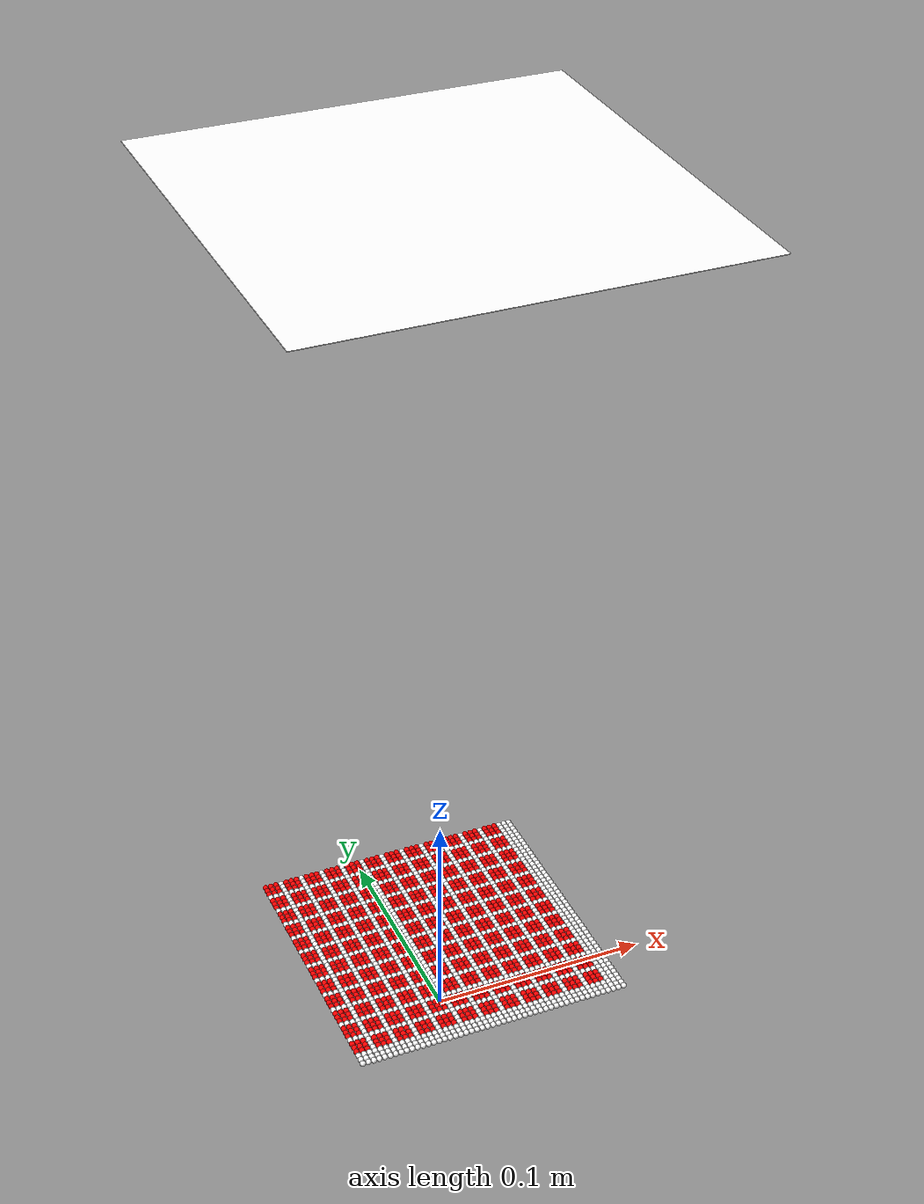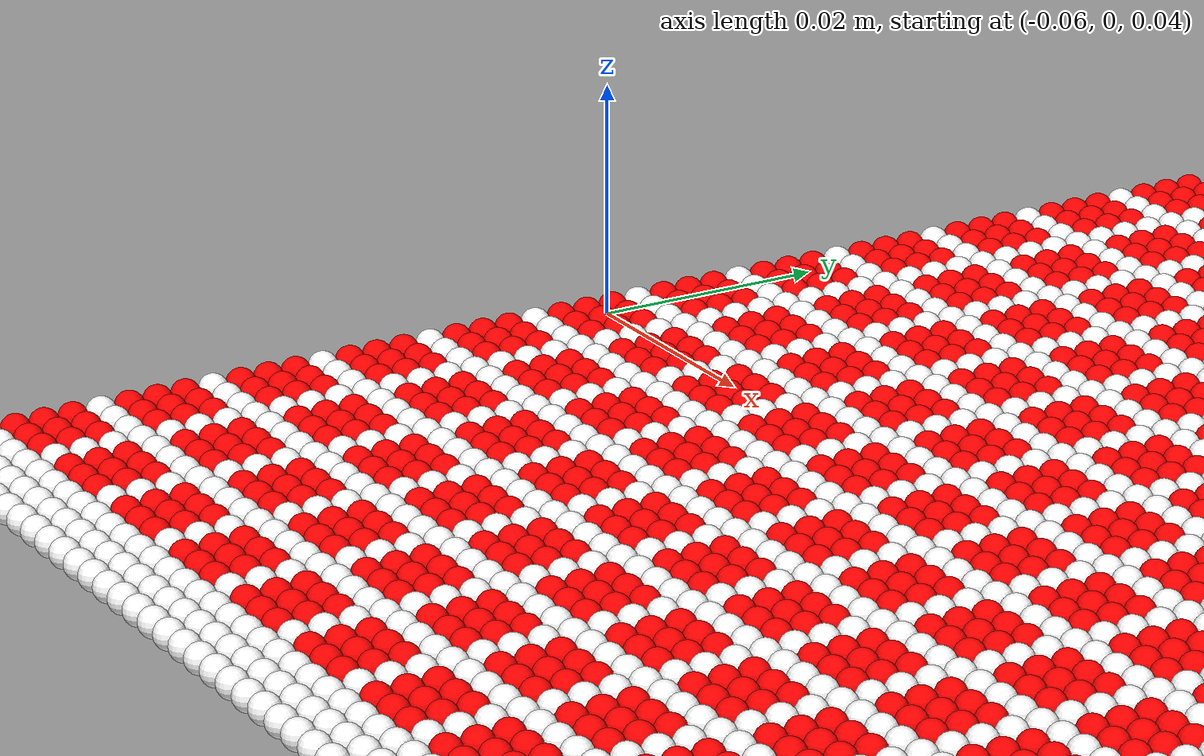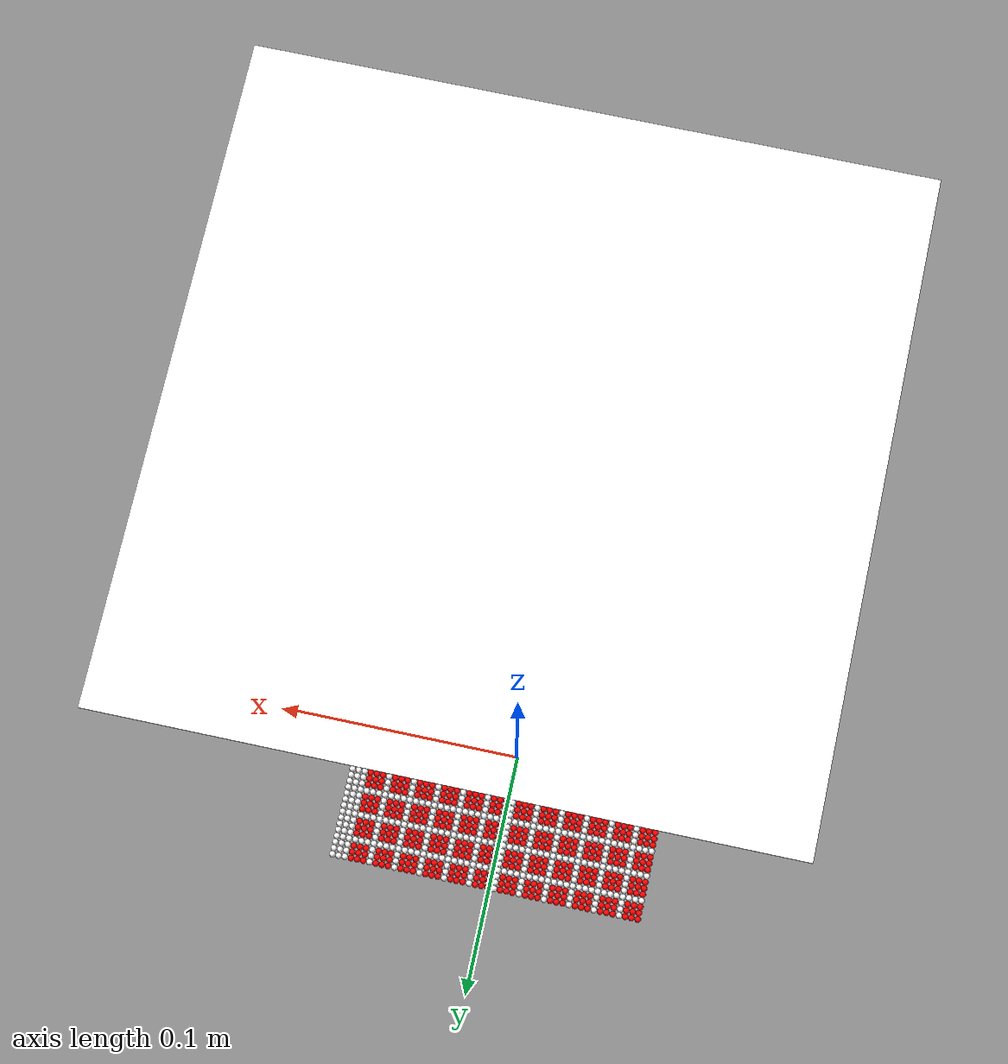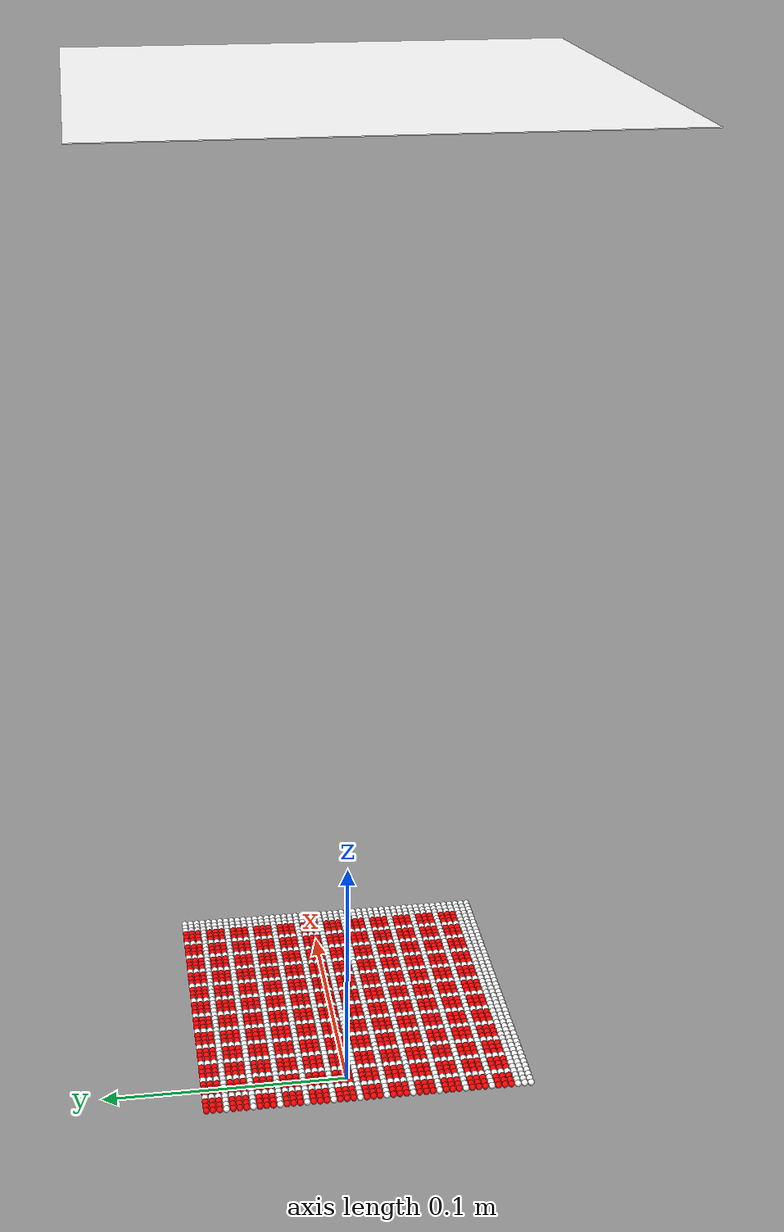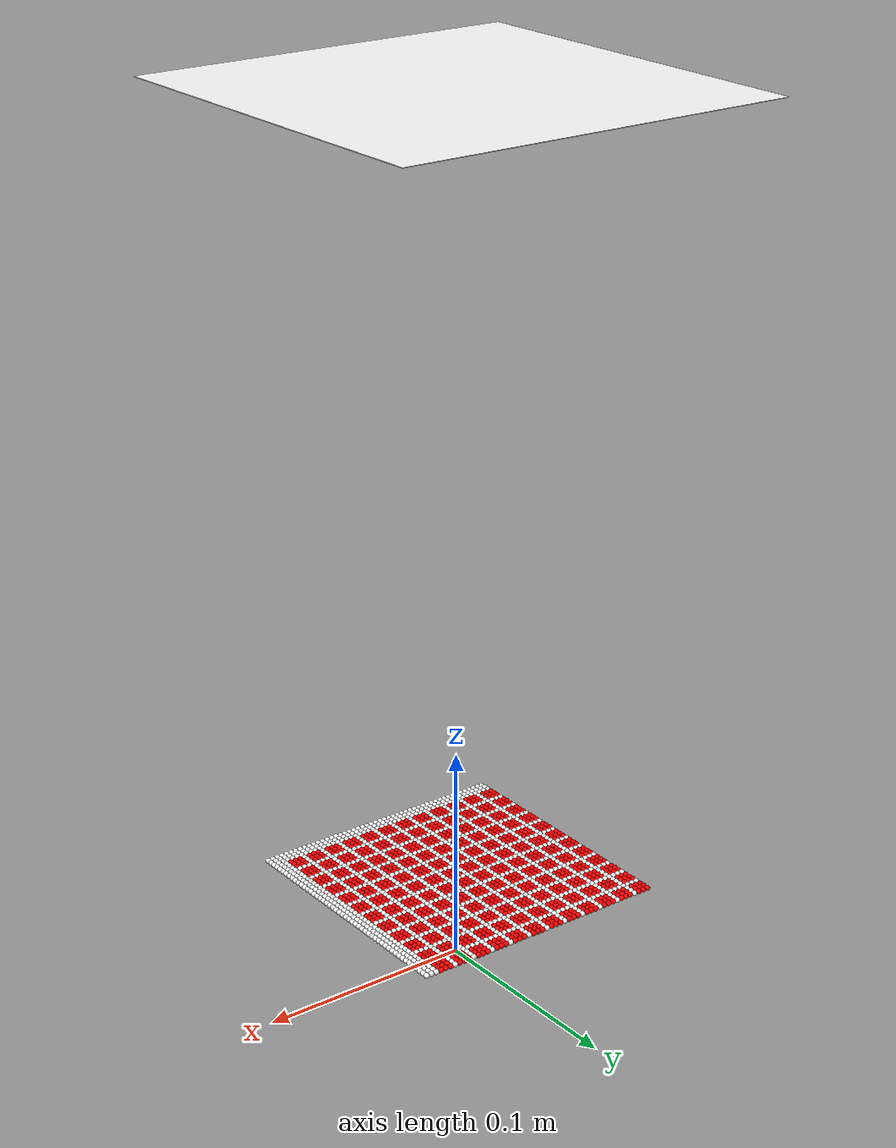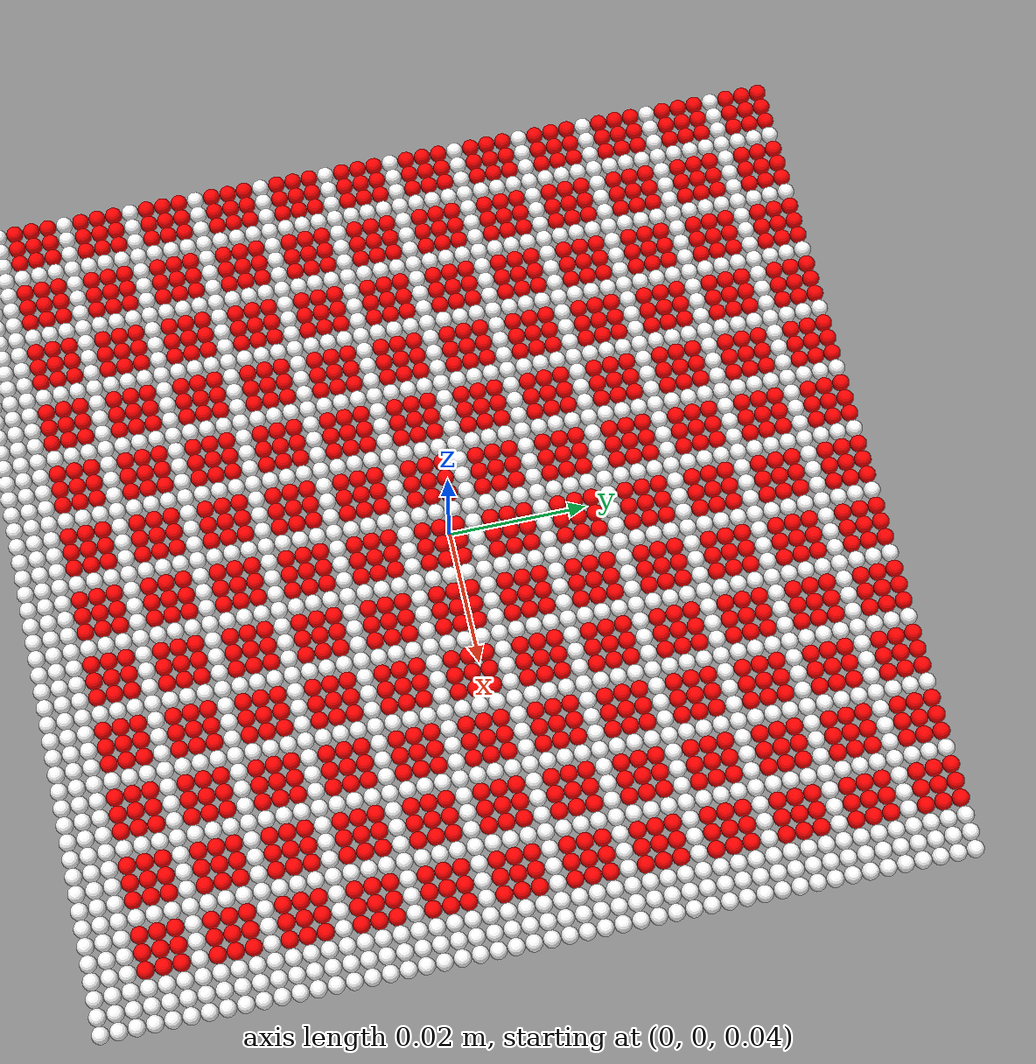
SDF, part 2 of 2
<joint name="spring_joint_1253" type="prismatic">
   <parent>plane</parent>
   <child>spring_1253</child>
   <axis>
    <xyz>0 0 1</xyz>
    <limit><lower>-1e+16</lower><upper>1e+16</upper></limit>
    <use_parent_model_frame>1</use_parent_model_frame>
   </axis>
  </joint>
  <link name="spring_1254">
   <pose>-0.05375 -0.00125 0.04 0 -0 0</pose>
   <inertial><mass>0.00235</mass></inertial>
   <collision name="sphere_collision">
    <geometry><sphere><radius>0.00125</radius></sphere></geometry>
    <surface><friction><ode><mu>0</mu><mu2>0</mu2></ode></friction></surface>
   </collision>
   <visual name="visual">
    <geometry><sphere><radius>0.00125</radius></sphere></geometry>
    <material>
     <ambient>1 1 1 1</ambient>
     <diffuse>1 1 1 1</diffuse>
     <specular>0.1 0.1 0.1 1</specular>
     <emissive>0 0 0 0</emissive>
    </material>
   </visual>
  </link>
  <joint name="spring_joint_1254" type="prismatic">
   <parent>plane</parent>
   <child>spring_1254</child>
   <axis>
    <xyz>0 0 1</xyz>
    <limit><lower>-1e+16</lower><upper>1e+16</upper></limit>
    <use_parent_model_frame>1</use_parent_model_frame>
   </axis>
  </joint>
  <link name="spring_1255">
   <pose>-0.05125 -0.00125 0.04 0 -0 0</pose>
   <inertial><mass>0.00235</mass></inertial>
   <collision name="sphere_collision">
    <geometry><sphere><radius>0.00125</radius></sphere></geometry>
    <surface><friction><ode><mu>0</mu><mu2>0</mu2></ode></friction></surface>
   </collision>
   <visual name="visual">
    <geometry><sphere><radius>0.00125</radius></sphere></geometry>
    <material>
     <ambient>1 0 0 1</ambient>
     <diffuse>1 0 0 1</diffuse>
     <specular>0.1 0.1 0.1 1</specular>
     <emissive>0 0 0 0</emissive>
    </material>
   </visual>
  </link>
  <joint name="spring_joint_1255" type="prismatic">
   <parent>plane</parent>
   <child>spring_1255</child>
   <axis>
    <xyz>0 0 1</xyz>
    <limit><lower>-1e+16</lower><upper>1e+16</upper></limit>
    <use_parent_model_frame>1</use_parent_model_frame>
   </axis>
  </joint>
  <link name="spring_1256">
   <pose>-0.04875 -0.00125 0.04 0 -0 0</pose>
   <inertial><mass>0.00235</mass></inertial>
   <collision name="sphere_collision">
    <geometry><sphere><radius>0.00125</radius></sphere></geometry>
    <surface><friction><ode><mu>0</mu><mu2>0</mu2></ode></friction></surface>
   </collision>
   <visual name="visual">
    <geometry><sphere><radius>0.00125</radius></sphere></geometry>
    <material>
     <ambient>1 0 0 1</ambient>
     <diffuse>1 0 0 1</diffuse>
     <specular>0.1 0.1 0.1 1</specular>
     <emissive>0 0 0 0</emissive>
    </material>
   </visual>
  </link>
  <joint name="spring_joint_1256" type="prismatic">
   <parent>plane</parent>
   <child>spring_1256</child>
   <axis>
    <xyz>0 0 1</xyz>
    <limit><lower>-1e+16</lower><upper>1e+16</upper></limit>
    <use_parent_model_frame>1</use_parent_model_frame>
   </axis>
  </joint>
  <link name="spring_1257">
   <pose>-0.04625 -0.00125 0.04 0 -0 0</pose>
   <inertial><mass>0.00235</mass></inertial>
   <collision name="sphere_collision">
    <geometry><sphere><radius>0.00125</radius></sphere></geometry>
    <surface><friction><ode><mu>0</mu><mu2>0</mu2></ode></friction></surface>
   </collision>
   <visual name="visual">
    <geometry><sphere><radius>0.00125</radius></sphere></geometry>
    <material>
     <ambient>1 0 0 1</ambient>
     <diffuse>1 0 0 1</diffuse>
     <specular>0.1 0.1 0.1 1</specular>
     <emissive>0 0 0 0</emissive>
    </material>
   </visual>
  </link>
  <joint name="spring_joint_1257" type="prismatic">
   <parent>plane</parent>
   <child>spring_1257</child>
   <axis>
    <xyz>0 0 1</xyz>
    <limit><lower>-1e+16</lower><upper>1e+16</upper></limit>
    <use_parent_model_frame>1</use_parent_model_frame>
   </axis>
  </joint>
  <link name="spring_1258">
   <pose>-0.04375 -0.00125 0.04 0 -0 0</pose>
   <inertial><mass>0.00235</mass></inertial>
   <collision name="sphere_collision">
    <geometry><sphere><radius>0.00125</radius></sphere></geometry>
    <surface><friction><ode><mu>0</mu><mu2>0</mu2></ode></friction></surface>
   </collision>
   <visual name="visual">
    <geometry><sphere><radius>0.00125</radius></sphere></geometry>
    <material>
     <ambient>1 1 1 1</ambient>
     <diffuse>1 1 1 1</diffuse>
     <specular>0.1 0.1 0.1 1</specular>
     <emissive>0 0 0 0</emissive>
    </material>
   </visual>
  </link>
  <joint name="spring_joint_1258" type="prismatic">
   <parent>plane</parent>
   <child>spring_1258</child>
   <axis>
    <xyz>0 0 1</xyz>
    <limit><lower>-1e+16</lower><upper>1e+16</upper></limit>
    <use_parent_model_frame>1</use_parent_model_frame>
   </axis>
  </joint>
  <link name="spring_1259">
   <pose>-0.04125 -0.00125 0.04 0 -0 0</pose>
   <inertial><mass>0.00235</mass></inertial>
   <collision name="sphere_collision">
    <geometry><sphere><radius>0.00125</radius></sphere></geometry>
    <surface><friction><ode><mu>0</mu><mu2>0</mu2></ode></friction></surface>
   </collision>
   <visual name="visual">
    <geometry><sphere><radius>0.00125</radius></sphere></geometry>
    <material>
     <ambient>1 0 0 1</ambient>
     <diffuse>1 0 0 1</diffuse>
     <specular>0.1 0.1 0.1 1</specular>
     <emissive>0 0 0 0</emissive>
    </material>
   </visual>
  </link>
  <joint name="spring_joint_1259" type="prismatic">
   <parent>plane</parent>
   <child>spring_1259</child>
   <axis>
    <xyz>0 0 1</xyz>
    <limit><lower>-1e+16</lower><upper>1e+16</upper></limit>
    <use_parent_model_frame>1</use_parent_model_frame>
   </axis>
  </joint>
  <link name="spring_1260">
   <pose>-0.03875 -0.00125 0.04 0 -0 0</pose>
   <inertial><mass>0.00235</mass></inertial>
   <collision name="sphere_collision">
    <geometry><sphere><radius>0.00125</radius></sphere></geometry>
    <surface><friction><ode><mu>0</mu><mu2>0</mu2></ode></friction></surface>
   </collision>
   <visual name="visual">
    <geometry><sphere><radius>0.00125</radius></sphere></geometry>
    <material>
     <ambient>1 0 0 1</ambient>
     <diffuse>1 0 0 1</diffuse>
     <specular>0.1 0.1 0.1 1</specular>
     <emissive>0 0 0 0</emissive>
    </material>
   </visual>
  </link>
  <joint name="spring_joint_1260" type="prismatic">
   <parent>plane</parent>
   <child>spring_1260</child>
   <axis>
    <xyz>0 0 1</xyz>
    <limit><lower>-1e+16</lower><upper>1e+16</upper></limit>
    <use_parent_model_frame>1</use_parent_model_frame>
   </axis>
  </joint>
  <link name="spring_1261">
   <pose>-0.03625 -0.00125 0.04 0 -0 0</pose>
   <inertial><mass>0.00235</mass></inertial>
   <collision name="sphere_collision">
    <geometry><sphere><radius>0.00125</radius></sphere></geometry>
    <surface><friction><ode><mu>0</mu><mu2>0</mu2></ode></friction></surface>
   </collision>
   <visual name="visual">
    <geometry><sphere><radius>0.00125</radius></sphere></geometry>
    <material>
     <ambient>1 0 0 1</ambient>
     <diffuse>1 0 0 1</diffuse>
     <specular>0.1 0.1 0.1 1</specular>
     <emissive>0 0 0 0</emissive>
    </material>
   </visual>
  </link>
  <joint name="spring_joint_1261" type="prismatic">
   <parent>plane</parent>
   <child>spring_1261</child>
   <axis>
    <xyz>0 0 1</xyz>
    <limit><lower>-1e+16</lower><upper>1e+16</upper></limit>
    <use_parent_model_frame>1</use_parent_model_frame>
   </axis>
  </joint>
  <link name="spring_1262">
   <pose>-0.03375 -0.00125 0.04 0 -0 0</pose>
   <inertial><mass>0.00235</mass></inertial>
   <collision name="sphere_collision">
    <geometry><sphere><radius>0.00125</radius></sphere></geometry>
    <surface><friction><ode><mu>0</mu><mu2>0</mu2></ode></friction></surface>
   </collision>
   <visual name="visual">
    <geometry><sphere><radius>0.00125</radius></sphere></geometry>
    <material>
     <ambient>1 1 1 1</ambient>
     <diffuse>1 1 1 1</diffuse>
     <specular>0.1 0.1 0.1 1</specular>
     <emissive>0 0 0 0</emissive>
    </material>
   </visual>
  </link>
  <joint name="spring_joint_1262" type="prismatic">
   <parent>plane</parent>
   <child>spring_1262</child>
   <axis>
    <xyz>0 0 1</xyz>
    <limit><lower>-1e+16</lower><upper>1e+16</upper></limit>
    <use_parent_model_frame>1</use_parent_model_frame>
   </axis>
  </joint>
  <link name="spring_1263">
   <pose>-0.03125 -0.00125 0.04 0 -0 0</pose>
   <inertial><mass>0.00235</mass></inertial>
   <collision name="sphere_collision">
    <geometry><sphere><radius>0.00125</radius></sphere></geometry>
    <surface><friction><ode><mu>0</mu><mu2>0</mu2></ode></friction></surface>
   </collision>
   <visual name="visual">
    <geometry><sphere><radius>0.00125</radius></sphere></geometry>
    <material>
     <ambient>1 0 0 1</ambient>
     <diffuse>1 0 0 1</diffuse>
     <specular>0.1 0.1 0.1 1</specular>
     <emissive>0 0 0 0</emissive>
    </material>
   </visual>
  </link>
  <joint name="spring_joint_1263" type="prismatic">
   <parent>plane</parent>
   <child>spring_1263</child>
   <axis>
    <xyz>0 0 1</xyz>
    <limit><lower>-1e+16</lower><upper>1e+16</upper></limit>
    <use_parent_model_frame>1</use_parent_model_frame>
   </axis>
  </joint>
  <link name="spring_1264">
   <pose>-0.02875 -0.00125 0.04 0 -0 0</pose>
   <inertial><mass>0.00235</mass></inertial>
   <collision name="sphere_collision">
    <geometry><sphere><radius>0.00125</radius></sphere></geometry>
    <surface><friction><ode><mu>0</mu><mu2>0</mu2></ode></friction></surface>
   </collision>
   <visual name="visual">
    <geometry><sphere><radius>0.00125</radius></sphere></geometry>
    <material>
     <ambient>1 0 0 1</ambient>
     <diffuse>1 0 0 1</diffuse>
     <specular>0.1 0.1 0.1 1</specular>
     <emissive>0 0 0 0</emissive>
    </material>
   </visual>
  </link>
  <joint name="spring_joint_1264" type="prismatic">
   <parent>plane</parent>
   <child>spring_1264</child>
   <axis>
    <xyz>0 0 1</xyz>
    <limit><lower>-1e+16</lower><upper>1e+16</upper></limit>
    <use_parent_model_frame>1</use_parent_model_frame>
   </axis>
  </joint>
  <link name="spring_1265">
   <pose>-0.02625 -0.00125 0.04 0 -0 0</pose>
   <inertial><mass>0.00235</mass></inertial>
   <collision name="sphere_collision">
    <geometry><sphere><radius>0.00125</radius></sphere></geometry>
    <surface><friction><ode><mu>0</mu><mu2>0</mu2></ode></friction></surface>
   </collision>
   <visual name="visual">
    <geometry><sphere><radius>0.00125</radius></sphere></geometry>
    <material>
     <ambient>1 0 0 1</ambient>
     <diffuse>1 0 0 1</diffuse>
     <specular>0.1 0.1 0.1 1</specular>
     <emissive>0 0 0 0</emissive>
    </material>
   </visual>
  </link>
  <joint name="spring_joint_1265" type="prismatic">
   <parent>plane</parent>
   <child>spring_1265</child>
   <axis>
    <xyz>0 0 1</xyz>
    <limit><lower>-1e+16</lower><upper>1e+16</upper></limit>
    <use_parent_model_frame>1</use_parent_model_frame>
   </axis>
  </joint>
  <link name="spring_1266">
   <pose>-0.02375 -0.00125 0.04 0 -0 0</pose>
   <inertial><mass>0.00235</mass></inertial>
   <collision name="sphere_collision">
    <geometry><sphere><radius>0.00125</radius></sphere></geometry>
    <surface><friction><ode><mu>0</mu><mu2>0</mu2></ode></friction></surface>
   </collision>
   <visual name="visual">
    <geometry><sphere><radius>0.00125</radius></sphere></geometry>
    <material>
     <ambient>1 1 1 1</ambient>
     <diffuse>1 1 1 1</diffuse>
     <specular>0.1 0.1 0.1 1</specular>
     <emissive>0 0 0 0</emissive>
    </material>
   </visual>
  </link>
  <joint name="spring_joint_1266" type="prismatic">
   <parent>plane</parent>
   <child>spring_1266</child>
   <axis>
    <xyz>0 0 1</xyz>
    <limit><lower>-1e+16</lower><upper>1e+16</upper></limit>
    <use_parent_model_frame>1</use_parent_model_frame>
   </axis>
  </joint>
  <link name="spring_1267">
   <pose>-0.02125 -0.00125 0.04 0 -0 0</pose>
   <inertial><mass>0.00235</mass></inertial>
   <collision name="sphere_collision">
    <geometry><sphere><radius>0.00125</radius></sphere></geometry>
    <surface><friction><ode><mu>0</mu><mu2>0</mu2></ode></friction></surface>
   </collision>
   <visual name="visual">
    <geometry><sphere><radius>0.00125</radius></sphere></geometry>
    <material>
     <ambient>1 0 0 1</ambient>
     <diffuse>1 0 0 1</diffuse>
     <specular>0.1 0.1 0.1 1</specular>
     <emissive>0 0 0 0</emissive>
    </material>
   </visual>
  </link>
  <joint name="spring_joint_1267" type="prismatic">
   <parent>plane</parent>
   <child>spring_1267</child>
   <axis>
    <xyz>0 0 1</xyz>
    <limit><lower>-1e+16</lower><upper>1e+16</upper></limit>
    <use_parent_model_frame>1</use_parent_model_frame>
   </axis>
  </joint>
  <link name="spring_1268">
   <pose>-0.01875 -0.00125 0.04 0 -0 0</pose>
   <inertial><mass>0.00235</mass></inertial>
   <collision name="sphere_collision">
    <geometry><sphere><radius>0.00125</radius></sphere></geometry>
    <surface><friction><ode><mu>0</mu><mu2>0</mu2></ode></friction></surface>
   </collision>
   <visual name="visual">
    <geometry><sphere><radius>0.00125</radius></sphere></geometry>
    <material>
     <ambient>1 0 0 1</ambient>
     <diffuse>1 0 0 1</diffuse>
     <specular>0.1 0.1 0.1 1</specular>
     <emissive>0 0 0 0</emissive>
    </material>
   </visual>
  </link>
  <joint name="spring_joint_1268" type="prismatic">
   <parent>plane</parent>
   <child>spring_1268</child>
   <axis>
    <xyz>0 0 1</xyz>
    <limit><lower>-1e+16</lower><upper>1e+16</upper></limit>
    <use_parent_model_frame>1</use_parent_model_frame>
   </axis>
  </joint>
  <link name="spring_1269">
   <pose>-0.01625 -0.00125 0.04 0 -0 0</pose>
   <inertial><mass>0.00235</mass></inertial>
   <collision name="sphere_collision">
    <geometry><sphere><radius>0.00125</radius></sphere></geometry>
    <surface><friction><ode><mu>0</mu><mu2>0</mu2></ode></friction></surface>
   </collision>
   <visual name="visual">
    <geometry><sphere><radius>0.00125</radius></sphere></geometry>
    <material>
     <ambient>1 0 0 1</ambient>
     <diffuse>1 0 0 1</diffuse>
     <specular>0.1 0.1 0.1 1</specular>
     <emissive>0 0 0 0</emissive>
    </material>
   </visual>
  </link>
  <joint name="spring_joint_1269" type="prismatic">
   <parent>plane</parent>
   <child>spring_1269</child>
   <axis>
    <xyz>0 0 1</xyz>
    <limit><lower>-1e+16</lower><upper>1e+16</upper></limit>
    <use_parent_model_frame>1</use_parent_model_frame>
   </axis>
  </joint>
  <link name="spring_1270">
   <pose>-0.01375 -0.00125 0.04 0 -0 0</pose>
   <inertial><mass>0.00235</mass></inertial>
   <collision name="sphere_collision">
    <geometry><sphere><radius>0.00125</radius></sphere></geometry>
    <surface><friction><ode><mu>0</mu><mu2>0</mu2></ode></friction></surface>
   </collision>
   <visual name="visual">
    <geometry><sphere><radius>0.00125</radius></sphere></geometry>
    <material>
     <ambient>1 1 1 1</ambient>
     <diffuse>1 1 1 1</diffuse>
     <specular>0.1 0.1 0.1 1</specular>
     <emissive>0 0 0 0</emissive>
    </material>
   </visual>
  </link>
  <joint name="spring_joint_1270" type="prismatic">
   <parent>plane</parent>
   <child>spring_1270</child>
   <axis>
    <xyz>0 0 1</xyz>
    <limit><lower>-1e+16</lower><upper>1e+16</upper></limit>
    <use_parent_model_frame>1</use_parent_model_frame>
   </axis>
  </joint>
  <link name="spring_1271">
   <pose>-0.01125 -0.00125 0.04 0 -0 0</pose>
   <inertial><mass>0.00235</mass></inertial>
   <collision name="sphere_collision">
    <geometry><sphere><radius>0.00125</radius></sphere></geometry>
    <surface><friction><ode><mu>0</mu><mu2>0</mu2></ode></friction></surface>
   </collision>
   <visual name="visual">
    <geometry><sphere><radius>0.00125</radius></sphere></geometry>
    <material>
     <ambient>1 0 0 1</ambient>
     <diffuse>1 0 0 1</diffuse>
     <specular>0.1 0.1 0.1 1</specular>
     <emissive>0 0 0 0</emissive>
    </material>
   </visual>
  </link>
  <joint name="spring_joint_1271" type="prismatic">
   <parent>plane</parent>
   <child>spring_1271</child>
   <axis>
    <xyz>0 0 1</xyz>
    <limit><lower>-1e+16</lower><upper>1e+16</upper></limit>
    <use_parent_model_frame>1</use_parent_model_frame>
   </axis>
  </joint>
  <link name="spring_1272">
   <pose>-0.00875 -0.00125 0.04 0 -0 0</pose>
   <inertial><mass>0.00235</mass></inertial>
   <collision name="sphere_collision">
    <geometry><sphere><radius>0.00125</radius></sphere></geometry>
    <surface><friction><ode><mu>0</mu><mu2>0</mu2></ode></friction></surface>
   </collision>
   <visual name="visual">
    <geometry><sphere><radius>0.00125</radius></sphere></geometry>
    <material>
     <ambient>1 0 0 1</ambient>
     <diffuse>1 0 0 1</diffuse>
     <specular>0.1 0.1 0.1 1</specular>
     <emissive>0 0 0 0</emissive>
    </material>
   </visual>
  </link>
  <joint name="spring_joint_1272" type="prismatic">
   <parent>plane</parent>
   <child>spring_1272</child>
   <axis>
    <xyz>0 0 1</xyz>
    <limit><lower>-1e+16</lower><upper>1e+16</upper></limit>
    <use_parent_model_frame>1</use_parent_model_frame>
   </axis>
  </joint>
  <link name="spring_1273">
   <pose>-0.00625 -0.00125 0.04 0 -0 0</pose>
   <inertial><mass>0.00235</mass></inertial>
   <collision name="sphere_collision">
    <geometry><sphere><radius>0.00125</radius></sphere></geometry>
    <surface><friction><ode><mu>0</mu><mu2>0</mu2></ode></friction></surface>
   </collision>
   <visual name="visual">
    <geometry><sphere><radius>0.00125</radius></sphere></geometry>
    <material>
     <ambient>1 0 0 1</ambient>
     <diffuse>1 0 0 1</diffuse>
     <specular>0.1 0.1 0.1 1</specular>
     <emissive>0 0 0 0</emissive>
    </material>
   </visual>
  </link>
  <joint name="spring_joint_1273" type="prismatic">
   <parent>plane</parent>
   <child>spring_1273</child>
   <axis>
    <xyz>0 0 1</xyz>
    <limit><lower>-1e+16</lower><upper>1e+16</upper></limit>
    <use_parent_model_frame>1</use_parent_model_frame>
   </axis>
  </joint>
  <link name="spring_1274">
   <pose>-0.00375 -0.00125 0.04 0 -0 0</pose>
   <inertial><mass>0.00235</mass></inertial>
   <collision name="sphere_collision">
    <geometry><sphere><radius>0.00125</radius></sphere></geometry>
    <surface><friction><ode><mu>0</mu><mu2>0</mu2></ode></friction></surface>
   </collision>
   <visual name="visual">
    <geometry><sphere><radius>0.00125</radius></sphere></geometry>
    <material>
     <ambient>1 1 1 1</ambient>
     <diffuse>1 1 1 1</diffuse>
     <specular>0.1 0.1 0.1 1</specular>
     <emissive>0 0 0 0</emissive>
    </material>
   </visual>
  </link>
  <joint name="spring_joint_1274" type="prismatic">
   <parent>plane</parent>
   <child>spring_1274</child>
   <axis>
    <xyz>0 0 1</xyz>
    <limit><lower>-1e+16</lower><upper>1e+16</upper></limit>
    <use_parent_model_frame>1</use_parent_model_frame>
   </axis>
  </joint>
  <link name="spring_1275">
   <pose>-0.00125 -0.00125 0.04 0 -0 0</pose>
   <inertial><mass>0.00235</mass></inertial>
   <collision name="sphere_collision">
    <geometry><sphere><radius>0.00125</radius></sphere></geometry>
    <surface><friction><ode><mu>0</mu><mu2>0</mu2></ode></friction></surface>
   </collision>
   <visual name="visual">
    <geometry><sphere><radius>0.00125</radius></sphere></geometry>
    <material>
     <ambient>1 0 0 1</ambient>
     <diffuse>1 0 0 1</diffuse>
     <specular>0.1 0.1 0.1 1</specular>
     <emissive>0 0 0 0</emissive>
    </material>
   </visual>
  </link>
  <joint name="spring_joint_1275" type="prismatic">
   <parent>plane</parent>
   <child>spring_1275</child>
   <axis>
    <xyz>0 0 1</xyz>
    <limit><lower>-1e+16</lower><upper>1e+16</upper></limit>
    <use_parent_model_frame>1</use_parent_model_frame>
   </axis>
  </joint>
  <link name="spring_1276">
   <pose>0.00125 -0.00125 0.04 0 -0 0</pose>
   <inertial><mass>0.00235</mass></inertial>
   <collision name="sphere_collision">
    <geometry><sphere><radius>0.00125</radius></sphere></geometry>
    <surface><friction><ode><mu>0</mu><mu2>0</mu2></ode></friction></surface>
   </collision>
   <visual name="visual">
    <geometry><sphere><radius>0.00125</radius></sphere></geometry>
    <material>
     <ambient>1 0 0 1</ambient>
     <diffuse>1 0 0 1</diffuse>
     <specular>0.1 0.1 0.1 1</specular>
     <emissive>0 0 0 0</emissive>
    </material>
   </visual>
  </link>
  <joint name="spring_joint_1276" type="prismatic">
   <parent>plane</parent>
   <child>spring_1276</child>
   <axis>
    <xyz>0 0 1</xyz>
    <limit><lower>-1e+16</lower><upper>1e+16</upper></limit>
    <use_parent_model_frame>1</use_parent_model_frame>
   </axis>
  </joint>
  <link name="spring_1277">
   <pose>0.00375 -0.00125 0.04 0 -0 0</pose>
   <inertial><mass>0.00235</mass></inertial>
   <collision name="sphere_collision">
    <geometry><sphere><radius>0.00125</radius></sphere></geometry>
    <surface><friction><ode><mu>0</mu><mu2>0</mu2></ode></friction></surface>
   </collision>
   <visual name="visual">
    <geometry><sphere><radius>0.00125</radius></sphere></geometry>
    <material>
     <ambient>1 0 0 1</ambient>
     <diffuse>1 0 0 1</diffuse>
     <specular>0.1 0.1 0.1 1</specular>
     <emissive>0 0 0 0</emissive>
    </material>
   </visual>
  </link>
  <joint name="spring_joint_1277" type="prismatic">
   <parent>plane</parent>
   <child>spring_1277</child>
   <axis>
    <xyz>0 0 1</xyz>
    <limit><lower>-1e+16</lower><upper>1e+16</upper></limit>
    <use_parent_model_frame>1</use_parent_model_frame>
   </axis>
  </joint>
  <link name="spring_1278">
   <pose>0.00625 -0.00125 0.04 0 -0 0</pose>
   <inertial><mass>0.00235</mass></inertial>
   <collision name="sphere_collision">
    <geometry><sphere><radius>0.00125</radius></sphere></geometry>
    <surface><friction><ode><mu>0</mu><mu2>0</mu2></ode></friction></surface>
   </collision>
   <visual name="visual">
    <geometry><sphere><radius>0.00125</radius></sphere></geometry>
    <material>
     <ambient>1 1 1 1</ambient>
     <diffuse>1 1 1 1</diffuse>
     <specular>0.1 0.1 0.1 1</specular>
     <emissive>0 0 0 0</emissive>
    </material>
   </visual>
  </link>
  <joint name="spring_joint_1278" type="prismatic">
   <parent>plane</parent>
   <child>spring_1278</child>
   <axis>
    <xyz>0 0 1</xyz>
    <limit><lower>-1e+16</lower><upper>1e+16</upper></limit>
    <use_parent_model_frame>1</use_parent_model_frame>
   </axis>
  </joint>
  <link name="spring_1279">
   <pose>0.00875 -0.00125 0.04 0 -0 0</pose>
   <inertial><mass>0.00235</mass></inertial>
   <collision name="sphere_collision">
    <geometry><sphere><radius>0.00125</radius></sphere></geometry>
    <surface><friction><ode><mu>0</mu><mu2>0</mu2></ode></friction></surface>
   </collision>
   <visual name="visual">
    <geometry><sphere><radius>0.00125</radius></sphere></geometry>
    <material>
     <ambient>1 0 0 1</ambient>
     <diffuse>1 0 0 1</diffuse>
     <specular>0.1 0.1 0.1 1</specular>
     <emissive>0 0 0 0</emissive>
    </material>
   </visual>
  </link>
  <joint name="spring_joint_1279" type="prismatic">
   <parent>plane</parent>
   <child>spring_1279</child>
   <axis>
    <xyz>0 0 1</xyz>
    <limit><lower>-1e+16</lower><upper>1e+16</upper></limit>
    <use_parent_model_frame>1</use_parent_model_frame>
   </axis>
  </joint>
  <link name="spring_1280">
   <pose>0.01125 -0.00125 0.04 0 -0 0</pose>
   <inertial><mass>0.00235</mass></inertial>
   <collision name="sphere_collision">
    <geometry><sphere><radius>0.00125</radius></sphere></geometry>
    <surface><friction><ode><mu>0</mu><mu2>0</mu2></ode></friction></surface>
   </collision>
   <visual name="visual">
    <geometry><sphere><radius>0.00125</radius></sphere></geometry>
    <material>
     <ambient>1 0 0 1</ambient>
     <diffuse>1 0 0 1</diffuse>
     <specular>0.1 0.1 0.1 1</specular>
     <emissive>0 0 0 0</emissive>
    </material>
   </visual>
  </link>
  <joint name="spring_joint_1280" type="prismatic">
   <parent>plane</parent>
   <child>spring_1280</child>
   <axis>
    <xyz>0 0 1</xyz>
    <limit><lower>-1e+16</lower><upper>1e+16</upper></limit>
    <use_parent_model_frame>1</use_parent_model_frame>
   </axis>
  </joint>
  <link name="spring_1281">
   <pose>0.01375 -0.00125 0.04 0 -0 0</pose>
   <inertial><mass>0.00235</mass></inertial>
   <collision name="sphere_collision">
    <geometry><sphere><radius>0.00125</radius></sphere></geometry>
    <surface><friction><ode><mu>0</mu><mu2>0</mu2></ode></friction></surface>
   </collision>
   <visual name="visual">
    <geometry><sphere><radius>0.00125</radius></sphere></geometry>
    <material>
     <ambient>1 0 0 1</ambient>
     <diffuse>1 0 0 1</diffuse>
     <specular>0.1 0.1 0.1 1</specular>
     <emissive>0 0 0 0</emissive>
    </material>
   </visual>
  </link>
  <joint name="spring_joint_1281" type="prismatic">
   <parent>plane</parent>
   <child>spring_1281</child>
   <axis>
    <xyz>0 0 1</xyz>
    <limit><lower>-1e+16</lower><upper>1e+16</upper></limit>
    <use_parent_model_frame>1</use_parent_model_frame>
   </axis>
  </joint>
  <link name="spring_1282">
   <pose>0.01625 -0.00125 0.04 0 -0 0</pose>
   <inertial><mass>0.00235</mass></inertial>
   <collision name="sphere_collision">
    <geometry><sphere><radius>0.00125</radius></sphere></geometry>
    <surface><friction><ode><mu>0</mu><mu2>0</mu2></ode></friction></surface>
   </collision>
   <visual name="visual">
    <geometry><sphere><radius>0.00125</radius></sphere></geometry>
    <material>
     <ambient>1 1 1 1</ambient>
     <diffuse>1 1 1 1</diffuse>
     <specular>0.1 0.1 0.1 1</specular>
     <emissive>0 0 0 0</emissive>
    </material>
   </visual>
  </link>
  <joint name="spring_joint_1282" type="prismatic">
   <parent>plane</parent>
   <child>spring_1282</child>
   <axis>
    <xyz>0 0 1</xyz>
    <limit><lower>-1e+16</lower><upper>1e+16</upper></limit>
    <use_parent_model_frame>1</use_parent_model_frame>
   </axis>
  </joint>
  <link name="spring_1283">
   <pose>0.01875 -0.00125 0.04 0 -0 0</pose>
   <inertial><mass>0.00235</mass></inertial>
   <collision name="sphere_collision">
    <geometry><sphere><radius>0.00125</radius></sphere></geometry>
    <surface><friction><ode><mu>0</mu><mu2>0</mu2></ode></friction></surface>
   </collision>
   <visual name="visual">
    <geometry><sphere><radius>0.00125</radius></sphere></geometry>
    <material>
     <ambient>1 0 0 1</ambient>
     <diffuse>1 0 0 1</diffuse>
     <specular>0.1 0.1 0.1 1</specular>
     <emissive>0 0 0 0</emissive>
    </material>
   </visual>
  </link>
  <joint name="spring_joint_1283" type="prismatic">
   <parent>plane</parent>
   <child>spring_1283</child>
   <axis>
    <xyz>0 0 1</xyz>
    <limit><lower>-1e+16</lower><upper>1e+16</upper></limit>
    <use_parent_model_frame>1</use_parent_model_frame>
   </axis>
  </joint>
  <link name="spring_1284">
   <pose>0.02125 -0.00125 0.04 0 -0 0</pose>
   <inertial><mass>0.00235</mass></inertial>
   <collision name="sphere_collision">
    <geometry><sphere><radius>0.00125</radius></sphere></geometry>
    <surface><friction><ode><mu>0</mu><mu2>0</mu2></ode></friction></surface>
   </collision>
   <visual name="visual">
    <geometry><sphere><radius>0.00125</radius></sphere></geometry>
    <material>
     <ambient>1 0 0 1</ambient>
     <diffuse>1 0 0 1</diffuse>
     <specular>0.1 0.1 0.1 1</specular>
     <emissive>0 0 0 0</emissive>
    </material>
   </visual>
  </link>
  <joint name="spring_joint_1284" type="prismatic">
   <parent>plane</parent>
   <child>spring_1284</child>
   <axis>
    <xyz>0 0 1</xyz>
    <limit><lower>-1e+16</lower><upper>1e+16</upper></limit>
    <use_parent_model_frame>1</use_parent_model_frame>
   </axis>
  </joint>
  <link name="spring_1285">
   <pose>0.02375 -0.00125 0.04 0 -0 0</pose>
   <inertial><mass>0.00235</mass></inertial>
   <collision name="sphere_collision">
    <geometry><sphere><radius>0.00125</radius></sphere></geometry>
    <surface><friction><ode><mu>0</mu><mu2>0</mu2></ode></friction></surface>
   </collision>
   <visual name="visual">
    <geometry><sphere><radius>0.00125</radius></sphere></geometry>
    <material>
     <ambient>1 0 0 1</ambient>
     <diffuse>1 0 0 1</diffuse>
     <specular>0.1 0.1 0.1 1</specular>
     <emissive>0 0 0 0</emissive>
    </material>
   </visual>
  </link>
  <joint name="spring_joint_1285" type="prismatic">
   <parent>plane</parent>
   <child>spring_1285</child>
   <axis>
    <xyz>0 0 1</xyz>
    <limit><lower>-1e+16</lower><upper>1e+16</upper></limit>
    <use_parent_model_frame>1</use_parent_model_frame>
   </axis>
  </joint>
  <link name="spring_1286">
   <pose>0.02625 -0.00125 0.04 0 -0 0</pose>
   <inertial><mass>0.00235</mass></inertial>
   <collision name="sphere_collision">
    <geometry><sphere><radius>0.00125</radius></sphere></geometry>
    <surface><friction><ode><mu>0</mu><mu2>0</mu2></ode></friction></surface>
   </collision>
   <visual name="visual">
    <geometry><sphere><radius>0.00125</radius></sphere></geometry>
    <material>
     <ambient>1 1 1 1</ambient>
     <diffuse>1 1 1 1</diffuse>
     <specular>0.1 0.1 0.1 1</specular>
     <emissive>0 0 0 0</emissive>
    </material>
   </visual>
  </link>
  <joint name="spring_joint_1286" type="prismatic">
   <parent>plane</parent>
   <child>spring_1286</child>
   <axis>
    <xyz>0 0 1</xyz>
    <limit><lower>-1e+16</lower><upper>1e+16</upper></limit>
    <use_parent_model_frame>1</use_parent_model_frame>
   </axis>
  </joint>
  <link name="spring_1287">
   <pose>0.02875 -0.00125 0.04 0 -0 0</pose>
   <inertial><mass>0.00235</mass></inertial>
   <collision name="sphere_collision">
    <geometry><sphere><radius>0.00125</radius></sphere></geometry>
    <surface><friction><ode><mu>0</mu><mu2>0</mu2></ode></friction></surface>
   </collision>
   <visual name="visual">
    <geometry><sphere><radius>0.00125</radius></sphere></geometry>
    <material>
     <ambient>1 0 0 1</ambient>
     <diffuse>1 0 0 1</diffuse>
     <specular>0.1 0.1 0.1 1</specular>
     <emissive>0 0 0 0</emissive>
    </material>
   </visual>
  </link>
  <joint name="spring_joint_1287" type="prismatic">
   <parent>plane</parent>
   <child>spring_1287</child>
   <axis>
    <xyz>0 0 1</xyz>
    <limit><lower>-1e+16</lower><upper>1e+16</upper></limit>
    <use_parent_model_frame>1</use_parent_model_frame>
   </axis>
  </joint>
  <link name="spring_1288">
   <pose>0.03125 -0.00125 0.04 0 -0 0</pose>
   <inertial><mass>0.00235</mass></inertial>
   <collision name="sphere_collision">
    <geometry><sphere><radius>0.00125</radius></sphere></geometry>
    <surface><friction><ode><mu>0</mu><mu2>0</mu2></ode></friction></surface>
   </collision>
   <visual name="visual">
    <geometry><sphere><radius>0.00125</radius></sphere></geometry>
    <material>
     <ambient>1 0 0 1</ambient>
     <diffuse>1 0 0 1</diffuse>
     <specular>0.1 0.1 0.1 1</specular>
     <emissive>0 0 0 0</emissive>
    </material>
   </visual>
  </link>
  <joint name="spring_joint_1288" type="prismatic">
   <parent>plane</parent>
   <child>spring_1288</child>
   <axis>
    <xyz>0 0 1</xyz>
    <limit><lower>-1e+16</lower><upper>1e+16</upper></limit>
    <use_parent_model_frame>1</use_parent_model_frame>
   </axis>
  </joint>
  <link name="spring_1289">
   <pose>0.03375 -0.00125 0.04 0 -0 0</pose>
   <inertial><mass>0.00235</mass></inertial>
   <collision name="sphere_collision">
    <geometry><sphere><radius>0.00125</radius></sphere></geometry>
    <surface><friction><ode><mu>0</mu><mu2>0</mu2></ode></friction></surface>
   </collision>
   <visual name="visual">
    <geometry><sphere><radius>0.00125</radius></sphere></geometry>
    <material>
     <ambient>1 0 0 1</ambient>
     <diffuse>1 0 0 1</diffuse>
     <specular>0.1 0.1 0.1 1</specular>
     <emissive>0 0 0 0</emissive>
    </material>
   </visual>
  </link>
  <joint name="spring_joint_1289" type="prismatic">
   <parent>plane</parent>
   <child>spring_1289</child>
   <axis>
    <xyz>0 0 1</xyz>
    <limit><lower>-1e+16</lower><upper>1e+16</upper></limit>
    <use_parent_model_frame>1</use_parent_model_frame>
   </axis>
  </joint>
  <link name="spring_1290">
   <pose>0.03625 -0.00125 0.04 0 -0 0</pose>
   <inertial><mass>0.00235</mass></inertial>
   <collision name="sphere_collision">
    <geometry><sphere><radius>0.00125</radius></sphere></geometry>
    <surface><friction><ode><mu>0</mu><mu2>0</mu2></ode></friction></surface>
   </collision>
   <visual name="visual">
    <geometry><sphere><radius>0.00125</radius></sphere></geometry>
    <material>
     <ambient>1 1 1 1</ambient>
     <diffuse>1 1 1 1</diffuse>
     <specular>0.1 0.1 0.1 1</specular>
     <emissive>0 0 0 0</emissive>
    </material>
   </visual>
  </link>
  <joint name="spring_joint_1290" type="prismatic">
   <parent>plane</parent>
   <child>spring_1290</child>
   <axis>
    <xyz>0 0 1</xyz>
    <limit><lower>-1e+16</lower><upper>1e+16</upper></limit>
    <use_parent_model_frame>1</use_parent_model_frame>
   </axis>
  </joint>
  <link name="spring_1291">
   <pose>0.03875 -0.00125 0.04 0 -0 0</pose>
   <inertial><mass>0.00235</mass></inertial>
   <collision name="sphere_collision">
    <geometry><sphere><radius>0.00125</radius></sphere></geometry>
    <surface><friction><ode><mu>0</mu><mu2>0</mu2></ode></friction></surface>
   </collision>
   <visual name="visual">
    <geometry><sphere><radius>0.00125</radius></sphere></geometry>
    <material>
     <ambient>1 0 0 1</ambient>
     <diffuse>1 0 0 1</diffuse>
     <specular>0.1 0.1 0.1 1</specular>
     <emissive>0 0 0 0</emissive>
    </material>
   </visual>
  </link>
  <joint name="spring_joint_1291" type="prismatic">
   <parent>plane</parent>
   <child>spring_1291</child>
   <axis>
    <xyz>0 0 1</xyz>
    <limit><lower>-1e+16</lower><upper>1e+16</upper></limit>
    <use_parent_model_frame>1</use_parent_model_frame>
   </axis>
  </joint>
  <link name="spring_1292">
   <pose>0.04125 -0.00125 0.04 0 -0 0</pose>
   <inertial><mass>0.00235</mass></inertial>
   <collision name="sphere_collision">
    <geometry><sphere><radius>0.00125</radius></sphere></geometry>
    <surface><friction><ode><mu>0</mu><mu2>0</mu2></ode></friction></surface>
   </collision>
   <visual name="visual">
    <geometry><sphere><radius>0.00125</radius></sphere></geometry>
    <material>
     <ambient>1 0 0 1</ambient>
     <diffuse>1 0 0 1</diffuse>
     <specular>0.1 0.1 0.1 1</specular>
     <emissive>0 0 0 0</emissive>
    </material>
   </visual>
  </link>
  <joint name="spring_joint_1292" type="prismatic">
   <parent>plane</parent>
   <child>spring_1292</child>
   <axis>
    <xyz>0 0 1</xyz>
    <limit><lower>-1e+16</lower><upper>1e+16</upper></limit>
    <use_parent_model_frame>1</use_parent_model_frame>
   </axis>
  </joint>
  <link name="spring_1293">
   <pose>0.04375 -0.00125 0.04 0 -0 0</pose>
   <inertial><mass>0.00235</mass></inertial>
   <collision name="sphere_collision">
    <geometry><sphere><radius>0.00125</radius></sphere></geometry>
    <surface><friction><ode><mu>0</mu><mu2>0</mu2></ode></friction></surface>
   </collision>
   <visual name="visual">
    <geometry><sphere><radius>0.00125</radius></sphere></geometry>
    <material>
     <ambient>1 0 0 1</ambient>
     <diffuse>1 0 0 1</diffuse>
     <specular>0.1 0.1 0.1 1</specular>
     <emissive>0 0 0 0</emissive>
    </material>
   </visual>
  </link>
  <joint name="spring_joint_1293" type="prismatic">
   <parent>plane</parent>
   <child>spring_1293</child>
   <axis>
    <xyz>0 0 1</xyz>
    <limit><lower>-1e+16</lower><upper>1e+16</upper></limit>
    <use_parent_model_frame>1</use_parent_model_frame>
   </axis>
  </joint>
  <link name="spring_1294">
   <pose>0.04625 -0.00125 0.04 0 -0 0</pose>
   <inertial><mass>0.00235</mass></inertial>
   <collision name="sphere_collision">
    <geometry><sphere><radius>0.00125</radius></sphere></geometry>
    <surface><friction><ode><mu>0</mu><mu2>0</mu2></ode></friction></surface>
   </collision>
   <visual name="visual">
    <geometry><sphere><radius>0.00125</radius></sphere></geometry>
    <material>
     <ambient>1 1 1 1</ambient>
     <diffuse>1 1 1 1</diffuse>
     <specular>0.1 0.1 0.1 1</specular>
     <emissive>0 0 0 0</emissive>
    </material>
   </visual>
  </link>
  <joint name="spring_joint_1294" type="prismatic">
   <parent>plane</parent>
   <child>spring_1294</child>
   <axis>
    <xyz>0 0 1</xyz>
    <limit><lower>-1e+16</lower><upper>1e+16</upper></limit>
    <use_parent_model_frame>1</use_parent_model_frame>
   </axis>
  </joint>
  <link name="spring_1295">
   <pose>0.04875 -0.00125 0.04 0 -0 0</pose>
   <inertial><mass>0.00235</mass></inertial>
   <collision name="sphere_collision">
    <geometry><sphere><radius>0.00125</radius></sphere></geometry>
    <surface><friction><ode><mu>0</mu><mu2>0</mu2></ode></friction></surface>
   </collision>
   <visual name="visual">
    <geometry><sphere><radius>0.00125</radius></sphere></geometry>
    <material>
     <ambient>1 0 0 1</ambient>
     <diffuse>1 0 0 1</diffuse>
     <specular>0.1 0.1 0.1 1</specular>
     <emissive>0 0 0 0</emissive>
    </material>
   </visual>
  </link>
  <joint name="spring_joint_1295" type="prismatic">
   <parent>plane</parent>
   <child>spring_1295</child>
   <axis>
    <xyz>0 0 1</xyz>
    <limit><lower>-1e+16</lower><upper>1e+16</upper></limit>
    <use_parent_model_frame>1</use_parent_model_frame>
   </axis>
  </joint>
  <link name="spring_1296">
   <pose>0.05125 -0.00125 0.04 0 -0 0</pose>
   <inertial><mass>0.00235</mass></inertial>
   <collision name="sphere_collision">
    <geometry><sphere><radius>0.00125</radius></sphere></geometry>
    <surface><friction><ode><mu>0</mu><mu2>0</mu2></ode></friction></surface>
   </collision>
   <visual name="visual">
    <geometry><sphere><radius>0.00125</radius></sphere></geometry>
    <material>
     <ambient>1 0 0 1</ambient>
     <diffuse>1 0 0 1</diffuse>
     <specular>0.1 0.1 0.1 1</specular>
     <emissive>0 0 0 0</emissive>
    </material>
   </visual>
  </link>
  <joint name="spring_joint_1296" type="prismatic">
   <parent>plane</parent>
   <child>spring_1296</child>
   <axis>
    <xyz>0 0 1</xyz>
    <limit><lower>-1e+16</lower><upper>1e+16</upper></limit>
    <use_parent_model_frame>1</use_parent_model_frame>
   </axis>
  </joint>
  <link name="spring_1297">
   <pose>0.05375 -0.00125 0.04 0 -0 0</pose>
   <inertial><mass>0.00235</mass></inertial>
   <collision name="sphere_collision">
    <geometry><sphere><radius>0.00125</radius></sphere></geometry>
    <surface><friction><ode><mu>0</mu><mu2>0</mu2></ode></friction></surface>
   </collision>
   <visual name="visual">
    <geometry><sphere><radius>0.00125</radius></sphere></geometry>
    <material>
     <ambient>1 0 0 1</ambient>
     <diffuse>1 0 0 1</diffuse>
     <specular>0.1 0.1 0.1 1</specular>
     <emissive>0 0 0 0</emissive>
    </material>
   </visual>
  </link>
  <joint name="spring_joint_1297" type="prismatic">
   <parent>plane</parent>
   <child>spring_1297</child>
   <axis>
    <xyz>0 0 1</xyz>
    <limit><lower>-1e+16</lower><upper>1e+16</upper></limit>
    <use_parent_model_frame>1</use_parent_model_frame>
   </axis>
  </joint>
  <link name="spring_1298">
   <pose>0.05625 -0.00125 0.04 0 -0 0</pose>
   <inertial><mass>0.00235</mass></inertial>
   <collision name="sphere_collision">
    <geometry><sphere><radius>0.00125</radius></sphere></geometry>
    <surface><friction><ode><mu>0</mu><mu2>0</mu2></ode></friction></surface>
   </collision>
   <visual name="visual">
    <geometry><sphere><radius>0.00125</radius></sphere></geometry>
    <material>
     <ambient>1 1 1 1</ambient>
     <diffuse>1 1 1 1</diffuse>
     <specular>0.1 0.1 0.1 1</specular>
     <emissive>0 0 0 0</emissive>
    </material>
   </visual>
  </link>
  <joint name="spring_joint_1298" type="prismatic">
   <parent>plane</parent>
   <child>spring_1298</child>
   <axis>
    <xyz>0 0 1</xyz>
    <limit><lower>-1e+16</lower><upper>1e+16</upper></limit>
    <use_parent_model_frame>1</use_parent_model_frame>
   </axis>
  </joint>
  <link name="spring_1299">
   <pose>0.05875 -0.00125 0.04 0 -0 0</pose>
   <inertial><mass>0.00235</mass></inertial>
   <collision name="sphere_collision">
    <geometry><sphere><radius>0.00125</radius></sphere></geometry>
    <surface><friction><ode><mu>0</mu><mu2>0</mu2></ode></friction></surface>
   </collision>
   <visual name="visual">
    <geometry><sphere><radius>0.00125</radius></sphere></geometry>
    <material>
     <ambient>1 1 1 1</ambient>
     <diffuse>1 1 1 1</diffuse>
     <specular>0.1 0.1 0.1 1</specular>
     <emissive>0 0 0 0</emissive>
    </material>
   </visual>
  </link>
  <joint name="spring_joint_1299" type="prismatic">
   <parent>plane</parent>
   <child>spring_1299</child>
   <axis>
    <xyz>0 0 1</xyz>
    <limit><lower>-1e+16</lower><upper>1e+16</upper></limit>
    <use_parent_model_frame>1</use_parent_model_frame>
   </axis>
  </joint>
  <link name="spring_1300">
   <pose>0.06125 -0.00125 0.04 0 -0 0</pose>
   <inertial><mass>0.00235</mass></inertial>
   <collision name="sphere_collision">
    <geometry><sphere><radius>0.00125</radius></sphere></geometry>
    <surface><friction><ode><mu>0</mu><mu2>0</mu2></ode></friction></surface>
   </collision>
   <visual name="visual">
    <geometry><sphere><radius>0.00125</radius></sphere></geometry>
    <material>
     <ambient>1 1 1 1</ambient>
     <diffuse>1 1 1 1</diffuse>
     <specular>0.1 0.1 0.1 1</specular>
     <emissive>0 0 0 0</emissive>
    </material>
   </visual>
  </link>
  <joint name="spring_joint_1300" type="prismatic">
   <parent>plane</parent>
   <child>spring_1300</child>
   <axis>
    <xyz>0 0 1</xyz>
    <limit><lower>-1e+16</lower><upper>1e+16</upper></limit>
    <use_parent_model_frame>1</use_parent_model_frame>
   </axis>
  </joint>
  <link name="spring_1301">
   <pose>-0.06125 -0.00375 0.04 0 -0 0</pose>
   <inertial><mass>0.00235</mass></inertial>
   <collision name="sphere_collision">
    <geometry><sphere><radius>0.00125</radius></sphere></geometry>
    <surface><friction><ode><mu>0</mu><mu2>0</mu2></ode></friction></surface>
   </collision>
   <visual name="visual">
    <geometry><sphere><radius>0.00125</radius></sphere></geometry>
    <material>
     <ambient>1 0 0 1</ambient>
     <diffuse>1 0 0 1</diffuse>
     <specular>0.1 0.1 0.1 1</specular>
     <emissive>0 0 0 0</emissive>
    </material>
   </visual>
  </link>
  <joint name="spring_joint_1301" type="prismatic">
   <parent>plane</parent>
   <child>spring_1301</child>
   <axis>
    <xyz>0 0 1</xyz>
    <limit><lower>-1e+16</lower><upper>1e+16</upper></limit>
    <use_parent_model_frame>1</use_parent_model_frame>
   </axis>
  </joint>
  <link name="spring_1302">
   <pose>-0.05875 -0.00375 0.04 0 -0 0</pose>
   <inertial><mass>0.00235</mass></inertial>
   <collision name="sphere_collision">
    <geometry><sphere><radius>0.00125</radius></sphere></geometry>
    <surface><friction><ode><mu>0</mu><mu2>0</mu2></ode></friction></surface>
   </collision>
   <visual name="visual">
    <geometry><sphere><radius>0.00125</radius></sphere></geometry>
    <material>
     <ambient>1 0 0 1</ambient>
     <diffuse>1 0 0 1</diffuse>
     <specular>0.1 0.1 0.1 1</specular>
     <emissive>0 0 0 0</emissive>
    </material>
   </visual>
  </link>
  <joint name="spring_joint_1302" type="prismatic">
   <parent>plane</parent>
   <child>spring_1302</child>
   <axis>
    <xyz>0 0 1</xyz>
    <limit><lower>-1e+16</lower><upper>1e+16</upper></limit>
    <use_parent_model_frame>1</use_parent_model_frame>
   </axis>
  </joint>
  <link name="spring_1303">
   <pose>-0.05625 -0.00375 0.04 0 -0 0</pose>
   <inertial><mass>0.00235</mass></inertial>
   <collision name="sphere_collision">
    <geometry><sphere><radius>0.00125</radius></sphere></geometry>
    <surface><friction><ode><mu>0</mu><mu2>0</mu2></ode></friction></surface>
   </collision>
   <visual name="visual">
    <geometry><sphere><radius>0.00125</radius></sphere></geometry>
    <material>
     <ambient>1 0 0 1</ambient>
     <diffuse>1 0 0 1</diffuse>
     <specular>0.1 0.1 0.1 1</specular>
     <emissive>0 0 0 0</emissive>
    </material>
   </visual>
  </link>
  <joint name="spring_joint_1303" type="prismatic">
   <parent>plane</parent>
   <child>spring_1303</child>
   <axis>
    <xyz>0 0 1</xyz>
    <limit><lower>-1e+16</lower><upper>1e+16</upper></limit>
    <use_parent_model_frame>1</use_parent_model_frame>
   </axis>
  </joint>
  <link name="spring_1304">
   <pose>-0.05375 -0.00375 0.04 0 -0 0</pose>
   <inertial><mass>0.00235</mass></inertial>
   <collision name="sphere_collision">
    <geometry><sphere><radius>0.00125</radius></sphere></geometry>
    <surface><friction><ode><mu>0</mu><mu2>0</mu2></ode></friction></surface>
   </collision>
   <visual name="visual">
    <geometry><sphere><radius>0.00125</radius></sphere></geometry>
    <material>
     <ambient>1 1 1 1</ambient>
     <diffuse>1 1 1 1</diffuse>
     <specular>0.1 0.1 0.1 1</specular>
     <emissive>0 0 0 0</emissive>
    </material>
   </visual>
  </link>
  <joint name="spring_joint_1304" type="prismatic">
   <parent>plane</parent>
   <child>spring_1304</child>
   <axis>
    <xyz>0 0 1</xyz>
    <limit><lower>-1e+16</lower><upper>1e+16</upper></limit>
    <use_parent_model_frame>1</use_parent_model_frame>
   </axis>
  </joint>
  <link name="spring_1305">
   <pose>-0.05125 -0.00375 0.04 0 -0 0</pose>
   <inertial><mass>0.00235</mass></inertial>
   <collision name="sphere_collision">
    <geometry><sphere><radius>0.00125</radius></sphere></geometry>
    <surface><friction><ode><mu>0</mu><mu2>0</mu2></ode></friction></surface>
   </collision>
   <visual name="visual">
    <geometry><sphere><radius>0.00125</radius></sphere></geometry>
    <material>
     <ambient>1 0 0 1</ambient>
     <diffuse>1 0 0 1</diffuse>
     <specular>0.1 0.1 0.1 1</specular>
     <emissive>0 0 0 0</emissive>
    </material>
   </visual>
  </link>
  <joint name="spring_joint_1305" type="prismatic">
   <parent>plane</parent>
   <child>spring_1305</child>
   <axis>
    <xyz>0 0 1</xyz>
    <limit><lower>-1e+16</lower><upper>1e+16</upper></limit>
    <use_parent_model_frame>1</use_parent_model_frame>
   </axis>
  </joint>
  <link name="spring_1306">
   <pose>-0.04875 -0.00375 0.04 0 -0 0</pose>
   <inertial><mass>0.00235</mass></inertial>
   <collision name="sphere_collision">
    <geometry><sphere><radius>0.00125</radius></sphere></geometry>
    <surface><friction><ode><mu>0</mu><mu2>0</mu2></ode></friction></surface>
   </collision>
   <visual name="visual">
    <geometry><sphere><radius>0.00125</radius></sphere></geometry>
    <material>
     <ambient>1 0 0 1</ambient>
     <diffuse>1 0 0 1</diffuse>
     <specular>0.1 0.1 0.1 1</specular>
     <emissive>0 0 0 0</emissive>
    </material>
   </visual>
  </link>
  <joint name="spring_joint_1306" type="prismatic">
   <parent>plane</parent>
   <child>spring_1306</child>
   <axis>
    <xyz>0 0 1</xyz>
    <limit><lower>-1e+16</lower><upper>1e+16</upper></limit>
    <use_parent_model_frame>1</use_parent_model_frame>
   </axis>
  </joint>
  <link name="spring_1307">
   <pose>-0.04625 -0.00375 0.04 0 -0 0</pose>
   <inertial><mass>0.00235</mass></inertial>
   <collision name="sphere_collision">
    <geometry><sphere><radius>0.00125</radius></sphere></geometry>
    <surface><friction><ode><mu>0</mu><mu2>0</mu2></ode></friction></surface>
   </collision>
   <visual name="visual">
    <geometry><sphere><radius>0.00125</radius></sphere></geometry>
    <material>
     <ambient>1 0 0 1</ambient>
     <diffuse>1 0 0 1</diffuse>
     <specular>0.1 0.1 0.1 1</specular>
     <emissive>0 0 0 0</emissive>
    </material>
   </visual>
  </link>
  <joint name="spring_joint_1307" type="prismatic">
   <parent>plane</parent>
   <child>spring_1307</child>
   <axis>
    <xyz>0 0 1</xyz>
    <limit><lower>-1e+16</lower><upper>1e+16</upper></limit>
    <use_parent_model_frame>1</use_parent_model_frame>
   </axis>
  </joint>
  <link name="spring_1308">
   <pose>-0.04375 -0.00375 0.04 0 -0 0</pose>
   <inertial><mass>0.00235</mass></inertial>
   <collision name="sphere_collision">
    <geometry><sphere><radius>0.00125</radius></sphere></geometry>
    <surface><friction><ode><mu>0</mu><mu2>0</mu2></ode></friction></surface>
   </collision>
   <visual name="visual">
    <geometry><sphere><radius>0.00125</radius></sphere></geometry>
    <material>
     <ambient>1 1 1 1</ambient>
     <diffuse>1 1 1 1</diffuse>
     <specular>0.1 0.1 0.1 1</specular>
     <emissive>0 0 0 0</emissive>
    </material>
   </visual>
  </link>
  <joint name="spring_joint_1308" type="prismatic">
   <parent>plane</parent>
   <child>spring_1308</child>
   <axis>
    <xyz>0 0 1</xyz>
    <limit><lower>-1e+16</lower><upper>1e+16</upper></limit>
    <use_parent_model_frame>1</use_parent_model_frame>
   </axis>
  </joint>
  <link name="spring_1309">
   <pose>-0.04125 -0.00375 0.04 0 -0 0</pose>
   <inertial><mass>0.00235</mass></inertial>
   <collision name="sphere_collision">
    <geometry><sphere><radius>0.00125</radius></sphere></geometry>
    <surface><friction><ode><mu>0</mu><mu2>0</mu2></ode></friction></surface>
   </collision>
   <visual name="visual">
    <geometry><sphere><radius>0.00125</radius></sphere></geometry>
    <material>
     <ambient>1 0 0 1</ambient>
     <diffuse>1 0 0 1</diffuse>
     <specular>0.1 0.1 0.1 1</specular>
     <emissive>0 0 0 0</emissive>
    </material>
   </visual>
  </link>
  <joint name="spring_joint_1309" type="prismatic">
   <parent>plane</parent>
   <child>spring_1309</child>
   <axis>
    <xyz>0 0 1</xyz>
    <limit><lower>-1e+16</lower><upper>1e+16</upper></limit>
    <use_parent_model_frame>1</use_parent_model_frame>
   </axis>
  </joint>
  <link name="spring_1310">
   <pose>-0.03875 -0.00375 0.04 0 -0 0</pose>
   <inertial><mass>0.00235</mass></inertial>
   <collision name="sphere_collision">
    <geometry><sphere><radius>0.00125</radius></sphere></geometry>
    <surface><friction><ode><mu>0</mu><mu2>0</mu2></ode></friction></surface>
   </collision>
   <visual name="visual">
    <geometry><sphere><radius>0.00125</radius></sphere></geometry>
    <material>
     <ambient>1 0 0 1</ambient>
     <diffuse>1 0 0 1</diffuse>
     <specular>0.1 0.1 0.1 1</specular>
     <emissive>0 0 0 0</emissive>
    </material>
   </visual>
  </link>
  <joint name="spring_joint_1310" type="prismatic">
   <parent>plane</parent>
   <child>spring_1310</child>
   <axis>
    <xyz>0 0 1</xyz>
    <limit><lower>-1e+16</lower><upper>1e+16</upper></limit>
    <use_parent_model_frame>1</use_parent_model_frame>
   </axis>
  </joint>
  <link name="spring_1311">
   <pose>-0.03625 -0.00375 0.04 0 -0 0</pose>
   <inertial><mass>0.00235</mass></inertial>
   <collision name="sphere_collision">
    <geometry><sphere><radius>0.00125</radius></sphere></geometry>
    <surface><friction><ode><mu>0</mu><mu2>0</mu2></ode></friction></surface>
   </collision>
   <visual name="visual">
    <geometry><sphere><radius>0.00125</radius></sphere></geometry>
    <material>
     <ambient>1 0 0 1</ambient>
     <diffuse>1 0 0 1</diffuse>
     <specular>0.1 0.1 0.1 1</specular>
     <emissive>0 0 0 0</emissive>
    </material>
   </visual>
  </link>
  <joint name="spring_joint_1311" type="prismatic">
   <parent>plane</parent>
   <child>spring_1311</child>
   <axis>
    <xyz>0 0 1</xyz>
    <limit><lower>-1e+16</lower><upper>1e+16</upper></limit>
    <use_parent_model_frame>1</use_parent_model_frame>
   </axis>
  </joint>
  <link name="spring_1312">
   <pose>-0.03375 -0.00375 0.04 0 -0 0</pose>
   <inertial><mass>0.00235</mass></inertial>
   <collision name="sphere_collision">
    <geometry><sphere><radius>0.00125</radius></sphere></geometry>
    <surface><friction><ode><mu>0</mu><mu2>0</mu2></ode></friction></surface>
   </collision>
   <visual name="visual">
    <geometry><sphere><radius>0.00125</radius></sphere></geometry>
    <material>
     <ambient>1 1 1 1</ambient>
     <diffuse>1 1 1 1</diffuse>
     <specular>0.1 0.1 0.1 1</specular>
     <emissive>0 0 0 0</emissive>
    </material>
   </visual>
  </link>
  <joint name="spring_joint_1312" type="prismatic">
   <parent>plane</parent>
   <child>spring_1312</child>
   <axis>
    <xyz>0 0 1</xyz>
    <limit><lower>-1e+16</lower><upper>1e+16</upper></limit>
    <use_parent_model_frame>1</use_parent_model_frame>
   </axis>
  </joint>
  <link name="spring_1313">
   <pose>-0.03125 -0.00375 0.04 0 -0 0</pose>
   <inertial><mass>0.00235</mass></inertial>
   <collision name="sphere_collision">
    <geometry><sphere><radius>0.00125</radius></sphere></geometry>
    <surface><friction><ode><mu>0</mu><mu2>0</mu2></ode></friction></surface>
   </collision>
   <visual name="visual">
    <geometry><sphere><radius>0.00125</radius></sphere></geometry>
    <material>
     <ambient>1 0 0 1</ambient>
     <diffuse>1 0 0 1</diffuse>
     <specular>0.1 0.1 0.1 1</specular>
     <emissive>0 0 0 0</emissive>
    </material>
   </visual>
  </link>
  <joint name="spring_joint_1313" type="prismatic">
   <parent>plane</parent>
   <child>spring_1313</child>
   <axis>
    <xyz>0 0 1</xyz>
    <limit><lower>-1e+16</lower><upper>1e+16</upper></limit>
    <use_parent_model_frame>1</use_parent_model_frame>
   </axis>
  </joint>
  <link name="spring_1314">
   <pose>-0.02875 -0.00375 0.04 0 -0 0</pose>
   <inertial><mass>0.00235</mass></inertial>
   <collision name="sphere_collision">
    <geometry><sphere><radius>0.00125</radius></sphere></geometry>
    <surface><friction><ode><mu>0</mu><mu2>0</mu2></ode></friction></surface>
   </collision>
   <visual name="visual">
    <geometry><sphere><radius>0.00125</radius></sphere></geometry>
    <material>
     <ambient>1 0 0 1</ambient>
     <diffuse>1 0 0 1</diffuse>
     <specular>0.1 0.1 0.1 1</specular>
     <emissive>0 0 0 0</emissive>
    </material>
   </visual>
  </link>
  <joint name="spring_joint_1314" type="prismatic">
   <parent>plane</parent>
   <child>spring_1314</child>
   <axis>
    <xyz>0 0 1</xyz>
    <limit><lower>-1e+16</lower><upper>1e+16</upper></limit>
    <use_parent_model_frame>1</use_parent_model_frame>
   </axis>
  </joint>
  <link name="spring_1315">
   <pose>-0.02625 -0.00375 0.04 0 -0 0</pose>
   <inertial><mass>0.00235</mass></inertial>
   <collision name="sphere_collision">
    <geometry><sphere><radius>0.00125</radius></sphere></geometry>
    <surface><friction><ode><mu>0</mu><mu2>0</mu2></ode></friction></surface>
   </collision>
   <visual name="visual">
    <geometry><sphere><radius>0.00125</radius></sphere></geometry>
    <material>
     <ambient>1 0 0 1</ambient>
     <diffuse>1 0 0 1</diffuse>
     <specular>0.1 0.1 0.1 1</specular>
     <emissive>0 0 0 0</emissive>
    </material>
   </visual>
  </link>
  <joint name="spring_joint_1315" type="prismatic">
   <parent>plane</parent>
   <child>spring_1315</child>
   <axis>
    <xyz>0 0 1</xyz>
    <limit><lower>-1e+16</lower><upper>1e+16</upper></limit>
    <use_parent_model_frame>1</use_parent_model_frame>
   </axis>
  </joint>
  <link name="spring_1316">
   <pose>-0.02375 -0.00375 0.04 0 -0 0</pose>
   <inertial><mass>0.00235</mass></inertial>
   <collision name="sphere_collision">
    <geometry><sphere><radius>0.00125</radius></sphere></geometry>
    <surface><friction><ode><mu>0</mu><mu2>0</mu2></ode></friction></surface>
   </collision>
   <visual name="visual">
    <geometry><sphere><radius>0.00125</radius></sphere></geometry>
    <material>
     <ambient>1 1 1 1</ambient>
     <diffuse>1 1 1 1</diffuse>
     <specular>0.1 0.1 0.1 1</specular>
     <emissive>0 0 0 0</emissive>
    </material>
   </visual>
  </link>
  <joint name="spring_joint_1316" type="prismatic">
   <parent>plane</parent>
   <child>spring_1316</child>
   <axis>
    <xyz>0 0 1</xyz>
    <limit><lower>-1e+16</lower><upper>1e+16</upper></limit>
    <use_parent_model_frame>1</use_parent_model_frame>
   </axis>
  </joint>
  <link name="spring_1317">
   <pose>-0.02125 -0.00375 0.04 0 -0 0</pose>
   <inertial><mass>0.00235</mass></inertial>
   <collision name="sphere_collision">
    <geometry><sphere><radius>0.00125</radius></sphere></geometry>
    <surface><friction><ode><mu>0</mu><mu2>0</mu2></ode></friction></surface>
   </collision>
   <visual name="visual">
    <geometry><sphere><radius>0.00125</radius></sphere></geometry>
    <material>
     <ambient>1 0 0 1</ambient>
     <diffuse>1 0 0 1</diffuse>
     <specular>0.1 0.1 0.1 1</specular>
     <emissive>0 0 0 0</emissive>
    </material>
   </visual>
  </link>
  <joint name="spring_joint_1317" type="prismatic">
   <parent>plane</parent>
   <child>spring_1317</child>
   <axis>
    <xyz>0 0 1</xyz>
    <limit><lower>-1e+16</lower><upper>1e+16</upper></limit>
    <use_parent_model_frame>1</use_parent_model_frame>
   </axis>
  </joint>
  <link name="spring_1318">
   <pose>-0.01875 -0.00375 0.04 0 -0 0</pose>
   <inertial><mass>0.00235</mass></inertial>
   <collision name="sphere_collision">
    <geometry><sphere><radius>0.00125</radius></sphere></geometry>
    <surface><friction><ode><mu>0</mu><mu2>0</mu2></ode></friction></surface>
   </collision>
   <visual name="visual">
    <geometry><sphere><radius>0.00125</radius></sphere></geometry>
    <material>
     <ambient>1 0 0 1</ambient>
     <diffuse>1 0 0 1</diffuse>
     <specular>0.1 0.1 0.1 1</specular>
     <emissive>0 0 0 0</emissive>
    </material>
   </visual>
  </link>
  <joint name="spring_joint_1318" type="prismatic">
   <parent>plane</parent>
   <child>spring_1318</child>
   <axis>
    <xyz>0 0 1</xyz>
    <limit><lower>-1e+16</lower><upper>1e+16</upper></limit>
    <use_parent_model_frame>1</use_parent_model_frame>
   </axis>
  </joint>
  <link name="spring_1319">
   <pose>-0.01625 -0.00375 0.04 0 -0 0</pose>
   <inertial><mass>0.00235</mass></inertial>
   <collision name="sphere_collision">
    <geometry><sphere><radius>0.00125</radius></sphere></geometry>
    <surface><friction><ode><mu>0</mu><mu2>0</mu2></ode></friction></surface>
   </collision>
   <visual name="visual">
    <geometry><sphere><radius>0.00125</radius></sphere></geometry>
    <material>
     <ambient>1 0 0 1</ambient>
     <diffuse>1 0 0 1</diffuse>
     <specular>0.1 0.1 0.1 1</specular>
     <emissive>0 0 0 0</emissive>
    </material>
   </visual>
  </link>
  <joint name="spring_joint_1319" type="prismatic">
   <parent>plane</parent>
   <child>spring_1319</child>
   <axis>
    <xyz>0 0 1</xyz>
    <limit><lower>-1e+16</lower><upper>1e+16</upper></limit>
    <use_parent_model_frame>1</use_parent_model_frame>
   </axis>
  </joint>
  <link name="spring_1320">
   <pose>-0.01375 -0.00375 0.04 0 -0 0</pose>
   <inertial><mass>0.00235</mass></inertial>
   <collision name="sphere_collision">
    <geometry><sphere><radius>0.00125</radius></sphere></geometry>
    <surface><friction><ode><mu>0</mu><mu2>0</mu2></ode></friction></surface>
   </collision>
   <visual name="visual">
    <geometry><sphere><radius>0.00125</radius></sphere></geometry>
    <material>
     <ambient>1 1 1 1</ambient>
     <diffuse>1 1 1 1</diffuse>
     <specular>0.1 0.1 0.1 1</specular>
     <emissive>0 0 0 0</emissive>
    </material>
   </visual>
  </link>
  <joint name="spring_joint_1320" type="prismatic">
   <parent>plane</parent>
   <child>spring_1320</child>
   <axis>
    <xyz>0 0 1</xyz>
    <limit><lower>-1e+16</lower><upper>1e+16</upper></limit>
    <use_parent_model_frame>1</use_parent_model_frame>
   </axis>
  </joint>
  <link name="spring_1321">
   <pose>-0.01125 -0.00375 0.04 0 -0 0</pose>
   <inertial><mass>0.00235</mass></inertial>
   <collision name="sphere_collision">
    <geometry><sphere><radius>0.00125</radius></sphere></geometry>
    <surface><friction><ode><mu>0</mu><mu2>0</mu2></ode></friction></surface>
   </collision>
   <visual name="visual">
    <geometry><sphere><radius>0.00125</radius></sphere></geometry>
    <material>
     <ambient>1 0 0 1</ambient>
     <diffuse>1 0 0 1</diffuse>
     <specular>0.1 0.1 0.1 1</specular>
     <emissive>0 0 0 0</emissive>
    </material>
   </visual>
  </link>
  <joint name="spring_joint_1321" type="prismatic">
   <parent>plane</parent>
   <child>spring_1321</child>
   <axis>
    <xyz>0 0 1</xyz>
    <limit><lower>-1e+16</lower><upper>1e+16</upper></limit>
    <use_parent_model_frame>1</use_parent_model_frame>
   </axis>
  </joint>
  <link name="spring_1322">
   <pose>-0.00875 -0.00375 0.04 0 -0 0</pose>
   <inertial><mass>0.00235</mass></inertial>
   <collision name="sphere_collision">
    <geometry><sphere><radius>0.00125</radius></sphere></geometry>
    <surface><friction><ode><mu>0</mu><mu2>0</mu2></ode></friction></surface>
   </collision>
   <visual name="visual">
    <geometry><sphere><radius>0.00125</radius></sphere></geometry>
    <material>
     <ambient>1 0 0 1</ambient>
     <diffuse>1 0 0 1</diffuse>
     <specular>0.1 0.1 0.1 1</specular>
     <emissive>0 0 0 0</emissive>
    </material>
   </visual>
  </link>
  <joint name="spring_joint_1322" type="prismatic">
   <parent>plane</parent>
   <child>spring_1322</child>
   <axis>
    <xyz>0 0 1</xyz>
    <limit><lower>-1e+16</lower><upper>1e+16</upper></limit>
    <use_parent_model_frame>1</use_parent_model_frame>
   </axis>
  </joint>
  <link name="spring_1323">
   <pose>-0.00625 -0.00375 0.04 0 -0 0</pose>
   <inertial><mass>0.00235</mass></inertial>
   <collision name="sphere_collision">
    <geometry><sphere><radius>0.00125</radius></sphere></geometry>
    <surface><friction><ode><mu>0</mu><mu2>0</mu2></ode></friction></surface>
   </collision>
   <visual name="visual">
    <geometry><sphere><radius>0.00125</radius></sphere></geometry>
    <material>
     <ambient>1 0 0 1</ambient>
     <diffuse>1 0 0 1</diffuse>
     <specular>0.1 0.1 0.1 1</specular>
     <emissive>0 0 0 0</emissive>
    </material>
   </visual>
  </link>
  <joint name="spring_joint_1323" type="prismatic">
   <parent>plane</parent>
   <child>spring_1323</child>
   <axis>
    <xyz>0 0 1</xyz>
    <limit><lower>-1e+16</lower><upper>1e+16</upper></limit>
    <use_parent_model_frame>1</use_parent_model_frame>
   </axis>
  </joint>
  <link name="spring_1324">
   <pose>-0.00375 -0.00375 0.04 0 -0 0</pose>
   <inertial><mass>0.00235</mass></inertial>
   <collision name="sphere_collision">
    <geometry><sphere><radius>0.00125</radius></sphere></geometry>
    <surface><friction><ode><mu>0</mu><mu2>0</mu2></ode></friction></surface>
   </collision>
   <visual name="visual">
    <geometry><sphere><radius>0.00125</radius></sphere></geometry>
    <material>
     <ambient>1 1 1 1</ambient>
     <diffuse>1 1 1 1</diffuse>
     <specular>0.1 0.1 0.1 1</specular>
     <emissive>0 0 0 0</emissive>
    </material>
   </visual>
  </link>
  <joint name="spring_joint_1324" type="prismatic">
   <parent>plane</parent>
   <child>spring_1324</child>
   <axis>
    <xyz>0 0 1</xyz>
    <limit><lower>-1e+16</lower><upper>1e+16</upper></limit>
    <use_parent_model_frame>1</use_parent_model_frame>
   </axis>
  </joint>
  <link name="spring_1325">
   <pose>-0.00125 -0.00375 0.04 0 -0 0</pose>
   <inertial><mass>0.00235</mass></inertial>
   <collision name="sphere_collision">
    <geometry><sphere><radius>0.00125</radius></sphere></geometry>
    <surface><friction><ode><mu>0</mu><mu2>0</mu2></ode></friction></surface>
   </collision>
   <visual name="visual">
    <geometry><sphere><radius>0.00125</radius></sphere></geometry>
    <material>
     <ambient>1 0 0 1</ambient>
     <diffuse>1 0 0 1</diffuse>
     <specular>0.1 0.1 0.1 1</specular>
     <emissive>0 0 0 0</emissive>
    </material>
   </visual>
  </link>
  <joint name="spring_joint_1325" type="prismatic">
   <parent>plane</parent>
   <child>spring_1325</child>
   <axis>
    <xyz>0 0 1</xyz>
    <limit><lower>-1e+16</lower><upper>1e+16</upper></limit>
    <use_parent_model_frame>1</use_parent_model_frame>
   </axis>
  </joint>
  <link name="spring_1326">
   <pose>0.00125 -0.00375 0.04 0 -0 0</pose>
   <inertial><mass>0.00235</mass></inertial>
   <collision name="sphere_collision">
    <geometry><sphere><radius>0.00125</radius></sphere></geometry>
    <surface><friction><ode><mu>0</mu><mu2>0</mu2></ode></friction></surface>
   </collision>
   <visual name="visual">
    <geometry><sphere><radius>0.00125</radius></sphere></geometry>
    <material>
     <ambient>1 0 0 1</ambient>
     <diffuse>1 0 0 1</diffuse>
     <specular>0.1 0.1 0.1 1</specular>
     <emissive>0 0 0 0</emissive>
    </material>
   </visual>
  </link>
  <joint name="spring_joint_1326" type="prismatic">
   <parent>plane</parent>
   <child>spring_1326</child>
   <axis>
    <xyz>0 0 1</xyz>
    <limit><lower>-1e+16</lower><upper>1e+16</upper></limit>
    <use_parent_model_frame>1</use_parent_model_frame>
   </axis>
  </joint>
  <link name="spring_1327">
   <pose>0.00375 -0.00375 0.04 0 -0 0</pose>
   <inertial><mass>0.00235</mass></inertial>
   <collision name="sphere_collision">
    <geometry><sphere><radius>0.00125</radius></sphere></geometry>
    <surface><friction><ode><mu>0</mu><mu2>0</mu2></ode></friction></surface>
   </collision>
   <visual name="visual">
    <geometry><sphere><radius>0.00125</radius></sphere></geometry>
    <material>
     <ambient>1 0 0 1</ambient>
     <diffuse>1 0 0 1</diffuse>
     <specular>0.1 0.1 0.1 1</specular>
     <emissive>0 0 0 0</emissive>
    </material>
   </visual>
  </link>
  <joint name="spring_joint_1327" type="prismatic">
   <parent>plane</parent>
   <child>spring_1327</child>
   <axis>
    <xyz>0 0 1</xyz>
    <limit><lower>-1e+16</lower><upper>1e+16</upper></limit>
    <use_parent_model_frame>1</use_parent_model_frame>
   </axis>
  </joint>
  <link name="spring_1328">
   <pose>0.00625 -0.00375 0.04 0 -0 0</pose>
   <inertial><mass>0.00235</mass></inertial>
   <collision name="sphere_collision">
    <geometry><sphere><radius>0.00125</radius></sphere></geometry>
    <surface><friction><ode><mu>0</mu><mu2>0</mu2></ode></friction></surface>
   </collision>
   <visual name="visual">
    <geometry><sphere><radius>0.00125</radius></sphere></geometry>
    <material>
     <ambient>1 1 1 1</ambient>
     <diffuse>1 1 1 1</diffuse>
     <specular>0.1 0.1 0.1 1</specular>
     <emissive>0 0 0 0</emissive>
    </material>
   </visual>
  </link>
  <joint name="spring_joint_1328" type="prismatic">
   <parent>plane</parent>
   <child>spring_1328</child>
   <axis>
    <xyz>0 0 1</xyz>
    <limit><lower>-1e+16</lower><upper>1e+16</upper></limit>
    <use_parent_model_frame>1</use_parent_model_frame>
   </axis>
  </joint>
  <link name="spring_1329">
   <pose>0.00875 -0.00375 0.04 0 -0 0</pose>
   <inertial><mass>0.00235</mass></inertial>
   <collision name="sphere_collision">
    <geometry><sphere><radius>0.00125</radius></sphere></geometry>
    <surface><friction><ode><mu>0</mu><mu2>0</mu2></ode></friction></surface>
   </collision>
   <visual name="visual">
    <geometry><sphere><radius>0.00125</radius></sphere></geometry>
    <material>
     <ambient>1 0 0 1</ambient>
     <diffuse>1 0 0 1</diffuse>
     <specular>0.1 0.1 0.1 1</specular>
     <emissive>0 0 0 0</emissive>
    </material>
   </visual>
  </link>
  <joint name="spring_joint_1329" type="prismatic">
   <parent>plane</parent>
   <child>spring_1329</child>
   <axis>
    <xyz>0 0 1</xyz>
    <limit><lower>-1e+16</lower><upper>1e+16</upper></limit>
    <use_parent_model_frame>1</use_parent_model_frame>
   </axis>
  </joint>
  <link name="spring_1330">
   <pose>0.01125 -0.00375 0.04 0 -0 0</pose>
   <inertial><mass>0.00235</mass></inertial>
   <collision name="sphere_collision">
    <geometry><sphere><radius>0.00125</radius></sphere></geometry>
    <surface><friction><ode><mu>0</mu><mu2>0</mu2></ode></friction></surface>
   </collision>
   <visual name="visual">
    <geometry><sphere><radius>0.00125</radius></sphere></geometry>
    <material>
     <ambient>1 0 0 1</ambient>
     <diffuse>1 0 0 1</diffuse>
     <specular>0.1 0.1 0.1 1</specular>
     <emissive>0 0 0 0</emissive>
    </material>
   </visual>
  </link>
  <joint name="spring_joint_1330" type="prismatic">
   <parent>plane</parent>
   <child>spring_1330</child>
   <axis>
    <xyz>0 0 1</xyz>
    <limit><lower>-1e+16</lower><upper>1e+16</upper></limit>
    <use_parent_model_frame>1</use_parent_model_frame>
   </axis>
  </joint>
  <link name="spring_1331">
   <pose>0.01375 -0.00375 0.04 0 -0 0</pose>
   <inertial><mass>0.00235</mass></inertial>
   <collision name="sphere_collision">
    <geometry><sphere><radius>0.00125</radius></sphere></geometry>
    <surface><friction><ode><mu>0</mu><mu2>0</mu2></ode></friction></surface>
   </collision>
   <visual name="visual">
    <geometry><sphere><radius>0.00125</radius></sphere></geometry>
    <material>
     <ambient>1 0 0 1</ambient>
     <diffuse>1 0 0 1</diffuse>
     <specular>0.1 0.1 0.1 1</specular>
     <emissive>0 0 0 0</emissive>
    </material>
   </visual>
  </link>
  <joint name="spring_joint_1331" type="prismatic">
   <parent>plane</parent>
   <child>spring_1331</child>
   <axis>
    <xyz>0 0 1</xyz>
    <limit><lower>-1e+16</lower><upper>1e+16</upper></limit>
    <use_parent_model_frame>1</use_parent_model_frame>
   </axis>
  </joint>
  <link name="spring_1332">
   <pose>0.01625 -0.00375 0.04 0 -0 0</pose>
   <inertial><mass>0.00235</mass></inertial>
   <collision name="sphere_collision">
    <geometry><sphere><radius>0.00125</radius></sphere></geometry>
    <surface><friction><ode><mu>0</mu><mu2>0</mu2></ode></friction></surface>
   </collision>
   <visual name="visual">
    <geometry><sphere><radius>0.00125</radius></sphere></geometry>
    <material>
     <ambient>1 1 1 1</ambient>
     <diffuse>1 1 1 1</diffuse>
     <specular>0.1 0.1 0.1 1</specular>
     <emissive>0 0 0 0</emissive>
    </material>
   </visual>
  </link>
  <joint name="spring_joint_1332" type="prismatic">
   <parent>plane</parent>
   <child>spring_1332</child>
   <axis>
    <xyz>0 0 1</xyz>
    <limit><lower>-1e+16</lower><upper>1e+16</upper></limit>
    <use_parent_model_frame>1</use_parent_model_frame>
   </axis>
  </joint>
  <link name="spring_1333">
   <pose>0.01875 -0.00375 0.04 0 -0 0</pose>
   <inertial><mass>0.00235</mass></inertial>
   <collision name="sphere_collision">
    <geometry><sphere><radius>0.00125</radius></sphere></geometry>
    <surface><friction><ode><mu>0</mu><mu2>0</mu2></ode></friction></surface>
   </collision>
   <visual name="visual">
    <geometry><sphere><radius>0.00125</radius></sphere></geometry>
    <material>
     <ambient>1 0 0 1</ambient>
     <diffuse>1 0 0 1</diffuse>
     <specular>0.1 0.1 0.1 1</specular>
     <emissive>0 0 0 0</emissive>
    </material>
   </visual>
  </link>
  <joint name="spring_joint_1333" type="prismatic">
   <parent>plane</parent>
   <child>spring_1333</child>
   <axis>
    <xyz>0 0 1</xyz>
    <limit><lower>-1e+16</lower><upper>1e+16</upper></limit>
    <use_parent_model_frame>1</use_parent_model_frame>
   </axis>
  </joint>
  <link name="spring_1334">
   <pose>0.02125 -0.00375 0.04 0 -0 0</pose>
   <inertial><mass>0.00235</mass></inertial>
   <collision name="sphere_collision">
    <geometry><sphere><radius>0.00125</radius></sphere></geometry>
    <surface><friction><ode><mu>0</mu><mu2>0</mu2></ode></friction></surface>
   </collision>
   <visual name="visual">
    <geometry><sphere><radius>0.00125</radius></sphere></geometry>
    <material>
     <ambient>1 0 0 1</ambient>
     <diffuse>1 0 0 1</diffuse>
     <specular>0.1 0.1 0.1 1</specular>
     <emissive>0 0 0 0</emissive>
    </material>
   </visual>
  </link>
  <joint name="spring_joint_1334" type="prismatic">
   <parent>plane</parent>
   <child>spring_1334</child>
   <axis>
    <xyz>0 0 1</xyz>
    <limit><lower>-1e+16</lower><upper>1e+16</upper></limit>
    <use_parent_model_frame>1</use_parent_model_frame>
   </axis>
  </joint>
  <link name="spring_1335">
   <pose>0.02375 -0.00375 0.04 0 -0 0</pose>
   <inertial><mass>0.00235</mass></inertial>
   <collision name="sphere_collision">
    <geometry><sphere><radius>0.00125</radius></sphere></geometry>
    <surface><friction><ode><mu>0</mu><mu2>0</mu2></ode></friction></surface>
   </collision>
   <visual name="visual">
    <geometry><sphere><radius>0.00125</radius></sphere></geometry>
    <material>
     <ambient>1 0 0 1</ambient>
     <diffuse>1 0 0 1</diffuse>
     <specular>0.1 0.1 0.1 1</specular>
     <emissive>0 0 0 0</emissive>
    </material>
   </visual>
  </link>
  <joint name="spring_joint_1335" type="prismatic">
   <parent>plane</parent>
   <child>spring_1335</child>
   <axis>
    <xyz>0 0 1</xyz>
    <limit><lower>-1e+16</lower><upper>1e+16</upper></limit>
    <use_parent_model_frame>1</use_parent_model_frame>
   </axis>
  </joint>
  <link name="spring_1336">
   <pose>0.02625 -0.00375 0.04 0 -0 0</pose>
   <inertial><mass>0.00235</mass></inertial>
   <collision name="sphere_collision">
    <geometry><sphere><radius>0.00125</radius></sphere></geometry>
    <surface><friction><ode><mu>0</mu><mu2>0</mu2></ode></friction></surface>
   </collision>
   <visual name="visual">
    <geometry><sphere><radius>0.00125</radius></sphere></geometry>
    <material>
     <ambient>1 1 1 1</ambient>
     <diffuse>1 1 1 1</diffuse>
     <specular>0.1 0.1 0.1 1</specular>
     <emissive>0 0 0 0</emissive>
    </material>
   </visual>
  </link>
  <joint name="spring_joint_1336" type="prismatic">
   <parent>plane</parent>
   <child>spring_1336</child>
   <axis>
    <xyz>0 0 1</xyz>
    <limit><lower>-1e+16</lower><upper>1e+16</upper></limit>
    <use_parent_model_frame>1</use_parent_model_frame>
   </axis>
  </joint>
  <link name="spring_1337">
   <pose>0.02875 -0.00375 0.04 0 -0 0</pose>
   <inertial><mass>0.00235</mass></inertial>
   <collision name="sphere_collision">
    <geometry><sphere><radius>0.00125</radius></sphere></geometry>
    <surface><friction><ode><mu>0</mu><mu2>0</mu2></ode></friction></surface>
   </collision>
   <visual name="visual">
    <geometry><sphere><radius>0.00125</radius></sphere></geometry>
    <material>
     <ambient>1 0 0 1</ambient>
     <diffuse>1 0 0 1</diffuse>
     <specular>0.1 0.1 0.1 1</specular>
     <emissive>0 0 0 0</emissive>
    </material>
   </visual>
  </link>
  <joint name="spring_joint_1337" type="prismatic">
   <parent>plane</parent>
   <child>spring_1337</child>
   <axis>
    <xyz>0 0 1</xyz>
    <limit><lower>-1e+16</lower><upper>1e+16</upper></limit>
    <use_parent_model_frame>1</use_parent_model_frame>
   </axis>
  </joint>
  <link name="spring_1338">
   <pose>0.03125 -0.00375 0.04 0 -0 0</pose>
   <inertial><mass>0.00235</mass></inertial>
   <collision name="sphere_collision">
    <geometry><sphere><radius>0.00125</radius></sphere></geometry>
    <surface><friction><ode><mu>0</mu><mu2>0</mu2></ode></friction></surface>
   </collision>
   <visual name="visual">
    <geometry><sphere><radius>0.00125</radius></sphere></geometry>
    <material>
     <ambient>1 0 0 1</ambient>
     <diffuse>1 0 0 1</diffuse>
     <specular>0.1 0.1 0.1 1</specular>
     <emissive>0 0 0 0</emissive>
    </material>
   </visual>
  </link>
  <joint name="spring_joint_1338" type="prismatic">
   <parent>plane</parent>
   <child>spring_1338</child>
   <axis>
    <xyz>0 0 1</xyz>
    <limit><lower>-1e+16</lower><upper>1e+16</upper></limit>
    <use_parent_model_frame>1</use_parent_model_frame>
   </axis>
  </joint>
  <link name="spring_1339">
   <pose>0.03375 -0.00375 0.04 0 -0 0</pose>
   <inertial><mass>0.00235</mass></inertial>
   <collision name="sphere_collision">
    <geometry><sphere><radius>0.00125</radius></sphere></geometry>
    <surface><friction><ode><mu>0</mu><mu2>0</mu2></ode></friction></surface>
   </collision>
   <visual name="visual">
    <geometry><sphere><radius>0.00125</radius></sphere></geometry>
    <material>
     <ambient>1 0 0 1</ambient>
     <diffuse>1 0 0 1</diffuse>
     <specular>0.1 0.1 0.1 1</specular>
     <emissive>0 0 0 0</emissive>
    </material>
   </visual>
  </link>
  <joint name="spring_joint_1339" type="prismatic">
   <parent>plane</parent>
   <child>spring_1339</child>
   <axis>
    <xyz>0 0 1</xyz>
    <limit><lower>-1e+16</lower><upper>1e+16</upper></limit>
    <use_parent_model_frame>1</use_parent_model_frame>
   </axis>
  </joint>
  <link name="spring_1340">
   <pose>0.03625 -0.00375 0.04 0 -0 0</pose>
   <inertial><mass>0.00235</mass></inertial>
   <collision name="sphere_collision">
    <geometry><sphere><radius>0.00125</radius></sphere></geometry>
    <surface><friction><ode><mu>0</mu><mu2>0</mu2></ode></friction></surface>
   </collision>
   <visual name="visual">
    <geometry><sphere><radius>0.00125</radius></sphere></geometry>
    <material>
     <ambient>1 1 1 1</ambient>
     <diffuse>1 1 1 1</diffuse>
     <specular>0.1 0.1 0.1 1</specular>
     <emissive>0 0 0 0</emissive>
    </material>
   </visual>
  </link>
  <joint name="spring_joint_1340" type="prismatic">
   <parent>plane</parent>
   <child>spring_1340</child>
   <axis>
    <xyz>0 0 1</xyz>
    <limit><lower>-1e+16</lower><upper>1e+16</upper></limit>
    <use_parent_model_frame>1</use_parent_model_frame>
   </axis>
  </joint>
  <link name="spring_1341">
   <pose>0.03875 -0.00375 0.04 0 -0 0</pose>
   <inertial><mass>0.00235</mass></inertial>
   <collision name="sphere_collision">
    <geometry><sphere><radius>0.00125</radius></sphere></geometry>
    <surface><friction><ode><mu>0</mu><mu2>0</mu2></ode></friction></surface>
   </collision>
   <visual name="visual">
    <geometry><sphere><radius>0.00125</radius></sphere></geometry>
    <material>
     <ambient>1 0 0 1</ambient>
     <diffuse>1 0 0 1</diffuse>
     <specular>0.1 0.1 0.1 1</specular>
     <emissive>0 0 0 0</emissive>
    </material>
   </visual>
  </link>
  <joint name="spring_joint_1341" type="prismatic">
   <parent>plane</parent>
   <child>spring_1341</child>
   <axis>
    <xyz>0 0 1</xyz>
    <limit><lower>-1e+16</lower><upper>1e+16</upper></limit>
    <use_parent_model_frame>1</use_parent_model_frame>
   </axis>
  </joint>
  <link name="spring_1342">
   <pose>0.04125 -0.00375 0.04 0 -0 0</pose>
   <inertial><mass>0.00235</mass></inertial>
   <collision name="sphere_collision">
    <geometry><sphere><radius>0.00125</radius></sphere></geometry>
    <surface><friction><ode><mu>0</mu><mu2>0</mu2></ode></friction></surface>
   </collision>
   <visual name="visual">
    <geometry><sphere><radius>0.00125</radius></sphere></geometry>
    <material>
     <ambient>1 0 0 1</ambient>
     <diffuse>1 0 0 1</diffuse>
     <specular>0.1 0.1 0.1 1</specular>
     <emissive>0 0 0 0</emissive>
    </material>
   </visual>
  </link>
  <joint name="spring_joint_1342" type="prismatic">
   <parent>plane</parent>
   <child>spring_1342</child>
   <axis>
    <xyz>0 0 1</xyz>
    <limit><lower>-1e+16</lower><upper>1e+16</upper></limit>
    <use_parent_model_frame>1</use_parent_model_frame>
   </axis>
  </joint>
  <link name="spring_1343">
   <pose>0.04375 -0.00375 0.04 0 -0 0</pose>
   <inertial><mass>0.00235</mass></inertial>
   <collision name="sphere_collision">
    <geometry><sphere><radius>0.00125</radius></sphere></geometry>
    <surface><friction><ode><mu>0</mu><mu2>0</mu2></ode></friction></surface>
   </collision>
   <visual name="visual">
    <geometry><sphere><radius>0.00125</radius></sphere></geometry>
    <material>
     <ambient>1 0 0 1</ambient>
     <diffuse>1 0 0 1</diffuse>
     <specular>0.1 0.1 0.1 1</specular>
     <emissive>0 0 0 0</emissive>
    </material>
   </visual>
  </link>
  <joint name="spring_joint_1343" type="prismatic">
   <parent>plane</parent>
   <child>spring_1343</child>
   <axis>
    <xyz>0 0 1</xyz>
    <limit><lower>-1e+16</lower><upper>1e+16</upper></limit>
    <use_parent_model_frame>1</use_parent_model_frame>
   </axis>
  </joint>
  <link name="spring_1344">
   <pose>0.04625 -0.00375 0.04 0 -0 0</pose>
   <inertial><mass>0.00235</mass></inertial>
   <collision name="sphere_collision">
    <geometry><sphere><radius>0.00125</radius></sphere></geometry>
    <surface><friction><ode><mu>0</mu><mu2>0</mu2></ode></friction></surface>
   </collision>
   <visual name="visual">
    <geometry><sphere><radius>0.00125</radius></sphere></geometry>
    <material>
     <ambient>1 1 1 1</ambient>
     <diffuse>1 1 1 1</diffuse>
     <specular>0.1 0.1 0.1 1</specular>
     <emissive>0 0 0 0</emissive>
    </material>
   </visual>
  </link>
  <joint name="spring_joint_1344" type="prismatic">
   <parent>plane</parent>
   <child>spring_1344</child>
   <axis>
    <xyz>0 0 1</xyz>
    <limit><lower>-1e+16</lower><upper>1e+16</upper></limit>
    <use_parent_model_frame>1</use_parent_model_frame>
   </axis>
  </joint>
  <link name="spring_1345">
   <pose>0.04875 -0.00375 0.04 0 -0 0</pose>
   <inertial><mass>0.00235</mass></inertial>
   <collision name="sphere_collision">
    <geometry><sphere><radius>0.00125</radius></sphere></geometry>
    <surface><friction><ode><mu>0</mu><mu2>0</mu2></ode></friction></surface>
   </collision>
   <visual name="visual">
    <geometry><sphere><radius>0.00125</radius></sphere></geometry>
    <material>
     <ambient>1 0 0 1</ambient>
     <diffuse>1 0 0 1</diffuse>
     <specular>0.1 0.1 0.1 1</specular>
     <emissive>0 0 0 0</emissive>
    </material>
   </visual>
  </link>
  <joint name="spring_joint_1345" type="prismatic">
   <parent>plane</parent>
   <child>spring_1345</child>
   <axis>
    <xyz>0 0 1</xyz>
    <limit><lower>-1e+16</lower><upper>1e+16</upper></limit>
    <use_parent_model_frame>1</use_parent_model_frame>
   </axis>
  </joint>
  <link name="spring_1346">
   <pose>0.05125 -0.00375 0.04 0 -0 0</pose>
   <inertial><mass>0.00235</mass></inertial>
   <collision name="sphere_collision">
    <geometry><sphere><radius>0.00125</radius></sphere></geometry>
    <surface><friction><ode><mu>0</mu><mu2>0</mu2></ode></friction></surface>
   </collision>
   <visual name="visual">
    <geometry><sphere><radius>0.00125</radius></sphere></geometry>
    <material>
     <ambient>1 0 0 1</ambient>
     <diffuse>1 0 0 1</diffuse>
     <specular>0.1 0.1 0.1 1</specular>
     <emissive>0 0 0 0</emissive>
    </material>
   </visual>
  </link>
  <joint name="spring_joint_1346" type="prismatic">
   <parent>plane</parent>
   <child>spring_1346</child>
   <axis>
    <xyz>0 0 1</xyz>
    <limit><lower>-1e+16</lower><upper>1e+16</upper></limit>
    <use_parent_model_frame>1</use_parent_model_frame>
   </axis>
  </joint>
  <link name="spring_1347">
   <pose>0.05375 -0.00375 0.04 0 -0 0</pose>
   <inertial><mass>0.00235</mass></inertial>
   <collision name="sphere_collision">
    <geometry><sphere><radius>0.00125</radius></sphere></geometry>
    <surface><friction><ode><mu>0</mu><mu2>0</mu2></ode></friction></surface>
   </collision>
   <visual name="visual">
    <geometry><sphere><radius>0.00125</radius></sphere></geometry>
    <material>
     <ambient>1 0 0 1</ambient>
     <diffuse>1 0 0 1</diffuse>
     <specular>0.1 0.1 0.1 1</specular>
     <emissive>0 0 0 0</emissive>
    </material>
   </visual>
  </link>
  <joint name="spring_joint_1347" type="prismatic">
   <parent>plane</parent>
   <child>spring_1347</child>
   <axis>
    <xyz>0 0 1</xyz>
    <limit><lower>-1e+16</lower><upper>1e+16</upper></limit>
    <use_parent_model_frame>1</use_parent_model_frame>
   </axis>
  </joint>
  <link name="spring_1348">
   <pose>0.05625 -0.00375 0.04 0 -0 0</pose>
   <inertial><mass>0.00235</mass></inertial>
   <collision name="sphere_collision">
    <geometry><sphere><radius>0.00125</radius></sphere></geometry>
    <surface><friction><ode><mu>0</mu><mu2>0</mu2></ode></friction></surface>
   </collision>
   <visual name="visual">
    <geometry><sphere><radius>0.00125</radius></sphere></geometry>
    <material>
     <ambient>1 1 1 1</ambient>
     <diffuse>1 1 1 1</diffuse>
     <specular>0.1 0.1 0.1 1</specular>
     <emissive>0 0 0 0</emissive>
    </material>
   </visual>
  </link>
  <joint name="spring_joint_1348" type="prismatic">
   <parent>plane</parent>
   <child>spring_1348</child>
   <axis>
    <xyz>0 0 1</xyz>
    <limit><lower>-1e+16</lower><upper>1e+16</upper></limit>
    <use_parent_model_frame>1</use_parent_model_frame>
   </axis>
  </joint>
  <link name="spring_1349">
   <pose>0.05875 -0.00375 0.04 0 -0 0</pose>
   <inertial><mass>0.00235</mass></inertial>
   <collision name="sphere_collision">
    <geometry><sphere><radius>0.00125</radius></sphere></geometry>
    <surface><friction><ode><mu>0</mu><mu2>0</mu2></ode></friction></surface>
   </collision>
   <visual name="visual">
    <geometry><sphere><radius>0.00125</radius></sphere></geometry>
    <material>
     <ambient>1 1 1 1</ambient>
     <diffuse>1 1 1 1</diffuse>
     <specular>0.1 0.1 0.1 1</specular>
     <emissive>0 0 0 0</emissive>
    </material>
   </visual>
  </link>
  <joint name="spring_joint_1349" type="prismatic">
   <parent>plane</parent>
   <child>spring_1349</child>
   <axis>
    <xyz>0 0 1</xyz>
    <limit><lower>-1e+16</lower><upper>1e+16</upper></limit>
    <use_parent_model_frame>1</use_parent_model_frame>
   </axis>
  </joint>
  <link name="spring_1350">
   <pose>0.06125 -0.00375 0.04 0 -0 0</pose>
   <inertial><mass>0.00235</mass></inertial>
   <collision name="sphere_collision">
    <geometry><sphere><radius>0.00125</radius></sphere></geometry>
    <surface><friction><ode><mu>0</mu><mu2>0</mu2></ode></friction></surface>
   </collision>
   <visual name="visual">
    <geometry><sphere><radius>0.00125</radius></sphere></geometry>
    <material>
     <ambient>1 1 1 1</ambient>
     <diffuse>1 1 1 1</diffuse>
     <specular>0.1 0.1 0.1 1</specular>
     <emissive>0 0 0 0</emissive>
    </material>
   </visual>
  </link>
  <joint name="spring_joint_1350" type="prismatic">
   <parent>plane</parent>
   <child>spring_1350</child>
   <axis>
    <xyz>0 0 1</xyz>
    <limit><lower>-1e+16</lower><upper>1e+16</upper></limit>
    <use_parent_model_frame>1</use_parent_model_frame>
   </axis>
  </joint>
  <link name="spring_1351">
   <pose>-0.06125 -0.00625 0.04 0 -0 0</pose>
   <inertial><mass>0.00235</mass></inertial>
   <collision name="sphere_collision">
    <geometry><sphere><radius>0.00125</radius></sphere></geometry>
    <surface><friction><ode><mu>0</mu><mu2>0</mu2></ode></friction></surface>
   </collision>
   <visual name="visual">
    <geometry><sphere><radius>0.00125</radius></sphere></geometry>
    <material>
     <ambient>1 1 1 1</ambient>
     <diffuse>1 1 1 1</diffuse>
     <specular>0.1 0.1 0.1 1</specular>
     <emissive>0 0 0 0</emissive>
    </material>
   </visual>
  </link>
  <joint name="spring_joint_1351" type="prismatic">
   <parent>plane</parent>
   <child>spring_1351</child>
   <axis>
    <xyz>0 0 1</xyz>
    <limit><lower>-1e+16</lower><upper>1e+16</upper></limit>
    <use_parent_model_frame>1</use_parent_model_frame>
   </axis>
  </joint>
  <link name="spring_1352">
   <pose>-0.05875 -0.00625 0.04 0 -0 0</pose>
   <inertial><mass>0.00235</mass></inertial>
   <collision name="sphere_collision">
    <geometry><sphere><radius>0.00125</radius></sphere></geometry>
    <surface><friction><ode><mu>0</mu><mu2>0</mu2></ode></friction></surface>
   </collision>
   <visual name="visual">
    <geometry><sphere><radius>0.00125</radius></sphere></geometry>
    <material>
     <ambient>1 1 1 1</ambient>
     <diffuse>1 1 1 1</diffuse>
     <specular>0.1 0.1 0.1 1</specular>
     <emissive>0 0 0 0</emissive>
    </material>
   </visual>
  </link>
  <joint name="spring_joint_1352" type="prismatic">
   <parent>plane</parent>
   <child>spring_1352</child>
   <axis>
    <xyz>0 0 1</xyz>
    <limit><lower>-1e+16</lower><upper>1e+16</upper></limit>
    <use_parent_model_frame>1</use_parent_model_frame>
   </axis>
  </joint>
  <link name="spring_1353">
   <pose>-0.05625 -0.00625 0.04 0 -0 0</pose>
   <inertial><mass>0.00235</mass></inertial>
   <collision name="sphere_collision">
    <geometry><sphere><radius>0.00125</radius></sphere></geometry>
    <surface><friction><ode><mu>0</mu><mu2>0</mu2></ode></friction></surface>
   </collision>
   <visual name="visual">
    <geometry><sphere><radius>0.00125</radius></sphere></geometry>
    <material>
     <ambient>1 1 1 1</ambient>
     <diffuse>1 1 1 1</diffuse>
     <specular>0.1 0.1 0.1 1</specular>
     <emissive>0 0 0 0</emissive>
    </material>
   </visual>
  </link>
  <joint name="spring_joint_1353" type="prismatic">
   <parent>plane</parent>
   <child>spring_1353</child>
   <axis>
    <xyz>0 0 1</xyz>
    <limit><lower>-1e+16</lower><upper>1e+16</upper></limit>
    <use_parent_model_frame>1</use_parent_model_frame>
   </axis>
  </joint>
  <link name="spring_1354">
   <pose>-0.05375 -0.00625 0.04 0 -0 0</pose>
   <inertial><mass>0.00235</mass></inertial>
   <collision name="sphere_collision">
    <geometry><sphere><radius>0.00125</radius></sphere></geometry>
    <surface><friction><ode><mu>0</mu><mu2>0</mu2></ode></friction></surface>
   </collision>
   <visual name="visual">
    <geometry><sphere><radius>0.00125</radius></sphere></geometry>
    <material>
     <ambient>1 1 1 1</ambient>
     <diffuse>1 1 1 1</diffuse>
     <specular>0.1 0.1 0.1 1</specular>
     <emissive>0 0 0 0</emissive>
    </material>
   </visual>
  </link>
  <joint name="spring_joint_1354" type="prismatic">
   <parent>plane</parent>
   <child>spring_1354</child>
   <axis>
    <xyz>0 0 1</xyz>
    <limit><lower>-1e+16</lower><upper>1e+16</upper></limit>
    <use_parent_model_frame>1</use_parent_model_frame>
   </axis>
  </joint>
  <link name="spring_1355">
   <pose>-0.05125 -0.00625 0.04 0 -0 0</pose>
   <inertial><mass>0.00235</mass></inertial>
   <collision name="sphere_collision">
    <geometry><sphere><radius>0.00125</radius></sphere></geometry>
    <surface><friction><ode><mu>0</mu><mu2>0</mu2></ode></friction></surface>
   </collision>
   <visual name="visual">
    <geometry><sphere><radius>0.00125</radius></sphere></geometry>
    <material>
     <ambient>1 1 1 1</ambient>
     <diffuse>1 1 1 1</diffuse>
     <specular>0.1 0.1 0.1 1</specular>
     <emissive>0 0 0 0</emissive>
    </material>
   </visual>
  </link>
  <joint name="spring_joint_1355" type="prismatic">
   <parent>plane</parent>
   <child>spring_1355</child>
   <axis>
    <xyz>0 0 1</xyz>
    <limit><lower>-1e+16</lower><upper>1e+16</upper></limit>
    <use_parent_model_frame>1</use_parent_model_frame>
   </axis>
  </joint>
  <link name="spring_1356">
   <pose>-0.04875 -0.00625 0.04 0 -0 0</pose>
   <inertial><mass>0.00235</mass></inertial>
   <collision name="sphere_collision">
    <geometry><sphere><radius>0.00125</radius></sphere></geometry>
    <surface><friction><ode><mu>0</mu><mu2>0</mu2></ode></friction></surface>
   </collision>
   <visual name="visual">
    <geometry><sphere><radius>0.00125</radius></sphere></geometry>
    <material>
     <ambient>1 1 1 1</ambient>
     <diffuse>1 1 1 1</diffuse>
     <specular>0.1 0.1 0.1 1</specular>
     <emissive>0 0 0 0</emissive>
    </material>
   </visual>
  </link>
  <joint name="spring_joint_1356" type="prismatic">
   <parent>plane</parent>
   <child>spring_1356</child>
   <axis>
    <xyz>0 0 1</xyz>
    <limit><lower>-1e+16</lower><upper>1e+16</upper></limit>
    <use_parent_model_frame>1</use_parent_model_frame>
   </axis>
  </joint>
  <link name="spring_1357">
   <pose>-0.04625 -0.00625 0.04 0 -0 0</pose>
   <inertial><mass>0.00235</mass></inertial>
   <collision name="sphere_collision">
    <geometry><sphere><radius>0.00125</radius></sphere></geometry>
    <surface><friction><ode><mu>0</mu><mu2>0</mu2></ode></friction></surface>
   </collision>
   <visual name="visual">
    <geometry><sphere><radius>0.00125</radius></sphere></geometry>
    <material>
     <ambient>1 1 1 1</ambient>
     <diffuse>1 1 1 1</diffuse>
     <specular>0.1 0.1 0.1 1</specular>
     <emissive>0 0 0 0</emissive>
    </material>
   </visual>
  </link>
  <joint name="spring_joint_1357" type="prismatic">
   <parent>plane</parent>
   <child>spring_1357</child>
   <axis>
    <xyz>0 0 1</xyz>
    <limit><lower>-1e+16</lower><upper>1e+16</upper></limit>
    <use_parent_model_frame>1</use_parent_model_frame>
   </axis>
  </joint>
  <link name="spring_1358">
   <pose>-0.04375 -0.00625 0.04 0 -0 0</pose>
   <inertial><mass>0.00235</mass></inertial>
   <collision name="sphere_collision">
    <geometry><sphere><radius>0.00125</radius></sphere></geometry>
    <surface><friction><ode><mu>0</mu><mu2>0</mu2></ode></friction></surface>
   </collision>
   <visual name="visual">
    <geometry><sphere><radius>0.00125</radius></sphere></geometry>
    <material>
     <ambient>1 1 1 1</ambient>
     <diffuse>1 1 1 1</diffuse>
     <specular>0.1 0.1 0.1 1</specular>
     <emissive>0 0 0 0</emissive>
    </material>
   </visual>
  </link>
  <joint name="spring_joint_1358" type="prismatic">
   <parent>plane</parent>
   <child>spring_1358</child>
   <axis>
    <xyz>0 0 1</xyz>
    <limit><lower>-1e+16</lower><upper>1e+16</upper></limit>
    <use_parent_model_frame>1</use_parent_model_frame>
   </axis>
  </joint>
  <link name="spring_1359">
   <pose>-0.04125 -0.00625 0.04 0 -0 0</pose>
   <inertial><mass>0.00235</mass></inertial>
   <collision name="sphere_collision">
    <geometry><sphere><radius>0.00125</radius></sphere></geometry>
    <surface><friction><ode><mu>0</mu><mu2>0</mu2></ode></friction></surface>
   </collision>
   <visual name="visual">
    <geometry><sphere><radius>0.00125</radius></sphere></geometry>
    <material>
     <ambient>1 1 1 1</ambient>
     <diffuse>1 1 1 1</diffuse>
     <specular>0.1 0.1 0.1 1</specular>
     <emissive>0 0 0 0</emissive>
    </material>
   </visual>
  </link>
  <joint name="spring_joint_1359" type="prismatic">
   <parent>plane</parent>
   <child>spring_1359</child>
   <axis>
    <xyz>0 0 1</xyz>
    <limit><lower>-1e+16</lower><upper>1e+16</upper></limit>
    <use_parent_model_frame>1</use_parent_model_frame>
   </axis>
  </joint>
  <link name="spring_1360">
   <pose>-0.03875 -0.00625 0.04 0 -0 0</pose>
   <inertial><mass>0.00235</mass></inertial>
   <collision name="sphere_collision">
    <geometry><sphere><radius>0.00125</radius></sphere></geometry>
    <surface><friction><ode><mu>0</mu><mu2>0</mu2></ode></friction></surface>
   </collision>
   <visual name="visual">
    <geometry><sphere><radius>0.00125</radius></sphere></geometry>
    <material>
     <ambient>1 1 1 1</ambient>
     <diffuse>1 1 1 1</diffuse>
     <specular>0.1 0.1 0.1 1</specular>
     <emissive>0 0 0 0</emissive>
    </material>
   </visual>
  </link>
  <joint name="spring_joint_1360" type="prismatic">
   <parent>plane</parent>
   <child>spring_1360</child>
   <axis>
    <xyz>0 0 1</xyz>
    <limit><lower>-1e+16</lower><upper>1e+16</upper></limit>
    <use_parent_model_frame>1</use_parent_model_frame>
   </axis>
  </joint>
  <link name="spring_1361">
   <pose>-0.03625 -0.00625 0.04 0 -0 0</pose>
   <inertial><mass>0.00235</mass></inertial>
   <collision name="sphere_collision">
    <geometry><sphere><radius>0.00125</radius></sphere></geometry>
    <surface><friction><ode><mu>0</mu><mu2>0</mu2></ode></friction></surface>
   </collision>
   <visual name="visual">
    <geometry><sphere><radius>0.00125</radius></sphere></geometry>
    <material>
     <ambient>1 1 1 1</ambient>
     <diffuse>1 1 1 1</diffuse>
     <specular>0.1 0.1 0.1 1</specular>
     <emissive>0 0 0 0</emissive>
    </material>
   </visual>
  </link>
  <joint name="spring_joint_1361" type="prismatic">
   <parent>plane</parent>
   <child>spring_1361</child>
   <axis>
    <xyz>0 0 1</xyz>
    <limit><lower>-1e+16</lower><upper>1e+16</upper></limit>
    <use_parent_model_frame>1</use_parent_model_frame>
   </axis>
  </joint>
  <link name="spring_1362">
   <pose>-0.03375 -0.00625 0.04 0 -0 0</pose>
   <inertial><mass>0.00235</mass></inertial>
   <collision name="sphere_collision">
    <geometry><sphere><radius>0.00125</radius></sphere></geometry>
    <surface><friction><ode><mu>0</mu><mu2>0</mu2></ode></friction></surface>
   </collision>
   <visual name="visual">
    <geometry><sphere><radius>0.00125</radius></sphere></geometry>
    <material>
     <ambient>1 1 1 1</ambient>
     <diffuse>1 1 1 1</diffuse>
     <specular>0.1 0.1 0.1 1</specular>
     <emissive>0 0 0 0</emissive>
    </material>
   </visual>
  </link>
  <joint name="spring_joint_1362" type="prismatic">
   <parent>plane</parent>
   <child>spring_1362</child>
   <axis>
    <xyz>0 0 1</xyz>
    <limit><lower>-1e+16</lower><upper>1e+16</upper></limit>
    <use_parent_model_frame>1</use_parent_model_frame>
   </axis>
  </joint>
  <link name="spring_1363">
   <pose>-0.03125 -0.00625 0.04 0 -0 0</pose>
   <inertial><mass>0.00235</mass></inertial>
   <collision name="sphere_collision">
    <geometry><sphere><radius>0.00125</radius></sphere></geometry>
    <surface><friction><ode><mu>0</mu><mu2>0</mu2></ode></friction></surface>
   </collision>
   <visual name="visual">
    <geometry><sphere><radius>0.00125</radius></sphere></geometry>
    <material>
     <ambient>1 1 1 1</ambient>
     <diffuse>1 1 1 1</diffuse>
     <specular>0.1 0.1 0.1 1</specular>
     <emissive>0 0 0 0</emissive>
    </material>
   </visual>
  </link>
  <joint name="spring_joint_1363" type="prismatic">
   <parent>plane</parent>
   <child>spring_1363</child>
   <axis>
    <xyz>0 0 1</xyz>
    <limit><lower>-1e+16</lower><upper>1e+16</upper></limit>
    <use_parent_model_frame>1</use_parent_model_frame>
   </axis>
  </joint>
  <link name="spring_1364">
   <pose>-0.02875 -0.00625 0.04 0 -0 0</pose>
   <inertial><mass>0.00235</mass></inertial>
   <collision name="sphere_collision">
    <geometry><sphere><radius>0.00125</radius></sphere></geometry>
    <surface><friction><ode><mu>0</mu><mu2>0</mu2></ode></friction></surface>
   </collision>
   <visual name="visual">
    <geometry><sphere><radius>0.00125</radius></sphere></geometry>
    <material>
     <ambient>1 1 1 1</ambient>
     <diffuse>1 1 1 1</diffuse>
     <specular>0.1 0.1 0.1 1</specular>
     <emissive>0 0 0 0</emissive>
    </material>
   </visual>
  </link>
  <joint name="spring_joint_1364" type="prismatic">
   <parent>plane</parent>
   <child>spring_1364</child>
   <axis>
    <xyz>0 0 1</xyz>
    <limit><lower>-1e+16</lower><upper>1e+16</upper></limit>
    <use_parent_model_frame>1</use_parent_model_frame>
   </axis>
  </joint>
  <link name="spring_1365">
   <pose>-0.02625 -0.00625 0.04 0 -0 0</pose>
   <inertial><mass>0.00235</mass></inertial>
   <collision name="sphere_collision">
    <geometry><sphere><radius>0.00125</radius></sphere></geometry>
    <surface><friction><ode><mu>0</mu><mu2>0</mu2></ode></friction></surface>
   </collision>
   <visual name="visual">
    <geometry><sphere><radius>0.00125</radius></sphere></geometry>
    <material>
     <ambient>1 1 1 1</ambient>
     <diffuse>1 1 1 1</diffuse>
     <specular>0.1 0.1 0.1 1</specular>
     <emissive>0 0 0 0</emissive>
    </material>
   </visual>
  </link>
  <joint name="spring_joint_1365" type="prismatic">
   <parent>plane</parent>
   <child>spring_1365</child>
   <axis>
    <xyz>0 0 1</xyz>
    <limit><lower>-1e+16</lower><upper>1e+16</upper></limit>
    <use_parent_model_frame>1</use_parent_model_frame>
   </axis>
  </joint>
  <link name="spring_1366">
   <pose>-0.02375 -0.00625 0.04 0 -0 0</pose>
   <inertial><mass>0.00235</mass></inertial>
   <collision name="sphere_collision">
    <geometry><sphere><radius>0.00125</radius></sphere></geometry>
    <surface><friction><ode><mu>0</mu><mu2>0</mu2></ode></friction></surface>
   </collision>
   <visual name="visual">
    <geometry><sphere><radius>0.00125</radius></sphere></geometry>
    <material>
     <ambient>1 1 1 1</ambient>
     <diffuse>1 1 1 1</diffuse>
     <specular>0.1 0.1 0.1 1</specular>
     <emissive>0 0 0 0</emissive>
    </material>
   </visual>
  </link>
  <joint name="spring_joint_1366" type="prismatic">
   <parent>plane</parent>
   <child>spring_1366</child>
   <axis>
    <xyz>0 0 1</xyz>
    <limit><lower>-1e+16</lower><upper>1e+16</upper></limit>
    <use_parent_model_frame>1</use_parent_model_frame>
   </axis>
  </joint>
  <link name="spring_1367">
   <pose>-0.02125 -0.00625 0.04 0 -0 0</pose>
   <inertial><mass>0.00235</mass></inertial>
   <collision name="sphere_collision">
    <geometry><sphere><radius>0.00125</radius></sphere></geometry>
    <surface><friction><ode><mu>0</mu><mu2>0</mu2></ode></friction></surface>
   </collision>
   <visual name="visual">
    <geometry><sphere><radius>0.00125</radius></sphere></geometry>
    <material>
     <ambient>1 1 1 1</ambient>
     <diffuse>1 1 1 1</diffuse>
     <specular>0.1 0.1 0.1 1</specular>
     <emissive>0 0 0 0</emissive>
    </material>
   </visual>
  </link>
  <joint name="spring_joint_1367" type="prismatic">
   <parent>plane</parent>
   <child>spring_1367</child>
   <axis>
    <xyz>0 0 1</xyz>
    <limit><lower>-1e+16</lower><upper>1e+16</upper></limit>
    <use_parent_model_frame>1</use_parent_model_frame>
   </axis>
  </joint>
  <link name="spring_1368">
   <pose>-0.01875 -0.00625 0.04 0 -0 0</pose>
   <inertial><mass>0.00235</mass></inertial>
   <collision name="sphere_collision">
    <geometry><sphere><radius>0.00125</radius></sphere></geometry>
    <surface><friction><ode><mu>0</mu><mu2>0</mu2></ode></friction></surface>
   </collision>
   <visual name="visual">
    <geometry><sphere><radius>0.00125</radius></sphere></geometry>
    <material>
     <ambient>1 1 1 1</ambient>
     <diffuse>1 1 1 1</diffuse>
     <specular>0.1 0.1 0.1 1</specular>
     <emissive>0 0 0 0</emissive>
    </material>
   </visual>
  </link>
  <joint name="spring_joint_1368" type="prismatic">
   <parent>plane</parent>
   <child>spring_1368</child>
   <axis>
    <xyz>0 0 1</xyz>
    <limit><lower>-1e+16</lower><upper>1e+16</upper></limit>
    <use_parent_model_frame>1</use_parent_model_frame>
   </axis>
  </joint>
  <link name="spring_1369">
   <pose>-0.01625 -0.00625 0.04 0 -0 0</pose>
   <inertial><mass>0.00235</mass></inertial>
   <collision name="sphere_collision">
    <geometry><sphere><radius>0.00125</radius></sphere></geometry>
    <surface><friction><ode><mu>0</mu><mu2>0</mu2></ode></friction></surface>
   </collision>
   <visual name="visual">
    <geometry><sphere><radius>0.00125</radius></sphere></geometry>
    <material>
     <ambient>1 1 1 1</ambient>
     <diffuse>1 1 1 1</diffuse>
     <specular>0.1 0.1 0.1 1</specular>
     <emissive>0 0 0 0</emissive>
    </material>
   </visual>
  </link>
  <joint name="spring_joint_1369" type="prismatic">
   <parent>plane</parent>
   <child>spring_1369</child>
   <axis>
    <xyz>0 0 1</xyz>
    <limit><lower>-1e+16</lower><upper>1e+16</upper></limit>
    <use_parent_model_frame>1</use_parent_model_frame>
   </axis>
  </joint>
  <link name="spring_1370">
   <pose>-0.01375 -0.00625 0.04 0 -0 0</pose>
   <inertial><mass>0.00235</mass></inertial>
   <collision name="sphere_collision">
    <geometry><sphere><radius>0.00125</radius></sphere></geometry>
    <surface><friction><ode><mu>0</mu><mu2>0</mu2></ode></friction></surface>
   </collision>
   <visual name="visual">
    <geometry><sphere><radius>0.00125</radius></sphere></geometry>
    <material>
     <ambient>1 1 1 1</ambient>
     <diffuse>1 1 1 1</diffuse>
     <specular>0.1 0.1 0.1 1</specular>
     <emissive>0 0 0 0</emissive>
    </material>
   </visual>
  </link>
  <joint name="spring_joint_1370" type="prismatic">
   <parent>plane</parent>
   <child>spring_1370</child>
   <axis>
    <xyz>0 0 1</xyz>
    <limit><lower>-1e+16</lower><upper>1e+16</upper></limit>
    <use_parent_model_frame>1</use_parent_model_frame>
   </axis>
  </joint>
  <link name="spring_1371">
   <pose>-0.01125 -0.00625 0.04 0 -0 0</pose>
   <inertial><mass>0.00235</mass></inertial>
   <collision name="sphere_collision">
    <geometry><sphere><radius>0.00125</radius></sphere></geometry>
    <surface><friction><ode><mu>0</mu><mu2>0</mu2></ode></friction></surface>
   </collision>
   <visual name="visual">
    <geometry><sphere><radius>0.00125</radius></sphere></geometry>
    <material>
     <ambient>1 1 1 1</ambient>
     <diffuse>1 1 1 1</diffuse>
     <specular>0.1 0.1 0.1 1</specular>
     <emissive>0 0 0 0</emissive>
    </material>
   </visual>
  </link>
  <joint name="spring_joint_1371" type="prismatic">
   <parent>plane</parent>
   <child>spring_1371</child>
   <axis>
    <xyz>0 0 1</xyz>
    <limit><lower>-1e+16</lower><upper>1e+16</upper></limit>
    <use_parent_model_frame>1</use_parent_model_frame>
   </axis>
  </joint>
  <link name="spring_1372">
   <pose>-0.00875 -0.00625 0.04 0 -0 0</pose>
   <inertial><mass>0.00235</mass></inertial>
   <collision name="sphere_collision">
    <geometry><sphere><radius>0.00125</radius></sphere></geometry>
    <surface><friction><ode><mu>0</mu><mu2>0</mu2></ode></friction></surface>
   </collision>
   <visual name="visual">
    <geometry><sphere><radius>0.00125</radius></sphere></geometry>
    <material>
     <ambient>1 1 1 1</ambient>
     <diffuse>1 1 1 1</diffuse>
     <specular>0.1 0.1 0.1 1</specular>
     <emissive>0 0 0 0</emissive>
    </material>
   </visual>
  </link>
  <joint name="spring_joint_1372" type="prismatic">
   <parent>plane</parent>
   <child>spring_1372</child>
   <axis>
    <xyz>0 0 1</xyz>
    <limit><lower>-1e+16</lower><upper>1e+16</upper></limit>
    <use_parent_model_frame>1</use_parent_model_frame>
   </axis>
  </joint>
  <link name="spring_1373">
   <pose>-0.00625 -0.00625 0.04 0 -0 0</pose>
   <inertial><mass>0.00235</mass></inertial>
   <collision name="sphere_collision">
    <geometry><sphere><radius>0.00125</radius></sphere></geometry>
    <surface><friction><ode><mu>0</mu><mu2>0</mu2></ode></friction></surface>
   </collision>
   <visual name="visual">
    <geometry><sphere><radius>0.00125</radius></sphere></geometry>
    <material>
     <ambient>1 1 1 1</ambient>
     <diffuse>1 1 1 1</diffuse>
     <specular>0.1 0.1 0.1 1</specular>
     <emissive>0 0 0 0</emissive>
    </material>
   </visual>
  </link>
  <joint name="spring_joint_1373" type="prismatic">
   <parent>plane</parent>
   <child>spring_1373</child>
   <axis>
    <xyz>0 0 1</xyz>
    <limit><lower>-1e+16</lower><upper>1e+16</upper></limit>
    <use_parent_model_frame>1</use_parent_model_frame>
   </axis>
  </joint>
  <link name="spring_1374">
   <pose>-0.00375 -0.00625 0.04 0 -0 0</pose>
   <inertial><mass>0.00235</mass></inertial>
   <collision name="sphere_collision">
    <geometry><sphere><radius>0.00125</radius></sphere></geometry>
    <surface><friction><ode><mu>0</mu><mu2>0</mu2></ode></friction></surface>
   </collision>
   <visual name="visual">
    <geometry><sphere><radius>0.00125</radius></sphere></geometry>
    <material>
     <ambient>1 1 1 1</ambient>
     <diffuse>1 1 1 1</diffuse>
     <specular>0.1 0.1 0.1 1</specular>
     <emissive>0 0 0 0</emissive>
    </material>
   </visual>
  </link>
  <joint name="spring_joint_1374" type="prismatic">
   <parent>plane</parent>
   <child>spring_1374</child>
   <axis>
    <xyz>0 0 1</xyz>
    <limit><lower>-1e+16</lower><upper>1e+16</upper></limit>
    <use_parent_model_frame>1</use_parent_model_frame>
   </axis>
  </joint>
  <link name="spring_1375">
   <pose>-0.00125 -0.00625 0.04 0 -0 0</pose>
   <inertial><mass>0.00235</mass></inertial>
   <collision name="sphere_collision">
    <geometry><sphere><radius>0.00125</radius></sphere></geometry>
    <surface><friction><ode><mu>0</mu><mu2>0</mu2></ode></friction></surface>
   </collision>
   <visual name="visual">
    <geometry><sphere><radius>0.00125</radius></sphere></geometry>
    <material>
     <ambient>1 1 1 1</ambient>
     <diffuse>1 1 1 1</diffuse>
     <specular>0.1 0.1 0.1 1</specular>
     <emissive>0 0 0 0</emissive>
    </material>
   </visual>
  </link>
  <joint name="spring_joint_1375" type="prismatic">
   <parent>plane</parent>
   <child>spring_1375</child>
   <axis>
    <xyz>0 0 1</xyz>
    <limit><lower>-1e+16</lower><upper>1e+16</upper></limit>
    <use_parent_model_frame>1</use_parent_model_frame>
   </axis>
  </joint>
  <link name="spring_1376">
   <pose>0.00125 -0.00625 0.04 0 -0 0</pose>
   <inertial><mass>0.00235</mass></inertial>
   <collision name="sphere_collision">
    <geometry><sphere><radius>0.00125</radius></sphere></geometry>
    <surface><friction><ode><mu>0</mu><mu2>0</mu2></ode></friction></surface>
   </collision>
   <visual name="visual">
    <geometry><sphere><radius>0.00125</radius></sphere></geometry>
    <material>
     <ambient>1 1 1 1</ambient>
     <diffuse>1 1 1 1</diffuse>
     <specular>0.1 0.1 0.1 1</specular>
     <emissive>0 0 0 0</emissive>
    </material>
   </visual>
  </link>
  <joint name="spring_joint_1376" type="prismatic">
   <parent>plane</parent>
   <child>spring_1376</child>
   <axis>
    <xyz>0 0 1</xyz>
    <limit><lower>-1e+16</lower><upper>1e+16</upper></limit>
    <use_parent_model_frame>1</use_parent_model_frame>
   </axis>
  </joint>
  <link name="spring_1377">
   <pose>0.00375 -0.00625 0.04 0 -0 0</pose>
   <inertial><mass>0.00235</mass></inertial>
   <collision name="sphere_collision">
    <geometry><sphere><radius>0.00125</radius></sphere></geometry>
    <surface><friction><ode><mu>0</mu><mu2>0</mu2></ode></friction></surface>
   </collision>
   <visual name="visual">
    <geometry><sphere><radius>0.00125</radius></sphere></geometry>
    <material>
     <ambient>1 1 1 1</ambient>
     <diffuse>1 1 1 1</diffuse>
     <specular>0.1 0.1 0.1 1</specular>
     <emissive>0 0 0 0</emissive>
    </material>
   </visual>
  </link>
  <joint name="spring_joint_1377" type="prismatic">
   <parent>plane</parent>
   <child>spring_1377</child>
   <axis>
    <xyz>0 0 1</xyz>
    <limit><lower>-1e+16</lower><upper>1e+16</upper></limit>
    <use_parent_model_frame>1</use_parent_model_frame>
   </axis>
  </joint>
  <link name="spring_1378">
   <pose>0.00625 -0.00625 0.04 0 -0 0</pose>
   <inertial><mass>0.00235</mass></inertial>
   <collision name="sphere_collision">
    <geometry><sphere><radius>0.00125</radius></sphere></geometry>
    <surface><friction><ode><mu>0</mu><mu2>0</mu2></ode></friction></surface>
   </collision>
   <visual name="visual">
    <geometry><sphere><radius>0.00125</radius></sphere></geometry>
    <material>
     <ambient>1 1 1 1</ambient>
     <diffuse>1 1 1 1</diffuse>
     <specular>0.1 0.1 0.1 1</specular>
     <emissive>0 0 0 0</emissive>
    </material>
   </visual>
  </link>
  <joint name="spring_joint_1378" type="prismatic">
   <parent>plane</parent>
   <child>spring_1378</child>
   <axis>
    <xyz>0 0 1</xyz>
    <limit><lower>-1e+16</lower><upper>1e+16</upper></limit>
    <use_parent_model_frame>1</use_parent_model_frame>
   </axis>
  </joint>
  <link name="spring_1379">
   <pose>0.00875 -0.00625 0.04 0 -0 0</pose>
   <inertial><mass>0.00235</mass></inertial>
   <collision name="sphere_collision">
    <geometry><sphere><radius>0.00125</radius></sphere></geometry>
    <surface><friction><ode><mu>0</mu><mu2>0</mu2></ode></friction></surface>
   </collision>
   <visual name="visual">
    <geometry><sphere><radius>0.00125</radius></sphere></geometry>
    <material>
     <ambient>1 1 1 1</ambient>
     <diffuse>1 1 1 1</diffuse>
     <specular>0.1 0.1 0.1 1</specular>
     <emissive>0 0 0 0</emissive>
    </material>
   </visual>
  </link>
  <joint name="spring_joint_1379" type="prismatic">
   <parent>plane</parent>
   <child>spring_1379</child>
   <axis>
    <xyz>0 0 1</xyz>
    <limit><lower>-1e+16</lower><upper>1e+16</upper></limit>
    <use_parent_model_frame>1</use_parent_model_frame>
   </axis>
  </joint>
  <link name="spring_1380">
   <pose>0.01125 -0.00625 0.04 0 -0 0</pose>
   <inertial><mass>0.00235</mass></inertial>
   <collision name="sphere_collision">
    <geometry><sphere><radius>0.00125</radius></sphere></geometry>
    <surface><friction><ode><mu>0</mu><mu2>0</mu2></ode></friction></surface>
   </collision>
   <visual name="visual">
    <geometry><sphere><radius>0.00125</radius></sphere></geometry>
    <material>
     <ambient>1 1 1 1</ambient>
     <diffuse>1 1 1 1</diffuse>
     <specular>0.1 0.1 0.1 1</specular>
     <emissive>0 0 0 0</emissive>
    </material>
   </visual>
  </link>
  <joint name="spring_joint_1380" type="prismatic">
   <parent>plane</parent>
   <child>spring_1380</child>
   <axis>
    <xyz>0 0 1</xyz>
    <limit><lower>-1e+16</lower><upper>1e+16</upper></limit>
    <use_parent_model_frame>1</use_parent_model_frame>
   </axis>
  </joint>
  <link name="spring_1381">
   <pose>0.01375 -0.00625 0.04 0 -0 0</pose>
   <inertial><mass>0.00235</mass></inertial>
   <collision name="sphere_collision">
    <geometry><sphere><radius>0.00125</radius></sphere></geometry>
    <surface><friction><ode><mu>0</mu><mu2>0</mu2></ode></friction></surface>
   </collision>
   <visual name="visual">
    <geometry><sphere><radius>0.00125</radius></sphere></geometry>
    <material>
     <ambient>1 1 1 1</ambient>
     <diffuse>1 1 1 1</diffuse>
     <specular>0.1 0.1 0.1 1</specular>
     <emissive>0 0 0 0</emissive>
    </material>
   </visual>
  </link>
  <joint name="spring_joint_1381" type="prismatic">
   <parent>plane</parent>
   <child>spring_1381</child>
   <axis>
    <xyz>0 0 1</xyz>
    <limit><lower>-1e+16</lower><upper>1e+16</upper></limit>
    <use_parent_model_frame>1</use_parent_model_frame>
   </axis>
  </joint>
  <link name="spring_1382">
   <pose>0.01625 -0.00625 0.04 0 -0 0</pose>
   <inertial><mass>0.00235</mass></inertial>
   <collision name="sphere_collision">
    <geometry><sphere><radius>0.00125</radius></sphere></geometry>
    <surface><friction><ode><mu>0</mu><mu2>0</mu2></ode></friction></surface>
   </collision>
   <visual name="visual">
    <geometry><sphere><radius>0.00125</radius></sphere></geometry>
    <material>
     <ambient>1 1 1 1</ambient>
     <diffuse>1 1 1 1</diffuse>
     <specular>0.1 0.1 0.1 1</specular>
     <emissive>0 0 0 0</emissive>
    </material>
   </visual>
  </link>
  <joint name="spring_joint_1382" type="prismatic">
   <parent>plane</parent>
   <child>spring_1382</child>
   <axis>
    <xyz>0 0 1</xyz>
    <limit><lower>-1e+16</lower><upper>1e+16</upper></limit>
    <use_parent_model_frame>1</use_parent_model_frame>
   </axis>
  </joint>
  <link name="spring_1383">
   <pose>0.01875 -0.00625 0.04 0 -0 0</pose>
   <inertial><mass>0.00235</mass></inertial>
   <collision name="sphere_collision">
    <geometry><sphere><radius>0.00125</radius></sphere></geometry>
    <surface><friction><ode><mu>0</mu><mu2>0</mu2></ode></friction></surface>
   </collision>
   <visual name="visual">
    <geometry><sphere><radius>0.00125</radius></sphere></geometry>
    <material>
     <ambient>1 1 1 1</ambient>
     <diffuse>1 1 1 1</diffuse>
     <specular>0.1 0.1 0.1 1</specular>
     <emissive>0 0 0 0</emissive>
    </material>
   </visual>
  </link>
  <joint name="spring_joint_1383" type="prismatic">
   <parent>plane</parent>
   <child>spring_1383</child>
   <axis>
    <xyz>0 0 1</xyz>
    <limit><lower>-1e+16</lower><upper>1e+16</upper></limit>
    <use_parent_model_frame>1</use_parent_model_frame>
   </axis>
  </joint>
  <link name="spring_1384">
   <pose>0.02125 -0.00625 0.04 0 -0 0</pose>
   <inertial><mass>0.00235</mass></inertial>
   <collision name="sphere_collision">
    <geometry><sphere><radius>0.00125</radius></sphere></geometry>
    <surface><friction><ode><mu>0</mu><mu2>0</mu2></ode></friction></surface>
   </collision>
   <visual name="visual">
    <geometry><sphere><radius>0.00125</radius></sphere></geometry>
    <material>
     <ambient>1 1 1 1</ambient>
     <diffuse>1 1 1 1</diffuse>
     <specular>0.1 0.1 0.1 1</specular>
     <emissive>0 0 0 0</emissive>
    </material>
   </visual>
  </link>
  <joint name="spring_joint_1384" type="prismatic">
   <parent>plane</parent>
   <child>spring_1384</child>
   <axis>
    <xyz>0 0 1</xyz>
    <limit><lower>-1e+16</lower><upper>1e+16</upper></limit>
    <use_parent_model_frame>1</use_parent_model_frame>
   </axis>
  </joint>
  <link name="spring_1385">
   <pose>0.02375 -0.00625 0.04 0 -0 0</pose>
   <inertial><mass>0.00235</mass></inertial>
   <collision name="sphere_collision">
    <geometry><sphere><radius>0.00125</radius></sphere></geometry>
    <surface><friction><ode><mu>0</mu><mu2>0</mu2></ode></friction></surface>
   </collision>
   <visual name="visual">
    <geometry><sphere><radius>0.00125</radius></sphere></geometry>
    <material>
     <ambient>1 1 1 1</ambient>
     <diffuse>1 1 1 1</diffuse>
     <specular>0.1 0.1 0.1 1</specular>
     <emissive>0 0 0 0</emissive>
    </material>
   </visual>
  </link>
  <joint name="spring_joint_1385" type="prismatic">
   <parent>plane</parent>
   <child>spring_1385</child>
   <axis>
    <xyz>0 0 1</xyz>
    <limit><lower>-1e+16</lower><upper>1e+16</upper></limit>
    <use_parent_model_frame>1</use_parent_model_frame>
   </axis>
  </joint>
  <link name="spring_1386">
   <pose>0.02625 -0.00625 0.04 0 -0 0</pose>
   <inertial><mass>0.00235</mass></inertial>
   <collision name="sphere_collision">
    <geometry><sphere><radius>0.00125</radius></sphere></geometry>
    <surface><friction><ode><mu>0</mu><mu2>0</mu2></ode></friction></surface>
   </collision>
   <visual name="visual">
    <geometry><sphere><radius>0.00125</radius></sphere></geometry>
    <material>
     <ambient>1 1 1 1</ambient>
     <diffuse>1 1 1 1</diffuse>
     <specular>0.1 0.1 0.1 1</specular>
     <emissive>0 0 0 0</emissive>
    </material>
   </visual>
  </link>
  <joint name="spring_joint_1386" type="prismatic">
   <parent>plane</parent>
   <child>spring_1386</child>
   <axis>
    <xyz>0 0 1</xyz>
    <limit><lower>-1e+16</lower><upper>1e+16</upper></limit>
    <use_parent_model_frame>1</use_parent_model_frame>
   </axis>
  </joint>
  <link name="spring_1387">
   <pose>0.02875 -0.00625 0.04 0 -0 0</pose>
   <inertial><mass>0.00235</mass></inertial>
   <collision name="sphere_collision">
    <geometry><sphere><radius>0.00125</radius></sphere></geometry>
    <surface><friction><ode><mu>0</mu><mu2>0</mu2></ode></friction></surface>
   </collision>
   <visual name="visual">
    <geometry><sphere><radius>0.00125</radius></sphere></geometry>
    <material>
     <ambient>1 1 1 1</ambient>
     <diffuse>1 1 1 1</diffuse>
     <specular>0.1 0.1 0.1 1</specular>
     <emissive>0 0 0 0</emissive>
    </material>
   </visual>
  </link>
  <joint name="spring_joint_1387" type="prismatic">
   <parent>plane</parent>
   <child>spring_1387</child>
   <axis>
    <xyz>0 0 1</xyz>
    <limit><lower>-1e+16</lower><upper>1e+16</upper></limit>
    <use_parent_model_frame>1</use_parent_model_frame>
   </axis>
  </joint>
  <link name="spring_1388">
   <pose>0.03125 -0.00625 0.04 0 -0 0</pose>
   <inertial><mass>0.00235</mass></inertial>
   <collision name="sphere_collision">
    <geometry><sphere><radius>0.00125</radius></sphere></geometry>
    <surface><friction><ode><mu>0</mu><mu2>0</mu2></ode></friction></surface>
   </collision>
   <visual name="visual">
    <geometry><sphere><radius>0.00125</radius></sphere></geometry>
    <material>
     <ambient>1 1 1 1</ambient>
     <diffuse>1 1 1 1</diffuse>
     <specular>0.1 0.1 0.1 1</specular>
     <emissive>0 0 0 0</emissive>
    </material>
   </visual>
  </link>
  <joint name="spring_joint_1388" type="prismatic">
   <parent>plane</parent>
   <child>spring_1388</child>
   <axis>
    <xyz>0 0 1</xyz>
    <limit><lower>-1e+16</lower><upper>1e+16</upper></limit>
    <use_parent_model_frame>1</use_parent_model_frame>
   </axis>
  </joint>
  <link name="spring_1389">
   <pose>0.03375 -0.00625 0.04 0 -0 0</pose>
   <inertial><mass>0.00235</mass></inertial>
   <collision name="sphere_collision">
    <geometry><sphere><radius>0.00125</radius></sphere></geometry>
    <surface><friction><ode><mu>0</mu><mu2>0</mu2></ode></friction></surface>
   </collision>
   <visual name="visual">
    <geometry><sphere><radius>0.00125</radius></sphere></geometry>
    <material>
     <ambient>1 1 1 1</ambient>
     <diffuse>1 1 1 1</diffuse>
     <specular>0.1 0.1 0.1 1</specular>
     <emissive>0 0 0 0</emissive>
    </material>
   </visual>
  </link>
  <joint name="spring_joint_1389" type="prismatic">
   <parent>plane</parent>
   <child>spring_1389</child>
   <axis>
    <xyz>0 0 1</xyz>
    <limit><lower>-1e+16</lower><upper>1e+16</upper></limit>
    <use_parent_model_frame>1</use_parent_model_frame>
   </axis>
  </joint>
  <link name="spring_1390">
   <pose>0.03625 -0.00625 0.04 0 -0 0</pose>
   <inertial><mass>0.00235</mass></inertial>
   <collision name="sphere_collision">
    <geometry><sphere><radius>0.00125</radius></sphere></geometry>
    <surface><friction><ode><mu>0</mu><mu2>0</mu2></ode></friction></surface>
   </collision>
   <visual name="visual">
    <geometry><sphere><radius>0.00125</radius></sphere></geometry>
    <material>
     <ambient>1 1 1 1</ambient>
     <diffuse>1 1 1 1</diffuse>
     <specular>0.1 0.1 0.1 1</specular>
     <emissive>0 0 0 0</emissive>
    </material>
   </visual>
  </link>
  <joint name="spring_joint_1390" type="prismatic">
   <parent>plane</parent>
   <child>spring_1390</child>
   <axis>
    <xyz>0 0 1</xyz>
    <limit><lower>-1e+16</lower><upper>1e+16</upper></limit>
    <use_parent_model_frame>1</use_parent_model_frame>
   </axis>
  </joint>
  <link name="spring_1391">
   <pose>0.03875 -0.00625 0.04 0 -0 0</pose>
   <inertial><mass>0.00235</mass></inertial>
   <collision name="sphere_collision">
    <geometry><sphere><radius>0.00125</radius></sphere></geometry>
    <surface><friction><ode><mu>0</mu><mu2>0</mu2></ode></friction></surface>
   </collision>
   <visual name="visual">
    <geometry><sphere><radius>0.00125</radius></sphere></geometry>
    <material>
     <ambient>1 1 1 1</ambient>
     <diffuse>1 1 1 1</diffuse>
     <specular>0.1 0.1 0.1 1</specular>
     <emissive>0 0 0 0</emissive>
    </material>
   </visual>
  </link>
  <joint name="spring_joint_1391" type="prismatic">
   <parent>plane</parent>
   <child>spring_1391</child>
   <axis>
    <xyz>0 0 1</xyz>
    <limit><lower>-1e+16</lower><upper>1e+16</upper></limit>
    <use_parent_model_frame>1</use_parent_model_frame>
   </axis>
  </joint>
  <link name="spring_1392">
   <pose>0.04125 -0.00625 0.04 0 -0 0</pose>
   <inertial><mass>0.00235</mass></inertial>
   <collision name="sphere_collision">
    <geometry><sphere><radius>0.00125</radius></sphere></geometry>
    <surface><friction><ode><mu>0</mu><mu2>0</mu2></ode></friction></surface>
   </collision>
   <visual name="visual">
    <geometry><sphere><radius>0.00125</radius></sphere></geometry>
    <material>
     <ambient>1 1 1 1</ambient>
     <diffuse>1 1 1 1</diffuse>
     <specular>0.1 0.1 0.1 1</specular>
     <emissive>0 0 0 0</emissive>
    </material>
   </visual>
  </link>
  <joint name="spring_joint_1392" type="prismatic">
   <parent>plane</parent>
   <child>spring_1392</child>
   <axis>
    <xyz>0 0 1</xyz>
    <limit><lower>-1e+16</lower><upper>1e+16</upper></limit>
    <use_parent_model_frame>1</use_parent_model_frame>
   </axis>
  </joint>
  <link name="spring_1393">
   <pose>0.04375 -0.00625 0.04 0 -0 0</pose>
   <inertial><mass>0.00235</mass></inertial>
   <collision name="sphere_collision">
    <geometry><sphere><radius>0.00125</radius></sphere></geometry>
    <surface><friction><ode><mu>0</mu><mu2>0</mu2></ode></friction></surface>
   </collision>
   <visual name="visual">
    <geometry><sphere><radius>0.00125</radius></sphere></geometry>
    <material>
     <ambient>1 1 1 1</ambient>
     <diffuse>1 1 1 1</diffuse>
     <specular>0.1 0.1 0.1 1</specular>
     <emissive>0 0 0 0</emissive>
    </material>
   </visual>
  </link>
  <joint name="spring_joint_1393" type="prismatic">
   <parent>plane</parent>
   <child>spring_1393</child>
   <axis>
    <xyz>0 0 1</xyz>
    <limit><lower>-1e+16</lower><upper>1e+16</upper></limit>
    <use_parent_model_frame>1</use_parent_model_frame>
   </axis>
  </joint>
  <link name="spring_1394">
   <pose>0.04625 -0.00625 0.04 0 -0 0</pose>
   <inertial><mass>0.00235</mass></inertial>
   <collision name="sphere_collision">
    <geometry><sphere><radius>0.00125</radius></sphere></geometry>
    <surface><friction><ode><mu>0</mu><mu2>0</mu2></ode></friction></surface>
   </collision>
   <visual name="visual">
    <geometry><sphere><radius>0.00125</radius></sphere></geometry>
    <material>
     <ambient>1 1 1 1</ambient>
     <diffuse>1 1 1 1</diffuse>
     <specular>0.1 0.1 0.1 1</specular>
     <emissive>0 0 0 0</emissive>
    </material>
   </visual>
  </link>
  <joint name="spring_joint_1394" type="prismatic">
   <parent>plane</parent>
   <child>spring_1394</child>
   <axis>
    <xyz>0 0 1</xyz>
    <limit><lower>-1e+16</lower><upper>1e+16</upper></limit>
    <use_parent_model_frame>1</use_parent_model_frame>
   </axis>
  </joint>
  <link name="spring_1395">
   <pose>0.04875 -0.00625 0.04 0 -0 0</pose>
   <inertial><mass>0.00235</mass></inertial>
   <collision name="sphere_collision">
    <geometry><sphere><radius>0.00125</radius></sphere></geometry>
    <surface><friction><ode><mu>0</mu><mu2>0</mu2></ode></friction></surface>
   </collision>
   <visual name="visual">
    <geometry><sphere><radius>0.00125</radius></sphere></geometry>
    <material>
     <ambient>1 1 1 1</ambient>
     <diffuse>1 1 1 1</diffuse>
     <specular>0.1 0.1 0.1 1</specular>
     <emissive>0 0 0 0</emissive>
    </material>
   </visual>
  </link>
  <joint name="spring_joint_1395" type="prismatic">
   <parent>plane</parent>
   <child>spring_1395</child>
   <axis>
    <xyz>0 0 1</xyz>
    <limit><lower>-1e+16</lower><upper>1e+16</upper></limit>
    <use_parent_model_frame>1</use_parent_model_frame>
   </axis>
  </joint>
  <link name="spring_1396">
   <pose>0.05125 -0.00625 0.04 0 -0 0</pose>
   <inertial><mass>0.00235</mass></inertial>
   <collision name="sphere_collision">
    <geometry><sphere><radius>0.00125</radius></sphere></geometry>
    <surface><friction><ode><mu>0</mu><mu2>0</mu2></ode></friction></surface>
   </collision>
   <visual name="visual">
    <geometry><sphere><radius>0.00125</radius></sphere></geometry>
    <material>
     <ambient>1 1 1 1</ambient>
     <diffuse>1 1 1 1</diffuse>
     <specular>0.1 0.1 0.1 1</specular>
     <emissive>0 0 0 0</emissive>
    </material>
   </visual>
  </link>
  <joint name="spring_joint_1396" type="prismatic">
   <parent>plane</parent>
   <child>spring_1396</child>
   <axis>
    <xyz>0 0 1</xyz>
    <limit><lower>-1e+16</lower><upper>1e+16</upper></limit>
    <use_parent_model_frame>1</use_parent_model_frame>
   </axis>
  </joint>
  <link name="spring_1397">
   <pose>0.05375 -0.00625 0.04 0 -0 0</pose>
   <inertial><mass>0.00235</mass></inertial>
   <collision name="sphere_collision">
    <geometry><sphere><radius>0.00125</radius></sphere></geometry>
    <surface><friction><ode><mu>0</mu><mu2>0</mu2></ode></friction></surface>
   </collision>
   <visual name="visual">
    <geometry><sphere><radius>0.00125</radius></sphere></geometry>
    <material>
     <ambient>1 1 1 1</ambient>
     <diffuse>1 1 1 1</diffuse>
     <specular>0.1 0.1 0.1 1</specular>
     <emissive>0 0 0 0</emissive>
    </material>
   </visual>
  </link>
  <joint name="spring_joint_1397" type="prismatic">
   <parent>plane</parent>
   <child>spring_1397</child>
   <axis>
    <xyz>0 0 1</xyz>
    <limit><lower>-1e+16</lower><upper>1e+16</upper></limit>
    <use_parent_model_frame>1</use_parent_model_frame>
   </axis>
  </joint>
  <link name="spring_1398">
   <pose>0.05625 -0.00625 0.04 0 -0 0</pose>
   <inertial><mass>0.00235</mass></inertial>
   <collision name="sphere_collision">
    <geometry><sphere><radius>0.00125</radius></sphere></geometry>
    <surface><friction><ode><mu>0</mu><mu2>0</mu2></ode></friction></surface>
   </collision>
   <visual name="visual">
    <geometry><sphere><radius>0.00125</radius></sphere></geometry>
    <material>
     <ambient>1 1 1 1</ambient>
     <diffuse>1 1 1 1</diffuse>
     <specular>0.1 0.1 0.1 1</specular>
     <emissive>0 0 0 0</emissive>
    </material>
   </visual>
  </link>
  <joint name="spring_joint_1398" type="prismatic">
   <parent>plane</parent>
   <child>spring_1398</child>
   <axis>
    <xyz>0 0 1</xyz>
    <limit><lower>-1e+16</lower><upper>1e+16</upper></limit>
    <use_parent_model_frame>1</use_parent_model_frame>
   </axis>
  </joint>
  <link name="spring_1399">
   <pose>0.05875 -0.00625 0.04 0 -0 0</pose>
   <inertial><mass>0.00235</mass></inertial>
   <collision name="sphere_collision">
    <geometry><sphere><radius>0.00125</radius></sphere></geometry>
    <surface><friction><ode><mu>0</mu><mu2>0</mu2></ode></friction></surface>
   </collision>
   <visual name="visual">
    <geometry><sphere><radius>0.00125</radius></sphere></geometry>
    <material>
     <ambient>1 1 1 1</ambient>
     <diffuse>1 1 1 1</diffuse>
     <specular>0.1 0.1 0.1 1</specular>
     <emissive>0 0 0 0</emissive>
    </material>
   </visual>
  </link>
  <joint name="spring_joint_1399" type="prismatic">
   <parent>plane</parent>
   <child>spring_1399</child>
   <axis>
    <xyz>0 0 1</xyz>
    <limit><lower>-1e+16</lower><upper>1e+16</upper></limit>
    <use_parent_model_frame>1</use_parent_model_frame>
   </axis>
  </joint>
  <link name="spring_1400">
   <pose>0.06125 -0.00625 0.04 0 -0 0</pose>
   <inertial><mass>0.00235</mass></inertial>
   <collision name="sphere_collision">
    <geometry><sphere><radius>0.00125</radius></sphere></geometry>
    <surface><friction><ode><mu>0</mu><mu2>0</mu2></ode></friction></surface>
   </collision>
   <visual name="visual">
    <geometry><sphere><radius>0.00125</radius></sphere></geometry>
    <material>
     <ambient>1 1 1 1</ambient>
     <diffuse>1 1 1 1</diffuse>
     <specular>0.1 0.1 0.1 1</specular>
     <emissive>0 0 0 0</emissive>
    </material>
   </visual>
  </link>
  <joint name="spring_joint_1400" type="prismatic">
   <parent>plane</parent>
   <child>spring_1400</child>
   <axis>
    <xyz>0 0 1</xyz>
    <limit><lower>-1e+16</lower><upper>1e+16</upper></limit>
    <use_parent_model_frame>1</use_parent_model_frame>
   </axis>
  </joint>
  <link name="spring_1401">
   <pose>-0.06125 -0.00875 0.04 0 -0 0</pose>
   <inertial><mass>0.00235</mass></inertial>
   <collision name="sphere_collision">
    <geometry><sphere><radius>0.00125</radius></sphere></geometry>
    <surface><friction><ode><mu>0</mu><mu2>0</mu2></ode></friction></surface>
   </collision>
   <visual name="visual">
    <geometry><sphere><radius>0.00125</radius></sphere></geometry>
    <material>
     <ambient>1 0 0 1</ambient>
     <diffuse>1 0 0 1</diffuse>
     <specular>0.1 0.1 0.1 1</specular>
     <emissive>0 0 0 0</emissive>
    </material>
   </visual>
  </link>
  <joint name="spring_joint_1401" type="prismatic">
   <parent>plane</parent>
   <child>spring_1401</child>
   <axis>
    <xyz>0 0 1</xyz>
    <limit><lower>-1e+16</lower><upper>1e+16</upper></limit>
    <use_parent_model_frame>1</use_parent_model_frame>
   </axis>
  </joint>
  <link name="spring_1402">
   <pose>-0.05875 -0.00875 0.04 0 -0 0</pose>
   <inertial><mass>0.00235</mass></inertial>
   <collision name="sphere_collision">
    <geometry><sphere><radius>0.00125</radius></sphere></geometry>
    <surface><friction><ode><mu>0</mu><mu2>0</mu2></ode></friction></surface>
   </collision>
   <visual name="visual">
    <geometry><sphere><radius>0.00125</radius></sphere></geometry>
    <material>
     <ambient>1 0 0 1</ambient>
     <diffuse>1 0 0 1</diffuse>
     <specular>0.1 0.1 0.1 1</specular>
     <emissive>0 0 0 0</emissive>
    </material>
   </visual>
  </link>
  <joint name="spring_joint_1402" type="prismatic">
   <parent>plane</parent>
   <child>spring_1402</child>
   <axis>
    <xyz>0 0 1</xyz>
    <limit><lower>-1e+16</lower><upper>1e+16</upper></limit>
    <use_parent_model_frame>1</use_parent_model_frame>
   </axis>
  </joint>
  <link name="spring_1403">
   <pose>-0.05625 -0.00875 0.04 0 -0 0</pose>
   <inertial><mass>0.00235</mass></inertial>
   <collision name="sphere_collision">
    <geometry><sphere><radius>0.00125</radius></sphere></geometry>
    <surface><friction><ode><mu>0</mu><mu2>0</mu2></ode></friction></surface>
   </collision>
   <visual name="visual">
    <geometry><sphere><radius>0.00125</radius></sphere></geometry>
    <material>
     <ambient>1 0 0 1</ambient>
     <diffuse>1 0 0 1</diffuse>
     <specular>0.1 0.1 0.1 1</specular>
     <emissive>0 0 0 0</emissive>
    </material>
   </visual>
  </link>
  <joint name="spring_joint_1403" type="prismatic">
   <parent>plane</parent>
   <child>spring_1403</child>
   <axis>
    <xyz>0 0 1</xyz>
    <limit><lower>-1e+16</lower><upper>1e+16</upper></limit>
    <use_parent_model_frame>1</use_parent_model_frame>
   </axis>
  </joint>
  <link name="spring_1404">
   <pose>-0.05375 -0.00875 0.04 0 -0 0</pose>
   <inertial><mass>0.00235</mass></inertial>
   <collision name="sphere_collision">
    <geometry><sphere><radius>0.00125</radius></sphere></geometry>
    <surface><friction><ode><mu>0</mu><mu2>0</mu2></ode></friction></surface>
   </collision>
   <visual name="visual">
    <geometry><sphere><radius>0.00125</radius></sphere></geometry>
    <material>
     <ambient>1 1 1 1</ambient>
     <diffuse>1 1 1 1</diffuse>
     <specular>0.1 0.1 0.1 1</specular>
     <emissive>0 0 0 0</emissive>
    </material>
   </visual>
  </link>
  <joint name="spring_joint_1404" type="prismatic">
   <parent>plane</parent>
   <child>spring_1404</child>
   <axis>
    <xyz>0 0 1</xyz>
    <limit><lower>-1e+16</lower><upper>1e+16</upper></limit>
    <use_parent_model_frame>1</use_parent_model_frame>
   </axis>
  </joint>
  <link name="spring_1405">
   <pose>-0.05125 -0.00875 0.04 0 -0 0</pose>
   <inertial><mass>0.00235</mass></inertial>
   <collision name="sphere_collision">
    <geometry><sphere><radius>0.00125</radius></sphere></geometry>
    <surface><friction><ode><mu>0</mu><mu2>0</mu2></ode></friction></surface>
   </collision>
   <visual name="visual">
    <geometry><sphere><radius>0.00125</radius></sphere></geometry>
    <material>
     <ambient>1 0 0 1</ambient>
     <diffuse>1 0 0 1</diffuse>
     <specular>0.1 0.1 0.1 1</specular>
     <emissive>0 0 0 0</emissive>
    </material>
   </visual>
  </link>
  <joint name="spring_joint_1405" type="prismatic">
   <parent>plane</parent>
   <child>spring_1405</child>
   <axis>
    <xyz>0 0 1</xyz>
    <limit><lower>-1e+16</lower><upper>1e+16</upper></limit>
    <use_parent_model_frame>1</use_parent_model_frame>
   </axis>
  </joint>
  <link name="spring_1406">
   <pose>-0.04875 -0.00875 0.04 0 -0 0</pose>
   <inertial><mass>0.00235</mass></inertial>
   <collision name="sphere_collision">
    <geometry><sphere><radius>0.00125</radius></sphere></geometry>
    <surface><friction><ode><mu>0</mu><mu2>0</mu2></ode></friction></surface>
   </collision>
   <visual name="visual">
    <geometry><sphere><radius>0.00125</radius></sphere></geometry>
    <material>
     <ambient>1 0 0 1</ambient>
     <diffuse>1 0 0 1</diffuse>
     <specular>0.1 0.1 0.1 1</specular>
     <emissive>0 0 0 0</emissive>
    </material>
   </visual>
  </link>
  <joint name="spring_joint_1406" type="prismatic">
   <parent>plane</parent>
   <child>spring_1406</child>
   <axis>
    <xyz>0 0 1</xyz>
    <limit><lower>-1e+16</lower><upper>1e+16</upper></limit>
    <use_parent_model_frame>1</use_parent_model_frame>
   </axis>
  </joint>
  <link name="spring_1407">
   <pose>-0.04625 -0.00875 0.04 0 -0 0</pose>
   <inertial><mass>0.00235</mass></inertial>
   <collision name="sphere_collision">
    <geometry><sphere><radius>0.00125</radius></sphere></geometry>
    <surface><friction><ode><mu>0</mu><mu2>0</mu2></ode></friction></surface>
   </collision>
   <visual name="visual">
    <geometry><sphere><radius>0.00125</radius></sphere></geometry>
    <material>
     <ambient>1 0 0 1</ambient>
     <diffuse>1 0 0 1</diffuse>
     <specular>0.1 0.1 0.1 1</specular>
     <emissive>0 0 0 0</emissive>
    </material>
   </visual>
  </link>
  <joint name="spring_joint_1407" type="prismatic">
   <parent>plane</parent>
   <child>spring_1407</child>
   <axis>
    <xyz>0 0 1</xyz>
    <limit><lower>-1e+16</lower><upper>1e+16</upper></limit>
    <use_parent_model_frame>1</use_parent_model_frame>
   </axis>
  </joint>
  <link name="spring_1408">
   <pose>-0.04375 -0.00875 0.04 0 -0 0</pose>
   <inertial><mass>0.00235</mass></inertial>
   <collision name="sphere_collision">
    <geometry><sphere><radius>0.00125</radius></sphere></geometry>
    <surface><friction><ode><mu>0</mu><mu2>0</mu2></ode></friction></surface>
   </collision>
   <visual name="visual">
    <geometry><sphere><radius>0.00125</radius></sphere></geometry>
    <material>
     <ambient>1 1 1 1</ambient>
     <diffuse>1 1 1 1</diffuse>
     <specular>0.1 0.1 0.1 1</specular>
     <emissive>0 0 0 0</emissive>
    </material>
   </visual>
  </link>
  <joint name="spring_joint_1408" type="prismatic">
   <parent>plane</parent>
   <child>spring_1408</child>
   <axis>
    <xyz>0 0 1</xyz>
    <limit><lower>-1e+16</lower><upper>1e+16</upper></limit>
    <use_parent_model_frame>1</use_parent_model_frame>
   </axis>
  </joint>
  <link name="spring_1409">
   <pose>-0.04125 -0.00875 0.04 0 -0 0</pose>
   <inertial><mass>0.00235</mass></inertial>
   <collision name="sphere_collision">
    <geometry><sphere><radius>0.00125</radius></sphere></geometry>
    <surface><friction><ode><mu>0</mu><mu2>0</mu2></ode></friction></surface>
   </collision>
   <visual name="visual">
    <geometry><sphere><radius>0.00125</radius></sphere></geometry>
    <material>
     <ambient>1 0 0 1</ambient>
     <diffuse>1 0 0 1</diffuse>
     <specular>0.1 0.1 0.1 1</specular>
     <emissive>0 0 0 0</emissive>
    </material>
   </visual>
  </link>
  <joint name="spring_joint_1409" type="prismatic">
   <parent>plane</parent>
   <child>spring_1409</child>
   <axis>
    <xyz>0 0 1</xyz>
    <limit><lower>-1e+16</lower><upper>1e+16</upper></limit>
    <use_parent_model_frame>1</use_parent_model_frame>
   </axis>
  </joint>
  <link name="spring_1410">
   <pose>-0.03875 -0.00875 0.04 0 -0 0</pose>
   <inertial><mass>0.00235</mass></inertial>
   <collision name="sphere_collision">
    <geometry><sphere><radius>0.00125</radius></sphere></geometry>
    <surface><friction><ode><mu>0</mu><mu2>0</mu2></ode></friction></surface>
   </collision>
   <visual name="visual">
    <geometry><sphere><radius>0.00125</radius></sphere></geometry>
    <material>
     <ambient>1 0 0 1</ambient>
     <diffuse>1 0 0 1</diffuse>
     <specular>0.1 0.1 0.1 1</specular>
     <emissive>0 0 0 0</emissive>
    </material>
   </visual>
  </link>
  <joint name="spring_joint_1410" type="prismatic">
   <parent>plane</parent>
   <child>spring_1410</child>
   <axis>
    <xyz>0 0 1</xyz>
    <limit><lower>-1e+16</lower><upper>1e+16</upper></limit>
    <use_parent_model_frame>1</use_parent_model_frame>
   </axis>
  </joint>
  <link name="spring_1411">
   <pose>-0.03625 -0.00875 0.04 0 -0 0</pose>
   <inertial><mass>0.00235</mass></inertial>
   <collision name="sphere_collision">
    <geometry><sphere><radius>0.00125</radius></sphere></geometry>
    <surface><friction><ode><mu>0</mu><mu2>0</mu2></ode></friction></surface>
   </collision>
   <visual name="visual">
    <geometry><sphere><radius>0.00125</radius></sphere></geometry>
    <material>
     <ambient>1 0 0 1</ambient>
     <diffuse>1 0 0 1</diffuse>
     <specular>0.1 0.1 0.1 1</specular>
     <emissive>0 0 0 0</emissive>
    </material>
   </visual>
  </link>
  <joint name="spring_joint_1411" type="prismatic">
   <parent>plane</parent>
   <child>spring_1411</child>
   <axis>
    <xyz>0 0 1</xyz>
    <limit><lower>-1e+16</lower><upper>1e+16</upper></limit>
    <use_parent_model_frame>1</use_parent_model_frame>
   </axis>
  </joint>
  <link name="spring_1412">
   <pose>-0.03375 -0.00875 0.04 0 -0 0</pose>
   <inertial><mass>0.00235</mass></inertial>
   <collision name="sphere_collision">
    <geometry><sphere><radius>0.00125</radius></sphere></geometry>
    <surface><friction><ode><mu>0</mu><mu2>0</mu2></ode></friction></surface>
   </collision>
   <visual name="visual">
    <geometry><sphere><radius>0.00125</radius></sphere></geometry>
    <material>
     <ambient>1 1 1 1</ambient>
     <diffuse>1 1 1 1</diffuse>
     <specular>0.1 0.1 0.1 1</specular>
     <emissive>0 0 0 0</emissive>
    </material>
   </visual>
  </link>
  <joint name="spring_joint_1412" type="prismatic">
   <parent>plane</parent>
   <child>spring_1412</child>
   <axis>
    <xyz>0 0 1</xyz>
    <limit><lower>-1e+16</lower><upper>1e+16</upper></limit>
    <use_parent_model_frame>1</use_parent_model_frame>
   </axis>
  </joint>
  <link name="spring_1413">
   <pose>-0.03125 -0.00875 0.04 0 -0 0</pose>
   <inertial><mass>0.00235</mass></inertial>
   <collision name="sphere_collision">
    <geometry><sphere><radius>0.00125</radius></sphere></geometry>
    <surface><friction><ode><mu>0</mu><mu2>0</mu2></ode></friction></surface>
   </collision>
   <visual name="visual">
    <geometry><sphere><radius>0.00125</radius></sphere></geometry>
    <material>
     <ambient>1 0 0 1</ambient>
     <diffuse>1 0 0 1</diffuse>
     <specular>0.1 0.1 0.1 1</specular>
     <emissive>0 0 0 0</emissive>
    </material>
   </visual>
  </link>
  <joint name="spring_joint_1413" type="prismatic">
   <parent>plane</parent>
   <child>spring_1413</child>
   <axis>
    <xyz>0 0 1</xyz>
    <limit><lower>-1e+16</lower><upper>1e+16</upper></limit>
    <use_parent_model_frame>1</use_parent_model_frame>
   </axis>
  </joint>
  <link name="spring_1414">
   <pose>-0.02875 -0.00875 0.04 0 -0 0</pose>
   <inertial><mass>0.00235</mass></inertial>
   <collision name="sphere_collision">
    <geometry><sphere><radius>0.00125</radius></sphere></geometry>
    <surface><friction><ode><mu>0</mu><mu2>0</mu2></ode></friction></surface>
   </collision>
   <visual name="visual">
    <geometry><sphere><radius>0.00125</radius></sphere></geometry>
    <material>
     <ambient>1 0 0 1</ambient>
     <diffuse>1 0 0 1</diffuse>
     <specular>0.1 0.1 0.1 1</specular>
     <emissive>0 0 0 0</emissive>
    </material>
   </visual>
  </link>
  <joint name="spring_joint_1414" type="prismatic">
   <parent>plane</parent>
   <child>spring_1414</child>
   <axis>
    <xyz>0 0 1</xyz>
    <limit><lower>-1e+16</lower><upper>1e+16</upper></limit>
    <use_parent_model_frame>1</use_parent_model_frame>
   </axis>
  </joint>
  <link name="spring_1415">
   <pose>-0.02625 -0.00875 0.04 0 -0 0</pose>
   <inertial><mass>0.00235</mass></inertial>
   <collision name="sphere_collision">
    <geometry><sphere><radius>0.00125</radius></sphere></geometry>
    <surface><friction><ode><mu>0</mu><mu2>0</mu2></ode></friction></surface>
   </collision>
   <visual name="visual">
    <geometry><sphere><radius>0.00125</radius></sphere></geometry>
    <material>
     <ambient>1 0 0 1</ambient>
     <diffuse>1 0 0 1</diffuse>
     <specular>0.1 0.1 0.1 1</specular>
     <emissive>0 0 0 0</emissive>
    </material>
   </visual>
  </link>
  <joint name="spring_joint_1415" type="prismatic">
   <parent>plane</parent>
   <child>spring_1415</child>
   <axis>
    <xyz>0 0 1</xyz>
    <limit><lower>-1e+16</lower><upper>1e+16</upper></limit>
    <use_parent_model_frame>1</use_parent_model_frame>
   </axis>
  </joint>
  <link name="spring_1416">
   <pose>-0.02375 -0.00875 0.04 0 -0 0</pose>
   <inertial><mass>0.00235</mass></inertial>
   <collision name="sphere_collision">
    <geometry><sphere><radius>0.00125</radius></sphere></geometry>
    <surface><friction><ode><mu>0</mu><mu2>0</mu2></ode></friction></surface>
   </collision>
   <visual name="visual">
    <geometry><sphere><radius>0.00125</radius></sphere></geometry>
    <material>
     <ambient>1 1 1 1</ambient>
     <diffuse>1 1 1 1</diffuse>
     <specular>0.1 0.1 0.1 1</specular>
     <emissive>0 0 0 0</emissive>
    </material>
   </visual>
  </link>
  <joint name="spring_joint_1416" type="prismatic">
   <parent>plane</parent>
   <child>spring_1416</child>
   <axis>
    <xyz>0 0 1</xyz>
    <limit><lower>-1e+16</lower><upper>1e+16</upper></limit>
    <use_parent_model_frame>1</use_parent_model_frame>
   </axis>
  </joint>
  <link name="spring_1417">
   <pose>-0.02125 -0.00875 0.04 0 -0 0</pose>
   <inertial><mass>0.00235</mass></inertial>
   <collision name="sphere_collision">
    <geometry><sphere><radius>0.00125</radius></sphere></geometry>
    <surface><friction><ode><mu>0</mu><mu2>0</mu2></ode></friction></surface>
   </collision>
   <visual name="visual">
    <geometry><sphere><radius>0.00125</radius></sphere></geometry>
    <material>
     <ambient>1 0 0 1</ambient>
     <diffuse>1 0 0 1</diffuse>
     <specular>0.1 0.1 0.1 1</specular>
     <emissive>0 0 0 0</emissive>
    </material>
   </visual>
  </link>
  <joint name="spring_joint_1417" type="prismatic">
   <parent>plane</parent>
   <child>spring_1417</child>
   <axis>
    <xyz>0 0 1</xyz>
    <limit><lower>-1e+16</lower><upper>1e+16</upper></limit>
    <use_parent_model_frame>1</use_parent_model_frame>
   </axis>
  </joint>
  <link name="spring_1418">
   <pose>-0.01875 -0.00875 0.04 0 -0 0</pose>
   <inertial><mass>0.00235</mass></inertial>
   <collision name="sphere_collision">
    <geometry><sphere><radius>0.00125</radius></sphere></geometry>
    <surface><friction><ode><mu>0</mu><mu2>0</mu2></ode></friction></surface>
   </collision>
   <visual name="visual">
    <geometry><sphere><radius>0.00125</radius></sphere></geometry>
    <material>
     <ambient>1 0 0 1</ambient>
     <diffuse>1 0 0 1</diffuse>
     <specular>0.1 0.1 0.1 1</specular>
     <emissive>0 0 0 0</emissive>
    </material>
   </visual>
  </link>
  <joint name="spring_joint_1418" type="prismatic">
   <parent>plane</parent>
   <child>spring_1418</child>
   <axis>
    <xyz>0 0 1</xyz>
    <limit><lower>-1e+16</lower><upper>1e+16</upper></limit>
    <use_parent_model_frame>1</use_parent_model_frame>
   </axis>
  </joint>
  <link name="spring_1419">
   <pose>-0.01625 -0.00875 0.04 0 -0 0</pose>
   <inertial><mass>0.00235</mass></inertial>
   <collision name="sphere_collision">
    <geometry><sphere><radius>0.00125</radius></sphere></geometry>
    <surface><friction><ode><mu>0</mu><mu2>0</mu2></ode></friction></surface>
   </collision>
   <visual name="visual">
    <geometry><sphere><radius>0.00125</radius></sphere></geometry>
    <material>
     <ambient>1 0 0 1</ambient>
     <diffuse>1 0 0 1</diffuse>
     <specular>0.1 0.1 0.1 1</specular>
     <emissive>0 0 0 0</emissive>
    </material>
   </visual>
  </link>
  <joint name="spring_joint_1419" type="prismatic">
   <parent>plane</parent>
   <child>spring_1419</child>
   <axis>
    <xyz>0 0 1</xyz>
    <limit><lower>-1e+16</lower><upper>1e+16</upper></limit>
    <use_parent_model_frame>1</use_parent_model_frame>
   </axis>
  </joint>
  <link name="spring_1420">
   <pose>-0.01375 -0.00875 0.04 0 -0 0</pose>
   <inertial><mass>0.00235</mass></inertial>
   <collision name="sphere_collision">
    <geometry><sphere><radius>0.00125</radius></sphere></geometry>
    <surface><friction><ode><mu>0</mu><mu2>0</mu2></ode></friction></surface>
   </collision>
   <visual name="visual">
    <geometry><sphere><radius>0.00125</radius></sphere></geometry>
    <material>
     <ambient>1 1 1 1</ambient>
     <diffuse>1 1 1 1</diffuse>
     <specular>0.1 0.1 0.1 1</specular>
     <emissive>0 0 0 0</emissive>
    </material>
   </visual>
  </link>
  <joint name="spring_joint_1420" type="prismatic">
   <parent>plane</parent>
   <child>spring_1420</child>
   <axis>
    <xyz>0 0 1</xyz>
    <limit><lower>-1e+16</lower><upper>1e+16</upper></limit>
    <use_parent_model_frame>1</use_parent_model_frame>
   </axis>
  </joint>
  <link name="spring_1421">
   <pose>-0.01125 -0.00875 0.04 0 -0 0</pose>
   <inertial><mass>0.00235</mass></inertial>
   <collision name="sphere_collision">
    <geometry><sphere><radius>0.00125</radius></sphere></geometry>
    <surface><friction><ode><mu>0</mu><mu2>0</mu2></ode></friction></surface>
   </collision>
   <visual name="visual">
    <geometry><sphere><radius>0.00125</radius></sphere></geometry>
    <material>
     <ambient>1 0 0 1</ambient>
     <diffuse>1 0 0 1</diffuse>
     <specular>0.1 0.1 0.1 1</specular>
     <emissive>0 0 0 0</emissive>
    </material>
   </visual>
  </link>
  <joint name="spring_joint_1421" type="prismatic">
   <parent>plane</parent>
   <child>spring_1421</child>
   <axis>
    <xyz>0 0 1</xyz>
    <limit><lower>-1e+16</lower><upper>1e+16</upper></limit>
    <use_parent_model_frame>1</use_parent_model_frame>
   </axis>
  </joint>
  <link name="spring_1422">
   <pose>-0.00875 -0.00875 0.04 0 -0 0</pose>
   <inertial><mass>0.00235</mass></inertial>
   <collision name="sphere_collision">
    <geometry><sphere><radius>0.00125</radius></sphere></geometry>
    <surface><friction><ode><mu>0</mu><mu2>0</mu2></ode></friction></surface>
   </collision>
   <visual name="visual">
    <geometry><sphere><radius>0.00125</radius></sphere></geometry>
    <material>
     <ambient>1 0 0 1</ambient>
     <diffuse>1 0 0 1</diffuse>
     <specular>0.1 0.1 0.1 1</specular>
     <emissive>0 0 0 0</emissive>
    </material>
   </visual>
  </link>
  <joint name="spring_joint_1422" type="prismatic">
   <parent>plane</parent>
   <child>spring_1422</child>
   <axis>
    <xyz>0 0 1</xyz>
    <limit><lower>-1e+16</lower><upper>1e+16</upper></limit>
    <use_parent_model_frame>1</use_parent_model_frame>
   </axis>
  </joint>
  <link name="spring_1423">
   <pose>-0.00625 -0.00875 0.04 0 -0 0</pose>
   <inertial><mass>0.00235</mass></inertial>
   <collision name="sphere_collision">
    <geometry><sphere><radius>0.00125</radius></sphere></geometry>
    <surface><friction><ode><mu>0</mu><mu2>0</mu2></ode></friction></surface>
   </collision>
   <visual name="visual">
    <geometry><sphere><radius>0.00125</radius></sphere></geometry>
    <material>
     <ambient>1 0 0 1</ambient>
     <diffuse>1 0 0 1</diffuse>
     <specular>0.1 0.1 0.1 1</specular>
     <emissive>0 0 0 0</emissive>
    </material>
   </visual>
  </link>
  <joint name="spring_joint_1423" type="prismatic">
   <parent>plane</parent>
   <child>spring_1423</child>
   <axis>
    <xyz>0 0 1</xyz>
    <limit><lower>-1e+16</lower><upper>1e+16</upper></limit>
    <use_parent_model_frame>1</use_parent_model_frame>
   </axis>
  </joint>
  <link name="spring_1424">
   <pose>-0.00375 -0.00875 0.04 0 -0 0</pose>
   <inertial><mass>0.00235</mass></inertial>
   <collision name="sphere_collision">
    <geometry><sphere><radius>0.00125</radius></sphere></geometry>
    <surface><friction><ode><mu>0</mu><mu2>0</mu2></ode></friction></surface>
   </collision>
   <visual name="visual">
    <geometry><sphere><radius>0.00125</radius></sphere></geometry>
    <material>
     <ambient>1 1 1 1</ambient>
     <diffuse>1 1 1 1</diffuse>
     <specular>0.1 0.1 0.1 1</specular>
     <emissive>0 0 0 0</emissive>
    </material>
   </visual>
  </link>
  <joint name="spring_joint_1424" type="prismatic">
   <parent>plane</parent>
   <child>spring_1424</child>
   <axis>
    <xyz>0 0 1</xyz>
    <limit><lower>-1e+16</lower><upper>1e+16</upper></limit>
    <use_parent_model_frame>1</use_parent_model_frame>
   </axis>
  </joint>
  <link name="spring_1425">
   <pose>-0.00125 -0.00875 0.04 0 -0 0</pose>
   <inertial><mass>0.00235</mass></inertial>
   <collision name="sphere_collision">
    <geometry><sphere><radius>0.00125</radius></sphere></geometry>
    <surface><friction><ode><mu>0</mu><mu2>0</mu2></ode></friction></surface>
   </collision>
   <visual name="visual">
    <geometry><sphere><radius>0.00125</radius></sphere></geometry>
    <material>
     <ambient>1 0 0 1</ambient>
     <diffuse>1 0 0 1</diffuse>
     <specular>0.1 0.1 0.1 1</specular>
     <emissive>0 0 0 0</emissive>
    </material>
   </visual>
  </link>
  <joint name="spring_joint_1425" type="prismatic">
   <parent>plane</parent>
   <child>spring_1425</child>
   <axis>
    <xyz>0 0 1</xyz>
    <limit><lower>-1e+16</lower><upper>1e+16</upper></limit>
    <use_parent_model_frame>1</use_parent_model_frame>
   </axis>
  </joint>
  <link name="spring_1426">
   <pose>0.00125 -0.00875 0.04 0 -0 0</pose>
   <inertial><mass>0.00235</mass></inertial>
   <collision name="sphere_collision">
    <geometry><sphere><radius>0.00125</radius></sphere></geometry>
    <surface><friction><ode><mu>0</mu><mu2>0</mu2></ode></friction></surface>
   </collision>
   <visual name="visual">
    <geometry><sphere><radius>0.00125</radius></sphere></geometry>
    <material>
     <ambient>1 0 0 1</ambient>
     <diffuse>1 0 0 1</diffuse>
     <specular>0.1 0.1 0.1 1</specular>
     <emissive>0 0 0 0</emissive>
    </material>
   </visual>
  </link>
  <joint name="spring_joint_1426" type="prismatic">
   <parent>plane</parent>
   <child>spring_1426</child>
   <axis>
    <xyz>0 0 1</xyz>
    <limit><lower>-1e+16</lower><upper>1e+16</upper></limit>
    <use_parent_model_frame>1</use_parent_model_frame>
   </axis>
  </joint>
  <link name="spring_1427">
   <pose>0.00375 -0.00875 0.04 0 -0 0</pose>
   <inertial><mass>0.00235</mass></inertial>
   <collision name="sphere_collision">
    <geometry><sphere><radius>0.00125</radius></sphere></geometry>
    <surface><friction><ode><mu>0</mu><mu2>0</mu2></ode></friction></surface>
   </collision>
   <visual name="visual">
    <geometry><sphere><radius>0.00125</radius></sphere></geometry>
    <material>
     <ambient>1 0 0 1</ambient>
     <diffuse>1 0 0 1</diffuse>
     <specular>0.1 0.1 0.1 1</specular>
     <emissive>0 0 0 0</emissive>
    </material>
   </visual>
  </link>
  <joint name="spring_joint_1427" type="prismatic">
   <parent>plane</parent>
   <child>spring_1427</child>
   <axis>
    <xyz>0 0 1</xyz>
    <limit><lower>-1e+16</lower><upper>1e+16</upper></limit>
    <use_parent_model_frame>1</use_parent_model_frame>
   </axis>
  </joint>
  <link name="spring_1428">
   <pose>0.00625 -0.00875 0.04 0 -0 0</pose>
   <inertial><mass>0.00235</mass></inertial>
   <collision name="sphere_collision">
    <geometry><sphere><radius>0.00125</radius></sphere></geometry>
    <surface><friction><ode><mu>0</mu><mu2>0</mu2></ode></friction></surface>
   </collision>
   <visual name="visual">
    <geometry><sphere><radius>0.00125</radius></sphere></geometry>
    <material>
     <ambient>1 1 1 1</ambient>
     <diffuse>1 1 1 1</diffuse>
     <specular>0.1 0.1 0.1 1</specular>
     <emissive>0 0 0 0</emissive>
    </material>
   </visual>
  </link>
  <joint name="spring_joint_1428" type="prismatic">
   <parent>plane</parent>
   <child>spring_1428</child>
   <axis>
    <xyz>0 0 1</xyz>
    <limit><lower>-1e+16</lower><upper>1e+16</upper></limit>
    <use_parent_model_frame>1</use_parent_model_frame>
   </axis>
  </joint>
  <link name="spring_1429">
   <pose>0.00875 -0.00875 0.04 0 -0 0</pose>
   <inertial><mass>0.00235</mass></inertial>
   <collision name="sphere_collision">
    <geometry><sphere><radius>0.00125</radius></sphere></geometry>
    <surface><friction><ode><mu>0</mu><mu2>0</mu2></ode></friction></surface>
   </collision>
   <visual name="visual">
    <geometry><sphere><radius>0.00125</radius></sphere></geometry>
    <material>
     <ambient>1 0 0 1</ambient>
     <diffuse>1 0 0 1</diffuse>
     <specular>0.1 0.1 0.1 1</specular>
     <emissive>0 0 0 0</emissive>
    </material>
   </visual>
  </link>
  <joint name="spring_joint_1429" type="prismatic">
   <parent>plane</parent>
   <child>spring_1429</child>
   <axis>
    <xyz>0 0 1</xyz>
    <limit><lower>-1e+16</lower><upper>1e+16</upper></limit>
    <use_parent_model_frame>1</use_parent_model_frame>
   </axis>
  </joint>
  <link name="spring_1430">
   <pose>0.01125 -0.00875 0.04 0 -0 0</pose>
   <inertial><mass>0.00235</mass></inertial>
   <collision name="sphere_collision">
    <geometry><sphere><radius>0.00125</radius></sphere></geometry>
    <surface><friction><ode><mu>0</mu><mu2>0</mu2></ode></friction></surface>
   </collision>
   <visual name="visual">
    <geometry><sphere><radius>0.00125</radius></sphere></geometry>
    <material>
     <ambient>1 0 0 1</ambient>
     <diffuse>1 0 0 1</diffuse>
     <specular>0.1 0.1 0.1 1</specular>
     <emissive>0 0 0 0</emissive>
    </material>
   </visual>
  </link>
  <joint name="spring_joint_1430" type="prismatic">
   <parent>plane</parent>
   <child>spring_1430</child>
   <axis>
    <xyz>0 0 1</xyz>
    <limit><lower>-1e+16</lower><upper>1e+16</upper></limit>
    <use_parent_model_frame>1</use_parent_model_frame>
   </axis>
  </joint>
  <link name="spring_1431">
   <pose>0.01375 -0.00875 0.04 0 -0 0</pose>
   <inertial><mass>0.00235</mass></inertial>
   <collision name="sphere_collision">
    <geometry><sphere><radius>0.00125</radius></sphere></geometry>
    <surface><friction><ode><mu>0</mu><mu2>0</mu2></ode></friction></surface>
   </collision>
   <visual name="visual">
    <geometry><sphere><radius>0.00125</radius></sphere></geometry>
    <material>
     <ambient>1 0 0 1</ambient>
     <diffuse>1 0 0 1</diffuse>
     <specular>0.1 0.1 0.1 1</specular>
     <emissive>0 0 0 0</emissive>
    </material>
   </visual>
  </link>
  <joint name="spring_joint_1431" type="prismatic">
   <parent>plane</parent>
   <child>spring_1431</child>
   <axis>
    <xyz>0 0 1</xyz>
    <limit><lower>-1e+16</lower><upper>1e+16</upper></limit>
    <use_parent_model_frame>1</use_parent_model_frame>
   </axis>
  </joint>
  <link name="spring_1432">
   <pose>0.01625 -0.00875 0.04 0 -0 0</pose>
   <inertial><mass>0.00235</mass></inertial>
   <collision name="sphere_collision">
    <geometry><sphere><radius>0.00125</radius></sphere></geometry>
    <surface><friction><ode><mu>0</mu><mu2>0</mu2></ode></friction></surface>
   </collision>
   <visual name="visual">
    <geometry><sphere><radius>0.00125</radius></sphere></geometry>
    <material>
     <ambient>1 1 1 1</ambient>
     <diffuse>1 1 1 1</diffuse>
     <specular>0.1 0.1 0.1 1</specular>
     <emissive>0 0 0 0</emissive>
    </material>
   </visual>
  </link>
  <joint name="spring_joint_1432" type="prismatic">
   <parent>plane</parent>
   <child>spring_1432</child>
   <axis>
    <xyz>0 0 1</xyz>
    <limit><lower>-1e+16</lower><upper>1e+16</upper></limit>
    <use_parent_model_frame>1</use_parent_model_frame>
   </axis>
  </joint>
  <link name="spring_1433">
   <pose>0.01875 -0.00875 0.04 0 -0 0</pose>
   <inertial><mass>0.00235</mass></inertial>
   <collision name="sphere_collision">
    <geometry><sphere><radius>0.00125</radius></sphere></geometry>
    <surface><friction><ode><mu>0</mu><mu2>0</mu2></ode></friction></surface>
   </collision>
   <visual name="visual">
    <geometry><sphere><radius>0.00125</radius></sphere></geometry>
    <material>
     <ambient>1 0 0 1</ambient>
     <diffuse>1 0 0 1</diffuse>
     <specular>0.1 0.1 0.1 1</specular>
     <emissive>0 0 0 0</emissive>
    </material>
   </visual>
  </link>
  <joint name="spring_joint_1433" type="prismatic">
   <parent>plane</parent>
   <child>spring_1433</child>
   <axis>
    <xyz>0 0 1</xyz>
    <limit><lower>-1e+16</lower><upper>1e+16</upper></limit>
    <use_parent_model_frame>1</use_parent_model_frame>
   </axis>
  </joint>
  <link name="spring_1434">
   <pose>0.02125 -0.00875 0.04 0 -0 0</pose>
   <inertial><mass>0.00235</mass></inertial>
   <collision name="sphere_collision">
    <geometry><sphere><radius>0.00125</radius></sphere></geometry>
    <surface><friction><ode><mu>0</mu><mu2>0</mu2></ode></friction></surface>
   </collision>
   <visual name="visual">
    <geometry><sphere><radius>0.00125</radius></sphere></geometry>
    <material>
     <ambient>1 0 0 1</ambient>
     <diffuse>1 0 0 1</diffuse>
     <specular>0.1 0.1 0.1 1</specular>
     <emissive>0 0 0 0</emissive>
    </material>
   </visual>
  </link>
  <joint name="spring_joint_1434" type="prismatic">
   <parent>plane</parent>
   <child>spring_1434</child>
   <axis>
    <xyz>0 0 1</xyz>
    <limit><lower>-1e+16</lower><upper>1e+16</upper></limit>
    <use_parent_model_frame>1</use_parent_model_frame>
   </axis>
  </joint>
  <link name="spring_1435">
   <pose>0.02375 -0.00875 0.04 0 -0 0</pose>
   <inertial><mass>0.00235</mass></inertial>
   <collision name="sphere_collision">
    <geometry><sphere><radius>0.00125</radius></sphere></geometry>
    <surface><friction><ode><mu>0</mu><mu2>0</mu2></ode></friction></surface>
   </collision>
   <visual name="visual">
    <geometry><sphere><radius>0.00125</radius></sphere></geometry>
    <material>
     <ambient>1 0 0 1</ambient>
     <diffuse>1 0 0 1</diffuse>
     <specular>0.1 0.1 0.1 1</specular>
     <emissive>0 0 0 0</emissive>
    </material>
   </visual>
  </link>
  <joint name="spring_joint_1435" type="prismatic">
   <parent>plane</parent>
   <child>spring_1435</child>
   <axis>
    <xyz>0 0 1</xyz>
    <limit><lower>-1e+16</lower><upper>1e+16</upper></limit>
    <use_parent_model_frame>1</use_parent_model_frame>
   </axis>
  </joint>
  <link name="spring_1436">
   <pose>0.02625 -0.00875 0.04 0 -0 0</pose>
   <inertial><mass>0.00235</mass></inertial>
   <collision name="sphere_collision">
    <geometry><sphere><radius>0.00125</radius></sphere></geometry>
    <surface><friction><ode><mu>0</mu><mu2>0</mu2></ode></friction></surface>
   </collision>
   <visual name="visual">
    <geometry><sphere><radius>0.00125</radius></sphere></geometry>
    <material>
     <ambient>1 1 1 1</ambient>
     <diffuse>1 1 1 1</diffuse>
     <specular>0.1 0.1 0.1 1</specular>
     <emissive>0 0 0 0</emissive>
    </material>
   </visual>
  </link>
  <joint name="spring_joint_1436" type="prismatic">
   <parent>plane</parent>
   <child>spring_1436</child>
   <axis>
    <xyz>0 0 1</xyz>
    <limit><lower>-1e+16</lower><upper>1e+16</upper></limit>
    <use_parent_model_frame>1</use_parent_model_frame>
   </axis>
  </joint>
  <link name="spring_1437">
   <pose>0.02875 -0.00875 0.04 0 -0 0</pose>
   <inertial><mass>0.00235</mass></inertial>
   <collision name="sphere_collision">
    <geometry><sphere><radius>0.00125</radius></sphere></geometry>
    <surface><friction><ode><mu>0</mu><mu2>0</mu2></ode></friction></surface>
   </collision>
   <visual name="visual">
    <geometry><sphere><radius>0.00125</radius></sphere></geometry>
    <material>
     <ambient>1 0 0 1</ambient>
     <diffuse>1 0 0 1</diffuse>
     <specular>0.1 0.1 0.1 1</specular>
     <emissive>0 0 0 0</emissive>
    </material>
   </visual>
  </link>
  <joint name="spring_joint_1437" type="prismatic">
   <parent>plane</parent>
   <child>spring_1437</child>
   <axis>
    <xyz>0 0 1</xyz>
    <limit><lower>-1e+16</lower><upper>1e+16</upper></limit>
    <use_parent_model_frame>1</use_parent_model_frame>
   </axis>
  </joint>
  <link name="spring_1438">
   <pose>0.03125 -0.00875 0.04 0 -0 0</pose>
   <inertial><mass>0.00235</mass></inertial>
   <collision name="sphere_collision">
    <geometry><sphere><radius>0.00125</radius></sphere></geometry>
    <surface><friction><ode><mu>0</mu><mu2>0</mu2></ode></friction></surface>
   </collision>
   <visual name="visual">
    <geometry><sphere><radius>0.00125</radius></sphere></geometry>
    <material>
     <ambient>1 0 0 1</ambient>
     <diffuse>1 0 0 1</diffuse>
     <specular>0.1 0.1 0.1 1</specular>
     <emissive>0 0 0 0</emissive>
    </material>
   </visual>
  </link>
  <joint name="spring_joint_1438" type="prismatic">
   <parent>plane</parent>
   <child>spring_1438</child>
   <axis>
    <xyz>0 0 1</xyz>
    <limit><lower>-1e+16</lower><upper>1e+16</upper></limit>
    <use_parent_model_frame>1</use_parent_model_frame>
   </axis>
  </joint>
  <link name="spring_1439">
   <pose>0.03375 -0.00875 0.04 0 -0 0</pose>
   <inertial><mass>0.00235</mass></inertial>
   <collision name="sphere_collision">
    <geometry><sphere><radius>0.00125</radius></sphere></geometry>
    <surface><friction><ode><mu>0</mu><mu2>0</mu2></ode></friction></surface>
   </collision>
   <visual name="visual">
    <geometry><sphere><radius>0.00125</radius></sphere></geometry>
    <material>
     <ambient>1 0 0 1</ambient>
     <diffuse>1 0 0 1</diffuse>
     <specular>0.1 0.1 0.1 1</specular>
     <emissive>0 0 0 0</emissive>
    </material>
   </visual>
  </link>
  <joint name="spring_joint_1439" type="prismatic">
   <parent>plane</parent>
   <child>spring_1439</child>
   <axis>
    <xyz>0 0 1</xyz>
    <limit><lower>-1e+16</lower><upper>1e+16</upper></limit>
    <use_parent_model_frame>1</use_parent_model_frame>
   </axis>
  </joint>
  <link name="spring_1440">
   <pose>0.03625 -0.00875 0.04 0 -0 0</pose>
   <inertial><mass>0.00235</mass></inertial>
   <collision name="sphere_collision">
    <geometry><sphere><radius>0.00125</radius></sphere></geometry>
    <surface><friction><ode><mu>0</mu><mu2>0</mu2></ode></friction></surface>
   </collision>
   <visual name="visual">
    <geometry><sphere><radius>0.00125</radius></sphere></geometry>
    <material>
     <ambient>1 1 1 1</ambient>
     <diffuse>1 1 1 1</diffuse>
     <specular>0.1 0.1 0.1 1</specular>
     <emissive>0 0 0 0</emissive>
    </material>
   </visual>
  </link>
  <joint name="spring_joint_1440" type="prismatic">
   <parent>plane</parent>
   <child>spring_1440</child>
   <axis>
    <xyz>0 0 1</xyz>
    <limit><lower>-1e+16</lower><upper>1e+16</upper></limit>
    <use_parent_model_frame>1</use_parent_model_frame>
   </axis>
  </joint>
  <link name="spring_1441">
   <pose>0.03875 -0.00875 0.04 0 -0 0</pose>
   <inertial><mass>0.00235</mass></inertial>
   <collision name="sphere_collision">
    <geometry><sphere><radius>0.00125</radius></sphere></geometry>
    <surface><friction><ode><mu>0</mu><mu2>0</mu2></ode></friction></surface>
   </collision>
   <visual name="visual">
    <geometry><sphere><radius>0.00125</radius></sphere></geometry>
    <material>
     <ambient>1 0 0 1</ambient>
     <diffuse>1 0 0 1</diffuse>
     <specular>0.1 0.1 0.1 1</specular>
     <emissive>0 0 0 0</emissive>
    </material>
   </visual>
  </link>
  <joint name="spring_joint_1441" type="prismatic">
   <parent>plane</parent>
   <child>spring_1441</child>
   <axis>
    <xyz>0 0 1</xyz>
    <limit><lower>-1e+16</lower><upper>1e+16</upper></limit>
    <use_parent_model_frame>1</use_parent_model_frame>
   </axis>
  </joint>
  <link name="spring_1442">
   <pose>0.04125 -0.00875 0.04 0 -0 0</pose>
   <inertial><mass>0.00235</mass></inertial>
   <collision name="sphere_collision">
    <geometry><sphere><radius>0.00125</radius></sphere></geometry>
    <surface><friction><ode><mu>0</mu><mu2>0</mu2></ode></friction></surface>
   </collision>
   <visual name="visual">
    <geometry><sphere><radius>0.00125</radius></sphere></geometry>
    <material>
     <ambient>1 0 0 1</ambient>
     <diffuse>1 0 0 1</diffuse>
     <specular>0.1 0.1 0.1 1</specular>
     <emissive>0 0 0 0</emissive>
    </material>
   </visual>
  </link>
  <joint name="spring_joint_1442" type="prismatic">
   <parent>plane</parent>
   <child>spring_1442</child>
   <axis>
    <xyz>0 0 1</xyz>
    <limit><lower>-1e+16</lower><upper>1e+16</upper></limit>
    <use_parent_model_frame>1</use_parent_model_frame>
   </axis>
  </joint>
  <link name="spring_1443">
   <pose>0.04375 -0.00875 0.04 0 -0 0</pose>
   <inertial><mass>0.00235</mass></inertial>
   <collision name="sphere_collision">
    <geometry><sphere><radius>0.00125</radius></sphere></geometry>
    <surface><friction><ode><mu>0</mu><mu2>0</mu2></ode></friction></surface>
   </collision>
   <visual name="visual">
    <geometry><sphere><radius>0.00125</radius></sphere></geometry>
    <material>
     <ambient>1 0 0 1</ambient>
     <diffuse>1 0 0 1</diffuse>
     <specular>0.1 0.1 0.1 1</specular>
     <emissive>0 0 0 0</emissive>
    </material>
   </visual>
  </link>
  <joint name="spring_joint_1443" type="prismatic">
   <parent>plane</parent>
   <child>spring_1443</child>
   <axis>
    <xyz>0 0 1</xyz>
    <limit><lower>-1e+16</lower><upper>1e+16</upper></limit>
    <use_parent_model_frame>1</use_parent_model_frame>
   </axis>
  </joint>
  <link name="spring_1444">
   <pose>0.04625 -0.00875 0.04 0 -0 0</pose>
   <inertial><mass>0.00235</mass></inertial>
   <collision name="sphere_collision">
    <geometry><sphere><radius>0.00125</radius></sphere></geometry>
    <surface><friction><ode><mu>0</mu><mu2>0</mu2></ode></friction></surface>
   </collision>
   <visual name="visual">
    <geometry><sphere><radius>0.00125</radius></sphere></geometry>
    <material>
     <ambient>1 1 1 1</ambient>
     <diffuse>1 1 1 1</diffuse>
     <specular>0.1 0.1 0.1 1</specular>
     <emissive>0 0 0 0</emissive>
    </material>
   </visual>
  </link>
  <joint name="spring_joint_1444" type="prismatic">
   <parent>plane</parent>
   <child>spring_1444</child>
   <axis>
    <xyz>0 0 1</xyz>
    <limit><lower>-1e+16</lower><upper>1e+16</upper></limit>
    <use_parent_model_frame>1</use_parent_model_frame>
   </axis>
  </joint>
  <link name="spring_1445">
   <pose>0.04875 -0.00875 0.04 0 -0 0</pose>
   <inertial><mass>0.00235</mass></inertial>
   <collision name="sphere_collision">
    <geometry><sphere><radius>0.00125</radius></sphere></geometry>
    <surface><friction><ode><mu>0</mu><mu2>0</mu2></ode></friction></surface>
   </collision>
   <visual name="visual">
    <geometry><sphere><radius>0.00125</radius></sphere></geometry>
    <material>
     <ambient>1 0 0 1</ambient>
     <diffuse>1 0 0 1</diffuse>
     <specular>0.1 0.1 0.1 1</specular>
     <emissive>0 0 0 0</emissive>
    </material>
   </visual>
  </link>
  <joint name="spring_joint_1445" type="prismatic">
   <parent>plane</parent>
   <child>spring_1445</child>
   <axis>
    <xyz>0 0 1</xyz>
    <limit><lower>-1e+16</lower><upper>1e+16</upper></limit>
    <use_parent_model_frame>1</use_parent_model_frame>
   </axis>
  </joint>
  <link name="spring_1446">
   <pose>0.05125 -0.00875 0.04 0 -0 0</pose>
   <inertial><mass>0.00235</mass></inertial>
   <collision name="sphere_collision">
    <geometry><sphere><radius>0.00125</radius></sphere></geometry>
    <surface><friction><ode><mu>0</mu><mu2>0</mu2></ode></friction></surface>
   </collision>
   <visual name="visual">
    <geometry><sphere><radius>0.00125</radius></sphere></geometry>
    <material>
     <ambient>1 0 0 1</ambient>
     <diffuse>1 0 0 1</diffuse>
     <specular>0.1 0.1 0.1 1</specular>
     <emissive>0 0 0 0</emissive>
    </material>
   </visual>
  </link>
  <joint name="spring_joint_1446" type="prismatic">
   <parent>plane</parent>
   <child>spring_1446</child>
   <axis>
    <xyz>0 0 1</xyz>
    <limit><lower>-1e+16</lower><upper>1e+16</upper></limit>
    <use_parent_model_frame>1</use_parent_model_frame>
   </axis>
  </joint>
  <link name="spring_1447">
   <pose>0.05375 -0.00875 0.04 0 -0 0</pose>
   <inertial><mass>0.00235</mass></inertial>
   <collision name="sphere_collision">
    <geometry><sphere><radius>0.00125</radius></sphere></geometry>
    <surface><friction><ode><mu>0</mu><mu2>0</mu2></ode></friction></surface>
   </collision>
   <visual name="visual">
    <geometry><sphere><radius>0.00125</radius></sphere></geometry>
    <material>
     <ambient>1 0 0 1</ambient>
     <diffuse>1 0 0 1</diffuse>
     <specular>0.1 0.1 0.1 1</specular>
     <emissive>0 0 0 0</emissive>
    </material>
   </visual>
  </link>
  <joint name="spring_joint_1447" type="prismatic">
   <parent>plane</parent>
   <child>spring_1447</child>
   <axis>
    <xyz>0 0 1</xyz>
    <limit><lower>-1e+16</lower><upper>1e+16</upper></limit>
    <use_parent_model_frame>1</use_parent_model_frame>
   </axis>
  </joint>
  <link name="spring_1448">
   <pose>0.05625 -0.00875 0.04 0 -0 0</pose>
   <inertial><mass>0.00235</mass></inertial>
   <collision name="sphere_collision">
    <geometry><sphere><radius>0.00125</radius></sphere></geometry>
    <surface><friction><ode><mu>0</mu><mu2>0</mu2></ode></friction></surface>
   </collision>
   <visual name="visual">
    <geometry><sphere><radius>0.00125</radius></sphere></geometry>
    <material>
     <ambient>1 1 1 1</ambient>
     <diffuse>1 1 1 1</diffuse>
     <specular>0.1 0.1 0.1 1</specular>
     <emissive>0 0 0 0</emissive>
    </material>
   </visual>
  </link>
  <joint name="spring_joint_1448" type="prismatic">
   <parent>plane</parent>
   <child>spring_1448</child>
   <axis>
    <xyz>0 0 1</xyz>
    <limit><lower>-1e+16</lower><upper>1e+16</upper></limit>
    <use_parent_model_frame>1</use_parent_model_frame>
   </axis>
  </joint>
  <link name="spring_1449">
   <pose>0.05875 -0.00875 0.04 0 -0 0</pose>
   <inertial><mass>0.00235</mass></inertial>
   <collision name="sphere_collision">
    <geometry><sphere><radius>0.00125</radius></sphere></geometry>
    <surface><friction><ode><mu>0</mu><mu2>0</mu2></ode></friction></surface>
   </collision>
   <visual name="visual">
    <geometry><sphere><radius>0.00125</radius></sphere></geometry>
    <material>
     <ambient>1 1 1 1</ambient>
     <diffuse>1 1 1 1</diffuse>
     <specular>0.1 0.1 0.1 1</specular>
     <emissive>0 0 0 0</emissive>
    </material>
   </visual>
  </link>
  <joint name="spring_joint_1449" type="prismatic">
   <parent>plane</parent>
   <child>spring_1449</child>
   <axis>
    <xyz>0 0 1</xyz>
    <limit><lower>-1e+16</lower><upper>1e+16</upper></limit>
    <use_parent_model_frame>1</use_parent_model_frame>
   </axis>
  </joint>
  <link name="spring_1450">
   <pose>0.06125 -0.00875 0.04 0 -0 0</pose>
   <inertial><mass>0.00235</mass></inertial>
   <collision name="sphere_collision">
    <geometry><sphere><radius>0.00125</radius></sphere></geometry>
    <surface><friction><ode><mu>0</mu><mu2>0</mu2></ode></friction></surface>
   </collision>
   <visual name="visual">
    <geometry><sphere><radius>0.00125</radius></sphere></geometry>
    <material>
     <ambient>1 1 1 1</ambient>
     <diffuse>1 1 1 1</diffuse>
     <specular>0.1 0.1 0.1 1</specular>
     <emissive>0 0 0 0</emissive>
    </material>
   </visual>
  </link>
  <joint name="spring_joint_1450" type="prismatic">
   <parent>plane</parent>
   <child>spring_1450</child>
   <axis>
    <xyz>0 0 1</xyz>
    <limit><lower>-1e+16</lower><upper>1e+16</upper></limit>
    <use_parent_model_frame>1</use_parent_model_frame>
   </axis>
  </joint>
  <link name="spring_1451">
   <pose>-0.06125 -0.01125 0.04 0 -0 0</pose>
   <inertial><mass>0.00235</mass></inertial>
   <collision name="sphere_collision">
    <geometry><sphere><radius>0.00125</radius></sphere></geometry>
    <surface><friction><ode><mu>0</mu><mu2>0</mu2></ode></friction></surface>
   </collision>
   <visual name="visual">
    <geometry><sphere><radius>0.00125</radius></sphere></geometry>
    <material>
     <ambient>1 0 0 1</ambient>
     <diffuse>1 0 0 1</diffuse>
     <specular>0.1 0.1 0.1 1</specular>
     <emissive>0 0 0 0</emissive>
    </material>
   </visual>
  </link>
  <joint name="spring_joint_1451" type="prismatic">
   <parent>plane</parent>
   <child>spring_1451</child>
   <axis>
    <xyz>0 0 1</xyz>
    <limit><lower>-1e+16</lower><upper>1e+16</upper></limit>
    <use_parent_model_frame>1</use_parent_model_frame>
   </axis>
  </joint>
  <link name="spring_1452">
   <pose>-0.05875 -0.01125 0.04 0 -0 0</pose>
   <inertial><mass>0.00235</mass></inertial>
   <collision name="sphere_collision">
    <geometry><sphere><radius>0.00125</radius></sphere></geometry>
    <surface><friction><ode><mu>0</mu><mu2>0</mu2></ode></friction></surface>
   </collision>
   <visual name="visual">
    <geometry><sphere><radius>0.00125</radius></sphere></geometry>
    <material>
     <ambient>1 0 0 1</ambient>
     <diffuse>1 0 0 1</diffuse>
     <specular>0.1 0.1 0.1 1</specular>
     <emissive>0 0 0 0</emissive>
    </material>
   </visual>
  </link>
  <joint name="spring_joint_1452" type="prismatic">
   <parent>plane</parent>
   <child>spring_1452</child>
   <axis>
    <xyz>0 0 1</xyz>
    <limit><lower>-1e+16</lower><upper>1e+16</upper></limit>
    <use_parent_model_frame>1</use_parent_model_frame>
   </axis>
  </joint>
  <link name="spring_1453">
   <pose>-0.05625 -0.01125 0.04 0 -0 0</pose>
   <inertial><mass>0.00235</mass></inertial>
   <collision name="sphere_collision">
    <geometry><sphere><radius>0.00125</radius></sphere></geometry>
    <surface><friction><ode><mu>0</mu><mu2>0</mu2></ode></friction></surface>
   </collision>
   <visual name="visual">
    <geometry><sphere><radius>0.00125</radius></sphere></geometry>
    <material>
     <ambient>1 0 0 1</ambient>
     <diffuse>1 0 0 1</diffuse>
     <specular>0.1 0.1 0.1 1</specular>
     <emissive>0 0 0 0</emissive>
    </material>
   </visual>
  </link>
  <joint name="spring_joint_1453" type="prismatic">
   <parent>plane</parent>
   <child>spring_1453</child>
   <axis>
    <xyz>0 0 1</xyz>
    <limit><lower>-1e+16</lower><upper>1e+16</upper></limit>
    <use_parent_model_frame>1</use_parent_model_frame>
   </axis>
  </joint>
  <link name="spring_1454">
   <pose>-0.05375 -0.01125 0.04 0 -0 0</pose>
   <inertial><mass>0.00235</mass></inertial>
   <collision name="sphere_collision">
    <geometry><sphere><radius>0.00125</radius></sphere></geometry>
    <surface><friction><ode><mu>0</mu><mu2>0</mu2></ode></friction></surface>
   </collision>
   <visual name="visual">
    <geometry><sphere><radius>0.00125</radius></sphere></geometry>
    <material>
     <ambient>1 1 1 1</ambient>
     <diffuse>1 1 1 1</diffuse>
     <specular>0.1 0.1 0.1 1</specular>
     <emissive>0 0 0 0</emissive>
    </material>
   </visual>
  </link>
  <joint name="spring_joint_1454" type="prismatic">
   <parent>plane</parent>
   <child>spring_1454</child>
   <axis>
    <xyz>0 0 1</xyz>
    <limit><lower>-1e+16</lower><upper>1e+16</upper></limit>
    <use_parent_model_frame>1</use_parent_model_frame>
   </axis>
  </joint>
  <link name="spring_1455">
   <pose>-0.05125 -0.01125 0.04 0 -0 0</pose>
   <inertial><mass>0.00235</mass></inertial>
   <collision name="sphere_collision">
    <geometry><sphere><radius>0.00125</radius></sphere></geometry>
    <surface><friction><ode><mu>0</mu><mu2>0</mu2></ode></friction></surface>
   </collision>
   <visual name="visual">
    <geometry><sphere><radius>0.00125</radius></sphere></geometry>
    <material>
     <ambient>1 0 0 1</ambient>
     <diffuse>1 0 0 1</diffuse>
     <specular>0.1 0.1 0.1 1</specular>
     <emissive>0 0 0 0</emissive>
    </material>
   </visual>
  </link>
  <joint name="spring_joint_1455" type="prismatic">
   <parent>plane</parent>
   <child>spring_1455</child>
   <axis>
    <xyz>0 0 1</xyz>
    <limit><lower>-1e+16</lower><upper>1e+16</upper></limit>
    <use_parent_model_frame>1</use_parent_model_frame>
   </axis>
  </joint>
  <link name="spring_1456">
   <pose>-0.04875 -0.01125 0.04 0 -0 0</pose>
   <inertial><mass>0.00235</mass></inertial>
   <collision name="sphere_collision">
    <geometry><sphere><radius>0.00125</radius></sphere></geometry>
    <surface><friction><ode><mu>0</mu><mu2>0</mu2></ode></friction></surface>
   </collision>
   <visual name="visual">
    <geometry><sphere><radius>0.00125</radius></sphere></geometry>
    <material>
     <ambient>1 0 0 1</ambient>
     <diffuse>1 0 0 1</diffuse>
     <specular>0.1 0.1 0.1 1</specular>
     <emissive>0 0 0 0</emissive>
    </material>
   </visual>
  </link>
  <joint name="spring_joint_1456" type="prismatic">
   <parent>plane</parent>
   <child>spring_1456</child>
   <axis>
    <xyz>0 0 1</xyz>
    <limit><lower>-1e+16</lower><upper>1e+16</upper></limit>
    <use_parent_model_frame>1</use_parent_model_frame>
   </axis>
  </joint>
  <link name="spring_1457">
   <pose>-0.04625 -0.01125 0.04 0 -0 0</pose>
   <inertial><mass>0.00235</mass></inertial>
   <collision name="sphere_collision">
    <geometry><sphere><radius>0.00125</radius></sphere></geometry>
    <surface><friction><ode><mu>0</mu><mu2>0</mu2></ode></friction></surface>
   </collision>
   <visual name="visual">
    <geometry><sphere><radius>0.00125</radius></sphere></geometry>
    <material>
     <ambient>1 0 0 1</ambient>
     <diffuse>1 0 0 1</diffuse>
     <specular>0.1 0.1 0.1 1</specular>
     <emissive>0 0 0 0</emissive>
    </material>
   </visual>
  </link>
  <joint name="spring_joint_1457" type="prismatic">
   <parent>plane</parent>
   <child>spring_1457</child>
   <axis>
    <xyz>0 0 1</xyz>
    <limit><lower>-1e+16</lower><upper>1e+16</upper></limit>
    <use_parent_model_frame>1</use_parent_model_frame>
   </axis>
  </joint>
  <link name="spring_1458">
   <pose>-0.04375 -0.01125 0.04 0 -0 0</pose>
   <inertial><mass>0.00235</mass></inertial>
   <collision name="sphere_collision">
    <geometry><sphere><radius>0.00125</radius></sphere></geometry>
    <surface><friction><ode><mu>0</mu><mu2>0</mu2></ode></friction></surface>
   </collision>
   <visual name="visual">
    <geometry><sphere><radius>0.00125</radius></sphere></geometry>
    <material>
     <ambient>1 1 1 1</ambient>
     <diffuse>1 1 1 1</diffuse>
     <specular>0.1 0.1 0.1 1</specular>
     <emissive>0 0 0 0</emissive>
    </material>
   </visual>
  </link>
  <joint name="spring_joint_1458" type="prismatic">
   <parent>plane</parent>
   <child>spring_1458</child>
   <axis>
    <xyz>0 0 1</xyz>
    <limit><lower>-1e+16</lower><upper>1e+16</upper></limit>
    <use_parent_model_frame>1</use_parent_model_frame>
   </axis>
  </joint>
  <link name="spring_1459">
   <pose>-0.04125 -0.01125 0.04 0 -0 0</pose>
   <inertial><mass>0.00235</mass></inertial>
   <collision name="sphere_collision">
    <geometry><sphere><radius>0.00125</radius></sphere></geometry>
    <surface><friction><ode><mu>0</mu><mu2>0</mu2></ode></friction></surface>
   </collision>
   <visual name="visual">
    <geometry><sphere><radius>0.00125</radius></sphere></geometry>
    <material>
     <ambient>1 0 0 1</ambient>
     <diffuse>1 0 0 1</diffuse>
     <specular>0.1 0.1 0.1 1</specular>
     <emissive>0 0 0 0</emissive>
    </material>
   </visual>
  </link>
  <joint name="spring_joint_1459" type="prismatic">
   <parent>plane</parent>
   <child>spring_1459</child>
   <axis>
    <xyz>0 0 1</xyz>
    <limit><lower>-1e+16</lower><upper>1e+16</upper></limit>
    <use_parent_model_frame>1</use_parent_model_frame>
   </axis>
  </joint>
  <link name="spring_1460">
   <pose>-0.03875 -0.01125 0.04 0 -0 0</pose>
   <inertial><mass>0.00235</mass></inertial>
   <collision name="sphere_collision">
    <geometry><sphere><radius>0.00125</radius></sphere></geometry>
    <surface><friction><ode><mu>0</mu><mu2>0</mu2></ode></friction></surface>
   </collision>
   <visual name="visual">
    <geometry><sphere><radius>0.00125</radius></sphere></geometry>
    <material>
     <ambient>1 0 0 1</ambient>
     <diffuse>1 0 0 1</diffuse>
     <specular>0.1 0.1 0.1 1</specular>
     <emissive>0 0 0 0</emissive>
    </material>
   </visual>
  </link>
  <joint name="spring_joint_1460" type="prismatic">
   <parent>plane</parent>
   <child>spring_1460</child>
   <axis>
    <xyz>0 0 1</xyz>
    <limit><lower>-1e+16</lower><upper>1e+16</upper></limit>
    <use_parent_model_frame>1</use_parent_model_frame>
   </axis>
  </joint>
  <link name="spring_1461">
   <pose>-0.03625 -0.01125 0.04 0 -0 0</pose>
   <inertial><mass>0.00235</mass></inertial>
   <collision name="sphere_collision">
    <geometry><sphere><radius>0.00125</radius></sphere></geometry>
    <surface><friction><ode><mu>0</mu><mu2>0</mu2></ode></friction></surface>
   </collision>
   <visual name="visual">
    <geometry><sphere><radius>0.00125</radius></sphere></geometry>
    <material>
     <ambient>1 0 0 1</ambient>
     <diffuse>1 0 0 1</diffuse>
     <specular>0.1 0.1 0.1 1</specular>
     <emissive>0 0 0 0</emissive>
    </material>
   </visual>
  </link>
  <joint name="spring_joint_1461" type="prismatic">
   <parent>plane</parent>
   <child>spring_1461</child>
   <axis>
    <xyz>0 0 1</xyz>
    <limit><lower>-1e+16</lower><upper>1e+16</upper></limit>
    <use_parent_model_frame>1</use_parent_model_frame>
   </axis>
  </joint>
  <link name="spring_1462">
   <pose>-0.03375 -0.01125 0.04 0 -0 0</pose>
   <inertial><mass>0.00235</mass></inertial>
   <collision name="sphere_collision">
    <geometry><sphere><radius>0.00125</radius></sphere></geometry>
    <surface><friction><ode><mu>0</mu><mu2>0</mu2></ode></friction></surface>
   </collision>
   <visual name="visual">
    <geometry><sphere><radius>0.00125</radius></sphere></geometry>
    <material>
     <ambient>1 1 1 1</ambient>
     <diffuse>1 1 1 1</diffuse>
     <specular>0.1 0.1 0.1 1</specular>
     <emissive>0 0 0 0</emissive>
    </material>
   </visual>
  </link>
  <joint name="spring_joint_1462" type="prismatic">
   <parent>plane</parent>
   <child>spring_1462</child>
   <axis>
    <xyz>0 0 1</xyz>
    <limit><lower>-1e+16</lower><upper>1e+16</upper></limit>
    <use_parent_model_frame>1</use_parent_model_frame>
   </axis>
  </joint>
  <link name="spring_1463">
   <pose>-0.03125 -0.01125 0.04 0 -0 0</pose>
   <inertial><mass>0.00235</mass></inertial>
   <collision name="sphere_collision">
    <geometry><sphere><radius>0.00125</radius></sphere></geometry>
    <surface><friction><ode><mu>0</mu><mu2>0</mu2></ode></friction></surface>
   </collision>
   <visual name="visual">
    <geometry><sphere><radius>0.00125</radius></sphere></geometry>
    <material>
     <ambient>1 0 0 1</ambient>
     <diffuse>1 0 0 1</diffuse>
     <specular>0.1 0.1 0.1 1</specular>
     <emissive>0 0 0 0</emissive>
    </material>
   </visual>
  </link>
  <joint name="spring_joint_1463" type="prismatic">
   <parent>plane</parent>
   <child>spring_1463</child>
   <axis>
    <xyz>0 0 1</xyz>
    <limit><lower>-1e+16</lower><upper>1e+16</upper></limit>
    <use_parent_model_frame>1</use_parent_model_frame>
   </axis>
  </joint>
  <link name="spring_1464">
   <pose>-0.02875 -0.01125 0.04 0 -0 0</pose>
   <inertial><mass>0.00235</mass></inertial>
   <collision name="sphere_collision">
    <geometry><sphere><radius>0.00125</radius></sphere></geometry>
    <surface><friction><ode><mu>0</mu><mu2>0</mu2></ode></friction></surface>
   </collision>
   <visual name="visual">
    <geometry><sphere><radius>0.00125</radius></sphere></geometry>
    <material>
     <ambient>1 0 0 1</ambient>
     <diffuse>1 0 0 1</diffuse>
     <specular>0.1 0.1 0.1 1</specular>
     <emissive>0 0 0 0</emissive>
    </material>
   </visual>
  </link>
  <joint name="spring_joint_1464" type="prismatic">
   <parent>plane</parent>
   <child>spring_1464</child>
   <axis>
    <xyz>0 0 1</xyz>
    <limit><lower>-1e+16</lower><upper>1e+16</upper></limit>
    <use_parent_model_frame>1</use_parent_model_frame>
   </axis>
  </joint>
  <link name="spring_1465">
   <pose>-0.02625 -0.01125 0.04 0 -0 0</pose>
   <inertial><mass>0.00235</mass></inertial>
   <collision name="sphere_collision">
    <geometry><sphere><radius>0.00125</radius></sphere></geometry>
    <surface><friction><ode><mu>0</mu><mu2>0</mu2></ode></friction></surface>
   </collision>
   <visual name="visual">
    <geometry><sphere><radius>0.00125</radius></sphere></geometry>
    <material>
     <ambient>1 0 0 1</ambient>
     <diffuse>1 0 0 1</diffuse>
     <specular>0.1 0.1 0.1 1</specular>
     <emissive>0 0 0 0</emissive>
    </material>
   </visual>
  </link>
  <joint name="spring_joint_1465" type="prismatic">
   <parent>plane</parent>
   <child>spring_1465</child>
   <axis>
    <xyz>0 0 1</xyz>
    <limit><lower>-1e+16</lower><upper>1e+16</upper></limit>
    <use_parent_model_frame>1</use_parent_model_frame>
   </axis>
  </joint>
  <link name="spring_1466">
   <pose>-0.02375 -0.01125 0.04 0 -0 0</pose>
   <inertial><mass>0.00235</mass></inertial>
   <collision name="sphere_collision">
    <geometry><sphere><radius>0.00125</radius></sphere></geometry>
    <surface><friction><ode><mu>0</mu><mu2>0</mu2></ode></friction></surface>
   </collision>
   <visual name="visual">
    <geometry><sphere><radius>0.00125</radius></sphere></geometry>
    <material>
     <ambient>1 1 1 1</ambient>
     <diffuse>1 1 1 1</diffuse>
     <specular>0.1 0.1 0.1 1</specular>
     <emissive>0 0 0 0</emissive>
    </material>
   </visual>
  </link>
  <joint name="spring_joint_1466" type="prismatic">
   <parent>plane</parent>
   <child>spring_1466</child>
   <axis>
    <xyz>0 0 1</xyz>
    <limit><lower>-1e+16</lower><upper>1e+16</upper></limit>
    <use_parent_model_frame>1</use_parent_model_frame>
   </axis>
  </joint>
  <link name="spring_1467">
   <pose>-0.02125 -0.01125 0.04 0 -0 0</pose>
   <inertial><mass>0.00235</mass></inertial>
   <collision name="sphere_collision">
    <geometry><sphere><radius>0.00125</radius></sphere></geometry>
    <surface><friction><ode><mu>0</mu><mu2>0</mu2></ode></friction></surface>
   </collision>
   <visual name="visual">
    <geometry><sphere><radius>0.00125</radius></sphere></geometry>
    <material>
     <ambient>1 0 0 1</ambient>
     <diffuse>1 0 0 1</diffuse>
     <specular>0.1 0.1 0.1 1</specular>
     <emissive>0 0 0 0</emissive>
    </material>
   </visual>
  </link>
  <joint name="spring_joint_1467" type="prismatic">
   <parent>plane</parent>
   <child>spring_1467</child>
   <axis>
    <xyz>0 0 1</xyz>
    <limit><lower>-1e+16</lower><upper>1e+16</upper></limit>
    <use_parent_model_frame>1</use_parent_model_frame>
   </axis>
  </joint>
  <link name="spring_1468">
   <pose>-0.01875 -0.01125 0.04 0 -0 0</pose>
   <inertial><mass>0.00235</mass></inertial>
   <collision name="sphere_collision">
    <geometry><sphere><radius>0.00125</radius></sphere></geometry>
    <surface><friction><ode><mu>0</mu><mu2>0</mu2></ode></friction></surface>
   </collision>
   <visual name="visual">
    <geometry><sphere><radius>0.00125</radius></sphere></geometry>
    <material>
     <ambient>1 0 0 1</ambient>
     <diffuse>1 0 0 1</diffuse>
     <specular>0.1 0.1 0.1 1</specular>
     <emissive>0 0 0 0</emissive>
    </material>
   </visual>
  </link>
  <joint name="spring_joint_1468" type="prismatic">
   <parent>plane</parent>
   <child>spring_1468</child>
   <axis>
    <xyz>0 0 1</xyz>
    <limit><lower>-1e+16</lower><upper>1e+16</upper></limit>
    <use_parent_model_frame>1</use_parent_model_frame>
   </axis>
  </joint>
  <link name="spring_1469">
   <pose>-0.01625 -0.01125 0.04 0 -0 0</pose>
   <inertial><mass>0.00235</mass></inertial>
   <collision name="sphere_collision">
    <geometry><sphere><radius>0.00125</radius></sphere></geometry>
    <surface><friction><ode><mu>0</mu><mu2>0</mu2></ode></friction></surface>
   </collision>
   <visual name="visual">
    <geometry><sphere><radius>0.00125</radius></sphere></geometry>
    <material>
     <ambient>1 0 0 1</ambient>
     <diffuse>1 0 0 1</diffuse>
     <specular>0.1 0.1 0.1 1</specular>
     <emissive>0 0 0 0</emissive>
    </material>
   </visual>
  </link>
  <joint name="spring_joint_1469" type="prismatic">
   <parent>plane</parent>
   <child>spring_1469</child>
   <axis>
    <xyz>0 0 1</xyz>
    <limit><lower>-1e+16</lower><upper>1e+16</upper></limit>
    <use_parent_model_frame>1</use_parent_model_frame>
   </axis>
  </joint>
  <link name="spring_1470">
   <pose>-0.01375 -0.01125 0.04 0 -0 0</pose>
   <inertial><mass>0.00235</mass></inertial>
   <collision name="sphere_collision">
    <geometry><sphere><radius>0.00125</radius></sphere></geometry>
    <surface><friction><ode><mu>0</mu><mu2>0</mu2></ode></friction></surface>
   </collision>
   <visual name="visual">
    <geometry><sphere><radius>0.00125</radius></sphere></geometry>
    <material>
     <ambient>1 1 1 1</ambient>
     <diffuse>1 1 1 1</diffuse>
     <specular>0.1 0.1 0.1 1</specular>
     <emissive>0 0 0 0</emissive>
    </material>
   </visual>
  </link>
  <joint name="spring_joint_1470" type="prismatic">
   <parent>plane</parent>
   <child>spring_1470</child>
   <axis>
    <xyz>0 0 1</xyz>
    <limit><lower>-1e+16</lower><upper>1e+16</upper></limit>
    <use_parent_model_frame>1</use_parent_model_frame>
   </axis>
  </joint>
  <link name="spring_1471">
   <pose>-0.01125 -0.01125 0.04 0 -0 0</pose>
   <inertial><mass>0.00235</mass></inertial>
   <collision name="sphere_collision">
    <geometry><sphere><radius>0.00125</radius></sphere></geometry>
    <surface><friction><ode><mu>0</mu><mu2>0</mu2></ode></friction></surface>
   </collision>
   <visual name="visual">
    <geometry><sphere><radius>0.00125</radius></sphere></geometry>
    <material>
     <ambient>1 0 0 1</ambient>
     <diffuse>1 0 0 1</diffuse>
     <specular>0.1 0.1 0.1 1</specular>
     <emissive>0 0 0 0</emissive>
    </material>
   </visual>
  </link>
  <joint name="spring_joint_1471" type="prismatic">
   <parent>plane</parent>
   <child>spring_1471</child>
   <axis>
    <xyz>0 0 1</xyz>
    <limit><lower>-1e+16</lower><upper>1e+16</upper></limit>
    <use_parent_model_frame>1</use_parent_model_frame>
   </axis>
  </joint>
  <link name="spring_1472">
   <pose>-0.00875 -0.01125 0.04 0 -0 0</pose>
   <inertial><mass>0.00235</mass></inertial>
   <collision name="sphere_collision">
    <geometry><sphere><radius>0.00125</radius></sphere></geometry>
    <surface><friction><ode><mu>0</mu><mu2>0</mu2></ode></friction></surface>
   </collision>
   <visual name="visual">
    <geometry><sphere><radius>0.00125</radius></sphere></geometry>
    <material>
     <ambient>1 0 0 1</ambient>
     <diffuse>1 0 0 1</diffuse>
     <specular>0.1 0.1 0.1 1</specular>
     <emissive>0 0 0 0</emissive>
    </material>
   </visual>
  </link>
  <joint name="spring_joint_1472" type="prismatic">
   <parent>plane</parent>
   <child>spring_1472</child>
   <axis>
    <xyz>0 0 1</xyz>
    <limit><lower>-1e+16</lower><upper>1e+16</upper></limit>
    <use_parent_model_frame>1</use_parent_model_frame>
   </axis>
  </joint>
  <link name="spring_1473">
   <pose>-0.00625 -0.01125 0.04 0 -0 0</pose>
   <inertial><mass>0.00235</mass></inertial>
   <collision name="sphere_collision">
    <geometry><sphere><radius>0.00125</radius></sphere></geometry>
    <surface><friction><ode><mu>0</mu><mu2>0</mu2></ode></friction></surface>
   </collision>
   <visual name="visual">
    <geometry><sphere><radius>0.00125</radius></sphere></geometry>
    <material>
     <ambient>1 0 0 1</ambient>
     <diffuse>1 0 0 1</diffuse>
     <specular>0.1 0.1 0.1 1</specular>
     <emissive>0 0 0 0</emissive>
    </material>
   </visual>
  </link>
  <joint name="spring_joint_1473" type="prismatic">
   <parent>plane</parent>
   <child>spring_1473</child>
   <axis>
    <xyz>0 0 1</xyz>
    <limit><lower>-1e+16</lower><upper>1e+16</upper></limit>
    <use_parent_model_frame>1</use_parent_model_frame>
   </axis>
  </joint>
  <link name="spring_1474">
   <pose>-0.00375 -0.01125 0.04 0 -0 0</pose>
   <inertial><mass>0.00235</mass></inertial>
   <collision name="sphere_collision">
    <geometry><sphere><radius>0.00125</radius></sphere></geometry>
    <surface><friction><ode><mu>0</mu><mu2>0</mu2></ode></friction></surface>
   </collision>
   <visual name="visual">
    <geometry><sphere><radius>0.00125</radius></sphere></geometry>
    <material>
     <ambient>1 1 1 1</ambient>
     <diffuse>1 1 1 1</diffuse>
     <specular>0.1 0.1 0.1 1</specular>
     <emissive>0 0 0 0</emissive>
    </material>
   </visual>
  </link>
  <joint name="spring_joint_1474" type="prismatic">
   <parent>plane</parent>
   <child>spring_1474</child>
   <axis>
    <xyz>0 0 1</xyz>
    <limit><lower>-1e+16</lower><upper>1e+16</upper></limit>
    <use_parent_model_frame>1</use_parent_model_frame>
   </axis>
  </joint>
  <link name="spring_1475">
   <pose>-0.00125 -0.01125 0.04 0 -0 0</pose>
   <inertial><mass>0.00235</mass></inertial>
   <collision name="sphere_collision">
    <geometry><sphere><radius>0.00125</radius></sphere></geometry>
    <surface><friction><ode><mu>0</mu><mu2>0</mu2></ode></friction></surface>
   </collision>
   <visual name="visual">
    <geometry><sphere><radius>0.00125</radius></sphere></geometry>
    <material>
     <ambient>1 0 0 1</ambient>
     <diffuse>1 0 0 1</diffuse>
     <specular>0.1 0.1 0.1 1</specular>
     <emissive>0 0 0 0</emissive>
    </material>
   </visual>
  </link>
  <joint name="spring_joint_1475" type="prismatic">
   <parent>plane</parent>
   <child>spring_1475</child>
   <axis>
    <xyz>0 0 1</xyz>
    <limit><lower>-1e+16</lower><upper>1e+16</upper></limit>
    <use_parent_model_frame>1</use_parent_model_frame>
   </axis>
  </joint>
  <link name="spring_1476">
   <pose>0.00125 -0.01125 0.04 0 -0 0</pose>
   <inertial><mass>0.00235</mass></inertial>
   <collision name="sphere_collision">
    <geometry><sphere><radius>0.00125</radius></sphere></geometry>
    <surface><friction><ode><mu>0</mu><mu2>0</mu2></ode></friction></surface>
   </collision>
   <visual name="visual">
    <geometry><sphere><radius>0.00125</radius></sphere></geometry>
    <material>
     <ambient>1 0 0 1</ambient>
     <diffuse>1 0 0 1</diffuse>
     <specular>0.1 0.1 0.1 1</specular>
     <emissive>0 0 0 0</emissive>
    </material>
   </visual>
  </link>
  <joint name="spring_joint_1476" type="prismatic">
   <parent>plane</parent>
   <child>spring_1476</child>
   <axis>
    <xyz>0 0 1</xyz>
    <limit><lower>-1e+16</lower><upper>1e+16</upper></limit>
    <use_parent_model_frame>1</use_parent_model_frame>
   </axis>
  </joint>
  <link name="spring_1477">
   <pose>0.00375 -0.01125 0.04 0 -0 0</pose>
   <inertial><mass>0.00235</mass></inertial>
   <collision name="sphere_collision">
    <geometry><sphere><radius>0.00125</radius></sphere></geometry>
    <surface><friction><ode><mu>0</mu><mu2>0</mu2></ode></friction></surface>
   </collision>
   <visual name="visual">
    <geometry><sphere><radius>0.00125</radius></sphere></geometry>
    <material>
     <ambient>1 0 0 1</ambient>
     <diffuse>1 0 0 1</diffuse>
     <specular>0.1 0.1 0.1 1</specular>
     <emissive>0 0 0 0</emissive>
    </material>
   </visual>
  </link>
  <joint name="spring_joint_1477" type="prismatic">
   <parent>plane</parent>
   <child>spring_1477</child>
   <axis>
    <xyz>0 0 1</xyz>
    <limit><lower>-1e+16</lower><upper>1e+16</upper></limit>
    <use_parent_model_frame>1</use_parent_model_frame>
   </axis>
  </joint>
  <link name="spring_1478">
   <pose>0.00625 -0.01125 0.04 0 -0 0</pose>
   <inertial><mass>0.00235</mass></inertial>
   <collision name="sphere_collision">
    <geometry><sphere><radius>0.00125</radius></sphere></geometry>
    <surface><friction><ode><mu>0</mu><mu2>0</mu2></ode></friction></surface>
   </collision>
   <visual name="visual">
    <geometry><sphere><radius>0.00125</radius></sphere></geometry>
    <material>
     <ambient>1 1 1 1</ambient>
     <diffuse>1 1 1 1</diffuse>
     <specular>0.1 0.1 0.1 1</specular>
     <emissive>0 0 0 0</emissive>
    </material>
   </visual>
  </link>
  <joint name="spring_joint_1478" type="prismatic">
   <parent>plane</parent>
   <child>spring_1478</child>
   <axis>
    <xyz>0 0 1</xyz>
    <limit><lower>-1e+16</lower><upper>1e+16</upper></limit>
    <use_parent_model_frame>1</use_parent_model_frame>
   </axis>
  </joint>
  <link name="spring_1479">
   <pose>0.00875 -0.01125 0.04 0 -0 0</pose>
   <inertial><mass>0.00235</mass></inertial>
   <collision name="sphere_collision">
    <geometry><sphere><radius>0.00125</radius></sphere></geometry>
    <surface><friction><ode><mu>0</mu><mu2>0</mu2></ode></friction></surface>
   </collision>
   <visual name="visual">
    <geometry><sphere><radius>0.00125</radius></sphere></geometry>
    <material>
     <ambient>1 0 0 1</ambient>
     <diffuse>1 0 0 1</diffuse>
     <specular>0.1 0.1 0.1 1</specular>
     <emissive>0 0 0 0</emissive>
    </material>
   </visual>
  </link>
  <joint name="spring_joint_1479" type="prismatic">
   <parent>plane</parent>
   <child>spring_1479</child>
   <axis>
    <xyz>0 0 1</xyz>
    <limit><lower>-1e+16</lower><upper>1e+16</upper></limit>
    <use_parent_model_frame>1</use_parent_model_frame>
   </axis>
  </joint>
  <link name="spring_1480">
   <pose>0.01125 -0.01125 0.04 0 -0 0</pose>
   <inertial><mass>0.00235</mass></inertial>
   <collision name="sphere_collision">
    <geometry><sphere><radius>0.00125</radius></sphere></geometry>
    <surface><friction><ode><mu>0</mu><mu2>0</mu2></ode></friction></surface>
   </collision>
   <visual name="visual">
    <geometry><sphere><radius>0.00125</radius></sphere></geometry>
    <material>
     <ambient>1 0 0 1</ambient>
     <diffuse>1 0 0 1</diffuse>
     <specular>0.1 0.1 0.1 1</specular>
     <emissive>0 0 0 0</emissive>
    </material>
   </visual>
  </link>
  <joint name="spring_joint_1480" type="prismatic">
   <parent>plane</parent>
   <child>spring_1480</child>
   <axis>
    <xyz>0 0 1</xyz>
    <limit><lower>-1e+16</lower><upper>1e+16</upper></limit>
    <use_parent_model_frame>1</use_parent_model_frame>
   </axis>
  </joint>
  <link name="spring_1481">
   <pose>0.01375 -0.01125 0.04 0 -0 0</pose>
   <inertial><mass>0.00235</mass></inertial>
   <collision name="sphere_collision">
    <geometry><sphere><radius>0.00125</radius></sphere></geometry>
    <surface><friction><ode><mu>0</mu><mu2>0</mu2></ode></friction></surface>
   </collision>
   <visual name="visual">
    <geometry><sphere><radius>0.00125</radius></sphere></geometry>
    <material>
     <ambient>1 0 0 1</ambient>
     <diffuse>1 0 0 1</diffuse>
     <specular>0.1 0.1 0.1 1</specular>
     <emissive>0 0 0 0</emissive>
    </material>
   </visual>
  </link>
  <joint name="spring_joint_1481" type="prismatic">
   <parent>plane</parent>
   <child>spring_1481</child>
   <axis>
    <xyz>0 0 1</xyz>
    <limit><lower>-1e+16</lower><upper>1e+16</upper></limit>
    <use_parent_model_frame>1</use_parent_model_frame>
   </axis>
  </joint>
  <link name="spring_1482">
   <pose>0.01625 -0.01125 0.04 0 -0 0</pose>
   <inertial><mass>0.00235</mass></inertial>
   <collision name="sphere_collision">
    <geometry><sphere><radius>0.00125</radius></sphere></geometry>
    <surface><friction><ode><mu>0</mu><mu2>0</mu2></ode></friction></surface>
   </collision>
   <visual name="visual">
    <geometry><sphere><radius>0.00125</radius></sphere></geometry>
    <material>
     <ambient>1 1 1 1</ambient>
     <diffuse>1 1 1 1</diffuse>
     <specular>0.1 0.1 0.1 1</specular>
     <emissive>0 0 0 0</emissive>
    </material>
   </visual>
  </link>
  <joint name="spring_joint_1482" type="prismatic">
   <parent>plane</parent>
   <child>spring_1482</child>
   <axis>
    <xyz>0 0 1</xyz>
    <limit><lower>-1e+16</lower><upper>1e+16</upper></limit>
    <use_parent_model_frame>1</use_parent_model_frame>
   </axis>
  </joint>
  <link name="spring_1483">
   <pose>0.01875 -0.01125 0.04 0 -0 0</pose>
   <inertial><mass>0.00235</mass></inertial>
   <collision name="sphere_collision">
    <geometry><sphere><radius>0.00125</radius></sphere></geometry>
    <surface><friction><ode><mu>0</mu><mu2>0</mu2></ode></friction></surface>
   </collision>
   <visual name="visual">
    <geometry><sphere><radius>0.00125</radius></sphere></geometry>
    <material>
     <ambient>1 0 0 1</ambient>
     <diffuse>1 0 0 1</diffuse>
     <specular>0.1 0.1 0.1 1</specular>
     <emissive>0 0 0 0</emissive>
    </material>
   </visual>
  </link>
  <joint name="spring_joint_1483" type="prismatic">
   <parent>plane</parent>
   <child>spring_1483</child>
   <axis>
    <xyz>0 0 1</xyz>
    <limit><lower>-1e+16</lower><upper>1e+16</upper></limit>
    <use_parent_model_frame>1</use_parent_model_frame>
   </axis>
  </joint>
  <link name="spring_1484">
   <pose>0.02125 -0.01125 0.04 0 -0 0</pose>
   <inertial><mass>0.00235</mass></inertial>
   <collision name="sphere_collision">
    <geometry><sphere><radius>0.00125</radius></sphere></geometry>
    <surface><friction><ode><mu>0</mu><mu2>0</mu2></ode></friction></surface>
   </collision>
   <visual name="visual">
    <geometry><sphere><radius>0.00125</radius></sphere></geometry>
    <material>
     <ambient>1 0 0 1</ambient>
     <diffuse>1 0 0 1</diffuse>
     <specular>0.1 0.1 0.1 1</specular>
     <emissive>0 0 0 0</emissive>
    </material>
   </visual>
  </link>
  <joint name="spring_joint_1484" type="prismatic">
   <parent>plane</parent>
   <child>spring_1484</child>
   <axis>
    <xyz>0 0 1</xyz>
    <limit><lower>-1e+16</lower><upper>1e+16</upper></limit>
    <use_parent_model_frame>1</use_parent_model_frame>
   </axis>
  </joint>
  <link name="spring_1485">
   <pose>0.02375 -0.01125 0.04 0 -0 0</pose>
   <inertial><mass>0.00235</mass></inertial>
   <collision name="sphere_collision">
    <geometry><sphere><radius>0.00125</radius></sphere></geometry>
    <surface><friction><ode><mu>0</mu><mu2>0</mu2></ode></friction></surface>
   </collision>
   <visual name="visual">
    <geometry><sphere><radius>0.00125</radius></sphere></geometry>
    <material>
     <ambient>1 0 0 1</ambient>
     <diffuse>1 0 0 1</diffuse>
     <specular>0.1 0.1 0.1 1</specular>
     <emissive>0 0 0 0</emissive>
    </material>
   </visual>
  </link>
  <joint name="spring_joint_1485" type="prismatic">
   <parent>plane</parent>
   <child>spring_1485</child>
   <axis>
    <xyz>0 0 1</xyz>
    <limit><lower>-1e+16</lower><upper>1e+16</upper></limit>
    <use_parent_model_frame>1</use_parent_model_frame>
   </axis>
  </joint>
  <link name="spring_1486">
   <pose>0.02625 -0.01125 0.04 0 -0 0</pose>
   <inertial><mass>0.00235</mass></inertial>
   <collision name="sphere_collision">
    <geometry><sphere><radius>0.00125</radius></sphere></geometry>
    <surface><friction><ode><mu>0</mu><mu2>0</mu2></ode></friction></surface>
   </collision>
   <visual name="visual">
    <geometry><sphere><radius>0.00125</radius></sphere></geometry>
    <material>
     <ambient>1 1 1 1</ambient>
     <diffuse>1 1 1 1</diffuse>
     <specular>0.1 0.1 0.1 1</specular>
     <emissive>0 0 0 0</emissive>
    </material>
   </visual>
  </link>
  <joint name="spring_joint_1486" type="prismatic">
   <parent>plane</parent>
   <child>spring_1486</child>
   <axis>
    <xyz>0 0 1</xyz>
    <limit><lower>-1e+16</lower><upper>1e+16</upper></limit>
    <use_parent_model_frame>1</use_parent_model_frame>
   </axis>
  </joint>
  <link name="spring_1487">
   <pose>0.02875 -0.01125 0.04 0 -0 0</pose>
   <inertial><mass>0.00235</mass></inertial>
   <collision name="sphere_collision">
    <geometry><sphere><radius>0.00125</radius></sphere></geometry>
    <surface><friction><ode><mu>0</mu><mu2>0</mu2></ode></friction></surface>
   </collision>
   <visual name="visual">
    <geometry><sphere><radius>0.00125</radius></sphere></geometry>
    <material>
     <ambient>1 0 0 1</ambient>
     <diffuse>1 0 0 1</diffuse>
     <specular>0.1 0.1 0.1 1</specular>
     <emissive>0 0 0 0</emissive>
    </material>
   </visual>
  </link>
  <joint name="spring_joint_1487" type="prismatic">
   <parent>plane</parent>
   <child>spring_1487</child>
   <axis>
    <xyz>0 0 1</xyz>
    <limit><lower>-1e+16</lower><upper>1e+16</upper></limit>
    <use_parent_model_frame>1</use_parent_model_frame>
   </axis>
  </joint>
  <link name="spring_1488">
   <pose>0.03125 -0.01125 0.04 0 -0 0</pose>
   <inertial><mass>0.00235</mass></inertial>
   <collision name="sphere_collision">
    <geometry><sphere><radius>0.00125</radius></sphere></geometry>
    <surface><friction><ode><mu>0</mu><mu2>0</mu2></ode></friction></surface>
   </collision>
   <visual name="visual">
    <geometry><sphere><radius>0.00125</radius></sphere></geometry>
    <material>
     <ambient>1 0 0 1</ambient>
     <diffuse>1 0 0 1</diffuse>
     <specular>0.1 0.1 0.1 1</specular>
     <emissive>0 0 0 0</emissive>
    </material>
   </visual>
  </link>
  <joint name="spring_joint_1488" type="prismatic">
   <parent>plane</parent>
   <child>spring_1488</child>
   <axis>
    <xyz>0 0 1</xyz>
    <limit><lower>-1e+16</lower><upper>1e+16</upper></limit>
    <use_parent_model_frame>1</use_parent_model_frame>
   </axis>
  </joint>
  <link name="spring_1489">
   <pose>0.03375 -0.01125 0.04 0 -0 0</pose>
   <inertial><mass>0.00235</mass></inertial>
   <collision name="sphere_collision">
    <geometry><sphere><radius>0.00125</radius></sphere></geometry>
    <surface><friction><ode><mu>0</mu><mu2>0</mu2></ode></friction></surface>
   </collision>
   <visual name="visual">
    <geometry><sphere><radius>0.00125</radius></sphere></geometry>
    <material>
     <ambient>1 0 0 1</ambient>
     <diffuse>1 0 0 1</diffuse>
     <specular>0.1 0.1 0.1 1</specular>
     <emissive>0 0 0 0</emissive>
    </material>
   </visual>
  </link>
  <joint name="spring_joint_1489" type="prismatic">
   <parent>plane</parent>
   <child>spring_1489</child>
   <axis>
    <xyz>0 0 1</xyz>
    <limit><lower>-1e+16</lower><upper>1e+16</upper></limit>
    <use_parent_model_frame>1</use_parent_model_frame>
   </axis>
  </joint>
  <link name="spring_1490">
   <pose>0.03625 -0.01125 0.04 0 -0 0</pose>
   <inertial><mass>0.00235</mass></inertial>
   <collision name="sphere_collision">
    <geometry><sphere><radius>0.00125</radius></sphere></geometry>
    <surface><friction><ode><mu>0</mu><mu2>0</mu2></ode></friction></surface>
   </collision>
   <visual name="visual">
    <geometry><sphere><radius>0.00125</radius></sphere></geometry>
    <material>
     <ambient>1 1 1 1</ambient>
     <diffuse>1 1 1 1</diffuse>
     <specular>0.1 0.1 0.1 1</specular>
     <emissive>0 0 0 0</emissive>
    </material>
   </visual>
  </link>
  <joint name="spring_joint_1490" type="prismatic">
   <parent>plane</parent>
   <child>spring_1490</child>
   <axis>
    <xyz>0 0 1</xyz>
    <limit><lower>-1e+16</lower><upper>1e+16</upper></limit>
    <use_parent_model_frame>1</use_parent_model_frame>
   </axis>
  </joint>
  <link name="spring_1491">
   <pose>0.03875 -0.01125 0.04 0 -0 0</pose>
   <inertial><mass>0.00235</mass></inertial>
   <collision name="sphere_collision">
    <geometry><sphere><radius>0.00125</radius></sphere></geometry>
    <surface><friction><ode><mu>0</mu><mu2>0</mu2></ode></friction></surface>
   </collision>
   <visual name="visual">
    <geometry><sphere><radius>0.00125</radius></sphere></geometry>
    <material>
     <ambient>1 0 0 1</ambient>
     <diffuse>1 0 0 1</diffuse>
     <specular>0.1 0.1 0.1 1</specular>
     <emissive>0 0 0 0</emissive>
    </material>
   </visual>
  </link>
  <joint name="spring_joint_1491" type="prismatic">
   <parent>plane</parent>
   <child>spring_1491</child>
   <axis>
    <xyz>0 0 1</xyz>
    <limit><lower>-1e+16</lower><upper>1e+16</upper></limit>
    <use_parent_model_frame>1</use_parent_model_frame>
   </axis>
  </joint>
  <link name="spring_1492">
   <pose>0.04125 -0.01125 0.04 0 -0 0</pose>
   <inertial><mass>0.00235</mass></inertial>
   <collision name="sphere_collision">
    <geometry><sphere><radius>0.00125</radius></sphere></geometry>
    <surface><friction><ode><mu>0</mu><mu2>0</mu2></ode></friction></surface>
   </collision>
   <visual name="visual">
    <geometry><sphere><radius>0.00125</radius></sphere></geometry>
    <material>
     <ambient>1 0 0 1</ambient>
     <diffuse>1 0 0 1</diffuse>
     <specular>0.1 0.1 0.1 1</specular>
     <emissive>0 0 0 0</emissive>
    </material>
   </visual>
  </link>
  <joint name="spring_joint_1492" type="prismatic">
   <parent>plane</parent>
   <child>spring_1492</child>
   <axis>
    <xyz>0 0 1</xyz>
    <limit><lower>-1e+16</lower><upper>1e+16</upper></limit>
    <use_parent_model_frame>1</use_parent_model_frame>
   </axis>
  </joint>
  <link name="spring_1493">
   <pose>0.04375 -0.01125 0.04 0 -0 0</pose>
   <inertial><mass>0.00235</mass></inertial>
   <collision name="sphere_collision">
    <geometry><sphere><radius>0.00125</radius></sphere></geometry>
    <surface><friction><ode><mu>0</mu><mu2>0</mu2></ode></friction></surface>
   </collision>
   <visual name="visual">
    <geometry><sphere><radius>0.00125</radius></sphere></geometry>
    <material>
     <ambient>1 0 0 1</ambient>
     <diffuse>1 0 0 1</diffuse>
     <specular>0.1 0.1 0.1 1</specular>
     <emissive>0 0 0 0</emissive>
    </material>
   </visual>
  </link>
  <joint name="spring_joint_1493" type="prismatic">
   <parent>plane</parent>
   <child>spring_1493</child>
   <axis>
    <xyz>0 0 1</xyz>
    <limit><lower>-1e+16</lower><upper>1e+16</upper></limit>
    <use_parent_model_frame>1</use_parent_model_frame>
   </axis>
  </joint>
  <link name="spring_1494">
   <pose>0.04625 -0.01125 0.04 0 -0 0</pose>
   <inertial><mass>0.00235</mass></inertial>
   <collision name="sphere_collision">
    <geometry><sphere><radius>0.00125</radius></sphere></geometry>
    <surface><friction><ode><mu>0</mu><mu2>0</mu2></ode></friction></surface>
   </collision>
   <visual name="visual">
    <geometry><sphere><radius>0.00125</radius></sphere></geometry>
    <material>
     <ambient>1 1 1 1</ambient>
     <diffuse>1 1 1 1</diffuse>
     <specular>0.1 0.1 0.1 1</specular>
     <emissive>0 0 0 0</emissive>
    </material>
   </visual>
  </link>
  <joint name="spring_joint_1494" type="prismatic">
   <parent>plane</parent>
   <child>spring_1494</child>
   <axis>
    <xyz>0 0 1</xyz>
    <limit><lower>-1e+16</lower><upper>1e+16</upper></limit>
    <use_parent_model_frame>1</use_parent_model_frame>
   </axis>
  </joint>
  <link name="spring_1495">
   <pose>0.04875 -0.01125 0.04 0 -0 0</pose>
   <inertial><mass>0.00235</mass></inertial>
   <collision name="sphere_collision">
    <geometry><sphere><radius>0.00125</radius></sphere></geometry>
    <surface><friction><ode><mu>0</mu><mu2>0</mu2></ode></friction></surface>
   </collision>
   <visual name="visual">
    <geometry><sphere><radius>0.00125</radius></sphere></geometry>
    <material>
     <ambient>1 0 0 1</ambient>
     <diffuse>1 0 0 1</diffuse>
     <specular>0.1 0.1 0.1 1</specular>
     <emissive>0 0 0 0</emissive>
    </material>
   </visual>
  </link>
  <joint name="spring_joint_1495" type="prismatic">
   <parent>plane</parent>
   <child>spring_1495</child>
   <axis>
    <xyz>0 0 1</xyz>
    <limit><lower>-1e+16</lower><upper>1e+16</upper></limit>
    <use_parent_model_frame>1</use_parent_model_frame>
   </axis>
  </joint>
  <link name="spring_1496">
   <pose>0.05125 -0.01125 0.04 0 -0 0</pose>
   <inertial><mass>0.00235</mass></inertial>
   <collision name="sphere_collision">
    <geometry><sphere><radius>0.00125</radius></sphere></geometry>
    <surface><friction><ode><mu>0</mu><mu2>0</mu2></ode></friction></surface>
   </collision>
   <visual name="visual">
    <geometry><sphere><radius>0.00125</radius></sphere></geometry>
    <material>
     <ambient>1 0 0 1</ambient>
     <diffuse>1 0 0 1</diffuse>
     <specular>0.1 0.1 0.1 1</specular>
     <emissive>0 0 0 0</emissive>
    </material>
   </visual>
  </link>
  <joint name="spring_joint_1496" type="prismatic">
   <parent>plane</parent>
   <child>spring_1496</child>
   <axis>
    <xyz>0 0 1</xyz>
    <limit><lower>-1e+16</lower><upper>1e+16</upper></limit>
    <use_parent_model_frame>1</use_parent_model_frame>
   </axis>
  </joint>
  <link name="spring_1497">
   <pose>0.05375 -0.01125 0.04 0 -0 0</pose>
   <inertial><mass>0.00235</mass></inertial>
   <collision name="sphere_collision">
    <geometry><sphere><radius>0.00125</radius></sphere></geometry>
    <surface><friction><ode><mu>0</mu><mu2>0</mu2></ode></friction></surface>
   </collision>
   <visual name="visual">
    <geometry><sphere><radius>0.00125</radius></sphere></geometry>
    <material>
     <ambient>1 0 0 1</ambient>
     <diffuse>1 0 0 1</diffuse>
     <specular>0.1 0.1 0.1 1</specular>
     <emissive>0 0 0 0</emissive>
    </material>
   </visual>
  </link>
  <joint name="spring_joint_1497" type="prismatic">
   <parent>plane</parent>
   <child>spring_1497</child>
   <axis>
    <xyz>0 0 1</xyz>
    <limit><lower>-1e+16</lower><upper>1e+16</upper></limit>
    <use_parent_model_frame>1</use_parent_model_frame>
   </axis>
  </joint>
  <link name="spring_1498">
   <pose>0.05625 -0.01125 0.04 0 -0 0</pose>
   <inertial><mass>0.00235</mass></inertial>
   <collision name="sphere_collision">
    <geometry><sphere><radius>0.00125</radius></sphere></geometry>
    <surface><friction><ode><mu>0</mu><mu2>0</mu2></ode></friction></surface>
   </collision>
   <visual name="visual">
    <geometry><sphere><radius>0.00125</radius></sphere></geometry>
    <material>
     <ambient>1 1 1 1</ambient>
     <diffuse>1 1 1 1</diffuse>
     <specular>0.1 0.1 0.1 1</specular>
     <emissive>0 0 0 0</emissive>
    </material>
   </visual>
  </link>
  <joint name="spring_joint_1498" type="prismatic">
   <parent>plane</parent>
   <child>spring_1498</child>
   <axis>
    <xyz>0 0 1</xyz>
    <limit><lower>-1e+16</lower><upper>1e+16</upper></limit>
    <use_parent_model_frame>1</use_parent_model_frame>
   </axis>
  </joint>
  <link name="spring_1499">
   <pose>0.05875 -0.01125 0.04 0 -0 0</pose>
   <inertial><mass>0.00235</mass></inertial>
   <collision name="sphere_collision">
    <geometry><sphere><radius>0.00125</radius></sphere></geometry>
    <surface><friction><ode><mu>0</mu><mu2>0</mu2></ode></friction></surface>
   </collision>
   <visual name="visual">
    <geometry><sphere><radius>0.00125</radius></sphere></geometry>
    <material>
     <ambient>1 1 1 1</ambient>
     <diffuse>1 1 1 1</diffuse>
     <specular>0.1 0.1 0.1 1</specular>
     <emissive>0 0 0 0</emissive>
    </material>
   </visual>
  </link>
  <joint name="spring_joint_1499" type="prismatic">
   <parent>plane</parent>
   <child>spring_1499</child>
   <axis>
    <xyz>0 0 1</xyz>
    <limit><lower>-1e+16</lower><upper>1e+16</upper></limit>
    <use_parent_model_frame>1</use_parent_model_frame>
   </axis>
  </joint>
  <link name="spring_1500">
   <pose>0.06125 -0.01125 0.04 0 -0 0</pose>
   <inertial><mass>0.00235</mass></inertial>
   <collision name="sphere_collision">
    <geometry><sphere><radius>0.00125</radius></sphere></geometry>
    <surface><friction><ode><mu>0</mu><mu2>0</mu2></ode></friction></surface>
   </collision>
   <visual name="visual">
    <geometry><sphere><radius>0.00125</radius></sphere></geometry>
    <material>
     <ambient>1 1 1 1</ambient>
     <diffuse>1 1 1 1</diffuse>
     <specular>0.1 0.1 0.1 1</specular>
     <emissive>0 0 0 0</emissive>
    </material>
   </visual>
  </link>
  <joint name="spring_joint_1500" type="prismatic">
   <parent>plane</parent>
   <child>spring_1500</child>
   <axis>
    <xyz>0 0 1</xyz>
    <limit><lower>-1e+16</lower><upper>1e+16</upper></limit>
    <use_parent_model_frame>1</use_parent_model_frame>
   </axis>
  </joint>
  <link name="spring_1501">
   <pose>-0.06125 -0.01375 0.04 0 -0 0</pose>
   <inertial><mass>0.00235</mass></inertial>
   <collision name="sphere_collision">
    <geometry><sphere><radius>0.00125</radius></sphere></geometry>
    <surface><friction><ode><mu>0</mu><mu2>0</mu2></ode></friction></surface>
   </collision>
   <visual name="visual">
    <geometry><sphere><radius>0.00125</radius></sphere></geometry>
    <material>
     <ambient>1 0 0 1</ambient>
     <diffuse>1 0 0 1</diffuse>
     <specular>0.1 0.1 0.1 1</specular>
     <emissive>0 0 0 0</emissive>
    </material>
   </visual>
  </link>
  <joint name="spring_joint_1501" type="prismatic">
   <parent>plane</parent>
   <child>spring_1501</child>
   <axis>
    <xyz>0 0 1</xyz>
    <limit><lower>-1e+16</lower><upper>1e+16</upper></limit>
    <use_parent_model_frame>1</use_parent_model_frame>
   </axis>
  </joint>
  <link name="spring_1502">
   <pose>-0.05875 -0.01375 0.04 0 -0 0</pose>
   <inertial><mass>0.00235</mass></inertial>
   <collision name="sphere_collision">
    <geometry><sphere><radius>0.00125</radius></sphere></geometry>
    <surface><friction><ode><mu>0</mu><mu2>0</mu2></ode></friction></surface>
   </collision>
   <visual name="visual">
    <geometry><sphere><radius>0.00125</radius></sphere></geometry>
    <material>
     <ambient>1 0 0 1</ambient>
     <diffuse>1 0 0 1</diffuse>
     <specular>0.1 0.1 0.1 1</specular>
     <emissive>0 0 0 0</emissive>
    </material>
   </visual>
  </link>
  <joint name="spring_joint_1502" type="prismatic">
   <parent>plane</parent>
   <child>spring_1502</child>
   <axis>
    <xyz>0 0 1</xyz>
    <limit><lower>-1e+16</lower><upper>1e+16</upper></limit>
    <use_parent_model_frame>1</use_parent_model_frame>
   </axis>
  </joint>
  <link name="spring_1503">
   <pose>-0.05625 -0.01375 0.04 0 -0 0</pose>
   <inertial><mass>0.00235</mass></inertial>
   <collision name="sphere_collision">
    <geometry><sphere><radius>0.00125</radius></sphere></geometry>
    <surface><friction><ode><mu>0</mu><mu2>0</mu2></ode></friction></surface>
   </collision>
   <visual name="visual">
    <geometry><sphere><radius>0.00125</radius></sphere></geometry>
    <material>
     <ambient>1 0 0 1</ambient>
     <diffuse>1 0 0 1</diffuse>
     <specular>0.1 0.1 0.1 1</specular>
     <emissive>0 0 0 0</emissive>
    </material>
   </visual>
  </link>
  <joint name="spring_joint_1503" type="prismatic">
   <parent>plane</parent>
   <child>spring_1503</child>
   <axis>
    <xyz>0 0 1</xyz>
    <limit><lower>-1e+16</lower><upper>1e+16</upper></limit>
    <use_parent_model_frame>1</use_parent_model_frame>
   </axis>
  </joint>
  <link name="spring_1504">
   <pose>-0.05375 -0.01375 0.04 0 -0 0</pose>
   <inertial><mass>0.00235</mass></inertial>
   <collision name="sphere_collision">
    <geometry><sphere><radius>0.00125</radius></sphere></geometry>
    <surface><friction><ode><mu>0</mu><mu2>0</mu2></ode></friction></surface>
   </collision>
   <visual name="visual">
    <geometry><sphere><radius>0.00125</radius></sphere></geometry>
    <material>
     <ambient>1 1 1 1</ambient>
     <diffuse>1 1 1 1</diffuse>
     <specular>0.1 0.1 0.1 1</specular>
     <emissive>0 0 0 0</emissive>
    </material>
   </visual>
  </link>
  <joint name="spring_joint_1504" type="prismatic">
   <parent>plane</parent>
   <child>spring_1504</child>
   <axis>
    <xyz>0 0 1</xyz>
    <limit><lower>-1e+16</lower><upper>1e+16</upper></limit>
    <use_parent_model_frame>1</use_parent_model_frame>
   </axis>
  </joint>
  <link name="spring_1505">
   <pose>-0.05125 -0.01375 0.04 0 -0 0</pose>
   <inertial><mass>0.00235</mass></inertial>
   <collision name="sphere_collision">
    <geometry><sphere><radius>0.00125</radius></sphere></geometry>
    <surface><friction><ode><mu>0</mu><mu2>0</mu2></ode></friction></surface>
   </collision>
   <visual name="visual">
    <geometry><sphere><radius>0.00125</radius></sphere></geometry>
    <material>
     <ambient>1 0 0 1</ambient>
     <diffuse>1 0 0 1</diffuse>
     <specular>0.1 0.1 0.1 1</specular>
     <emissive>0 0 0 0</emissive>
    </material>
   </visual>
  </link>
  <joint name="spring_joint_1505" type="prismatic">
   <parent>plane</parent>
   <child>spring_1505</child>
   <axis>
    <xyz>0 0 1</xyz>
    <limit><lower>-1e+16</lower><upper>1e+16</upper></limit>
    <use_parent_model_frame>1</use_parent_model_frame>
   </axis>
  </joint>
  <link name="spring_1506">
   <pose>-0.04875 -0.01375 0.04 0 -0 0</pose>
   <inertial><mass>0.00235</mass></inertial>
   <collision name="sphere_collision">
    <geometry><sphere><radius>0.00125</radius></sphere></geometry>
    <surface><friction><ode><mu>0</mu><mu2>0</mu2></ode></friction></surface>
   </collision>
   <visual name="visual">
    <geometry><sphere><radius>0.00125</radius></sphere></geometry>
    <material>
     <ambient>1 0 0 1</ambient>
     <diffuse>1 0 0 1</diffuse>
     <specular>0.1 0.1 0.1 1</specular>
     <emissive>0 0 0 0</emissive>
    </material>
   </visual>
  </link>
  <joint name="spring_joint_1506" type="prismatic">
   <parent>plane</parent>
   <child>spring_1506</child>
   <axis>
    <xyz>0 0 1</xyz>
    <limit><lower>-1e+16</lower><upper>1e+16</upper></limit>
    <use_parent_model_frame>1</use_parent_model_frame>
   </axis>
  </joint>
  <link name="spring_1507">
   <pose>-0.04625 -0.01375 0.04 0 -0 0</pose>
   <inertial><mass>0.00235</mass></inertial>
   <collision name="sphere_collision">
    <geometry><sphere><radius>0.00125</radius></sphere></geometry>
    <surface><friction><ode><mu>0</mu><mu2>0</mu2></ode></friction></surface>
   </collision>
   <visual name="visual">
    <geometry><sphere><radius>0.00125</radius></sphere></geometry>
    <material>
     <ambient>1 0 0 1</ambient>
     <diffuse>1 0 0 1</diffuse>
     <specular>0.1 0.1 0.1 1</specular>
     <emissive>0 0 0 0</emissive>
    </material>
   </visual>
  </link>
  <joint name="spring_joint_1507" type="prismatic">
   <parent>plane</parent>
   <child>spring_1507</child>
   <axis>
    <xyz>0 0 1</xyz>
    <limit><lower>-1e+16</lower><upper>1e+16</upper></limit>
    <use_parent_model_frame>1</use_parent_model_frame>
   </axis>
  </joint>
  <link name="spring_1508">
   <pose>-0.04375 -0.01375 0.04 0 -0 0</pose>
   <inertial><mass>0.00235</mass></inertial>
   <collision name="sphere_collision">
    <geometry><sphere><radius>0.00125</radius></sphere></geometry>
    <surface><friction><ode><mu>0</mu><mu2>0</mu2></ode></friction></surface>
   </collision>
   <visual name="visual">
    <geometry><sphere><radius>0.00125</radius></sphere></geometry>
    <material>
     <ambient>1 1 1 1</ambient>
     <diffuse>1 1 1 1</diffuse>
     <specular>0.1 0.1 0.1 1</specular>
     <emissive>0 0 0 0</emissive>
    </material>
   </visual>
  </link>
  <joint name="spring_joint_1508" type="prismatic">
   <parent>plane</parent>
   <child>spring_1508</child>
   <axis>
    <xyz>0 0 1</xyz>
    <limit><lower>-1e+16</lower><upper>1e+16</upper></limit>
    <use_parent_model_frame>1</use_parent_model_frame>
   </axis>
  </joint>
  <link name="spring_1509">
   <pose>-0.04125 -0.01375 0.04 0 -0 0</pose>
   <inertial><mass>0.00235</mass></inertial>
   <collision name="sphere_collision">
    <geometry><sphere><radius>0.00125</radius></sphere></geometry>
    <surface><friction><ode><mu>0</mu><mu2>0</mu2></ode></friction></surface>
   </collision>
   <visual name="visual">
    <geometry><sphere><radius>0.00125</radius></sphere></geometry>
    <material>
     <ambient>1 0 0 1</ambient>
     <diffuse>1 0 0 1</diffuse>
     <specular>0.1 0.1 0.1 1</specular>
     <emissive>0 0 0 0</emissive>
    </material>
   </visual>
  </link>
  <joint name="spring_joint_1509" type="prismatic">
   <parent>plane</parent>
   <child>spring_1509</child>
   <axis>
    <xyz>0 0 1</xyz>
    <limit><lower>-1e+16</lower><upper>1e+16</upper></limit>
    <use_parent_model_frame>1</use_parent_model_frame>
   </axis>
  </joint>
  <link name="spring_1510">
   <pose>-0.03875 -0.01375 0.04 0 -0 0</pose>
   <inertial><mass>0.00235</mass></inertial>
   <collision name="sphere_collision">
    <geometry><sphere><radius>0.00125</radius></sphere></geometry>
    <surface><friction><ode><mu>0</mu><mu2>0</mu2></ode></friction></surface>
   </collision>
   <visual name="visual">
    <geometry><sphere><radius>0.00125</radius></sphere></geometry>
    <material>
     <ambient>1 0 0 1</ambient>
     <diffuse>1 0 0 1</diffuse>
     <specular>0.1 0.1 0.1 1</specular>
     <emissive>0 0 0 0</emissive>
    </material>
   </visual>
  </link>
  <joint name="spring_joint_1510" type="prismatic">
   <parent>plane</parent>
   <child>spring_1510</child>
   <axis>
    <xyz>0 0 1</xyz>
    <limit><lower>-1e+16</lower><upper>1e+16</upper></limit>
    <use_parent_model_frame>1</use_parent_model_frame>
   </axis>
  </joint>
  <link name="spring_1511">
   <pose>-0.03625 -0.01375 0.04 0 -0 0</pose>
   <inertial><mass>0.00235</mass></inertial>
   <collision name="sphere_collision">
    <geometry><sphere><radius>0.00125</radius></sphere></geometry>
    <surface><friction><ode><mu>0</mu><mu2>0</mu2></ode></friction></surface>
   </collision>
   <visual name="visual">
    <geometry><sphere><radius>0.00125</radius></sphere></geometry>
    <material>
     <ambient>1 0 0 1</ambient>
     <diffuse>1 0 0 1</diffuse>
     <specular>0.1 0.1 0.1 1</specular>
     <emissive>0 0 0 0</emissive>
    </material>
   </visual>
  </link>
  <joint name="spring_joint_1511" type="prismatic">
   <parent>plane</parent>
   <child>spring_1511</child>
   <axis>
    <xyz>0 0 1</xyz>
    <limit><lower>-1e+16</lower><upper>1e+16</upper></limit>
    <use_parent_model_frame>1</use_parent_model_frame>
   </axis>
  </joint>
  <link name="spring_1512">
   <pose>-0.03375 -0.01375 0.04 0 -0 0</pose>
   <inertial><mass>0.00235</mass></inertial>
   <collision name="sphere_collision">
    <geometry><sphere><radius>0.00125</radius></sphere></geometry>
    <surface><friction><ode><mu>0</mu><mu2>0</mu2></ode></friction></surface>
   </collision>
   <visual name="visual">
    <geometry><sphere><radius>0.00125</radius></sphere></geometry>
    <material>
     <ambient>1 1 1 1</ambient>
     <diffuse>1 1 1 1</diffuse>
     <specular>0.1 0.1 0.1 1</specular>
     <emissive>0 0 0 0</emissive>
    </material>
   </visual>
  </link>
  <joint name="spring_joint_1512" type="prismatic">
   <parent>plane</parent>
   <child>spring_1512</child>
   <axis>
    <xyz>0 0 1</xyz>
    <limit><lower>-1e+16</lower><upper>1e+16</upper></limit>
    <use_parent_model_frame>1</use_parent_model_frame>
   </axis>
  </joint>
  <link name="spring_1513">
   <pose>-0.03125 -0.01375 0.04 0 -0 0</pose>
   <inertial><mass>0.00235</mass></inertial>
   <collision name="sphere_collision">
    <geometry><sphere><radius>0.00125</radius></sphere></geometry>
    <surface><friction><ode><mu>0</mu><mu2>0</mu2></ode></friction></surface>
   </collision>
   <visual name="visual">
    <geometry><sphere><radius>0.00125</radius></sphere></geometry>
    <material>
     <ambient>1 0 0 1</ambient>
     <diffuse>1 0 0 1</diffuse>
     <specular>0.1 0.1 0.1 1</specular>
     <emissive>0 0 0 0</emissive>
    </material>
   </visual>
  </link>
  <joint name="spring_joint_1513" type="prismatic">
   <parent>plane</parent>
   <child>spring_1513</child>
   <axis>
    <xyz>0 0 1</xyz>
    <limit><lower>-1e+16</lower><upper>1e+16</upper></limit>
    <use_parent_model_frame>1</use_parent_model_frame>
   </axis>
  </joint>
  <link name="spring_1514">
   <pose>-0.02875 -0.01375 0.04 0 -0 0</pose>
   <inertial><mass>0.00235</mass></inertial>
   <collision name="sphere_collision">
    <geometry><sphere><radius>0.00125</radius></sphere></geometry>
    <surface><friction><ode><mu>0</mu><mu2>0</mu2></ode></friction></surface>
   </collision>
   <visual name="visual">
    <geometry><sphere><radius>0.00125</radius></sphere></geometry>
    <material>
     <ambient>1 0 0 1</ambient>
     <diffuse>1 0 0 1</diffuse>
     <specular>0.1 0.1 0.1 1</specular>
     <emissive>0 0 0 0</emissive>
    </material>
   </visual>
  </link>
  <joint name="spring_joint_1514" type="prismatic">
   <parent>plane</parent>
   <child>spring_1514</child>
   <axis>
    <xyz>0 0 1</xyz>
    <limit><lower>-1e+16</lower><upper>1e+16</upper></limit>
    <use_parent_model_frame>1</use_parent_model_frame>
   </axis>
  </joint>
  <link name="spring_1515">
   <pose>-0.02625 -0.01375 0.04 0 -0 0</pose>
   <inertial><mass>0.00235</mass></inertial>
   <collision name="sphere_collision">
    <geometry><sphere><radius>0.00125</radius></sphere></geometry>
    <surface><friction><ode><mu>0</mu><mu2>0</mu2></ode></friction></surface>
   </collision>
   <visual name="visual">
    <geometry><sphere><radius>0.00125</radius></sphere></geometry>
    <material>
     <ambient>1 0 0 1</ambient>
     <diffuse>1 0 0 1</diffuse>
     <specular>0.1 0.1 0.1 1</specular>
     <emissive>0 0 0 0</emissive>
    </material>
   </visual>
  </link>
  <joint name="spring_joint_1515" type="prismatic">
   <parent>plane</parent>
   <child>spring_1515</child>
   <axis>
    <xyz>0 0 1</xyz>
    <limit><lower>-1e+16</lower><upper>1e+16</upper></limit>
    <use_parent_model_frame>1</use_parent_model_frame>
   </axis>
  </joint>
  <link name="spring_1516">
   <pose>-0.02375 -0.01375 0.04 0 -0 0</pose>
   <inertial><mass>0.00235</mass></inertial>
   <collision name="sphere_collision">
    <geometry><sphere><radius>0.00125</radius></sphere></geometry>
    <surface><friction><ode><mu>0</mu><mu2>0</mu2></ode></friction></surface>
   </collision>
   <visual name="visual">
    <geometry><sphere><radius>0.00125</radius></sphere></geometry>
    <material>
     <ambient>1 1 1 1</ambient>
     <diffuse>1 1 1 1</diffuse>
     <specular>0.1 0.1 0.1 1</specular>
     <emissive>0 0 0 0</emissive>
    </material>
   </visual>
  </link>
  <joint name="spring_joint_1516" type="prismatic">
   <parent>plane</parent>
   <child>spring_1516</child>
   <axis>
    <xyz>0 0 1</xyz>
    <limit><lower>-1e+16</lower><upper>1e+16</upper></limit>
    <use_parent_model_frame>1</use_parent_model_frame>
   </axis>
  </joint>
  <link name="spring_1517">
   <pose>-0.02125 -0.01375 0.04 0 -0 0</pose>
   <inertial><mass>0.00235</mass></inertial>
   <collision name="sphere_collision">
    <geometry><sphere><radius>0.00125</radius></sphere></geometry>
    <surface><friction><ode><mu>0</mu><mu2>0</mu2></ode></friction></surface>
   </collision>
   <visual name="visual">
    <geometry><sphere><radius>0.00125</radius></sphere></geometry>
    <material>
     <ambient>1 0 0 1</ambient>
     <diffuse>1 0 0 1</diffuse>
     <specular>0.1 0.1 0.1 1</specular>
     <emissive>0 0 0 0</emissive>
    </material>
   </visual>
  </link>
  <joint name="spring_joint_1517" type="prismatic">
   <parent>plane</parent>
   <child>spring_1517</child>
   <axis>
    <xyz>0 0 1</xyz>
    <limit><lower>-1e+16</lower><upper>1e+16</upper></limit>
    <use_parent_model_frame>1</use_parent_model_frame>
   </axis>
  </joint>
  <link name="spring_1518">
   <pose>-0.01875 -0.01375 0.04 0 -0 0</pose>
   <inertial><mass>0.00235</mass></inertial>
   <collision name="sphere_collision">
    <geometry><sphere><radius>0.00125</radius></sphere></geometry>
    <surface><friction><ode><mu>0</mu><mu2>0</mu2></ode></friction></surface>
   </collision>
   <visual name="visual">
    <geometry><sphere><radius>0.00125</radius></sphere></geometry>
    <material>
     <ambient>1 0 0 1</ambient>
     <diffuse>1 0 0 1</diffuse>
     <specular>0.1 0.1 0.1 1</specular>
     <emissive>0 0 0 0</emissive>
    </material>
   </visual>
  </link>
  <joint name="spring_joint_1518" type="prismatic">
   <parent>plane</parent>
   <child>spring_1518</child>
   <axis>
    <xyz>0 0 1</xyz>
    <limit><lower>-1e+16</lower><upper>1e+16</upper></limit>
    <use_parent_model_frame>1</use_parent_model_frame>
   </axis>
  </joint>
  <link name="spring_1519">
   <pose>-0.01625 -0.01375 0.04 0 -0 0</pose>
   <inertial><mass>0.00235</mass></inertial>
   <collision name="sphere_collision">
    <geometry><sphere><radius>0.00125</radius></sphere></geometry>
    <surface><friction><ode><mu>0</mu><mu2>0</mu2></ode></friction></surface>
   </collision>
   <visual name="visual">
    <geometry><sphere><radius>0.00125</radius></sphere></geometry>
    <material>
     <ambient>1 0 0 1</ambient>
     <diffuse>1 0 0 1</diffuse>
     <specular>0.1 0.1 0.1 1</specular>
     <emissive>0 0 0 0</emissive>
    </material>
   </visual>
  </link>
  <joint name="spring_joint_1519" type="prismatic">
   <parent>plane</parent>
   <child>spring_1519</child>
   <axis>
    <xyz>0 0 1</xyz>
    <limit><lower>-1e+16</lower><upper>1e+16</upper></limit>
    <use_parent_model_frame>1</use_parent_model_frame>
   </axis>
  </joint>
  <link name="spring_1520">
   <pose>-0.01375 -0.01375 0.04 0 -0 0</pose>
   <inertial><mass>0.00235</mass></inertial>
   <collision name="sphere_collision">
    <geometry><sphere><radius>0.00125</radius></sphere></geometry>
    <surface><friction><ode><mu>0</mu><mu2>0</mu2></ode></friction></surface>
   </collision>
   <visual name="visual">
    <geometry><sphere><radius>0.00125</radius></sphere></geometry>
    <material>
     <ambient>1 1 1 1</ambient>
     <diffuse>1 1 1 1</diffuse>
     <specular>0.1 0.1 0.1 1</specular>
     <emissive>0 0 0 0</emissive>
    </material>
   </visual>
  </link>
  <joint name="spring_joint_1520" type="prismatic">
   <parent>plane</parent>
   <child>spring_1520</child>
   <axis>
    <xyz>0 0 1</xyz>
    <limit><lower>-1e+16</lower><upper>1e+16</upper></limit>
    <use_parent_model_frame>1</use_parent_model_frame>
   </axis>
  </joint>
  <link name="spring_1521">
   <pose>-0.01125 -0.01375 0.04 0 -0 0</pose>
   <inertial><mass>0.00235</mass></inertial>
   <collision name="sphere_collision">
    <geometry><sphere><radius>0.00125</radius></sphere></geometry>
    <surface><friction><ode><mu>0</mu><mu2>0</mu2></ode></friction></surface>
   </collision>
   <visual name="visual">
    <geometry><sphere><radius>0.00125</radius></sphere></geometry>
    <material>
     <ambient>1 0 0 1</ambient>
     <diffuse>1 0 0 1</diffuse>
     <specular>0.1 0.1 0.1 1</specular>
     <emissive>0 0 0 0</emissive>
    </material>
   </visual>
  </link>
  <joint name="spring_joint_1521" type="prismatic">
   <parent>plane</parent>
   <child>spring_1521</child>
   <axis>
    <xyz>0 0 1</xyz>
    <limit><lower>-1e+16</lower><upper>1e+16</upper></limit>
    <use_parent_model_frame>1</use_parent_model_frame>
   </axis>
  </joint>
  <link name="spring_1522">
   <pose>-0.00875 -0.01375 0.04 0 -0 0</pose>
   <inertial><mass>0.00235</mass></inertial>
   <collision name="sphere_collision">
    <geometry><sphere><radius>0.00125</radius></sphere></geometry>
    <surface><friction><ode><mu>0</mu><mu2>0</mu2></ode></friction></surface>
   </collision>
   <visual name="visual">
    <geometry><sphere><radius>0.00125</radius></sphere></geometry>
    <material>
     <ambient>1 0 0 1</ambient>
     <diffuse>1 0 0 1</diffuse>
     <specular>0.1 0.1 0.1 1</specular>
     <emissive>0 0 0 0</emissive>
    </material>
   </visual>
  </link>
  <joint name="spring_joint_1522" type="prismatic">
   <parent>plane</parent>
   <child>spring_1522</child>
   <axis>
    <xyz>0 0 1</xyz>
    <limit><lower>-1e+16</lower><upper>1e+16</upper></limit>
    <use_parent_model_frame>1</use_parent_model_frame>
   </axis>
  </joint>
  <link name="spring_1523">
   <pose>-0.00625 -0.01375 0.04 0 -0 0</pose>
   <inertial><mass>0.00235</mass></inertial>
   <collision name="sphere_collision">
    <geometry><sphere><radius>0.00125</radius></sphere></geometry>
    <surface><friction><ode><mu>0</mu><mu2>0</mu2></ode></friction></surface>
   </collision>
   <visual name="visual">
    <geometry><sphere><radius>0.00125</radius></sphere></geometry>
    <material>
     <ambient>1 0 0 1</ambient>
     <diffuse>1 0 0 1</diffuse>
     <specular>0.1 0.1 0.1 1</specular>
     <emissive>0 0 0 0</emissive>
    </material>
   </visual>
  </link>
  <joint name="spring_joint_1523" type="prismatic">
   <parent>plane</parent>
   <child>spring_1523</child>
   <axis>
    <xyz>0 0 1</xyz>
    <limit><lower>-1e+16</lower><upper>1e+16</upper></limit>
    <use_parent_model_frame>1</use_parent_model_frame>
   </axis>
  </joint>
  <link name="spring_1524">
   <pose>-0.00375 -0.01375 0.04 0 -0 0</pose>
   <inertial><mass>0.00235</mass></inertial>
   <collision name="sphere_collision">
    <geometry><sphere><radius>0.00125</radius></sphere></geometry>
    <surface><friction><ode><mu>0</mu><mu2>0</mu2></ode></friction></surface>
   </collision>
   <visual name="visual">
    <geometry><sphere><radius>0.00125</radius></sphere></geometry>
    <material>
     <ambient>1 1 1 1</ambient>
     <diffuse>1 1 1 1</diffuse>
     <specular>0.1 0.1 0.1 1</specular>
     <emissive>0 0 0 0</emissive>
    </material>
   </visual>
  </link>
  <joint name="spring_joint_1524" type="prismatic">
   <parent>plane</parent>
   <child>spring_1524</child>
   <axis>
    <xyz>0 0 1</xyz>
    <limit><lower>-1e+16</lower><upper>1e+16</upper></limit>
    <use_parent_model_frame>1</use_parent_model_frame>
   </axis>
  </joint>
  <link name="spring_1525">
   <pose>-0.00125 -0.01375 0.04 0 -0 0</pose>
   <inertial><mass>0.00235</mass></inertial>
   <collision name="sphere_collision">
    <geometry><sphere><radius>0.00125</radius></sphere></geometry>
    <surface><friction><ode><mu>0</mu><mu2>0</mu2></ode></friction></surface>
   </collision>
   <visual name="visual">
    <geometry><sphere><radius>0.00125</radius></sphere></geometry>
    <material>
     <ambient>1 0 0 1</ambient>
     <diffuse>1 0 0 1</diffuse>
     <specular>0.1 0.1 0.1 1</specular>
     <emissive>0 0 0 0</emissive>
    </material>
   </visual>
  </link>
  <joint name="spring_joint_1525" type="prismatic">
   <parent>plane</parent>
   <child>spring_1525</child>
   <axis>
    <xyz>0 0 1</xyz>
    <limit><lower>-1e+16</lower><upper>1e+16</upper></limit>
    <use_parent_model_frame>1</use_parent_model_frame>
   </axis>
  </joint>
  <link name="spring_1526">
   <pose>0.00125 -0.01375 0.04 0 -0 0</pose>
   <inertial><mass>0.00235</mass></inertial>
   <collision name="sphere_collision">
    <geometry><sphere><radius>0.00125</radius></sphere></geometry>
    <surface><friction><ode><mu>0</mu><mu2>0</mu2></ode></friction></surface>
   </collision>
   <visual name="visual">
    <geometry><sphere><radius>0.00125</radius></sphere></geometry>
    <material>
     <ambient>1 0 0 1</ambient>
     <diffuse>1 0 0 1</diffuse>
     <specular>0.1 0.1 0.1 1</specular>
     <emissive>0 0 0 0</emissive>
    </material>
   </visual>
  </link>
  <joint name="spring_joint_1526" type="prismatic">
   <parent>plane</parent>
   <child>spring_1526</child>
   <axis>
    <xyz>0 0 1</xyz>
    <limit><lower>-1e+16</lower><upper>1e+16</upper></limit>
    <use_parent_model_frame>1</use_parent_model_frame>
   </axis>
  </joint>
  <link name="spring_1527">
   <pose>0.00375 -0.01375 0.04 0 -0 0</pose>
   <inertial><mass>0.00235</mass></inertial>
   <collision name="sphere_collision">
    <geometry><sphere><radius>0.00125</radius></sphere></geometry>
    <surface><friction><ode><mu>0</mu><mu2>0</mu2></ode></friction></surface>
   </collision>
   <visual name="visual">
    <geometry><sphere><radius>0.00125</radius></sphere></geometry>
    <material>
     <ambient>1 0 0 1</ambient>
     <diffuse>1 0 0 1</diffuse>
     <specular>0.1 0.1 0.1 1</specular>
     <emissive>0 0 0 0</emissive>
    </material>
   </visual>
  </link>
  <joint name="spring_joint_1527" type="prismatic">
   <parent>plane</parent>
   <child>spring_1527</child>
   <axis>
    <xyz>0 0 1</xyz>
    <limit><lower>-1e+16</lower><upper>1e+16</upper></limit>
    <use_parent_model_frame>1</use_parent_model_frame>
   </axis>
  </joint>
  <link name="spring_1528">
   <pose>0.00625 -0.01375 0.04 0 -0 0</pose>
   <inertial><mass>0.00235</mass></inertial>
   <collision name="sphere_collision">
    <geometry><sphere><radius>0.00125</radius></sphere></geometry>
    <surface><friction><ode><mu>0</mu><mu2>0</mu2></ode></friction></surface>
   </collision>
   <visual name="visual">
    <geometry><sphere><radius>0.00125</radius></sphere></geometry>
    <material>
     <ambient>1 1 1 1</ambient>
     <diffuse>1 1 1 1</diffuse>
     <specular>0.1 0.1 0.1 1</specular>
     <emissive>0 0 0 0</emissive>
    </material>
   </visual>
  </link>
  <joint name="spring_joint_1528" type="prismatic">
   <parent>plane</parent>
   <child>spring_1528</child>
   <axis>
    <xyz>0 0 1</xyz>
    <limit><lower>-1e+16</lower><upper>1e+16</upper></limit>
    <use_parent_model_frame>1</use_parent_model_frame>
   </axis>
  </joint>
  <link name="spring_1529">
   <pose>0.00875 -0.01375 0.04 0 -0 0</pose>
   <inertial><mass>0.00235</mass></inertial>
   <collision name="sphere_collision">
    <geometry><sphere><radius>0.00125</radius></sphere></geometry>
    <surface><friction><ode><mu>0</mu><mu2>0</mu2></ode></friction></surface>
   </collision>
   <visual name="visual">
    <geometry><sphere><radius>0.00125</radius></sphere></geometry>
    <material>
     <ambient>1 0 0 1</ambient>
     <diffuse>1 0 0 1</diffuse>
     <specular>0.1 0.1 0.1 1</specular>
     <emissive>0 0 0 0</emissive>
    </material>
   </visual>
  </link>
  <joint name="spring_joint_1529" type="prismatic">
   <parent>plane</parent>
   <child>spring_1529</child>
   <axis>
    <xyz>0 0 1</xyz>
    <limit><lower>-1e+16</lower><upper>1e+16</upper></limit>
    <use_parent_model_frame>1</use_parent_model_frame>
   </axis>
  </joint>
  <link name="spring_1530">
   <pose>0.01125 -0.01375 0.04 0 -0 0</pose>
   <inertial><mass>0.00235</mass></inertial>
   <collision name="sphere_collision">
    <geometry><sphere><radius>0.00125</radius></sphere></geometry>
    <surface><friction><ode><mu>0</mu><mu2>0</mu2></ode></friction></surface>
   </collision>
   <visual name="visual">
    <geometry><sphere><radius>0.00125</radius></sphere></geometry>
    <material>
     <ambient>1 0 0 1</ambient>
     <diffuse>1 0 0 1</diffuse>
     <specular>0.1 0.1 0.1 1</specular>
     <emissive>0 0 0 0</emissive>
    </material>
   </visual>
  </link>
  <joint name="spring_joint_1530" type="prismatic">
   <parent>plane</parent>
   <child>spring_1530</child>
   <axis>
    <xyz>0 0 1</xyz>
    <limit><lower>-1e+16</lower><upper>1e+16</upper></limit>
    <use_parent_model_frame>1</use_parent_model_frame>
   </axis>
  </joint>
  <link name="spring_1531">
   <pose>0.01375 -0.01375 0.04 0 -0 0</pose>
   <inertial><mass>0.00235</mass></inertial>
   <collision name="sphere_collision">
    <geometry><sphere><radius>0.00125</radius></sphere></geometry>
    <surface><friction><ode><mu>0</mu><mu2>0</mu2></ode></friction></surface>
   </collision>
   <visual name="visual">
    <geometry><sphere><radius>0.00125</radius></sphere></geometry>
    <material>
     <ambient>1 0 0 1</ambient>
     <diffuse>1 0 0 1</diffuse>
     <specular>0.1 0.1 0.1 1</specular>
     <emissive>0 0 0 0</emissive>
    </material>
   </visual>
  </link>
  <joint name="spring_joint_1531" type="prismatic">
   <parent>plane</parent>
   <child>spring_1531</child>
   <axis>
    <xyz>0 0 1</xyz>
    <limit><lower>-1e+16</lower><upper>1e+16</upper></limit>
    <use_parent_model_frame>1</use_parent_model_frame>
   </axis>
  </joint>
  <link name="spring_1532">
   <pose>0.01625 -0.01375 0.04 0 -0 0</pose>
   <inertial><mass>0.00235</mass></inertial>
   <collision name="sphere_collision">
    <geometry><sphere><radius>0.00125</radius></sphere></geometry>
    <surface><friction><ode><mu>0</mu><mu2>0</mu2></ode></friction></surface>
   </collision>
   <visual name="visual">
    <geometry><sphere><radius>0.00125</radius></sphere></geometry>
    <material>
     <ambient>1 1 1 1</ambient>
     <diffuse>1 1 1 1</diffuse>
     <specular>0.1 0.1 0.1 1</specular>
     <emissive>0 0 0 0</emissive>
    </material>
   </visual>
  </link>
  <joint name="spring_joint_1532" type="prismatic">
   <parent>plane</parent>
   <child>spring_1532</child>
   <axis>
    <xyz>0 0 1</xyz>
    <limit><lower>-1e+16</lower><upper>1e+16</upper></limit>
    <use_parent_model_frame>1</use_parent_model_frame>
   </axis>
  </joint>
  <link name="spring_1533">
   <pose>0.01875 -0.01375 0.04 0 -0 0</pose>
   <inertial><mass>0.00235</mass></inertial>
   <collision name="sphere_collision">
    <geometry><sphere><radius>0.00125</radius></sphere></geometry>
    <surface><friction><ode><mu>0</mu><mu2>0</mu2></ode></friction></surface>
   </collision>
   <visual name="visual">
    <geometry><sphere><radius>0.00125</radius></sphere></geometry>
    <material>
     <ambient>1 0 0 1</ambient>
     <diffuse>1 0 0 1</diffuse>
     <specular>0.1 0.1 0.1 1</specular>
     <emissive>0 0 0 0</emissive>
    </material>
   </visual>
  </link>
  <joint name="spring_joint_1533" type="prismatic">
   <parent>plane</parent>
   <child>spring_1533</child>
   <axis>
    <xyz>0 0 1</xyz>
    <limit><lower>-1e+16</lower><upper>1e+16</upper></limit>
    <use_parent_model_frame>1</use_parent_model_frame>
   </axis>
  </joint>
  <link name="spring_1534">
   <pose>0.02125 -0.01375 0.04 0 -0 0</pose>
   <inertial><mass>0.00235</mass></inertial>
   <collision name="sphere_collision">
    <geometry><sphere><radius>0.00125</radius></sphere></geometry>
    <surface><friction><ode><mu>0</mu><mu2>0</mu2></ode></friction></surface>
   </collision>
   <visual name="visual">
    <geometry><sphere><radius>0.00125</radius></sphere></geometry>
    <material>
     <ambient>1 0 0 1</ambient>
     <diffuse>1 0 0 1</diffuse>
     <specular>0.1 0.1 0.1 1</specular>
     <emissive>0 0 0 0</emissive>
    </material>
   </visual>
  </link>
  <joint name="spring_joint_1534" type="prismatic">
   <parent>plane</parent>
   <child>spring_1534</child>
   <axis>
    <xyz>0 0 1</xyz>
    <limit><lower>-1e+16</lower><upper>1e+16</upper></limit>
    <use_parent_model_frame>1</use_parent_model_frame>
   </axis>
  </joint>
  <link name="spring_1535">
   <pose>0.02375 -0.01375 0.04 0 -0 0</pose>
   <inertial><mass>0.00235</mass></inertial>
   <collision name="sphere_collision">
    <geometry><sphere><radius>0.00125</radius></sphere></geometry>
    <surface><friction><ode><mu>0</mu><mu2>0</mu2></ode></friction></surface>
   </collision>
   <visual name="visual">
    <geometry><sphere><radius>0.00125</radius></sphere></geometry>
    <material>
     <ambient>1 0 0 1</ambient>
     <diffuse>1 0 0 1</diffuse>
     <specular>0.1 0.1 0.1 1</specular>
     <emissive>0 0 0 0</emissive>
    </material>
   </visual>
  </link>
  <joint name="spring_joint_1535" type="prismatic">
   <parent>plane</parent>
   <child>spring_1535</child>
   <axis>
    <xyz>0 0 1</xyz>
    <limit><lower>-1e+16</lower><upper>1e+16</upper></limit>
    <use_parent_model_frame>1</use_parent_model_frame>
   </axis>
  </joint>
  <link name="spring_1536">
   <pose>0.02625 -0.01375 0.04 0 -0 0</pose>
   <inertial><mass>0.00235</mass></inertial>
   <collision name="sphere_collision">
    <geometry><sphere><radius>0.00125</radius></sphere></geometry>
    <surface><friction><ode><mu>0</mu><mu2>0</mu2></ode></friction></surface>
   </collision>
   <visual name="visual">
    <geometry><sphere><radius>0.00125</radius></sphere></geometry>
    <material>
     <ambient>1 1 1 1</ambient>
     <diffuse>1 1 1 1</diffuse>
     <specular>0.1 0.1 0.1 1</specular>
     <emissive>0 0 0 0</emissive>
    </material>
   </visual>
  </link>
  <joint name="spring_joint_1536" type="prismatic">
   <parent>plane</parent>
   <child>spring_1536</child>
   <axis>
    <xyz>0 0 1</xyz>
    <limit><lower>-1e+16</lower><upper>1e+16</upper></limit>
    <use_parent_model_frame>1</use_parent_model_frame>
   </axis>
  </joint>
  <link name="spring_1537">
   <pose>0.02875 -0.01375 0.04 0 -0 0</pose>
   <inertial><mass>0.00235</mass></inertial>
   <collision name="sphere_collision">
    <geometry><sphere><radius>0.00125</radius></sphere></geometry>
    <surface><friction><ode><mu>0</mu><mu2>0</mu2></ode></friction></surface>
   </collision>
   <visual name="visual">
    <geometry><sphere><radius>0.00125</radius></sphere></geometry>
    <material>
     <ambient>1 0 0 1</ambient>
     <diffuse>1 0 0 1</diffuse>
     <specular>0.1 0.1 0.1 1</specular>
     <emissive>0 0 0 0</emissive>
    </material>
   </visual>
  </link>
  <joint name="spring_joint_1537" type="prismatic">
   <parent>plane</parent>
   <child>spring_1537</child>
   <axis>
    <xyz>0 0 1</xyz>
    <limit><lower>-1e+16</lower><upper>1e+16</upper></limit>
    <use_parent_model_frame>1</use_parent_model_frame>
   </axis>
  </joint>
  <link name="spring_1538">
   <pose>0.03125 -0.01375 0.04 0 -0 0</pose>
   <inertial><mass>0.00235</mass></inertial>
   <collision name="sphere_collision">
    <geometry><sphere><radius>0.00125</radius></sphere></geometry>
    <surface><friction><ode><mu>0</mu><mu2>0</mu2></ode></friction></surface>
   </collision>
   <visual name="visual">
    <geometry><sphere><radius>0.00125</radius></sphere></geometry>
    <material>
     <ambient>1 0 0 1</ambient>
     <diffuse>1 0 0 1</diffuse>
     <specular>0.1 0.1 0.1 1</specular>
     <emissive>0 0 0 0</emissive>
    </material>
   </visual>
  </link>
  <joint name="spring_joint_1538" type="prismatic">
   <parent>plane</parent>
   <child>spring_1538</child>
   <axis>
    <xyz>0 0 1</xyz>
    <limit><lower>-1e+16</lower><upper>1e+16</upper></limit>
    <use_parent_model_frame>1</use_parent_model_frame>
   </axis>
  </joint>
  <link name="spring_1539">
   <pose>0.03375 -0.01375 0.04 0 -0 0</pose>
   <inertial><mass>0.00235</mass></inertial>
   <collision name="sphere_collision">
    <geometry><sphere><radius>0.00125</radius></sphere></geometry>
    <surface><friction><ode><mu>0</mu><mu2>0</mu2></ode></friction></surface>
   </collision>
   <visual name="visual">
    <geometry><sphere><radius>0.00125</radius></sphere></geometry>
    <material>
     <ambient>1 0 0 1</ambient>
     <diffuse>1 0 0 1</diffuse>
     <specular>0.1 0.1 0.1 1</specular>
     <emissive>0 0 0 0</emissive>
    </material>
   </visual>
  </link>
  <joint name="spring_joint_1539" type="prismatic">
   <parent>plane</parent>
   <child>spring_1539</child>
   <axis>
    <xyz>0 0 1</xyz>
    <limit><lower>-1e+16</lower><upper>1e+16</upper></limit>
    <use_parent_model_frame>1</use_parent_model_frame>
   </axis>
  </joint>
  <link name="spring_1540">
   <pose>0.03625 -0.01375 0.04 0 -0 0</pose>
   <inertial><mass>0.00235</mass></inertial>
   <collision name="sphere_collision">
    <geometry><sphere><radius>0.00125</radius></sphere></geometry>
    <surface><friction><ode><mu>0</mu><mu2>0</mu2></ode></friction></surface>
   </collision>
   <visual name="visual">
    <geometry><sphere><radius>0.00125</radius></sphere></geometry>
    <material>
     <ambient>1 1 1 1</ambient>
     <diffuse>1 1 1 1</diffuse>
     <specular>0.1 0.1 0.1 1</specular>
     <emissive>0 0 0 0</emissive>
    </material>
   </visual>
  </link>
  <joint name="spring_joint_1540" type="prismatic">
   <parent>plane</parent>
   <child>spring_1540</child>
   <axis>
    <xyz>0 0 1</xyz>
    <limit><lower>-1e+16</lower><upper>1e+16</upper></limit>
    <use_parent_model_frame>1</use_parent_model_frame>
   </axis>
  </joint>
  <link name="spring_1541">
   <pose>0.03875 -0.01375 0.04 0 -0 0</pose>
   <inertial><mass>0.00235</mass></inertial>
   <collision name="sphere_collision">
    <geometry><sphere><radius>0.00125</radius></sphere></geometry>
    <surface><friction><ode><mu>0</mu><mu2>0</mu2></ode></friction></surface>
   </collision>
   <visual name="visual">
    <geometry><sphere><radius>0.00125</radius></sphere></geometry>
    <material>
     <ambient>1 0 0 1</ambient>
     <diffuse>1 0 0 1</diffuse>
     <specular>0.1 0.1 0.1 1</specular>
     <emissive>0 0 0 0</emissive>
    </material>
   </visual>
  </link>
  <joint name="spring_joint_1541" type="prismatic">
   <parent>plane</parent>
   <child>spring_1541</child>
   <axis>
    <xyz>0 0 1</xyz>
    <limit><lower>-1e+16</lower><upper>1e+16</upper></limit>
    <use_parent_model_frame>1</use_parent_model_frame>
   </axis>
  </joint>
  <link name="spring_1542">
   <pose>0.04125 -0.01375 0.04 0 -0 0</pose>
   <inertial><mass>0.00235</mass></inertial>
   <collision name="sphere_collision">
    <geometry><sphere><radius>0.00125</radius></sphere></geometry>
    <surface><friction><ode><mu>0</mu><mu2>0</mu2></ode></friction></surface>
   </collision>
   <visual name="visual">
    <geometry><sphere><radius>0.00125</radius></sphere></geometry>
    <material>
     <ambient>1 0 0 1</ambient>
     <diffuse>1 0 0 1</diffuse>
     <specular>0.1 0.1 0.1 1</specular>
     <emissive>0 0 0 0</emissive>
    </material>
   </visual>
  </link>
  <joint name="spring_joint_1542" type="prismatic">
   <parent>plane</parent>
   <child>spring_1542</child>
   <axis>
    <xyz>0 0 1</xyz>
    <limit><lower>-1e+16</lower><upper>1e+16</upper></limit>
    <use_parent_model_frame>1</use_parent_model_frame>
   </axis>
  </joint>
  <link name="spring_1543">
   <pose>0.04375 -0.01375 0.04 0 -0 0</pose>
   <inertial><mass>0.00235</mass></inertial>
   <collision name="sphere_collision">
    <geometry><sphere><radius>0.00125</radius></sphere></geometry>
    <surface><friction><ode><mu>0</mu><mu2>0</mu2></ode></friction></surface>
   </collision>
   <visual name="visual">
    <geometry><sphere><radius>0.00125</radius></sphere></geometry>
    <material>
     <ambient>1 0 0 1</ambient>
     <diffuse>1 0 0 1</diffuse>
     <specular>0.1 0.1 0.1 1</specular>
     <emissive>0 0 0 0</emissive>
    </material>
   </visual>
  </link>
  <joint name="spring_joint_1543" type="prismatic">
   <parent>plane</parent>
   <child>spring_1543</child>
   <axis>
    <xyz>0 0 1</xyz>
    <limit><lower>-1e+16</lower><upper>1e+16</upper></limit>
    <use_parent_model_frame>1</use_parent_model_frame>
   </axis>
  </joint>
  <link name="spring_1544">
   <pose>0.04625 -0.01375 0.04 0 -0 0</pose>
   <inertial><mass>0.00235</mass></inertial>
   <collision name="sphere_collision">
    <geometry><sphere><radius>0.00125</radius></sphere></geometry>
    <surface><friction><ode><mu>0</mu><mu2>0</mu2></ode></friction></surface>
   </collision>
   <visual name="visual">
    <geometry><sphere><radius>0.00125</radius></sphere></geometry>
    <material>
     <ambient>1 1 1 1</ambient>
     <diffuse>1 1 1 1</diffuse>
     <specular>0.1 0.1 0.1 1</specular>
     <emissive>0 0 0 0</emissive>
    </material>
   </visual>
  </link>
  <joint name="spring_joint_1544" type="prismatic">
   <parent>plane</parent>
   <child>spring_1544</child>
   <axis>
    <xyz>0 0 1</xyz>
    <limit><lower>-1e+16</lower><upper>1e+16</upper></limit>
    <use_parent_model_frame>1</use_parent_model_frame>
   </axis>
  </joint>
  <link name="spring_1545">
   <pose>0.04875 -0.01375 0.04 0 -0 0</pose>
   <inertial><mass>0.00235</mass></inertial>
   <collision name="sphere_collision">
    <geometry><sphere><radius>0.00125</radius></sphere></geometry>
    <surface><friction><ode><mu>0</mu><mu2>0</mu2></ode></friction></surface>
   </collision>
   <visual name="visual">
    <geometry><sphere><radius>0.00125</radius></sphere></geometry>
    <material>
     <ambient>1 0 0 1</ambient>
     <diffuse>1 0 0 1</diffuse>
     <specular>0.1 0.1 0.1 1</specular>
     <emissive>0 0 0 0</emissive>
    </material>
   </visual>
  </link>
  <joint name="spring_joint_1545" type="prismatic">
   <parent>plane</parent>
   <child>spring_1545</child>
   <axis>
    <xyz>0 0 1</xyz>
    <limit><lower>-1e+16</lower><upper>1e+16</upper></limit>
    <use_parent_model_frame>1</use_parent_model_frame>
   </axis>
  </joint>
  <link name="spring_1546">
   <pose>0.05125 -0.01375 0.04 0 -0 0</pose>
   <inertial><mass>0.00235</mass></inertial>
   <collision name="sphere_collision">
    <geometry><sphere><radius>0.00125</radius></sphere></geometry>
    <surface><friction><ode><mu>0</mu><mu2>0</mu2></ode></friction></surface>
   </collision>
   <visual name="visual">
    <geometry><sphere><radius>0.00125</radius></sphere></geometry>
    <material>
     <ambient>1 0 0 1</ambient>
     <diffuse>1 0 0 1</diffuse>
     <specular>0.1 0.1 0.1 1</specular>
     <emissive>0 0 0 0</emissive>
    </material>
   </visual>
  </link>
  <joint name="spring_joint_1546" type="prismatic">
   <parent>plane</parent>
   <child>spring_1546</child>
   <axis>
    <xyz>0 0 1</xyz>
    <limit><lower>-1e+16</lower><upper>1e+16</upper></limit>
    <use_parent_model_frame>1</use_parent_model_frame>
   </axis>
  </joint>
  <link name="spring_1547">
   <pose>0.05375 -0.01375 0.04 0 -0 0</pose>
   <inertial><mass>0.00235</mass></inertial>
   <collision name="sphere_collision">
    <geometry><sphere><radius>0.00125</radius></sphere></geometry>
    <surface><friction><ode><mu>0</mu><mu2>0</mu2></ode></friction></surface>
   </collision>
   <visual name="visual">
    <geometry><sphere><radius>0.00125</radius></sphere></geometry>
    <material>
     <ambient>1 0 0 1</ambient>
     <diffuse>1 0 0 1</diffuse>
     <specular>0.1 0.1 0.1 1</specular>
     <emissive>0 0 0 0</emissive>
    </material>
   </visual>
  </link>
  <joint name="spring_joint_1547" type="prismatic">
   <parent>plane</parent>
   <child>spring_1547</child>
   <axis>
    <xyz>0 0 1</xyz>
    <limit><lower>-1e+16</lower><upper>1e+16</upper></limit>
    <use_parent_model_frame>1</use_parent_model_frame>
   </axis>
  </joint>
  <link name="spring_1548">
   <pose>0.05625 -0.01375 0.04 0 -0 0</pose>
   <inertial><mass>0.00235</mass></inertial>
   <collision name="sphere_collision">
    <geometry><sphere><radius>0.00125</radius></sphere></geometry>
    <surface><friction><ode><mu>0</mu><mu2>0</mu2></ode></friction></surface>
   </collision>
   <visual name="visual">
    <geometry><sphere><radius>0.00125</radius></sphere></geometry>
    <material>
     <ambient>1 1 1 1</ambient>
     <diffuse>1 1 1 1</diffuse>
     <specular>0.1 0.1 0.1 1</specular>
     <emissive>0 0 0 0</emissive>
    </material>
   </visual>
  </link>
  <joint name="spring_joint_1548" type="prismatic">
   <parent>plane</parent>
   <child>spring_1548</child>
   <axis>
    <xyz>0 0 1</xyz>
    <limit><lower>-1e+16</lower><upper>1e+16</upper></limit>
    <use_parent_model_frame>1</use_parent_model_frame>
   </axis>
  </joint>
  <link name="spring_1549">
   <pose>0.05875 -0.01375 0.04 0 -0 0</pose>
   <inertial><mass>0.00235</mass></inertial>
   <collision name="sphere_collision">
    <geometry><sphere><radius>0.00125</radius></sphere></geometry>
    <surface><friction><ode><mu>0</mu><mu2>0</mu2></ode></friction></surface>
   </collision>
   <visual name="visual">
    <geometry><sphere><radius>0.00125</radius></sphere></geometry>
    <material>
     <ambient>1 1 1 1</ambient>
     <diffuse>1 1 1 1</diffuse>
     <specular>0.1 0.1 0.1 1</specular>
     <emissive>0 0 0 0</emissive>
    </material>
   </visual>
  </link>
  <joint name="spring_joint_1549" type="prismatic">
   <parent>plane</parent>
   <child>spring_1549</child>
   <axis>
    <xyz>0 0 1</xyz>
    <limit><lower>-1e+16</lower><upper>1e+16</upper></limit>
    <use_parent_model_frame>1</use_parent_model_frame>
   </axis>
  </joint>
  <link name="spring_1550">
   <pose>0.06125 -0.01375 0.04 0 -0 0</pose>
   <inertial><mass>0.00235</mass></inertial>
   <collision name="sphere_collision">
    <geometry><sphere><radius>0.00125</radius></sphere></geometry>
    <surface><friction><ode><mu>0</mu><mu2>0</mu2></ode></friction></surface>
   </collision>
   <visual name="visual">
    <geometry><sphere><radius>0.00125</radius></sphere></geometry>
    <material>
     <ambient>1 1 1 1</ambient>
     <diffuse>1 1 1 1</diffuse>
     <specular>0.1 0.1 0.1 1</specular>
     <emissive>0 0 0 0</emissive>
    </material>
   </visual>
  </link>
  <joint name="spring_joint_1550" type="prismatic">
   <parent>plane</parent>
   <child>spring_1550</child>
   <axis>
    <xyz>0 0 1</xyz>
    <limit><lower>-1e+16</lower><upper>1e+16</upper></limit>
    <use_parent_model_frame>1</use_parent_model_frame>
   </axis>
  </joint>
  <link name="spring_1551">
   <pose>-0.06125 -0.01625 0.04 0 -0 0</pose>
   <inertial><mass>0.00235</mass></inertial>
   <collision name="sphere_collision">
    <geometry><sphere><radius>0.00125</radius></sphere></geometry>
    <surface><friction><ode><mu>0</mu><mu2>0</mu2></ode></friction></surface>
   </collision>
   <visual name="visual">
    <geometry><sphere><radius>0.00125</radius></sphere></geometry>
    <material>
     <ambient>1 1 1 1</ambient>
     <diffuse>1 1 1 1</diffuse>
     <specular>0.1 0.1 0.1 1</specular>
     <emissive>0 0 0 0</emissive>
    </material>
   </visual>
  </link>
  <joint name="spring_joint_1551" type="prismatic">
   <parent>plane</parent>
   <child>spring_1551</child>
   <axis>
    <xyz>0 0 1</xyz>
    <limit><lower>-1e+16</lower><upper>1e+16</upper></limit>
    <use_parent_model_frame>1</use_parent_model_frame>
   </axis>
  </joint>
  <link name="spring_1552">
   <pose>-0.05875 -0.01625 0.04 0 -0 0</pose>
   <inertial><mass>0.00235</mass></inertial>
   <collision name="sphere_collision">
    <geometry><sphere><radius>0.00125</radius></sphere></geometry>
    <surface><friction><ode><mu>0</mu><mu2>0</mu2></ode></friction></surface>
   </collision>
   <visual name="visual">
    <geometry><sphere><radius>0.00125</radius></sphere></geometry>
    <material>
     <ambient>1 1 1 1</ambient>
     <diffuse>1 1 1 1</diffuse>
     <specular>0.1 0.1 0.1 1</specular>
     <emissive>0 0 0 0</emissive>
    </material>
   </visual>
  </link>
  <joint name="spring_joint_1552" type="prismatic">
   <parent>plane</parent>
   <child>spring_1552</child>
   <axis>
    <xyz>0 0 1</xyz>
    <limit><lower>-1e+16</lower><upper>1e+16</upper></limit>
    <use_parent_model_frame>1</use_parent_model_frame>
   </axis>
  </joint>
  <link name="spring_1553">
   <pose>-0.05625 -0.01625 0.04 0 -0 0</pose>
   <inertial><mass>0.00235</mass></inertial>
   <collision name="sphere_collision">
    <geometry><sphere><radius>0.00125</radius></sphere></geometry>
    <surface><friction><ode><mu>0</mu><mu2>0</mu2></ode></friction></surface>
   </collision>
   <visual name="visual">
    <geometry><sphere><radius>0.00125</radius></sphere></geometry>
    <material>
     <ambient>1 1 1 1</ambient>
     <diffuse>1 1 1 1</diffuse>
     <specular>0.1 0.1 0.1 1</specular>
     <emissive>0 0 0 0</emissive>
    </material>
   </visual>
  </link>
  <joint name="spring_joint_1553" type="prismatic">
   <parent>plane</parent>
   <child>spring_1553</child>
   <axis>
    <xyz>0 0 1</xyz>
    <limit><lower>-1e+16</lower><upper>1e+16</upper></limit>
    <use_parent_model_frame>1</use_parent_model_frame>
   </axis>
  </joint>
  <link name="spring_1554">
   <pose>-0.05375 -0.01625 0.04 0 -0 0</pose>
   <inertial><mass>0.00235</mass></inertial>
   <collision name="sphere_collision">
    <geometry><sphere><radius>0.00125</radius></sphere></geometry>
    <surface><friction><ode><mu>0</mu><mu2>0</mu2></ode></friction></surface>
   </collision>
   <visual name="visual">
    <geometry><sphere><radius>0.00125</radius></sphere></geometry>
    <material>
     <ambient>1 1 1 1</ambient>
     <diffuse>1 1 1 1</diffuse>
     <specular>0.1 0.1 0.1 1</specular>
     <emissive>0 0 0 0</emissive>
    </material>
   </visual>
  </link>
  <joint name="spring_joint_1554" type="prismatic">
   <parent>plane</parent>
   <child>spring_1554</child>
   <axis>
    <xyz>0 0 1</xyz>
    <limit><lower>-1e+16</lower><upper>1e+16</upper></limit>
    <use_parent_model_frame>1</use_parent_model_frame>
   </axis>
  </joint>
  <link name="spring_1555">
   <pose>-0.05125 -0.01625 0.04 0 -0 0</pose>
   <inertial><mass>0.00235</mass></inertial>
   <collision name="sphere_collision">
    <geometry><sphere><radius>0.00125</radius></sphere></geometry>
    <surface><friction><ode><mu>0</mu><mu2>0</mu2></ode></friction></surface>
   </collision>
   <visual name="visual">
    <geometry><sphere><radius>0.00125</radius></sphere></geometry>
    <material>
     <ambient>1 1 1 1</ambient>
     <diffuse>1 1 1 1</diffuse>
     <specular>0.1 0.1 0.1 1</specular>
     <emissive>0 0 0 0</emissive>
    </material>
   </visual>
  </link>
  <joint name="spring_joint_1555" type="prismatic">
   <parent>plane</parent>
   <child>spring_1555</child>
   <axis>
    <xyz>0 0 1</xyz>
    <limit><lower>-1e+16</lower><upper>1e+16</upper></limit>
    <use_parent_model_frame>1</use_parent_model_frame>
   </axis>
  </joint>
  <link name="spring_1556">
   <pose>-0.04875 -0.01625 0.04 0 -0 0</pose>
   <inertial><mass>0.00235</mass></inertial>
   <collision name="sphere_collision">
    <geometry><sphere><radius>0.00125</radius></sphere></geometry>
    <surface><friction><ode><mu>0</mu><mu2>0</mu2></ode></friction></surface>
   </collision>
   <visual name="visual">
    <geometry><sphere><radius>0.00125</radius></sphere></geometry>
    <material>
     <ambient>1 1 1 1</ambient>
     <diffuse>1 1 1 1</diffuse>
     <specular>0.1 0.1 0.1 1</specular>
     <emissive>0 0 0 0</emissive>
    </material>
   </visual>
  </link>
  <joint name="spring_joint_1556" type="prismatic">
   <parent>plane</parent>
   <child>spring_1556</child>
   <axis>
    <xyz>0 0 1</xyz>
    <limit><lower>-1e+16</lower><upper>1e+16</upper></limit>
    <use_parent_model_frame>1</use_parent_model_frame>
   </axis>
  </joint>
  <link name="spring_1557">
   <pose>-0.04625 -0.01625 0.04 0 -0 0</pose>
   <inertial><mass>0.00235</mass></inertial>
   <collision name="sphere_collision">
    <geometry><sphere><radius>0.00125</radius></sphere></geometry>
    <surface><friction><ode><mu>0</mu><mu2>0</mu2></ode></friction></surface>
   </collision>
   <visual name="visual">
    <geometry><sphere><radius>0.00125</radius></sphere></geometry>
    <material>
     <ambient>1 1 1 1</ambient>
     <diffuse>1 1 1 1</diffuse>
     <specular>0.1 0.1 0.1 1</specular>
     <emissive>0 0 0 0</emissive>
    </material>
   </visual>
  </link>
  <joint name="spring_joint_1557" type="prismatic">
   <parent>plane</parent>
   <child>spring_1557</child>
   <axis>
    <xyz>0 0 1</xyz>
    <limit><lower>-1e+16</lower><upper>1e+16</upper></limit>
    <use_parent_model_frame>1</use_parent_model_frame>
   </axis>
  </joint>
  <link name="spring_1558">
   <pose>-0.04375 -0.01625 0.04 0 -0 0</pose>
   <inertial><mass>0.00235</mass></inertial>
   <collision name="sphere_collision">
    <geometry><sphere><radius>0.00125</radius></sphere></geometry>
    <surface><friction><ode><mu>0</mu><mu2>0</mu2></ode></friction></surface>
   </collision>
   <visual name="visual">
    <geometry><sphere><radius>0.00125</radius></sphere></geometry>
    <material>
     <ambient>1 1 1 1</ambient>
     <diffuse>1 1 1 1</diffuse>
     <specular>0.1 0.1 0.1 1</specular>
     <emissive>0 0 0 0</emissive>
    </material>
   </visual>
  </link>
  <joint name="spring_joint_1558" type="prismatic">
   <parent>plane</parent>
   <child>spring_1558</child>
   <axis>
    <xyz>0 0 1</xyz>
    <limit><lower>-1e+16</lower><upper>1e+16</upper></limit>
    <use_parent_model_frame>1</use_parent_model_frame>
   </axis>
  </joint>
  <link name="spring_1559">
   <pose>-0.04125 -0.01625 0.04 0 -0 0</pose>
   <inertial><mass>0.00235</mass></inertial>
   <collision name="sphere_collision">
    <geometry><sphere><radius>0.00125</radius></sphere></geometry>
    <surface><friction><ode><mu>0</mu><mu2>0</mu2></ode></friction></surface>
   </collision>
   <visual name="visual">
    <geometry><sphere><radius>0.00125</radius></sphere></geometry>
    <material>
     <ambient>1 1 1 1</ambient>
     <diffuse>1 1 1 1</diffuse>
     <specular>0.1 0.1 0.1 1</specular>
     <emissive>0 0 0 0</emissive>
    </material>
   </visual>
  </link>
  <joint name="spring_joint_1559" type="prismatic">
   <parent>plane</parent>
   <child>spring_1559</child>
   <axis>
    <xyz>0 0 1</xyz>
    <limit><lower>-1e+16</lower><upper>1e+16</upper></limit>
    <use_parent_model_frame>1</use_parent_model_frame>
   </axis>
  </joint>
  <link name="spring_1560">
   <pose>-0.03875 -0.01625 0.04 0 -0 0</pose>
   <inertial><mass>0.00235</mass></inertial>
   <collision name="sphere_collision">
    <geometry><sphere><radius>0.00125</radius></sphere></geometry>
    <surface><friction><ode><mu>0</mu><mu2>0</mu2></ode></friction></surface>
   </collision>
   <visual name="visual">
    <geometry><sphere><radius>0.00125</radius></sphere></geometry>
    <material>
     <ambient>1 1 1 1</ambient>
     <diffuse>1 1 1 1</diffuse>
     <specular>0.1 0.1 0.1 1</specular>
     <emissive>0 0 0 0</emissive>
    </material>
   </visual>
  </link>
  <joint name="spring_joint_1560" type="prismatic">
   <parent>plane</parent>
   <child>spring_1560</child>
   <axis>
    <xyz>0 0 1</xyz>
    <limit><lower>-1e+16</lower><upper>1e+16</upper></limit>
    <use_parent_model_frame>1</use_parent_model_frame>
   </axis>
  </joint>
  <link name="spring_1561">
   <pose>-0.03625 -0.01625 0.04 0 -0 0</pose>
   <inertial><mass>0.00235</mass></inertial>
   <collision name="sphere_collision">
    <geometry><sphere><radius>0.00125</radius></sphere></geometry>
    <surface><friction><ode><mu>0</mu><mu2>0</mu2></ode></friction></surface>
   </collision>
   <visual name="visual">
    <geometry><sphere><radius>0.00125</radius></sphere></geometry>
    <material>
     <ambient>1 1 1 1</ambient>
     <diffuse>1 1 1 1</diffuse>
     <specular>0.1 0.1 0.1 1</specular>
     <emissive>0 0 0 0</emissive>
    </material>
   </visual>
  </link>
  <joint name="spring_joint_1561" type="prismatic">
   <parent>plane</parent>
   <child>spring_1561</child>
   <axis>
    <xyz>0 0 1</xyz>
    <limit><lower>-1e+16</lower><upper>1e+16</upper></limit>
    <use_parent_model_frame>1</use_parent_model_frame>
   </axis>
  </joint>
  <link name="spring_1562">
   <pose>-0.03375 -0.01625 0.04 0 -0 0</pose>
   <inertial><mass>0.00235</mass></inertial>
   <collision name="sphere_collision">
    <geometry><sphere><radius>0.00125</radius></sphere></geometry>
    <surface><friction><ode><mu>0</mu><mu2>0</mu2></ode></friction></surface>
   </collision>
   <visual name="visual">
    <geometry><sphere><radius>0.00125</radius></sphere></geometry>
    <material>
     <ambient>1 1 1 1</ambient>
     <diffuse>1 1 1 1</diffuse>
     <specular>0.1 0.1 0.1 1</specular>
     <emissive>0 0 0 0</emissive>
    </material>
   </visual>
  </link>
  <joint name="spring_joint_1562" type="prismatic">
   <parent>plane</parent>
   <child>spring_1562</child>
   <axis>
    <xyz>0 0 1</xyz>
    <limit><lower>-1e+16</lower><upper>1e+16</upper></limit>
    <use_parent_model_frame>1</use_parent_model_frame>
   </axis>
  </joint>
  <link name="spring_1563">
   <pose>-0.03125 -0.01625 0.04 0 -0 0</pose>
   <inertial><mass>0.00235</mass></inertial>
   <collision name="sphere_collision">
    <geometry><sphere><radius>0.00125</radius></sphere></geometry>
    <surface><friction><ode><mu>0</mu><mu2>0</mu2></ode></friction></surface>
   </collision>
   <visual name="visual">
    <geometry><sphere><radius>0.00125</radius></sphere></geometry>
    <material>
     <ambient>1 1 1 1</ambient>
     <diffuse>1 1 1 1</diffuse>
     <specular>0.1 0.1 0.1 1</specular>
     <emissive>0 0 0 0</emissive>
    </material>
   </visual>
  </link>
  <joint name="spring_joint_1563" type="prismatic">
   <parent>plane</parent>
   <child>spring_1563</child>
   <axis>
    <xyz>0 0 1</xyz>
    <limit><lower>-1e+16</lower><upper>1e+16</upper></limit>
    <use_parent_model_frame>1</use_parent_model_frame>
   </axis>
  </joint>
  <link name="spring_1564">
   <pose>-0.02875 -0.01625 0.04 0 -0 0</pose>
   <inertial><mass>0.00235</mass></inertial>
   <collision name="sphere_collision">
    <geometry><sphere><radius>0.00125</radius></sphere></geometry>
    <surface><friction><ode><mu>0</mu><mu2>0</mu2></ode></friction></surface>
   </collision>
   <visual name="visual">
    <geometry><sphere><radius>0.00125</radius></sphere></geometry>
    <material>
     <ambient>1 1 1 1</ambient>
     <diffuse>1 1 1 1</diffuse>
     <specular>0.1 0.1 0.1 1</specular>
     <emissive>0 0 0 0</emissive>
    </material>
   </visual>
  </link>
  <joint name="spring_joint_1564" type="prismatic">
   <parent>plane</parent>
   <child>spring_1564</child>
   <axis>
    <xyz>0 0 1</xyz>
    <limit><lower>-1e+16</lower><upper>1e+16</upper></limit>
    <use_parent_model_frame>1</use_parent_model_frame>
   </axis>
  </joint>
  <link name="spring_1565">
   <pose>-0.02625 -0.01625 0.04 0 -0 0</pose>
   <inertial><mass>0.00235</mass></inertial>
   <collision name="sphere_collision">
    <geometry><sphere><radius>0.00125</radius></sphere></geometry>
    <surface><friction><ode><mu>0</mu><mu2>0</mu2></ode></friction></surface>
   </collision>
   <visual name="visual">
    <geometry><sphere><radius>0.00125</radius></sphere></geometry>
    <material>
     <ambient>1 1 1 1</ambient>
     <diffuse>1 1 1 1</diffuse>
     <specular>0.1 0.1 0.1 1</specular>
     <emissive>0 0 0 0</emissive>
    </material>
   </visual>
  </link>
  <joint name="spring_joint_1565" type="prismatic">
   <parent>plane</parent>
   <child>spring_1565</child>
   <axis>
    <xyz>0 0 1</xyz>
    <limit><lower>-1e+16</lower><upper>1e+16</upper></limit>
    <use_parent_model_frame>1</use_parent_model_frame>
   </axis>
  </joint>
  <link name="spring_1566">
   <pose>-0.02375 -0.01625 0.04 0 -0 0</pose>
   <inertial><mass>0.00235</mass></inertial>
   <collision name="sphere_collision">
    <geometry><sphere><radius>0.00125</radius></sphere></geometry>
    <surface><friction><ode><mu>0</mu><mu2>0</mu2></ode></friction></surface>
   </collision>
   <visual name="visual">
    <geometry><sphere><radius>0.00125</radius></sphere></geometry>
    <material>
     <ambient>1 1 1 1</ambient>
     <diffuse>1 1 1 1</diffuse>
     <specular>0.1 0.1 0.1 1</specular>
     <emissive>0 0 0 0</emissive>
    </material>
   </visual>
  </link>
  <joint name="spring_joint_1566" type="prismatic">
   <parent>plane</parent>
   <child>spring_1566</child>
   <axis>
    <xyz>0 0 1</xyz>
    <limit><lower>-1e+16</lower><upper>1e+16</upper></limit>
    <use_parent_model_frame>1</use_parent_model_frame>
   </axis>
  </joint>
  <link name="spring_1567">
   <pose>-0.02125 -0.01625 0.04 0 -0 0</pose>
   <inertial><mass>0.00235</mass></inertial>
   <collision name="sphere_collision">
    <geometry><sphere><radius>0.00125</radius></sphere></geometry>
    <surface><friction><ode><mu>0</mu><mu2>0</mu2></ode></friction></surface>
   </collision>
   <visual name="visual">
    <geometry><sphere><radius>0.00125</radius></sphere></geometry>
    <material>
     <ambient>1 1 1 1</ambient>
     <diffuse>1 1 1 1</diffuse>
     <specular>0.1 0.1 0.1 1</specular>
     <emissive>0 0 0 0</emissive>
    </material>
   </visual>
  </link>
  <joint name="spring_joint_1567" type="prismatic">
   <parent>plane</parent>
   <child>spring_1567</child>
   <axis>
    <xyz>0 0 1</xyz>
    <limit><lower>-1e+16</lower><upper>1e+16</upper></limit>
    <use_parent_model_frame>1</use_parent_model_frame>
   </axis>
  </joint>
  <link name="spring_1568">
   <pose>-0.01875 -0.01625 0.04 0 -0 0</pose>
   <inertial><mass>0.00235</mass></inertial>
   <collision name="sphere_collision">
    <geometry><sphere><radius>0.00125</radius></sphere></geometry>
    <surface><friction><ode><mu>0</mu><mu2>0</mu2></ode></friction></surface>
   </collision>
   <visual name="visual">
    <geometry><sphere><radius>0.00125</radius></sphere></geometry>
    <material>
     <ambient>1 1 1 1</ambient>
     <diffuse>1 1 1 1</diffuse>
     <specular>0.1 0.1 0.1 1</specular>
     <emissive>0 0 0 0</emissive>
    </material>
   </visual>
  </link>
  <joint name="spring_joint_1568" type="prismatic">
   <parent>plane</parent>
   <child>spring_1568</child>
   <axis>
    <xyz>0 0 1</xyz>
    <limit><lower>-1e+16</lower><upper>1e+16</upper></limit>
    <use_parent_model_frame>1</use_parent_model_frame>
   </axis>
  </joint>
  <link name="spring_1569">
   <pose>-0.01625 -0.01625 0.04 0 -0 0</pose>
   <inertial><mass>0.00235</mass></inertial>
   <collision name="sphere_collision">
    <geometry><sphere><radius>0.00125</radius></sphere></geometry>
    <surface><friction><ode><mu>0</mu><mu2>0</mu2></ode></friction></surface>
   </collision>
   <visual name="visual">
    <geometry><sphere><radius>0.00125</radius></sphere></geometry>
    <material>
     <ambient>1 1 1 1</ambient>
     <diffuse>1 1 1 1</diffuse>
     <specular>0.1 0.1 0.1 1</specular>
     <emissive>0 0 0 0</emissive>
    </material>
   </visual>
  </link>
  <joint name="spring_joint_1569" type="prismatic">
   <parent>plane</parent>
   <child>spring_1569</child>
   <axis>
    <xyz>0 0 1</xyz>
    <limit><lower>-1e+16</lower><upper>1e+16</upper></limit>
    <use_parent_model_frame>1</use_parent_model_frame>
   </axis>
  </joint>
  <link name="spring_1570">
   <pose>-0.01375 -0.01625 0.04 0 -0 0</pose>
   <inertial><mass>0.00235</mass></inertial>
   <collision name="sphere_collision">
    <geometry><sphere><radius>0.00125</radius></sphere></geometry>
    <surface><friction><ode><mu>0</mu><mu2>0</mu2></ode></friction></surface>
   </collision>
   <visual name="visual">
    <geometry><sphere><radius>0.00125</radius></sphere></geometry>
    <material>
     <ambient>1 1 1 1</ambient>
     <diffuse>1 1 1 1</diffuse>
     <specular>0.1 0.1 0.1 1</specular>
     <emissive>0 0 0 0</emissive>
    </material>
   </visual>
  </link>
  <joint name="spring_joint_1570" type="prismatic">
   <parent>plane</parent>
   <child>spring_1570</child>
   <axis>
    <xyz>0 0 1</xyz>
    <limit><lower>-1e+16</lower><upper>1e+16</upper></limit>
    <use_parent_model_frame>1</use_parent_model_frame>
   </axis>
  </joint>
  <link name="spring_1571">
   <pose>-0.01125 -0.01625 0.04 0 -0 0</pose>
   <inertial><mass>0.00235</mass></inertial>
   <collision name="sphere_collision">
    <geometry><sphere><radius>0.00125</radius></sphere></geometry>
    <surface><friction><ode><mu>0</mu><mu2>0</mu2></ode></friction></surface>
   </collision>
   <visual name="visual">
    <geometry><sphere><radius>0.00125</radius></sphere></geometry>
    <material>
     <ambient>1 1 1 1</ambient>
     <diffuse>1 1 1 1</diffuse>
     <specular>0.1 0.1 0.1 1</specular>
     <emissive>0 0 0 0</emissive>
    </material>
   </visual>
  </link>
  <joint name="spring_joint_1571" type="prismatic">
   <parent>plane</parent>
   <child>spring_1571</child>
   <axis>
    <xyz>0 0 1</xyz>
    <limit><lower>-1e+16</lower><upper>1e+16</upper></limit>
    <use_parent_model_frame>1</use_parent_model_frame>
   </axis>
  </joint>
  <link name="spring_1572">
   <pose>-0.00875 -0.01625 0.04 0 -0 0</pose>
   <inertial><mass>0.00235</mass></inertial>
   <collision name="sphere_collision">
    <geometry><sphere><radius>0.00125</radius></sphere></geometry>
    <surface><friction><ode><mu>0</mu><mu2>0</mu2></ode></friction></surface>
   </collision>
   <visual name="visual">
    <geometry><sphere><radius>0.00125</radius></sphere></geometry>
    <material>
     <ambient>1 1 1 1</ambient>
     <diffuse>1 1 1 1</diffuse>
     <specular>0.1 0.1 0.1 1</specular>
     <emissive>0 0 0 0</emissive>
    </material>
   </visual>
  </link>
  <joint name="spring_joint_1572" type="prismatic">
   <parent>plane</parent>
   <child>spring_1572</child>
   <axis>
    <xyz>0 0 1</xyz>
    <limit><lower>-1e+16</lower><upper>1e+16</upper></limit>
    <use_parent_model_frame>1</use_parent_model_frame>
   </axis>
  </joint>
  <link name="spring_1573">
   <pose>-0.00625 -0.01625 0.04 0 -0 0</pose>
   <inertial><mass>0.00235</mass></inertial>
   <collision name="sphere_collision">
    <geometry><sphere><radius>0.00125</radius></sphere></geometry>
    <surface><friction><ode><mu>0</mu><mu2>0</mu2></ode></friction></surface>
   </collision>
   <visual name="visual">
    <geometry><sphere><radius>0.00125</radius></sphere></geometry>
    <material>
     <ambient>1 1 1 1</ambient>
     <diffuse>1 1 1 1</diffuse>
     <specular>0.1 0.1 0.1 1</specular>
     <emissive>0 0 0 0</emissive>
    </material>
   </visual>
  </link>
  <joint name="spring_joint_1573" type="prismatic">
   <parent>plane</parent>
   <child>spring_1573</child>
   <axis>
    <xyz>0 0 1</xyz>
    <limit><lower>-1e+16</lower><upper>1e+16</upper></limit>
    <use_parent_model_frame>1</use_parent_model_frame>
   </axis>
  </joint>
  <link name="spring_1574">
   <pose>-0.00375 -0.01625 0.04 0 -0 0</pose>
   <inertial><mass>0.00235</mass></inertial>
   <collision name="sphere_collision">
    <geometry><sphere><radius>0.00125</radius></sphere></geometry>
    <surface><friction><ode><mu>0</mu><mu2>0</mu2></ode></friction></surface>
   </collision>
   <visual name="visual">
    <geometry><sphere><radius>0.00125</radius></sphere></geometry>
    <material>
     <ambient>1 1 1 1</ambient>
     <diffuse>1 1 1 1</diffuse>
     <specular>0.1 0.1 0.1 1</specular>
     <emissive>0 0 0 0</emissive>
    </material>
   </visual>
  </link>
  <joint name="spring_joint_1574" type="prismatic">
   <parent>plane</parent>
   <child>spring_1574</child>
   <axis>
    <xyz>0 0 1</xyz>
    <limit><lower>-1e+16</lower><upper>1e+16</upper></limit>
    <use_parent_model_frame>1</use_parent_model_frame>
   </axis>
  </joint>
  <link name="spring_1575">
   <pose>-0.00125 -0.01625 0.04 0 -0 0</pose>
   <inertial><mass>0.00235</mass></inertial>
   <collision name="sphere_collision">
    <geometry><sphere><radius>0.00125</radius></sphere></geometry>
    <surface><friction><ode><mu>0</mu><mu2>0</mu2></ode></friction></surface>
   </collision>
   <visual name="visual">
    <geometry><sphere><radius>0.00125</radius></sphere></geometry>
    <material>
     <ambient>1 1 1 1</ambient>
     <diffuse>1 1 1 1</diffuse>
     <specular>0.1 0.1 0.1 1</specular>
     <emissive>0 0 0 0</emissive>
    </material>
   </visual>
  </link>
  <joint name="spring_joint_1575" type="prismatic">
   <parent>plane</parent>
   <child>spring_1575</child>
   <axis>
    <xyz>0 0 1</xyz>
    <limit><lower>-1e+16</lower><upper>1e+16</upper></limit>
    <use_parent_model_frame>1</use_parent_model_frame>
   </axis>
  </joint>
  <link name="spring_1576">
   <pose>0.00125 -0.01625 0.04 0 -0 0</pose>
   <inertial><mass>0.00235</mass></inertial>
   <collision name="sphere_collision">
    <geometry><sphere><radius>0.00125</radius></sphere></geometry>
    <surface><friction><ode><mu>0</mu><mu2>0</mu2></ode></friction></surface>
   </collision>
   <visual name="visual">
    <geometry><sphere><radius>0.00125</radius></sphere></geometry>
    <material>
     <ambient>1 1 1 1</ambient>
     <diffuse>1 1 1 1</diffuse>
     <specular>0.1 0.1 0.1 1</specular>
     <emissive>0 0 0 0</emissive>
    </material>
   </visual>
  </link>
  <joint name="spring_joint_1576" type="prismatic">
   <parent>plane</parent>
   <child>spring_1576</child>
   <axis>
    <xyz>0 0 1</xyz>
    <limit><lower>-1e+16</lower><upper>1e+16</upper></limit>
    <use_parent_model_frame>1</use_parent_model_frame>
   </axis>
  </joint>
  <link name="spring_1577">
   <pose>0.00375 -0.01625 0.04 0 -0 0</pose>
   <inertial><mass>0.00235</mass></inertial>
   <collision name="sphere_collision">
    <geometry><sphere><radius>0.00125</radius></sphere></geometry>
    <surface><friction><ode><mu>0</mu><mu2>0</mu2></ode></friction></surface>
   </collision>
   <visual name="visual">
    <geometry><sphere><radius>0.00125</radius></sphere></geometry>
    <material>
     <ambient>1 1 1 1</ambient>
     <diffuse>1 1 1 1</diffuse>
     <specular>0.1 0.1 0.1 1</specular>
     <emissive>0 0 0 0</emissive>
    </material>
   </visual>
  </link>
  <joint name="spring_joint_1577" type="prismatic">
   <parent>plane</parent>
   <child>spring_1577</child>
   <axis>
    <xyz>0 0 1</xyz>
    <limit><lower>-1e+16</lower><upper>1e+16</upper></limit>
    <use_parent_model_frame>1</use_parent_model_frame>
   </axis>
  </joint>
  <link name="spring_1578">
   <pose>0.00625 -0.01625 0.04 0 -0 0</pose>
   <inertial><mass>0.00235</mass></inertial>
   <collision name="sphere_collision">
    <geometry><sphere><radius>0.00125</radius></sphere></geometry>
    <surface><friction><ode><mu>0</mu><mu2>0</mu2></ode></friction></surface>
   </collision>
   <visual name="visual">
    <geometry><sphere><radius>0.00125</radius></sphere></geometry>
    <material>
     <ambient>1 1 1 1</ambient>
     <diffuse>1 1 1 1</diffuse>
     <specular>0.1 0.1 0.1 1</specular>
     <emissive>0 0 0 0</emissive>
    </material>
   </visual>
  </link>
  <joint name="spring_joint_1578" type="prismatic">
   <parent>plane</parent>
   <child>spring_1578</child>
   <axis>
    <xyz>0 0 1</xyz>
    <limit><lower>-1e+16</lower><upper>1e+16</upper></limit>
    <use_parent_model_frame>1</use_parent_model_frame>
   </axis>
  </joint>
  <link name="spring_1579">
   <pose>0.00875 -0.01625 0.04 0 -0 0</pose>
   <inertial><mass>0.00235</mass></inertial>
   <collision name="sphere_collision">
    <geometry><sphere><radius>0.00125</radius></sphere></geometry>
    <surface><friction><ode><mu>0</mu><mu2>0</mu2></ode></friction></surface>
   </collision>
   <visual name="visual">
    <geometry><sphere><radius>0.00125</radius></sphere></geometry>
    <material>
     <ambient>1 1 1 1</ambient>
     <diffuse>1 1 1 1</diffuse>
     <specular>0.1 0.1 0.1 1</specular>
     <emissive>0 0 0 0</emissive>
    </material>
   </visual>
  </link>
  <joint name="spring_joint_1579" type="prismatic">
   <parent>plane</parent>
   <child>spring_1579</child>
   <axis>
    <xyz>0 0 1</xyz>
    <limit><lower>-1e+16</lower><upper>1e+16</upper></limit>
    <use_parent_model_frame>1</use_parent_model_frame>
   </axis>
  </joint>
  <link name="spring_1580">
   <pose>0.01125 -0.01625 0.04 0 -0 0</pose>
   <inertial><mass>0.00235</mass></inertial>
   <collision name="sphere_collision">
    <geometry><sphere><radius>0.00125</radius></sphere></geometry>
    <surface><friction><ode><mu>0</mu><mu2>0</mu2></ode></friction></surface>
   </collision>
   <visual name="visual">
    <geometry><sphere><radius>0.00125</radius></sphere></geometry>
    <material>
     <ambient>1 1 1 1</ambient>
     <diffuse>1 1 1 1</diffuse>
     <specular>0.1 0.1 0.1 1</specular>
     <emissive>0 0 0 0</emissive>
    </material>
   </visual>
  </link>
  <joint name="spring_joint_1580" type="prismatic">
   <parent>plane</parent>
   <child>spring_1580</child>
   <axis>
    <xyz>0 0 1</xyz>
    <limit><lower>-1e+16</lower><upper>1e+16</upper></limit>
    <use_parent_model_frame>1</use_parent_model_frame>
   </axis>
  </joint>
  <link name="spring_1581">
   <pose>0.01375 -0.01625 0.04 0 -0 0</pose>
   <inertial><mass>0.00235</mass></inertial>
   <collision name="sphere_collision">
    <geometry><sphere><radius>0.00125</radius></sphere></geometry>
    <surface><friction><ode><mu>0</mu><mu2>0</mu2></ode></friction></surface>
   </collision>
   <visual name="visual">
    <geometry><sphere><radius>0.00125</radius></sphere></geometry>
    <material>
     <ambient>1 1 1 1</ambient>
     <diffuse>1 1 1 1</diffuse>
     <specular>0.1 0.1 0.1 1</specular>
     <emissive>0 0 0 0</emissive>
    </material>
   </visual>
  </link>
  <joint name="spring_joint_1581" type="prismatic">
   <parent>plane</parent>
   <child>spring_1581</child>
   <axis>
    <xyz>0 0 1</xyz>
    <limit><lower>-1e+16</lower><upper>1e+16</upper></limit>
    <use_parent_model_frame>1</use_parent_model_frame>
   </axis>
  </joint>
  <link name="spring_1582">
   <pose>0.01625 -0.01625 0.04 0 -0 0</pose>
   <inertial><mass>0.00235</mass></inertial>
   <collision name="sphere_collision">
    <geometry><sphere><radius>0.00125</radius></sphere></geometry>
    <surface><friction><ode><mu>0</mu><mu2>0</mu2></ode></friction></surface>
   </collision>
   <visual name="visual">
    <geometry><sphere><radius>0.00125</radius></sphere></geometry>
    <material>
     <ambient>1 1 1 1</ambient>
     <diffuse>1 1 1 1</diffuse>
     <specular>0.1 0.1 0.1 1</specular>
     <emissive>0 0 0 0</emissive>
    </material>
   </visual>
  </link>
  <joint name="spring_joint_1582" type="prismatic">
   <parent>plane</parent>
   <child>spring_1582</child>
   <axis>
    <xyz>0 0 1</xyz>
    <limit><lower>-1e+16</lower><upper>1e+16</upper></limit>
    <use_parent_model_frame>1</use_parent_model_frame>
   </axis>
  </joint>
  <link name="spring_1583">
   <pose>0.01875 -0.01625 0.04 0 -0 0</pose>
   <inertial><mass>0.00235</mass></inertial>
   <collision name="sphere_collision">
    <geometry><sphere><radius>0.00125</radius></sphere></geometry>
    <surface><friction><ode><mu>0</mu><mu2>0</mu2></ode></friction></surface>
   </collision>
   <visual name="visual">
    <geometry><sphere><radius>0.00125</radius></sphere></geometry>
    <material>
     <ambient>1 1 1 1</ambient>
     <diffuse>1 1 1 1</diffuse>
     <specular>0.1 0.1 0.1 1</specular>
     <emissive>0 0 0 0</emissive>
    </material>
   </visual>
  </link>
  <joint name="spring_joint_1583" type="prismatic">
   <parent>plane</parent>
   <child>spring_1583</child>
   <axis>
    <xyz>0 0 1</xyz>
    <limit><lower>-1e+16</lower><upper>1e+16</upper></limit>
    <use_parent_model_frame>1</use_parent_model_frame>
   </axis>
  </joint>
  <link name="spring_1584">
   <pose>0.02125 -0.01625 0.04 0 -0 0</pose>
   <inertial><mass>0.00235</mass></inertial>
   <collision name="sphere_collision">
    <geometry><sphere><radius>0.00125</radius></sphere></geometry>
    <surface><friction><ode><mu>0</mu><mu2>0</mu2></ode></friction></surface>
   </collision>
   <visual name="visual">
    <geometry><sphere><radius>0.00125</radius></sphere></geometry>
    <material>
     <ambient>1 1 1 1</ambient>
     <diffuse>1 1 1 1</diffuse>
     <specular>0.1 0.1 0.1 1</specular>
     <emissive>0 0 0 0</emissive>
    </material>
   </visual>
  </link>
  <joint name="spring_joint_1584" type="prismatic">
   <parent>plane</parent>
   <child>spring_1584</child>
   <axis>
    <xyz>0 0 1</xyz>
    <limit><lower>-1e+16</lower><upper>1e+16</upper></limit>
    <use_parent_model_frame>1</use_parent_model_frame>
   </axis>
  </joint>
  <link name="spring_1585">
   <pose>0.02375 -0.01625 0.04 0 -0 0</pose>
   <inertial><mass>0.00235</mass></inertial>
   <collision name="sphere_collision">
    <geometry><sphere><radius>0.00125</radius></sphere></geometry>
    <surface><friction><ode><mu>0</mu><mu2>0</mu2></ode></friction></surface>
   </collision>
   <visual name="visual">
    <geometry><sphere><radius>0.00125</radius></sphere></geometry>
    <material>
     <ambient>1 1 1 1</ambient>
     <diffuse>1 1 1 1</diffuse>
     <specular>0.1 0.1 0.1 1</specular>
     <emissive>0 0 0 0</emissive>
    </material>
   </visual>
  </link>
  <joint name="spring_joint_1585" type="prismatic">
   <parent>plane</parent>
   <child>spring_1585</child>
   <axis>
    <xyz>0 0 1</xyz>
    <limit><lower>-1e+16</lower><upper>1e+16</upper></limit>
    <use_parent_model_frame>1</use_parent_model_frame>
   </axis>
  </joint>
  <link name="spring_1586">
   <pose>0.02625 -0.01625 0.04 0 -0 0</pose>
   <inertial><mass>0.00235</mass></inertial>
   <collision name="sphere_collision">
    <geometry><sphere><radius>0.00125</radius></sphere></geometry>
    <surface><friction><ode><mu>0</mu><mu2>0</mu2></ode></friction></surface>
   </collision>
   <visual name="visual">
    <geometry><sphere><radius>0.00125</radius></sphere></geometry>
    <material>
     <ambient>1 1 1 1</ambient>
     <diffuse>1 1 1 1</diffuse>
     <specular>0.1 0.1 0.1 1</specular>
     <emissive>0 0 0 0</emissive>
    </material>
   </visual>
  </link>
  <joint name="spring_joint_1586" type="prismatic">
   <parent>plane</parent>
   <child>spring_1586</child>
   <axis>
    <xyz>0 0 1</xyz>
    <limit><lower>-1e+16</lower><upper>1e+16</upper></limit>
    <use_parent_model_frame>1</use_parent_model_frame>
   </axis>
  </joint>
  <link name="spring_1587">
   <pose>0.02875 -0.01625 0.04 0 -0 0</pose>
   <inertial><mass>0.00235</mass></inertial>
   <collision name="sphere_collision">
    <geometry><sphere><radius>0.00125</radius></sphere></geometry>
    <surface><friction><ode><mu>0</mu><mu2>0</mu2></ode></friction></surface>
   </collision>
   <visual name="visual">
    <geometry><sphere><radius>0.00125</radius></sphere></geometry>
    <material>
     <ambient>1 1 1 1</ambient>
     <diffuse>1 1 1 1</diffuse>
     <specular>0.1 0.1 0.1 1</specular>
     <emissive>0 0 0 0</emissive>
    </material>
   </visual>
  </link>
  <joint name="spring_joint_1587" type="prismatic">
   <parent>plane</parent>
   <child>spring_1587</child>
   <axis>
    <xyz>0 0 1</xyz>
    <limit><lower>-1e+16</lower><upper>1e+16</upper></limit>
    <use_parent_model_frame>1</use_parent_model_frame>
   </axis>
  </joint>
  <link name="spring_1588">
   <pose>0.03125 -0.01625 0.04 0 -0 0</pose>
   <inertial><mass>0.00235</mass></inertial>
   <collision name="sphere_collision">
    <geometry><sphere><radius>0.00125</radius></sphere></geometry>
    <surface><friction><ode><mu>0</mu><mu2>0</mu2></ode></friction></surface>
   </collision>
   <visual name="visual">
    <geometry><sphere><radius>0.00125</radius></sphere></geometry>
    <material>
     <ambient>1 1 1 1</ambient>
     <diffuse>1 1 1 1</diffuse>
     <specular>0.1 0.1 0.1 1</specular>
     <emissive>0 0 0 0</emissive>
    </material>
   </visual>
  </link>
  <joint name="spring_joint_1588" type="prismatic">
   <parent>plane</parent>
   <child>spring_1588</child>
   <axis>
    <xyz>0 0 1</xyz>
    <limit><lower>-1e+16</lower><upper>1e+16</upper></limit>
    <use_parent_model_frame>1</use_parent_model_frame>
   </axis>
  </joint>
  <link name="spring_1589">
   <pose>0.03375 -0.01625 0.04 0 -0 0</pose>
   <inertial><mass>0.00235</mass></inertial>
   <collision name="sphere_collision">
    <geometry><sphere><radius>0.00125</radius></sphere></geometry>
    <surface><friction><ode><mu>0</mu><mu2>0</mu2></ode></friction></surface>
   </collision>
   <visual name="visual">
    <geometry><sphere><radius>0.00125</radius></sphere></geometry>
    <material>
     <ambient>1 1 1 1</ambient>
     <diffuse>1 1 1 1</diffuse>
     <specular>0.1 0.1 0.1 1</specular>
     <emissive>0 0 0 0</emissive>
    </material>
   </visual>
  </link>
  <joint name="spring_joint_1589" type="prismatic">
   <parent>plane</parent>
   <child>spring_1589</child>
   <axis>
    <xyz>0 0 1</xyz>
    <limit><lower>-1e+16</lower><upper>1e+16</upper></limit>
    <use_parent_model_frame>1</use_parent_model_frame>
   </axis>
  </joint>
  <link name="spring_1590">
   <pose>0.03625 -0.01625 0.04 0 -0 0</pose>
   <inertial><mass>0.00235</mass></inertial>
   <collision name="sphere_collision">
    <geometry><sphere><radius>0.00125</radius></sphere></geometry>
    <surface><friction><ode><mu>0</mu><mu2>0</mu2></ode></friction></surface>
   </collision>
   <visual name="visual">
    <geometry><sphere><radius>0.00125</radius></sphere></geometry>
    <material>
     <ambient>1 1 1 1</ambient>
     <diffuse>1 1 1 1</diffuse>
     <specular>0.1 0.1 0.1 1</specular>
     <emissive>0 0 0 0</emissive>
    </material>
   </visual>
  </link>
  <joint name="spring_joint_1590" type="prismatic">
   <parent>plane</parent>
   <child>spring_1590</child>
   <axis>
    <xyz>0 0 1</xyz>
    <limit><lower>-1e+16</lower><upper>1e+16</upper></limit>
    <use_parent_model_frame>1</use_parent_model_frame>
   </axis>
  </joint>
  <link name="spring_1591">
   <pose>0.03875 -0.01625 0.04 0 -0 0</pose>
   <inertial><mass>0.00235</mass></inertial>
   <collision name="sphere_collision">
    <geometry><sphere><radius>0.00125</radius></sphere></geometry>
    <surface><friction><ode><mu>0</mu><mu2>0</mu2></ode></friction></surface>
   </collision>
   <visual name="visual">
    <geometry><sphere><radius>0.00125</radius></sphere></geometry>
    <material>
     <ambient>1 1 1 1</ambient>
     <diffuse>1 1 1 1</diffuse>
     <specular>0.1 0.1 0.1 1</specular>
     <emissive>0 0 0 0</emissive>
    </material>
   </visual>
  </link>
  <joint name="spring_joint_1591" type="prismatic">
   <parent>plane</parent>
   <child>spring_1591</child>
   <axis>
    <xyz>0 0 1</xyz>
    <limit><lower>-1e+16</lower><upper>1e+16</upper></limit>
    <use_parent_model_frame>1</use_parent_model_frame>
   </axis>
  </joint>
  <link name="spring_1592">
   <pose>0.04125 -0.01625 0.04 0 -0 0</pose>
   <inertial><mass>0.00235</mass></inertial>
   <collision name="sphere_collision">
    <geometry><sphere><radius>0.00125</radius></sphere></geometry>
    <surface><friction><ode><mu>0</mu><mu2>0</mu2></ode></friction></surface>
   </collision>
   <visual name="visual">
    <geometry><sphere><radius>0.00125</radius></sphere></geometry>
    <material>
     <ambient>1 1 1 1</ambient>
     <diffuse>1 1 1 1</diffuse>
     <specular>0.1 0.1 0.1 1</specular>
     <emissive>0 0 0 0</emissive>
    </material>
   </visual>
  </link>
  <joint name="spring_joint_1592" type="prismatic">
   <parent>plane</parent>
   <child>spring_1592</child>
   <axis>
    <xyz>0 0 1</xyz>
    <limit><lower>-1e+16</lower><upper>1e+16</upper></limit>
    <use_parent_model_frame>1</use_parent_model_frame>
   </axis>
  </joint>
  <link name="spring_1593">
   <pose>0.04375 -0.01625 0.04 0 -0 0</pose>
   <inertial><mass>0.00235</mass></inertial>
   <collision name="sphere_collision">
    <geometry><sphere><radius>0.00125</radius></sphere></geometry>
    <surface><friction><ode><mu>0</mu><mu2>0</mu2></ode></friction></surface>
   </collision>
   <visual name="visual">
    <geometry><sphere><radius>0.00125</radius></sphere></geometry>
    <material>
     <ambient>1 1 1 1</ambient>
     <diffuse>1 1 1 1</diffuse>
     <specular>0.1 0.1 0.1 1</specular>
     <emissive>0 0 0 0</emissive>
    </material>
   </visual>
  </link>
  <joint name="spring_joint_1593" type="prismatic">
   <parent>plane</parent>
   <child>spring_1593</child>
   <axis>
    <xyz>0 0 1</xyz>
    <limit><lower>-1e+16</lower><upper>1e+16</upper></limit>
    <use_parent_model_frame>1</use_parent_model_frame>
   </axis>
  </joint>
  <link name="spring_1594">
   <pose>0.04625 -0.01625 0.04 0 -0 0</pose>
   <inertial><mass>0.00235</mass></inertial>
   <collision name="sphere_collision">
    <geometry><sphere><radius>0.00125</radius></sphere></geometry>
    <surface><friction><ode><mu>0</mu><mu2>0</mu2></ode></friction></surface>
   </collision>
   <visual name="visual">
    <geometry><sphere><radius>0.00125</radius></sphere></geometry>
    <material>
     <ambient>1 1 1 1</ambient>
     <diffuse>1 1 1 1</diffuse>
     <specular>0.1 0.1 0.1 1</specular>
     <emissive>0 0 0 0</emissive>
    </material>
   </visual>
  </link>
  <joint name="spring_joint_1594" type="prismatic">
   <parent>plane</parent>
   <child>spring_1594</child>
   <axis>
    <xyz>0 0 1</xyz>
    <limit><lower>-1e+16</lower><upper>1e+16</upper></limit>
    <use_parent_model_frame>1</use_parent_model_frame>
   </axis>
  </joint>
  <link name="spring_1595">
   <pose>0.04875 -0.01625 0.04 0 -0 0</pose>
   <inertial><mass>0.00235</mass></inertial>
   <collision name="sphere_collision">
    <geometry><sphere><radius>0.00125</radius></sphere></geometry>
    <surface><friction><ode><mu>0</mu><mu2>0</mu2></ode></friction></surface>
   </collision>
   <visual name="visual">
    <geometry><sphere><radius>0.00125</radius></sphere></geometry>
    <material>
     <ambient>1 1 1 1</ambient>
     <diffuse>1 1 1 1</diffuse>
     <specular>0.1 0.1 0.1 1</specular>
     <emissive>0 0 0 0</emissive>
    </material>
   </visual>
  </link>
  <joint name="spring_joint_1595" type="prismatic">
   <parent>plane</parent>
   <child>spring_1595</child>
   <axis>
    <xyz>0 0 1</xyz>
    <limit><lower>-1e+16</lower><upper>1e+16</upper></limit>
    <use_parent_model_frame>1</use_parent_model_frame>
   </axis>
  </joint>
  <link name="spring_1596">
   <pose>0.05125 -0.01625 0.04 0 -0 0</pose>
   <inertial><mass>0.00235</mass></inertial>
   <collision name="sphere_collision">
    <geometry><sphere><radius>0.00125</radius></sphere></geometry>
    <surface><friction><ode><mu>0</mu><mu2>0</mu2></ode></friction></surface>
   </collision>
   <visual name="visual">
    <geometry><sphere><radius>0.00125</radius></sphere></geometry>
    <material>
     <ambient>1 1 1 1</ambient>
     <diffuse>1 1 1 1</diffuse>
     <specular>0.1 0.1 0.1 1</specular>
     <emissive>0 0 0 0</emissive>
    </material>
   </visual>
  </link>
  <joint name="spring_joint_1596" type="prismatic">
   <parent>plane</parent>
   <child>spring_1596</child>
   <axis>
    <xyz>0 0 1</xyz>
    <limit><lower>-1e+16</lower><upper>1e+16</upper></limit>
    <use_parent_model_frame>1</use_parent_model_frame>
   </axis>
  </joint>
  <link name="spring_1597">
   <pose>0.05375 -0.01625 0.04 0 -0 0</pose>
   <inertial><mass>0.00235</mass></inertial>
   <collision name="sphere_collision">
    <geometry><sphere><radius>0.00125</radius></sphere></geometry>
    <surface><friction><ode><mu>0</mu><mu2>0</mu2></ode></friction></surface>
   </collision>
   <visual name="visual">
    <geometry><sphere><radius>0.00125</radius></sphere></geometry>
    <material>
     <ambient>1 1 1 1</ambient>
     <diffuse>1 1 1 1</diffuse>
     <specular>0.1 0.1 0.1 1</specular>
     <emissive>0 0 0 0</emissive>
    </material>
   </visual>
  </link>
  <joint name="spring_joint_1597" type="prismatic">
   <parent>plane</parent>
   <child>spring_1597</child>
   <axis>
    <xyz>0 0 1</xyz>
    <limit><lower>-1e+16</lower><upper>1e+16</upper></limit>
    <use_parent_model_frame>1</use_parent_model_frame>
   </axis>
  </joint>
  <link name="spring_1598">
   <pose>0.05625 -0.01625 0.04 0 -0 0</pose>
   <inertial><mass>0.00235</mass></inertial>
   <collision name="sphere_collision">
    <geometry><sphere><radius>0.00125</radius></sphere></geometry>
    <surface><friction><ode><mu>0</mu><mu2>0</mu2></ode></friction></surface>
   </collision>
   <visual name="visual">
    <geometry><sphere><radius>0.00125</radius></sphere></geometry>
    <material>
     <ambient>1 1 1 1</ambient>
     <diffuse>1 1 1 1</diffuse>
     <specular>0.1 0.1 0.1 1</specular>
     <emissive>0 0 0 0</emissive>
    </material>
   </visual>
  </link>
  <joint name="spring_joint_1598" type="prismatic">
   <parent>plane</parent>
   <child>spring_1598</child>
   <axis>
    <xyz>0 0 1</xyz>
    <limit><lower>-1e+16</lower><upper>1e+16</upper></limit>
    <use_parent_model_frame>1</use_parent_model_frame>
   </axis>
  </joint>
  <link name="spring_1599">
   <pose>0.05875 -0.01625 0.04 0 -0 0</pose>
   <inertial><mass>0.00235</mass></inertial>
   <collision name="sphere_collision">
    <geometry><sphere><radius>0.00125</radius></sphere></geometry>
    <surface><friction><ode><mu>0</mu><mu2>0</mu2></ode></friction></surface>
   </collision>
   <visual name="visual">
    <geometry><sphere><radius>0.00125</radius></sphere></geometry>
    <material>
     <ambient>1 1 1 1</ambient>
     <diffuse>1 1 1 1</diffuse>
     <specular>0.1 0.1 0.1 1</specular>
     <emissive>0 0 0 0</emissive>
    </material>
   </visual>
  </link>
  <joint name="spring_joint_1599" type="prismatic">
   <parent>plane</parent>
   <child>spring_1599</child>
   <axis>
    <xyz>0 0 1</xyz>
    <limit><lower>-1e+16</lower><upper>1e+16</upper></limit>
    <use_parent_model_frame>1</use_parent_model_frame>
   </axis>
  </joint>
  <link name="spring_1600">
   <pose>0.06125 -0.01625 0.04 0 -0 0</pose>
   <inertial><mass>0.00235</mass></inertial>
   <collision name="sphere_collision">
    <geometry><sphere><radius>0.00125</radius></sphere></geometry>
    <surface><friction><ode><mu>0</mu><mu2>0</mu2></ode></friction></surface>
   </collision>
   <visual name="visual">
    <geometry><sphere><radius>0.00125</radius></sphere></geometry>
    <material>
     <ambient>1 1 1 1</ambient>
     <diffuse>1 1 1 1</diffuse>
     <specular>0.1 0.1 0.1 1</specular>
     <emissive>0 0 0 0</emissive>
    </material>
   </visual>
  </link>
  <joint name="spring_joint_1600" type="prismatic">
   <parent>plane</parent>
   <child>spring_1600</child>
   <axis>
    <xyz>0 0 1</xyz>
    <limit><lower>-1e+16</lower><upper>1e+16</upper></limit>
    <use_parent_model_frame>1</use_parent_model_frame>
   </axis>
  </joint>
  <link name="spring_1601">
   <pose>-0.06125 -0.01875 0.04 0 -0 0</pose>
   <inertial><mass>0.00235</mass></inertial>
   <collision name="sphere_collision">
    <geometry><sphere><radius>0.00125</radius></sphere></geometry>
    <surface><friction><ode><mu>0</mu><mu2>0</mu2></ode></friction></surface>
   </collision>
   <visual name="visual">
    <geometry><sphere><radius>0.00125</radius></sphere></geometry>
    <material>
     <ambient>1 0 0 1</ambient>
     <diffuse>1 0 0 1</diffuse>
     <specular>0.1 0.1 0.1 1</specular>
     <emissive>0 0 0 0</emissive>
    </material>
   </visual>
  </link>
  <joint name="spring_joint_1601" type="prismatic">
   <parent>plane</parent>
   <child>spring_1601</child>
   <axis>
    <xyz>0 0 1</xyz>
    <limit><lower>-1e+16</lower><upper>1e+16</upper></limit>
    <use_parent_model_frame>1</use_parent_model_frame>
   </axis>
  </joint>
  <link name="spring_1602">
   <pose>-0.05875 -0.01875 0.04 0 -0 0</pose>
   <inertial><mass>0.00235</mass></inertial>
   <collision name="sphere_collision">
    <geometry><sphere><radius>0.00125</radius></sphere></geometry>
    <surface><friction><ode><mu>0</mu><mu2>0</mu2></ode></friction></surface>
   </collision>
   <visual name="visual">
    <geometry><sphere><radius>0.00125</radius></sphere></geometry>
    <material>
     <ambient>1 0 0 1</ambient>
     <diffuse>1 0 0 1</diffuse>
     <specular>0.1 0.1 0.1 1</specular>
     <emissive>0 0 0 0</emissive>
    </material>
   </visual>
  </link>
  <joint name="spring_joint_1602" type="prismatic">
   <parent>plane</parent>
   <child>spring_1602</child>
   <axis>
    <xyz>0 0 1</xyz>
    <limit><lower>-1e+16</lower><upper>1e+16</upper></limit>
    <use_parent_model_frame>1</use_parent_model_frame>
   </axis>
  </joint>
  <link name="spring_1603">
   <pose>-0.05625 -0.01875 0.04 0 -0 0</pose>
   <inertial><mass>0.00235</mass></inertial>
   <collision name="sphere_collision">
    <geometry><sphere><radius>0.00125</radius></sphere></geometry>
    <surface><friction><ode><mu>0</mu><mu2>0</mu2></ode></friction></surface>
   </collision>
   <visual name="visual">
    <geometry><sphere><radius>0.00125</radius></sphere></geometry>
    <material>
     <ambient>1 0 0 1</ambient>
     <diffuse>1 0 0 1</diffuse>
     <specular>0.1 0.1 0.1 1</specular>
     <emissive>0 0 0 0</emissive>
    </material>
   </visual>
  </link>
  <joint name="spring_joint_1603" type="prismatic">
   <parent>plane</parent>
   <child>spring_1603</child>
   <axis>
    <xyz>0 0 1</xyz>
    <limit><lower>-1e+16</lower><upper>1e+16</upper></limit>
    <use_parent_model_frame>1</use_parent_model_frame>
   </axis>
  </joint>
  <link name="spring_1604">
   <pose>-0.05375 -0.01875 0.04 0 -0 0</pose>
   <inertial><mass>0.00235</mass></inertial>
   <collision name="sphere_collision">
    <geometry><sphere><radius>0.00125</radius></sphere></geometry>
    <surface><friction><ode><mu>0</mu><mu2>0</mu2></ode></friction></surface>
   </collision>
   <visual name="visual">
    <geometry><sphere><radius>0.00125</radius></sphere></geometry>
    <material>
     <ambient>1 1 1 1</ambient>
     <diffuse>1 1 1 1</diffuse>
     <specular>0.1 0.1 0.1 1</specular>
     <emissive>0 0 0 0</emissive>
    </material>
   </visual>
  </link>
  <joint name="spring_joint_1604" type="prismatic">
   <parent>plane</parent>
   <child>spring_1604</child>
   <axis>
    <xyz>0 0 1</xyz>
    <limit><lower>-1e+16</lower><upper>1e+16</upper></limit>
    <use_parent_model_frame>1</use_parent_model_frame>
   </axis>
  </joint>
  <link name="spring_1605">
   <pose>-0.05125 -0.01875 0.04 0 -0 0</pose>
   <inertial><mass>0.00235</mass></inertial>
   <collision name="sphere_collision">
    <geometry><sphere><radius>0.00125</radius></sphere></geometry>
    <surface><friction><ode><mu>0</mu><mu2>0</mu2></ode></friction></surface>
   </collision>
   <visual name="visual">
    <geometry><sphere><radius>0.00125</radius></sphere></geometry>
    <material>
     <ambient>1 0 0 1</ambient>
     <diffuse>1 0 0 1</diffuse>
     <specular>0.1 0.1 0.1 1</specular>
     <emissive>0 0 0 0</emissive>
    </material>
   </visual>
  </link>
  <joint name="spring_joint_1605" type="prismatic">
   <parent>plane</parent>
   <child>spring_1605</child>
   <axis>
    <xyz>0 0 1</xyz>
    <limit><lower>-1e+16</lower><upper>1e+16</upper></limit>
    <use_parent_model_frame>1</use_parent_model_frame>
   </axis>
  </joint>
  <link name="spring_1606">
   <pose>-0.04875 -0.01875 0.04 0 -0 0</pose>
   <inertial><mass>0.00235</mass></inertial>
   <collision name="sphere_collision">
    <geometry><sphere><radius>0.00125</radius></sphere></geometry>
    <surface><friction><ode><mu>0</mu><mu2>0</mu2></ode></friction></surface>
   </collision>
   <visual name="visual">
    <geometry><sphere><radius>0.00125</radius></sphere></geometry>
    <material>
     <ambient>1 0 0 1</ambient>
     <diffuse>1 0 0 1</diffuse>
     <specular>0.1 0.1 0.1 1</specular>
     <emissive>0 0 0 0</emissive>
    </material>
   </visual>
  </link>
  <joint name="spring_joint_1606" type="prismatic">
   <parent>plane</parent>
   <child>spring_1606</child>
   <axis>
    <xyz>0 0 1</xyz>
    <limit><lower>-1e+16</lower><upper>1e+16</upper></limit>
    <use_parent_model_frame>1</use_parent_model_frame>
   </axis>
  </joint>
  <link name="spring_1607">
   <pose>-0.04625 -0.01875 0.04 0 -0 0</pose>
   <inertial><mass>0.00235</mass></inertial>
   <collision name="sphere_collision">
    <geometry><sphere><radius>0.00125</radius></sphere></geometry>
    <surface><friction><ode><mu>0</mu><mu2>0</mu2></ode></friction></surface>
   </collision>
   <visual name="visual">
    <geometry><sphere><radius>0.00125</radius></sphere></geometry>
    <material>
     <ambient>1 0 0 1</ambient>
     <diffuse>1 0 0 1</diffuse>
     <specular>0.1 0.1 0.1 1</specular>
     <emissive>0 0 0 0</emissive>
    </material>
   </visual>
  </link>
  <joint name="spring_joint_1607" type="prismatic">
   <parent>plane</parent>
   <child>spring_1607</child>
   <axis>
    <xyz>0 0 1</xyz>
    <limit><lower>-1e+16</lower><upper>1e+16</upper></limit>
    <use_parent_model_frame>1</use_parent_model_frame>
   </axis>
  </joint>
  <link name="spring_1608">
   <pose>-0.04375 -0.01875 0.04 0 -0 0</pose>
   <inertial><mass>0.00235</mass></inertial>
   <collision name="sphere_collision">
    <geometry><sphere><radius>0.00125</radius></sphere></geometry>
    <surface><friction><ode><mu>0</mu><mu2>0</mu2></ode></friction></surface>
   </collision>
   <visual name="visual">
    <geometry><sphere><radius>0.00125</radius></sphere></geometry>
    <material>
     <ambient>1 1 1 1</ambient>
     <diffuse>1 1 1 1</diffuse>
     <specular>0.1 0.1 0.1 1</specular>
     <emissive>0 0 0 0</emissive>
    </material>
   </visual>
  </link>
  <joint name="spring_joint_1608" type="prismatic">
   <parent>plane</parent>
   <child>spring_1608</child>
   <axis>
    <xyz>0 0 1</xyz>
    <limit><lower>-1e+16</lower><upper>1e+16</upper></limit>
    <use_parent_model_frame>1</use_parent_model_frame>
   </axis>
  </joint>
  <link name="spring_1609">
   <pose>-0.04125 -0.01875 0.04 0 -0 0</pose>
   <inertial><mass>0.00235</mass></inertial>
   <collision name="sphere_collision">
    <geometry><sphere><radius>0.00125</radius></sphere></geometry>
    <surface><friction><ode><mu>0</mu><mu2>0</mu2></ode></friction></surface>
   </collision>
   <visual name="visual">
    <geometry><sphere><radius>0.00125</radius></sphere></geometry>
    <material>
     <ambient>1 0 0 1</ambient>
     <diffuse>1 0 0 1</diffuse>
     <specular>0.1 0.1 0.1 1</specular>
     <emissive>0 0 0 0</emissive>
    </material>
   </visual>
  </link>
  <joint name="spring_joint_1609" type="prismatic">
   <parent>plane</parent>
   <child>spring_1609</child>
   <axis>
    <xyz>0 0 1</xyz>
    <limit><lower>-1e+16</lower><upper>1e+16</upper></limit>
    <use_parent_model_frame>1</use_parent_model_frame>
   </axis>
  </joint>
  <link name="spring_1610">
   <pose>-0.03875 -0.01875 0.04 0 -0 0</pose>
   <inertial><mass>0.00235</mass></inertial>
   <collision name="sphere_collision">
    <geometry><sphere><radius>0.00125</radius></sphere></geometry>
    <surface><friction><ode><mu>0</mu><mu2>0</mu2></ode></friction></surface>
   </collision>
   <visual name="visual">
    <geometry><sphere><radius>0.00125</radius></sphere></geometry>
    <material>
     <ambient>1 0 0 1</ambient>
     <diffuse>1 0 0 1</diffuse>
     <specular>0.1 0.1 0.1 1</specular>
     <emissive>0 0 0 0</emissive>
    </material>
   </visual>
  </link>
  <joint name="spring_joint_1610" type="prismatic">
   <parent>plane</parent>
   <child>spring_1610</child>
   <axis>
    <xyz>0 0 1</xyz>
    <limit><lower>-1e+16</lower><upper>1e+16</upper></limit>
    <use_parent_model_frame>1</use_parent_model_frame>
   </axis>
  </joint>
  <link name="spring_1611">
   <pose>-0.03625 -0.01875 0.04 0 -0 0</pose>
   <inertial><mass>0.00235</mass></inertial>
   <collision name="sphere_collision">
    <geometry><sphere><radius>0.00125</radius></sphere></geometry>
    <surface><friction><ode><mu>0</mu><mu2>0</mu2></ode></friction></surface>
   </collision>
   <visual name="visual">
    <geometry><sphere><radius>0.00125</radius></sphere></geometry>
    <material>
     <ambient>1 0 0 1</ambient>
     <diffuse>1 0 0 1</diffuse>
     <specular>0.1 0.1 0.1 1</specular>
     <emissive>0 0 0 0</emissive>
    </material>
   </visual>
  </link>
  <joint name="spring_joint_1611" type="prismatic">
   <parent>plane</parent>
   <child>spring_1611</child>
   <axis>
    <xyz>0 0 1</xyz>
    <limit><lower>-1e+16</lower><upper>1e+16</upper></limit>
    <use_parent_model_frame>1</use_parent_model_frame>
   </axis>
  </joint>
  <link name="spring_1612">
   <pose>-0.03375 -0.01875 0.04 0 -0 0</pose>
   <inertial><mass>0.00235</mass></inertial>
   <collision name="sphere_collision">
    <geometry><sphere><radius>0.00125</radius></sphere></geometry>
    <surface><friction><ode><mu>0</mu><mu2>0</mu2></ode></friction></surface>
   </collision>
   <visual name="visual">
    <geometry><sphere><radius>0.00125</radius></sphere></geometry>
    <material>
     <ambient>1 1 1 1</ambient>
     <diffuse>1 1 1 1</diffuse>
     <specular>0.1 0.1 0.1 1</specular>
     <emissive>0 0 0 0</emissive>
    </material>
   </visual>
  </link>
  <joint name="spring_joint_1612" type="prismatic">
   <parent>plane</parent>
   <child>spring_1612</child>
   <axis>
    <xyz>0 0 1</xyz>
    <limit><lower>-1e+16</lower><upper>1e+16</upper></limit>
    <use_parent_model_frame>1</use_parent_model_frame>
   </axis>
  </joint>
  <link name="spring_1613">
   <pose>-0.03125 -0.01875 0.04 0 -0 0</pose>
   <inertial><mass>0.00235</mass></inertial>
   <collision name="sphere_collision">
    <geometry><sphere><radius>0.00125</radius></sphere></geometry>
    <surface><friction><ode><mu>0</mu><mu2>0</mu2></ode></friction></surface>
   </collision>
   <visual name="visual">
    <geometry><sphere><radius>0.00125</radius></sphere></geometry>
    <material>
     <ambient>1 0 0 1</ambient>
     <diffuse>1 0 0 1</diffuse>
     <specular>0.1 0.1 0.1 1</specular>
     <emissive>0 0 0 0</emissive>
    </material>
   </visual>
  </link>
  <joint name="spring_joint_1613" type="prismatic">
   <parent>plane</parent>
   <child>spring_1613</child>
   <axis>
    <xyz>0 0 1</xyz>
    <limit><lower>-1e+16</lower><upper>1e+16</upper></limit>
    <use_parent_model_frame>1</use_parent_model_frame>
   </axis>
  </joint>
  <link name="spring_1614">
   <pose>-0.02875 -0.01875 0.04 0 -0 0</pose>
   <inertial><mass>0.00235</mass></inertial>
   <collision name="sphere_collision">
    <geometry><sphere><radius>0.00125</radius></sphere></geometry>
    <surface><friction><ode><mu>0</mu><mu2>0</mu2></ode></friction></surface>
   </collision>
   <visual name="visual">
    <geometry><sphere><radius>0.00125</radius></sphere></geometry>
    <material>
     <ambient>1 0 0 1</ambient>
     <diffuse>1 0 0 1</diffuse>
     <specular>0.1 0.1 0.1 1</specular>
     <emissive>0 0 0 0</emissive>
    </material>
   </visual>
  </link>
  <joint name="spring_joint_1614" type="prismatic">
   <parent>plane</parent>
   <child>spring_1614</child>
   <axis>
    <xyz>0 0 1</xyz>
    <limit><lower>-1e+16</lower><upper>1e+16</upper></limit>
    <use_parent_model_frame>1</use_parent_model_frame>
   </axis>
  </joint>
  <link name="spring_1615">
   <pose>-0.02625 -0.01875 0.04 0 -0 0</pose>
   <inertial><mass>0.00235</mass></inertial>
   <collision name="sphere_collision">
    <geometry><sphere><radius>0.00125</radius></sphere></geometry>
    <surface><friction><ode><mu>0</mu><mu2>0</mu2></ode></friction></surface>
   </collision>
   <visual name="visual">
    <geometry><sphere><radius>0.00125</radius></sphere></geometry>
    <material>
     <ambient>1 0 0 1</ambient>
     <diffuse>1 0 0 1</diffuse>
     <specular>0.1 0.1 0.1 1</specular>
     <emissive>0 0 0 0</emissive>
    </material>
   </visual>
  </link>
  <joint name="spring_joint_1615" type="prismatic">
   <parent>plane</parent>
   <child>spring_1615</child>
   <axis>
    <xyz>0 0 1</xyz>
    <limit><lower>-1e+16</lower><upper>1e+16</upper></limit>
    <use_parent_model_frame>1</use_parent_model_frame>
   </axis>
  </joint>
  <link name="spring_1616">
   <pose>-0.02375 -0.01875 0.04 0 -0 0</pose>
   <inertial><mass>0.00235</mass></inertial>
   <collision name="sphere_collision">
    <geometry><sphere><radius>0.00125</radius></sphere></geometry>
    <surface><friction><ode><mu>0</mu><mu2>0</mu2></ode></friction></surface>
   </collision>
   <visual name="visual">
    <geometry><sphere><radius>0.00125</radius></sphere></geometry>
    <material>
     <ambient>1 1 1 1</ambient>
     <diffuse>1 1 1 1</diffuse>
     <specular>0.1 0.1 0.1 1</specular>
     <emissive>0 0 0 0</emissive>
    </material>
   </visual>
  </link>
  <joint name="spring_joint_1616" type="prismatic">
   <parent>plane</parent>
   <child>spring_1616</child>
   <axis>
    <xyz>0 0 1</xyz>
    <limit><lower>-1e+16</lower><upper>1e+16</upper></limit>
    <use_parent_model_frame>1</use_parent_model_frame>
   </axis>
  </joint>
  <link name="spring_1617">
   <pose>-0.02125 -0.01875 0.04 0 -0 0</pose>
   <inertial><mass>0.00235</mass></inertial>
   <collision name="sphere_collision">
    <geometry><sphere><radius>0.00125</radius></sphere></geometry>
    <surface><friction><ode><mu>0</mu><mu2>0</mu2></ode></friction></surface>
   </collision>
   <visual name="visual">
    <geometry><sphere><radius>0.00125</radius></sphere></geometry>
    <material>
     <ambient>1 0 0 1</ambient>
     <diffuse>1 0 0 1</diffuse>
     <specular>0.1 0.1 0.1 1</specular>
     <emissive>0 0 0 0</emissive>
    </material>
   </visual>
  </link>
  <joint name="spring_joint_1617" type="prismatic">
   <parent>plane</parent>
   <child>spring_1617</child>
   <axis>
    <xyz>0 0 1</xyz>
    <limit><lower>-1e+16</lower><upper>1e+16</upper></limit>
    <use_parent_model_frame>1</use_parent_model_frame>
   </axis>
  </joint>
  <link name="spring_1618">
   <pose>-0.01875 -0.01875 0.04 0 -0 0</pose>
   <inertial><mass>0.00235</mass></inertial>
   <collision name="sphere_collision">
    <geometry><sphere><radius>0.00125</radius></sphere></geometry>
    <surface><friction><ode><mu>0</mu><mu2>0</mu2></ode></friction></surface>
   </collision>
   <visual name="visual">
    <geometry><sphere><radius>0.00125</radius></sphere></geometry>
    <material>
     <ambient>1 0 0 1</ambient>
     <diffuse>1 0 0 1</diffuse>
     <specular>0.1 0.1 0.1 1</specular>
     <emissive>0 0 0 0</emissive>
    </material>
   </visual>
  </link>
  <joint name="spring_joint_1618" type="prismatic">
   <parent>plane</parent>
   <child>spring_1618</child>
   <axis>
    <xyz>0 0 1</xyz>
    <limit><lower>-1e+16</lower><upper>1e+16</upper></limit>
    <use_parent_model_frame>1</use_parent_model_frame>
   </axis>
  </joint>
  <link name="spring_1619">
   <pose>-0.01625 -0.01875 0.04 0 -0 0</pose>
   <inertial><mass>0.00235</mass></inertial>
   <collision name="sphere_collision">
    <geometry><sphere><radius>0.00125</radius></sphere></geometry>
    <surface><friction><ode><mu>0</mu><mu2>0</mu2></ode></friction></surface>
   </collision>
   <visual name="visual">
    <geometry><sphere><radius>0.00125</radius></sphere></geometry>
    <material>
     <ambient>1 0 0 1</ambient>
     <diffuse>1 0 0 1</diffuse>
     <specular>0.1 0.1 0.1 1</specular>
     <emissive>0 0 0 0</emissive>
    </material>
   </visual>
  </link>
  <joint name="spring_joint_1619" type="prismatic">
   <parent>plane</parent>
   <child>spring_1619</child>
   <axis>
    <xyz>0 0 1</xyz>
    <limit><lower>-1e+16</lower><upper>1e+16</upper></limit>
    <use_parent_model_frame>1</use_parent_model_frame>
   </axis>
  </joint>
  <link name="spring_1620">
   <pose>-0.01375 -0.01875 0.04 0 -0 0</pose>
   <inertial><mass>0.00235</mass></inertial>
   <collision name="sphere_collision">
    <geometry><sphere><radius>0.00125</radius></sphere></geometry>
    <surface><friction><ode><mu>0</mu><mu2>0</mu2></ode></friction></surface>
   </collision>
   <visual name="visual">
    <geometry><sphere><radius>0.00125</radius></sphere></geometry>
    <material>
     <ambient>1 1 1 1</ambient>
     <diffuse>1 1 1 1</diffuse>
     <specular>0.1 0.1 0.1 1</specular>
     <emissive>0 0 0 0</emissive>
    </material>
   </visual>
  </link>
  <joint name="spring_joint_1620" type="prismatic">
   <parent>plane</parent>
   <child>spring_1620</child>
   <axis>
    <xyz>0 0 1</xyz>
    <limit><lower>-1e+16</lower><upper>1e+16</upper></limit>
    <use_parent_model_frame>1</use_parent_model_frame>
   </axis>
  </joint>
  <link name="spring_1621">
   <pose>-0.01125 -0.01875 0.04 0 -0 0</pose>
   <inertial><mass>0.00235</mass></inertial>
   <collision name="sphere_collision">
    <geometry><sphere><radius>0.00125</radius></sphere></geometry>
    <surface><friction><ode><mu>0</mu><mu2>0</mu2></ode></friction></surface>
   </collision>
   <visual name="visual">
    <geometry><sphere><radius>0.00125</radius></sphere></geometry>
    <material>
     <ambient>1 0 0 1</ambient>
     <diffuse>1 0 0 1</diffuse>
     <specular>0.1 0.1 0.1 1</specular>
     <emissive>0 0 0 0</emissive>
    </material>
   </visual>
  </link>
  <joint name="spring_joint_1621" type="prismatic">
   <parent>plane</parent>
   <child>spring_1621</child>
   <axis>
    <xyz>0 0 1</xyz>
    <limit><lower>-1e+16</lower><upper>1e+16</upper></limit>
    <use_parent_model_frame>1</use_parent_model_frame>
   </axis>
  </joint>
  <link name="spring_1622">
   <pose>-0.00875 -0.01875 0.04 0 -0 0</pose>
   <inertial><mass>0.00235</mass></inertial>
   <collision name="sphere_collision">
    <geometry><sphere><radius>0.00125</radius></sphere></geometry>
    <surface><friction><ode><mu>0</mu><mu2>0</mu2></ode></friction></surface>
   </collision>
   <visual name="visual">
    <geometry><sphere><radius>0.00125</radius></sphere></geometry>
    <material>
     <ambient>1 0 0 1</ambient>
     <diffuse>1 0 0 1</diffuse>
     <specular>0.1 0.1 0.1 1</specular>
     <emissive>0 0 0 0</emissive>
    </material>
   </visual>
  </link>
  <joint name="spring_joint_1622" type="prismatic">
   <parent>plane</parent>
   <child>spring_1622</child>
   <axis>
    <xyz>0 0 1</xyz>
    <limit><lower>-1e+16</lower><upper>1e+16</upper></limit>
    <use_parent_model_frame>1</use_parent_model_frame>
   </axis>
  </joint>
  <link name="spring_1623">
   <pose>-0.00625 -0.01875 0.04 0 -0 0</pose>
   <inertial><mass>0.00235</mass></inertial>
   <collision name="sphere_collision">
    <geometry><sphere><radius>0.00125</radius></sphere></geometry>
    <surface><friction><ode><mu>0</mu><mu2>0</mu2></ode></friction></surface>
   </collision>
   <visual name="visual">
    <geometry><sphere><radius>0.00125</radius></sphere></geometry>
    <material>
     <ambient>1 0 0 1</ambient>
     <diffuse>1 0 0 1</diffuse>
     <specular>0.1 0.1 0.1 1</specular>
     <emissive>0 0 0 0</emissive>
    </material>
   </visual>
  </link>
  <joint name="spring_joint_1623" type="prismatic">
   <parent>plane</parent>
   <child>spring_1623</child>
   <axis>
    <xyz>0 0 1</xyz>
    <limit><lower>-1e+16</lower><upper>1e+16</upper></limit>
    <use_parent_model_frame>1</use_parent_model_frame>
   </axis>
  </joint>
  <link name="spring_1624">
   <pose>-0.00375 -0.01875 0.04 0 -0 0</pose>
   <inertial><mass>0.00235</mass></inertial>
   <collision name="sphere_collision">
    <geometry><sphere><radius>0.00125</radius></sphere></geometry>
    <surface><friction><ode><mu>0</mu><mu2>0</mu2></ode></friction></surface>
   </collision>
   <visual name="visual">
    <geometry><sphere><radius>0.00125</radius></sphere></geometry>
    <material>
     <ambient>1 1 1 1</ambient>
     <diffuse>1 1 1 1</diffuse>
     <specular>0.1 0.1 0.1 1</specular>
     <emissive>0 0 0 0</emissive>
    </material>
   </visual>
  </link>
  <joint name="spring_joint_1624" type="prismatic">
   <parent>plane</parent>
   <child>spring_1624</child>
   <axis>
    <xyz>0 0 1</xyz>
    <limit><lower>-1e+16</lower><upper>1e+16</upper></limit>
    <use_parent_model_frame>1</use_parent_model_frame>
   </axis>
  </joint>
  <link name="spring_1625">
   <pose>-0.00125 -0.01875 0.04 0 -0 0</pose>
   <inertial><mass>0.00235</mass></inertial>
   <collision name="sphere_collision">
    <geometry><sphere><radius>0.00125</radius></sphere></geometry>
    <surface><friction><ode><mu>0</mu><mu2>0</mu2></ode></friction></surface>
   </collision>
   <visual name="visual">
    <geometry><sphere><radius>0.00125</radius></sphere></geometry>
    <material>
     <ambient>1 0 0 1</ambient>
     <diffuse>1 0 0 1</diffuse>
     <specular>0.1 0.1 0.1 1</specular>
     <emissive>0 0 0 0</emissive>
    </material>
   </visual>
  </link>
  <joint name="spring_joint_1625" type="prismatic">
   <parent>plane</parent>
   <child>spring_1625</child>
   <axis>
    <xyz>0 0 1</xyz>
    <limit><lower>-1e+16</lower><upper>1e+16</upper></limit>
    <use_parent_model_frame>1</use_parent_model_frame>
   </axis>
  </joint>
  <link name="spring_1626">
   <pose>0.00125 -0.01875 0.04 0 -0 0</pose>
   <inertial><mass>0.00235</mass></inertial>
   <collision name="sphere_collision">
    <geometry><sphere><radius>0.00125</radius></sphere></geometry>
    <surface><friction><ode><mu>0</mu><mu2>0</mu2></ode></friction></surface>
   </collision>
   <visual name="visual">
    <geometry><sphere><radius>0.00125</radius></sphere></geometry>
    <material>
     <ambient>1 0 0 1</ambient>
     <diffuse>1 0 0 1</diffuse>
     <specular>0.1 0.1 0.1 1</specular>
     <emissive>0 0 0 0</emissive>
    </material>
   </visual>
  </link>
  <joint name="spring_joint_1626" type="prismatic">
   <parent>plane</parent>
   <child>spring_1626</child>
   <axis>
    <xyz>0 0 1</xyz>
    <limit><lower>-1e+16</lower><upper>1e+16</upper></limit>
    <use_parent_model_frame>1</use_parent_model_frame>
   </axis>
  </joint>
  <link name="spring_1627">
   <pose>0.00375 -0.01875 0.04 0 -0 0</pose>
   <inertial><mass>0.00235</mass></inertial>
   <collision name="sphere_collision">
    <geometry><sphere><radius>0.00125</radius></sphere></geometry>
    <surface><friction><ode><mu>0</mu><mu2>0</mu2></ode></friction></surface>
   </collision>
   <visual name="visual">
    <geometry><sphere><radius>0.00125</radius></sphere></geometry>
    <material>
     <ambient>1 0 0 1</ambient>
     <diffuse>1 0 0 1</diffuse>
     <specular>0.1 0.1 0.1 1</specular>
     <emissive>0 0 0 0</emissive>
    </material>
   </visual>
  </link>
  <joint name="spring_joint_1627" type="prismatic">
   <parent>plane</parent>
   <child>spring_1627</child>
   <axis>
    <xyz>0 0 1</xyz>
    <limit><lower>-1e+16</lower><upper>1e+16</upper></limit>
    <use_parent_model_frame>1</use_parent_model_frame>
   </axis>
  </joint>
  <link name="spring_1628">
   <pose>0.00625 -0.01875 0.04 0 -0 0</pose>
   <inertial><mass>0.00235</mass></inertial>
   <collision name="sphere_collision">
    <geometry><sphere><radius>0.00125</radius></sphere></geometry>
    <surface><friction><ode><mu>0</mu><mu2>0</mu2></ode></friction></surface>
   </collision>
   <visual name="visual">
    <geometry><sphere><radius>0.00125</radius></sphere></geometry>
    <material>
     <ambient>1 1 1 1</ambient>
     <diffuse>1 1 1 1</diffuse>
     <specular>0.1 0.1 0.1 1</specular>
     <emissive>0 0 0 0</emissive>
    </material>
   </visual>
  </link>
  <joint name="spring_joint_1628" type="prismatic">
   <parent>plane</parent>
   <child>spring_1628</child>
   <axis>
    <xyz>0 0 1</xyz>
    <limit><lower>-1e+16</lower><upper>1e+16</upper></limit>
    <use_parent_model_frame>1</use_parent_model_frame>
   </axis>
  </joint>
  <link name="spring_1629">
   <pose>0.00875 -0.01875 0.04 0 -0 0</pose>
   <inertial><mass>0.00235</mass></inertial>
   <collision name="sphere_collision">
    <geometry><sphere><radius>0.00125</radius></sphere></geometry>
    <surface><friction><ode><mu>0</mu><mu2>0</mu2></ode></friction></surface>
   </collision>
   <visual name="visual">
    <geometry><sphere><radius>0.00125</radius></sphere></geometry>
    <material>
     <ambient>1 0 0 1</ambient>
     <diffuse>1 0 0 1</diffuse>
     <specular>0.1 0.1 0.1 1</specular>
     <emissive>0 0 0 0</emissive>
    </material>
   </visual>
  </link>
  <joint name="spring_joint_1629" type="prismatic">
   <parent>plane</parent>
   <child>spring_1629</child>
   <axis>
    <xyz>0 0 1</xyz>
    <limit><lower>-1e+16</lower><upper>1e+16</upper></limit>
    <use_parent_model_frame>1</use_parent_model_frame>
   </axis>
  </joint>
  <link name="spring_1630">
   <pose>0.01125 -0.01875 0.04 0 -0 0</pose>
   <inertial><mass>0.00235</mass></inertial>
   <collision name="sphere_collision">
    <geometry><sphere><radius>0.00125</radius></sphere></geometry>
    <surface><friction><ode><mu>0</mu><mu2>0</mu2></ode></friction></surface>
   </collision>
   <visual name="visual">
    <geometry><sphere><radius>0.00125</radius></sphere></geometry>
    <material>
     <ambient>1 0 0 1</ambient>
     <diffuse>1 0 0 1</diffuse>
     <specular>0.1 0.1 0.1 1</specular>
     <emissive>0 0 0 0</emissive>
    </material>
   </visual>
  </link>
  <joint name="spring_joint_1630" type="prismatic">
   <parent>plane</parent>
   <child>spring_1630</child>
   <axis>
    <xyz>0 0 1</xyz>
    <limit><lower>-1e+16</lower><upper>1e+16</upper></limit>
    <use_parent_model_frame>1</use_parent_model_frame>
   </axis>
  </joint>
  <link name="spring_1631">
   <pose>0.01375 -0.01875 0.04 0 -0 0</pose>
   <inertial><mass>0.00235</mass></inertial>
   <collision name="sphere_collision">
    <geometry><sphere><radius>0.00125</radius></sphere></geometry>
    <surface><friction><ode><mu>0</mu><mu2>0</mu2></ode></friction></surface>
   </collision>
   <visual name="visual">
    <geometry><sphere><radius>0.00125</radius></sphere></geometry>
    <material>
     <ambient>1 0 0 1</ambient>
     <diffuse>1 0 0 1</diffuse>
     <specular>0.1 0.1 0.1 1</specular>
     <emissive>0 0 0 0</emissive>
    </material>
   </visual>
  </link>
  <joint name="spring_joint_1631" type="prismatic">
   <parent>plane</parent>
   <child>spring_1631</child>
   <axis>
    <xyz>0 0 1</xyz>
    <limit><lower>-1e+16</lower><upper>1e+16</upper></limit>
    <use_parent_model_frame>1</use_parent_model_frame>
   </axis>
  </joint>
  <link name="spring_1632">
   <pose>0.01625 -0.01875 0.04 0 -0 0</pose>
   <inertial><mass>0.00235</mass></inertial>
   <collision name="sphere_collision">
    <geometry><sphere><radius>0.00125</radius></sphere></geometry>
    <surface><friction><ode><mu>0</mu><mu2>0</mu2></ode></friction></surface>
   </collision>
   <visual name="visual">
    <geometry><sphere><radius>0.00125</radius></sphere></geometry>
    <material>
     <ambient>1 1 1 1</ambient>
     <diffuse>1 1 1 1</diffuse>
     <specular>0.1 0.1 0.1 1</specular>
     <emissive>0 0 0 0</emissive>
    </material>
   </visual>
  </link>
  <joint name="spring_joint_1632" type="prismatic">
   <parent>plane</parent>
   <child>spring_1632</child>
   <axis>
    <xyz>0 0 1</xyz>
    <limit><lower>-1e+16</lower><upper>1e+16</upper></limit>
    <use_parent_model_frame>1</use_parent_model_frame>
   </axis>
  </joint>
  <link name="spring_1633">
   <pose>0.01875 -0.01875 0.04 0 -0 0</pose>
   <inertial><mass>0.00235</mass></inertial>
   <collision name="sphere_collision">
    <geometry><sphere><radius>0.00125</radius></sphere></geometry>
    <surface><friction><ode><mu>0</mu><mu2>0</mu2></ode></friction></surface>
   </collision>
   <visual name="visual">
    <geometry><sphere><radius>0.00125</radius></sphere></geometry>
    <material>
     <ambient>1 0 0 1</ambient>
     <diffuse>1 0 0 1</diffuse>
     <specular>0.1 0.1 0.1 1</specular>
     <emissive>0 0 0 0</emissive>
    </material>
   </visual>
  </link>
  <joint name="spring_joint_1633" type="prismatic">
   <parent>plane</parent>
   <child>spring_1633</child>
   <axis>
    <xyz>0 0 1</xyz>
    <limit><lower>-1e+16</lower><upper>1e+16</upper></limit>
    <use_parent_model_frame>1</use_parent_model_frame>
   </axis>
  </joint>
  <link name="spring_1634">
   <pose>0.02125 -0.01875 0.04 0 -0 0</pose>
   <inertial><mass>0.00235</mass></inertial>
   <collision name="sphere_collision">
    <geometry><sphere><radius>0.00125</radius></sphere></geometry>
    <surface><friction><ode><mu>0</mu><mu2>0</mu2></ode></friction></surface>
   </collision>
   <visual name="visual">
    <geometry><sphere><radius>0.00125</radius></sphere></geometry>
    <material>
     <ambient>1 0 0 1</ambient>
     <diffuse>1 0 0 1</diffuse>
     <specular>0.1 0.1 0.1 1</specular>
     <emissive>0 0 0 0</emissive>
    </material>
   </visual>
  </link>
  <joint name="spring_joint_1634" type="prismatic">
   <parent>plane</parent>
   <child>spring_1634</child>
   <axis>
    <xyz>0 0 1</xyz>
    <limit><lower>-1e+16</lower><upper>1e+16</upper></limit>
    <use_parent_model_frame>1</use_parent_model_frame>
   </axis>
  </joint>
  <link name="spring_1635">
   <pose>0.02375 -0.01875 0.04 0 -0 0</pose>
   <inertial><mass>0.00235</mass></inertial>
   <collision name="sphere_collision">
    <geometry><sphere><radius>0.00125</radius></sphere></geometry>
    <surface><friction><ode><mu>0</mu><mu2>0</mu2></ode></friction></surface>
   </collision>
   <visual name="visual">
    <geometry><sphere><radius>0.00125</radius></sphere></geometry>
    <material>
     <ambient>1 0 0 1</ambient>
     <diffuse>1 0 0 1</diffuse>
     <specular>0.1 0.1 0.1 1</specular>
     <emissive>0 0 0 0</emissive>
    </material>
   </visual>
  </link>
  <joint name="spring_joint_1635" type="prismatic">
   <parent>plane</parent>
   <child>spring_1635</child>
   <axis>
    <xyz>0 0 1</xyz>
    <limit><lower>-1e+16</lower><upper>1e+16</upper></limit>
    <use_parent_model_frame>1</use_parent_model_frame>
   </axis>
  </joint>
  <link name="spring_1636">
   <pose>0.02625 -0.01875 0.04 0 -0 0</pose>
   <inertial><mass>0.00235</mass></inertial>
   <collision name="sphere_collision">
    <geometry><sphere><radius>0.00125</radius></sphere></geometry>
    <surface><friction><ode><mu>0</mu><mu2>0</mu2></ode></friction></surface>
   </collision>
   <visual name="visual">
    <geometry><sphere><radius>0.00125</radius></sphere></geometry>
    <material>
     <ambient>1 1 1 1</ambient>
     <diffuse>1 1 1 1</diffuse>
     <specular>0.1 0.1 0.1 1</specular>
     <emissive>0 0 0 0</emissive>
    </material>
   </visual>
  </link>
  <joint name="spring_joint_1636" type="prismatic">
   <parent>plane</parent>
   <child>spring_1636</child>
   <axis>
    <xyz>0 0 1</xyz>
    <limit><lower>-1e+16</lower><upper>1e+16</upper></limit>
    <use_parent_model_frame>1</use_parent_model_frame>
   </axis>
  </joint>
  <link name="spring_1637">
   <pose>0.02875 -0.01875 0.04 0 -0 0</pose>
   <inertial><mass>0.00235</mass></inertial>
   <collision name="sphere_collision">
    <geometry><sphere><radius>0.00125</radius></sphere></geometry>
    <surface><friction><ode><mu>0</mu><mu2>0</mu2></ode></friction></surface>
   </collision>
   <visual name="visual">
    <geometry><sphere><radius>0.00125</radius></sphere></geometry>
    <material>
     <ambient>1 0 0 1</ambient>
     <diffuse>1 0 0 1</diffuse>
     <specular>0.1 0.1 0.1 1</specular>
     <emissive>0 0 0 0</emissive>
    </material>
   </visual>
  </link>
  <joint name="spring_joint_1637" type="prismatic">
   <parent>plane</parent>
   <child>spring_1637</child>
   <axis>
    <xyz>0 0 1</xyz>
    <limit><lower>-1e+16</lower><upper>1e+16</upper></limit>
    <use_parent_model_frame>1</use_parent_model_frame>
   </axis>
  </joint>
  <link name="spring_1638">
   <pose>0.03125 -0.01875 0.04 0 -0 0</pose>
   <inertial><mass>0.00235</mass></inertial>
   <collision name="sphere_collision">
    <geometry><sphere><radius>0.00125</radius></sphere></geometry>
    <surface><friction><ode><mu>0</mu><mu2>0</mu2></ode></friction></surface>
   </collision>
   <visual name="visual">
    <geometry><sphere><radius>0.00125</radius></sphere></geometry>
    <material>
     <ambient>1 0 0 1</ambient>
     <diffuse>1 0 0 1</diffuse>
     <specular>0.1 0.1 0.1 1</specular>
     <emissive>0 0 0 0</emissive>
    </material>
   </visual>
  </link>
  <joint name="spring_joint_1638" type="prismatic">
   <parent>plane</parent>
   <child>spring_1638</child>
   <axis>
    <xyz>0 0 1</xyz>
    <limit><lower>-1e+16</lower><upper>1e+16</upper></limit>
    <use_parent_model_frame>1</use_parent_model_frame>
   </axis>
  </joint>
  <link name="spring_1639">
   <pose>0.03375 -0.01875 0.04 0 -0 0</pose>
   <inertial><mass>0.00235</mass></inertial>
   <collision name="sphere_collision">
    <geometry><sphere><radius>0.00125</radius></sphere></geometry>
    <surface><friction><ode><mu>0</mu><mu2>0</mu2></ode></friction></surface>
   </collision>
   <visual name="visual">
    <geometry><sphere><radius>0.00125</radius></sphere></geometry>
    <material>
     <ambient>1 0 0 1</ambient>
     <diffuse>1 0 0 1</diffuse>
     <specular>0.1 0.1 0.1 1</specular>
     <emissive>0 0 0 0</emissive>
    </material>
   </visual>
  </link>
  <joint name="spring_joint_1639" type="prismatic">
   <parent>plane</parent>
   <child>spring_1639</child>
   <axis>
    <xyz>0 0 1</xyz>
    <limit><lower>-1e+16</lower><upper>1e+16</upper></limit>
    <use_parent_model_frame>1</use_parent_model_frame>
   </axis>
  </joint>
  <link name="spring_1640">
   <pose>0.03625 -0.01875 0.04 0 -0 0</pose>
   <inertial><mass>0.00235</mass></inertial>
   <collision name="sphere_collision">
    <geometry><sphere><radius>0.00125</radius></sphere></geometry>
    <surface><friction><ode><mu>0</mu><mu2>0</mu2></ode></friction></surface>
   </collision>
   <visual name="visual">
    <geometry><sphere><radius>0.00125</radius></sphere></geometry>
    <material>
     <ambient>1 1 1 1</ambient>
     <diffuse>1 1 1 1</diffuse>
     <specular>0.1 0.1 0.1 1</specular>
     <emissive>0 0 0 0</emissive>
    </material>
   </visual>
  </link>
  <joint name="spring_joint_1640" type="prismatic">
   <parent>plane</parent>
   <child>spring_1640</child>
   <axis>
    <xyz>0 0 1</xyz>
    <limit><lower>-1e+16</lower><upper>1e+16</upper></limit>
    <use_parent_model_frame>1</use_parent_model_frame>
   </axis>
  </joint>
  <link name="spring_1641">
   <pose>0.03875 -0.01875 0.04 0 -0 0</pose>
   <inertial><mass>0.00235</mass></inertial>
   <collision name="sphere_collision">
    <geometry><sphere><radius>0.00125</radius></sphere></geometry>
    <surface><friction><ode><mu>0</mu><mu2>0</mu2></ode></friction></surface>
   </collision>
   <visual name="visual">
    <geometry><sphere><radius>0.00125</radius></sphere></geometry>
    <material>
     <ambient>1 0 0 1</ambient>
     <diffuse>1 0 0 1</diffuse>
     <specular>0.1 0.1 0.1 1</specular>
     <emissive>0 0 0 0</emissive>
    </material>
   </visual>
  </link>
  <joint name="spring_joint_1641" type="prismatic">
   <parent>plane</parent>
   <child>spring_1641</child>
   <axis>
    <xyz>0 0 1</xyz>
    <limit><lower>-1e+16</lower><upper>1e+16</upper></limit>
    <use_parent_model_frame>1</use_parent_model_frame>
   </axis>
  </joint>
  <link name="spring_1642">
   <pose>0.04125 -0.01875 0.04 0 -0 0</pose>
   <inertial><mass>0.00235</mass></inertial>
   <collision name="sphere_collision">
    <geometry><sphere><radius>0.00125</radius></sphere></geometry>
    <surface><friction><ode><mu>0</mu><mu2>0</mu2></ode></friction></surface>
   </collision>
   <visual name="visual">
    <geometry><sphere><radius>0.00125</radius></sphere></geometry>
    <material>
     <ambient>1 0 0 1</ambient>
     <diffuse>1 0 0 1</diffuse>
     <specular>0.1 0.1 0.1 1</specular>
     <emissive>0 0 0 0</emissive>
    </material>
   </visual>
  </link>
  <joint name="spring_joint_1642" type="prismatic">
   <parent>plane</parent>
   <child>spring_1642</child>
   <axis>
    <xyz>0 0 1</xyz>
    <limit><lower>-1e+16</lower><upper>1e+16</upper></limit>
    <use_parent_model_frame>1</use_parent_model_frame>
   </axis>
  </joint>
  <link name="spring_1643">
   <pose>0.04375 -0.01875 0.04 0 -0 0</pose>
   <inertial><mass>0.00235</mass></inertial>
   <collision name="sphere_collision">
    <geometry><sphere><radius>0.00125</radius></sphere></geometry>
    <surface><friction><ode><mu>0</mu><mu2>0</mu2></ode></friction></surface>
   </collision>
   <visual name="visual">
    <geometry><sphere><radius>0.00125</radius></sphere></geometry>
    <material>
     <ambient>1 0 0 1</ambient>
     <diffuse>1 0 0 1</diffuse>
     <specular>0.1 0.1 0.1 1</specular>
     <emissive>0 0 0 0</emissive>
    </material>
   </visual>
  </link>
  <joint name="spring_joint_1643" type="prismatic">
   <parent>plane</parent>
   <child>spring_1643</child>
   <axis>
    <xyz>0 0 1</xyz>
    <limit><lower>-1e+16</lower><upper>1e+16</upper></limit>
    <use_parent_model_frame>1</use_parent_model_frame>
   </axis>
  </joint>
  <link name="spring_1644">
   <pose>0.04625 -0.01875 0.04 0 -0 0</pose>
   <inertial><mass>0.00235</mass></inertial>
   <collision name="sphere_collision">
    <geometry><sphere><radius>0.00125</radius></sphere></geometry>
    <surface><friction><ode><mu>0</mu><mu2>0</mu2></ode></friction></surface>
   </collision>
   <visual name="visual">
    <geometry><sphere><radius>0.00125</radius></sphere></geometry>
    <material>
     <ambient>1 1 1 1</ambient>
     <diffuse>1 1 1 1</diffuse>
     <specular>0.1 0.1 0.1 1</specular>
     <emissive>0 0 0 0</emissive>
    </material>
   </visual>
  </link>
  <joint name="spring_joint_1644" type="prismatic">
   <parent>plane</parent>
   <child>spring_1644</child>
   <axis>
    <xyz>0 0 1</xyz>
    <limit><lower>-1e+16</lower><upper>1e+16</upper></limit>
    <use_parent_model_frame>1</use_parent_model_frame>
   </axis>
  </joint>
  <link name="spring_1645">
   <pose>0.04875 -0.01875 0.04 0 -0 0</pose>
   <inertial><mass>0.00235</mass></inertial>
   <collision name="sphere_collision">
    <geometry><sphere><radius>0.00125</radius></sphere></geometry>
    <surface><friction><ode><mu>0</mu><mu2>0</mu2></ode></friction></surface>
   </collision>
   <visual name="visual">
    <geometry><sphere><radius>0.00125</radius></sphere></geometry>
    <material>
     <ambient>1 0 0 1</ambient>
     <diffuse>1 0 0 1</diffuse>
     <specular>0.1 0.1 0.1 1</specular>
     <emissive>0 0 0 0</emissive>
    </material>
   </visual>
  </link>
  <joint name="spring_joint_1645" type="prismatic">
   <parent>plane</parent>
   <child>spring_1645</child>
   <axis>
    <xyz>0 0 1</xyz>
    <limit><lower>-1e+16</lower><upper>1e+16</upper></limit>
    <use_parent_model_frame>1</use_parent_model_frame>
   </axis>
  </joint>
  <link name="spring_1646">
   <pose>0.05125 -0.01875 0.04 0 -0 0</pose>
   <inertial><mass>0.00235</mass></inertial>
   <collision name="sphere_collision">
    <geometry><sphere><radius>0.00125</radius></sphere></geometry>
    <surface><friction><ode><mu>0</mu><mu2>0</mu2></ode></friction></surface>
   </collision>
   <visual name="visual">
    <geometry><sphere><radius>0.00125</radius></sphere></geometry>
    <material>
     <ambient>1 0 0 1</ambient>
     <diffuse>1 0 0 1</diffuse>
     <specular>0.1 0.1 0.1 1</specular>
     <emissive>0 0 0 0</emissive>
    </material>
   </visual>
  </link>
  <joint name="spring_joint_1646" type="prismatic">
   <parent>plane</parent>
   <child>spring_1646</child>
   <axis>
    <xyz>0 0 1</xyz>
    <limit><lower>-1e+16</lower><upper>1e+16</upper></limit>
    <use_parent_model_frame>1</use_parent_model_frame>
   </axis>
  </joint>
  <link name="spring_1647">
   <pose>0.05375 -0.01875 0.04 0 -0 0</pose>
   <inertial><mass>0.00235</mass></inertial>
   <collision name="sphere_collision">
    <geometry><sphere><radius>0.00125</radius></sphere></geometry>
    <surface><friction><ode><mu>0</mu><mu2>0</mu2></ode></friction></surface>
   </collision>
   <visual name="visual">
    <geometry><sphere><radius>0.00125</radius></sphere></geometry>
    <material>
     <ambient>1 0 0 1</ambient>
     <diffuse>1 0 0 1</diffuse>
     <specular>0.1 0.1 0.1 1</specular>
     <emissive>0 0 0 0</emissive>
    </material>
   </visual>
  </link>
  <joint name="spring_joint_1647" type="prismatic">
   <parent>plane</parent>
   <child>spring_1647</child>
   <axis>
    <xyz>0 0 1</xyz>
    <limit><lower>-1e+16</lower><upper>1e+16</upper></limit>
    <use_parent_model_frame>1</use_parent_model_frame>
   </axis>
  </joint>
  <link name="spring_1648">
   <pose>0.05625 -0.01875 0.04 0 -0 0</pose>
   <inertial><mass>0.00235</mass></inertial>
   <collision name="sphere_collision">
    <geometry><sphere><radius>0.00125</radius></sphere></geometry>
    <surface><friction><ode><mu>0</mu><mu2>0</mu2></ode></friction></surface>
   </collision>
   <visual name="visual">
    <geometry><sphere><radius>0.00125</radius></sphere></geometry>
    <material>
     <ambient>1 1 1 1</ambient>
     <diffuse>1 1 1 1</diffuse>
     <specular>0.1 0.1 0.1 1</specular>
     <emissive>0 0 0 0</emissive>
    </material>
   </visual>
  </link>
  <joint name="spring_joint_1648" type="prismatic">
   <parent>plane</parent>
   <child>spring_1648</child>
   <axis>
    <xyz>0 0 1</xyz>
    <limit><lower>-1e+16</lower><upper>1e+16</upper></limit>
    <use_parent_model_frame>1</use_parent_model_frame>
   </axis>
  </joint>
  <link name="spring_1649">
   <pose>0.05875 -0.01875 0.04 0 -0 0</pose>
   <inertial><mass>0.00235</mass></inertial>
   <collision name="sphere_collision">
    <geometry><sphere><radius>0.00125</radius></sphere></geometry>
    <surface><friction><ode><mu>0</mu><mu2>0</mu2></ode></friction></surface>
   </collision>
   <visual name="visual">
    <geometry><sphere><radius>0.00125</radius></sphere></geometry>
    <material>
     <ambient>1 1 1 1</ambient>
     <diffuse>1 1 1 1</diffuse>
     <specular>0.1 0.1 0.1 1</specular>
     <emissive>0 0 0 0</emissive>
    </material>
   </visual>
  </link>
  <joint name="spring_joint_1649" type="prismatic">
   <parent>plane</parent>
   <child>spring_1649</child>
   <axis>
    <xyz>0 0 1</xyz>
    <limit><lower>-1e+16</lower><upper>1e+16</upper></limit>
    <use_parent_model_frame>1</use_parent_model_frame>
   </axis>
  </joint>
  <link name="spring_1650">
   <pose>0.06125 -0.01875 0.04 0 -0 0</pose>
   <inertial><mass>0.00235</mass></inertial>
   <collision name="sphere_collision">
    <geometry><sphere><radius>0.00125</radius></sphere></geometry>
    <surface><friction><ode><mu>0</mu><mu2>0</mu2></ode></friction></surface>
   </collision>
   <visual name="visual">
    <geometry><sphere><radius>0.00125</radius></sphere></geometry>
    <material>
     <ambient>1 1 1 1</ambient>
     <diffuse>1 1 1 1</diffuse>
     <specular>0.1 0.1 0.1 1</specular>
     <emissive>0 0 0 0</emissive>
    </material>
   </visual>
  </link>
  <joint name="spring_joint_1650" type="prismatic">
   <parent>plane</parent>
   <child>spring_1650</child>
   <axis>
    <xyz>0 0 1</xyz>
    <limit><lower>-1e+16</lower><upper>1e+16</upper></limit>
    <use_parent_model_frame>1</use_parent_model_frame>
   </axis>
  </joint>
  <link name="spring_1651">
   <pose>-0.06125 -0.02125 0.04 0 -0 0</pose>
   <inertial><mass>0.00235</mass></inertial>
   <collision name="sphere_collision">
    <geometry><sphere><radius>0.00125</radius></sphere></geometry>
    <surface><friction><ode><mu>0</mu><mu2>0</mu2></ode></friction></surface>
   </collision>
   <visual name="visual">
    <geometry><sphere><radius>0.00125</radius></sphere></geometry>
    <material>
     <ambient>1 0 0 1</ambient>
     <diffuse>1 0 0 1</diffuse>
     <specular>0.1 0.1 0.1 1</specular>
     <emissive>0 0 0 0</emissive>
    </material>
   </visual>
  </link>
  <joint name="spring_joint_1651" type="prismatic">
   <parent>plane</parent>
   <child>spring_1651</child>
   <axis>
    <xyz>0 0 1</xyz>
    <limit><lower>-1e+16</lower><upper>1e+16</upper></limit>
    <use_parent_model_frame>1</use_parent_model_frame>
   </axis>
  </joint>
  <link name="spring_1652">
   <pose>-0.05875 -0.02125 0.04 0 -0 0</pose>
   <inertial><mass>0.00235</mass></inertial>
   <collision name="sphere_collision">
    <geometry><sphere><radius>0.00125</radius></sphere></geometry>
    <surface><friction><ode><mu>0</mu><mu2>0</mu2></ode></friction></surface>
   </collision>
   <visual name="visual">
    <geometry><sphere><radius>0.00125</radius></sphere></geometry>
    <material>
     <ambient>1 0 0 1</ambient>
     <diffuse>1 0 0 1</diffuse>
     <specular>0.1 0.1 0.1 1</specular>
     <emissive>0 0 0 0</emissive>
    </material>
   </visual>
  </link>
  <joint name="spring_joint_1652" type="prismatic">
   <parent>plane</parent>
   <child>spring_1652</child>
   <axis>
    <xyz>0 0 1</xyz>
    <limit><lower>-1e+16</lower><upper>1e+16</upper></limit>
    <use_parent_model_frame>1</use_parent_model_frame>
   </axis>
  </joint>
  <link name="spring_1653">
   <pose>-0.05625 -0.02125 0.04 0 -0 0</pose>
   <inertial><mass>0.00235</mass></inertial>
   <collision name="sphere_collision">
    <geometry><sphere><radius>0.00125</radius></sphere></geometry>
    <surface><friction><ode><mu>0</mu><mu2>0</mu2></ode></friction></surface>
   </collision>
   <visual name="visual">
    <geometry><sphere><radius>0.00125</radius></sphere></geometry>
    <material>
     <ambient>1 0 0 1</ambient>
     <diffuse>1 0 0 1</diffuse>
     <specular>0.1 0.1 0.1 1</specular>
     <emissive>0 0 0 0</emissive>
    </material>
   </visual>
  </link>
  <joint name="spring_joint_1653" type="prismatic">
   <parent>plane</parent>
   <child>spring_1653</child>
   <axis>
    <xyz>0 0 1</xyz>
    <limit><lower>-1e+16</lower><upper>1e+16</upper></limit>
    <use_parent_model_frame>1</use_parent_model_frame>
   </axis>
  </joint>
  <link name="spring_1654">
   <pose>-0.05375 -0.02125 0.04 0 -0 0</pose>
   <inertial><mass>0.00235</mass></inertial>
   <collision name="sphere_collision">
    <geometry><sphere><radius>0.00125</radius></sphere></geometry>
    <surface><friction><ode><mu>0</mu><mu2>0</mu2></ode></friction></surface>
   </collision>
   <visual name="visual">
    <geometry><sphere><radius>0.00125</radius></sphere></geometry>
    <material>
     <ambient>1 1 1 1</ambient>
     <diffuse>1 1 1 1</diffuse>
     <specular>0.1 0.1 0.1 1</specular>
     <emissive>0 0 0 0</emissive>
    </material>
   </visual>
  </link>
  <joint name="spring_joint_1654" type="prismatic">
   <parent>plane</parent>
   <child>spring_1654</child>
   <axis>
    <xyz>0 0 1</xyz>
    <limit><lower>-1e+16</lower><upper>1e+16</upper></limit>
    <use_parent_model_frame>1</use_parent_model_frame>
   </axis>
  </joint>
  <link name="spring_1655">
   <pose>-0.05125 -0.02125 0.04 0 -0 0</pose>
   <inertial><mass>0.00235</mass></inertial>
   <collision name="sphere_collision">
    <geometry><sphere><radius>0.00125</radius></sphere></geometry>
    <surface><friction><ode><mu>0</mu><mu2>0</mu2></ode></friction></surface>
   </collision>
   <visual name="visual">
    <geometry><sphere><radius>0.00125</radius></sphere></geometry>
    <material>
     <ambient>1 0 0 1</ambient>
     <diffuse>1 0 0 1</diffuse>
     <specular>0.1 0.1 0.1 1</specular>
     <emissive>0 0 0 0</emissive>
    </material>
   </visual>
  </link>
  <joint name="spring_joint_1655" type="prismatic">
   <parent>plane</parent>
   <child>spring_1655</child>
   <axis>
    <xyz>0 0 1</xyz>
    <limit><lower>-1e+16</lower><upper>1e+16</upper></limit>
    <use_parent_model_frame>1</use_parent_model_frame>
   </axis>
  </joint>
  <link name="spring_1656">
   <pose>-0.04875 -0.02125 0.04 0 -0 0</pose>
   <inertial><mass>0.00235</mass></inertial>
   <collision name="sphere_collision">
    <geometry><sphere><radius>0.00125</radius></sphere></geometry>
    <surface><friction><ode><mu>0</mu><mu2>0</mu2></ode></friction></surface>
   </collision>
   <visual name="visual">
    <geometry><sphere><radius>0.00125</radius></sphere></geometry>
    <material>
     <ambient>1 0 0 1</ambient>
     <diffuse>1 0 0 1</diffuse>
     <specular>0.1 0.1 0.1 1</specular>
     <emissive>0 0 0 0</emissive>
    </material>
   </visual>
  </link>
  <joint name="spring_joint_1656" type="prismatic">
   <parent>plane</parent>
   <child>spring_1656</child>
   <axis>
    <xyz>0 0 1</xyz>
    <limit><lower>-1e+16</lower><upper>1e+16</upper></limit>
    <use_parent_model_frame>1</use_parent_model_frame>
   </axis>
  </joint>
  <link name="spring_1657">
   <pose>-0.04625 -0.02125 0.04 0 -0 0</pose>
   <inertial><mass>0.00235</mass></inertial>
   <collision name="sphere_collision">
    <geometry><sphere><radius>0.00125</radius></sphere></geometry>
    <surface><friction><ode><mu>0</mu><mu2>0</mu2></ode></friction></surface>
   </collision>
   <visual name="visual">
    <geometry><sphere><radius>0.00125</radius></sphere></geometry>
    <material>
     <ambient>1 0 0 1</ambient>
     <diffuse>1 0 0 1</diffuse>
     <specular>0.1 0.1 0.1 1</specular>
     <emissive>0 0 0 0</emissive>
    </material>
   </visual>
  </link>
  <joint name="spring_joint_1657" type="prismatic">
   <parent>plane</parent>
   <child>spring_1657</child>
   <axis>
    <xyz>0 0 1</xyz>
    <limit><lower>-1e+16</lower><upper>1e+16</upper></limit>
    <use_parent_model_frame>1</use_parent_model_frame>
   </axis>
  </joint>
  <link name="spring_1658">
   <pose>-0.04375 -0.02125 0.04 0 -0 0</pose>
   <inertial><mass>0.00235</mass></inertial>
   <collision name="sphere_collision">
    <geometry><sphere><radius>0.00125</radius></sphere></geometry>
    <surface><friction><ode><mu>0</mu><mu2>0</mu2></ode></friction></surface>
   </collision>
   <visual name="visual">
    <geometry><sphere><radius>0.00125</radius></sphere></geometry>
    <material>
     <ambient>1 1 1 1</ambient>
     <diffuse>1 1 1 1</diffuse>
     <specular>0.1 0.1 0.1 1</specular>
     <emissive>0 0 0 0</emissive>
    </material>
   </visual>
  </link>
  <joint name="spring_joint_1658" type="prismatic">
   <parent>plane</parent>
   <child>spring_1658</child>
   <axis>
    <xyz>0 0 1</xyz>
    <limit><lower>-1e+16</lower><upper>1e+16</upper></limit>
    <use_parent_model_frame>1</use_parent_model_frame>
   </axis>
  </joint>
  <link name="spring_1659">
   <pose>-0.04125 -0.02125 0.04 0 -0 0</pose>
   <inertial><mass>0.00235</mass></inertial>
   <collision name="sphere_collision">
    <geometry><sphere><radius>0.00125</radius></sphere></geometry>
    <surface><friction><ode><mu>0</mu><mu2>0</mu2></ode></friction></surface>
   </collision>
   <visual name="visual">
    <geometry><sphere><radius>0.00125</radius></sphere></geometry>
    <material>
     <ambient>1 0 0 1</ambient>
     <diffuse>1 0 0 1</diffuse>
     <specular>0.1 0.1 0.1 1</specular>
     <emissive>0 0 0 0</emissive>
    </material>
   </visual>
  </link>
  <joint name="spring_joint_1659" type="prismatic">
   <parent>plane</parent>
   <child>spring_1659</child>
   <axis>
    <xyz>0 0 1</xyz>
    <limit><lower>-1e+16</lower><upper>1e+16</upper></limit>
    <use_parent_model_frame>1</use_parent_model_frame>
   </axis>
  </joint>
  <link name="spring_1660">
   <pose>-0.03875 -0.02125 0.04 0 -0 0</pose>
   <inertial><mass>0.00235</mass></inertial>
   <collision name="sphere_collision">
    <geometry><sphere><radius>0.00125</radius></sphere></geometry>
    <surface><friction><ode><mu>0</mu><mu2>0</mu2></ode></friction></surface>
   </collision>
   <visual name="visual">
    <geometry><sphere><radius>0.00125</radius></sphere></geometry>
    <material>
     <ambient>1 0 0 1</ambient>
     <diffuse>1 0 0 1</diffuse>
     <specular>0.1 0.1 0.1 1</specular>
     <emissive>0 0 0 0</emissive>
    </material>
   </visual>
  </link>
  <joint name="spring_joint_1660" type="prismatic">
   <parent>plane</parent>
   <child>spring_1660</child>
   <axis>
    <xyz>0 0 1</xyz>
    <limit><lower>-1e+16</lower><upper>1e+16</upper></limit>
    <use_parent_model_frame>1</use_parent_model_frame>
   </axis>
  </joint>
  <link name="spring_1661">
   <pose>-0.03625 -0.02125 0.04 0 -0 0</pose>
   <inertial><mass>0.00235</mass></inertial>
   <collision name="sphere_collision">
    <geometry><sphere><radius>0.00125</radius></sphere></geometry>
    <surface><friction><ode><mu>0</mu><mu2>0</mu2></ode></friction></surface>
   </collision>
   <visual name="visual">
    <geometry><sphere><radius>0.00125</radius></sphere></geometry>
    <material>
     <ambient>1 0 0 1</ambient>
     <diffuse>1 0 0 1</diffuse>
     <specular>0.1 0.1 0.1 1</specular>
     <emissive>0 0 0 0</emissive>
    </material>
   </visual>
  </link>
  <joint name="spring_joint_1661" type="prismatic">
   <parent>plane</parent>
   <child>spring_1661</child>
   <axis>
    <xyz>0 0 1</xyz>
    <limit><lower>-1e+16</lower><upper>1e+16</upper></limit>
    <use_parent_model_frame>1</use_parent_model_frame>
   </axis>
  </joint>
  <link name="spring_1662">
   <pose>-0.03375 -0.02125 0.04 0 -0 0</pose>
   <inertial><mass>0.00235</mass></inertial>
   <collision name="sphere_collision">
    <geometry><sphere><radius>0.00125</radius></sphere></geometry>
    <surface><friction><ode><mu>0</mu><mu2>0</mu2></ode></friction></surface>
   </collision>
   <visual name="visual">
    <geometry><sphere><radius>0.00125</radius></sphere></geometry>
    <material>
     <ambient>1 1 1 1</ambient>
     <diffuse>1 1 1 1</diffuse>
     <specular>0.1 0.1 0.1 1</specular>
     <emissive>0 0 0 0</emissive>
    </material>
   </visual>
  </link>
  <joint name="spring_joint_1662" type="prismatic">
   <parent>plane</parent>
   <child>spring_1662</child>
   <axis>
    <xyz>0 0 1</xyz>
    <limit><lower>-1e+16</lower><upper>1e+16</upper></limit>
    <use_parent_model_frame>1</use_parent_model_frame>
   </axis>
  </joint>
  <link name="spring_1663">
   <pose>-0.03125 -0.02125 0.04 0 -0 0</pose>
   <inertial><mass>0.00235</mass></inertial>
   <collision name="sphere_collision">
    <geometry><sphere><radius>0.00125</radius></sphere></geometry>
    <surface><friction><ode><mu>0</mu><mu2>0</mu2></ode></friction></surface>
   </collision>
   <visual name="visual">
    <geometry><sphere><radius>0.00125</radius></sphere></geometry>
    <material>
     <ambient>1 0 0 1</ambient>
     <diffuse>1 0 0 1</diffuse>
     <specular>0.1 0.1 0.1 1</specular>
     <emissive>0 0 0 0</emissive>
    </material>
   </visual>
  </link>
  <joint name="spring_joint_1663" type="prismatic">
   <parent>plane</parent>
   <child>spring_1663</child>
   <axis>
    <xyz>0 0 1</xyz>
    <limit><lower>-1e+16</lower><upper>1e+16</upper></limit>
    <use_parent_model_frame>1</use_parent_model_frame>
   </axis>
  </joint>
  <link name="spring_1664">
   <pose>-0.02875 -0.02125 0.04 0 -0 0</pose>
   <inertial><mass>0.00235</mass></inertial>
   <collision name="sphere_collision">
    <geometry><sphere><radius>0.00125</radius></sphere></geometry>
    <surface><friction><ode><mu>0</mu><mu2>0</mu2></ode></friction></surface>
   </collision>
   <visual name="visual">
    <geometry><sphere><radius>0.00125</radius></sphere></geometry>
    <material>
     <ambient>1 0 0 1</ambient>
     <diffuse>1 0 0 1</diffuse>
     <specular>0.1 0.1 0.1 1</specular>
     <emissive>0 0 0 0</emissive>
    </material>
   </visual>
  </link>
  <joint name="spring_joint_1664" type="prismatic">
   <parent>plane</parent>
   <child>spring_1664</child>
   <axis>
    <xyz>0 0 1</xyz>
    <limit><lower>-1e+16</lower><upper>1e+16</upper></limit>
    <use_parent_model_frame>1</use_parent_model_frame>
   </axis>
  </joint>
  <link name="spring_1665">
   <pose>-0.02625 -0.02125 0.04 0 -0 0</pose>
   <inertial><mass>0.00235</mass></inertial>
   <collision name="sphere_collision">
    <geometry><sphere><radius>0.00125</radius></sphere></geometry>
    <surface><friction><ode><mu>0</mu><mu2>0</mu2></ode></friction></surface>
   </collision>
   <visual name="visual">
    <geometry><sphere><radius>0.00125</radius></sphere></geometry>
    <material>
     <ambient>1 0 0 1</ambient>
     <diffuse>1 0 0 1</diffuse>
     <specular>0.1 0.1 0.1 1</specular>
     <emissive>0 0 0 0</emissive>
    </material>
   </visual>
  </link>
  <joint name="spring_joint_1665" type="prismatic">
   <parent>plane</parent>
   <child>spring_1665</child>
   <axis>
    <xyz>0 0 1</xyz>
    <limit><lower>-1e+16</lower><upper>1e+16</upper></limit>
    <use_parent_model_frame>1</use_parent_model_frame>
   </axis>
  </joint>
  <link name="spring_1666">
   <pose>-0.02375 -0.02125 0.04 0 -0 0</pose>
   <inertial><mass>0.00235</mass></inertial>
   <collision name="sphere_collision">
    <geometry><sphere><radius>0.00125</radius></sphere></geometry>
    <surface><friction><ode><mu>0</mu><mu2>0</mu2></ode></friction></surface>
   </collision>
   <visual name="visual">
    <geometry><sphere><radius>0.00125</radius></sphere></geometry>
    <material>
     <ambient>1 1 1 1</ambient>
     <diffuse>1 1 1 1</diffuse>
     <specular>0.1 0.1 0.1 1</specular>
     <emissive>0 0 0 0</emissive>
    </material>
   </visual>
  </link>
  <joint name="spring_joint_1666" type="prismatic">
   <parent>plane</parent>
   <child>spring_1666</child>
   <axis>
    <xyz>0 0 1</xyz>
    <limit><lower>-1e+16</lower><upper>1e+16</upper></limit>
    <use_parent_model_frame>1</use_parent_model_frame>
   </axis>
  </joint>
  <link name="spring_1667">
   <pose>-0.02125 -0.02125 0.04 0 -0 0</pose>
   <inertial><mass>0.00235</mass></inertial>
   <collision name="sphere_collision">
    <geometry><sphere><radius>0.00125</radius></sphere></geometry>
    <surface><friction><ode><mu>0</mu><mu2>0</mu2></ode></friction></surface>
   </collision>
   <visual name="visual">
    <geometry><sphere><radius>0.00125</radius></sphere></geometry>
    <material>
     <ambient>1 0 0 1</ambient>
     <diffuse>1 0 0 1</diffuse>
     <specular>0.1 0.1 0.1 1</specular>
     <emissive>0 0 0 0</emissive>
    </material>
   </visual>
  </link>
  <joint name="spring_joint_1667" type="prismatic">
   <parent>plane</parent>
   <child>spring_1667</child>
   <axis>
    <xyz>0 0 1</xyz>
    <limit><lower>-1e+16</lower><upper>1e+16</upper></limit>
    <use_parent_model_frame>1</use_parent_model_frame>
   </axis>
  </joint>
  <link name="spring_1668">
   <pose>-0.01875 -0.02125 0.04 0 -0 0</pose>
   <inertial><mass>0.00235</mass></inertial>
   <collision name="sphere_collision">
    <geometry><sphere><radius>0.00125</radius></sphere></geometry>
    <surface><friction><ode><mu>0</mu><mu2>0</mu2></ode></friction></surface>
   </collision>
   <visual name="visual">
    <geometry><sphere><radius>0.00125</radius></sphere></geometry>
    <material>
     <ambient>1 0 0 1</ambient>
     <diffuse>1 0 0 1</diffuse>
     <specular>0.1 0.1 0.1 1</specular>
     <emissive>0 0 0 0</emissive>
    </material>
   </visual>
  </link>
  <joint name="spring_joint_1668" type="prismatic">
   <parent>plane</parent>
   <child>spring_1668</child>
   <axis>
    <xyz>0 0 1</xyz>
    <limit><lower>-1e+16</lower><upper>1e+16</upper></limit>
    <use_parent_model_frame>1</use_parent_model_frame>
   </axis>
  </joint>
  <link name="spring_1669">
   <pose>-0.01625 -0.02125 0.04 0 -0 0</pose>
   <inertial><mass>0.00235</mass></inertial>
   <collision name="sphere_collision">
    <geometry><sphere><radius>0.00125</radius></sphere></geometry>
    <surface><friction><ode><mu>0</mu><mu2>0</mu2></ode></friction></surface>
   </collision>
   <visual name="visual">
    <geometry><sphere><radius>0.00125</radius></sphere></geometry>
    <material>
     <ambient>1 0 0 1</ambient>
     <diffuse>1 0 0 1</diffuse>
     <specular>0.1 0.1 0.1 1</specular>
     <emissive>0 0 0 0</emissive>
    </material>
   </visual>
  </link>
  <joint name="spring_joint_1669" type="prismatic">
   <parent>plane</parent>
   <child>spring_1669</child>
   <axis>
    <xyz>0 0 1</xyz>
    <limit><lower>-1e+16</lower><upper>1e+16</upper></limit>
    <use_parent_model_frame>1</use_parent_model_frame>
   </axis>
  </joint>
  <link name="spring_1670">
   <pose>-0.01375 -0.02125 0.04 0 -0 0</pose>
   <inertial><mass>0.00235</mass></inertial>
   <collision name="sphere_collision">
    <geometry><sphere><radius>0.00125</radius></sphere></geometry>
    <surface><friction><ode><mu>0</mu><mu2>0</mu2></ode></friction></surface>
   </collision>
   <visual name="visual">
    <geometry><sphere><radius>0.00125</radius></sphere></geometry>
    <material>
     <ambient>1 1 1 1</ambient>
     <diffuse>1 1 1 1</diffuse>
     <specular>0.1 0.1 0.1 1</specular>
     <emissive>0 0 0 0</emissive>
    </material>
   </visual>
  </link>
  <joint name="spring_joint_1670" type="prismatic">
   <parent>plane</parent>
   <child>spring_1670</child>
   <axis>
    <xyz>0 0 1</xyz>
    <limit><lower>-1e+16</lower><upper>1e+16</upper></limit>
    <use_parent_model_frame>1</use_parent_model_frame>
   </axis>
  </joint>
  <link name="spring_1671">
   <pose>-0.01125 -0.02125 0.04 0 -0 0</pose>
   <inertial><mass>0.00235</mass></inertial>
   <collision name="sphere_collision">
    <geometry><sphere><radius>0.00125</radius></sphere></geometry>
    <surface><friction><ode><mu>0</mu><mu2>0</mu2></ode></friction></surface>
   </collision>
   <visual name="visual">
    <geometry><sphere><radius>0.00125</radius></sphere></geometry>
    <material>
     <ambient>1 0 0 1</ambient>
     <diffuse>1 0 0 1</diffuse>
     <specular>0.1 0.1 0.1 1</specular>
     <emissive>0 0 0 0</emissive>
    </material>
   </visual>
  </link>
  <joint name="spring_joint_1671" type="prismatic">
   <parent>plane</parent>
   <child>spring_1671</child>
   <axis>
    <xyz>0 0 1</xyz>
    <limit><lower>-1e+16</lower><upper>1e+16</upper></limit>
    <use_parent_model_frame>1</use_parent_model_frame>
   </axis>
  </joint>
  <link name="spring_1672">
   <pose>-0.00875 -0.02125 0.04 0 -0 0</pose>
   <inertial><mass>0.00235</mass></inertial>
   <collision name="sphere_collision">
    <geometry><sphere><radius>0.00125</radius></sphere></geometry>
    <surface><friction><ode><mu>0</mu><mu2>0</mu2></ode></friction></surface>
   </collision>
   <visual name="visual">
    <geometry><sphere><radius>0.00125</radius></sphere></geometry>
    <material>
     <ambient>1 0 0 1</ambient>
     <diffuse>1 0 0 1</diffuse>
     <specular>0.1 0.1 0.1 1</specular>
     <emissive>0 0 0 0</emissive>
    </material>
   </visual>
  </link>
  <joint name="spring_joint_1672" type="prismatic">
   <parent>plane</parent>
   <child>spring_1672</child>
   <axis>
    <xyz>0 0 1</xyz>
    <limit><lower>-1e+16</lower><upper>1e+16</upper></limit>
    <use_parent_model_frame>1</use_parent_model_frame>
   </axis>
  </joint>
  <link name="spring_1673">
   <pose>-0.00625 -0.02125 0.04 0 -0 0</pose>
   <inertial><mass>0.00235</mass></inertial>
   <collision name="sphere_collision">
    <geometry><sphere><radius>0.00125</radius></sphere></geometry>
    <surface><friction><ode><mu>0</mu><mu2>0</mu2></ode></friction></surface>
   </collision>
   <visual name="visual">
    <geometry><sphere><radius>0.00125</radius></sphere></geometry>
    <material>
     <ambient>1 0 0 1</ambient>
     <diffuse>1 0 0 1</diffuse>
     <specular>0.1 0.1 0.1 1</specular>
     <emissive>0 0 0 0</emissive>
    </material>
   </visual>
  </link>
  <joint name="spring_joint_1673" type="prismatic">
   <parent>plane</parent>
   <child>spring_1673</child>
   <axis>
    <xyz>0 0 1</xyz>
    <limit><lower>-1e+16</lower><upper>1e+16</upper></limit>
    <use_parent_model_frame>1</use_parent_model_frame>
   </axis>
  </joint>
  <link name="spring_1674">
   <pose>-0.00375 -0.02125 0.04 0 -0 0</pose>
   <inertial><mass>0.00235</mass></inertial>
   <collision name="sphere_collision">
    <geometry><sphere><radius>0.00125</radius></sphere></geometry>
    <surface><friction><ode><mu>0</mu><mu2>0</mu2></ode></friction></surface>
   </collision>
   <visual name="visual">
    <geometry><sphere><radius>0.00125</radius></sphere></geometry>
    <material>
     <ambient>1 1 1 1</ambient>
     <diffuse>1 1 1 1</diffuse>
     <specular>0.1 0.1 0.1 1</specular>
     <emissive>0 0 0 0</emissive>
    </material>
   </visual>
  </link>
  <joint name="spring_joint_1674" type="prismatic">
   <parent>plane</parent>
   <child>spring_1674</child>
   <axis>
    <xyz>0 0 1</xyz>
    <limit><lower>-1e+16</lower><upper>1e+16</upper></limit>
    <use_parent_model_frame>1</use_parent_model_frame>
   </axis>
  </joint>
  <link name="spring_1675">
   <pose>-0.00125 -0.02125 0.04 0 -0 0</pose>
   <inertial><mass>0.00235</mass></inertial>
   <collision name="sphere_collision">
    <geometry><sphere><radius>0.00125</radius></sphere></geometry>
    <surface><friction><ode><mu>0</mu><mu2>0</mu2></ode></friction></surface>
   </collision>
   <visual name="visual">
    <geometry><sphere><radius>0.00125</radius></sphere></geometry>
    <material>
     <ambient>1 0 0 1</ambient>
     <diffuse>1 0 0 1</diffuse>
     <specular>0.1 0.1 0.1 1</specular>
     <emissive>0 0 0 0</emissive>
    </material>
   </visual>
  </link>
  <joint name="spring_joint_1675" type="prismatic">
   <parent>plane</parent>
   <child>spring_1675</child>
   <axis>
    <xyz>0 0 1</xyz>
    <limit><lower>-1e+16</lower><upper>1e+16</upper></limit>
    <use_parent_model_frame>1</use_parent_model_frame>
   </axis>
  </joint>
  <link name="spring_1676">
   <pose>0.00125 -0.02125 0.04 0 -0 0</pose>
   <inertial><mass>0.00235</mass></inertial>
   <collision name="sphere_collision">
    <geometry><sphere><radius>0.00125</radius></sphere></geometry>
    <surface><friction><ode><mu>0</mu><mu2>0</mu2></ode></friction></surface>
   </collision>
   <visual name="visual">
    <geometry><sphere><radius>0.00125</radius></sphere></geometry>
    <material>
     <ambient>1 0 0 1</ambient>
     <diffuse>1 0 0 1</diffuse>
     <specular>0.1 0.1 0.1 1</specular>
     <emissive>0 0 0 0</emissive>
    </material>
   </visual>
  </link>
  <joint name="spring_joint_1676" type="prismatic">
   <parent>plane</parent>
   <child>spring_1676</child>
   <axis>
    <xyz>0 0 1</xyz>
    <limit><lower>-1e+16</lower><upper>1e+16</upper></limit>
    <use_parent_model_frame>1</use_parent_model_frame>
   </axis>
  </joint>
  <link name="spring_1677">
   <pose>0.00375 -0.02125 0.04 0 -0 0</pose>
   <inertial><mass>0.00235</mass></inertial>
   <collision name="sphere_collision">
    <geometry><sphere><radius>0.00125</radius></sphere></geometry>
    <surface><friction><ode><mu>0</mu><mu2>0</mu2></ode></friction></surface>
   </collision>
   <visual name="visual">
    <geometry><sphere><radius>0.00125</radius></sphere></geometry>
    <material>
     <ambient>1 0 0 1</ambient>
     <diffuse>1 0 0 1</diffuse>
     <specular>0.1 0.1 0.1 1</specular>
     <emissive>0 0 0 0</emissive>
    </material>
   </visual>
  </link>
  <joint name="spring_joint_1677" type="prismatic">
   <parent>plane</parent>
   <child>spring_1677</child>
   <axis>
    <xyz>0 0 1</xyz>
    <limit><lower>-1e+16</lower><upper>1e+16</upper></limit>
    <use_parent_model_frame>1</use_parent_model_frame>
   </axis>
  </joint>
  <link name="spring_1678">
   <pose>0.00625 -0.02125 0.04 0 -0 0</pose>
   <inertial><mass>0.00235</mass></inertial>
   <collision name="sphere_collision">
    <geometry><sphere><radius>0.00125</radius></sphere></geometry>
    <surface><friction><ode><mu>0</mu><mu2>0</mu2></ode></friction></surface>
   </collision>
   <visual name="visual">
    <geometry><sphere><radius>0.00125</radius></sphere></geometry>
    <material>
     <ambient>1 1 1 1</ambient>
     <diffuse>1 1 1 1</diffuse>
     <specular>0.1 0.1 0.1 1</specular>
     <emissive>0 0 0 0</emissive>
    </material>
   </visual>
  </link>
  <joint name="spring_joint_1678" type="prismatic">
   <parent>plane</parent>
   <child>spring_1678</child>
   <axis>
    <xyz>0 0 1</xyz>
    <limit><lower>-1e+16</lower><upper>1e+16</upper></limit>
    <use_parent_model_frame>1</use_parent_model_frame>
   </axis>
  </joint>
  <link name="spring_1679">
   <pose>0.00875 -0.02125 0.04 0 -0 0</pose>
   <inertial><mass>0.00235</mass></inertial>
   <collision name="sphere_collision">
    <geometry><sphere><radius>0.00125</radius></sphere></geometry>
    <surface><friction><ode><mu>0</mu><mu2>0</mu2></ode></friction></surface>
   </collision>
   <visual name="visual">
    <geometry><sphere><radius>0.00125</radius></sphere></geometry>
    <material>
     <ambient>1 0 0 1</ambient>
     <diffuse>1 0 0 1</diffuse>
     <specular>0.1 0.1 0.1 1</specular>
     <emissive>0 0 0 0</emissive>
    </material>
   </visual>
  </link>
  <joint name="spring_joint_1679" type="prismatic">
   <parent>plane</parent>
   <child>spring_1679</child>
   <axis>
    <xyz>0 0 1</xyz>
    <limit><lower>-1e+16</lower><upper>1e+16</upper></limit>
    <use_parent_model_frame>1</use_parent_model_frame>
   </axis>
  </joint>
  <link name="spring_1680">
   <pose>0.01125 -0.02125 0.04 0 -0 0</pose>
   <inertial><mass>0.00235</mass></inertial>
   <collision name="sphere_collision">
    <geometry><sphere><radius>0.00125</radius></sphere></geometry>
    <surface><friction><ode><mu>0</mu><mu2>0</mu2></ode></friction></surface>
   </collision>
   <visual name="visual">
    <geometry><sphere><radius>0.00125</radius></sphere></geometry>
    <material>
     <ambient>1 0 0 1</ambient>
     <diffuse>1 0 0 1</diffuse>
     <specular>0.1 0.1 0.1 1</specular>
     <emissive>0 0 0 0</emissive>
    </material>
   </visual>
  </link>
  <joint name="spring_joint_1680" type="prismatic">
   <parent>plane</parent>
   <child>spring_1680</child>
   <axis>
    <xyz>0 0 1</xyz>
    <limit><lower>-1e+16</lower><upper>1e+16</upper></limit>
    <use_parent_model_frame>1</use_parent_model_frame>
   </axis>
  </joint>
  <link name="spring_1681">
   <pose>0.01375 -0.02125 0.04 0 -0 0</pose>
   <inertial><mass>0.00235</mass></inertial>
   <collision name="sphere_collision">
    <geometry><sphere><radius>0.00125</radius></sphere></geometry>
    <surface><friction><ode><mu>0</mu><mu2>0</mu2></ode></friction></surface>
   </collision>
   <visual name="visual">
    <geometry><sphere><radius>0.00125</radius></sphere></geometry>
    <material>
     <ambient>1 0 0 1</ambient>
     <diffuse>1 0 0 1</diffuse>
     <specular>0.1 0.1 0.1 1</specular>
     <emissive>0 0 0 0</emissive>
    </material>
   </visual>
  </link>
  <joint name="spring_joint_1681" type="prismatic">
   <parent>plane</parent>
   <child>spring_1681</child>
   <axis>
    <xyz>0 0 1</xyz>
    <limit><lower>-1e+16</lower><upper>1e+16</upper></limit>
    <use_parent_model_frame>1</use_parent_model_frame>
   </axis>
  </joint>
  <link name="spring_1682">
   <pose>0.01625 -0.02125 0.04 0 -0 0</pose>
   <inertial><mass>0.00235</mass></inertial>
   <collision name="sphere_collision">
    <geometry><sphere><radius>0.00125</radius></sphere></geometry>
    <surface><friction><ode><mu>0</mu><mu2>0</mu2></ode></friction></surface>
   </collision>
   <visual name="visual">
    <geometry><sphere><radius>0.00125</radius></sphere></geometry>
    <material>
     <ambient>1 1 1 1</ambient>
     <diffuse>1 1 1 1</diffuse>
     <specular>0.1 0.1 0.1 1</specular>
     <emissive>0 0 0 0</emissive>
    </material>
   </visual>
  </link>
  <joint name="spring_joint_1682" type="prismatic">
   <parent>plane</parent>
   <child>spring_1682</child>
   <axis>
    <xyz>0 0 1</xyz>
    <limit><lower>-1e+16</lower><upper>1e+16</upper></limit>
    <use_parent_model_frame>1</use_parent_model_frame>
   </axis>
  </joint>
  <link name="spring_1683">
   <pose>0.01875 -0.02125 0.04 0 -0 0</pose>
   <inertial><mass>0.00235</mass></inertial>
   <collision name="sphere_collision">
    <geometry><sphere><radius>0.00125</radius></sphere></geometry>
    <surface><friction><ode><mu>0</mu><mu2>0</mu2></ode></friction></surface>
   </collision>
   <visual name="visual">
    <geometry><sphere><radius>0.00125</radius></sphere></geometry>
    <material>
     <ambient>1 0 0 1</ambient>
     <diffuse>1 0 0 1</diffuse>
     <specular>0.1 0.1 0.1 1</specular>
     <emissive>0 0 0 0</emissive>
    </material>
   </visual>
  </link>
  <joint name="spring_joint_1683" type="prismatic">
   <parent>plane</parent>
   <child>spring_1683</child>
   <axis>
    <xyz>0 0 1</xyz>
    <limit><lower>-1e+16</lower><upper>1e+16</upper></limit>
    <use_parent_model_frame>1</use_parent_model_frame>
   </axis>
  </joint>
  <link name="spring_1684">
   <pose>0.02125 -0.02125 0.04 0 -0 0</pose>
   <inertial><mass>0.00235</mass></inertial>
   <collision name="sphere_collision">
    <geometry><sphere><radius>0.00125</radius></sphere></geometry>
    <surface><friction><ode><mu>0</mu><mu2>0</mu2></ode></friction></surface>
   </collision>
   <visual name="visual">
    <geometry><sphere><radius>0.00125</radius></sphere></geometry>
    <material>
     <ambient>1 0 0 1</ambient>
     <diffuse>1 0 0 1</diffuse>
     <specular>0.1 0.1 0.1 1</specular>
     <emissive>0 0 0 0</emissive>
    </material>
   </visual>
  </link>
  <joint name="spring_joint_1684" type="prismatic">
   <parent>plane</parent>
   <child>spring_1684</child>
   <axis>
    <xyz>0 0 1</xyz>
    <limit><lower>-1e+16</lower><upper>1e+16</upper></limit>
    <use_parent_model_frame>1</use_parent_model_frame>
   </axis>
  </joint>
  <link name="spring_1685">
   <pose>0.02375 -0.02125 0.04 0 -0 0</pose>
   <inertial><mass>0.00235</mass></inertial>
   <collision name="sphere_collision">
    <geometry><sphere><radius>0.00125</radius></sphere></geometry>
    <surface><friction><ode><mu>0</mu><mu2>0</mu2></ode></friction></surface>
   </collision>
   <visual name="visual">
    <geometry><sphere><radius>0.00125</radius></sphere></geometry>
    <material>
     <ambient>1 0 0 1</ambient>
     <diffuse>1 0 0 1</diffuse>
     <specular>0.1 0.1 0.1 1</specular>
     <emissive>0 0 0 0</emissive>
    </material>
   </visual>
  </link>
  <joint name="spring_joint_1685" type="prismatic">
   <parent>plane</parent>
   <child>spring_1685</child>
   <axis>
    <xyz>0 0 1</xyz>
    <limit><lower>-1e+16</lower><upper>1e+16</upper></limit>
    <use_parent_model_frame>1</use_parent_model_frame>
   </axis>
  </joint>
  <link name="spring_1686">
   <pose>0.02625 -0.02125 0.04 0 -0 0</pose>
   <inertial><mass>0.00235</mass></inertial>
   <collision name="sphere_collision">
    <geometry><sphere><radius>0.00125</radius></sphere></geometry>
    <surface><friction><ode><mu>0</mu><mu2>0</mu2></ode></friction></surface>
   </collision>
   <visual name="visual">
    <geometry><sphere><radius>0.00125</radius></sphere></geometry>
    <material>
     <ambient>1 1 1 1</ambient>
     <diffuse>1 1 1 1</diffuse>
     <specular>0.1 0.1 0.1 1</specular>
     <emissive>0 0 0 0</emissive>
    </material>
   </visual>
  </link>
  <joint name="spring_joint_1686" type="prismatic">
   <parent>plane</parent>
   <child>spring_1686</child>
   <axis>
    <xyz>0 0 1</xyz>
    <limit><lower>-1e+16</lower><upper>1e+16</upper></limit>
    <use_parent_model_frame>1</use_parent_model_frame>
   </axis>
  </joint>
  <link name="spring_1687">
   <pose>0.02875 -0.02125 0.04 0 -0 0</pose>
   <inertial><mass>0.00235</mass></inertial>
   <collision name="sphere_collision">
    <geometry><sphere><radius>0.00125</radius></sphere></geometry>
    <surface><friction><ode><mu>0</mu><mu2>0</mu2></ode></friction></surface>
   </collision>
   <visual name="visual">
    <geometry><sphere><radius>0.00125</radius></sphere></geometry>
    <material>
     <ambient>1 0 0 1</ambient>
     <diffuse>1 0 0 1</diffuse>
     <specular>0.1 0.1 0.1 1</specular>
     <emissive>0 0 0 0</emissive>
    </material>
   </visual>
  </link>
  <joint name="spring_joint_1687" type="prismatic">
   <parent>plane</parent>
   <child>spring_1687</child>
   <axis>
    <xyz>0 0 1</xyz>
    <limit><lower>-1e+16</lower><upper>1e+16</upper></limit>
    <use_parent_model_frame>1</use_parent_model_frame>
   </axis>
  </joint>
  <link name="spring_1688">
   <pose>0.03125 -0.02125 0.04 0 -0 0</pose>
   <inertial><mass>0.00235</mass></inertial>
   <collision name="sphere_collision">
    <geometry><sphere><radius>0.00125</radius></sphere></geometry>
    <surface><friction><ode><mu>0</mu><mu2>0</mu2></ode></friction></surface>
   </collision>
   <visual name="visual">
    <geometry><sphere><radius>0.00125</radius></sphere></geometry>
    <material>
     <ambient>1 0 0 1</ambient>
     <diffuse>1 0 0 1</diffuse>
     <specular>0.1 0.1 0.1 1</specular>
     <emissive>0 0 0 0</emissive>
    </material>
   </visual>
  </link>
  <joint name="spring_joint_1688" type="prismatic">
   <parent>plane</parent>
   <child>spring_1688</child>
   <axis>
    <xyz>0 0 1</xyz>
    <limit><lower>-1e+16</lower><upper>1e+16</upper></limit>
    <use_parent_model_frame>1</use_parent_model_frame>
   </axis>
  </joint>
  <link name="spring_1689">
   <pose>0.03375 -0.02125 0.04 0 -0 0</pose>
   <inertial><mass>0.00235</mass></inertial>
   <collision name="sphere_collision">
    <geometry><sphere><radius>0.00125</radius></sphere></geometry>
    <surface><friction><ode><mu>0</mu><mu2>0</mu2></ode></friction></surface>
   </collision>
   <visual name="visual">
    <geometry><sphere><radius>0.00125</radius></sphere></geometry>
    <material>
     <ambient>1 0 0 1</ambient>
     <diffuse>1 0 0 1</diffuse>
     <specular>0.1 0.1 0.1 1</specular>
     <emissive>0 0 0 0</emissive>
    </material>
   </visual>
  </link>
  <joint name="spring_joint_1689" type="prismatic">
   <parent>plane</parent>
   <child>spring_1689</child>
   <axis>
    <xyz>0 0 1</xyz>
    <limit><lower>-1e+16</lower><upper>1e+16</upper></limit>
    <use_parent_model_frame>1</use_parent_model_frame>
   </axis>
  </joint>
  <link name="spring_1690">
   <pose>0.03625 -0.02125 0.04 0 -0 0</pose>
   <inertial><mass>0.00235</mass></inertial>
   <collision name="sphere_collision">
    <geometry><sphere><radius>0.00125</radius></sphere></geometry>
    <surface><friction><ode><mu>0</mu><mu2>0</mu2></ode></friction></surface>
   </collision>
   <visual name="visual">
    <geometry><sphere><radius>0.00125</radius></sphere></geometry>
    <material>
     <ambient>1 1 1 1</ambient>
     <diffuse>1 1 1 1</diffuse>
     <specular>0.1 0.1 0.1 1</specular>
     <emissive>0 0 0 0</emissive>
    </material>
   </visual>
  </link>
  <joint name="spring_joint_1690" type="prismatic">
   <parent>plane</parent>
   <child>spring_1690</child>
   <axis>
    <xyz>0 0 1</xyz>
    <limit><lower>-1e+16</lower><upper>1e+16</upper></limit>
    <use_parent_model_frame>1</use_parent_model_frame>
   </axis>
  </joint>
  <link name="spring_1691">
   <pose>0.03875 -0.02125 0.04 0 -0 0</pose>
   <inertial><mass>0.00235</mass></inertial>
   <collision name="sphere_collision">
    <geometry><sphere><radius>0.00125</radius></sphere></geometry>
    <surface><friction><ode><mu>0</mu><mu2>0</mu2></ode></friction></surface>
   </collision>
   <visual name="visual">
    <geometry><sphere><radius>0.00125</radius></sphere></geometry>
    <material>
     <ambient>1 0 0 1</ambient>
     <diffuse>1 0 0 1</diffuse>
     <specular>0.1 0.1 0.1 1</specular>
     <emissive>0 0 0 0</emissive>
    </material>
   </visual>
  </link>
  <joint name="spring_joint_1691" type="prismatic">
   <parent>plane</parent>
   <child>spring_1691</child>
   <axis>
    <xyz>0 0 1</xyz>
    <limit><lower>-1e+16</lower><upper>1e+16</upper></limit>
    <use_parent_model_frame>1</use_parent_model_frame>
   </axis>
  </joint>
  <link name="spring_1692">
   <pose>0.04125 -0.02125 0.04 0 -0 0</pose>
   <inertial><mass>0.00235</mass></inertial>
   <collision name="sphere_collision">
    <geometry><sphere><radius>0.00125</radius></sphere></geometry>
    <surface><friction><ode><mu>0</mu><mu2>0</mu2></ode></friction></surface>
   </collision>
   <visual name="visual">
    <geometry><sphere><radius>0.00125</radius></sphere></geometry>
    <material>
     <ambient>1 0 0 1</ambient>
     <diffuse>1 0 0 1</diffuse>
     <specular>0.1 0.1 0.1 1</specular>
     <emissive>0 0 0 0</emissive>
    </material>
   </visual>
  </link>
  <joint name="spring_joint_1692" type="prismatic">
   <parent>plane</parent>
   <child>spring_1692</child>
   <axis>
    <xyz>0 0 1</xyz>
    <limit><lower>-1e+16</lower><upper>1e+16</upper></limit>
    <use_parent_model_frame>1</use_parent_model_frame>
   </axis>
  </joint>
  <link name="spring_1693">
   <pose>0.04375 -0.02125 0.04 0 -0 0</pose>
   <inertial><mass>0.00235</mass></inertial>
   <collision name="sphere_collision">
    <geometry><sphere><radius>0.00125</radius></sphere></geometry>
    <surface><friction><ode><mu>0</mu><mu2>0</mu2></ode></friction></surface>
   </collision>
   <visual name="visual">
    <geometry><sphere><radius>0.00125</radius></sphere></geometry>
    <material>
     <ambient>1 0 0 1</ambient>
     <diffuse>1 0 0 1</diffuse>
     <specular>0.1 0.1 0.1 1</specular>
     <emissive>0 0 0 0</emissive>
    </material>
   </visual>
  </link>
  <joint name="spring_joint_1693" type="prismatic">
   <parent>plane</parent>
   <child>spring_1693</child>
   <axis>
    <xyz>0 0 1</xyz>
    <limit><lower>-1e+16</lower><upper>1e+16</upper></limit>
    <use_parent_model_frame>1</use_parent_model_frame>
   </axis>
  </joint>
  <link name="spring_1694">
   <pose>0.04625 -0.02125 0.04 0 -0 0</pose>
   <inertial><mass>0.00235</mass></inertial>
   <collision name="sphere_collision">
    <geometry><sphere><radius>0.00125</radius></sphere></geometry>
    <surface><friction><ode><mu>0</mu><mu2>0</mu2></ode></friction></surface>
   </collision>
   <visual name="visual">
    <geometry><sphere><radius>0.00125</radius></sphere></geometry>
    <material>
     <ambient>1 1 1 1</ambient>
     <diffuse>1 1 1 1</diffuse>
     <specular>0.1 0.1 0.1 1</specular>
     <emissive>0 0 0 0</emissive>
    </material>
   </visual>
  </link>
  <joint name="spring_joint_1694" type="prismatic">
   <parent>plane</parent>
   <child>spring_1694</child>
   <axis>
    <xyz>0 0 1</xyz>
    <limit><lower>-1e+16</lower><upper>1e+16</upper></limit>
    <use_parent_model_frame>1</use_parent_model_frame>
   </axis>
  </joint>
  <link name="spring_1695">
   <pose>0.04875 -0.02125 0.04 0 -0 0</pose>
   <inertial><mass>0.00235</mass></inertial>
   <collision name="sphere_collision">
    <geometry><sphere><radius>0.00125</radius></sphere></geometry>
    <surface><friction><ode><mu>0</mu><mu2>0</mu2></ode></friction></surface>
   </collision>
   <visual name="visual">
    <geometry><sphere><radius>0.00125</radius></sphere></geometry>
    <material>
     <ambient>1 0 0 1</ambient>
     <diffuse>1 0 0 1</diffuse>
     <specular>0.1 0.1 0.1 1</specular>
     <emissive>0 0 0 0</emissive>
    </material>
   </visual>
  </link>
  <joint name="spring_joint_1695" type="prismatic">
   <parent>plane</parent>
   <child>spring_1695</child>
   <axis>
    <xyz>0 0 1</xyz>
    <limit><lower>-1e+16</lower><upper>1e+16</upper></limit>
    <use_parent_model_frame>1</use_parent_model_frame>
   </axis>
  </joint>
  <link name="spring_1696">
   <pose>0.05125 -0.02125 0.04 0 -0 0</pose>
   <inertial><mass>0.00235</mass></inertial>
   <collision name="sphere_collision">
    <geometry><sphere><radius>0.00125</radius></sphere></geometry>
    <surface><friction><ode><mu>0</mu><mu2>0</mu2></ode></friction></surface>
   </collision>
   <visual name="visual">
    <geometry><sphere><radius>0.00125</radius></sphere></geometry>
    <material>
     <ambient>1 0 0 1</ambient>
     <diffuse>1 0 0 1</diffuse>
     <specular>0.1 0.1 0.1 1</specular>
     <emissive>0 0 0 0</emissive>
    </material>
   </visual>
  </link>
  <joint name="spring_joint_1696" type="prismatic">
   <parent>plane</parent>
   <child>spring_1696</child>
   <axis>
    <xyz>0 0 1</xyz>
    <limit><lower>-1e+16</lower><upper>1e+16</upper></limit>
    <use_parent_model_frame>1</use_parent_model_frame>
   </axis>
  </joint>
  <link name="spring_1697">
   <pose>0.05375 -0.02125 0.04 0 -0 0</pose>
   <inertial><mass>0.00235</mass></inertial>
   <collision name="sphere_collision">
    <geometry><sphere><radius>0.00125</radius></sphere></geometry>
    <surface><friction><ode><mu>0</mu><mu2>0</mu2></ode></friction></surface>
   </collision>
   <visual name="visual">
    <geometry><sphere><radius>0.00125</radius></sphere></geometry>
    <material>
     <ambient>1 0 0 1</ambient>
     <diffuse>1 0 0 1</diffuse>
     <specular>0.1 0.1 0.1 1</specular>
     <emissive>0 0 0 0</emissive>
    </material>
   </visual>
  </link>
  <joint name="spring_joint_1697" type="prismatic">
   <parent>plane</parent>
   <child>spring_1697</child>
   <axis>
    <xyz>0 0 1</xyz>
    <limit><lower>-1e+16</lower><upper>1e+16</upper></limit>
    <use_parent_model_frame>1</use_parent_model_frame>
   </axis>
  </joint>
  <link name="spring_1698">
   <pose>0.05625 -0.02125 0.04 0 -0 0</pose>
   <inertial><mass>0.00235</mass></inertial>
   <collision name="sphere_collision">
    <geometry><sphere><radius>0.00125</radius></sphere></geometry>
    <surface><friction><ode><mu>0</mu><mu2>0</mu2></ode></friction></surface>
   </collision>
   <visual name="visual">
    <geometry><sphere><radius>0.00125</radius></sphere></geometry>
    <material>
     <ambient>1 1 1 1</ambient>
     <diffuse>1 1 1 1</diffuse>
     <specular>0.1 0.1 0.1 1</specular>
     <emissive>0 0 0 0</emissive>
    </material>
   </visual>
  </link>
  <joint name="spring_joint_1698" type="prismatic">
   <parent>plane</parent>
   <child>spring_1698</child>
   <axis>
    <xyz>0 0 1</xyz>
    <limit><lower>-1e+16</lower><upper>1e+16</upper></limit>
    <use_parent_model_frame>1</use_parent_model_frame>
   </axis>
  </joint>
  <link name="spring_1699">
   <pose>0.05875 -0.02125 0.04 0 -0 0</pose>
   <inertial><mass>0.00235</mass></inertial>
   <collision name="sphere_collision">
    <geometry><sphere><radius>0.00125</radius></sphere></geometry>
    <surface><friction><ode><mu>0</mu><mu2>0</mu2></ode></friction></surface>
   </collision>
   <visual name="visual">
    <geometry><sphere><radius>0.00125</radius></sphere></geometry>
    <material>
     <ambient>1 1 1 1</ambient>
     <diffuse>1 1 1 1</diffuse>
     <specular>0.1 0.1 0.1 1</specular>
     <emissive>0 0 0 0</emissive>
    </material>
   </visual>
  </link>
  <joint name="spring_joint_1699" type="prismatic">
   <parent>plane</parent>
   <child>spring_1699</child>
   <axis>
    <xyz>0 0 1</xyz>
    <limit><lower>-1e+16</lower><upper>1e+16</upper></limit>
    <use_parent_model_frame>1</use_parent_model_frame>
   </axis>
  </joint>
  <link name="spring_1700">
   <pose>0.06125 -0.02125 0.04 0 -0 0</pose>
   <inertial><mass>0.00235</mass></inertial>
   <collision name="sphere_collision">
    <geometry><sphere><radius>0.00125</radius></sphere></geometry>
    <surface><friction><ode><mu>0</mu><mu2>0</mu2></ode></friction></surface>
   </collision>
   <visual name="visual">
    <geometry><sphere><radius>0.00125</radius></sphere></geometry>
    <material>
     <ambient>1 1 1 1</ambient>
     <diffuse>1 1 1 1</diffuse>
     <specular>0.1 0.1 0.1 1</specular>
     <emissive>0 0 0 0</emissive>
    </material>
   </visual>
  </link>
  <joint name="spring_joint_1700" type="prismatic">
   <parent>plane</parent>
   <child>spring_1700</child>
   <axis>
    <xyz>0 0 1</xyz>
    <limit><lower>-1e+16</lower><upper>1e+16</upper></limit>
    <use_parent_model_frame>1</use_parent_model_frame>
   </axis>
  </joint>
  <link name="spring_1701">
   <pose>-0.06125 -0.02375 0.04 0 -0 0</pose>
   <inertial><mass>0.00235</mass></inertial>
   <collision name="sphere_collision">
    <geometry><sphere><radius>0.00125</radius></sphere></geometry>
    <surface><friction><ode><mu>0</mu><mu2>0</mu2></ode></friction></surface>
   </collision>
   <visual name="visual">
    <geometry><sphere><radius>0.00125</radius></sphere></geometry>
    <material>
     <ambient>1 0 0 1</ambient>
     <diffuse>1 0 0 1</diffuse>
     <specular>0.1 0.1 0.1 1</specular>
     <emissive>0 0 0 0</emissive>
    </material>
   </visual>
  </link>
  <joint name="spring_joint_1701" type="prismatic">
   <parent>plane</parent>
   <child>spring_1701</child>
   <axis>
    <xyz>0 0 1</xyz>
    <limit><lower>-1e+16</lower><upper>1e+16</upper></limit>
    <use_parent_model_frame>1</use_parent_model_frame>
   </axis>
  </joint>
  <link name="spring_1702">
   <pose>-0.05875 -0.02375 0.04 0 -0 0</pose>
   <inertial><mass>0.00235</mass></inertial>
   <collision name="sphere_collision">
    <geometry><sphere><radius>0.00125</radius></sphere></geometry>
    <surface><friction><ode><mu>0</mu><mu2>0</mu2></ode></friction></surface>
   </collision>
   <visual name="visual">
    <geometry><sphere><radius>0.00125</radius></sphere></geometry>
    <material>
     <ambient>1 0 0 1</ambient>
     <diffuse>1 0 0 1</diffuse>
     <specular>0.1 0.1 0.1 1</specular>
     <emissive>0 0 0 0</emissive>
    </material>
   </visual>
  </link>
  <joint name="spring_joint_1702" type="prismatic">
   <parent>plane</parent>
   <child>spring_1702</child>
   <axis>
    <xyz>0 0 1</xyz>
    <limit><lower>-1e+16</lower><upper>1e+16</upper></limit>
    <use_parent_model_frame>1</use_parent_model_frame>
   </axis>
  </joint>
  <link name="spring_1703">
   <pose>-0.05625 -0.02375 0.04 0 -0 0</pose>
   <inertial><mass>0.00235</mass></inertial>
   <collision name="sphere_collision">
    <geometry><sphere><radius>0.00125</radius></sphere></geometry>
    <surface><friction><ode><mu>0</mu><mu2>0</mu2></ode></friction></surface>
   </collision>
   <visual name="visual">
    <geometry><sphere><radius>0.00125</radius></sphere></geometry>
    <material>
     <ambient>1 0 0 1</ambient>
     <diffuse>1 0 0 1</diffuse>
     <specular>0.1 0.1 0.1 1</specular>
     <emissive>0 0 0 0</emissive>
    </material>
   </visual>
  </link>
  <joint name="spring_joint_1703" type="prismatic">
   <parent>plane</parent>
   <child>spring_1703</child>
   <axis>
    <xyz>0 0 1</xyz>
    <limit><lower>-1e+16</lower><upper>1e+16</upper></limit>
    <use_parent_model_frame>1</use_parent_model_frame>
   </axis>
  </joint>
  <link name="spring_1704">
   <pose>-0.05375 -0.02375 0.04 0 -0 0</pose>
   <inertial><mass>0.00235</mass></inertial>
   <collision name="sphere_collision">
    <geometry><sphere><radius>0.00125</radius></sphere></geometry>
    <surface><friction><ode><mu>0</mu><mu2>0</mu2></ode></friction></surface>
   </collision>
   <visual name="visual">
    <geometry><sphere><radius>0.00125</radius></sphere></geometry>
    <material>
     <ambient>1 1 1 1</ambient>
     <diffuse>1 1 1 1</diffuse>
     <specular>0.1 0.1 0.1 1</specular>
     <emissive>0 0 0 0</emissive>
    </material>
   </visual>
  </link>
  <joint name="spring_joint_1704" type="prismatic">
   <parent>plane</parent>
   <child>spring_1704</child>
   <axis>
    <xyz>0 0 1</xyz>
    <limit><lower>-1e+16</lower><upper>1e+16</upper></limit>
    <use_parent_model_frame>1</use_parent_model_frame>
   </axis>
  </joint>
  <link name="spring_1705">
   <pose>-0.05125 -0.02375 0.04 0 -0 0</pose>
   <inertial><mass>0.00235</mass></inertial>
   <collision name="sphere_collision">
    <geometry><sphere><radius>0.00125</radius></sphere></geometry>
    <surface><friction><ode><mu>0</mu><mu2>0</mu2></ode></friction></surface>
   </collision>
   <visual name="visual">
    <geometry><sphere><radius>0.00125</radius></sphere></geometry>
    <material>
     <ambient>1 0 0 1</ambient>
     <diffuse>1 0 0 1</diffuse>
     <specular>0.1 0.1 0.1 1</specular>
     <emissive>0 0 0 0</emissive>
    </material>
   </visual>
  </link>
  <joint name="spring_joint_1705" type="prismatic">
   <parent>plane</parent>
   <child>spring_1705</child>
   <axis>
    <xyz>0 0 1</xyz>
    <limit><lower>-1e+16</lower><upper>1e+16</upper></limit>
    <use_parent_model_frame>1</use_parent_model_frame>
   </axis>
  </joint>
  <link name="spring_1706">
   <pose>-0.04875 -0.02375 0.04 0 -0 0</pose>
   <inertial><mass>0.00235</mass></inertial>
   <collision name="sphere_collision">
    <geometry><sphere><radius>0.00125</radius></sphere></geometry>
    <surface><friction><ode><mu>0</mu><mu2>0</mu2></ode></friction></surface>
   </collision>
   <visual name="visual">
    <geometry><sphere><radius>0.00125</radius></sphere></geometry>
    <material>
     <ambient>1 0 0 1</ambient>
     <diffuse>1 0 0 1</diffuse>
     <specular>0.1 0.1 0.1 1</specular>
     <emissive>0 0 0 0</emissive>
    </material>
   </visual>
  </link>
  <joint name="spring_joint_1706" type="prismatic">
   <parent>plane</parent>
   <child>spring_1706</child>
   <axis>
    <xyz>0 0 1</xyz>
    <limit><lower>-1e+16</lower><upper>1e+16</upper></limit>
    <use_parent_model_frame>1</use_parent_model_frame>
   </axis>
  </joint>
  <link name="spring_1707">
   <pose>-0.04625 -0.02375 0.04 0 -0 0</pose>
   <inertial><mass>0.00235</mass></inertial>
   <collision name="sphere_collision">
    <geometry><sphere><radius>0.00125</radius></sphere></geometry>
    <surface><friction><ode><mu>0</mu><mu2>0</mu2></ode></friction></surface>
   </collision>
   <visual name="visual">
    <geometry><sphere><radius>0.00125</radius></sphere></geometry>
    <material>
     <ambient>1 0 0 1</ambient>
     <diffuse>1 0 0 1</diffuse>
     <specular>0.1 0.1 0.1 1</specular>
     <emissive>0 0 0 0</emissive>
    </material>
   </visual>
  </link>
  <joint name="spring_joint_1707" type="prismatic">
   <parent>plane</parent>
   <child>spring_1707</child>
   <axis>
    <xyz>0 0 1</xyz>
    <limit><lower>-1e+16</lower><upper>1e+16</upper></limit>
    <use_parent_model_frame>1</use_parent_model_frame>
   </axis>
  </joint>
  <link name="spring_1708">
   <pose>-0.04375 -0.02375 0.04 0 -0 0</pose>
   <inertial><mass>0.00235</mass></inertial>
   <collision name="sphere_collision">
    <geometry><sphere><radius>0.00125</radius></sphere></geometry>
    <surface><friction><ode><mu>0</mu><mu2>0</mu2></ode></friction></surface>
   </collision>
   <visual name="visual">
    <geometry><sphere><radius>0.00125</radius></sphere></geometry>
    <material>
     <ambient>1 1 1 1</ambient>
     <diffuse>1 1 1 1</diffuse>
     <specular>0.1 0.1 0.1 1</specular>
     <emissive>0 0 0 0</emissive>
    </material>
   </visual>
  </link>
  <joint name="spring_joint_1708" type="prismatic">
   <parent>plane</parent>
   <child>spring_1708</child>
   <axis>
    <xyz>0 0 1</xyz>
    <limit><lower>-1e+16</lower><upper>1e+16</upper></limit>
    <use_parent_model_frame>1</use_parent_model_frame>
   </axis>
  </joint>
  <link name="spring_1709">
   <pose>-0.04125 -0.02375 0.04 0 -0 0</pose>
   <inertial><mass>0.00235</mass></inertial>
   <collision name="sphere_collision">
    <geometry><sphere><radius>0.00125</radius></sphere></geometry>
    <surface><friction><ode><mu>0</mu><mu2>0</mu2></ode></friction></surface>
   </collision>
   <visual name="visual">
    <geometry><sphere><radius>0.00125</radius></sphere></geometry>
    <material>
     <ambient>1 0 0 1</ambient>
     <diffuse>1 0 0 1</diffuse>
     <specular>0.1 0.1 0.1 1</specular>
     <emissive>0 0 0 0</emissive>
    </material>
   </visual>
  </link>
  <joint name="spring_joint_1709" type="prismatic">
   <parent>plane</parent>
   <child>spring_1709</child>
   <axis>
    <xyz>0 0 1</xyz>
    <limit><lower>-1e+16</lower><upper>1e+16</upper></limit>
    <use_parent_model_frame>1</use_parent_model_frame>
   </axis>
  </joint>
  <link name="spring_1710">
   <pose>-0.03875 -0.02375 0.04 0 -0 0</pose>
   <inertial><mass>0.00235</mass></inertial>
   <collision name="sphere_collision">
    <geometry><sphere><radius>0.00125</radius></sphere></geometry>
    <surface><friction><ode><mu>0</mu><mu2>0</mu2></ode></friction></surface>
   </collision>
   <visual name="visual">
    <geometry><sphere><radius>0.00125</radius></sphere></geometry>
    <material>
     <ambient>1 0 0 1</ambient>
     <diffuse>1 0 0 1</diffuse>
     <specular>0.1 0.1 0.1 1</specular>
     <emissive>0 0 0 0</emissive>
    </material>
   </visual>
  </link>
  <joint name="spring_joint_1710" type="prismatic">
   <parent>plane</parent>
   <child>spring_1710</child>
   <axis>
    <xyz>0 0 1</xyz>
    <limit><lower>-1e+16</lower><upper>1e+16</upper></limit>
    <use_parent_model_frame>1</use_parent_model_frame>
   </axis>
  </joint>
  <link name="spring_1711">
   <pose>-0.03625 -0.02375 0.04 0 -0 0</pose>
   <inertial><mass>0.00235</mass></inertial>
   <collision name="sphere_collision">
    <geometry><sphere><radius>0.00125</radius></sphere></geometry>
    <surface><friction><ode><mu>0</mu><mu2>0</mu2></ode></friction></surface>
   </collision>
   <visual name="visual">
    <geometry><sphere><radius>0.00125</radius></sphere></geometry>
    <material>
     <ambient>1 0 0 1</ambient>
     <diffuse>1 0 0 1</diffuse>
     <specular>0.1 0.1 0.1 1</specular>
     <emissive>0 0 0 0</emissive>
    </material>
   </visual>
  </link>
  <joint name="spring_joint_1711" type="prismatic">
   <parent>plane</parent>
   <child>spring_1711</child>
   <axis>
    <xyz>0 0 1</xyz>
    <limit><lower>-1e+16</lower><upper>1e+16</upper></limit>
    <use_parent_model_frame>1</use_parent_model_frame>
   </axis>
  </joint>
  <link name="spring_1712">
   <pose>-0.03375 -0.02375 0.04 0 -0 0</pose>
   <inertial><mass>0.00235</mass></inertial>
   <collision name="sphere_collision">
    <geometry><sphere><radius>0.00125</radius></sphere></geometry>
    <surface><friction><ode><mu>0</mu><mu2>0</mu2></ode></friction></surface>
   </collision>
   <visual name="visual">
    <geometry><sphere><radius>0.00125</radius></sphere></geometry>
    <material>
     <ambient>1 1 1 1</ambient>
     <diffuse>1 1 1 1</diffuse>
     <specular>0.1 0.1 0.1 1</specular>
     <emissive>0 0 0 0</emissive>
    </material>
   </visual>
  </link>
  <joint name="spring_joint_1712" type="prismatic">
   <parent>plane</parent>
   <child>spring_1712</child>
   <axis>
    <xyz>0 0 1</xyz>
    <limit><lower>-1e+16</lower><upper>1e+16</upper></limit>
    <use_parent_model_frame>1</use_parent_model_frame>
   </axis>
  </joint>
  <link name="spring_1713">
   <pose>-0.03125 -0.02375 0.04 0 -0 0</pose>
   <inertial><mass>0.00235</mass></inertial>
   <collision name="sphere_collision">
    <geometry><sphere><radius>0.00125</radius></sphere></geometry>
    <surface><friction><ode><mu>0</mu><mu2>0</mu2></ode></friction></surface>
   </collision>
   <visual name="visual">
    <geometry><sphere><radius>0.00125</radius></sphere></geometry>
    <material>
     <ambient>1 0 0 1</ambient>
     <diffuse>1 0 0 1</diffuse>
     <specular>0.1 0.1 0.1 1</specular>
     <emissive>0 0 0 0</emissive>
    </material>
   </visual>
  </link>
  <joint name="spring_joint_1713" type="prismatic">
   <parent>plane</parent>
   <child>spring_1713</child>
   <axis>
    <xyz>0 0 1</xyz>
    <limit><lower>-1e+16</lower><upper>1e+16</upper></limit>
    <use_parent_model_frame>1</use_parent_model_frame>
   </axis>
  </joint>
  <link name="spring_1714">
   <pose>-0.02875 -0.02375 0.04 0 -0 0</pose>
   <inertial><mass>0.00235</mass></inertial>
   <collision name="sphere_collision">
    <geometry><sphere><radius>0.00125</radius></sphere></geometry>
    <surface><friction><ode><mu>0</mu><mu2>0</mu2></ode></friction></surface>
   </collision>
   <visual name="visual">
    <geometry><sphere><radius>0.00125</radius></sphere></geometry>
    <material>
     <ambient>1 0 0 1</ambient>
     <diffuse>1 0 0 1</diffuse>
     <specular>0.1 0.1 0.1 1</specular>
     <emissive>0 0 0 0</emissive>
    </material>
   </visual>
  </link>
  <joint name="spring_joint_1714" type="prismatic">
   <parent>plane</parent>
   <child>spring_1714</child>
   <axis>
    <xyz>0 0 1</xyz>
    <limit><lower>-1e+16</lower><upper>1e+16</upper></limit>
    <use_parent_model_frame>1</use_parent_model_frame>
   </axis>
  </joint>
  <link name="spring_1715">
   <pose>-0.02625 -0.02375 0.04 0 -0 0</pose>
   <inertial><mass>0.00235</mass></inertial>
   <collision name="sphere_collision">
    <geometry><sphere><radius>0.00125</radius></sphere></geometry>
    <surface><friction><ode><mu>0</mu><mu2>0</mu2></ode></friction></surface>
   </collision>
   <visual name="visual">
    <geometry><sphere><radius>0.00125</radius></sphere></geometry>
    <material>
     <ambient>1 0 0 1</ambient>
     <diffuse>1 0 0 1</diffuse>
     <specular>0.1 0.1 0.1 1</specular>
     <emissive>0 0 0 0</emissive>
    </material>
   </visual>
  </link>
  <joint name="spring_joint_1715" type="prismatic">
   <parent>plane</parent>
   <child>spring_1715</child>
   <axis>
    <xyz>0 0 1</xyz>
    <limit><lower>-1e+16</lower><upper>1e+16</upper></limit>
    <use_parent_model_frame>1</use_parent_model_frame>
   </axis>
  </joint>
  <link name="spring_1716">
   <pose>-0.02375 -0.02375 0.04 0 -0 0</pose>
   <inertial><mass>0.00235</mass></inertial>
   <collision name="sphere_collision">
    <geometry><sphere><radius>0.00125</radius></sphere></geometry>
    <surface><friction><ode><mu>0</mu><mu2>0</mu2></ode></friction></surface>
   </collision>
   <visual name="visual">
    <geometry><sphere><radius>0.00125</radius></sphere></geometry>
    <material>
     <ambient>1 1 1 1</ambient>
     <diffuse>1 1 1 1</diffuse>
     <specular>0.1 0.1 0.1 1</specular>
     <emissive>0 0 0 0</emissive>
    </material>
   </visual>
  </link>
  <joint name="spring_joint_1716" type="prismatic">
   <parent>plane</parent>
   <child>spring_1716</child>
   <axis>
    <xyz>0 0 1</xyz>
    <limit><lower>-1e+16</lower><upper>1e+16</upper></limit>
    <use_parent_model_frame>1</use_parent_model_frame>
   </axis>
  </joint>
  <link name="spring_1717">
   <pose>-0.02125 -0.02375 0.04 0 -0 0</pose>
   <inertial><mass>0.00235</mass></inertial>
   <collision name="sphere_collision">
    <geometry><sphere><radius>0.00125</radius></sphere></geometry>
    <surface><friction><ode><mu>0</mu><mu2>0</mu2></ode></friction></surface>
   </collision>
   <visual name="visual">
    <geometry><sphere><radius>0.00125</radius></sphere></geometry>
    <material>
     <ambient>1 0 0 1</ambient>
     <diffuse>1 0 0 1</diffuse>
     <specular>0.1 0.1 0.1 1</specular>
     <emissive>0 0 0 0</emissive>
    </material>
   </visual>
  </link>
  <joint name="spring_joint_1717" type="prismatic">
   <parent>plane</parent>
   <child>spring_1717</child>
   <axis>
    <xyz>0 0 1</xyz>
    <limit><lower>-1e+16</lower><upper>1e+16</upper></limit>
    <use_parent_model_frame>1</use_parent_model_frame>
   </axis>
  </joint>
  <link name="spring_1718">
   <pose>-0.01875 -0.02375 0.04 0 -0 0</pose>
   <inertial><mass>0.00235</mass></inertial>
   <collision name="sphere_collision">
    <geometry><sphere><radius>0.00125</radius></sphere></geometry>
    <surface><friction><ode><mu>0</mu><mu2>0</mu2></ode></friction></surface>
   </collision>
   <visual name="visual">
    <geometry><sphere><radius>0.00125</radius></sphere></geometry>
    <material>
     <ambient>1 0 0 1</ambient>
     <diffuse>1 0 0 1</diffuse>
     <specular>0.1 0.1 0.1 1</specular>
     <emissive>0 0 0 0</emissive>
    </material>
   </visual>
  </link>
  <joint name="spring_joint_1718" type="prismatic">
   <parent>plane</parent>
   <child>spring_1718</child>
   <axis>
    <xyz>0 0 1</xyz>
    <limit><lower>-1e+16</lower><upper>1e+16</upper></limit>
    <use_parent_model_frame>1</use_parent_model_frame>
   </axis>
  </joint>
  <link name="spring_1719">
   <pose>-0.01625 -0.02375 0.04 0 -0 0</pose>
   <inertial><mass>0.00235</mass></inertial>
   <collision name="sphere_collision">
    <geometry><sphere><radius>0.00125</radius></sphere></geometry>
    <surface><friction><ode><mu>0</mu><mu2>0</mu2></ode></friction></surface>
   </collision>
   <visual name="visual">
    <geometry><sphere><radius>0.00125</radius></sphere></geometry>
    <material>
     <ambient>1 0 0 1</ambient>
     <diffuse>1 0 0 1</diffuse>
     <specular>0.1 0.1 0.1 1</specular>
     <emissive>0 0 0 0</emissive>
    </material>
   </visual>
  </link>
  <joint name="spring_joint_1719" type="prismatic">
   <parent>plane</parent>
   <child>spring_1719</child>
   <axis>
    <xyz>0 0 1</xyz>
    <limit><lower>-1e+16</lower><upper>1e+16</upper></limit>
    <use_parent_model_frame>1</use_parent_model_frame>
   </axis>
  </joint>
  <link name="spring_1720">
   <pose>-0.01375 -0.02375 0.04 0 -0 0</pose>
   <inertial><mass>0.00235</mass></inertial>
   <collision name="sphere_collision">
    <geometry><sphere><radius>0.00125</radius></sphere></geometry>
    <surface><friction><ode><mu>0</mu><mu2>0</mu2></ode></friction></surface>
   </collision>
   <visual name="visual">
    <geometry><sphere><radius>0.00125</radius></sphere></geometry>
    <material>
     <ambient>1 1 1 1</ambient>
     <diffuse>1 1 1 1</diffuse>
     <specular>0.1 0.1 0.1 1</specular>
     <emissive>0 0 0 0</emissive>
    </material>
   </visual>
  </link>
  <joint name="spring_joint_1720" type="prismatic">
   <parent>plane</parent>
   <child>spring_1720</child>
   <axis>
    <xyz>0 0 1</xyz>
    <limit><lower>-1e+16</lower><upper>1e+16</upper></limit>
    <use_parent_model_frame>1</use_parent_model_frame>
   </axis>
  </joint>
  <link name="spring_1721">
   <pose>-0.01125 -0.02375 0.04 0 -0 0</pose>
   <inertial><mass>0.00235</mass></inertial>
   <collision name="sphere_collision">
    <geometry><sphere><radius>0.00125</radius></sphere></geometry>
    <surface><friction><ode><mu>0</mu><mu2>0</mu2></ode></friction></surface>
   </collision>
   <visual name="visual">
    <geometry><sphere><radius>0.00125</radius></sphere></geometry>
    <material>
     <ambient>1 0 0 1</ambient>
     <diffuse>1 0 0 1</diffuse>
     <specular>0.1 0.1 0.1 1</specular>
     <emissive>0 0 0 0</emissive>
    </material>
   </visual>
  </link>
  <joint name="spring_joint_1721" type="prismatic">
   <parent>plane</parent>
   <child>spring_1721</child>
   <axis>
    <xyz>0 0 1</xyz>
    <limit><lower>-1e+16</lower><upper>1e+16</upper></limit>
    <use_parent_model_frame>1</use_parent_model_frame>
   </axis>
  </joint>
  <link name="spring_1722">
   <pose>-0.00875 -0.02375 0.04 0 -0 0</pose>
   <inertial><mass>0.00235</mass></inertial>
   <collision name="sphere_collision">
    <geometry><sphere><radius>0.00125</radius></sphere></geometry>
    <surface><friction><ode><mu>0</mu><mu2>0</mu2></ode></friction></surface>
   </collision>
   <visual name="visual">
    <geometry><sphere><radius>0.00125</radius></sphere></geometry>
    <material>
     <ambient>1 0 0 1</ambient>
     <diffuse>1 0 0 1</diffuse>
     <specular>0.1 0.1 0.1 1</specular>
     <emissive>0 0 0 0</emissive>
    </material>
   </visual>
  </link>
  <joint name="spring_joint_1722" type="prismatic">
   <parent>plane</parent>
   <child>spring_1722</child>
   <axis>
    <xyz>0 0 1</xyz>
    <limit><lower>-1e+16</lower><upper>1e+16</upper></limit>
    <use_parent_model_frame>1</use_parent_model_frame>
   </axis>
  </joint>
  <link name="spring_1723">
   <pose>-0.00625 -0.02375 0.04 0 -0 0</pose>
   <inertial><mass>0.00235</mass></inertial>
   <collision name="sphere_collision">
    <geometry><sphere><radius>0.00125</radius></sphere></geometry>
    <surface><friction><ode><mu>0</mu><mu2>0</mu2></ode></friction></surface>
   </collision>
   <visual name="visual">
    <geometry><sphere><radius>0.00125</radius></sphere></geometry>
    <material>
     <ambient>1 0 0 1</ambient>
     <diffuse>1 0 0 1</diffuse>
     <specular>0.1 0.1 0.1 1</specular>
     <emissive>0 0 0 0</emissive>
    </material>
   </visual>
  </link>
  <joint name="spring_joint_1723" type="prismatic">
   <parent>plane</parent>
   <child>spring_1723</child>
   <axis>
    <xyz>0 0 1</xyz>
    <limit><lower>-1e+16</lower><upper>1e+16</upper></limit>
    <use_parent_model_frame>1</use_parent_model_frame>
   </axis>
  </joint>
  <link name="spring_1724">
   <pose>-0.00375 -0.02375 0.04 0 -0 0</pose>
   <inertial><mass>0.00235</mass></inertial>
   <collision name="sphere_collision">
    <geometry><sphere><radius>0.00125</radius></sphere></geometry>
    <surface><friction><ode><mu>0</mu><mu2>0</mu2></ode></friction></surface>
   </collision>
   <visual name="visual">
    <geometry><sphere><radius>0.00125</radius></sphere></geometry>
    <material>
     <ambient>1 1 1 1</ambient>
     <diffuse>1 1 1 1</diffuse>
     <specular>0.1 0.1 0.1 1</specular>
     <emissive>0 0 0 0</emissive>
    </material>
   </visual>
  </link>
  <joint name="spring_joint_1724" type="prismatic">
   <parent>plane</parent>
   <child>spring_1724</child>
   <axis>
    <xyz>0 0 1</xyz>
    <limit><lower>-1e+16</lower><upper>1e+16</upper></limit>
    <use_parent_model_frame>1</use_parent_model_frame>
   </axis>
  </joint>
  <link name="spring_1725">
   <pose>-0.00125 -0.02375 0.04 0 -0 0</pose>
   <inertial><mass>0.00235</mass></inertial>
   <collision name="sphere_collision">
    <geometry><sphere><radius>0.00125</radius></sphere></geometry>
    <surface><friction><ode><mu>0</mu><mu2>0</mu2></ode></friction></surface>
   </collision>
   <visual name="visual">
    <geometry><sphere><radius>0.00125</radius></sphere></geometry>
    <material>
     <ambient>1 0 0 1</ambient>
     <diffuse>1 0 0 1</diffuse>
     <specular>0.1 0.1 0.1 1</specular>
     <emissive>0 0 0 0</emissive>
    </material>
   </visual>
  </link>
  <joint name="spring_joint_1725" type="prismatic">
   <parent>plane</parent>
   <child>spring_1725</child>
   <axis>
    <xyz>0 0 1</xyz>
    <limit><lower>-1e+16</lower><upper>1e+16</upper></limit>
    <use_parent_model_frame>1</use_parent_model_frame>
   </axis>
  </joint>
  <link name="spring_1726">
   <pose>0.00125 -0.02375 0.04 0 -0 0</pose>
   <inertial><mass>0.00235</mass></inertial>
   <collision name="sphere_collision">
    <geometry><sphere><radius>0.00125</radius></sphere></geometry>
    <surface><friction><ode><mu>0</mu><mu2>0</mu2></ode></friction></surface>
   </collision>
   <visual name="visual">
    <geometry><sphere><radius>0.00125</radius></sphere></geometry>
    <material>
     <ambient>1 0 0 1</ambient>
     <diffuse>1 0 0 1</diffuse>
     <specular>0.1 0.1 0.1 1</specular>
     <emissive>0 0 0 0</emissive>
    </material>
   </visual>
  </link>
  <joint name="spring_joint_1726" type="prismatic">
   <parent>plane</parent>
   <child>spring_1726</child>
   <axis>
    <xyz>0 0 1</xyz>
    <limit><lower>-1e+16</lower><upper>1e+16</upper></limit>
    <use_parent_model_frame>1</use_parent_model_frame>
   </axis>
  </joint>
  <link name="spring_1727">
   <pose>0.00375 -0.02375 0.04 0 -0 0</pose>
   <inertial><mass>0.00235</mass></inertial>
   <collision name="sphere_collision">
    <geometry><sphere><radius>0.00125</radius></sphere></geometry>
    <surface><friction><ode><mu>0</mu><mu2>0</mu2></ode></friction></surface>
   </collision>
   <visual name="visual">
    <geometry><sphere><radius>0.00125</radius></sphere></geometry>
    <material>
     <ambient>1 0 0 1</ambient>
     <diffuse>1 0 0 1</diffuse>
     <specular>0.1 0.1 0.1 1</specular>
     <emissive>0 0 0 0</emissive>
    </material>
   </visual>
  </link>
  <joint name="spring_joint_1727" type="prismatic">
   <parent>plane</parent>
   <child>spring_1727</child>
   <axis>
    <xyz>0 0 1</xyz>
    <limit><lower>-1e+16</lower><upper>1e+16</upper></limit>
    <use_parent_model_frame>1</use_parent_model_frame>
   </axis>
  </joint>
  <link name="spring_1728">
   <pose>0.00625 -0.02375 0.04 0 -0 0</pose>
   <inertial><mass>0.00235</mass></inertial>
   <collision name="sphere_collision">
    <geometry><sphere><radius>0.00125</radius></sphere></geometry>
    <surface><friction><ode><mu>0</mu><mu2>0</mu2></ode></friction></surface>
   </collision>
   <visual name="visual">
    <geometry><sphere><radius>0.00125</radius></sphere></geometry>
    <material>
     <ambient>1 1 1 1</ambient>
     <diffuse>1 1 1 1</diffuse>
     <specular>0.1 0.1 0.1 1</specular>
     <emissive>0 0 0 0</emissive>
    </material>
   </visual>
  </link>
  <joint name="spring_joint_1728" type="prismatic">
   <parent>plane</parent>
   <child>spring_1728</child>
   <axis>
    <xyz>0 0 1</xyz>
    <limit><lower>-1e+16</lower><upper>1e+16</upper></limit>
    <use_parent_model_frame>1</use_parent_model_frame>
   </axis>
  </joint>
  <link name="spring_1729">
   <pose>0.00875 -0.02375 0.04 0 -0 0</pose>
   <inertial><mass>0.00235</mass></inertial>
   <collision name="sphere_collision">
    <geometry><sphere><radius>0.00125</radius></sphere></geometry>
    <surface><friction><ode><mu>0</mu><mu2>0</mu2></ode></friction></surface>
   </collision>
   <visual name="visual">
    <geometry><sphere><radius>0.00125</radius></sphere></geometry>
    <material>
     <ambient>1 0 0 1</ambient>
     <diffuse>1 0 0 1</diffuse>
     <specular>0.1 0.1 0.1 1</specular>
     <emissive>0 0 0 0</emissive>
    </material>
   </visual>
  </link>
  <joint name="spring_joint_1729" type="prismatic">
   <parent>plane</parent>
   <child>spring_1729</child>
   <axis>
    <xyz>0 0 1</xyz>
    <limit><lower>-1e+16</lower><upper>1e+16</upper></limit>
    <use_parent_model_frame>1</use_parent_model_frame>
   </axis>
  </joint>
  <link name="spring_1730">
   <pose>0.01125 -0.02375 0.04 0 -0 0</pose>
   <inertial><mass>0.00235</mass></inertial>
   <collision name="sphere_collision">
    <geometry><sphere><radius>0.00125</radius></sphere></geometry>
    <surface><friction><ode><mu>0</mu><mu2>0</mu2></ode></friction></surface>
   </collision>
   <visual name="visual">
    <geometry><sphere><radius>0.00125</radius></sphere></geometry>
    <material>
     <ambient>1 0 0 1</ambient>
     <diffuse>1 0 0 1</diffuse>
     <specular>0.1 0.1 0.1 1</specular>
     <emissive>0 0 0 0</emissive>
    </material>
   </visual>
  </link>
  <joint name="spring_joint_1730" type="prismatic">
   <parent>plane</parent>
   <child>spring_1730</child>
   <axis>
    <xyz>0 0 1</xyz>
    <limit><lower>-1e+16</lower><upper>1e+16</upper></limit>
    <use_parent_model_frame>1</use_parent_model_frame>
   </axis>
  </joint>
  <link name="spring_1731">
   <pose>0.01375 -0.02375 0.04 0 -0 0</pose>
   <inertial><mass>0.00235</mass></inertial>
   <collision name="sphere_collision">
    <geometry><sphere><radius>0.00125</radius></sphere></geometry>
    <surface><friction><ode><mu>0</mu><mu2>0</mu2></ode></friction></surface>
   </collision>
   <visual name="visual">
    <geometry><sphere><radius>0.00125</radius></sphere></geometry>
    <material>
     <ambient>1 0 0 1</ambient>
     <diffuse>1 0 0 1</diffuse>
     <specular>0.1 0.1 0.1 1</specular>
     <emissive>0 0 0 0</emissive>
    </material>
   </visual>
  </link>
  <joint name="spring_joint_1731" type="prismatic">
   <parent>plane</parent>
   <child>spring_1731</child>
   <axis>
    <xyz>0 0 1</xyz>
    <limit><lower>-1e+16</lower><upper>1e+16</upper></limit>
    <use_parent_model_frame>1</use_parent_model_frame>
   </axis>
  </joint>
  <link name="spring_1732">
   <pose>0.01625 -0.02375 0.04 0 -0 0</pose>
   <inertial><mass>0.00235</mass></inertial>
   <collision name="sphere_collision">
    <geometry><sphere><radius>0.00125</radius></sphere></geometry>
    <surface><friction><ode><mu>0</mu><mu2>0</mu2></ode></friction></surface>
   </collision>
   <visual name="visual">
    <geometry><sphere><radius>0.00125</radius></sphere></geometry>
    <material>
     <ambient>1 1 1 1</ambient>
     <diffuse>1 1 1 1</diffuse>
     <specular>0.1 0.1 0.1 1</specular>
     <emissive>0 0 0 0</emissive>
    </material>
   </visual>
  </link>
  <joint name="spring_joint_1732" type="prismatic">
   <parent>plane</parent>
   <child>spring_1732</child>
   <axis>
    <xyz>0 0 1</xyz>
    <limit><lower>-1e+16</lower><upper>1e+16</upper></limit>
    <use_parent_model_frame>1</use_parent_model_frame>
   </axis>
  </joint>
  <link name="spring_1733">
   <pose>0.01875 -0.02375 0.04 0 -0 0</pose>
   <inertial><mass>0.00235</mass></inertial>
   <collision name="sphere_collision">
    <geometry><sphere><radius>0.00125</radius></sphere></geometry>
    <surface><friction><ode><mu>0</mu><mu2>0</mu2></ode></friction></surface>
   </collision>
   <visual name="visual">
    <geometry><sphere><radius>0.00125</radius></sphere></geometry>
    <material>
     <ambient>1 0 0 1</ambient>
     <diffuse>1 0 0 1</diffuse>
     <specular>0.1 0.1 0.1 1</specular>
     <emissive>0 0 0 0</emissive>
    </material>
   </visual>
  </link>
  <joint name="spring_joint_1733" type="prismatic">
   <parent>plane</parent>
   <child>spring_1733</child>
   <axis>
    <xyz>0 0 1</xyz>
    <limit><lower>-1e+16</lower><upper>1e+16</upper></limit>
    <use_parent_model_frame>1</use_parent_model_frame>
   </axis>
  </joint>
  <link name="spring_1734">
   <pose>0.02125 -0.02375 0.04 0 -0 0</pose>
   <inertial><mass>0.00235</mass></inertial>
   <collision name="sphere_collision">
    <geometry><sphere><radius>0.00125</radius></sphere></geometry>
    <surface><friction><ode><mu>0</mu><mu2>0</mu2></ode></friction></surface>
   </collision>
   <visual name="visual">
    <geometry><sphere><radius>0.00125</radius></sphere></geometry>
    <material>
     <ambient>1 0 0 1</ambient>
     <diffuse>1 0 0 1</diffuse>
     <specular>0.1 0.1 0.1 1</specular>
     <emissive>0 0 0 0</emissive>
    </material>
   </visual>
  </link>
  <joint name="spring_joint_1734" type="prismatic">
   <parent>plane</parent>
   <child>spring_1734</child>
   <axis>
    <xyz>0 0 1</xyz>
    <limit><lower>-1e+16</lower><upper>1e+16</upper></limit>
    <use_parent_model_frame>1</use_parent_model_frame>
   </axis>
  </joint>
  <link name="spring_1735">
   <pose>0.02375 -0.02375 0.04 0 -0 0</pose>
   <inertial><mass>0.00235</mass></inertial>
   <collision name="sphere_collision">
    <geometry><sphere><radius>0.00125</radius></sphere></geometry>
    <surface><friction><ode><mu>0</mu><mu2>0</mu2></ode></friction></surface>
   </collision>
   <visual name="visual">
    <geometry><sphere><radius>0.00125</radius></sphere></geometry>
    <material>
     <ambient>1 0 0 1</ambient>
     <diffuse>1 0 0 1</diffuse>
     <specular>0.1 0.1 0.1 1</specular>
     <emissive>0 0 0 0</emissive>
    </material>
   </visual>
  </link>
  <joint name="spring_joint_1735" type="prismatic">
   <parent>plane</parent>
   <child>spring_1735</child>
   <axis>
    <xyz>0 0 1</xyz>
    <limit><lower>-1e+16</lower><upper>1e+16</upper></limit>
    <use_parent_model_frame>1</use_parent_model_frame>
   </axis>
  </joint>
  <link name="spring_1736">
   <pose>0.02625 -0.02375 0.04 0 -0 0</pose>
   <inertial><mass>0.00235</mass></inertial>
   <collision name="sphere_collision">
    <geometry><sphere><radius>0.00125</radius></sphere></geometry>
    <surface><friction><ode><mu>0</mu><mu2>0</mu2></ode></friction></surface>
   </collision>
   <visual name="visual">
    <geometry><sphere><radius>0.00125</radius></sphere></geometry>
    <material>
     <ambient>1 1 1 1</ambient>
     <diffuse>1 1 1 1</diffuse>
     <specular>0.1 0.1 0.1 1</specular>
     <emissive>0 0 0 0</emissive>
    </material>
   </visual>
  </link>
  <joint name="spring_joint_1736" type="prismatic">
   <parent>plane</parent>
   <child>spring_1736</child>
   <axis>
    <xyz>0 0 1</xyz>
    <limit><lower>-1e+16</lower><upper>1e+16</upper></limit>
    <use_parent_model_frame>1</use_parent_model_frame>
   </axis>
  </joint>
  <link name="spring_1737">
   <pose>0.02875 -0.02375 0.04 0 -0 0</pose>
   <inertial><mass>0.00235</mass></inertial>
   <collision name="sphere_collision">
    <geometry><sphere><radius>0.00125</radius></sphere></geometry>
    <surface><friction><ode><mu>0</mu><mu2>0</mu2></ode></friction></surface>
   </collision>
   <visual name="visual">
    <geometry><sphere><radius>0.00125</radius></sphere></geometry>
    <material>
     <ambient>1 0 0 1</ambient>
     <diffuse>1 0 0 1</diffuse>
     <specular>0.1 0.1 0.1 1</specular>
     <emissive>0 0 0 0</emissive>
    </material>
   </visual>
  </link>
  <joint name="spring_joint_1737" type="prismatic">
   <parent>plane</parent>
   <child>spring_1737</child>
   <axis>
    <xyz>0 0 1</xyz>
    <limit><lower>-1e+16</lower><upper>1e+16</upper></limit>
    <use_parent_model_frame>1</use_parent_model_frame>
   </axis>
  </joint>
  <link name="spring_1738">
   <pose>0.03125 -0.02375 0.04 0 -0 0</pose>
   <inertial><mass>0.00235</mass></inertial>
   <collision name="sphere_collision">
    <geometry><sphere><radius>0.00125</radius></sphere></geometry>
    <surface><friction><ode><mu>0</mu><mu2>0</mu2></ode></friction></surface>
   </collision>
   <visual name="visual">
    <geometry><sphere><radius>0.00125</radius></sphere></geometry>
    <material>
     <ambient>1 0 0 1</ambient>
     <diffuse>1 0 0 1</diffuse>
     <specular>0.1 0.1 0.1 1</specular>
     <emissive>0 0 0 0</emissive>
    </material>
   </visual>
  </link>
  <joint name="spring_joint_1738" type="prismatic">
   <parent>plane</parent>
   <child>spring_1738</child>
   <axis>
    <xyz>0 0 1</xyz>
    <limit><lower>-1e+16</lower><upper>1e+16</upper></limit>
    <use_parent_model_frame>1</use_parent_model_frame>
   </axis>
  </joint>
  <link name="spring_1739">
   <pose>0.03375 -0.02375 0.04 0 -0 0</pose>
   <inertial><mass>0.00235</mass></inertial>
   <collision name="sphere_collision">
    <geometry><sphere><radius>0.00125</radius></sphere></geometry>
    <surface><friction><ode><mu>0</mu><mu2>0</mu2></ode></friction></surface>
   </collision>
   <visual name="visual">
    <geometry><sphere><radius>0.00125</radius></sphere></geometry>
    <material>
     <ambient>1 0 0 1</ambient>
     <diffuse>1 0 0 1</diffuse>
     <specular>0.1 0.1 0.1 1</specular>
     <emissive>0 0 0 0</emissive>
    </material>
   </visual>
  </link>
  <joint name="spring_joint_1739" type="prismatic">
   <parent>plane</parent>
   <child>spring_1739</child>
   <axis>
    <xyz>0 0 1</xyz>
    <limit><lower>-1e+16</lower><upper>1e+16</upper></limit>
    <use_parent_model_frame>1</use_parent_model_frame>
   </axis>
  </joint>
  <link name="spring_1740">
   <pose>0.03625 -0.02375 0.04 0 -0 0</pose>
   <inertial><mass>0.00235</mass></inertial>
   <collision name="sphere_collision">
    <geometry><sphere><radius>0.00125</radius></sphere></geometry>
    <surface><friction><ode><mu>0</mu><mu2>0</mu2></ode></friction></surface>
   </collision>
   <visual name="visual">
    <geometry><sphere><radius>0.00125</radius></sphere></geometry>
    <material>
     <ambient>1 1 1 1</ambient>
     <diffuse>1 1 1 1</diffuse>
     <specular>0.1 0.1 0.1 1</specular>
     <emissive>0 0 0 0</emissive>
    </material>
   </visual>
  </link>
  <joint name="spring_joint_1740" type="prismatic">
   <parent>plane</parent>
   <child>spring_1740</child>
   <axis>
    <xyz>0 0 1</xyz>
    <limit><lower>-1e+16</lower><upper>1e+16</upper></limit>
    <use_parent_model_frame>1</use_parent_model_frame>
   </axis>
  </joint>
  <link name="spring_1741">
   <pose>0.03875 -0.02375 0.04 0 -0 0</pose>
   <inertial><mass>0.00235</mass></inertial>
   <collision name="sphere_collision">
    <geometry><sphere><radius>0.00125</radius></sphere></geometry>
    <surface><friction><ode><mu>0</mu><mu2>0</mu2></ode></friction></surface>
   </collision>
   <visual name="visual">
    <geometry><sphere><radius>0.00125</radius></sphere></geometry>
    <material>
     <ambient>1 0 0 1</ambient>
     <diffuse>1 0 0 1</diffuse>
     <specular>0.1 0.1 0.1 1</specular>
     <emissive>0 0 0 0</emissive>
    </material>
   </visual>
  </link>
  <joint name="spring_joint_1741" type="prismatic">
   <parent>plane</parent>
   <child>spring_1741</child>
   <axis>
    <xyz>0 0 1</xyz>
    <limit><lower>-1e+16</lower><upper>1e+16</upper></limit>
    <use_parent_model_frame>1</use_parent_model_frame>
   </axis>
  </joint>
  <link name="spring_1742">
   <pose>0.04125 -0.02375 0.04 0 -0 0</pose>
   <inertial><mass>0.00235</mass></inertial>
   <collision name="sphere_collision">
    <geometry><sphere><radius>0.00125</radius></sphere></geometry>
    <surface><friction><ode><mu>0</mu><mu2>0</mu2></ode></friction></surface>
   </collision>
   <visual name="visual">
    <geometry><sphere><radius>0.00125</radius></sphere></geometry>
    <material>
     <ambient>1 0 0 1</ambient>
     <diffuse>1 0 0 1</diffuse>
     <specular>0.1 0.1 0.1 1</specular>
     <emissive>0 0 0 0</emissive>
    </material>
   </visual>
  </link>
  <joint name="spring_joint_1742" type="prismatic">
   <parent>plane</parent>
   <child>spring_1742</child>
   <axis>
    <xyz>0 0 1</xyz>
    <limit><lower>-1e+16</lower><upper>1e+16</upper></limit>
    <use_parent_model_frame>1</use_parent_model_frame>
   </axis>
  </joint>
  <link name="spring_1743">
   <pose>0.04375 -0.02375 0.04 0 -0 0</pose>
   <inertial><mass>0.00235</mass></inertial>
   <collision name="sphere_collision">
    <geometry><sphere><radius>0.00125</radius></sphere></geometry>
    <surface><friction><ode><mu>0</mu><mu2>0</mu2></ode></friction></surface>
   </collision>
   <visual name="visual">
    <geometry><sphere><radius>0.00125</radius></sphere></geometry>
    <material>
     <ambient>1 0 0 1</ambient>
     <diffuse>1 0 0 1</diffuse>
     <specular>0.1 0.1 0.1 1</specular>
     <emissive>0 0 0 0</emissive>
    </material>
   </visual>
  </link>
  <joint name="spring_joint_1743" type="prismatic">
   <parent>plane</parent>
   <child>spring_1743</child>
   <axis>
    <xyz>0 0 1</xyz>
    <limit><lower>-1e+16</lower><upper>1e+16</upper></limit>
    <use_parent_model_frame>1</use_parent_model_frame>
   </axis>
  </joint>
  <link name="spring_1744">
   <pose>0.04625 -0.02375 0.04 0 -0 0</pose>
   <inertial><mass>0.00235</mass></inertial>
   <collision name="sphere_collision">
    <geometry><sphere><radius>0.00125</radius></sphere></geometry>
    <surface><friction><ode><mu>0</mu><mu2>0</mu2></ode></friction></surface>
   </collision>
   <visual name="visual">
    <geometry><sphere><radius>0.00125</radius></sphere></geometry>
    <material>
     <ambient>1 1 1 1</ambient>
     <diffuse>1 1 1 1</diffuse>
     <specular>0.1 0.1 0.1 1</specular>
     <emissive>0 0 0 0</emissive>
    </material>
   </visual>
  </link>
  <joint name="spring_joint_1744" type="prismatic">
   <parent>plane</parent>
   <child>spring_1744</child>
   <axis>
    <xyz>0 0 1</xyz>
    <limit><lower>-1e+16</lower><upper>1e+16</upper></limit>
    <use_parent_model_frame>1</use_parent_model_frame>
   </axis>
  </joint>
  <link name="spring_1745">
   <pose>0.04875 -0.02375 0.04 0 -0 0</pose>
   <inertial><mass>0.00235</mass></inertial>
   <collision name="sphere_collision">
    <geometry><sphere><radius>0.00125</radius></sphere></geometry>
    <surface><friction><ode><mu>0</mu><mu2>0</mu2></ode></friction></surface>
   </collision>
   <visual name="visual">
    <geometry><sphere><radius>0.00125</radius></sphere></geometry>
    <material>
     <ambient>1 0 0 1</ambient>
     <diffuse>1 0 0 1</diffuse>
     <specular>0.1 0.1 0.1 1</specular>
     <emissive>0 0 0 0</emissive>
    </material>
   </visual>
  </link>
  <joint name="spring_joint_1745" type="prismatic">
   <parent>plane</parent>
   <child>spring_1745</child>
   <axis>
    <xyz>0 0 1</xyz>
    <limit><lower>-1e+16</lower><upper>1e+16</upper></limit>
    <use_parent_model_frame>1</use_parent_model_frame>
   </axis>
  </joint>
  <link name="spring_1746">
   <pose>0.05125 -0.02375 0.04 0 -0 0</pose>
   <inertial><mass>0.00235</mass></inertial>
   <collision name="sphere_collision">
    <geometry><sphere><radius>0.00125</radius></sphere></geometry>
    <surface><friction><ode><mu>0</mu><mu2>0</mu2></ode></friction></surface>
   </collision>
   <visual name="visual">
    <geometry><sphere><radius>0.00125</radius></sphere></geometry>
    <material>
     <ambient>1 0 0 1</ambient>
     <diffuse>1 0 0 1</diffuse>
     <specular>0.1 0.1 0.1 1</specular>
     <emissive>0 0 0 0</emissive>
    </material>
   </visual>
  </link>
  <joint name="spring_joint_1746" type="prismatic">
   <parent>plane</parent>
   <child>spring_1746</child>
   <axis>
    <xyz>0 0 1</xyz>
    <limit><lower>-1e+16</lower><upper>1e+16</upper></limit>
    <use_parent_model_frame>1</use_parent_model_frame>
   </axis>
  </joint>
  <link name="spring_1747">
   <pose>0.05375 -0.02375 0.04 0 -0 0</pose>
   <inertial><mass>0.00235</mass></inertial>
   <collision name="sphere_collision">
    <geometry><sphere><radius>0.00125</radius></sphere></geometry>
    <surface><friction><ode><mu>0</mu><mu2>0</mu2></ode></friction></surface>
   </collision>
   <visual name="visual">
    <geometry><sphere><radius>0.00125</radius></sphere></geometry>
    <material>
     <ambient>1 0 0 1</ambient>
     <diffuse>1 0 0 1</diffuse>
     <specular>0.1 0.1 0.1 1</specular>
     <emissive>0 0 0 0</emissive>
    </material>
   </visual>
  </link>
  <joint name="spring_joint_1747" type="prismatic">
   <parent>plane</parent>
   <child>spring_1747</child>
   <axis>
    <xyz>0 0 1</xyz>
    <limit><lower>-1e+16</lower><upper>1e+16</upper></limit>
    <use_parent_model_frame>1</use_parent_model_frame>
   </axis>
  </joint>
  <link name="spring_1748">
   <pose>0.05625 -0.02375 0.04 0 -0 0</pose>
   <inertial><mass>0.00235</mass></inertial>
   <collision name="sphere_collision">
    <geometry><sphere><radius>0.00125</radius></sphere></geometry>
    <surface><friction><ode><mu>0</mu><mu2>0</mu2></ode></friction></surface>
   </collision>
   <visual name="visual">
    <geometry><sphere><radius>0.00125</radius></sphere></geometry>
    <material>
     <ambient>1 1 1 1</ambient>
     <diffuse>1 1 1 1</diffuse>
     <specular>0.1 0.1 0.1 1</specular>
     <emissive>0 0 0 0</emissive>
    </material>
   </visual>
  </link>
  <joint name="spring_joint_1748" type="prismatic">
   <parent>plane</parent>
   <child>spring_1748</child>
   <axis>
    <xyz>0 0 1</xyz>
    <limit><lower>-1e+16</lower><upper>1e+16</upper></limit>
    <use_parent_model_frame>1</use_parent_model_frame>
   </axis>
  </joint>
  <link name="spring_1749">
   <pose>0.05875 -0.02375 0.04 0 -0 0</pose>
   <inertial><mass>0.00235</mass></inertial>
   <collision name="sphere_collision">
    <geometry><sphere><radius>0.00125</radius></sphere></geometry>
    <surface><friction><ode><mu>0</mu><mu2>0</mu2></ode></friction></surface>
   </collision>
   <visual name="visual">
    <geometry><sphere><radius>0.00125</radius></sphere></geometry>
    <material>
     <ambient>1 1 1 1</ambient>
     <diffuse>1 1 1 1</diffuse>
     <specular>0.1 0.1 0.1 1</specular>
     <emissive>0 0 0 0</emissive>
    </material>
   </visual>
  </link>
  <joint name="spring_joint_1749" type="prismatic">
   <parent>plane</parent>
   <child>spring_1749</child>
   <axis>
    <xyz>0 0 1</xyz>
    <limit><lower>-1e+16</lower><upper>1e+16</upper></limit>
    <use_parent_model_frame>1</use_parent_model_frame>
   </axis>
  </joint>
  <link name="spring_1750">
   <pose>0.06125 -0.02375 0.04 0 -0 0</pose>
   <inertial><mass>0.00235</mass></inertial>
   <collision name="sphere_collision">
    <geometry><sphere><radius>0.00125</radius></sphere></geometry>
    <surface><friction><ode><mu>0</mu><mu2>0</mu2></ode></friction></surface>
   </collision>
   <visual name="visual">
    <geometry><sphere><radius>0.00125</radius></sphere></geometry>
    <material>
     <ambient>1 1 1 1</ambient>
     <diffuse>1 1 1 1</diffuse>
     <specular>0.1 0.1 0.1 1</specular>
     <emissive>0 0 0 0</emissive>
    </material>
   </visual>
  </link>
  <joint name="spring_joint_1750" type="prismatic">
   <parent>plane</parent>
   <child>spring_1750</child>
   <axis>
    <xyz>0 0 1</xyz>
    <limit><lower>-1e+16</lower><upper>1e+16</upper></limit>
    <use_parent_model_frame>1</use_parent_model_frame>
   </axis>
  </joint>
  <link name="spring_1751">
   <pose>-0.06125 -0.02625 0.04 0 -0 0</pose>
   <inertial><mass>0.00235</mass></inertial>
   <collision name="sphere_collision">
    <geometry><sphere><radius>0.00125</radius></sphere></geometry>
    <surface><friction><ode><mu>0</mu><mu2>0</mu2></ode></friction></surface>
   </collision>
   <visual name="visual">
    <geometry><sphere><radius>0.00125</radius></sphere></geometry>
    <material>
     <ambient>1 1 1 1</ambient>
     <diffuse>1 1 1 1</diffuse>
     <specular>0.1 0.1 0.1 1</specular>
     <emissive>0 0 0 0</emissive>
    </material>
   </visual>
  </link>
  <joint name="spring_joint_1751" type="prismatic">
   <parent>plane</parent>
   <child>spring_1751</child>
   <axis>
    <xyz>0 0 1</xyz>
    <limit><lower>-1e+16</lower><upper>1e+16</upper></limit>
    <use_parent_model_frame>1</use_parent_model_frame>
   </axis>
  </joint>
  <link name="spring_1752">
   <pose>-0.05875 -0.02625 0.04 0 -0 0</pose>
   <inertial><mass>0.00235</mass></inertial>
   <collision name="sphere_collision">
    <geometry><sphere><radius>0.00125</radius></sphere></geometry>
    <surface><friction><ode><mu>0</mu><mu2>0</mu2></ode></friction></surface>
   </collision>
   <visual name="visual">
    <geometry><sphere><radius>0.00125</radius></sphere></geometry>
    <material>
     <ambient>1 1 1 1</ambient>
     <diffuse>1 1 1 1</diffuse>
     <specular>0.1 0.1 0.1 1</specular>
     <emissive>0 0 0 0</emissive>
    </material>
   </visual>
  </link>
  <joint name="spring_joint_1752" type="prismatic">
   <parent>plane</parent>
   <child>spring_1752</child>
   <axis>
    <xyz>0 0 1</xyz>
    <limit><lower>-1e+16</lower><upper>1e+16</upper></limit>
    <use_parent_model_frame>1</use_parent_model_frame>
   </axis>
  </joint>
  <link name="spring_1753">
   <pose>-0.05625 -0.02625 0.04 0 -0 0</pose>
   <inertial><mass>0.00235</mass></inertial>
   <collision name="sphere_collision">
    <geometry><sphere><radius>0.00125</radius></sphere></geometry>
    <surface><friction><ode><mu>0</mu><mu2>0</mu2></ode></friction></surface>
   </collision>
   <visual name="visual">
    <geometry><sphere><radius>0.00125</radius></sphere></geometry>
    <material>
     <ambient>1 1 1 1</ambient>
     <diffuse>1 1 1 1</diffuse>
     <specular>0.1 0.1 0.1 1</specular>
     <emissive>0 0 0 0</emissive>
    </material>
   </visual>
  </link>
  <joint name="spring_joint_1753" type="prismatic">
   <parent>plane</parent>
   <child>spring_1753</child>
   <axis>
    <xyz>0 0 1</xyz>
    <limit><lower>-1e+16</lower><upper>1e+16</upper></limit>
    <use_parent_model_frame>1</use_parent_model_frame>
   </axis>
  </joint>
  <link name="spring_1754">
   <pose>-0.05375 -0.02625 0.04 0 -0 0</pose>
   <inertial><mass>0.00235</mass></inertial>
   <collision name="sphere_collision">
    <geometry><sphere><radius>0.00125</radius></sphere></geometry>
    <surface><friction><ode><mu>0</mu><mu2>0</mu2></ode></friction></surface>
   </collision>
   <visual name="visual">
    <geometry><sphere><radius>0.00125</radius></sphere></geometry>
    <material>
     <ambient>1 1 1 1</ambient>
     <diffuse>1 1 1 1</diffuse>
     <specular>0.1 0.1 0.1 1</specular>
     <emissive>0 0 0 0</emissive>
    </material>
   </visual>
  </link>
  <joint name="spring_joint_1754" type="prismatic">
   <parent>plane</parent>
   <child>spring_1754</child>
   <axis>
    <xyz>0 0 1</xyz>
    <limit><lower>-1e+16</lower><upper>1e+16</upper></limit>
    <use_parent_model_frame>1</use_parent_model_frame>
   </axis>
  </joint>
  <link name="spring_1755">
   <pose>-0.05125 -0.02625 0.04 0 -0 0</pose>
   <inertial><mass>0.00235</mass></inertial>
   <collision name="sphere_collision">
    <geometry><sphere><radius>0.00125</radius></sphere></geometry>
    <surface><friction><ode><mu>0</mu><mu2>0</mu2></ode></friction></surface>
   </collision>
   <visual name="visual">
    <geometry><sphere><radius>0.00125</radius></sphere></geometry>
    <material>
     <ambient>1 1 1 1</ambient>
     <diffuse>1 1 1 1</diffuse>
     <specular>0.1 0.1 0.1 1</specular>
     <emissive>0 0 0 0</emissive>
    </material>
   </visual>
  </link>
  <joint name="spring_joint_1755" type="prismatic">
   <parent>plane</parent>
   <child>spring_1755</child>
   <axis>
    <xyz>0 0 1</xyz>
    <limit><lower>-1e+16</lower><upper>1e+16</upper></limit>
    <use_parent_model_frame>1</use_parent_model_frame>
   </axis>
  </joint>
  <link name="spring_1756">
   <pose>-0.04875 -0.02625 0.04 0 -0 0</pose>
   <inertial><mass>0.00235</mass></inertial>
   <collision name="sphere_collision">
    <geometry><sphere><radius>0.00125</radius></sphere></geometry>
    <surface><friction><ode><mu>0</mu><mu2>0</mu2></ode></friction></surface>
   </collision>
   <visual name="visual">
    <geometry><sphere><radius>0.00125</radius></sphere></geometry>
    <material>
     <ambient>1 1 1 1</ambient>
     <diffuse>1 1 1 1</diffuse>
     <specular>0.1 0.1 0.1 1</specular>
     <emissive>0 0 0 0</emissive>
    </material>
   </visual>
  </link>
  <joint name="spring_joint_1756" type="prismatic">
   <parent>plane</parent>
   <child>spring_1756</child>
   <axis>
    <xyz>0 0 1</xyz>
    <limit><lower>-1e+16</lower><upper>1e+16</upper></limit>
    <use_parent_model_frame>1</use_parent_model_frame>
   </axis>
  </joint>
  <link name="spring_1757">
   <pose>-0.04625 -0.02625 0.04 0 -0 0</pose>
   <inertial><mass>0.00235</mass></inertial>
   <collision name="sphere_collision">
    <geometry><sphere><radius>0.00125</radius></sphere></geometry>
    <surface><friction><ode><mu>0</mu><mu2>0</mu2></ode></friction></surface>
   </collision>
   <visual name="visual">
    <geometry><sphere><radius>0.00125</radius></sphere></geometry>
    <material>
     <ambient>1 1 1 1</ambient>
     <diffuse>1 1 1 1</diffuse>
     <specular>0.1 0.1 0.1 1</specular>
     <emissive>0 0 0 0</emissive>
    </material>
   </visual>
  </link>
  <joint name="spring_joint_1757" type="prismatic">
   <parent>plane</parent>
   <child>spring_1757</child>
   <axis>
    <xyz>0 0 1</xyz>
    <limit><lower>-1e+16</lower><upper>1e+16</upper></limit>
    <use_parent_model_frame>1</use_parent_model_frame>
   </axis>
  </joint>
  <link name="spring_1758">
   <pose>-0.04375 -0.02625 0.04 0 -0 0</pose>
   <inertial><mass>0.00235</mass></inertial>
   <collision name="sphere_collision">
    <geometry><sphere><radius>0.00125</radius></sphere></geometry>
    <surface><friction><ode><mu>0</mu><mu2>0</mu2></ode></friction></surface>
   </collision>
   <visual name="visual">
    <geometry><sphere><radius>0.00125</radius></sphere></geometry>
    <material>
     <ambient>1 1 1 1</ambient>
     <diffuse>1 1 1 1</diffuse>
     <specular>0.1 0.1 0.1 1</specular>
     <emissive>0 0 0 0</emissive>
    </material>
   </visual>
  </link>
  <joint name="spring_joint_1758" type="prismatic">
   <parent>plane</parent>
   <child>spring_1758</child>
   <axis>
    <xyz>0 0 1</xyz>
    <limit><lower>-1e+16</lower><upper>1e+16</upper></limit>
    <use_parent_model_frame>1</use_parent_model_frame>
   </axis>
  </joint>
  <link name="spring_1759">
   <pose>-0.04125 -0.02625 0.04 0 -0 0</pose>
   <inertial><mass>0.00235</mass></inertial>
   <collision name="sphere_collision">
    <geometry><sphere><radius>0.00125</radius></sphere></geometry>
    <surface><friction><ode><mu>0</mu><mu2>0</mu2></ode></friction></surface>
   </collision>
   <visual name="visual">
    <geometry><sphere><radius>0.00125</radius></sphere></geometry>
    <material>
     <ambient>1 1 1 1</ambient>
     <diffuse>1 1 1 1</diffuse>
     <specular>0.1 0.1 0.1 1</specular>
     <emissive>0 0 0 0</emissive>
    </material>
   </visual>
  </link>
  <joint name="spring_joint_1759" type="prismatic">
   <parent>plane</parent>
   <child>spring_1759</child>
   <axis>
    <xyz>0 0 1</xyz>
    <limit><lower>-1e+16</lower><upper>1e+16</upper></limit>
    <use_parent_model_frame>1</use_parent_model_frame>
   </axis>
  </joint>
  <link name="spring_1760">
   <pose>-0.03875 -0.02625 0.04 0 -0 0</pose>
   <inertial><mass>0.00235</mass></inertial>
   <collision name="sphere_collision">
    <geometry><sphere><radius>0.00125</radius></sphere></geometry>
    <surface><friction><ode><mu>0</mu><mu2>0</mu2></ode></friction></surface>
   </collision>
   <visual name="visual">
    <geometry><sphere><radius>0.00125</radius></sphere></geometry>
    <material>
     <ambient>1 1 1 1</ambient>
     <diffuse>1 1 1 1</diffuse>
     <specular>0.1 0.1 0.1 1</specular>
     <emissive>0 0 0 0</emissive>
    </material>
   </visual>
  </link>
  <joint name="spring_joint_1760" type="prismatic">
   <parent>plane</parent>
   <child>spring_1760</child>
   <axis>
    <xyz>0 0 1</xyz>
    <limit><lower>-1e+16</lower><upper>1e+16</upper></limit>
    <use_parent_model_frame>1</use_parent_model_frame>
   </axis>
  </joint>
  <link name="spring_1761">
   <pose>-0.03625 -0.02625 0.04 0 -0 0</pose>
   <inertial><mass>0.00235</mass></inertial>
   <collision name="sphere_collision">
    <geometry><sphere><radius>0.00125</radius></sphere></geometry>
    <surface><friction><ode><mu>0</mu><mu2>0</mu2></ode></friction></surface>
   </collision>
   <visual name="visual">
    <geometry><sphere><radius>0.00125</radius></sphere></geometry>
    <material>
     <ambient>1 1 1 1</ambient>
     <diffuse>1 1 1 1</diffuse>
     <specular>0.1 0.1 0.1 1</specular>
     <emissive>0 0 0 0</emissive>
    </material>
   </visual>
  </link>
  <joint name="spring_joint_1761" type="prismatic">
   <parent>plane</parent>
   <child>spring_1761</child>
   <axis>
    <xyz>0 0 1</xyz>
    <limit><lower>-1e+16</lower><upper>1e+16</upper></limit>
    <use_parent_model_frame>1</use_parent_model_frame>
   </axis>
  </joint>
  <link name="spring_1762">
   <pose>-0.03375 -0.02625 0.04 0 -0 0</pose>
   <inertial><mass>0.00235</mass></inertial>
   <collision name="sphere_collision">
    <geometry><sphere><radius>0.00125</radius></sphere></geometry>
    <surface><friction><ode><mu>0</mu><mu2>0</mu2></ode></friction></surface>
   </collision>
   <visual name="visual">
    <geometry><sphere><radius>0.00125</radius></sphere></geometry>
    <material>
     <ambient>1 1 1 1</ambient>
     <diffuse>1 1 1 1</diffuse>
     <specular>0.1 0.1 0.1 1</specular>
     <emissive>0 0 0 0</emissive>
    </material>
   </visual>
  </link>
  <joint name="spring_joint_1762" type="prismatic">
   <parent>plane</parent>
   <child>spring_1762</child>
   <axis>
    <xyz>0 0 1</xyz>
    <limit><lower>-1e+16</lower><upper>1e+16</upper></limit>
    <use_parent_model_frame>1</use_parent_model_frame>
   </axis>
  </joint>
  <link name="spring_1763">
   <pose>-0.03125 -0.02625 0.04 0 -0 0</pose>
   <inertial><mass>0.00235</mass></inertial>
   <collision name="sphere_collision">
    <geometry><sphere><radius>0.00125</radius></sphere></geometry>
    <surface><friction><ode><mu>0</mu><mu2>0</mu2></ode></friction></surface>
   </collision>
   <visual name="visual">
    <geometry><sphere><radius>0.00125</radius></sphere></geometry>
    <material>
     <ambient>1 1 1 1</ambient>
     <diffuse>1 1 1 1</diffuse>
     <specular>0.1 0.1 0.1 1</specular>
     <emissive>0 0 0 0</emissive>
    </material>
   </visual>
  </link>
  <joint name="spring_joint_1763" type="prismatic">
   <parent>plane</parent>
   <child>spring_1763</child>
   <axis>
    <xyz>0 0 1</xyz>
    <limit><lower>-1e+16</lower><upper>1e+16</upper></limit>
    <use_parent_model_frame>1</use_parent_model_frame>
   </axis>
  </joint>
  <link name="spring_1764">
   <pose>-0.02875 -0.02625 0.04 0 -0 0</pose>
   <inertial><mass>0.00235</mass></inertial>
   <collision name="sphere_collision">
    <geometry><sphere><radius>0.00125</radius></sphere></geometry>
    <surface><friction><ode><mu>0</mu><mu2>0</mu2></ode></friction></surface>
   </collision>
   <visual name="visual">
    <geometry><sphere><radius>0.00125</radius></sphere></geometry>
    <material>
     <ambient>1 1 1 1</ambient>
     <diffuse>1 1 1 1</diffuse>
     <specular>0.1 0.1 0.1 1</specular>
     <emissive>0 0 0 0</emissive>
    </material>
   </visual>
  </link>
  <joint name="spring_joint_1764" type="prismatic">
   <parent>plane</parent>
   <child>spring_1764</child>
   <axis>
    <xyz>0 0 1</xyz>
    <limit><lower>-1e+16</lower><upper>1e+16</upper></limit>
    <use_parent_model_frame>1</use_parent_model_frame>
   </axis>
  </joint>
  <link name="spring_1765">
   <pose>-0.02625 -0.02625 0.04 0 -0 0</pose>
   <inertial><mass>0.00235</mass></inertial>
   <collision name="sphere_collision">
    <geometry><sphere><radius>0.00125</radius></sphere></geometry>
    <surface><friction><ode><mu>0</mu><mu2>0</mu2></ode></friction></surface>
   </collision>
   <visual name="visual">
    <geometry><sphere><radius>0.00125</radius></sphere></geometry>
    <material>
     <ambient>1 1 1 1</ambient>
     <diffuse>1 1 1 1</diffuse>
     <specular>0.1 0.1 0.1 1</specular>
     <emissive>0 0 0 0</emissive>
    </material>
   </visual>
  </link>
  <joint name="spring_joint_1765" type="prismatic">
   <parent>plane</parent>
   <child>spring_1765</child>
   <axis>
    <xyz>0 0 1</xyz>
    <limit><lower>-1e+16</lower><upper>1e+16</upper></limit>
    <use_parent_model_frame>1</use_parent_model_frame>
   </axis>
  </joint>
  <link name="spring_1766">
   <pose>-0.02375 -0.02625 0.04 0 -0 0</pose>
   <inertial><mass>0.00235</mass></inertial>
   <collision name="sphere_collision">
    <geometry><sphere><radius>0.00125</radius></sphere></geometry>
    <surface><friction><ode><mu>0</mu><mu2>0</mu2></ode></friction></surface>
   </collision>
   <visual name="visual">
    <geometry><sphere><radius>0.00125</radius></sphere></geometry>
    <material>
     <ambient>1 1 1 1</ambient>
     <diffuse>1 1 1 1</diffuse>
     <specular>0.1 0.1 0.1 1</specular>
     <emissive>0 0 0 0</emissive>
    </material>
   </visual>
  </link>
  <joint name="spring_joint_1766" type="prismatic">
   <parent>plane</parent>
   <child>spring_1766</child>
   <axis>
    <xyz>0 0 1</xyz>
    <limit><lower>-1e+16</lower><upper>1e+16</upper></limit>
    <use_parent_model_frame>1</use_parent_model_frame>
   </axis>
  </joint>
  <link name="spring_1767">
   <pose>-0.02125 -0.02625 0.04 0 -0 0</pose>
   <inertial><mass>0.00235</mass></inertial>
   <collision name="sphere_collision">
    <geometry><sphere><radius>0.00125</radius></sphere></geometry>
    <surface><friction><ode><mu>0</mu><mu2>0</mu2></ode></friction></surface>
   </collision>
   <visual name="visual">
    <geometry><sphere><radius>0.00125</radius></sphere></geometry>
    <material>
     <ambient>1 1 1 1</ambient>
     <diffuse>1 1 1 1</diffuse>
     <specular>0.1 0.1 0.1 1</specular>
     <emissive>0 0 0 0</emissive>
    </material>
   </visual>
  </link>
  <joint name="spring_joint_1767" type="prismatic">
   <parent>plane</parent>
   <child>spring_1767</child>
   <axis>
    <xyz>0 0 1</xyz>
    <limit><lower>-1e+16</lower><upper>1e+16</upper></limit>
    <use_parent_model_frame>1</use_parent_model_frame>
   </axis>
  </joint>
  <link name="spring_1768">
   <pose>-0.01875 -0.02625 0.04 0 -0 0</pose>
   <inertial><mass>0.00235</mass></inertial>
   <collision name="sphere_collision">
    <geometry><sphere><radius>0.00125</radius></sphere></geometry>
    <surface><friction><ode><mu>0</mu><mu2>0</mu2></ode></friction></surface>
   </collision>
   <visual name="visual">
    <geometry><sphere><radius>0.00125</radius></sphere></geometry>
    <material>
     <ambient>1 1 1 1</ambient>
     <diffuse>1 1 1 1</diffuse>
     <specular>0.1 0.1 0.1 1</specular>
     <emissive>0 0 0 0</emissive>
    </material>
   </visual>
  </link>
  <joint name="spring_joint_1768" type="prismatic">
   <parent>plane</parent>
   <child>spring_1768</child>
   <axis>
    <xyz>0 0 1</xyz>
    <limit><lower>-1e+16</lower><upper>1e+16</upper></limit>
    <use_parent_model_frame>1</use_parent_model_frame>
   </axis>
  </joint>
  <link name="spring_1769">
   <pose>-0.01625 -0.02625 0.04 0 -0 0</pose>
   <inertial><mass>0.00235</mass></inertial>
   <collision name="sphere_collision">
    <geometry><sphere><radius>0.00125</radius></sphere></geometry>
    <surface><friction><ode><mu>0</mu><mu2>0</mu2></ode></friction></surface>
   </collision>
   <visual name="visual">
    <geometry><sphere><radius>0.00125</radius></sphere></geometry>
    <material>
     <ambient>1 1 1 1</ambient>
     <diffuse>1 1 1 1</diffuse>
     <specular>0.1 0.1 0.1 1</specular>
     <emissive>0 0 0 0</emissive>
    </material>
   </visual>
  </link>
  <joint name="spring_joint_1769" type="prismatic">
   <parent>plane</parent>
   <child>spring_1769</child>
   <axis>
    <xyz>0 0 1</xyz>
    <limit><lower>-1e+16</lower><upper>1e+16</upper></limit>
    <use_parent_model_frame>1</use_parent_model_frame>
   </axis>
  </joint>
  <link name="spring_1770">
   <pose>-0.01375 -0.02625 0.04 0 -0 0</pose>
   <inertial><mass>0.00235</mass></inertial>
   <collision name="sphere_collision">
    <geometry><sphere><radius>0.00125</radius></sphere></geometry>
    <surface><friction><ode><mu>0</mu><mu2>0</mu2></ode></friction></surface>
   </collision>
   <visual name="visual">
    <geometry><sphere><radius>0.00125</radius></sphere></geometry>
    <material>
     <ambient>1 1 1 1</ambient>
     <diffuse>1 1 1 1</diffuse>
     <specular>0.1 0.1 0.1 1</specular>
     <emissive>0 0 0 0</emissive>
    </material>
   </visual>
  </link>
  <joint name="spring_joint_1770" type="prismatic">
   <parent>plane</parent>
   <child>spring_1770</child>
   <axis>
    <xyz>0 0 1</xyz>
    <limit><lower>-1e+16</lower><upper>1e+16</upper></limit>
    <use_parent_model_frame>1</use_parent_model_frame>
   </axis>
  </joint>
  <link name="spring_1771">
   <pose>-0.01125 -0.02625 0.04 0 -0 0</pose>
   <inertial><mass>0.00235</mass></inertial>
   <collision name="sphere_collision">
    <geometry><sphere><radius>0.00125</radius></sphere></geometry>
    <surface><friction><ode><mu>0</mu><mu2>0</mu2></ode></friction></surface>
   </collision>
   <visual name="visual">
    <geometry><sphere><radius>0.00125</radius></sphere></geometry>
    <material>
     <ambient>1 1 1 1</ambient>
     <diffuse>1 1 1 1</diffuse>
     <specular>0.1 0.1 0.1 1</specular>
     <emissive>0 0 0 0</emissive>
    </material>
   </visual>
  </link>
  <joint name="spring_joint_1771" type="prismatic">
   <parent>plane</parent>
   <child>spring_1771</child>
   <axis>
    <xyz>0 0 1</xyz>
    <limit><lower>-1e+16</lower><upper>1e+16</upper></limit>
    <use_parent_model_frame>1</use_parent_model_frame>
   </axis>
  </joint>
  <link name="spring_1772">
   <pose>-0.00875 -0.02625 0.04 0 -0 0</pose>
   <inertial><mass>0.00235</mass></inertial>
   <collision name="sphere_collision">
    <geometry><sphere><radius>0.00125</radius></sphere></geometry>
    <surface><friction><ode><mu>0</mu><mu2>0</mu2></ode></friction></surface>
   </collision>
   <visual name="visual">
    <geometry><sphere><radius>0.00125</radius></sphere></geometry>
    <material>
     <ambient>1 1 1 1</ambient>
     <diffuse>1 1 1 1</diffuse>
     <specular>0.1 0.1 0.1 1</specular>
     <emissive>0 0 0 0</emissive>
    </material>
   </visual>
  </link>
  <joint name="spring_joint_1772" type="prismatic">
   <parent>plane</parent>
   <child>spring_1772</child>
   <axis>
    <xyz>0 0 1</xyz>
    <limit><lower>-1e+16</lower><upper>1e+16</upper></limit>
    <use_parent_model_frame>1</use_parent_model_frame>
   </axis>
  </joint>
  <link name="spring_1773">
   <pose>-0.00625 -0.02625 0.04 0 -0 0</pose>
   <inertial><mass>0.00235</mass></inertial>
   <collision name="sphere_collision">
    <geometry><sphere><radius>0.00125</radius></sphere></geometry>
    <surface><friction><ode><mu>0</mu><mu2>0</mu2></ode></friction></surface>
   </collision>
   <visual name="visual">
    <geometry><sphere><radius>0.00125</radius></sphere></geometry>
    <material>
     <ambient>1 1 1 1</ambient>
     <diffuse>1 1 1 1</diffuse>
     <specular>0.1 0.1 0.1 1</specular>
     <emissive>0 0 0 0</emissive>
    </material>
   </visual>
  </link>
  <joint name="spring_joint_1773" type="prismatic">
   <parent>plane</parent>
   <child>spring_1773</child>
   <axis>
    <xyz>0 0 1</xyz>
    <limit><lower>-1e+16</lower><upper>1e+16</upper></limit>
    <use_parent_model_frame>1</use_parent_model_frame>
   </axis>
  </joint>
  <link name="spring_1774">
   <pose>-0.00375 -0.02625 0.04 0 -0 0</pose>
   <inertial><mass>0.00235</mass></inertial>
   <collision name="sphere_collision">
    <geometry><sphere><radius>0.00125</radius></sphere></geometry>
    <surface><friction><ode><mu>0</mu><mu2>0</mu2></ode></friction></surface>
   </collision>
   <visual name="visual">
    <geometry><sphere><radius>0.00125</radius></sphere></geometry>
    <material>
     <ambient>1 1 1 1</ambient>
     <diffuse>1 1 1 1</diffuse>
     <specular>0.1 0.1 0.1 1</specular>
     <emissive>0 0 0 0</emissive>
    </material>
   </visual>
  </link>
  <joint name="spring_joint_1774" type="prismatic">
   <parent>plane</parent>
   <child>spring_1774</child>
   <axis>
    <xyz>0 0 1</xyz>
    <limit><lower>-1e+16</lower><upper>1e+16</upper></limit>
    <use_parent_model_frame>1</use_parent_model_frame>
   </axis>
  </joint>
  <link name="spring_1775">
   <pose>-0.00125 -0.02625 0.04 0 -0 0</pose>
   <inertial><mass>0.00235</mass></inertial>
   <collision name="sphere_collision">
    <geometry><sphere><radius>0.00125</radius></sphere></geometry>
    <surface><friction><ode><mu>0</mu><mu2>0</mu2></ode></friction></surface>
   </collision>
   <visual name="visual">
    <geometry><sphere><radius>0.00125</radius></sphere></geometry>
    <material>
     <ambient>1 1 1 1</ambient>
     <diffuse>1 1 1 1</diffuse>
     <specular>0.1 0.1 0.1 1</specular>
     <emissive>0 0 0 0</emissive>
    </material>
   </visual>
  </link>
  <joint name="spring_joint_1775" type="prismatic">
   <parent>plane</parent>
   <child>spring_1775</child>
   <axis>
    <xyz>0 0 1</xyz>
    <limit><lower>-1e+16</lower><upper>1e+16</upper></limit>
    <use_parent_model_frame>1</use_parent_model_frame>
   </axis>
  </joint>
  <link name="spring_1776">
   <pose>0.00125 -0.02625 0.04 0 -0 0</pose>
   <inertial><mass>0.00235</mass></inertial>
   <collision name="sphere_collision">
    <geometry><sphere><radius>0.00125</radius></sphere></geometry>
    <surface><friction><ode><mu>0</mu><mu2>0</mu2></ode></friction></surface>
   </collision>
   <visual name="visual">
    <geometry><sphere><radius>0.00125</radius></sphere></geometry>
    <material>
     <ambient>1 1 1 1</ambient>
     <diffuse>1 1 1 1</diffuse>
     <specular>0.1 0.1 0.1 1</specular>
     <emissive>0 0 0 0</emissive>
    </material>
   </visual>
  </link>
  <joint name="spring_joint_1776" type="prismatic">
   <parent>plane</parent>
   <child>spring_1776</child>
   <axis>
    <xyz>0 0 1</xyz>
    <limit><lower>-1e+16</lower><upper>1e+16</upper></limit>
    <use_parent_model_frame>1</use_parent_model_frame>
   </axis>
  </joint>
  <link name="spring_1777">
   <pose>0.00375 -0.02625 0.04 0 -0 0</pose>
   <inertial><mass>0.00235</mass></inertial>
   <collision name="sphere_collision">
    <geometry><sphere><radius>0.00125</radius></sphere></geometry>
    <surface><friction><ode><mu>0</mu><mu2>0</mu2></ode></friction></surface>
   </collision>
   <visual name="visual">
    <geometry><sphere><radius>0.00125</radius></sphere></geometry>
    <material>
     <ambient>1 1 1 1</ambient>
     <diffuse>1 1 1 1</diffuse>
     <specular>0.1 0.1 0.1 1</specular>
     <emissive>0 0 0 0</emissive>
    </material>
   </visual>
  </link>
  <joint name="spring_joint_1777" type="prismatic">
   <parent>plane</parent>
   <child>spring_1777</child>
   <axis>
    <xyz>0 0 1</xyz>
    <limit><lower>-1e+16</lower><upper>1e+16</upper></limit>
    <use_parent_model_frame>1</use_parent_model_frame>
   </axis>
  </joint>
  <link name="spring_1778">
   <pose>0.00625 -0.02625 0.04 0 -0 0</pose>
   <inertial><mass>0.00235</mass></inertial>
   <collision name="sphere_collision">
    <geometry><sphere><radius>0.00125</radius></sphere></geometry>
    <surface><friction><ode><mu>0</mu><mu2>0</mu2></ode></friction></surface>
   </collision>
   <visual name="visual">
    <geometry><sphere><radius>0.00125</radius></sphere></geometry>
    <material>
     <ambient>1 1 1 1</ambient>
     <diffuse>1 1 1 1</diffuse>
     <specular>0.1 0.1 0.1 1</specular>
     <emissive>0 0 0 0</emissive>
    </material>
   </visual>
  </link>
  <joint name="spring_joint_1778" type="prismatic">
   <parent>plane</parent>
   <child>spring_1778</child>
   <axis>
    <xyz>0 0 1</xyz>
    <limit><lower>-1e+16</lower><upper>1e+16</upper></limit>
    <use_parent_model_frame>1</use_parent_model_frame>
   </axis>
  </joint>
  <link name="spring_1779">
   <pose>0.00875 -0.02625 0.04 0 -0 0</pose>
   <inertial><mass>0.00235</mass></inertial>
   <collision name="sphere_collision">
    <geometry><sphere><radius>0.00125</radius></sphere></geometry>
    <surface><friction><ode><mu>0</mu><mu2>0</mu2></ode></friction></surface>
   </collision>
   <visual name="visual">
    <geometry><sphere><radius>0.00125</radius></sphere></geometry>
    <material>
     <ambient>1 1 1 1</ambient>
     <diffuse>1 1 1 1</diffuse>
     <specular>0.1 0.1 0.1 1</specular>
     <emissive>0 0 0 0</emissive>
    </material>
   </visual>
  </link>
  <joint name="spring_joint_1779" type="prismatic">
   <parent>plane</parent>
   <child>spring_1779</child>
   <axis>
    <xyz>0 0 1</xyz>
    <limit><lower>-1e+16</lower><upper>1e+16</upper></limit>
    <use_parent_model_frame>1</use_parent_model_frame>
   </axis>
  </joint>
  <link name="spring_1780">
   <pose>0.01125 -0.02625 0.04 0 -0 0</pose>
   <inertial><mass>0.00235</mass></inertial>
   <collision name="sphere_collision">
    <geometry><sphere><radius>0.00125</radius></sphere></geometry>
    <surface><friction><ode><mu>0</mu><mu2>0</mu2></ode></friction></surface>
   </collision>
   <visual name="visual">
    <geometry><sphere><radius>0.00125</radius></sphere></geometry>
    <material>
     <ambient>1 1 1 1</ambient>
     <diffuse>1 1 1 1</diffuse>
     <specular>0.1 0.1 0.1 1</specular>
     <emissive>0 0 0 0</emissive>
    </material>
   </visual>
  </link>
  <joint name="spring_joint_1780" type="prismatic">
   <parent>plane</parent>
   <child>spring_1780</child>
   <axis>
    <xyz>0 0 1</xyz>
    <limit><lower>-1e+16</lower><upper>1e+16</upper></limit>
    <use_parent_model_frame>1</use_parent_model_frame>
   </axis>
  </joint>
  <link name="spring_1781">
   <pose>0.01375 -0.02625 0.04 0 -0 0</pose>
   <inertial><mass>0.00235</mass></inertial>
   <collision name="sphere_collision">
    <geometry><sphere><radius>0.00125</radius></sphere></geometry>
    <surface><friction><ode><mu>0</mu><mu2>0</mu2></ode></friction></surface>
   </collision>
   <visual name="visual">
    <geometry><sphere><radius>0.00125</radius></sphere></geometry>
    <material>
     <ambient>1 1 1 1</ambient>
     <diffuse>1 1 1 1</diffuse>
     <specular>0.1 0.1 0.1 1</specular>
     <emissive>0 0 0 0</emissive>
    </material>
   </visual>
  </link>
  <joint name="spring_joint_1781" type="prismatic">
   <parent>plane</parent>
   <child>spring_1781</child>
   <axis>
    <xyz>0 0 1</xyz>
    <limit><lower>-1e+16</lower><upper>1e+16</upper></limit>
    <use_parent_model_frame>1</use_parent_model_frame>
   </axis>
  </joint>
  <link name="spring_1782">
   <pose>0.01625 -0.02625 0.04 0 -0 0</pose>
   <inertial><mass>0.00235</mass></inertial>
   <collision name="sphere_collision">
    <geometry><sphere><radius>0.00125</radius></sphere></geometry>
    <surface><friction><ode><mu>0</mu><mu2>0</mu2></ode></friction></surface>
   </collision>
   <visual name="visual">
    <geometry><sphere><radius>0.00125</radius></sphere></geometry>
    <material>
     <ambient>1 1 1 1</ambient>
     <diffuse>1 1 1 1</diffuse>
     <specular>0.1 0.1 0.1 1</specular>
     <emissive>0 0 0 0</emissive>
    </material>
   </visual>
  </link>
  <joint name="spring_joint_1782" type="prismatic">
   <parent>plane</parent>
   <child>spring_1782</child>
   <axis>
    <xyz>0 0 1</xyz>
    <limit><lower>-1e+16</lower><upper>1e+16</upper></limit>
    <use_parent_model_frame>1</use_parent_model_frame>
   </axis>
  </joint>
  <link name="spring_1783">
   <pose>0.01875 -0.02625 0.04 0 -0 0</pose>
   <inertial><mass>0.00235</mass></inertial>
   <collision name="sphere_collision">
    <geometry><sphere><radius>0.00125</radius></sphere></geometry>
    <surface><friction><ode><mu>0</mu><mu2>0</mu2></ode></friction></surface>
   </collision>
   <visual name="visual">
    <geometry><sphere><radius>0.00125</radius></sphere></geometry>
    <material>
     <ambient>1 1 1 1</ambient>
     <diffuse>1 1 1 1</diffuse>
     <specular>0.1 0.1 0.1 1</specular>
     <emissive>0 0 0 0</emissive>
    </material>
   </visual>
  </link>
  <joint name="spring_joint_1783" type="prismatic">
   <parent>plane</parent>
   <child>spring_1783</child>
   <axis>
    <xyz>0 0 1</xyz>
    <limit><lower>-1e+16</lower><upper>1e+16</upper></limit>
    <use_parent_model_frame>1</use_parent_model_frame>
   </axis>
  </joint>
  <link name="spring_1784">
   <pose>0.02125 -0.02625 0.04 0 -0 0</pose>
   <inertial><mass>0.00235</mass></inertial>
   <collision name="sphere_collision">
    <geometry><sphere><radius>0.00125</radius></sphere></geometry>
    <surface><friction><ode><mu>0</mu><mu2>0</mu2></ode></friction></surface>
   </collision>
   <visual name="visual">
    <geometry><sphere><radius>0.00125</radius></sphere></geometry>
    <material>
     <ambient>1 1 1 1</ambient>
     <diffuse>1 1 1 1</diffuse>
     <specular>0.1 0.1 0.1 1</specular>
     <emissive>0 0 0 0</emissive>
    </material>
   </visual>
  </link>
  <joint name="spring_joint_1784" type="prismatic">
   <parent>plane</parent>
   <child>spring_1784</child>
   <axis>
    <xyz>0 0 1</xyz>
    <limit><lower>-1e+16</lower><upper>1e+16</upper></limit>
    <use_parent_model_frame>1</use_parent_model_frame>
   </axis>
  </joint>
  <link name="spring_1785">
   <pose>0.02375 -0.02625 0.04 0 -0 0</pose>
   <inertial><mass>0.00235</mass></inertial>
   <collision name="sphere_collision">
    <geometry><sphere><radius>0.00125</radius></sphere></geometry>
    <surface><friction><ode><mu>0</mu><mu2>0</mu2></ode></friction></surface>
   </collision>
   <visual name="visual">
    <geometry><sphere><radius>0.00125</radius></sphere></geometry>
    <material>
     <ambient>1 1 1 1</ambient>
     <diffuse>1 1 1 1</diffuse>
     <specular>0.1 0.1 0.1 1</specular>
     <emissive>0 0 0 0</emissive>
    </material>
   </visual>
  </link>
  <joint name="spring_joint_1785" type="prismatic">
   <parent>plane</parent>
   <child>spring_1785</child>
   <axis>
    <xyz>0 0 1</xyz>
    <limit><lower>-1e+16</lower><upper>1e+16</upper></limit>
    <use_parent_model_frame>1</use_parent_model_frame>
   </axis>
  </joint>
  <link name="spring_1786">
   <pose>0.02625 -0.02625 0.04 0 -0 0</pose>
   <inertial><mass>0.00235</mass></inertial>
   <collision name="sphere_collision">
    <geometry><sphere><radius>0.00125</radius></sphere></geometry>
    <surface><friction><ode><mu>0</mu><mu2>0</mu2></ode></friction></surface>
   </collision>
   <visual name="visual">
    <geometry><sphere><radius>0.00125</radius></sphere></geometry>
    <material>
     <ambient>1 1 1 1</ambient>
     <diffuse>1 1 1 1</diffuse>
     <specular>0.1 0.1 0.1 1</specular>
     <emissive>0 0 0 0</emissive>
    </material>
   </visual>
  </link>
  <joint name="spring_joint_1786" type="prismatic">
   <parent>plane</parent>
   <child>spring_1786</child>
   <axis>
    <xyz>0 0 1</xyz>
    <limit><lower>-1e+16</lower><upper>1e+16</upper></limit>
    <use_parent_model_frame>1</use_parent_model_frame>
   </axis>
  </joint>
  <link name="spring_1787">
   <pose>0.02875 -0.02625 0.04 0 -0 0</pose>
   <inertial><mass>0.00235</mass></inertial>
   <collision name="sphere_collision">
    <geometry><sphere><radius>0.00125</radius></sphere></geometry>
    <surface><friction><ode><mu>0</mu><mu2>0</mu2></ode></friction></surface>
   </collision>
   <visual name="visual">
    <geometry><sphere><radius>0.00125</radius></sphere></geometry>
    <material>
     <ambient>1 1 1 1</ambient>
     <diffuse>1 1 1 1</diffuse>
     <specular>0.1 0.1 0.1 1</specular>
     <emissive>0 0 0 0</emissive>
    </material>
   </visual>
  </link>
  <joint name="spring_joint_1787" type="prismatic">
   <parent>plane</parent>
   <child>spring_1787</child>
   <axis>
    <xyz>0 0 1</xyz>
    <limit><lower>-1e+16</lower><upper>1e+16</upper></limit>
    <use_parent_model_frame>1</use_parent_model_frame>
   </axis>
  </joint>
  <link name="spring_1788">
   <pose>0.03125 -0.02625 0.04 0 -0 0</pose>
   <inertial><mass>0.00235</mass></inertial>
   <collision name="sphere_collision">
    <geometry><sphere><radius>0.00125</radius></sphere></geometry>
    <surface><friction><ode><mu>0</mu><mu2>0</mu2></ode></friction></surface>
   </collision>
   <visual name="visual">
    <geometry><sphere><radius>0.00125</radius></sphere></geometry>
    <material>
     <ambient>1 1 1 1</ambient>
     <diffuse>1 1 1 1</diffuse>
     <specular>0.1 0.1 0.1 1</specular>
     <emissive>0 0 0 0</emissive>
    </material>
   </visual>
  </link>
  <joint name="spring_joint_1788" type="prismatic">
   <parent>plane</parent>
   <child>spring_1788</child>
   <axis>
    <xyz>0 0 1</xyz>
    <limit><lower>-1e+16</lower><upper>1e+16</upper></limit>
    <use_parent_model_frame>1</use_parent_model_frame>
   </axis>
  </joint>
  <link name="spring_1789">
   <pose>0.03375 -0.02625 0.04 0 -0 0</pose>
   <inertial><mass>0.00235</mass></inertial>
   <collision name="sphere_collision">
    <geometry><sphere><radius>0.00125</radius></sphere></geometry>
    <surface><friction><ode><mu>0</mu><mu2>0</mu2></ode></friction></surface>
   </collision>
   <visual name="visual">
    <geometry><sphere><radius>0.00125</radius></sphere></geometry>
    <material>
     <ambient>1 1 1 1</ambient>
     <diffuse>1 1 1 1</diffuse>
     <specular>0.1 0.1 0.1 1</specular>
     <emissive>0 0 0 0</emissive>
    </material>
   </visual>
  </link>
  <joint name="spring_joint_1789" type="prismatic">
   <parent>plane</parent>
   <child>spring_1789</child>
   <axis>
    <xyz>0 0 1</xyz>
    <limit><lower>-1e+16</lower><upper>1e+16</upper></limit>
    <use_parent_model_frame>1</use_parent_model_frame>
   </axis>
  </joint>
  <link name="spring_1790">
   <pose>0.03625 -0.02625 0.04 0 -0 0</pose>
   <inertial><mass>0.00235</mass></inertial>
   <collision name="sphere_collision">
    <geometry><sphere><radius>0.00125</radius></sphere></geometry>
    <surface><friction><ode><mu>0</mu><mu2>0</mu2></ode></friction></surface>
   </collision>
   <visual name="visual">
    <geometry><sphere><radius>0.00125</radius></sphere></geometry>
    <material>
     <ambient>1 1 1 1</ambient>
     <diffuse>1 1 1 1</diffuse>
     <specular>0.1 0.1 0.1 1</specular>
     <emissive>0 0 0 0</emissive>
    </material>
   </visual>
  </link>
  <joint name="spring_joint_1790" type="prismatic">
   <parent>plane</parent>
   <child>spring_1790</child>
   <axis>
    <xyz>0 0 1</xyz>
    <limit><lower>-1e+16</lower><upper>1e+16</upper></limit>
    <use_parent_model_frame>1</use_parent_model_frame>
   </axis>
  </joint>
  <link name="spring_1791">
   <pose>0.03875 -0.02625 0.04 0 -0 0</pose>
   <inertial><mass>0.00235</mass></inertial>
   <collision name="sphere_collision">
    <geometry><sphere><radius>0.00125</radius></sphere></geometry>
    <surface><friction><ode><mu>0</mu><mu2>0</mu2></ode></friction></surface>
   </collision>
   <visual name="visual">
    <geometry><sphere><radius>0.00125</radius></sphere></geometry>
    <material>
     <ambient>1 1 1 1</ambient>
     <diffuse>1 1 1 1</diffuse>
     <specular>0.1 0.1 0.1 1</specular>
     <emissive>0 0 0 0</emissive>
    </material>
   </visual>
  </link>
  <joint name="spring_joint_1791" type="prismatic">
   <parent>plane</parent>
   <child>spring_1791</child>
   <axis>
    <xyz>0 0 1</xyz>
    <limit><lower>-1e+16</lower><upper>1e+16</upper></limit>
    <use_parent_model_frame>1</use_parent_model_frame>
   </axis>
  </joint>
  <link name="spring_1792">
   <pose>0.04125 -0.02625 0.04 0 -0 0</pose>
   <inertial><mass>0.00235</mass></inertial>
   <collision name="sphere_collision">
    <geometry><sphere><radius>0.00125</radius></sphere></geometry>
    <surface><friction><ode><mu>0</mu><mu2>0</mu2></ode></friction></surface>
   </collision>
   <visual name="visual">
    <geometry><sphere><radius>0.00125</radius></sphere></geometry>
    <material>
     <ambient>1 1 1 1</ambient>
     <diffuse>1 1 1 1</diffuse>
     <specular>0.1 0.1 0.1 1</specular>
     <emissive>0 0 0 0</emissive>
    </material>
   </visual>
  </link>
  <joint name="spring_joint_1792" type="prismatic">
   <parent>plane</parent>
   <child>spring_1792</child>
   <axis>
    <xyz>0 0 1</xyz>
    <limit><lower>-1e+16</lower><upper>1e+16</upper></limit>
    <use_parent_model_frame>1</use_parent_model_frame>
   </axis>
  </joint>
  <link name="spring_1793">
   <pose>0.04375 -0.02625 0.04 0 -0 0</pose>
   <inertial><mass>0.00235</mass></inertial>
   <collision name="sphere_collision">
    <geometry><sphere><radius>0.00125</radius></sphere></geometry>
    <surface><friction><ode><mu>0</mu><mu2>0</mu2></ode></friction></surface>
   </collision>
   <visual name="visual">
    <geometry><sphere><radius>0.00125</radius></sphere></geometry>
    <material>
     <ambient>1 1 1 1</ambient>
     <diffuse>1 1 1 1</diffuse>
     <specular>0.1 0.1 0.1 1</specular>
     <emissive>0 0 0 0</emissive>
    </material>
   </visual>
  </link>
  <joint name="spring_joint_1793" type="prismatic">
   <parent>plane</parent>
   <child>spring_1793</child>
   <axis>
    <xyz>0 0 1</xyz>
    <limit><lower>-1e+16</lower><upper>1e+16</upper></limit>
    <use_parent_model_frame>1</use_parent_model_frame>
   </axis>
  </joint>
  <link name="spring_1794">
   <pose>0.04625 -0.02625 0.04 0 -0 0</pose>
   <inertial><mass>0.00235</mass></inertial>
   <collision name="sphere_collision">
    <geometry><sphere><radius>0.00125</radius></sphere></geometry>
    <surface><friction><ode><mu>0</mu><mu2>0</mu2></ode></friction></surface>
   </collision>
   <visual name="visual">
    <geometry><sphere><radius>0.00125</radius></sphere></geometry>
    <material>
     <ambient>1 1 1 1</ambient>
     <diffuse>1 1 1 1</diffuse>
     <specular>0.1 0.1 0.1 1</specular>
     <emissive>0 0 0 0</emissive>
    </material>
   </visual>
  </link>
  <joint name="spring_joint_1794" type="prismatic">
   <parent>plane</parent>
   <child>spring_1794</child>
   <axis>
    <xyz>0 0 1</xyz>
    <limit><lower>-1e+16</lower><upper>1e+16</upper></limit>
    <use_parent_model_frame>1</use_parent_model_frame>
   </axis>
  </joint>
  <link name="spring_1795">
   <pose>0.04875 -0.02625 0.04 0 -0 0</pose>
   <inertial><mass>0.00235</mass></inertial>
   <collision name="sphere_collision">
    <geometry><sphere><radius>0.00125</radius></sphere></geometry>
    <surface><friction><ode><mu>0</mu><mu2>0</mu2></ode></friction></surface>
   </collision>
   <visual name="visual">
    <geometry><sphere><radius>0.00125</radius></sphere></geometry>
    <material>
     <ambient>1 1 1 1</ambient>
     <diffuse>1 1 1 1</diffuse>
     <specular>0.1 0.1 0.1 1</specular>
     <emissive>0 0 0 0</emissive>
    </material>
   </visual>
  </link>
  <joint name="spring_joint_1795" type="prismatic">
   <parent>plane</parent>
   <child>spring_1795</child>
   <axis>
    <xyz>0 0 1</xyz>
    <limit><lower>-1e+16</lower><upper>1e+16</upper></limit>
    <use_parent_model_frame>1</use_parent_model_frame>
   </axis>
  </joint>
  <link name="spring_1796">
   <pose>0.05125 -0.02625 0.04 0 -0 0</pose>
   <inertial><mass>0.00235</mass></inertial>
   <collision name="sphere_collision">
    <geometry><sphere><radius>0.00125</radius></sphere></geometry>
    <surface><friction><ode><mu>0</mu><mu2>0</mu2></ode></friction></surface>
   </collision>
   <visual name="visual">
    <geometry><sphere><radius>0.00125</radius></sphere></geometry>
    <material>
     <ambient>1 1 1 1</ambient>
     <diffuse>1 1 1 1</diffuse>
     <specular>0.1 0.1 0.1 1</specular>
     <emissive>0 0 0 0</emissive>
    </material>
   </visual>
  </link>
  <joint name="spring_joint_1796" type="prismatic">
   <parent>plane</parent>
   <child>spring_1796</child>
   <axis>
    <xyz>0 0 1</xyz>
    <limit><lower>-1e+16</lower><upper>1e+16</upper></limit>
    <use_parent_model_frame>1</use_parent_model_frame>
   </axis>
  </joint>
  <link name="spring_1797">
   <pose>0.05375 -0.02625 0.04 0 -0 0</pose>
   <inertial><mass>0.00235</mass></inertial>
   <collision name="sphere_collision">
    <geometry><sphere><radius>0.00125</radius></sphere></geometry>
    <surface><friction><ode><mu>0</mu><mu2>0</mu2></ode></friction></surface>
   </collision>
   <visual name="visual">
    <geometry><sphere><radius>0.00125</radius></sphere></geometry>
    <material>
     <ambient>1 1 1 1</ambient>
     <diffuse>1 1 1 1</diffuse>
     <specular>0.1 0.1 0.1 1</specular>
     <emissive>0 0 0 0</emissive>
    </material>
   </visual>
  </link>
  <joint name="spring_joint_1797" type="prismatic">
   <parent>plane</parent>
   <child>spring_1797</child>
   <axis>
    <xyz>0 0 1</xyz>
    <limit><lower>-1e+16</lower><upper>1e+16</upper></limit>
    <use_parent_model_frame>1</use_parent_model_frame>
   </axis>
  </joint>
  <link name="spring_1798">
   <pose>0.05625 -0.02625 0.04 0 -0 0</pose>
   <inertial><mass>0.00235</mass></inertial>
   <collision name="sphere_collision">
    <geometry><sphere><radius>0.00125</radius></sphere></geometry>
    <surface><friction><ode><mu>0</mu><mu2>0</mu2></ode></friction></surface>
   </collision>
   <visual name="visual">
    <geometry><sphere><radius>0.00125</radius></sphere></geometry>
    <material>
     <ambient>1 1 1 1</ambient>
     <diffuse>1 1 1 1</diffuse>
     <specular>0.1 0.1 0.1 1</specular>
     <emissive>0 0 0 0</emissive>
    </material>
   </visual>
  </link>
  <joint name="spring_joint_1798" type="prismatic">
   <parent>plane</parent>
   <child>spring_1798</child>
   <axis>
    <xyz>0 0 1</xyz>
    <limit><lower>-1e+16</lower><upper>1e+16</upper></limit>
    <use_parent_model_frame>1</use_parent_model_frame>
   </axis>
  </joint>
  <link name="spring_1799">
   <pose>0.05875 -0.02625 0.04 0 -0 0</pose>
   <inertial><mass>0.00235</mass></inertial>
   <collision name="sphere_collision">
    <geometry><sphere><radius>0.00125</radius></sphere></geometry>
    <surface><friction><ode><mu>0</mu><mu2>0</mu2></ode></friction></surface>
   </collision>
   <visual name="visual">
    <geometry><sphere><radius>0.00125</radius></sphere></geometry>
    <material>
     <ambient>1 1 1 1</ambient>
     <diffuse>1 1 1 1</diffuse>
     <specular>0.1 0.1 0.1 1</specular>
     <emissive>0 0 0 0</emissive>
    </material>
   </visual>
  </link>
  <joint name="spring_joint_1799" type="prismatic">
   <parent>plane</parent>
   <child>spring_1799</child>
   <axis>
    <xyz>0 0 1</xyz>
    <limit><lower>-1e+16</lower><upper>1e+16</upper></limit>
    <use_parent_model_frame>1</use_parent_model_frame>
   </axis>
  </joint>
  <link name="spring_1800">
   <pose>0.06125 -0.02625 0.04 0 -0 0</pose>
   <inertial><mass>0.00235</mass></inertial>
   <collision name="sphere_collision">
    <geometry><sphere><radius>0.00125</radius></sphere></geometry>
    <surface><friction><ode><mu>0</mu><mu2>0</mu2></ode></friction></surface>
   </collision>
   <visual name="visual">
    <geometry><sphere><radius>0.00125</radius></sphere></geometry>
    <material>
     <ambient>1 1 1 1</ambient>
     <diffuse>1 1 1 1</diffuse>
     <specular>0.1 0.1 0.1 1</specular>
     <emissive>0 0 0 0</emissive>
    </material>
   </visual>
  </link>
  <joint name="spring_joint_1800" type="prismatic">
   <parent>plane</parent>
   <child>spring_1800</child>
   <axis>
    <xyz>0 0 1</xyz>
    <limit><lower>-1e+16</lower><upper>1e+16</upper></limit>
    <use_parent_model_frame>1</use_parent_model_frame>
   </axis>
  </joint>
  <link name="spring_1801">
   <pose>-0.06125 -0.02875 0.04 0 -0 0</pose>
   <inertial><mass>0.00235</mass></inertial>
   <collision name="sphere_collision">
    <geometry><sphere><radius>0.00125</radius></sphere></geometry>
    <surface><friction><ode><mu>0</mu><mu2>0</mu2></ode></friction></surface>
   </collision>
   <visual name="visual">
    <geometry><sphere><radius>0.00125</radius></sphere></geometry>
    <material>
     <ambient>1 0 0 1</ambient>
     <diffuse>1 0 0 1</diffuse>
     <specular>0.1 0.1 0.1 1</specular>
     <emissive>0 0 0 0</emissive>
    </material>
   </visual>
  </link>
  <joint name="spring_joint_1801" type="prismatic">
   <parent>plane</parent>
   <child>spring_1801</child>
   <axis>
    <xyz>0 0 1</xyz>
    <limit><lower>-1e+16</lower><upper>1e+16</upper></limit>
    <use_parent_model_frame>1</use_parent_model_frame>
   </axis>
  </joint>
  <link name="spring_1802">
   <pose>-0.05875 -0.02875 0.04 0 -0 0</pose>
   <inertial><mass>0.00235</mass></inertial>
   <collision name="sphere_collision">
    <geometry><sphere><radius>0.00125</radius></sphere></geometry>
    <surface><friction><ode><mu>0</mu><mu2>0</mu2></ode></friction></surface>
   </collision>
   <visual name="visual">
    <geometry><sphere><radius>0.00125</radius></sphere></geometry>
    <material>
     <ambient>1 0 0 1</ambient>
     <diffuse>1 0 0 1</diffuse>
     <specular>0.1 0.1 0.1 1</specular>
     <emissive>0 0 0 0</emissive>
    </material>
   </visual>
  </link>
  <joint name="spring_joint_1802" type="prismatic">
   <parent>plane</parent>
   <child>spring_1802</child>
   <axis>
    <xyz>0 0 1</xyz>
    <limit><lower>-1e+16</lower><upper>1e+16</upper></limit>
    <use_parent_model_frame>1</use_parent_model_frame>
   </axis>
  </joint>
  <link name="spring_1803">
   <pose>-0.05625 -0.02875 0.04 0 -0 0</pose>
   <inertial><mass>0.00235</mass></inertial>
   <collision name="sphere_collision">
    <geometry><sphere><radius>0.00125</radius></sphere></geometry>
    <surface><friction><ode><mu>0</mu><mu2>0</mu2></ode></friction></surface>
   </collision>
   <visual name="visual">
    <geometry><sphere><radius>0.00125</radius></sphere></geometry>
    <material>
     <ambient>1 0 0 1</ambient>
     <diffuse>1 0 0 1</diffuse>
     <specular>0.1 0.1 0.1 1</specular>
     <emissive>0 0 0 0</emissive>
    </material>
   </visual>
  </link>
  <joint name="spring_joint_1803" type="prismatic">
   <parent>plane</parent>
   <child>spring_1803</child>
   <axis>
    <xyz>0 0 1</xyz>
    <limit><lower>-1e+16</lower><upper>1e+16</upper></limit>
    <use_parent_model_frame>1</use_parent_model_frame>
   </axis>
  </joint>
  <link name="spring_1804">
   <pose>-0.05375 -0.02875 0.04 0 -0 0</pose>
   <inertial><mass>0.00235</mass></inertial>
   <collision name="sphere_collision">
    <geometry><sphere><radius>0.00125</radius></sphere></geometry>
    <surface><friction><ode><mu>0</mu><mu2>0</mu2></ode></friction></surface>
   </collision>
   <visual name="visual">
    <geometry><sphere><radius>0.00125</radius></sphere></geometry>
    <material>
     <ambient>1 1 1 1</ambient>
     <diffuse>1 1 1 1</diffuse>
     <specular>0.1 0.1 0.1 1</specular>
     <emissive>0 0 0 0</emissive>
    </material>
   </visual>
  </link>
  <joint name="spring_joint_1804" type="prismatic">
   <parent>plane</parent>
   <child>spring_1804</child>
   <axis>
    <xyz>0 0 1</xyz>
    <limit><lower>-1e+16</lower><upper>1e+16</upper></limit>
    <use_parent_model_frame>1</use_parent_model_frame>
   </axis>
  </joint>
  <link name="spring_1805">
   <pose>-0.05125 -0.02875 0.04 0 -0 0</pose>
   <inertial><mass>0.00235</mass></inertial>
   <collision name="sphere_collision">
    <geometry><sphere><radius>0.00125</radius></sphere></geometry>
    <surface><friction><ode><mu>0</mu><mu2>0</mu2></ode></friction></surface>
   </collision>
   <visual name="visual">
    <geometry><sphere><radius>0.00125</radius></sphere></geometry>
    <material>
     <ambient>1 0 0 1</ambient>
     <diffuse>1 0 0 1</diffuse>
     <specular>0.1 0.1 0.1 1</specular>
     <emissive>0 0 0 0</emissive>
    </material>
   </visual>
  </link>
  <joint name="spring_joint_1805" type="prismatic">
   <parent>plane</parent>
   <child>spring_1805</child>
   <axis>
    <xyz>0 0 1</xyz>
    <limit><lower>-1e+16</lower><upper>1e+16</upper></limit>
    <use_parent_model_frame>1</use_parent_model_frame>
   </axis>
  </joint>
  <link name="spring_1806">
   <pose>-0.04875 -0.02875 0.04 0 -0 0</pose>
   <inertial><mass>0.00235</mass></inertial>
   <collision name="sphere_collision">
    <geometry><sphere><radius>0.00125</radius></sphere></geometry>
    <surface><friction><ode><mu>0</mu><mu2>0</mu2></ode></friction></surface>
   </collision>
   <visual name="visual">
    <geometry><sphere><radius>0.00125</radius></sphere></geometry>
    <material>
     <ambient>1 0 0 1</ambient>
     <diffuse>1 0 0 1</diffuse>
     <specular>0.1 0.1 0.1 1</specular>
     <emissive>0 0 0 0</emissive>
    </material>
   </visual>
  </link>
  <joint name="spring_joint_1806" type="prismatic">
   <parent>plane</parent>
   <child>spring_1806</child>
   <axis>
    <xyz>0 0 1</xyz>
    <limit><lower>-1e+16</lower><upper>1e+16</upper></limit>
    <use_parent_model_frame>1</use_parent_model_frame>
   </axis>
  </joint>
  <link name="spring_1807">
   <pose>-0.04625 -0.02875 0.04 0 -0 0</pose>
   <inertial><mass>0.00235</mass></inertial>
   <collision name="sphere_collision">
    <geometry><sphere><radius>0.00125</radius></sphere></geometry>
    <surface><friction><ode><mu>0</mu><mu2>0</mu2></ode></friction></surface>
   </collision>
   <visual name="visual">
    <geometry><sphere><radius>0.00125</radius></sphere></geometry>
    <material>
     <ambient>1 0 0 1</ambient>
     <diffuse>1 0 0 1</diffuse>
     <specular>0.1 0.1 0.1 1</specular>
     <emissive>0 0 0 0</emissive>
    </material>
   </visual>
  </link>
  <joint name="spring_joint_1807" type="prismatic">
   <parent>plane</parent>
   <child>spring_1807</child>
   <axis>
    <xyz>0 0 1</xyz>
    <limit><lower>-1e+16</lower><upper>1e+16</upper></limit>
    <use_parent_model_frame>1</use_parent_model_frame>
   </axis>
  </joint>
  <link name="spring_1808">
   <pose>-0.04375 -0.02875 0.04 0 -0 0</pose>
   <inertial><mass>0.00235</mass></inertial>
   <collision name="sphere_collision">
    <geometry><sphere><radius>0.00125</radius></sphere></geometry>
    <surface><friction><ode><mu>0</mu><mu2>0</mu2></ode></friction></surface>
   </collision>
   <visual name="visual">
    <geometry><sphere><radius>0.00125</radius></sphere></geometry>
    <material>
     <ambient>1 1 1 1</ambient>
     <diffuse>1 1 1 1</diffuse>
     <specular>0.1 0.1 0.1 1</specular>
     <emissive>0 0 0 0</emissive>
    </material>
   </visual>
  </link>
  <joint name="spring_joint_1808" type="prismatic">
   <parent>plane</parent>
   <child>spring_1808</child>
   <axis>
    <xyz>0 0 1</xyz>
    <limit><lower>-1e+16</lower><upper>1e+16</upper></limit>
    <use_parent_model_frame>1</use_parent_model_frame>
   </axis>
  </joint>
  <link name="spring_1809">
   <pose>-0.04125 -0.02875 0.04 0 -0 0</pose>
   <inertial><mass>0.00235</mass></inertial>
   <collision name="sphere_collision">
    <geometry><sphere><radius>0.00125</radius></sphere></geometry>
    <surface><friction><ode><mu>0</mu><mu2>0</mu2></ode></friction></surface>
   </collision>
   <visual name="visual">
    <geometry><sphere><radius>0.00125</radius></sphere></geometry>
    <material>
     <ambient>1 0 0 1</ambient>
     <diffuse>1 0 0 1</diffuse>
     <specular>0.1 0.1 0.1 1</specular>
     <emissive>0 0 0 0</emissive>
    </material>
   </visual>
  </link>
  <joint name="spring_joint_1809" type="prismatic">
   <parent>plane</parent>
   <child>spring_1809</child>
   <axis>
    <xyz>0 0 1</xyz>
    <limit><lower>-1e+16</lower><upper>1e+16</upper></limit>
    <use_parent_model_frame>1</use_parent_model_frame>
   </axis>
  </joint>
  <link name="spring_1810">
   <pose>-0.03875 -0.02875 0.04 0 -0 0</pose>
   <inertial><mass>0.00235</mass></inertial>
   <collision name="sphere_collision">
    <geometry><sphere><radius>0.00125</radius></sphere></geometry>
    <surface><friction><ode><mu>0</mu><mu2>0</mu2></ode></friction></surface>
   </collision>
   <visual name="visual">
    <geometry><sphere><radius>0.00125</radius></sphere></geometry>
    <material>
     <ambient>1 0 0 1</ambient>
     <diffuse>1 0 0 1</diffuse>
     <specular>0.1 0.1 0.1 1</specular>
     <emissive>0 0 0 0</emissive>
    </material>
   </visual>
  </link>
  <joint name="spring_joint_1810" type="prismatic">
   <parent>plane</parent>
   <child>spring_1810</child>
   <axis>
    <xyz>0 0 1</xyz>
    <limit><lower>-1e+16</lower><upper>1e+16</upper></limit>
    <use_parent_model_frame>1</use_parent_model_frame>
   </axis>
  </joint>
  <link name="spring_1811">
   <pose>-0.03625 -0.02875 0.04 0 -0 0</pose>
   <inertial><mass>0.00235</mass></inertial>
   <collision name="sphere_collision">
    <geometry><sphere><radius>0.00125</radius></sphere></geometry>
    <surface><friction><ode><mu>0</mu><mu2>0</mu2></ode></friction></surface>
   </collision>
   <visual name="visual">
    <geometry><sphere><radius>0.00125</radius></sphere></geometry>
    <material>
     <ambient>1 0 0 1</ambient>
     <diffuse>1 0 0 1</diffuse>
     <specular>0.1 0.1 0.1 1</specular>
     <emissive>0 0 0 0</emissive>
    </material>
   </visual>
  </link>
  <joint name="spring_joint_1811" type="prismatic">
   <parent>plane</parent>
   <child>spring_1811</child>
   <axis>
    <xyz>0 0 1</xyz>
    <limit><lower>-1e+16</lower><upper>1e+16</upper></limit>
    <use_parent_model_frame>1</use_parent_model_frame>
   </axis>
  </joint>
  <link name="spring_1812">
   <pose>-0.03375 -0.02875 0.04 0 -0 0</pose>
   <inertial><mass>0.00235</mass></inertial>
   <collision name="sphere_collision">
    <geometry><sphere><radius>0.00125</radius></sphere></geometry>
    <surface><friction><ode><mu>0</mu><mu2>0</mu2></ode></friction></surface>
   </collision>
   <visual name="visual">
    <geometry><sphere><radius>0.00125</radius></sphere></geometry>
    <material>
     <ambient>1 1 1 1</ambient>
     <diffuse>1 1 1 1</diffuse>
     <specular>0.1 0.1 0.1 1</specular>
     <emissive>0 0 0 0</emissive>
    </material>
   </visual>
  </link>
  <joint name="spring_joint_1812" type="prismatic">
   <parent>plane</parent>
   <child>spring_1812</child>
   <axis>
    <xyz>0 0 1</xyz>
    <limit><lower>-1e+16</lower><upper>1e+16</upper></limit>
    <use_parent_model_frame>1</use_parent_model_frame>
   </axis>
  </joint>
  <link name="spring_1813">
   <pose>-0.03125 -0.02875 0.04 0 -0 0</pose>
   <inertial><mass>0.00235</mass></inertial>
   <collision name="sphere_collision">
    <geometry><sphere><radius>0.00125</radius></sphere></geometry>
    <surface><friction><ode><mu>0</mu><mu2>0</mu2></ode></friction></surface>
   </collision>
   <visual name="visual">
    <geometry><sphere><radius>0.00125</radius></sphere></geometry>
    <material>
     <ambient>1 0 0 1</ambient>
     <diffuse>1 0 0 1</diffuse>
     <specular>0.1 0.1 0.1 1</specular>
     <emissive>0 0 0 0</emissive>
    </material>
   </visual>
  </link>
  <joint name="spring_joint_1813" type="prismatic">
   <parent>plane</parent>
   <child>spring_1813</child>
   <axis>
    <xyz>0 0 1</xyz>
    <limit><lower>-1e+16</lower><upper>1e+16</upper></limit>
    <use_parent_model_frame>1</use_parent_model_frame>
   </axis>
  </joint>
  <link name="spring_1814">
   <pose>-0.02875 -0.02875 0.04 0 -0 0</pose>
   <inertial><mass>0.00235</mass></inertial>
   <collision name="sphere_collision">
    <geometry><sphere><radius>0.00125</radius></sphere></geometry>
    <surface><friction><ode><mu>0</mu><mu2>0</mu2></ode></friction></surface>
   </collision>
   <visual name="visual">
    <geometry><sphere><radius>0.00125</radius></sphere></geometry>
    <material>
     <ambient>1 0 0 1</ambient>
     <diffuse>1 0 0 1</diffuse>
     <specular>0.1 0.1 0.1 1</specular>
     <emissive>0 0 0 0</emissive>
    </material>
   </visual>
  </link>
  <joint name="spring_joint_1814" type="prismatic">
   <parent>plane</parent>
   <child>spring_1814</child>
   <axis>
    <xyz>0 0 1</xyz>
    <limit><lower>-1e+16</lower><upper>1e+16</upper></limit>
    <use_parent_model_frame>1</use_parent_model_frame>
   </axis>
  </joint>
  <link name="spring_1815">
   <pose>-0.02625 -0.02875 0.04 0 -0 0</pose>
   <inertial><mass>0.00235</mass></inertial>
   <collision name="sphere_collision">
    <geometry><sphere><radius>0.00125</radius></sphere></geometry>
    <surface><friction><ode><mu>0</mu><mu2>0</mu2></ode></friction></surface>
   </collision>
   <visual name="visual">
    <geometry><sphere><radius>0.00125</radius></sphere></geometry>
    <material>
     <ambient>1 0 0 1</ambient>
     <diffuse>1 0 0 1</diffuse>
     <specular>0.1 0.1 0.1 1</specular>
     <emissive>0 0 0 0</emissive>
    </material>
   </visual>
  </link>
  <joint name="spring_joint_1815" type="prismatic">
   <parent>plane</parent>
   <child>spring_1815</child>
   <axis>
    <xyz>0 0 1</xyz>
    <limit><lower>-1e+16</lower><upper>1e+16</upper></limit>
    <use_parent_model_frame>1</use_parent_model_frame>
   </axis>
  </joint>
  <link name="spring_1816">
   <pose>-0.02375 -0.02875 0.04 0 -0 0</pose>
   <inertial><mass>0.00235</mass></inertial>
   <collision name="sphere_collision">
    <geometry><sphere><radius>0.00125</radius></sphere></geometry>
    <surface><friction><ode><mu>0</mu><mu2>0</mu2></ode></friction></surface>
   </collision>
   <visual name="visual">
    <geometry><sphere><radius>0.00125</radius></sphere></geometry>
    <material>
     <ambient>1 1 1 1</ambient>
     <diffuse>1 1 1 1</diffuse>
     <specular>0.1 0.1 0.1 1</specular>
     <emissive>0 0 0 0</emissive>
    </material>
   </visual>
  </link>
  <joint name="spring_joint_1816" type="prismatic">
   <parent>plane</parent>
   <child>spring_1816</child>
   <axis>
    <xyz>0 0 1</xyz>
    <limit><lower>-1e+16</lower><upper>1e+16</upper></limit>
    <use_parent_model_frame>1</use_parent_model_frame>
   </axis>
  </joint>
  <link name="spring_1817">
   <pose>-0.02125 -0.02875 0.04 0 -0 0</pose>
   <inertial><mass>0.00235</mass></inertial>
   <collision name="sphere_collision">
    <geometry><sphere><radius>0.00125</radius></sphere></geometry>
    <surface><friction><ode><mu>0</mu><mu2>0</mu2></ode></friction></surface>
   </collision>
   <visual name="visual">
    <geometry><sphere><radius>0.00125</radius></sphere></geometry>
    <material>
     <ambient>1 0 0 1</ambient>
     <diffuse>1 0 0 1</diffuse>
     <specular>0.1 0.1 0.1 1</specular>
     <emissive>0 0 0 0</emissive>
    </material>
   </visual>
  </link>
  <joint name="spring_joint_1817" type="prismatic">
   <parent>plane</parent>
   <child>spring_1817</child>
   <axis>
    <xyz>0 0 1</xyz>
    <limit><lower>-1e+16</lower><upper>1e+16</upper></limit>
    <use_parent_model_frame>1</use_parent_model_frame>
   </axis>
  </joint>
  <link name="spring_1818">
   <pose>-0.01875 -0.02875 0.04 0 -0 0</pose>
   <inertial><mass>0.00235</mass></inertial>
   <collision name="sphere_collision">
    <geometry><sphere><radius>0.00125</radius></sphere></geometry>
    <surface><friction><ode><mu>0</mu><mu2>0</mu2></ode></friction></surface>
   </collision>
   <visual name="visual">
    <geometry><sphere><radius>0.00125</radius></sphere></geometry>
    <material>
     <ambient>1 0 0 1</ambient>
     <diffuse>1 0 0 1</diffuse>
     <specular>0.1 0.1 0.1 1</specular>
     <emissive>0 0 0 0</emissive>
    </material>
   </visual>
  </link>
  <joint name="spring_joint_1818" type="prismatic">
   <parent>plane</parent>
   <child>spring_1818</child>
   <axis>
    <xyz>0 0 1</xyz>
    <limit><lower>-1e+16</lower><upper>1e+16</upper></limit>
    <use_parent_model_frame>1</use_parent_model_frame>
   </axis>
  </joint>
  <link name="spring_1819">
   <pose>-0.01625 -0.02875 0.04 0 -0 0</pose>
   <inertial><mass>0.00235</mass></inertial>
   <collision name="sphere_collision">
    <geometry><sphere><radius>0.00125</radius></sphere></geometry>
    <surface><friction><ode><mu>0</mu><mu2>0</mu2></ode></friction></surface>
   </collision>
   <visual name="visual">
    <geometry><sphere><radius>0.00125</radius></sphere></geometry>
    <material>
     <ambient>1 0 0 1</ambient>
     <diffuse>1 0 0 1</diffuse>
     <specular>0.1 0.1 0.1 1</specular>
     <emissive>0 0 0 0</emissive>
    </material>
   </visual>
  </link>
  <joint name="spring_joint_1819" type="prismatic">
   <parent>plane</parent>
   <child>spring_1819</child>
   <axis>
    <xyz>0 0 1</xyz>
    <limit><lower>-1e+16</lower><upper>1e+16</upper></limit>
    <use_parent_model_frame>1</use_parent_model_frame>
   </axis>
  </joint>
  <link name="spring_1820">
   <pose>-0.01375 -0.02875 0.04 0 -0 0</pose>
   <inertial><mass>0.00235</mass></inertial>
   <collision name="sphere_collision">
    <geometry><sphere><radius>0.00125</radius></sphere></geometry>
    <surface><friction><ode><mu>0</mu><mu2>0</mu2></ode></friction></surface>
   </collision>
   <visual name="visual">
    <geometry><sphere><radius>0.00125</radius></sphere></geometry>
    <material>
     <ambient>1 1 1 1</ambient>
     <diffuse>1 1 1 1</diffuse>
     <specular>0.1 0.1 0.1 1</specular>
     <emissive>0 0 0 0</emissive>
    </material>
   </visual>
  </link>
  <joint name="spring_joint_1820" type="prismatic">
   <parent>plane</parent>
   <child>spring_1820</child>
   <axis>
    <xyz>0 0 1</xyz>
    <limit><lower>-1e+16</lower><upper>1e+16</upper></limit>
    <use_parent_model_frame>1</use_parent_model_frame>
   </axis>
  </joint>
  <link name="spring_1821">
   <pose>-0.01125 -0.02875 0.04 0 -0 0</pose>
   <inertial><mass>0.00235</mass></inertial>
   <collision name="sphere_collision">
    <geometry><sphere><radius>0.00125</radius></sphere></geometry>
    <surface><friction><ode><mu>0</mu><mu2>0</mu2></ode></friction></surface>
   </collision>
   <visual name="visual">
    <geometry><sphere><radius>0.00125</radius></sphere></geometry>
    <material>
     <ambient>1 0 0 1</ambient>
     <diffuse>1 0 0 1</diffuse>
     <specular>0.1 0.1 0.1 1</specular>
     <emissive>0 0 0 0</emissive>
    </material>
   </visual>
  </link>
  <joint name="spring_joint_1821" type="prismatic">
   <parent>plane</parent>
   <child>spring_1821</child>
   <axis>
    <xyz>0 0 1</xyz>
    <limit><lower>-1e+16</lower><upper>1e+16</upper></limit>
    <use_parent_model_frame>1</use_parent_model_frame>
   </axis>
  </joint>
  <link name="spring_1822">
   <pose>-0.00875 -0.02875 0.04 0 -0 0</pose>
   <inertial><mass>0.00235</mass></inertial>
   <collision name="sphere_collision">
    <geometry><sphere><radius>0.00125</radius></sphere></geometry>
    <surface><friction><ode><mu>0</mu><mu2>0</mu2></ode></friction></surface>
   </collision>
   <visual name="visual">
    <geometry><sphere><radius>0.00125</radius></sphere></geometry>
    <material>
     <ambient>1 0 0 1</ambient>
     <diffuse>1 0 0 1</diffuse>
     <specular>0.1 0.1 0.1 1</specular>
     <emissive>0 0 0 0</emissive>
    </material>
   </visual>
  </link>
  <joint name="spring_joint_1822" type="prismatic">
   <parent>plane</parent>
   <child>spring_1822</child>
   <axis>
    <xyz>0 0 1</xyz>
    <limit><lower>-1e+16</lower><upper>1e+16</upper></limit>
    <use_parent_model_frame>1</use_parent_model_frame>
   </axis>
  </joint>
  <link name="spring_1823">
   <pose>-0.00625 -0.02875 0.04 0 -0 0</pose>
   <inertial><mass>0.00235</mass></inertial>
   <collision name="sphere_collision">
    <geometry><sphere><radius>0.00125</radius></sphere></geometry>
    <surface><friction><ode><mu>0</mu><mu2>0</mu2></ode></friction></surface>
   </collision>
   <visual name="visual">
    <geometry><sphere><radius>0.00125</radius></sphere></geometry>
    <material>
     <ambient>1 0 0 1</ambient>
     <diffuse>1 0 0 1</diffuse>
     <specular>0.1 0.1 0.1 1</specular>
     <emissive>0 0 0 0</emissive>
    </material>
   </visual>
  </link>
  <joint name="spring_joint_1823" type="prismatic">
   <parent>plane</parent>
   <child>spring_1823</child>
   <axis>
    <xyz>0 0 1</xyz>
    <limit><lower>-1e+16</lower><upper>1e+16</upper></limit>
    <use_parent_model_frame>1</use_parent_model_frame>
   </axis>
  </joint>
  <link name="spring_1824">
   <pose>-0.00375 -0.02875 0.04 0 -0 0</pose>
   <inertial><mass>0.00235</mass></inertial>
   <collision name="sphere_collision">
    <geometry><sphere><radius>0.00125</radius></sphere></geometry>
    <surface><friction><ode><mu>0</mu><mu2>0</mu2></ode></friction></surface>
   </collision>
   <visual name="visual">
    <geometry><sphere><radius>0.00125</radius></sphere></geometry>
    <material>
     <ambient>1 1 1 1</ambient>
     <diffuse>1 1 1 1</diffuse>
     <specular>0.1 0.1 0.1 1</specular>
     <emissive>0 0 0 0</emissive>
    </material>
   </visual>
  </link>
  <joint name="spring_joint_1824" type="prismatic">
   <parent>plane</parent>
   <child>spring_1824</child>
   <axis>
    <xyz>0 0 1</xyz>
    <limit><lower>-1e+16</lower><upper>1e+16</upper></limit>
    <use_parent_model_frame>1</use_parent_model_frame>
   </axis>
  </joint>
  <link name="spring_1825">
   <pose>-0.00125 -0.02875 0.04 0 -0 0</pose>
   <inertial><mass>0.00235</mass></inertial>
   <collision name="sphere_collision">
    <geometry><sphere><radius>0.00125</radius></sphere></geometry>
    <surface><friction><ode><mu>0</mu><mu2>0</mu2></ode></friction></surface>
   </collision>
   <visual name="visual">
    <geometry><sphere><radius>0.00125</radius></sphere></geometry>
    <material>
     <ambient>1 0 0 1</ambient>
     <diffuse>1 0 0 1</diffuse>
     <specular>0.1 0.1 0.1 1</specular>
     <emissive>0 0 0 0</emissive>
    </material>
   </visual>
  </link>
  <joint name="spring_joint_1825" type="prismatic">
   <parent>plane</parent>
   <child>spring_1825</child>
   <axis>
    <xyz>0 0 1</xyz>
    <limit><lower>-1e+16</lower><upper>1e+16</upper></limit>
    <use_parent_model_frame>1</use_parent_model_frame>
   </axis>
  </joint>
  <link name="spring_1826">
   <pose>0.00125 -0.02875 0.04 0 -0 0</pose>
   <inertial><mass>0.00235</mass></inertial>
   <collision name="sphere_collision">
    <geometry><sphere><radius>0.00125</radius></sphere></geometry>
    <surface><friction><ode><mu>0</mu><mu2>0</mu2></ode></friction></surface>
   </collision>
   <visual name="visual">
    <geometry><sphere><radius>0.00125</radius></sphere></geometry>
    <material>
     <ambient>1 0 0 1</ambient>
     <diffuse>1 0 0 1</diffuse>
     <specular>0.1 0.1 0.1 1</specular>
     <emissive>0 0 0 0</emissive>
    </material>
   </visual>
  </link>
  <joint name="spring_joint_1826" type="prismatic">
   <parent>plane</parent>
   <child>spring_1826</child>
   <axis>
    <xyz>0 0 1</xyz>
    <limit><lower>-1e+16</lower><upper>1e+16</upper></limit>
    <use_parent_model_frame>1</use_parent_model_frame>
   </axis>
  </joint>
  <link name="spring_1827">
   <pose>0.00375 -0.02875 0.04 0 -0 0</pose>
   <inertial><mass>0.00235</mass></inertial>
   <collision name="sphere_collision">
    <geometry><sphere><radius>0.00125</radius></sphere></geometry>
    <surface><friction><ode><mu>0</mu><mu2>0</mu2></ode></friction></surface>
   </collision>
   <visual name="visual">
    <geometry><sphere><radius>0.00125</radius></sphere></geometry>
    <material>
     <ambient>1 0 0 1</ambient>
     <diffuse>1 0 0 1</diffuse>
     <specular>0.1 0.1 0.1 1</specular>
     <emissive>0 0 0 0</emissive>
    </material>
   </visual>
  </link>
  <joint name="spring_joint_1827" type="prismatic">
   <parent>plane</parent>
   <child>spring_1827</child>
   <axis>
    <xyz>0 0 1</xyz>
    <limit><lower>-1e+16</lower><upper>1e+16</upper></limit>
    <use_parent_model_frame>1</use_parent_model_frame>
   </axis>
  </joint>
  <link name="spring_1828">
   <pose>0.00625 -0.02875 0.04 0 -0 0</pose>
   <inertial><mass>0.00235</mass></inertial>
   <collision name="sphere_collision">
    <geometry><sphere><radius>0.00125</radius></sphere></geometry>
    <surface><friction><ode><mu>0</mu><mu2>0</mu2></ode></friction></surface>
   </collision>
   <visual name="visual">
    <geometry><sphere><radius>0.00125</radius></sphere></geometry>
    <material>
     <ambient>1 1 1 1</ambient>
     <diffuse>1 1 1 1</diffuse>
     <specular>0.1 0.1 0.1 1</specular>
     <emissive>0 0 0 0</emissive>
    </material>
   </visual>
  </link>
  <joint name="spring_joint_1828" type="prismatic">
   <parent>plane</parent>
   <child>spring_1828</child>
   <axis>
    <xyz>0 0 1</xyz>
    <limit><lower>-1e+16</lower><upper>1e+16</upper></limit>
    <use_parent_model_frame>1</use_parent_model_frame>
   </axis>
  </joint>
  <link name="spring_1829">
   <pose>0.00875 -0.02875 0.04 0 -0 0</pose>
   <inertial><mass>0.00235</mass></inertial>
   <collision name="sphere_collision">
    <geometry><sphere><radius>0.00125</radius></sphere></geometry>
    <surface><friction><ode><mu>0</mu><mu2>0</mu2></ode></friction></surface>
   </collision>
   <visual name="visual">
    <geometry><sphere><radius>0.00125</radius></sphere></geometry>
    <material>
     <ambient>1 0 0 1</ambient>
     <diffuse>1 0 0 1</diffuse>
     <specular>0.1 0.1 0.1 1</specular>
     <emissive>0 0 0 0</emissive>
    </material>
   </visual>
  </link>
  <joint name="spring_joint_1829" type="prismatic">
   <parent>plane</parent>
   <child>spring_1829</child>
   <axis>
    <xyz>0 0 1</xyz>
    <limit><lower>-1e+16</lower><upper>1e+16</upper></limit>
    <use_parent_model_frame>1</use_parent_model_frame>
   </axis>
  </joint>
  <link name="spring_1830">
   <pose>0.01125 -0.02875 0.04 0 -0 0</pose>
   <inertial><mass>0.00235</mass></inertial>
   <collision name="sphere_collision">
    <geometry><sphere><radius>0.00125</radius></sphere></geometry>
    <surface><friction><ode><mu>0</mu><mu2>0</mu2></ode></friction></surface>
   </collision>
   <visual name="visual">
    <geometry><sphere><radius>0.00125</radius></sphere></geometry>
    <material>
     <ambient>1 0 0 1</ambient>
     <diffuse>1 0 0 1</diffuse>
     <specular>0.1 0.1 0.1 1</specular>
     <emissive>0 0 0 0</emissive>
    </material>
   </visual>
  </link>
  <joint name="spring_joint_1830" type="prismatic">
   <parent>plane</parent>
   <child>spring_1830</child>
   <axis>
    <xyz>0 0 1</xyz>
    <limit><lower>-1e+16</lower><upper>1e+16</upper></limit>
    <use_parent_model_frame>1</use_parent_model_frame>
   </axis>
  </joint>
  <link name="spring_1831">
   <pose>0.01375 -0.02875 0.04 0 -0 0</pose>
   <inertial><mass>0.00235</mass></inertial>
   <collision name="sphere_collision">
    <geometry><sphere><radius>0.00125</radius></sphere></geometry>
    <surface><friction><ode><mu>0</mu><mu2>0</mu2></ode></friction></surface>
   </collision>
   <visual name="visual">
    <geometry><sphere><radius>0.00125</radius></sphere></geometry>
    <material>
     <ambient>1 0 0 1</ambient>
     <diffuse>1 0 0 1</diffuse>
     <specular>0.1 0.1 0.1 1</specular>
     <emissive>0 0 0 0</emissive>
    </material>
   </visual>
  </link>
  <joint name="spring_joint_1831" type="prismatic">
   <parent>plane</parent>
   <child>spring_1831</child>
   <axis>
    <xyz>0 0 1</xyz>
    <limit><lower>-1e+16</lower><upper>1e+16</upper></limit>
    <use_parent_model_frame>1</use_parent_model_frame>
   </axis>
  </joint>
  <link name="spring_1832">
   <pose>0.01625 -0.02875 0.04 0 -0 0</pose>
   <inertial><mass>0.00235</mass></inertial>
   <collision name="sphere_collision">
    <geometry><sphere><radius>0.00125</radius></sphere></geometry>
    <surface><friction><ode><mu>0</mu><mu2>0</mu2></ode></friction></surface>
   </collision>
   <visual name="visual">
    <geometry><sphere><radius>0.00125</radius></sphere></geometry>
    <material>
     <ambient>1 1 1 1</ambient>
     <diffuse>1 1 1 1</diffuse>
     <specular>0.1 0.1 0.1 1</specular>
     <emissive>0 0 0 0</emissive>
    </material>
   </visual>
  </link>
  <joint name="spring_joint_1832" type="prismatic">
   <parent>plane</parent>
   <child>spring_1832</child>
   <axis>
    <xyz>0 0 1</xyz>
    <limit><lower>-1e+16</lower><upper>1e+16</upper></limit>
    <use_parent_model_frame>1</use_parent_model_frame>
   </axis>
  </joint>
  <link name="spring_1833">
   <pose>0.01875 -0.02875 0.04 0 -0 0</pose>
   <inertial><mass>0.00235</mass></inertial>
   <collision name="sphere_collision">
    <geometry><sphere><radius>0.00125</radius></sphere></geometry>
    <surface><friction><ode><mu>0</mu><mu2>0</mu2></ode></friction></surface>
   </collision>
   <visual name="visual">
    <geometry><sphere><radius>0.00125</radius></sphere></geometry>
    <material>
     <ambient>1 0 0 1</ambient>
     <diffuse>1 0 0 1</diffuse>
     <specular>0.1 0.1 0.1 1</specular>
     <emissive>0 0 0 0</emissive>
    </material>
   </visual>
  </link>
  <joint name="spring_joint_1833" type="prismatic">
   <parent>plane</parent>
   <child>spring_1833</child>
   <axis>
    <xyz>0 0 1</xyz>
    <limit><lower>-1e+16</lower><upper>1e+16</upper></limit>
    <use_parent_model_frame>1</use_parent_model_frame>
   </axis>
  </joint>
  <link name="spring_1834">
   <pose>0.02125 -0.02875 0.04 0 -0 0</pose>
   <inertial><mass>0.00235</mass></inertial>
   <collision name="sphere_collision">
    <geometry><sphere><radius>0.00125</radius></sphere></geometry>
    <surface><friction><ode><mu>0</mu><mu2>0</mu2></ode></friction></surface>
   </collision>
   <visual name="visual">
    <geometry><sphere><radius>0.00125</radius></sphere></geometry>
    <material>
     <ambient>1 0 0 1</ambient>
     <diffuse>1 0 0 1</diffuse>
     <specular>0.1 0.1 0.1 1</specular>
     <emissive>0 0 0 0</emissive>
    </material>
   </visual>
  </link>
  <joint name="spring_joint_1834" type="prismatic">
   <parent>plane</parent>
   <child>spring_1834</child>
   <axis>
    <xyz>0 0 1</xyz>
    <limit><lower>-1e+16</lower><upper>1e+16</upper></limit>
    <use_parent_model_frame>1</use_parent_model_frame>
   </axis>
  </joint>
  <link name="spring_1835">
   <pose>0.02375 -0.02875 0.04 0 -0 0</pose>
   <inertial><mass>0.00235</mass></inertial>
   <collision name="sphere_collision">
    <geometry><sphere><radius>0.00125</radius></sphere></geometry>
    <surface><friction><ode><mu>0</mu><mu2>0</mu2></ode></friction></surface>
   </collision>
   <visual name="visual">
    <geometry><sphere><radius>0.00125</radius></sphere></geometry>
    <material>
     <ambient>1 0 0 1</ambient>
     <diffuse>1 0 0 1</diffuse>
     <specular>0.1 0.1 0.1 1</specular>
     <emissive>0 0 0 0</emissive>
    </material>
   </visual>
  </link>
  <joint name="spring_joint_1835" type="prismatic">
   <parent>plane</parent>
   <child>spring_1835</child>
   <axis>
    <xyz>0 0 1</xyz>
    <limit><lower>-1e+16</lower><upper>1e+16</upper></limit>
    <use_parent_model_frame>1</use_parent_model_frame>
   </axis>
  </joint>
  <link name="spring_1836">
   <pose>0.02625 -0.02875 0.04 0 -0 0</pose>
   <inertial><mass>0.00235</mass></inertial>
   <collision name="sphere_collision">
    <geometry><sphere><radius>0.00125</radius></sphere></geometry>
    <surface><friction><ode><mu>0</mu><mu2>0</mu2></ode></friction></surface>
   </collision>
   <visual name="visual">
    <geometry><sphere><radius>0.00125</radius></sphere></geometry>
    <material>
     <ambient>1 1 1 1</ambient>
     <diffuse>1 1 1 1</diffuse>
     <specular>0.1 0.1 0.1 1</specular>
     <emissive>0 0 0 0</emissive>
    </material>
   </visual>
  </link>
  <joint name="spring_joint_1836" type="prismatic">
   <parent>plane</parent>
   <child>spring_1836</child>
   <axis>
    <xyz>0 0 1</xyz>
    <limit><lower>-1e+16</lower><upper>1e+16</upper></limit>
    <use_parent_model_frame>1</use_parent_model_frame>
   </axis>
  </joint>
  <link name="spring_1837">
   <pose>0.02875 -0.02875 0.04 0 -0 0</pose>
   <inertial><mass>0.00235</mass></inertial>
   <collision name="sphere_collision">
    <geometry><sphere><radius>0.00125</radius></sphere></geometry>
    <surface><friction><ode><mu>0</mu><mu2>0</mu2></ode></friction></surface>
   </collision>
   <visual name="visual">
    <geometry><sphere><radius>0.00125</radius></sphere></geometry>
    <material>
     <ambient>1 0 0 1</ambient>
     <diffuse>1 0 0 1</diffuse>
     <specular>0.1 0.1 0.1 1</specular>
     <emissive>0 0 0 0</emissive>
    </material>
   </visual>
  </link>
  <joint name="spring_joint_1837" type="prismatic">
   <parent>plane</parent>
   <child>spring_1837</child>
   <axis>
    <xyz>0 0 1</xyz>
    <limit><lower>-1e+16</lower><upper>1e+16</upper></limit>
    <use_parent_model_frame>1</use_parent_model_frame>
   </axis>
  </joint>
  <link name="spring_1838">
   <pose>0.03125 -0.02875 0.04 0 -0 0</pose>
   <inertial><mass>0.00235</mass></inertial>
   <collision name="sphere_collision">
    <geometry><sphere><radius>0.00125</radius></sphere></geometry>
    <surface><friction><ode><mu>0</mu><mu2>0</mu2></ode></friction></surface>
   </collision>
   <visual name="visual">
    <geometry><sphere><radius>0.00125</radius></sphere></geometry>
    <material>
     <ambient>1 0 0 1</ambient>
     <diffuse>1 0 0 1</diffuse>
     <specular>0.1 0.1 0.1 1</specular>
     <emissive>0 0 0 0</emissive>
    </material>
   </visual>
  </link>
  <joint name="spring_joint_1838" type="prismatic">
   <parent>plane</parent>
   <child>spring_1838</child>
   <axis>
    <xyz>0 0 1</xyz>
    <limit><lower>-1e+16</lower><upper>1e+16</upper></limit>
    <use_parent_model_frame>1</use_parent_model_frame>
   </axis>
  </joint>
  <link name="spring_1839">
   <pose>0.03375 -0.02875 0.04 0 -0 0</pose>
   <inertial><mass>0.00235</mass></inertial>
   <collision name="sphere_collision">
    <geometry><sphere><radius>0.00125</radius></sphere></geometry>
    <surface><friction><ode><mu>0</mu><mu2>0</mu2></ode></friction></surface>
   </collision>
   <visual name="visual">
    <geometry><sphere><radius>0.00125</radius></sphere></geometry>
    <material>
     <ambient>1 0 0 1</ambient>
     <diffuse>1 0 0 1</diffuse>
     <specular>0.1 0.1 0.1 1</specular>
     <emissive>0 0 0 0</emissive>
    </material>
   </visual>
  </link>
  <joint name="spring_joint_1839" type="prismatic">
   <parent>plane</parent>
   <child>spring_1839</child>
   <axis>
    <xyz>0 0 1</xyz>
    <limit><lower>-1e+16</lower><upper>1e+16</upper></limit>
    <use_parent_model_frame>1</use_parent_model_frame>
   </axis>
  </joint>
  <link name="spring_1840">
   <pose>0.03625 -0.02875 0.04 0 -0 0</pose>
   <inertial><mass>0.00235</mass></inertial>
   <collision name="sphere_collision">
    <geometry><sphere><radius>0.00125</radius></sphere></geometry>
    <surface><friction><ode><mu>0</mu><mu2>0</mu2></ode></friction></surface>
   </collision>
   <visual name="visual">
    <geometry><sphere><radius>0.00125</radius></sphere></geometry>
    <material>
     <ambient>1 1 1 1</ambient>
     <diffuse>1 1 1 1</diffuse>
     <specular>0.1 0.1 0.1 1</specular>
     <emissive>0 0 0 0</emissive>
    </material>
   </visual>
  </link>
  <joint name="spring_joint_1840" type="prismatic">
   <parent>plane</parent>
   <child>spring_1840</child>
   <axis>
    <xyz>0 0 1</xyz>
    <limit><lower>-1e+16</lower><upper>1e+16</upper></limit>
    <use_parent_model_frame>1</use_parent_model_frame>
   </axis>
  </joint>
  <link name="spring_1841">
   <pose>0.03875 -0.02875 0.04 0 -0 0</pose>
   <inertial><mass>0.00235</mass></inertial>
   <collision name="sphere_collision">
    <geometry><sphere><radius>0.00125</radius></sphere></geometry>
    <surface><friction><ode><mu>0</mu><mu2>0</mu2></ode></friction></surface>
   </collision>
   <visual name="visual">
    <geometry><sphere><radius>0.00125</radius></sphere></geometry>
    <material>
     <ambient>1 0 0 1</ambient>
     <diffuse>1 0 0 1</diffuse>
     <specular>0.1 0.1 0.1 1</specular>
     <emissive>0 0 0 0</emissive>
    </material>
   </visual>
  </link>
  <joint name="spring_joint_1841" type="prismatic">
   <parent>plane</parent>
   <child>spring_1841</child>
   <axis>
    <xyz>0 0 1</xyz>
    <limit><lower>-1e+16</lower><upper>1e+16</upper></limit>
    <use_parent_model_frame>1</use_parent_model_frame>
   </axis>
  </joint>
  <link name="spring_1842">
   <pose>0.04125 -0.02875 0.04 0 -0 0</pose>
   <inertial><mass>0.00235</mass></inertial>
   <collision name="sphere_collision">
    <geometry><sphere><radius>0.00125</radius></sphere></geometry>
    <surface><friction><ode><mu>0</mu><mu2>0</mu2></ode></friction></surface>
   </collision>
   <visual name="visual">
    <geometry><sphere><radius>0.00125</radius></sphere></geometry>
    <material>
     <ambient>1 0 0 1</ambient>
     <diffuse>1 0 0 1</diffuse>
     <specular>0.1 0.1 0.1 1</specular>
     <emissive>0 0 0 0</emissive>
    </material>
   </visual>
  </link>
  <joint name="spring_joint_1842" type="prismatic">
   <parent>plane</parent>
   <child>spring_1842</child>
   <axis>
    <xyz>0 0 1</xyz>
    <limit><lower>-1e+16</lower><upper>1e+16</upper></limit>
    <use_parent_model_frame>1</use_parent_model_frame>
   </axis>
  </joint>
  <link name="spring_1843">
   <pose>0.04375 -0.02875 0.04 0 -0 0</pose>
   <inertial><mass>0.00235</mass></inertial>
   <collision name="sphere_collision">
    <geometry><sphere><radius>0.00125</radius></sphere></geometry>
    <surface><friction><ode><mu>0</mu><mu2>0</mu2></ode></friction></surface>
   </collision>
   <visual name="visual">
    <geometry><sphere><radius>0.00125</radius></sphere></geometry>
    <material>
     <ambient>1 0 0 1</ambient>
     <diffuse>1 0 0 1</diffuse>
     <specular>0.1 0.1 0.1 1</specular>
     <emissive>0 0 0 0</emissive>
    </material>
   </visual>
  </link>
  <joint name="spring_joint_1843" type="prismatic">
   <parent>plane</parent>
   <child>spring_1843</child>
   <axis>
    <xyz>0 0 1</xyz>
    <limit><lower>-1e+16</lower><upper>1e+16</upper></limit>
    <use_parent_model_frame>1</use_parent_model_frame>
   </axis>
  </joint>
  <link name="spring_1844">
   <pose>0.04625 -0.02875 0.04 0 -0 0</pose>
   <inertial><mass>0.00235</mass></inertial>
   <collision name="sphere_collision">
    <geometry><sphere><radius>0.00125</radius></sphere></geometry>
    <surface><friction><ode><mu>0</mu><mu2>0</mu2></ode></friction></surface>
   </collision>
   <visual name="visual">
    <geometry><sphere><radius>0.00125</radius></sphere></geometry>
    <material>
     <ambient>1 1 1 1</ambient>
     <diffuse>1 1 1 1</diffuse>
     <specular>0.1 0.1 0.1 1</specular>
     <emissive>0 0 0 0</emissive>
    </material>
   </visual>
  </link>
  <joint name="spring_joint_1844" type="prismatic">
   <parent>plane</parent>
   <child>spring_1844</child>
   <axis>
    <xyz>0 0 1</xyz>
    <limit><lower>-1e+16</lower><upper>1e+16</upper></limit>
    <use_parent_model_frame>1</use_parent_model_frame>
   </axis>
  </joint>
  <link name="spring_1845">
   <pose>0.04875 -0.02875 0.04 0 -0 0</pose>
   <inertial><mass>0.00235</mass></inertial>
   <collision name="sphere_collision">
    <geometry><sphere><radius>0.00125</radius></sphere></geometry>
    <surface><friction><ode><mu>0</mu><mu2>0</mu2></ode></friction></surface>
   </collision>
   <visual name="visual">
    <geometry><sphere><radius>0.00125</radius></sphere></geometry>
    <material>
     <ambient>1 0 0 1</ambient>
     <diffuse>1 0 0 1</diffuse>
     <specular>0.1 0.1 0.1 1</specular>
     <emissive>0 0 0 0</emissive>
    </material>
   </visual>
  </link>
  <joint name="spring_joint_1845" type="prismatic">
   <parent>plane</parent>
   <child>spring_1845</child>
   <axis>
    <xyz>0 0 1</xyz>
    <limit><lower>-1e+16</lower><upper>1e+16</upper></limit>
    <use_parent_model_frame>1</use_parent_model_frame>
   </axis>
  </joint>
  <link name="spring_1846">
   <pose>0.05125 -0.02875 0.04 0 -0 0</pose>
   <inertial><mass>0.00235</mass></inertial>
   <collision name="sphere_collision">
    <geometry><sphere><radius>0.00125</radius></sphere></geometry>
    <surface><friction><ode><mu>0</mu><mu2>0</mu2></ode></friction></surface>
   </collision>
   <visual name="visual">
    <geometry><sphere><radius>0.00125</radius></sphere></geometry>
    <material>
     <ambient>1 0 0 1</ambient>
     <diffuse>1 0 0 1</diffuse>
     <specular>0.1 0.1 0.1 1</specular>
     <emissive>0 0 0 0</emissive>
    </material>
   </visual>
  </link>
  <joint name="spring_joint_1846" type="prismatic">
   <parent>plane</parent>
   <child>spring_1846</child>
   <axis>
    <xyz>0 0 1</xyz>
    <limit><lower>-1e+16</lower><upper>1e+16</upper></limit>
    <use_parent_model_frame>1</use_parent_model_frame>
   </axis>
  </joint>
  <link name="spring_1847">
   <pose>0.05375 -0.02875 0.04 0 -0 0</pose>
   <inertial><mass>0.00235</mass></inertial>
   <collision name="sphere_collision">
    <geometry><sphere><radius>0.00125</radius></sphere></geometry>
    <surface><friction><ode><mu>0</mu><mu2>0</mu2></ode></friction></surface>
   </collision>
   <visual name="visual">
    <geometry><sphere><radius>0.00125</radius></sphere></geometry>
    <material>
     <ambient>1 0 0 1</ambient>
     <diffuse>1 0 0 1</diffuse>
     <specular>0.1 0.1 0.1 1</specular>
     <emissive>0 0 0 0</emissive>
    </material>
   </visual>
  </link>
  <joint name="spring_joint_1847" type="prismatic">
   <parent>plane</parent>
   <child>spring_1847</child>
   <axis>
    <xyz>0 0 1</xyz>
    <limit><lower>-1e+16</lower><upper>1e+16</upper></limit>
    <use_parent_model_frame>1</use_parent_model_frame>
   </axis>
  </joint>
  <link name="spring_1848">
   <pose>0.05625 -0.02875 0.04 0 -0 0</pose>
   <inertial><mass>0.00235</mass></inertial>
   <collision name="sphere_collision">
    <geometry><sphere><radius>0.00125</radius></sphere></geometry>
    <surface><friction><ode><mu>0</mu><mu2>0</mu2></ode></friction></surface>
   </collision>
   <visual name="visual">
    <geometry><sphere><radius>0.00125</radius></sphere></geometry>
    <material>
     <ambient>1 1 1 1</ambient>
     <diffuse>1 1 1 1</diffuse>
     <specular>0.1 0.1 0.1 1</specular>
     <emissive>0 0 0 0</emissive>
    </material>
   </visual>
  </link>
  <joint name="spring_joint_1848" type="prismatic">
   <parent>plane</parent>
   <child>spring_1848</child>
   <axis>
    <xyz>0 0 1</xyz>
    <limit><lower>-1e+16</lower><upper>1e+16</upper></limit>
    <use_parent_model_frame>1</use_parent_model_frame>
   </axis>
  </joint>
  <link name="spring_1849">
   <pose>0.05875 -0.02875 0.04 0 -0 0</pose>
   <inertial><mass>0.00235</mass></inertial>
   <collision name="sphere_collision">
    <geometry><sphere><radius>0.00125</radius></sphere></geometry>
    <surface><friction><ode><mu>0</mu><mu2>0</mu2></ode></friction></surface>
   </collision>
   <visual name="visual">
    <geometry><sphere><radius>0.00125</radius></sphere></geometry>
    <material>
     <ambient>1 1 1 1</ambient>
     <diffuse>1 1 1 1</diffuse>
     <specular>0.1 0.1 0.1 1</specular>
     <emissive>0 0 0 0</emissive>
    </material>
   </visual>
  </link>
  <joint name="spring_joint_1849" type="prismatic">
   <parent>plane</parent>
   <child>spring_1849</child>
   <axis>
    <xyz>0 0 1</xyz>
    <limit><lower>-1e+16</lower><upper>1e+16</upper></limit>
    <use_parent_model_frame>1</use_parent_model_frame>
   </axis>
  </joint>
  <link name="spring_1850">
   <pose>0.06125 -0.02875 0.04 0 -0 0</pose>
   <inertial><mass>0.00235</mass></inertial>
   <collision name="sphere_collision">
    <geometry><sphere><radius>0.00125</radius></sphere></geometry>
    <surface><friction><ode><mu>0</mu><mu2>0</mu2></ode></friction></surface>
   </collision>
   <visual name="visual">
    <geometry><sphere><radius>0.00125</radius></sphere></geometry>
    <material>
     <ambient>1 1 1 1</ambient>
     <diffuse>1 1 1 1</diffuse>
     <specular>0.1 0.1 0.1 1</specular>
     <emissive>0 0 0 0</emissive>
    </material>
   </visual>
  </link>
  <joint name="spring_joint_1850" type="prismatic">
   <parent>plane</parent>
   <child>spring_1850</child>
   <axis>
    <xyz>0 0 1</xyz>
    <limit><lower>-1e+16</lower><upper>1e+16</upper></limit>
    <use_parent_model_frame>1</use_parent_model_frame>
   </axis>
  </joint>
  <link name="spring_1851">
   <pose>-0.06125 -0.03125 0.04 0 -0 0</pose>
   <inertial><mass>0.00235</mass></inertial>
   <collision name="sphere_collision">
    <geometry><sphere><radius>0.00125</radius></sphere></geometry>
    <surface><friction><ode><mu>0</mu><mu2>0</mu2></ode></friction></surface>
   </collision>
   <visual name="visual">
    <geometry><sphere><radius>0.00125</radius></sphere></geometry>
    <material>
     <ambient>1 0 0 1</ambient>
     <diffuse>1 0 0 1</diffuse>
     <specular>0.1 0.1 0.1 1</specular>
     <emissive>0 0 0 0</emissive>
    </material>
   </visual>
  </link>
  <joint name="spring_joint_1851" type="prismatic">
   <parent>plane</parent>
   <child>spring_1851</child>
   <axis>
    <xyz>0 0 1</xyz>
    <limit><lower>-1e+16</lower><upper>1e+16</upper></limit>
    <use_parent_model_frame>1</use_parent_model_frame>
   </axis>
  </joint>
  <link name="spring_1852">
   <pose>-0.05875 -0.03125 0.04 0 -0 0</pose>
   <inertial><mass>0.00235</mass></inertial>
   <collision name="sphere_collision">
    <geometry><sphere><radius>0.00125</radius></sphere></geometry>
    <surface><friction><ode><mu>0</mu><mu2>0</mu2></ode></friction></surface>
   </collision>
   <visual name="visual">
    <geometry><sphere><radius>0.00125</radius></sphere></geometry>
    <material>
     <ambient>1 0 0 1</ambient>
     <diffuse>1 0 0 1</diffuse>
     <specular>0.1 0.1 0.1 1</specular>
     <emissive>0 0 0 0</emissive>
    </material>
   </visual>
  </link>
  <joint name="spring_joint_1852" type="prismatic">
   <parent>plane</parent>
   <child>spring_1852</child>
   <axis>
    <xyz>0 0 1</xyz>
    <limit><lower>-1e+16</lower><upper>1e+16</upper></limit>
    <use_parent_model_frame>1</use_parent_model_frame>
   </axis>
  </joint>
  <link name="spring_1853">
   <pose>-0.05625 -0.03125 0.04 0 -0 0</pose>
   <inertial><mass>0.00235</mass></inertial>
   <collision name="sphere_collision">
    <geometry><sphere><radius>0.00125</radius></sphere></geometry>
    <surface><friction><ode><mu>0</mu><mu2>0</mu2></ode></friction></surface>
   </collision>
   <visual name="visual">
    <geometry><sphere><radius>0.00125</radius></sphere></geometry>
    <material>
     <ambient>1 0 0 1</ambient>
     <diffuse>1 0 0 1</diffuse>
     <specular>0.1 0.1 0.1 1</specular>
     <emissive>0 0 0 0</emissive>
    </material>
   </visual>
  </link>
  <joint name="spring_joint_1853" type="prismatic">
   <parent>plane</parent>
   <child>spring_1853</child>
   <axis>
    <xyz>0 0 1</xyz>
    <limit><lower>-1e+16</lower><upper>1e+16</upper></limit>
    <use_parent_model_frame>1</use_parent_model_frame>
   </axis>
  </joint>
  <link name="spring_1854">
   <pose>-0.05375 -0.03125 0.04 0 -0 0</pose>
   <inertial><mass>0.00235</mass></inertial>
   <collision name="sphere_collision">
    <geometry><sphere><radius>0.00125</radius></sphere></geometry>
    <surface><friction><ode><mu>0</mu><mu2>0</mu2></ode></friction></surface>
   </collision>
   <visual name="visual">
    <geometry><sphere><radius>0.00125</radius></sphere></geometry>
    <material>
     <ambient>1 1 1 1</ambient>
     <diffuse>1 1 1 1</diffuse>
     <specular>0.1 0.1 0.1 1</specular>
     <emissive>0 0 0 0</emissive>
    </material>
   </visual>
  </link>
  <joint name="spring_joint_1854" type="prismatic">
   <parent>plane</parent>
   <child>spring_1854</child>
   <axis>
    <xyz>0 0 1</xyz>
    <limit><lower>-1e+16</lower><upper>1e+16</upper></limit>
    <use_parent_model_frame>1</use_parent_model_frame>
   </axis>
  </joint>
  <link name="spring_1855">
   <pose>-0.05125 -0.03125 0.04 0 -0 0</pose>
   <inertial><mass>0.00235</mass></inertial>
   <collision name="sphere_collision">
    <geometry><sphere><radius>0.00125</radius></sphere></geometry>
    <surface><friction><ode><mu>0</mu><mu2>0</mu2></ode></friction></surface>
   </collision>
   <visual name="visual">
    <geometry><sphere><radius>0.00125</radius></sphere></geometry>
    <material>
     <ambient>1 0 0 1</ambient>
     <diffuse>1 0 0 1</diffuse>
     <specular>0.1 0.1 0.1 1</specular>
     <emissive>0 0 0 0</emissive>
    </material>
   </visual>
  </link>
  <joint name="spring_joint_1855" type="prismatic">
   <parent>plane</parent>
   <child>spring_1855</child>
   <axis>
    <xyz>0 0 1</xyz>
    <limit><lower>-1e+16</lower><upper>1e+16</upper></limit>
    <use_parent_model_frame>1</use_parent_model_frame>
   </axis>
  </joint>
  <link name="spring_1856">
   <pose>-0.04875 -0.03125 0.04 0 -0 0</pose>
   <inertial><mass>0.00235</mass></inertial>
   <collision name="sphere_collision">
    <geometry><sphere><radius>0.00125</radius></sphere></geometry>
    <surface><friction><ode><mu>0</mu><mu2>0</mu2></ode></friction></surface>
   </collision>
   <visual name="visual">
    <geometry><sphere><radius>0.00125</radius></sphere></geometry>
    <material>
     <ambient>1 0 0 1</ambient>
     <diffuse>1 0 0 1</diffuse>
     <specular>0.1 0.1 0.1 1</specular>
     <emissive>0 0 0 0</emissive>
    </material>
   </visual>
  </link>
  <joint name="spring_joint_1856" type="prismatic">
   <parent>plane</parent>
   <child>spring_1856</child>
   <axis>
    <xyz>0 0 1</xyz>
    <limit><lower>-1e+16</lower><upper>1e+16</upper></limit>
    <use_parent_model_frame>1</use_parent_model_frame>
   </axis>
  </joint>
  <link name="spring_1857">
   <pose>-0.04625 -0.03125 0.04 0 -0 0</pose>
   <inertial><mass>0.00235</mass></inertial>
   <collision name="sphere_collision">
    <geometry><sphere><radius>0.00125</radius></sphere></geometry>
    <surface><friction><ode><mu>0</mu><mu2>0</mu2></ode></friction></surface>
   </collision>
   <visual name="visual">
    <geometry><sphere><radius>0.00125</radius></sphere></geometry>
    <material>
     <ambient>1 0 0 1</ambient>
     <diffuse>1 0 0 1</diffuse>
     <specular>0.1 0.1 0.1 1</specular>
     <emissive>0 0 0 0</emissive>
    </material>
   </visual>
  </link>
  <joint name="spring_joint_1857" type="prismatic">
   <parent>plane</parent>
   <child>spring_1857</child>
   <axis>
    <xyz>0 0 1</xyz>
    <limit><lower>-1e+16</lower><upper>1e+16</upper></limit>
    <use_parent_model_frame>1</use_parent_model_frame>
   </axis>
  </joint>
  <link name="spring_1858">
   <pose>-0.04375 -0.03125 0.04 0 -0 0</pose>
   <inertial><mass>0.00235</mass></inertial>
   <collision name="sphere_collision">
    <geometry><sphere><radius>0.00125</radius></sphere></geometry>
    <surface><friction><ode><mu>0</mu><mu2>0</mu2></ode></friction></surface>
   </collision>
   <visual name="visual">
    <geometry><sphere><radius>0.00125</radius></sphere></geometry>
    <material>
     <ambient>1 1 1 1</ambient>
     <diffuse>1 1 1 1</diffuse>
     <specular>0.1 0.1 0.1 1</specular>
     <emissive>0 0 0 0</emissive>
    </material>
   </visual>
  </link>
  <joint name="spring_joint_1858" type="prismatic">
   <parent>plane</parent>
   <child>spring_1858</child>
   <axis>
    <xyz>0 0 1</xyz>
    <limit><lower>-1e+16</lower><upper>1e+16</upper></limit>
    <use_parent_model_frame>1</use_parent_model_frame>
   </axis>
  </joint>
  <link name="spring_1859">
   <pose>-0.04125 -0.03125 0.04 0 -0 0</pose>
   <inertial><mass>0.00235</mass></inertial>
   <collision name="sphere_collision">
    <geometry><sphere><radius>0.00125</radius></sphere></geometry>
    <surface><friction><ode><mu>0</mu><mu2>0</mu2></ode></friction></surface>
   </collision>
   <visual name="visual">
    <geometry><sphere><radius>0.00125</radius></sphere></geometry>
    <material>
     <ambient>1 0 0 1</ambient>
     <diffuse>1 0 0 1</diffuse>
     <specular>0.1 0.1 0.1 1</specular>
     <emissive>0 0 0 0</emissive>
    </material>
   </visual>
  </link>
  <joint name="spring_joint_1859" type="prismatic">
   <parent>plane</parent>
   <child>spring_1859</child>
   <axis>
    <xyz>0 0 1</xyz>
    <limit><lower>-1e+16</lower><upper>1e+16</upper></limit>
    <use_parent_model_frame>1</use_parent_model_frame>
   </axis>
  </joint>
  <link name="spring_1860">
   <pose>-0.03875 -0.03125 0.04 0 -0 0</pose>
   <inertial><mass>0.00235</mass></inertial>
   <collision name="sphere_collision">
    <geometry><sphere><radius>0.00125</radius></sphere></geometry>
    <surface><friction><ode><mu>0</mu><mu2>0</mu2></ode></friction></surface>
   </collision>
   <visual name="visual">
    <geometry><sphere><radius>0.00125</radius></sphere></geometry>
    <material>
     <ambient>1 0 0 1</ambient>
     <diffuse>1 0 0 1</diffuse>
     <specular>0.1 0.1 0.1 1</specular>
     <emissive>0 0 0 0</emissive>
    </material>
   </visual>
  </link>
  <joint name="spring_joint_1860" type="prismatic">
   <parent>plane</parent>
   <child>spring_1860</child>
   <axis>
    <xyz>0 0 1</xyz>
    <limit><lower>-1e+16</lower><upper>1e+16</upper></limit>
    <use_parent_model_frame>1</use_parent_model_frame>
   </axis>
  </joint>
  <link name="spring_1861">
   <pose>-0.03625 -0.03125 0.04 0 -0 0</pose>
   <inertial><mass>0.00235</mass></inertial>
   <collision name="sphere_collision">
    <geometry><sphere><radius>0.00125</radius></sphere></geometry>
    <surface><friction><ode><mu>0</mu><mu2>0</mu2></ode></friction></surface>
   </collision>
   <visual name="visual">
    <geometry><sphere><radius>0.00125</radius></sphere></geometry>
    <material>
     <ambient>1 0 0 1</ambient>
     <diffuse>1 0 0 1</diffuse>
     <specular>0.1 0.1 0.1 1</specular>
     <emissive>0 0 0 0</emissive>
    </material>
   </visual>
  </link>
  <joint name="spring_joint_1861" type="prismatic">
   <parent>plane</parent>
   <child>spring_1861</child>
   <axis>
    <xyz>0 0 1</xyz>
    <limit><lower>-1e+16</lower><upper>1e+16</upper></limit>
    <use_parent_model_frame>1</use_parent_model_frame>
   </axis>
  </joint>
  <link name="spring_1862">
   <pose>-0.03375 -0.03125 0.04 0 -0 0</pose>
   <inertial><mass>0.00235</mass></inertial>
   <collision name="sphere_collision">
    <geometry><sphere><radius>0.00125</radius></sphere></geometry>
    <surface><friction><ode><mu>0</mu><mu2>0</mu2></ode></friction></surface>
   </collision>
   <visual name="visual">
    <geometry><sphere><radius>0.00125</radius></sphere></geometry>
    <material>
     <ambient>1 1 1 1</ambient>
     <diffuse>1 1 1 1</diffuse>
     <specular>0.1 0.1 0.1 1</specular>
     <emissive>0 0 0 0</emissive>
    </material>
   </visual>
  </link>
  <joint name="spring_joint_1862" type="prismatic">
   <parent>plane</parent>
   <child>spring_1862</child>
   <axis>
    <xyz>0 0 1</xyz>
    <limit><lower>-1e+16</lower><upper>1e+16</upper></limit>
    <use_parent_model_frame>1</use_parent_model_frame>
   </axis>
  </joint>
  <link name="spring_1863">
   <pose>-0.03125 -0.03125 0.04 0 -0 0</pose>
   <inertial><mass>0.00235</mass></inertial>
   <collision name="sphere_collision">
    <geometry><sphere><radius>0.00125</radius></sphere></geometry>
    <surface><friction><ode><mu>0</mu><mu2>0</mu2></ode></friction></surface>
   </collision>
   <visual name="visual">
    <geometry><sphere><radius>0.00125</radius></sphere></geometry>
    <material>
     <ambient>1 0 0 1</ambient>
     <diffuse>1 0 0 1</diffuse>
     <specular>0.1 0.1 0.1 1</specular>
     <emissive>0 0 0 0</emissive>
    </material>
   </visual>
  </link>
  <joint name="spring_joint_1863" type="prismatic">
   <parent>plane</parent>
   <child>spring_1863</child>
   <axis>
    <xyz>0 0 1</xyz>
    <limit><lower>-1e+16</lower><upper>1e+16</upper></limit>
    <use_parent_model_frame>1</use_parent_model_frame>
   </axis>
  </joint>
  <link name="spring_1864">
   <pose>-0.02875 -0.03125 0.04 0 -0 0</pose>
   <inertial><mass>0.00235</mass></inertial>
   <collision name="sphere_collision">
    <geometry><sphere><radius>0.00125</radius></sphere></geometry>
    <surface><friction><ode><mu>0</mu><mu2>0</mu2></ode></friction></surface>
   </collision>
   <visual name="visual">
    <geometry><sphere><radius>0.00125</radius></sphere></geometry>
    <material>
     <ambient>1 0 0 1</ambient>
     <diffuse>1 0 0 1</diffuse>
     <specular>0.1 0.1 0.1 1</specular>
     <emissive>0 0 0 0</emissive>
    </material>
   </visual>
  </link>
  <joint name="spring_joint_1864" type="prismatic">
   <parent>plane</parent>
   <child>spring_1864</child>
   <axis>
    <xyz>0 0 1</xyz>
    <limit><lower>-1e+16</lower><upper>1e+16</upper></limit>
    <use_parent_model_frame>1</use_parent_model_frame>
   </axis>
  </joint>
  <link name="spring_1865">
   <pose>-0.02625 -0.03125 0.04 0 -0 0</pose>
   <inertial><mass>0.00235</mass></inertial>
   <collision name="sphere_collision">
    <geometry><sphere><radius>0.00125</radius></sphere></geometry>
    <surface><friction><ode><mu>0</mu><mu2>0</mu2></ode></friction></surface>
   </collision>
   <visual name="visual">
    <geometry><sphere><radius>0.00125</radius></sphere></geometry>
    <material>
     <ambient>1 0 0 1</ambient>
     <diffuse>1 0 0 1</diffuse>
     <specular>0.1 0.1 0.1 1</specular>
     <emissive>0 0 0 0</emissive>
    </material>
   </visual>
  </link>
  <joint name="spring_joint_1865" type="prismatic">
   <parent>plane</parent>
   <child>spring_1865</child>
   <axis>
    <xyz>0 0 1</xyz>
    <limit><lower>-1e+16</lower><upper>1e+16</upper></limit>
    <use_parent_model_frame>1</use_parent_model_frame>
   </axis>
  </joint>
  <link name="spring_1866">
   <pose>-0.02375 -0.03125 0.04 0 -0 0</pose>
   <inertial><mass>0.00235</mass></inertial>
   <collision name="sphere_collision">
    <geometry><sphere><radius>0.00125</radius></sphere></geometry>
    <surface><friction><ode><mu>0</mu><mu2>0</mu2></ode></friction></surface>
   </collision>
   <visual name="visual">
    <geometry><sphere><radius>0.00125</radius></sphere></geometry>
    <material>
     <ambient>1 1 1 1</ambient>
     <diffuse>1 1 1 1</diffuse>
     <specular>0.1 0.1 0.1 1</specular>
     <emissive>0 0 0 0</emissive>
    </material>
   </visual>
  </link>
  <joint name="spring_joint_1866" type="prismatic">
   <parent>plane</parent>
   <child>spring_1866</child>
   <axis>
    <xyz>0 0 1</xyz>
    <limit><lower>-1e+16</lower><upper>1e+16</upper></limit>
    <use_parent_model_frame>1</use_parent_model_frame>
   </axis>
  </joint>
  <link name="spring_1867">
   <pose>-0.02125 -0.03125 0.04 0 -0 0</pose>
   <inertial><mass>0.00235</mass></inertial>
   <collision name="sphere_collision">
    <geometry><sphere><radius>0.00125</radius></sphere></geometry>
    <surface><friction><ode><mu>0</mu><mu2>0</mu2></ode></friction></surface>
   </collision>
   <visual name="visual">
    <geometry><sphere><radius>0.00125</radius></sphere></geometry>
    <material>
     <ambient>1 0 0 1</ambient>
     <diffuse>1 0 0 1</diffuse>
     <specular>0.1 0.1 0.1 1</specular>
     <emissive>0 0 0 0</emissive>
    </material>
   </visual>
  </link>
  <joint name="spring_joint_1867" type="prismatic">
   <parent>plane</parent>
   <child>spring_1867</child>
   <axis>
    <xyz>0 0 1</xyz>
    <limit><lower>-1e+16</lower><upper>1e+16</upper></limit>
    <use_parent_model_frame>1</use_parent_model_frame>
   </axis>
  </joint>
  <link name="spring_1868">
   <pose>-0.01875 -0.03125 0.04 0 -0 0</pose>
   <inertial><mass>0.00235</mass></inertial>
   <collision name="sphere_collision">
    <geometry><sphere><radius>0.00125</radius></sphere></geometry>
    <surface><friction><ode><mu>0</mu><mu2>0</mu2></ode></friction></surface>
   </collision>
   <visual name="visual">
    <geometry><sphere><radius>0.00125</radius></sphere></geometry>
    <material>
     <ambient>1 0 0 1</ambient>
     <diffuse>1 0 0 1</diffuse>
     <specular>0.1 0.1 0.1 1</specular>
     <emissive>0 0 0 0</emissive>
    </material>
   </visual>
  </link>
  <joint name="spring_joint_1868" type="prismatic">
   <parent>plane</parent>
   <child>spring_1868</child>
   <axis>
    <xyz>0 0 1</xyz>
    <limit><lower>-1e+16</lower><upper>1e+16</upper></limit>
    <use_parent_model_frame>1</use_parent_model_frame>
   </axis>
  </joint>
  <link name="spring_1869">
   <pose>-0.01625 -0.03125 0.04 0 -0 0</pose>
   <inertial><mass>0.00235</mass></inertial>
   <collision name="sphere_collision">
    <geometry><sphere><radius>0.00125</radius></sphere></geometry>
    <surface><friction><ode><mu>0</mu><mu2>0</mu2></ode></friction></surface>
   </collision>
   <visual name="visual">
    <geometry><sphere><radius>0.00125</radius></sphere></geometry>
    <material>
     <ambient>1 0 0 1</ambient>
     <diffuse>1 0 0 1</diffuse>
     <specular>0.1 0.1 0.1 1</specular>
     <emissive>0 0 0 0</emissive>
    </material>
   </visual>
  </link>
  <joint name="spring_joint_1869" type="prismatic">
   <parent>plane</parent>
   <child>spring_1869</child>
   <axis>
    <xyz>0 0 1</xyz>
    <limit><lower>-1e+16</lower><upper>1e+16</upper></limit>
    <use_parent_model_frame>1</use_parent_model_frame>
   </axis>
  </joint>
  <link name="spring_1870">
   <pose>-0.01375 -0.03125 0.04 0 -0 0</pose>
   <inertial><mass>0.00235</mass></inertial>
   <collision name="sphere_collision">
    <geometry><sphere><radius>0.00125</radius></sphere></geometry>
    <surface><friction><ode><mu>0</mu><mu2>0</mu2></ode></friction></surface>
   </collision>
   <visual name="visual">
    <geometry><sphere><radius>0.00125</radius></sphere></geometry>
    <material>
     <ambient>1 1 1 1</ambient>
     <diffuse>1 1 1 1</diffuse>
     <specular>0.1 0.1 0.1 1</specular>
     <emissive>0 0 0 0</emissive>
    </material>
   </visual>
  </link>
  <joint name="spring_joint_1870" type="prismatic">
   <parent>plane</parent>
   <child>spring_1870</child>
   <axis>
    <xyz>0 0 1</xyz>
    <limit><lower>-1e+16</lower><upper>1e+16</upper></limit>
    <use_parent_model_frame>1</use_parent_model_frame>
   </axis>
  </joint>
  <link name="spring_1871">
   <pose>-0.01125 -0.03125 0.04 0 -0 0</pose>
   <inertial><mass>0.00235</mass></inertial>
   <collision name="sphere_collision">
    <geometry><sphere><radius>0.00125</radius></sphere></geometry>
    <surface><friction><ode><mu>0</mu><mu2>0</mu2></ode></friction></surface>
   </collision>
   <visual name="visual">
    <geometry><sphere><radius>0.00125</radius></sphere></geometry>
    <material>
     <ambient>1 0 0 1</ambient>
     <diffuse>1 0 0 1</diffuse>
     <specular>0.1 0.1 0.1 1</specular>
     <emissive>0 0 0 0</emissive>
    </material>
   </visual>
  </link>
  <joint name="spring_joint_1871" type="prismatic">
   <parent>plane</parent>
   <child>spring_1871</child>
   <axis>
    <xyz>0 0 1</xyz>
    <limit><lower>-1e+16</lower><upper>1e+16</upper></limit>
    <use_parent_model_frame>1</use_parent_model_frame>
   </axis>
  </joint>
  <link name="spring_1872">
   <pose>-0.00875 -0.03125 0.04 0 -0 0</pose>
   <inertial><mass>0.00235</mass></inertial>
   <collision name="sphere_collision">
    <geometry><sphere><radius>0.00125</radius></sphere></geometry>
    <surface><friction><ode><mu>0</mu><mu2>0</mu2></ode></friction></surface>
   </collision>
   <visual name="visual">
    <geometry><sphere><radius>0.00125</radius></sphere></geometry>
    <material>
     <ambient>1 0 0 1</ambient>
     <diffuse>1 0 0 1</diffuse>
     <specular>0.1 0.1 0.1 1</specular>
     <emissive>0 0 0 0</emissive>
    </material>
   </visual>
  </link>
  <joint name="spring_joint_1872" type="prismatic">
   <parent>plane</parent>
   <child>spring_1872</child>
   <axis>
    <xyz>0 0 1</xyz>
    <limit><lower>-1e+16</lower><upper>1e+16</upper></limit>
    <use_parent_model_frame>1</use_parent_model_frame>
   </axis>
  </joint>
  <link name="spring_1873">
   <pose>-0.00625 -0.03125 0.04 0 -0 0</pose>
   <inertial><mass>0.00235</mass></inertial>
   <collision name="sphere_collision">
    <geometry><sphere><radius>0.00125</radius></sphere></geometry>
    <surface><friction><ode><mu>0</mu><mu2>0</mu2></ode></friction></surface>
   </collision>
   <visual name="visual">
    <geometry><sphere><radius>0.00125</radius></sphere></geometry>
    <material>
     <ambient>1 0 0 1</ambient>
     <diffuse>1 0 0 1</diffuse>
     <specular>0.1 0.1 0.1 1</specular>
     <emissive>0 0 0 0</emissive>
    </material>
   </visual>
  </link>
  <joint name="spring_joint_1873" type="prismatic">
   <parent>plane</parent>
   <child>spring_1873</child>
   <axis>
    <xyz>0 0 1</xyz>
    <limit><lower>-1e+16</lower><upper>1e+16</upper></limit>
    <use_parent_model_frame>1</use_parent_model_frame>
   </axis>
  </joint>
  <link name="spring_1874">
   <pose>-0.00375 -0.03125 0.04 0 -0 0</pose>
   <inertial><mass>0.00235</mass></inertial>
   <collision name="sphere_collision">
    <geometry><sphere><radius>0.00125</radius></sphere></geometry>
    <surface><friction><ode><mu>0</mu><mu2>0</mu2></ode></friction></surface>
   </collision>
   <visual name="visual">
    <geometry><sphere><radius>0.00125</radius></sphere></geometry>
    <material>
     <ambient>1 1 1 1</ambient>
     <diffuse>1 1 1 1</diffuse>
     <specular>0.1 0.1 0.1 1</specular>
     <emissive>0 0 0 0</emissive>
    </material>
   </visual>
  </link>
  <joint name="spring_joint_1874" type="prismatic">
   <parent>plane</parent>
   <child>spring_1874</child>
   <axis>
    <xyz>0 0 1</xyz>
    <limit><lower>-1e+16</lower><upper>1e+16</upper></limit>
    <use_parent_model_frame>1</use_parent_model_frame>
   </axis>
  </joint>
  <link name="spring_1875">
   <pose>-0.00125 -0.03125 0.04 0 -0 0</pose>
   <inertial><mass>0.00235</mass></inertial>
   <collision name="sphere_collision">
    <geometry><sphere><radius>0.00125</radius></sphere></geometry>
    <surface><friction><ode><mu>0</mu><mu2>0</mu2></ode></friction></surface>
   </collision>
   <visual name="visual">
    <geometry><sphere><radius>0.00125</radius></sphere></geometry>
    <material>
     <ambient>1 0 0 1</ambient>
     <diffuse>1 0 0 1</diffuse>
     <specular>0.1 0.1 0.1 1</specular>
     <emissive>0 0 0 0</emissive>
    </material>
   </visual>
  </link>
  <joint name="spring_joint_1875" type="prismatic">
   <parent>plane</parent>
   <child>spring_1875</child>
   <axis>
    <xyz>0 0 1</xyz>
    <limit><lower>-1e+16</lower><upper>1e+16</upper></limit>
    <use_parent_model_frame>1</use_parent_model_frame>
   </axis>
  </joint>
  <link name="spring_1876">
   <pose>0.00125 -0.03125 0.04 0 -0 0</pose>
   <inertial><mass>0.00235</mass></inertial>
   <collision name="sphere_collision">
    <geometry><sphere><radius>0.00125</radius></sphere></geometry>
    <surface><friction><ode><mu>0</mu><mu2>0</mu2></ode></friction></surface>
   </collision>
   <visual name="visual">
    <geometry><sphere><radius>0.00125</radius></sphere></geometry>
    <material>
     <ambient>1 0 0 1</ambient>
     <diffuse>1 0 0 1</diffuse>
     <specular>0.1 0.1 0.1 1</specular>
     <emissive>0 0 0 0</emissive>
    </material>
   </visual>
  </link>
  <joint name="spring_joint_1876" type="prismatic">
   <parent>plane</parent>
   <child>spring_1876</child>
   <axis>
    <xyz>0 0 1</xyz>
    <limit><lower>-1e+16</lower><upper>1e+16</upper></limit>
    <use_parent_model_frame>1</use_parent_model_frame>
   </axis>
  </joint>
  <link name="spring_1877">
   <pose>0.00375 -0.03125 0.04 0 -0 0</pose>
   <inertial><mass>0.00235</mass></inertial>
   <collision name="sphere_collision">
    <geometry><sphere><radius>0.00125</radius></sphere></geometry>
    <surface><friction><ode><mu>0</mu><mu2>0</mu2></ode></friction></surface>
   </collision>
   <visual name="visual">
    <geometry><sphere><radius>0.00125</radius></sphere></geometry>
    <material>
     <ambient>1 0 0 1</ambient>
     <diffuse>1 0 0 1</diffuse>
     <specular>0.1 0.1 0.1 1</specular>
     <emissive>0 0 0 0</emissive>
    </material>
   </visual>
  </link>
  <joint name="spring_joint_1877" type="prismatic">
   <parent>plane</parent>
   <child>spring_1877</child>
   <axis>
    <xyz>0 0 1</xyz>
    <limit><lower>-1e+16</lower><upper>1e+16</upper></limit>
    <use_parent_model_frame>1</use_parent_model_frame>
   </axis>
  </joint>
  <link name="spring_1878">
   <pose>0.00625 -0.03125 0.04 0 -0 0</pose>
   <inertial><mass>0.00235</mass></inertial>
   <collision name="sphere_collision">
    <geometry><sphere><radius>0.00125</radius></sphere></geometry>
    <surface><friction><ode><mu>0</mu><mu2>0</mu2></ode></friction></surface>
   </collision>
   <visual name="visual">
    <geometry><sphere><radius>0.00125</radius></sphere></geometry>
    <material>
     <ambient>1 1 1 1</ambient>
     <diffuse>1 1 1 1</diffuse>
     <specular>0.1 0.1 0.1 1</specular>
     <emissive>0 0 0 0</emissive>
    </material>
   </visual>
  </link>
  <joint name="spring_joint_1878" type="prismatic">
   <parent>plane</parent>
   <child>spring_1878</child>
   <axis>
    <xyz>0 0 1</xyz>
    <limit><lower>-1e+16</lower><upper>1e+16</upper></limit>
    <use_parent_model_frame>1</use_parent_model_frame>
   </axis>
  </joint>
  <link name="spring_1879">
   <pose>0.00875 -0.03125 0.04 0 -0 0</pose>
   <inertial><mass>0.00235</mass></inertial>
   <collision name="sphere_collision">
    <geometry><sphere><radius>0.00125</radius></sphere></geometry>
    <surface><friction><ode><mu>0</mu><mu2>0</mu2></ode></friction></surface>
   </collision>
   <visual name="visual">
    <geometry><sphere><radius>0.00125</radius></sphere></geometry>
    <material>
     <ambient>1 0 0 1</ambient>
     <diffuse>1 0 0 1</diffuse>
     <specular>0.1 0.1 0.1 1</specular>
     <emissive>0 0 0 0</emissive>
    </material>
   </visual>
  </link>
  <joint name="spring_joint_1879" type="prismatic">
   <parent>plane</parent>
   <child>spring_1879</child>
   <axis>
    <xyz>0 0 1</xyz>
    <limit><lower>-1e+16</lower><upper>1e+16</upper></limit>
    <use_parent_model_frame>1</use_parent_model_frame>
   </axis>
  </joint>
  <link name="spring_1880">
   <pose>0.01125 -0.03125 0.04 0 -0 0</pose>
   <inertial><mass>0.00235</mass></inertial>
   <collision name="sphere_collision">
    <geometry><sphere><radius>0.00125</radius></sphere></geometry>
    <surface><friction><ode><mu>0</mu><mu2>0</mu2></ode></friction></surface>
   </collision>
   <visual name="visual">
    <geometry><sphere><radius>0.00125</radius></sphere></geometry>
    <material>
     <ambient>1 0 0 1</ambient>
     <diffuse>1 0 0 1</diffuse>
     <specular>0.1 0.1 0.1 1</specular>
     <emissive>0 0 0 0</emissive>
    </material>
   </visual>
  </link>
  <joint name="spring_joint_1880" type="prismatic">
   <parent>plane</parent>
   <child>spring_1880</child>
   <axis>
    <xyz>0 0 1</xyz>
    <limit><lower>-1e+16</lower><upper>1e+16</upper></limit>
    <use_parent_model_frame>1</use_parent_model_frame>
   </axis>
  </joint>
  <link name="spring_1881">
   <pose>0.01375 -0.03125 0.04 0 -0 0</pose>
   <inertial><mass>0.00235</mass></inertial>
   <collision name="sphere_collision">
    <geometry><sphere><radius>0.00125</radius></sphere></geometry>
    <surface><friction><ode><mu>0</mu><mu2>0</mu2></ode></friction></surface>
   </collision>
   <visual name="visual">
    <geometry><sphere><radius>0.00125</radius></sphere></geometry>
    <material>
     <ambient>1 0 0 1</ambient>
     <diffuse>1 0 0 1</diffuse>
     <specular>0.1 0.1 0.1 1</specular>
     <emissive>0 0 0 0</emissive>
    </material>
   </visual>
  </link>
  <joint name="spring_joint_1881" type="prismatic">
   <parent>plane</parent>
   <child>spring_1881</child>
   <axis>
    <xyz>0 0 1</xyz>
    <limit><lower>-1e+16</lower><upper>1e+16</upper></limit>
    <use_parent_model_frame>1</use_parent_model_frame>
   </axis>
  </joint>
  <link name="spring_1882">
   <pose>0.01625 -0.03125 0.04 0 -0 0</pose>
   <inertial><mass>0.00235</mass></inertial>
   <collision name="sphere_collision">
    <geometry><sphere><radius>0.00125</radius></sphere></geometry>
    <surface><friction><ode><mu>0</mu><mu2>0</mu2></ode></friction></surface>
   </collision>
   <visual name="visual">
    <geometry><sphere><radius>0.00125</radius></sphere></geometry>
    <material>
     <ambient>1 1 1 1</ambient>
     <diffuse>1 1 1 1</diffuse>
     <specular>0.1 0.1 0.1 1</specular>
     <emissive>0 0 0 0</emissive>
    </material>
   </visual>
  </link>
  <joint name="spring_joint_1882" type="prismatic">
   <parent>plane</parent>
   <child>spring_1882</child>
   <axis>
    <xyz>0 0 1</xyz>
    <limit><lower>-1e+16</lower><upper>1e+16</upper></limit>
    <use_parent_model_frame>1</use_parent_model_frame>
   </axis>
  </joint>
  <link name="spring_1883">
   <pose>0.01875 -0.03125 0.04 0 -0 0</pose>
   <inertial><mass>0.00235</mass></inertial>
   <collision name="sphere_collision">
    <geometry><sphere><radius>0.00125</radius></sphere></geometry>
    <surface><friction><ode><mu>0</mu><mu2>0</mu2></ode></friction></surface>
   </collision>
   <visual name="visual">
    <geometry><sphere><radius>0.00125</radius></sphere></geometry>
    <material>
     <ambient>1 0 0 1</ambient>
     <diffuse>1 0 0 1</diffuse>
     <specular>0.1 0.1 0.1 1</specular>
     <emissive>0 0 0 0</emissive>
    </material>
   </visual>
  </link>
  <joint name="spring_joint_1883" type="prismatic">
   <parent>plane</parent>
   <child>spring_1883</child>
   <axis>
    <xyz>0 0 1</xyz>
    <limit><lower>-1e+16</lower><upper>1e+16</upper></limit>
    <use_parent_model_frame>1</use_parent_model_frame>
   </axis>
  </joint>
  <link name="spring_1884">
   <pose>0.02125 -0.03125 0.04 0 -0 0</pose>
   <inertial><mass>0.00235</mass></inertial>
   <collision name="sphere_collision">
    <geometry><sphere><radius>0.00125</radius></sphere></geometry>
    <surface><friction><ode><mu>0</mu><mu2>0</mu2></ode></friction></surface>
   </collision>
   <visual name="visual">
    <geometry><sphere><radius>0.00125</radius></sphere></geometry>
    <material>
     <ambient>1 0 0 1</ambient>
     <diffuse>1 0 0 1</diffuse>
     <specular>0.1 0.1 0.1 1</specular>
     <emissive>0 0 0 0</emissive>
    </material>
   </visual>
  </link>
  <joint name="spring_joint_1884" type="prismatic">
   <parent>plane</parent>
   <child>spring_1884</child>
   <axis>
    <xyz>0 0 1</xyz>
    <limit><lower>-1e+16</lower><upper>1e+16</upper></limit>
    <use_parent_model_frame>1</use_parent_model_frame>
   </axis>
  </joint>
  <link name="spring_1885">
   <pose>0.02375 -0.03125 0.04 0 -0 0</pose>
   <inertial><mass>0.00235</mass></inertial>
   <collision name="sphere_collision">
    <geometry><sphere><radius>0.00125</radius></sphere></geometry>
    <surface><friction><ode><mu>0</mu><mu2>0</mu2></ode></friction></surface>
   </collision>
   <visual name="visual">
    <geometry><sphere><radius>0.00125</radius></sphere></geometry>
    <material>
     <ambient>1 0 0 1</ambient>
     <diffuse>1 0 0 1</diffuse>
     <specular>0.1 0.1 0.1 1</specular>
     <emissive>0 0 0 0</emissive>
    </material>
   </visual>
  </link>
  <joint name="spring_joint_1885" type="prismatic">
   <parent>plane</parent>
   <child>spring_1885</child>
   <axis>
    <xyz>0 0 1</xyz>
    <limit><lower>-1e+16</lower><upper>1e+16</upper></limit>
    <use_parent_model_frame>1</use_parent_model_frame>
   </axis>
  </joint>
  <link name="spring_1886">
   <pose>0.02625 -0.03125 0.04 0 -0 0</pose>
   <inertial><mass>0.00235</mass></inertial>
   <collision name="sphere_collision">
    <geometry><sphere><radius>0.00125</radius></sphere></geometry>
    <surface><friction><ode><mu>0</mu><mu2>0</mu2></ode></friction></surface>
   </collision>
   <visual name="visual">
    <geometry><sphere><radius>0.00125</radius></sphere></geometry>
    <material>
     <ambient>1 1 1 1</ambient>
     <diffuse>1 1 1 1</diffuse>
     <specular>0.1 0.1 0.1 1</specular>
     <emissive>0 0 0 0</emissive>
    </material>
   </visual>
  </link>
  <joint name="spring_joint_1886" type="prismatic">
   <parent>plane</parent>
   <child>spring_1886</child>
   <axis>
    <xyz>0 0 1</xyz>
    <limit><lower>-1e+16</lower><upper>1e+16</upper></limit>
    <use_parent_model_frame>1</use_parent_model_frame>
   </axis>
  </joint>
  <link name="spring_1887">
   <pose>0.02875 -0.03125 0.04 0 -0 0</pose>
   <inertial><mass>0.00235</mass></inertial>
   <collision name="sphere_collision">
    <geometry><sphere><radius>0.00125</radius></sphere></geometry>
    <surface><friction><ode><mu>0</mu><mu2>0</mu2></ode></friction></surface>
   </collision>
   <visual name="visual">
    <geometry><sphere><radius>0.00125</radius></sphere></geometry>
    <material>
     <ambient>1 0 0 1</ambient>
     <diffuse>1 0 0 1</diffuse>
     <specular>0.1 0.1 0.1 1</specular>
     <emissive>0 0 0 0</emissive>
    </material>
   </visual>
  </link>
  <joint name="spring_joint_1887" type="prismatic">
   <parent>plane</parent>
   <child>spring_1887</child>
   <axis>
    <xyz>0 0 1</xyz>
    <limit><lower>-1e+16</lower><upper>1e+16</upper></limit>
    <use_parent_model_frame>1</use_parent_model_frame>
   </axis>
  </joint>
  <link name="spring_1888">
   <pose>0.03125 -0.03125 0.04 0 -0 0</pose>
   <inertial><mass>0.00235</mass></inertial>
   <collision name="sphere_collision">
    <geometry><sphere><radius>0.00125</radius></sphere></geometry>
    <surface><friction><ode><mu>0</mu><mu2>0</mu2></ode></friction></surface>
   </collision>
   <visual name="visual">
    <geometry><sphere><radius>0.00125</radius></sphere></geometry>
    <material>
     <ambient>1 0 0 1</ambient>
     <diffuse>1 0 0 1</diffuse>
     <specular>0.1 0.1 0.1 1</specular>
     <emissive>0 0 0 0</emissive>
    </material>
   </visual>
  </link>
  <joint name="spring_joint_1888" type="prismatic">
   <parent>plane</parent>
   <child>spring_1888</child>
   <axis>
    <xyz>0 0 1</xyz>
    <limit><lower>-1e+16</lower><upper>1e+16</upper></limit>
    <use_parent_model_frame>1</use_parent_model_frame>
   </axis>
  </joint>
  <link name="spring_1889">
   <pose>0.03375 -0.03125 0.04 0 -0 0</pose>
   <inertial><mass>0.00235</mass></inertial>
   <collision name="sphere_collision">
    <geometry><sphere><radius>0.00125</radius></sphere></geometry>
    <surface><friction><ode><mu>0</mu><mu2>0</mu2></ode></friction></surface>
   </collision>
   <visual name="visual">
    <geometry><sphere><radius>0.00125</radius></sphere></geometry>
    <material>
     <ambient>1 0 0 1</ambient>
     <diffuse>1 0 0 1</diffuse>
     <specular>0.1 0.1 0.1 1</specular>
     <emissive>0 0 0 0</emissive>
    </material>
   </visual>
  </link>
  <joint name="spring_joint_1889" type="prismatic">
   <parent>plane</parent>
   <child>spring_1889</child>
   <axis>
    <xyz>0 0 1</xyz>
    <limit><lower>-1e+16</lower><upper>1e+16</upper></limit>
    <use_parent_model_frame>1</use_parent_model_frame>
   </axis>
  </joint>
  <link name="spring_1890">
   <pose>0.03625 -0.03125 0.04 0 -0 0</pose>
   <inertial><mass>0.00235</mass></inertial>
   <collision name="sphere_collision">
    <geometry><sphere><radius>0.00125</radius></sphere></geometry>
    <surface><friction><ode><mu>0</mu><mu2>0</mu2></ode></friction></surface>
   </collision>
   <visual name="visual">
    <geometry><sphere><radius>0.00125</radius></sphere></geometry>
    <material>
     <ambient>1 1 1 1</ambient>
     <diffuse>1 1 1 1</diffuse>
     <specular>0.1 0.1 0.1 1</specular>
     <emissive>0 0 0 0</emissive>
    </material>
   </visual>
  </link>
  <joint name="spring_joint_1890" type="prismatic">
   <parent>plane</parent>
   <child>spring_1890</child>
   <axis>
    <xyz>0 0 1</xyz>
    <limit><lower>-1e+16</lower><upper>1e+16</upper></limit>
    <use_parent_model_frame>1</use_parent_model_frame>
   </axis>
  </joint>
  <link name="spring_1891">
   <pose>0.03875 -0.03125 0.04 0 -0 0</pose>
   <inertial><mass>0.00235</mass></inertial>
   <collision name="sphere_collision">
    <geometry><sphere><radius>0.00125</radius></sphere></geometry>
    <surface><friction><ode><mu>0</mu><mu2>0</mu2></ode></friction></surface>
   </collision>
   <visual name="visual">
    <geometry><sphere><radius>0.00125</radius></sphere></geometry>
    <material>
     <ambient>1 0 0 1</ambient>
     <diffuse>1 0 0 1</diffuse>
     <specular>0.1 0.1 0.1 1</specular>
     <emissive>0 0 0 0</emissive>
    </material>
   </visual>
  </link>
  <joint name="spring_joint_1891" type="prismatic">
   <parent>plane</parent>
   <child>spring_1891</child>
   <axis>
    <xyz>0 0 1</xyz>
    <limit><lower>-1e+16</lower><upper>1e+16</upper></limit>
    <use_parent_model_frame>1</use_parent_model_frame>
   </axis>
  </joint>
  <link name="spring_1892">
   <pose>0.04125 -0.03125 0.04 0 -0 0</pose>
   <inertial><mass>0.00235</mass></inertial>
   <collision name="sphere_collision">
    <geometry><sphere><radius>0.00125</radius></sphere></geometry>
    <surface><friction><ode><mu>0</mu><mu2>0</mu2></ode></friction></surface>
   </collision>
   <visual name="visual">
    <geometry><sphere><radius>0.00125</radius></sphere></geometry>
    <material>
     <ambient>1 0 0 1</ambient>
     <diffuse>1 0 0 1</diffuse>
     <specular>0.1 0.1 0.1 1</specular>
     <emissive>0 0 0 0</emissive>
    </material>
   </visual>
  </link>
  <joint name="spring_joint_1892" type="prismatic">
   <parent>plane</parent>
   <child>spring_1892</child>
   <axis>
    <xyz>0 0 1</xyz>
    <limit><lower>-1e+16</lower><upper>1e+16</upper></limit>
    <use_parent_model_frame>1</use_parent_model_frame>
   </axis>
  </joint>
  <link name="spring_1893">
   <pose>0.04375 -0.03125 0.04 0 -0 0</pose>
   <inertial><mass>0.00235</mass></inertial>
   <collision name="sphere_collision">
    <geometry><sphere><radius>0.00125</radius></sphere></geometry>
    <surface><friction><ode><mu>0</mu><mu2>0</mu2></ode></friction></surface>
   </collision>
   <visual name="visual">
    <geometry><sphere><radius>0.00125</radius></sphere></geometry>
    <material>
     <ambient>1 0 0 1</ambient>
     <diffuse>1 0 0 1</diffuse>
     <specular>0.1 0.1 0.1 1</specular>
     <emissive>0 0 0 0</emissive>
    </material>
   </visual>
  </link>
  <joint name="spring_joint_1893" type="prismatic">
   <parent>plane</parent>
   <child>spring_1893</child>
   <axis>
    <xyz>0 0 1</xyz>
    <limit><lower>-1e+16</lower><upper>1e+16</upper></limit>
    <use_parent_model_frame>1</use_parent_model_frame>
   </axis>
  </joint>
  <link name="spring_1894">
   <pose>0.04625 -0.03125 0.04 0 -0 0</pose>
   <inertial><mass>0.00235</mass></inertial>
   <collision name="sphere_collision">
    <geometry><sphere><radius>0.00125</radius></sphere></geometry>
    <surface><friction><ode><mu>0</mu><mu2>0</mu2></ode></friction></surface>
   </collision>
   <visual name="visual">
    <geometry><sphere><radius>0.00125</radius></sphere></geometry>
    <material>
     <ambient>1 1 1 1</ambient>
     <diffuse>1 1 1 1</diffuse>
     <specular>0.1 0.1 0.1 1</specular>
     <emissive>0 0 0 0</emissive>
    </material>
   </visual>
  </link>
  <joint name="spring_joint_1894" type="prismatic">
   <parent>plane</parent>
   <child>spring_1894</child>
   <axis>
    <xyz>0 0 1</xyz>
    <limit><lower>-1e+16</lower><upper>1e+16</upper></limit>
    <use_parent_model_frame>1</use_parent_model_frame>
   </axis>
  </joint>
  <link name="spring_1895">
   <pose>0.04875 -0.03125 0.04 0 -0 0</pose>
   <inertial><mass>0.00235</mass></inertial>
   <collision name="sphere_collision">
    <geometry><sphere><radius>0.00125</radius></sphere></geometry>
    <surface><friction><ode><mu>0</mu><mu2>0</mu2></ode></friction></surface>
   </collision>
   <visual name="visual">
    <geometry><sphere><radius>0.00125</radius></sphere></geometry>
    <material>
     <ambient>1 0 0 1</ambient>
     <diffuse>1 0 0 1</diffuse>
     <specular>0.1 0.1 0.1 1</specular>
     <emissive>0 0 0 0</emissive>
    </material>
   </visual>
  </link>
  <joint name="spring_joint_1895" type="prismatic">
   <parent>plane</parent>
   <child>spring_1895</child>
   <axis>
    <xyz>0 0 1</xyz>
    <limit><lower>-1e+16</lower><upper>1e+16</upper></limit>
    <use_parent_model_frame>1</use_parent_model_frame>
   </axis>
  </joint>
  <link name="spring_1896">
   <pose>0.05125 -0.03125 0.04 0 -0 0</pose>
   <inertial><mass>0.00235</mass></inertial>
   <collision name="sphere_collision">
    <geometry><sphere><radius>0.00125</radius></sphere></geometry>
    <surface><friction><ode><mu>0</mu><mu2>0</mu2></ode></friction></surface>
   </collision>
   <visual name="visual">
    <geometry><sphere><radius>0.00125</radius></sphere></geometry>
    <material>
     <ambient>1 0 0 1</ambient>
     <diffuse>1 0 0 1</diffuse>
     <specular>0.1 0.1 0.1 1</specular>
     <emissive>0 0 0 0</emissive>
    </material>
   </visual>
  </link>
  <joint name="spring_joint_1896" type="prismatic">
   <parent>plane</parent>
   <child>spring_1896</child>
   <axis>
    <xyz>0 0 1</xyz>
    <limit><lower>-1e+16</lower><upper>1e+16</upper></limit>
    <use_parent_model_frame>1</use_parent_model_frame>
   </axis>
  </joint>
  <link name="spring_1897">
   <pose>0.05375 -0.03125 0.04 0 -0 0</pose>
   <inertial><mass>0.00235</mass></inertial>
   <collision name="sphere_collision">
    <geometry><sphere><radius>0.00125</radius></sphere></geometry>
    <surface><friction><ode><mu>0</mu><mu2>0</mu2></ode></friction></surface>
   </collision>
   <visual name="visual">
    <geometry><sphere><radius>0.00125</radius></sphere></geometry>
    <material>
     <ambient>1 0 0 1</ambient>
     <diffuse>1 0 0 1</diffuse>
     <specular>0.1 0.1 0.1 1</specular>
     <emissive>0 0 0 0</emissive>
    </material>
   </visual>
  </link>
  <joint name="spring_joint_1897" type="prismatic">
   <parent>plane</parent>
   <child>spring_1897</child>
   <axis>
    <xyz>0 0 1</xyz>
    <limit><lower>-1e+16</lower><upper>1e+16</upper></limit>
    <use_parent_model_frame>1</use_parent_model_frame>
   </axis>
  </joint>
  <link name="spring_1898">
   <pose>0.05625 -0.03125 0.04 0 -0 0</pose>
   <inertial><mass>0.00235</mass></inertial>
   <collision name="sphere_collision">
    <geometry><sphere><radius>0.00125</radius></sphere></geometry>
    <surface><friction><ode><mu>0</mu><mu2>0</mu2></ode></friction></surface>
   </collision>
   <visual name="visual">
    <geometry><sphere><radius>0.00125</radius></sphere></geometry>
    <material>
     <ambient>1 1 1 1</ambient>
     <diffuse>1 1 1 1</diffuse>
     <specular>0.1 0.1 0.1 1</specular>
     <emissive>0 0 0 0</emissive>
    </material>
   </visual>
  </link>
  <joint name="spring_joint_1898" type="prismatic">
   <parent>plane</parent>
   <child>spring_1898</child>
   <axis>
    <xyz>0 0 1</xyz>
    <limit><lower>-1e+16</lower><upper>1e+16</upper></limit>
    <use_parent_model_frame>1</use_parent_model_frame>
   </axis>
  </joint>
  <link name="spring_1899">
   <pose>0.05875 -0.03125 0.04 0 -0 0</pose>
   <inertial><mass>0.00235</mass></inertial>
   <collision name="sphere_collision">
    <geometry><sphere><radius>0.00125</radius></sphere></geometry>
    <surface><friction><ode><mu>0</mu><mu2>0</mu2></ode></friction></surface>
   </collision>
   <visual name="visual">
    <geometry><sphere><radius>0.00125</radius></sphere></geometry>
    <material>
     <ambient>1 1 1 1</ambient>
     <diffuse>1 1 1 1</diffuse>
     <specular>0.1 0.1 0.1 1</specular>
     <emissive>0 0 0 0</emissive>
    </material>
   </visual>
  </link>
  <joint name="spring_joint_1899" type="prismatic">
   <parent>plane</parent>
   <child>spring_1899</child>
   <axis>
    <xyz>0 0 1</xyz>
    <limit><lower>-1e+16</lower><upper>1e+16</upper></limit>
    <use_parent_model_frame>1</use_parent_model_frame>
   </axis>
  </joint>
  <link name="spring_1900">
   <pose>0.06125 -0.03125 0.04 0 -0 0</pose>
   <inertial><mass>0.00235</mass></inertial>
   <collision name="sphere_collision">
    <geometry><sphere><radius>0.00125</radius></sphere></geometry>
    <surface><friction><ode><mu>0</mu><mu2>0</mu2></ode></friction></surface>
   </collision>
   <visual name="visual">
    <geometry><sphere><radius>0.00125</radius></sphere></geometry>
    <material>
     <ambient>1 1 1 1</ambient>
     <diffuse>1 1 1 1</diffuse>
     <specular>0.1 0.1 0.1 1</specular>
     <emissive>0 0 0 0</emissive>
    </material>
   </visual>
  </link>
  <joint name="spring_joint_1900" type="prismatic">
   <parent>plane</parent>
   <child>spring_1900</child>
   <axis>
    <xyz>0 0 1</xyz>
    <limit><lower>-1e+16</lower><upper>1e+16</upper></limit>
    <use_parent_model_frame>1</use_parent_model_frame>
   </axis>
  </joint>
  <link name="spring_1901">
   <pose>-0.06125 -0.03375 0.04 0 -0 0</pose>
   <inertial><mass>0.00235</mass></inertial>
   <collision name="sphere_collision">
    <geometry><sphere><radius>0.00125</radius></sphere></geometry>
    <surface><friction><ode><mu>0</mu><mu2>0</mu2></ode></friction></surface>
   </collision>
   <visual name="visual">
    <geometry><sphere><radius>0.00125</radius></sphere></geometry>
    <material>
     <ambient>1 0 0 1</ambient>
     <diffuse>1 0 0 1</diffuse>
     <specular>0.1 0.1 0.1 1</specular>
     <emissive>0 0 0 0</emissive>
    </material>
   </visual>
  </link>
  <joint name="spring_joint_1901" type="prismatic">
   <parent>plane</parent>
   <child>spring_1901</child>
   <axis>
    <xyz>0 0 1</xyz>
    <limit><lower>-1e+16</lower><upper>1e+16</upper></limit>
    <use_parent_model_frame>1</use_parent_model_frame>
   </axis>
  </joint>
  <link name="spring_1902">
   <pose>-0.05875 -0.03375 0.04 0 -0 0</pose>
   <inertial><mass>0.00235</mass></inertial>
   <collision name="sphere_collision">
    <geometry><sphere><radius>0.00125</radius></sphere></geometry>
    <surface><friction><ode><mu>0</mu><mu2>0</mu2></ode></friction></surface>
   </collision>
   <visual name="visual">
    <geometry><sphere><radius>0.00125</radius></sphere></geometry>
    <material>
     <ambient>1 0 0 1</ambient>
     <diffuse>1 0 0 1</diffuse>
     <specular>0.1 0.1 0.1 1</specular>
     <emissive>0 0 0 0</emissive>
    </material>
   </visual>
  </link>
  <joint name="spring_joint_1902" type="prismatic">
   <parent>plane</parent>
   <child>spring_1902</child>
   <axis>
    <xyz>0 0 1</xyz>
    <limit><lower>-1e+16</lower><upper>1e+16</upper></limit>
    <use_parent_model_frame>1</use_parent_model_frame>
   </axis>
  </joint>
  <link name="spring_1903">
   <pose>-0.05625 -0.03375 0.04 0 -0 0</pose>
   <inertial><mass>0.00235</mass></inertial>
   <collision name="sphere_collision">
    <geometry><sphere><radius>0.00125</radius></sphere></geometry>
    <surface><friction><ode><mu>0</mu><mu2>0</mu2></ode></friction></surface>
   </collision>
   <visual name="visual">
    <geometry><sphere><radius>0.00125</radius></sphere></geometry>
    <material>
     <ambient>1 0 0 1</ambient>
     <diffuse>1 0 0 1</diffuse>
     <specular>0.1 0.1 0.1 1</specular>
     <emissive>0 0 0 0</emissive>
    </material>
   </visual>
  </link>
  <joint name="spring_joint_1903" type="prismatic">
   <parent>plane</parent>
   <child>spring_1903</child>
   <axis>
    <xyz>0 0 1</xyz>
    <limit><lower>-1e+16</lower><upper>1e+16</upper></limit>
    <use_parent_model_frame>1</use_parent_model_frame>
   </axis>
  </joint>
  <link name="spring_1904">
   <pose>-0.05375 -0.03375 0.04 0 -0 0</pose>
   <inertial><mass>0.00235</mass></inertial>
   <collision name="sphere_collision">
    <geometry><sphere><radius>0.00125</radius></sphere></geometry>
    <surface><friction><ode><mu>0</mu><mu2>0</mu2></ode></friction></surface>
   </collision>
   <visual name="visual">
    <geometry><sphere><radius>0.00125</radius></sphere></geometry>
    <material>
     <ambient>1 1 1 1</ambient>
     <diffuse>1 1 1 1</diffuse>
     <specular>0.1 0.1 0.1 1</specular>
     <emissive>0 0 0 0</emissive>
    </material>
   </visual>
  </link>
  <joint name="spring_joint_1904" type="prismatic">
   <parent>plane</parent>
   <child>spring_1904</child>
   <axis>
    <xyz>0 0 1</xyz>
    <limit><lower>-1e+16</lower><upper>1e+16</upper></limit>
    <use_parent_model_frame>1</use_parent_model_frame>
   </axis>
  </joint>
  <link name="spring_1905">
   <pose>-0.05125 -0.03375 0.04 0 -0 0</pose>
   <inertial><mass>0.00235</mass></inertial>
   <collision name="sphere_collision">
    <geometry><sphere><radius>0.00125</radius></sphere></geometry>
    <surface><friction><ode><mu>0</mu><mu2>0</mu2></ode></friction></surface>
   </collision>
   <visual name="visual">
    <geometry><sphere><radius>0.00125</radius></sphere></geometry>
    <material>
     <ambient>1 0 0 1</ambient>
     <diffuse>1 0 0 1</diffuse>
     <specular>0.1 0.1 0.1 1</specular>
     <emissive>0 0 0 0</emissive>
    </material>
   </visual>
  </link>
  <joint name="spring_joint_1905" type="prismatic">
   <parent>plane</parent>
   <child>spring_1905</child>
   <axis>
    <xyz>0 0 1</xyz>
    <limit><lower>-1e+16</lower><upper>1e+16</upper></limit>
    <use_parent_model_frame>1</use_parent_model_frame>
   </axis>
  </joint>
  <link name="spring_1906">
   <pose>-0.04875 -0.03375 0.04 0 -0 0</pose>
   <inertial><mass>0.00235</mass></inertial>
   <collision name="sphere_collision">
    <geometry><sphere><radius>0.00125</radius></sphere></geometry>
    <surface><friction><ode><mu>0</mu><mu2>0</mu2></ode></friction></surface>
   </collision>
   <visual name="visual">
    <geometry><sphere><radius>0.00125</radius></sphere></geometry>
    <material>
     <ambient>1 0 0 1</ambient>
     <diffuse>1 0 0 1</diffuse>
     <specular>0.1 0.1 0.1 1</specular>
     <emissive>0 0 0 0</emissive>
    </material>
   </visual>
  </link>
  <joint name="spring_joint_1906" type="prismatic">
   <parent>plane</parent>
   <child>spring_1906</child>
   <axis>
    <xyz>0 0 1</xyz>
    <limit><lower>-1e+16</lower><upper>1e+16</upper></limit>
    <use_parent_model_frame>1</use_parent_model_frame>
   </axis>
  </joint>
  <link name="spring_1907">
   <pose>-0.04625 -0.03375 0.04 0 -0 0</pose>
   <inertial><mass>0.00235</mass></inertial>
   <collision name="sphere_collision">
    <geometry><sphere><radius>0.00125</radius></sphere></geometry>
    <surface><friction><ode><mu>0</mu><mu2>0</mu2></ode></friction></surface>
   </collision>
   <visual name="visual">
    <geometry><sphere><radius>0.00125</radius></sphere></geometry>
    <material>
     <ambient>1 0 0 1</ambient>
     <diffuse>1 0 0 1</diffuse>
     <specular>0.1 0.1 0.1 1</specular>
     <emissive>0 0 0 0</emissive>
    </material>
   </visual>
  </link>
  <joint name="spring_joint_1907" type="prismatic">
   <parent>plane</parent>
   <child>spring_1907</child>
   <axis>
    <xyz>0 0 1</xyz>
    <limit><lower>-1e+16</lower><upper>1e+16</upper></limit>
    <use_parent_model_frame>1</use_parent_model_frame>
   </axis>
  </joint>
  <link name="spring_1908">
   <pose>-0.04375 -0.03375 0.04 0 -0 0</pose>
   <inertial><mass>0.00235</mass></inertial>
   <collision name="sphere_collision">
    <geometry><sphere><radius>0.00125</radius></sphere></geometry>
    <surface><friction><ode><mu>0</mu><mu2>0</mu2></ode></friction></surface>
   </collision>
   <visual name="visual">
    <geometry><sphere><radius>0.00125</radius></sphere></geometry>
    <material>
     <ambient>1 1 1 1</ambient>
     <diffuse>1 1 1 1</diffuse>
     <specular>0.1 0.1 0.1 1</specular>
     <emissive>0 0 0 0</emissive>
    </material>
   </visual>
  </link>
  <joint name="spring_joint_1908" type="prismatic">
   <parent>plane</parent>
   <child>spring_1908</child>
   <axis>
    <xyz>0 0 1</xyz>
    <limit><lower>-1e+16</lower><upper>1e+16</upper></limit>
    <use_parent_model_frame>1</use_parent_model_frame>
   </axis>
  </joint>
  <link name="spring_1909">
   <pose>-0.04125 -0.03375 0.04 0 -0 0</pose>
   <inertial><mass>0.00235</mass></inertial>
   <collision name="sphere_collision">
    <geometry><sphere><radius>0.00125</radius></sphere></geometry>
    <surface><friction><ode><mu>0</mu><mu2>0</mu2></ode></friction></surface>
   </collision>
   <visual name="visual">
    <geometry><sphere><radius>0.00125</radius></sphere></geometry>
    <material>
     <ambient>1 0 0 1</ambient>
     <diffuse>1 0 0 1</diffuse>
     <specular>0.1 0.1 0.1 1</specular>
     <emissive>0 0 0 0</emissive>
    </material>
   </visual>
  </link>
  <joint name="spring_joint_1909" type="prismatic">
   <parent>plane</parent>
   <child>spring_1909</child>
   <axis>
    <xyz>0 0 1</xyz>
    <limit><lower>-1e+16</lower><upper>1e+16</upper></limit>
    <use_parent_model_frame>1</use_parent_model_frame>
   </axis>
  </joint>
  <link name="spring_1910">
   <pose>-0.03875 -0.03375 0.04 0 -0 0</pose>
   <inertial><mass>0.00235</mass></inertial>
   <collision name="sphere_collision">
    <geometry><sphere><radius>0.00125</radius></sphere></geometry>
    <surface><friction><ode><mu>0</mu><mu2>0</mu2></ode></friction></surface>
   </collision>
   <visual name="visual">
    <geometry><sphere><radius>0.00125</radius></sphere></geometry>
    <material>
     <ambient>1 0 0 1</ambient>
     <diffuse>1 0 0 1</diffuse>
     <specular>0.1 0.1 0.1 1</specular>
     <emissive>0 0 0 0</emissive>
    </material>
   </visual>
  </link>
  <joint name="spring_joint_1910" type="prismatic">
   <parent>plane</parent>
   <child>spring_1910</child>
   <axis>
    <xyz>0 0 1</xyz>
    <limit><lower>-1e+16</lower><upper>1e+16</upper></limit>
    <use_parent_model_frame>1</use_parent_model_frame>
   </axis>
  </joint>
  <link name="spring_1911">
   <pose>-0.03625 -0.03375 0.04 0 -0 0</pose>
   <inertial><mass>0.00235</mass></inertial>
   <collision name="sphere_collision">
    <geometry><sphere><radius>0.00125</radius></sphere></geometry>
    <surface><friction><ode><mu>0</mu><mu2>0</mu2></ode></friction></surface>
   </collision>
   <visual name="visual">
    <geometry><sphere><radius>0.00125</radius></sphere></geometry>
    <material>
     <ambient>1 0 0 1</ambient>
     <diffuse>1 0 0 1</diffuse>
     <specular>0.1 0.1 0.1 1</specular>
     <emissive>0 0 0 0</emissive>
    </material>
   </visual>
  </link>
  <joint name="spring_joint_1911" type="prismatic">
   <parent>plane</parent>
   <child>spring_1911</child>
   <axis>
    <xyz>0 0 1</xyz>
    <limit><lower>-1e+16</lower><upper>1e+16</upper></limit>
    <use_parent_model_frame>1</use_parent_model_frame>
   </axis>
  </joint>
  <link name="spring_1912">
   <pose>-0.03375 -0.03375 0.04 0 -0 0</pose>
   <inertial><mass>0.00235</mass></inertial>
   <collision name="sphere_collision">
    <geometry><sphere><radius>0.00125</radius></sphere></geometry>
    <surface><friction><ode><mu>0</mu><mu2>0</mu2></ode></friction></surface>
   </collision>
   <visual name="visual">
    <geometry><sphere><radius>0.00125</radius></sphere></geometry>
    <material>
     <ambient>1 1 1 1</ambient>
     <diffuse>1 1 1 1</diffuse>
     <specular>0.1 0.1 0.1 1</specular>
     <emissive>0 0 0 0</emissive>
    </material>
   </visual>
  </link>
  <joint name="spring_joint_1912" type="prismatic">
   <parent>plane</parent>
   <child>spring_1912</child>
   <axis>
    <xyz>0 0 1</xyz>
    <limit><lower>-1e+16</lower><upper>1e+16</upper></limit>
    <use_parent_model_frame>1</use_parent_model_frame>
   </axis>
  </joint>
  <link name="spring_1913">
   <pose>-0.03125 -0.03375 0.04 0 -0 0</pose>
   <inertial><mass>0.00235</mass></inertial>
   <collision name="sphere_collision">
    <geometry><sphere><radius>0.00125</radius></sphere></geometry>
    <surface><friction><ode><mu>0</mu><mu2>0</mu2></ode></friction></surface>
   </collision>
   <visual name="visual">
    <geometry><sphere><radius>0.00125</radius></sphere></geometry>
    <material>
     <ambient>1 0 0 1</ambient>
     <diffuse>1 0 0 1</diffuse>
     <specular>0.1 0.1 0.1 1</specular>
     <emissive>0 0 0 0</emissive>
    </material>
   </visual>
  </link>
  <joint name="spring_joint_1913" type="prismatic">
   <parent>plane</parent>
   <child>spring_1913</child>
   <axis>
    <xyz>0 0 1</xyz>
    <limit><lower>-1e+16</lower><upper>1e+16</upper></limit>
    <use_parent_model_frame>1</use_parent_model_frame>
   </axis>
  </joint>
  <link name="spring_1914">
   <pose>-0.02875 -0.03375 0.04 0 -0 0</pose>
   <inertial><mass>0.00235</mass></inertial>
   <collision name="sphere_collision">
    <geometry><sphere><radius>0.00125</radius></sphere></geometry>
    <surface><friction><ode><mu>0</mu><mu2>0</mu2></ode></friction></surface>
   </collision>
   <visual name="visual">
    <geometry><sphere><radius>0.00125</radius></sphere></geometry>
    <material>
     <ambient>1 0 0 1</ambient>
     <diffuse>1 0 0 1</diffuse>
     <specular>0.1 0.1 0.1 1</specular>
     <emissive>0 0 0 0</emissive>
    </material>
   </visual>
  </link>
  <joint name="spring_joint_1914" type="prismatic">
   <parent>plane</parent>
   <child>spring_1914</child>
   <axis>
    <xyz>0 0 1</xyz>
    <limit><lower>-1e+16</lower><upper>1e+16</upper></limit>
    <use_parent_model_frame>1</use_parent_model_frame>
   </axis>
  </joint>
  <link name="spring_1915">
   <pose>-0.02625 -0.03375 0.04 0 -0 0</pose>
   <inertial><mass>0.00235</mass></inertial>
   <collision name="sphere_collision">
    <geometry><sphere><radius>0.00125</radius></sphere></geometry>
    <surface><friction><ode><mu>0</mu><mu2>0</mu2></ode></friction></surface>
   </collision>
   <visual name="visual">
    <geometry><sphere><radius>0.00125</radius></sphere></geometry>
    <material>
     <ambient>1 0 0 1</ambient>
     <diffuse>1 0 0 1</diffuse>
     <specular>0.1 0.1 0.1 1</specular>
     <emissive>0 0 0 0</emissive>
    </material>
   </visual>
  </link>
  <joint name="spring_joint_1915" type="prismatic">
   <parent>plane</parent>
   <child>spring_1915</child>
   <axis>
    <xyz>0 0 1</xyz>
    <limit><lower>-1e+16</lower><upper>1e+16</upper></limit>
    <use_parent_model_frame>1</use_parent_model_frame>
   </axis>
  </joint>
  <link name="spring_1916">
   <pose>-0.02375 -0.03375 0.04 0 -0 0</pose>
   <inertial><mass>0.00235</mass></inertial>
   <collision name="sphere_collision">
    <geometry><sphere><radius>0.00125</radius></sphere></geometry>
    <surface><friction><ode><mu>0</mu><mu2>0</mu2></ode></friction></surface>
   </collision>
   <visual name="visual">
    <geometry><sphere><radius>0.00125</radius></sphere></geometry>
    <material>
     <ambient>1 1 1 1</ambient>
     <diffuse>1 1 1 1</diffuse>
     <specular>0.1 0.1 0.1 1</specular>
     <emissive>0 0 0 0</emissive>
    </material>
   </visual>
  </link>
  <joint name="spring_joint_1916" type="prismatic">
   <parent>plane</parent>
   <child>spring_1916</child>
   <axis>
    <xyz>0 0 1</xyz>
    <limit><lower>-1e+16</lower><upper>1e+16</upper></limit>
    <use_parent_model_frame>1</use_parent_model_frame>
   </axis>
  </joint>
  <link name="spring_1917">
   <pose>-0.02125 -0.03375 0.04 0 -0 0</pose>
   <inertial><mass>0.00235</mass></inertial>
   <collision name="sphere_collision">
    <geometry><sphere><radius>0.00125</radius></sphere></geometry>
    <surface><friction><ode><mu>0</mu><mu2>0</mu2></ode></friction></surface>
   </collision>
   <visual name="visual">
    <geometry><sphere><radius>0.00125</radius></sphere></geometry>
    <material>
     <ambient>1 0 0 1</ambient>
     <diffuse>1 0 0 1</diffuse>
     <specular>0.1 0.1 0.1 1</specular>
     <emissive>0 0 0 0</emissive>
    </material>
   </visual>
  </link>
  <joint name="spring_joint_1917" type="prismatic">
   <parent>plane</parent>
   <child>spring_1917</child>
   <axis>
    <xyz>0 0 1</xyz>
    <limit><lower>-1e+16</lower><upper>1e+16</upper></limit>
    <use_parent_model_frame>1</use_parent_model_frame>
   </axis>
  </joint>
  <link name="spring_1918">
   <pose>-0.01875 -0.03375 0.04 0 -0 0</pose>
   <inertial><mass>0.00235</mass></inertial>
   <collision name="sphere_collision">
    <geometry><sphere><radius>0.00125</radius></sphere></geometry>
    <surface><friction><ode><mu>0</mu><mu2>0</mu2></ode></friction></surface>
   </collision>
   <visual name="visual">
    <geometry><sphere><radius>0.00125</radius></sphere></geometry>
    <material>
     <ambient>1 0 0 1</ambient>
     <diffuse>1 0 0 1</diffuse>
     <specular>0.1 0.1 0.1 1</specular>
     <emissive>0 0 0 0</emissive>
    </material>
   </visual>
  </link>
  <joint name="spring_joint_1918" type="prismatic">
   <parent>plane</parent>
   <child>spring_1918</child>
   <axis>
    <xyz>0 0 1</xyz>
    <limit><lower>-1e+16</lower><upper>1e+16</upper></limit>
    <use_parent_model_frame>1</use_parent_model_frame>
   </axis>
  </joint>
  <link name="spring_1919">
   <pose>-0.01625 -0.03375 0.04 0 -0 0</pose>
   <inertial><mass>0.00235</mass></inertial>
   <collision name="sphere_collision">
    <geometry><sphere><radius>0.00125</radius></sphere></geometry>
    <surface><friction><ode><mu>0</mu><mu2>0</mu2></ode></friction></surface>
   </collision>
   <visual name="visual">
    <geometry><sphere><radius>0.00125</radius></sphere></geometry>
    <material>
     <ambient>1 0 0 1</ambient>
     <diffuse>1 0 0 1</diffuse>
     <specular>0.1 0.1 0.1 1</specular>
     <emissive>0 0 0 0</emissive>
    </material>
   </visual>
  </link>
  <joint name="spring_joint_1919" type="prismatic">
   <parent>plane</parent>
   <child>spring_1919</child>
   <axis>
    <xyz>0 0 1</xyz>
    <limit><lower>-1e+16</lower><upper>1e+16</upper></limit>
    <use_parent_model_frame>1</use_parent_model_frame>
   </axis>
  </joint>
  <link name="spring_1920">
   <pose>-0.01375 -0.03375 0.04 0 -0 0</pose>
   <inertial><mass>0.00235</mass></inertial>
   <collision name="sphere_collision">
    <geometry><sphere><radius>0.00125</radius></sphere></geometry>
    <surface><friction><ode><mu>0</mu><mu2>0</mu2></ode></friction></surface>
   </collision>
   <visual name="visual">
    <geometry><sphere><radius>0.00125</radius></sphere></geometry>
    <material>
     <ambient>1 1 1 1</ambient>
     <diffuse>1 1 1 1</diffuse>
     <specular>0.1 0.1 0.1 1</specular>
     <emissive>0 0 0 0</emissive>
    </material>
   </visual>
  </link>
  <joint name="spring_joint_1920" type="prismatic">
   <parent>plane</parent>
   <child>spring_1920</child>
   <axis>
    <xyz>0 0 1</xyz>
    <limit><lower>-1e+16</lower><upper>1e+16</upper></limit>
    <use_parent_model_frame>1</use_parent_model_frame>
   </axis>
  </joint>
  <link name="spring_1921">
   <pose>-0.01125 -0.03375 0.04 0 -0 0</pose>
   <inertial><mass>0.00235</mass></inertial>
   <collision name="sphere_collision">
    <geometry><sphere><radius>0.00125</radius></sphere></geometry>
    <surface><friction><ode><mu>0</mu><mu2>0</mu2></ode></friction></surface>
   </collision>
   <visual name="visual">
    <geometry><sphere><radius>0.00125</radius></sphere></geometry>
    <material>
     <ambient>1 0 0 1</ambient>
     <diffuse>1 0 0 1</diffuse>
     <specular>0.1 0.1 0.1 1</specular>
     <emissive>0 0 0 0</emissive>
    </material>
   </visual>
  </link>
  <joint name="spring_joint_1921" type="prismatic">
   <parent>plane</parent>
   <child>spring_1921</child>
   <axis>
    <xyz>0 0 1</xyz>
    <limit><lower>-1e+16</lower><upper>1e+16</upper></limit>
    <use_parent_model_frame>1</use_parent_model_frame>
   </axis>
  </joint>
  <link name="spring_1922">
   <pose>-0.00875 -0.03375 0.04 0 -0 0</pose>
   <inertial><mass>0.00235</mass></inertial>
   <collision name="sphere_collision">
    <geometry><sphere><radius>0.00125</radius></sphere></geometry>
    <surface><friction><ode><mu>0</mu><mu2>0</mu2></ode></friction></surface>
   </collision>
   <visual name="visual">
    <geometry><sphere><radius>0.00125</radius></sphere></geometry>
    <material>
     <ambient>1 0 0 1</ambient>
     <diffuse>1 0 0 1</diffuse>
     <specular>0.1 0.1 0.1 1</specular>
     <emissive>0 0 0 0</emissive>
    </material>
   </visual>
  </link>
  <joint name="spring_joint_1922" type="prismatic">
   <parent>plane</parent>
   <child>spring_1922</child>
   <axis>
    <xyz>0 0 1</xyz>
    <limit><lower>-1e+16</lower><upper>1e+16</upper></limit>
    <use_parent_model_frame>1</use_parent_model_frame>
   </axis>
  </joint>
  <link name="spring_1923">
   <pose>-0.00625 -0.03375 0.04 0 -0 0</pose>
   <inertial><mass>0.00235</mass></inertial>
   <collision name="sphere_collision">
    <geometry><sphere><radius>0.00125</radius></sphere></geometry>
    <surface><friction><ode><mu>0</mu><mu2>0</mu2></ode></friction></surface>
   </collision>
   <visual name="visual">
    <geometry><sphere><radius>0.00125</radius></sphere></geometry>
    <material>
     <ambient>1 0 0 1</ambient>
     <diffuse>1 0 0 1</diffuse>
     <specular>0.1 0.1 0.1 1</specular>
     <emissive>0 0 0 0</emissive>
    </material>
   </visual>
  </link>
  <joint name="spring_joint_1923" type="prismatic">
   <parent>plane</parent>
   <child>spring_1923</child>
   <axis>
    <xyz>0 0 1</xyz>
    <limit><lower>-1e+16</lower><upper>1e+16</upper></limit>
    <use_parent_model_frame>1</use_parent_model_frame>
   </axis>
  </joint>
  <link name="spring_1924">
   <pose>-0.00375 -0.03375 0.04 0 -0 0</pose>
   <inertial><mass>0.00235</mass></inertial>
   <collision name="sphere_collision">
    <geometry><sphere><radius>0.00125</radius></sphere></geometry>
    <surface><friction><ode><mu>0</mu><mu2>0</mu2></ode></friction></surface>
   </collision>
   <visual name="visual">
    <geometry><sphere><radius>0.00125</radius></sphere></geometry>
    <material>
     <ambient>1 1 1 1</ambient>
     <diffuse>1 1 1 1</diffuse>
     <specular>0.1 0.1 0.1 1</specular>
     <emissive>0 0 0 0</emissive>
    </material>
   </visual>
  </link>
  <joint name="spring_joint_1924" type="prismatic">
   <parent>plane</parent>
   <child>spring_1924</child>
   <axis>
    <xyz>0 0 1</xyz>
    <limit><lower>-1e+16</lower><upper>1e+16</upper></limit>
    <use_parent_model_frame>1</use_parent_model_frame>
   </axis>
  </joint>
  <link name="spring_1925">
   <pose>-0.00125 -0.03375 0.04 0 -0 0</pose>
   <inertial><mass>0.00235</mass></inertial>
   <collision name="sphere_collision">
    <geometry><sphere><radius>0.00125</radius></sphere></geometry>
    <surface><friction><ode><mu>0</mu><mu2>0</mu2></ode></friction></surface>
   </collision>
   <visual name="visual">
    <geometry><sphere><radius>0.00125</radius></sphere></geometry>
    <material>
     <ambient>1 0 0 1</ambient>
     <diffuse>1 0 0 1</diffuse>
     <specular>0.1 0.1 0.1 1</specular>
     <emissive>0 0 0 0</emissive>
    </material>
   </visual>
  </link>
  <joint name="spring_joint_1925" type="prismatic">
   <parent>plane</parent>
   <child>spring_1925</child>
   <axis>
    <xyz>0 0 1</xyz>
    <limit><lower>-1e+16</lower><upper>1e+16</upper></limit>
    <use_parent_model_frame>1</use_parent_model_frame>
   </axis>
  </joint>
  <link name="spring_1926">
   <pose>0.00125 -0.03375 0.04 0 -0 0</pose>
   <inertial><mass>0.00235</mass></inertial>
   <collision name="sphere_collision">
    <geometry><sphere><radius>0.00125</radius></sphere></geometry>
    <surface><friction><ode><mu>0</mu><mu2>0</mu2></ode></friction></surface>
   </collision>
   <visual name="visual">
    <geometry><sphere><radius>0.00125</radius></sphere></geometry>
    <material>
     <ambient>1 0 0 1</ambient>
     <diffuse>1 0 0 1</diffuse>
     <specular>0.1 0.1 0.1 1</specular>
     <emissive>0 0 0 0</emissive>
    </material>
   </visual>
  </link>
  <joint name="spring_joint_1926" type="prismatic">
   <parent>plane</parent>
   <child>spring_1926</child>
   <axis>
    <xyz>0 0 1</xyz>
    <limit><lower>-1e+16</lower><upper>1e+16</upper></limit>
    <use_parent_model_frame>1</use_parent_model_frame>
   </axis>
  </joint>
  <link name="spring_1927">
   <pose>0.00375 -0.03375 0.04 0 -0 0</pose>
   <inertial><mass>0.00235</mass></inertial>
   <collision name="sphere_collision">
    <geometry><sphere><radius>0.00125</radius></sphere></geometry>
    <surface><friction><ode><mu>0</mu><mu2>0</mu2></ode></friction></surface>
   </collision>
   <visual name="visual">
    <geometry><sphere><radius>0.00125</radius></sphere></geometry>
    <material>
     <ambient>1 0 0 1</ambient>
     <diffuse>1 0 0 1</diffuse>
     <specular>0.1 0.1 0.1 1</specular>
     <emissive>0 0 0 0</emissive>
    </material>
   </visual>
  </link>
  <joint name="spring_joint_1927" type="prismatic">
   <parent>plane</parent>
   <child>spring_1927</child>
   <axis>
    <xyz>0 0 1</xyz>
    <limit><lower>-1e+16</lower><upper>1e+16</upper></limit>
    <use_parent_model_frame>1</use_parent_model_frame>
   </axis>
  </joint>
  <link name="spring_1928">
   <pose>0.00625 -0.03375 0.04 0 -0 0</pose>
   <inertial><mass>0.00235</mass></inertial>
   <collision name="sphere_collision">
    <geometry><sphere><radius>0.00125</radius></sphere></geometry>
    <surface><friction><ode><mu>0</mu><mu2>0</mu2></ode></friction></surface>
   </collision>
   <visual name="visual">
    <geometry><sphere><radius>0.00125</radius></sphere></geometry>
    <material>
     <ambient>1 1 1 1</ambient>
     <diffuse>1 1 1 1</diffuse>
     <specular>0.1 0.1 0.1 1</specular>
     <emissive>0 0 0 0</emissive>
    </material>
   </visual>
  </link>
  <joint name="spring_joint_1928" type="prismatic">
   <parent>plane</parent>
   <child>spring_1928</child>
   <axis>
    <xyz>0 0 1</xyz>
    <limit><lower>-1e+16</lower><upper>1e+16</upper></limit>
    <use_parent_model_frame>1</use_parent_model_frame>
   </axis>
  </joint>
  <link name="spring_1929">
   <pose>0.00875 -0.03375 0.04 0 -0 0</pose>
   <inertial><mass>0.00235</mass></inertial>
   <collision name="sphere_collision">
    <geometry><sphere><radius>0.00125</radius></sphere></geometry>
    <surface><friction><ode><mu>0</mu><mu2>0</mu2></ode></friction></surface>
   </collision>
   <visual name="visual">
    <geometry><sphere><radius>0.00125</radius></sphere></geometry>
    <material>
     <ambient>1 0 0 1</ambient>
     <diffuse>1 0 0 1</diffuse>
     <specular>0.1 0.1 0.1 1</specular>
     <emissive>0 0 0 0</emissive>
    </material>
   </visual>
  </link>
  <joint name="spring_joint_1929" type="prismatic">
   <parent>plane</parent>
   <child>spring_1929</child>
   <axis>
    <xyz>0 0 1</xyz>
    <limit><lower>-1e+16</lower><upper>1e+16</upper></limit>
    <use_parent_model_frame>1</use_parent_model_frame>
   </axis>
  </joint>
  <link name="spring_1930">
   <pose>0.01125 -0.03375 0.04 0 -0 0</pose>
   <inertial><mass>0.00235</mass></inertial>
   <collision name="sphere_collision">
    <geometry><sphere><radius>0.00125</radius></sphere></geometry>
    <surface><friction><ode><mu>0</mu><mu2>0</mu2></ode></friction></surface>
   </collision>
   <visual name="visual">
    <geometry><sphere><radius>0.00125</radius></sphere></geometry>
    <material>
     <ambient>1 0 0 1</ambient>
     <diffuse>1 0 0 1</diffuse>
     <specular>0.1 0.1 0.1 1</specular>
     <emissive>0 0 0 0</emissive>
    </material>
   </visual>
  </link>
  <joint name="spring_joint_1930" type="prismatic">
   <parent>plane</parent>
   <child>spring_1930</child>
   <axis>
    <xyz>0 0 1</xyz>
    <limit><lower>-1e+16</lower><upper>1e+16</upper></limit>
    <use_parent_model_frame>1</use_parent_model_frame>
   </axis>
  </joint>
  <link name="spring_1931">
   <pose>0.01375 -0.03375 0.04 0 -0 0</pose>
   <inertial><mass>0.00235</mass></inertial>
   <collision name="sphere_collision">
    <geometry><sphere><radius>0.00125</radius></sphere></geometry>
    <surface><friction><ode><mu>0</mu><mu2>0</mu2></ode></friction></surface>
   </collision>
   <visual name="visual">
    <geometry><sphere><radius>0.00125</radius></sphere></geometry>
    <material>
     <ambient>1 0 0 1</ambient>
     <diffuse>1 0 0 1</diffuse>
     <specular>0.1 0.1 0.1 1</specular>
     <emissive>0 0 0 0</emissive>
    </material>
   </visual>
  </link>
  <joint name="spring_joint_1931" type="prismatic">
   <parent>plane</parent>
   <child>spring_1931</child>
   <axis>
    <xyz>0 0 1</xyz>
    <limit><lower>-1e+16</lower><upper>1e+16</upper></limit>
    <use_parent_model_frame>1</use_parent_model_frame>
   </axis>
  </joint>
  <link name="spring_1932">
   <pose>0.01625 -0.03375 0.04 0 -0 0</pose>
   <inertial><mass>0.00235</mass></inertial>
   <collision name="sphere_collision">
    <geometry><sphere><radius>0.00125</radius></sphere></geometry>
    <surface><friction><ode><mu>0</mu><mu2>0</mu2></ode></friction></surface>
   </collision>
   <visual name="visual">
    <geometry><sphere><radius>0.00125</radius></sphere></geometry>
    <material>
     <ambient>1 1 1 1</ambient>
     <diffuse>1 1 1 1</diffuse>
     <specular>0.1 0.1 0.1 1</specular>
     <emissive>0 0 0 0</emissive>
    </material>
   </visual>
  </link>
  <joint name="spring_joint_1932" type="prismatic">
   <parent>plane</parent>
   <child>spring_1932</child>
   <axis>
    <xyz>0 0 1</xyz>
    <limit><lower>-1e+16</lower><upper>1e+16</upper></limit>
    <use_parent_model_frame>1</use_parent_model_frame>
   </axis>
  </joint>
  <link name="spring_1933">
   <pose>0.01875 -0.03375 0.04 0 -0 0</pose>
   <inertial><mass>0.00235</mass></inertial>
   <collision name="sphere_collision">
    <geometry><sphere><radius>0.00125</radius></sphere></geometry>
    <surface><friction><ode><mu>0</mu><mu2>0</mu2></ode></friction></surface>
   </collision>
   <visual name="visual">
    <geometry><sphere><radius>0.00125</radius></sphere></geometry>
    <material>
     <ambient>1 0 0 1</ambient>
     <diffuse>1 0 0 1</diffuse>
     <specular>0.1 0.1 0.1 1</specular>
     <emissive>0 0 0 0</emissive>
    </material>
   </visual>
  </link>
  <joint name="spring_joint_1933" type="prismatic">
   <parent>plane</parent>
   <child>spring_1933</child>
   <axis>
    <xyz>0 0 1</xyz>
    <limit><lower>-1e+16</lower><upper>1e+16</upper></limit>
    <use_parent_model_frame>1</use_parent_model_frame>
   </axis>
  </joint>
  <link name="spring_1934">
   <pose>0.02125 -0.03375 0.04 0 -0 0</pose>
   <inertial><mass>0.00235</mass></inertial>
   <collision name="sphere_collision">
    <geometry><sphere><radius>0.00125</radius></sphere></geometry>
    <surface><friction><ode><mu>0</mu><mu2>0</mu2></ode></friction></surface>
   </collision>
   <visual name="visual">
    <geometry><sphere><radius>0.00125</radius></sphere></geometry>
    <material>
     <ambient>1 0 0 1</ambient>
     <diffuse>1 0 0 1</diffuse>
     <specular>0.1 0.1 0.1 1</specular>
     <emissive>0 0 0 0</emissive>
    </material>
   </visual>
  </link>
  <joint name="spring_joint_1934" type="prismatic">
   <parent>plane</parent>
   <child>spring_1934</child>
   <axis>
    <xyz>0 0 1</xyz>
    <limit><lower>-1e+16</lower><upper>1e+16</upper></limit>
    <use_parent_model_frame>1</use_parent_model_frame>
   </axis>
  </joint>
  <link name="spring_1935">
   <pose>0.02375 -0.03375 0.04 0 -0 0</pose>
   <inertial><mass>0.00235</mass></inertial>
   <collision name="sphere_collision">
    <geometry><sphere><radius>0.00125</radius></sphere></geometry>
    <surface><friction><ode><mu>0</mu><mu2>0</mu2></ode></friction></surface>
   </collision>
   <visual name="visual">
    <geometry><sphere><radius>0.00125</radius></sphere></geometry>
    <material>
     <ambient>1 0 0 1</ambient>
     <diffuse>1 0 0 1</diffuse>
     <specular>0.1 0.1 0.1 1</specular>
     <emissive>0 0 0 0</emissive>
    </material>
   </visual>
  </link>
  <joint name="spring_joint_1935" type="prismatic">
   <parent>plane</parent>
   <child>spring_1935</child>
   <axis>
    <xyz>0 0 1</xyz>
    <limit><lower>-1e+16</lower><upper>1e+16</upper></limit>
    <use_parent_model_frame>1</use_parent_model_frame>
   </axis>
  </joint>
  <link name="spring_1936">
   <pose>0.02625 -0.03375 0.04 0 -0 0</pose>
   <inertial><mass>0.00235</mass></inertial>
   <collision name="sphere_collision">
    <geometry><sphere><radius>0.00125</radius></sphere></geometry>
    <surface><friction><ode><mu>0</mu><mu2>0</mu2></ode></friction></surface>
   </collision>
   <visual name="visual">
    <geometry><sphere><radius>0.00125</radius></sphere></geometry>
    <material>
     <ambient>1 1 1 1</ambient>
     <diffuse>1 1 1 1</diffuse>
     <specular>0.1 0.1 0.1 1</specular>
     <emissive>0 0 0 0</emissive>
    </material>
   </visual>
  </link>
  <joint name="spring_joint_1936" type="prismatic">
   <parent>plane</parent>
   <child>spring_1936</child>
   <axis>
    <xyz>0 0 1</xyz>
    <limit><lower>-1e+16</lower><upper>1e+16</upper></limit>
    <use_parent_model_frame>1</use_parent_model_frame>
   </axis>
  </joint>
  <link name="spring_1937">
   <pose>0.02875 -0.03375 0.04 0 -0 0</pose>
   <inertial><mass>0.00235</mass></inertial>
   <collision name="sphere_collision">
    <geometry><sphere><radius>0.00125</radius></sphere></geometry>
    <surface><friction><ode><mu>0</mu><mu2>0</mu2></ode></friction></surface>
   </collision>
   <visual name="visual">
    <geometry><sphere><radius>0.00125</radius></sphere></geometry>
    <material>
     <ambient>1 0 0 1</ambient>
     <diffuse>1 0 0 1</diffuse>
     <specular>0.1 0.1 0.1 1</specular>
     <emissive>0 0 0 0</emissive>
    </material>
   </visual>
  </link>
  <joint name="spring_joint_1937" type="prismatic">
   <parent>plane</parent>
   <child>spring_1937</child>
   <axis>
    <xyz>0 0 1</xyz>
    <limit><lower>-1e+16</lower><upper>1e+16</upper></limit>
    <use_parent_model_frame>1</use_parent_model_frame>
   </axis>
  </joint>
  <link name="spring_1938">
   <pose>0.03125 -0.03375 0.04 0 -0 0</pose>
   <inertial><mass>0.00235</mass></inertial>
   <collision name="sphere_collision">
    <geometry><sphere><radius>0.00125</radius></sphere></geometry>
    <surface><friction><ode><mu>0</mu><mu2>0</mu2></ode></friction></surface>
   </collision>
   <visual name="visual">
    <geometry><sphere><radius>0.00125</radius></sphere></geometry>
    <material>
     <ambient>1 0 0 1</ambient>
     <diffuse>1 0 0 1</diffuse>
     <specular>0.1 0.1 0.1 1</specular>
     <emissive>0 0 0 0</emissive>
    </material>
   </visual>
  </link>
  <joint name="spring_joint_1938" type="prismatic">
   <parent>plane</parent>
   <child>spring_1938</child>
   <axis>
    <xyz>0 0 1</xyz>
    <limit><lower>-1e+16</lower><upper>1e+16</upper></limit>
    <use_parent_model_frame>1</use_parent_model_frame>
   </axis>
  </joint>
  <link name="spring_1939">
   <pose>0.03375 -0.03375 0.04 0 -0 0</pose>
   <inertial><mass>0.00235</mass></inertial>
   <collision name="sphere_collision">
    <geometry><sphere><radius>0.00125</radius></sphere></geometry>
    <surface><friction><ode><mu>0</mu><mu2>0</mu2></ode></friction></surface>
   </collision>
   <visual name="visual">
    <geometry><sphere><radius>0.00125</radius></sphere></geometry>
    <material>
     <ambient>1 0 0 1</ambient>
     <diffuse>1 0 0 1</diffuse>
     <specular>0.1 0.1 0.1 1</specular>
     <emissive>0 0 0 0</emissive>
    </material>
   </visual>
  </link>
  <joint name="spring_joint_1939" type="prismatic">
   <parent>plane</parent>
   <child>spring_1939</child>
   <axis>
    <xyz>0 0 1</xyz>
    <limit><lower>-1e+16</lower><upper>1e+16</upper></limit>
    <use_parent_model_frame>1</use_parent_model_frame>
   </axis>
  </joint>
  <link name="spring_1940">
   <pose>0.03625 -0.03375 0.04 0 -0 0</pose>
   <inertial><mass>0.00235</mass></inertial>
   <collision name="sphere_collision">
    <geometry><sphere><radius>0.00125</radius></sphere></geometry>
    <surface><friction><ode><mu>0</mu><mu2>0</mu2></ode></friction></surface>
   </collision>
   <visual name="visual">
    <geometry><sphere><radius>0.00125</radius></sphere></geometry>
    <material>
     <ambient>1 1 1 1</ambient>
     <diffuse>1 1 1 1</diffuse>
     <specular>0.1 0.1 0.1 1</specular>
     <emissive>0 0 0 0</emissive>
    </material>
   </visual>
  </link>
  <joint name="spring_joint_1940" type="prismatic">
   <parent>plane</parent>
   <child>spring_1940</child>
   <axis>
    <xyz>0 0 1</xyz>
    <limit><lower>-1e+16</lower><upper>1e+16</upper></limit>
    <use_parent_model_frame>1</use_parent_model_frame>
   </axis>
  </joint>
  <link name="spring_1941">
   <pose>0.03875 -0.03375 0.04 0 -0 0</pose>
   <inertial><mass>0.00235</mass></inertial>
   <collision name="sphere_collision">
    <geometry><sphere><radius>0.00125</radius></sphere></geometry>
    <surface><friction><ode><mu>0</mu><mu2>0</mu2></ode></friction></surface>
   </collision>
   <visual name="visual">
    <geometry><sphere><radius>0.00125</radius></sphere></geometry>
    <material>
     <ambient>1 0 0 1</ambient>
     <diffuse>1 0 0 1</diffuse>
     <specular>0.1 0.1 0.1 1</specular>
     <emissive>0 0 0 0</emissive>
    </material>
   </visual>
  </link>
  <joint name="spring_joint_1941" type="prismatic">
   <parent>plane</parent>
   <child>spring_1941</child>
   <axis>
    <xyz>0 0 1</xyz>
    <limit><lower>-1e+16</lower><upper>1e+16</upper></limit>
    <use_parent_model_frame>1</use_parent_model_frame>
   </axis>
  </joint>
  <link name="spring_1942">
   <pose>0.04125 -0.03375 0.04 0 -0 0</pose>
   <inertial><mass>0.00235</mass></inertial>
   <collision name="sphere_collision">
    <geometry><sphere><radius>0.00125</radius></sphere></geometry>
    <surface><friction><ode><mu>0</mu><mu2>0</mu2></ode></friction></surface>
   </collision>
   <visual name="visual">
    <geometry><sphere><radius>0.00125</radius></sphere></geometry>
    <material>
     <ambient>1 0 0 1</ambient>
     <diffuse>1 0 0 1</diffuse>
     <specular>0.1 0.1 0.1 1</specular>
     <emissive>0 0 0 0</emissive>
    </material>
   </visual>
  </link>
  <joint name="spring_joint_1942" type="prismatic">
   <parent>plane</parent>
   <child>spring_1942</child>
   <axis>
    <xyz>0 0 1</xyz>
    <limit><lower>-1e+16</lower><upper>1e+16</upper></limit>
    <use_parent_model_frame>1</use_parent_model_frame>
   </axis>
  </joint>
  <link name="spring_1943">
   <pose>0.04375 -0.03375 0.04 0 -0 0</pose>
   <inertial><mass>0.00235</mass></inertial>
   <collision name="sphere_collision">
    <geometry><sphere><radius>0.00125</radius></sphere></geometry>
    <surface><friction><ode><mu>0</mu><mu2>0</mu2></ode></friction></surface>
   </collision>
   <visual name="visual">
    <geometry><sphere><radius>0.00125</radius></sphere></geometry>
    <material>
     <ambient>1 0 0 1</ambient>
     <diffuse>1 0 0 1</diffuse>
     <specular>0.1 0.1 0.1 1</specular>
     <emissive>0 0 0 0</emissive>
    </material>
   </visual>
  </link>
  <joint name="spring_joint_1943" type="prismatic">
   <parent>plane</parent>
   <child>spring_1943</child>
   <axis>
    <xyz>0 0 1</xyz>
    <limit><lower>-1e+16</lower><upper>1e+16</upper></limit>
    <use_parent_model_frame>1</use_parent_model_frame>
   </axis>
  </joint>
  <link name="spring_1944">
   <pose>0.04625 -0.03375 0.04 0 -0 0</pose>
   <inertial><mass>0.00235</mass></inertial>
   <collision name="sphere_collision">
    <geometry><sphere><radius>0.00125</radius></sphere></geometry>
    <surface><friction><ode><mu>0</mu><mu2>0</mu2></ode></friction></surface>
   </collision>
   <visual name="visual">
    <geometry><sphere><radius>0.00125</radius></sphere></geometry>
    <material>
     <ambient>1 1 1 1</ambient>
     <diffuse>1 1 1 1</diffuse>
     <specular>0.1 0.1 0.1 1</specular>
     <emissive>0 0 0 0</emissive>
    </material>
   </visual>
  </link>
  <joint name="spring_joint_1944" type="prismatic">
   <parent>plane</parent>
   <child>spring_1944</child>
   <axis>
    <xyz>0 0 1</xyz>
    <limit><lower>-1e+16</lower><upper>1e+16</upper></limit>
    <use_parent_model_frame>1</use_parent_model_frame>
   </axis>
  </joint>
  <link name="spring_1945">
   <pose>0.04875 -0.03375 0.04 0 -0 0</pose>
   <inertial><mass>0.00235</mass></inertial>
   <collision name="sphere_collision">
    <geometry><sphere><radius>0.00125</radius></sphere></geometry>
    <surface><friction><ode><mu>0</mu><mu2>0</mu2></ode></friction></surface>
   </collision>
   <visual name="visual">
    <geometry><sphere><radius>0.00125</radius></sphere></geometry>
    <material>
     <ambient>1 0 0 1</ambient>
     <diffuse>1 0 0 1</diffuse>
     <specular>0.1 0.1 0.1 1</specular>
     <emissive>0 0 0 0</emissive>
    </material>
   </visual>
  </link>
  <joint name="spring_joint_1945" type="prismatic">
   <parent>plane</parent>
   <child>spring_1945</child>
   <axis>
    <xyz>0 0 1</xyz>
    <limit><lower>-1e+16</lower><upper>1e+16</upper></limit>
    <use_parent_model_frame>1</use_parent_model_frame>
   </axis>
  </joint>
  <link name="spring_1946">
   <pose>0.05125 -0.03375 0.04 0 -0 0</pose>
   <inertial><mass>0.00235</mass></inertial>
   <collision name="sphere_collision">
    <geometry><sphere><radius>0.00125</radius></sphere></geometry>
    <surface><friction><ode><mu>0</mu><mu2>0</mu2></ode></friction></surface>
   </collision>
   <visual name="visual">
    <geometry><sphere><radius>0.00125</radius></sphere></geometry>
    <material>
     <ambient>1 0 0 1</ambient>
     <diffuse>1 0 0 1</diffuse>
     <specular>0.1 0.1 0.1 1</specular>
     <emissive>0 0 0 0</emissive>
    </material>
   </visual>
  </link>
  <joint name="spring_joint_1946" type="prismatic">
   <parent>plane</parent>
   <child>spring_1946</child>
   <axis>
    <xyz>0 0 1</xyz>
    <limit><lower>-1e+16</lower><upper>1e+16</upper></limit>
    <use_parent_model_frame>1</use_parent_model_frame>
   </axis>
  </joint>
  <link name="spring_1947">
   <pose>0.05375 -0.03375 0.04 0 -0 0</pose>
   <inertial><mass>0.00235</mass></inertial>
   <collision name="sphere_collision">
    <geometry><sphere><radius>0.00125</radius></sphere></geometry>
    <surface><friction><ode><mu>0</mu><mu2>0</mu2></ode></friction></surface>
   </collision>
   <visual name="visual">
    <geometry><sphere><radius>0.00125</radius></sphere></geometry>
    <material>
     <ambient>1 0 0 1</ambient>
     <diffuse>1 0 0 1</diffuse>
     <specular>0.1 0.1 0.1 1</specular>
     <emissive>0 0 0 0</emissive>
    </material>
   </visual>
  </link>
  <joint name="spring_joint_1947" type="prismatic">
   <parent>plane</parent>
   <child>spring_1947</child>
   <axis>
    <xyz>0 0 1</xyz>
    <limit><lower>-1e+16</lower><upper>1e+16</upper></limit>
    <use_parent_model_frame>1</use_parent_model_frame>
   </axis>
  </joint>
  <link name="spring_1948">
   <pose>0.05625 -0.03375 0.04 0 -0 0</pose>
   <inertial><mass>0.00235</mass></inertial>
   <collision name="sphere_collision">
    <geometry><sphere><radius>0.00125</radius></sphere></geometry>
    <surface><friction><ode><mu>0</mu><mu2>0</mu2></ode></friction></surface>
   </collision>
   <visual name="visual">
    <geometry><sphere><radius>0.00125</radius></sphere></geometry>
    <material>
     <ambient>1 1 1 1</ambient>
     <diffuse>1 1 1 1</diffuse>
     <specular>0.1 0.1 0.1 1</specular>
     <emissive>0 0 0 0</emissive>
    </material>
   </visual>
  </link>
  <joint name="spring_joint_1948" type="prismatic">
   <parent>plane</parent>
   <child>spring_1948</child>
   <axis>
    <xyz>0 0 1</xyz>
    <limit><lower>-1e+16</lower><upper>1e+16</upper></limit>
    <use_parent_model_frame>1</use_parent_model_frame>
   </axis>
  </joint>
  <link name="spring_1949">
   <pose>0.05875 -0.03375 0.04 0 -0 0</pose>
   <inertial><mass>0.00235</mass></inertial>
   <collision name="sphere_collision">
    <geometry><sphere><radius>0.00125</radius></sphere></geometry>
    <surface><friction><ode><mu>0</mu><mu2>0</mu2></ode></friction></surface>
   </collision>
   <visual name="visual">
    <geometry><sphere><radius>0.00125</radius></sphere></geometry>
    <material>
     <ambient>1 1 1 1</ambient>
     <diffuse>1 1 1 1</diffuse>
     <specular>0.1 0.1 0.1 1</specular>
     <emissive>0 0 0 0</emissive>
    </material>
   </visual>
  </link>
  <joint name="spring_joint_1949" type="prismatic">
   <parent>plane</parent>
   <child>spring_1949</child>
   <axis>
    <xyz>0 0 1</xyz>
    <limit><lower>-1e+16</lower><upper>1e+16</upper></limit>
    <use_parent_model_frame>1</use_parent_model_frame>
   </axis>
  </joint>
  <link name="spring_1950">
   <pose>0.06125 -0.03375 0.04 0 -0 0</pose>
   <inertial><mass>0.00235</mass></inertial>
   <collision name="sphere_collision">
    <geometry><sphere><radius>0.00125</radius></sphere></geometry>
    <surface><friction><ode><mu>0</mu><mu2>0</mu2></ode></friction></surface>
   </collision>
   <visual name="visual">
    <geometry><sphere><radius>0.00125</radius></sphere></geometry>
    <material>
     <ambient>1 1 1 1</ambient>
     <diffuse>1 1 1 1</diffuse>
     <specular>0.1 0.1 0.1 1</specular>
     <emissive>0 0 0 0</emissive>
    </material>
   </visual>
  </link>
  <joint name="spring_joint_1950" type="prismatic">
   <parent>plane</parent>
   <child>spring_1950</child>
   <axis>
    <xyz>0 0 1</xyz>
    <limit><lower>-1e+16</lower><upper>1e+16</upper></limit>
    <use_parent_model_frame>1</use_parent_model_frame>
   </axis>
  </joint>
  <link name="spring_1951">
   <pose>-0.06125 -0.03625 0.04 0 -0 0</pose>
   <inertial><mass>0.00235</mass></inertial>
   <collision name="sphere_collision">
    <geometry><sphere><radius>0.00125</radius></sphere></geometry>
    <surface><friction><ode><mu>0</mu><mu2>0</mu2></ode></friction></surface>
   </collision>
   <visual name="visual">
    <geometry><sphere><radius>0.00125</radius></sphere></geometry>
    <material>
     <ambient>1 1 1 1</ambient>
     <diffuse>1 1 1 1</diffuse>
     <specular>0.1 0.1 0.1 1</specular>
     <emissive>0 0 0 0</emissive>
    </material>
   </visual>
  </link>
  <joint name="spring_joint_1951" type="prismatic">
   <parent>plane</parent>
   <child>spring_1951</child>
   <axis>
    <xyz>0 0 1</xyz>
    <limit><lower>-1e+16</lower><upper>1e+16</upper></limit>
    <use_parent_model_frame>1</use_parent_model_frame>
   </axis>
  </joint>
  <link name="spring_1952">
   <pose>-0.05875 -0.03625 0.04 0 -0 0</pose>
   <inertial><mass>0.00235</mass></inertial>
   <collision name="sphere_collision">
    <geometry><sphere><radius>0.00125</radius></sphere></geometry>
    <surface><friction><ode><mu>0</mu><mu2>0</mu2></ode></friction></surface>
   </collision>
   <visual name="visual">
    <geometry><sphere><radius>0.00125</radius></sphere></geometry>
    <material>
     <ambient>1 1 1 1</ambient>
     <diffuse>1 1 1 1</diffuse>
     <specular>0.1 0.1 0.1 1</specular>
     <emissive>0 0 0 0</emissive>
    </material>
   </visual>
  </link>
  <joint name="spring_joint_1952" type="prismatic">
   <parent>plane</parent>
   <child>spring_1952</child>
   <axis>
    <xyz>0 0 1</xyz>
    <limit><lower>-1e+16</lower><upper>1e+16</upper></limit>
    <use_parent_model_frame>1</use_parent_model_frame>
   </axis>
  </joint>
  <link name="spring_1953">
   <pose>-0.05625 -0.03625 0.04 0 -0 0</pose>
   <inertial><mass>0.00235</mass></inertial>
   <collision name="sphere_collision">
    <geometry><sphere><radius>0.00125</radius></sphere></geometry>
    <surface><friction><ode><mu>0</mu><mu2>0</mu2></ode></friction></surface>
   </collision>
   <visual name="visual">
    <geometry><sphere><radius>0.00125</radius></sphere></geometry>
    <material>
     <ambient>1 1 1 1</ambient>
     <diffuse>1 1 1 1</diffuse>
     <specular>0.1 0.1 0.1 1</specular>
     <emissive>0 0 0 0</emissive>
    </material>
   </visual>
  </link>
  <joint name="spring_joint_1953" type="prismatic">
   <parent>plane</parent>
   <child>spring_1953</child>
   <axis>
    <xyz>0 0 1</xyz>
    <limit><lower>-1e+16</lower><upper>1e+16</upper></limit>
    <use_parent_model_frame>1</use_parent_model_frame>
   </axis>
  </joint>
  <link name="spring_1954">
   <pose>-0.05375 -0.03625 0.04 0 -0 0</pose>
   <inertial><mass>0.00235</mass></inertial>
   <collision name="sphere_collision">
    <geometry><sphere><radius>0.00125</radius></sphere></geometry>
    <surface><friction><ode><mu>0</mu><mu2>0</mu2></ode></friction></surface>
   </collision>
   <visual name="visual">
    <geometry><sphere><radius>0.00125</radius></sphere></geometry>
    <material>
     <ambient>1 1 1 1</ambient>
     <diffuse>1 1 1 1</diffuse>
     <specular>0.1 0.1 0.1 1</specular>
     <emissive>0 0 0 0</emissive>
    </material>
   </visual>
  </link>
  <joint name="spring_joint_1954" type="prismatic">
   <parent>plane</parent>
   <child>spring_1954</child>
   <axis>
    <xyz>0 0 1</xyz>
    <limit><lower>-1e+16</lower><upper>1e+16</upper></limit>
    <use_parent_model_frame>1</use_parent_model_frame>
   </axis>
  </joint>
  <link name="spring_1955">
   <pose>-0.05125 -0.03625 0.04 0 -0 0</pose>
   <inertial><mass>0.00235</mass></inertial>
   <collision name="sphere_collision">
    <geometry><sphere><radius>0.00125</radius></sphere></geometry>
    <surface><friction><ode><mu>0</mu><mu2>0</mu2></ode></friction></surface>
   </collision>
   <visual name="visual">
    <geometry><sphere><radius>0.00125</radius></sphere></geometry>
    <material>
     <ambient>1 1 1 1</ambient>
     <diffuse>1 1 1 1</diffuse>
     <specular>0.1 0.1 0.1 1</specular>
     <emissive>0 0 0 0</emissive>
    </material>
   </visual>
  </link>
  <joint name="spring_joint_1955" type="prismatic">
   <parent>plane</parent>
   <child>spring_1955</child>
   <axis>
    <xyz>0 0 1</xyz>
    <limit><lower>-1e+16</lower><upper>1e+16</upper></limit>
    <use_parent_model_frame>1</use_parent_model_frame>
   </axis>
  </joint>
  <link name="spring_1956">
   <pose>-0.04875 -0.03625 0.04 0 -0 0</pose>
   <inertial><mass>0.00235</mass></inertial>
   <collision name="sphere_collision">
    <geometry><sphere><radius>0.00125</radius></sphere></geometry>
    <surface><friction><ode><mu>0</mu><mu2>0</mu2></ode></friction></surface>
   </collision>
   <visual name="visual">
    <geometry><sphere><radius>0.00125</radius></sphere></geometry>
    <material>
     <ambient>1 1 1 1</ambient>
     <diffuse>1 1 1 1</diffuse>
     <specular>0.1 0.1 0.1 1</specular>
     <emissive>0 0 0 0</emissive>
    </material>
   </visual>
  </link>
  <joint name="spring_joint_1956" type="prismatic">
   <parent>plane</parent>
   <child>spring_1956</child>
   <axis>
    <xyz>0 0 1</xyz>
    <limit><lower>-1e+16</lower><upper>1e+16</upper></limit>
    <use_parent_model_frame>1</use_parent_model_frame>
   </axis>
  </joint>
  <link name="spring_1957">
   <pose>-0.04625 -0.03625 0.04 0 -0 0</pose>
   <inertial><mass>0.00235</mass></inertial>
   <collision name="sphere_collision">
    <geometry><sphere><radius>0.00125</radius></sphere></geometry>
    <surface><friction><ode><mu>0</mu><mu2>0</mu2></ode></friction></surface>
   </collision>
   <visual name="visual">
    <geometry><sphere><radius>0.00125</radius></sphere></geometry>
    <material>
     <ambient>1 1 1 1</ambient>
     <diffuse>1 1 1 1</diffuse>
     <specular>0.1 0.1 0.1 1</specular>
     <emissive>0 0 0 0</emissive>
    </material>
   </visual>
  </link>
  <joint name="spring_joint_1957" type="prismatic">
   <parent>plane</parent>
   <child>spring_1957</child>
   <axis>
    <xyz>0 0 1</xyz>
    <limit><lower>-1e+16</lower><upper>1e+16</upper></limit>
    <use_parent_model_frame>1</use_parent_model_frame>
   </axis>
  </joint>
  <link name="spring_1958">
   <pose>-0.04375 -0.03625 0.04 0 -0 0</pose>
   <inertial><mass>0.00235</mass></inertial>
   <collision name="sphere_collision">
    <geometry><sphere><radius>0.00125</radius></sphere></geometry>
    <surface><friction><ode><mu>0</mu><mu2>0</mu2></ode></friction></surface>
   </collision>
   <visual name="visual">
    <geometry><sphere><radius>0.00125</radius></sphere></geometry>
    <material>
     <ambient>1 1 1 1</ambient>
     <diffuse>1 1 1 1</diffuse>
     <specular>0.1 0.1 0.1 1</specular>
     <emissive>0 0 0 0</emissive>
    </material>
   </visual>
  </link>
  <joint name="spring_joint_1958" type="prismatic">
   <parent>plane</parent>
   <child>spring_1958</child>
   <axis>
    <xyz>0 0 1</xyz>
    <limit><lower>-1e+16</lower><upper>1e+16</upper></limit>
    <use_parent_model_frame>1</use_parent_model_frame>
   </axis>
  </joint>
  <link name="spring_1959">
   <pose>-0.04125 -0.03625 0.04 0 -0 0</pose>
   <inertial><mass>0.00235</mass></inertial>
   <collision name="sphere_collision">
    <geometry><sphere><radius>0.00125</radius></sphere></geometry>
    <surface><friction><ode><mu>0</mu><mu2>0</mu2></ode></friction></surface>
   </collision>
   <visual name="visual">
    <geometry><sphere><radius>0.00125</radius></sphere></geometry>
    <material>
     <ambient>1 1 1 1</ambient>
     <diffuse>1 1 1 1</diffuse>
     <specular>0.1 0.1 0.1 1</specular>
     <emissive>0 0 0 0</emissive>
    </material>
   </visual>
  </link>
  <joint name="spring_joint_1959" type="prismatic">
   <parent>plane</parent>
   <child>spring_1959</child>
   <axis>
    <xyz>0 0 1</xyz>
    <limit><lower>-1e+16</lower><upper>1e+16</upper></limit>
    <use_parent_model_frame>1</use_parent_model_frame>
   </axis>
  </joint>
  <link name="spring_1960">
   <pose>-0.03875 -0.03625 0.04 0 -0 0</pose>
   <inertial><mass>0.00235</mass></inertial>
   <collision name="sphere_collision">
    <geometry><sphere><radius>0.00125</radius></sphere></geometry>
    <surface><friction><ode><mu>0</mu><mu2>0</mu2></ode></friction></surface>
   </collision>
   <visual name="visual">
    <geometry><sphere><radius>0.00125</radius></sphere></geometry>
    <material>
     <ambient>1 1 1 1</ambient>
     <diffuse>1 1 1 1</diffuse>
     <specular>0.1 0.1 0.1 1</specular>
     <emissive>0 0 0 0</emissive>
    </material>
   </visual>
  </link>
  <joint name="spring_joint_1960" type="prismatic">
   <parent>plane</parent>
   <child>spring_1960</child>
   <axis>
    <xyz>0 0 1</xyz>
    <limit><lower>-1e+16</lower><upper>1e+16</upper></limit>
    <use_parent_model_frame>1</use_parent_model_frame>
   </axis>
  </joint>
  <link name="spring_1961">
   <pose>-0.03625 -0.03625 0.04 0 -0 0</pose>
   <inertial><mass>0.00235</mass></inertial>
   <collision name="sphere_collision">
    <geometry><sphere><radius>0.00125</radius></sphere></geometry>
    <surface><friction><ode><mu>0</mu><mu2>0</mu2></ode></friction></surface>
   </collision>
   <visual name="visual">
    <geometry><sphere><radius>0.00125</radius></sphere></geometry>
    <material>
     <ambient>1 1 1 1</ambient>
     <diffuse>1 1 1 1</diffuse>
     <specular>0.1 0.1 0.1 1</specular>
     <emissive>0 0 0 0</emissive>
    </material>
   </visual>
  </link>
  <joint name="spring_joint_1961" type="prismatic">
   <parent>plane</parent>
   <child>spring_1961</child>
   <axis>
    <xyz>0 0 1</xyz>
    <limit><lower>-1e+16</lower><upper>1e+16</upper></limit>
    <use_parent_model_frame>1</use_parent_model_frame>
   </axis>
  </joint>
  <link name="spring_1962">
   <pose>-0.03375 -0.03625 0.04 0 -0 0</pose>
   <inertial><mass>0.00235</mass></inertial>
   <collision name="sphere_collision">
    <geometry><sphere><radius>0.00125</radius></sphere></geometry>
    <surface><friction><ode><mu>0</mu><mu2>0</mu2></ode></friction></surface>
   </collision>
   <visual name="visual">
    <geometry><sphere><radius>0.00125</radius></sphere></geometry>
    <material>
     <ambient>1 1 1 1</ambient>
     <diffuse>1 1 1 1</diffuse>
     <specular>0.1 0.1 0.1 1</specular>
     <emissive>0 0 0 0</emissive>
    </material>
   </visual>
  </link>
  <joint name="spring_joint_1962" type="prismatic">
   <parent>plane</parent>
   <child>spring_1962</child>
   <axis>
    <xyz>0 0 1</xyz>
    <limit><lower>-1e+16</lower><upper>1e+16</upper></limit>
    <use_parent_model_frame>1</use_parent_model_frame>
   </axis>
  </joint>
  <link name="spring_1963">
   <pose>-0.03125 -0.03625 0.04 0 -0 0</pose>
   <inertial><mass>0.00235</mass></inertial>
   <collision name="sphere_collision">
    <geometry><sphere><radius>0.00125</radius></sphere></geometry>
    <surface><friction><ode><mu>0</mu><mu2>0</mu2></ode></friction></surface>
   </collision>
   <visual name="visual">
    <geometry><sphere><radius>0.00125</radius></sphere></geometry>
    <material>
     <ambient>1 1 1 1</ambient>
     <diffuse>1 1 1 1</diffuse>
     <specular>0.1 0.1 0.1 1</specular>
     <emissive>0 0 0 0</emissive>
    </material>
   </visual>
  </link>
  <joint name="spring_joint_1963" type="prismatic">
   <parent>plane</parent>
   <child>spring_1963</child>
   <axis>
    <xyz>0 0 1</xyz>
    <limit><lower>-1e+16</lower><upper>1e+16</upper></limit>
    <use_parent_model_frame>1</use_parent_model_frame>
   </axis>
  </joint>
  <link name="spring_1964">
   <pose>-0.02875 -0.03625 0.04 0 -0 0</pose>
   <inertial><mass>0.00235</mass></inertial>
   <collision name="sphere_collision">
    <geometry><sphere><radius>0.00125</radius></sphere></geometry>
    <surface><friction><ode><mu>0</mu><mu2>0</mu2></ode></friction></surface>
   </collision>
   <visual name="visual">
    <geometry><sphere><radius>0.00125</radius></sphere></geometry>
    <material>
     <ambient>1 1 1 1</ambient>
     <diffuse>1 1 1 1</diffuse>
     <specular>0.1 0.1 0.1 1</specular>
     <emissive>0 0 0 0</emissive>
    </material>
   </visual>
  </link>
  <joint name="spring_joint_1964" type="prismatic">
   <parent>plane</parent>
   <child>spring_1964</child>
   <axis>
    <xyz>0 0 1</xyz>
    <limit><lower>-1e+16</lower><upper>1e+16</upper></limit>
    <use_parent_model_frame>1</use_parent_model_frame>
   </axis>
  </joint>
  <link name="spring_1965">
   <pose>-0.02625 -0.03625 0.04 0 -0 0</pose>
   <inertial><mass>0.00235</mass></inertial>
   <collision name="sphere_collision">
    <geometry><sphere><radius>0.00125</radius></sphere></geometry>
    <surface><friction><ode><mu>0</mu><mu2>0</mu2></ode></friction></surface>
   </collision>
   <visual name="visual">
    <geometry><sphere><radius>0.00125</radius></sphere></geometry>
    <material>
     <ambient>1 1 1 1</ambient>
     <diffuse>1 1 1 1</diffuse>
     <specular>0.1 0.1 0.1 1</specular>
     <emissive>0 0 0 0</emissive>
    </material>
   </visual>
  </link>
  <joint name="spring_joint_1965" type="prismatic">
   <parent>plane</parent>
   <child>spring_1965</child>
   <axis>
    <xyz>0 0 1</xyz>
    <limit><lower>-1e+16</lower><upper>1e+16</upper></limit>
    <use_parent_model_frame>1</use_parent_model_frame>
   </axis>
  </joint>
  <link name="spring_1966">
   <pose>-0.02375 -0.03625 0.04 0 -0 0</pose>
   <inertial><mass>0.00235</mass></inertial>
   <collision name="sphere_collision">
    <geometry><sphere><radius>0.00125</radius></sphere></geometry>
    <surface><friction><ode><mu>0</mu><mu2>0</mu2></ode></friction></surface>
   </collision>
   <visual name="visual">
    <geometry><sphere><radius>0.00125</radius></sphere></geometry>
    <material>
     <ambient>1 1 1 1</ambient>
     <diffuse>1 1 1 1</diffuse>
     <specular>0.1 0.1 0.1 1</specular>
     <emissive>0 0 0 0</emissive>
    </material>
   </visual>
  </link>
  <joint name="spring_joint_1966" type="prismatic">
   <parent>plane</parent>
   <child>spring_1966</child>
   <axis>
    <xyz>0 0 1</xyz>
    <limit><lower>-1e+16</lower><upper>1e+16</upper></limit>
    <use_parent_model_frame>1</use_parent_model_frame>
   </axis>
  </joint>
  <link name="spring_1967">
   <pose>-0.02125 -0.03625 0.04 0 -0 0</pose>
   <inertial><mass>0.00235</mass></inertial>
   <collision name="sphere_collision">
    <geometry><sphere><radius>0.00125</radius></sphere></geometry>
    <surface><friction><ode><mu>0</mu><mu2>0</mu2></ode></friction></surface>
   </collision>
   <visual name="visual">
    <geometry><sphere><radius>0.00125</radius></sphere></geometry>
    <material>
     <ambient>1 1 1 1</ambient>
     <diffuse>1 1 1 1</diffuse>
     <specular>0.1 0.1 0.1 1</specular>
     <emissive>0 0 0 0</emissive>
    </material>
   </visual>
  </link>
  <joint name="spring_joint_1967" type="prismatic">
   <parent>plane</parent>
   <child>spring_1967</child>
   <axis>
    <xyz>0 0 1</xyz>
    <limit><lower>-1e+16</lower><upper>1e+16</upper></limit>
    <use_parent_model_frame>1</use_parent_model_frame>
   </axis>
  </joint>
  <link name="spring_1968">
   <pose>-0.01875 -0.03625 0.04 0 -0 0</pose>
   <inertial><mass>0.00235</mass></inertial>
   <collision name="sphere_collision">
    <geometry><sphere><radius>0.00125</radius></sphere></geometry>
    <surface><friction><ode><mu>0</mu><mu2>0</mu2></ode></friction></surface>
   </collision>
   <visual name="visual">
    <geometry><sphere><radius>0.00125</radius></sphere></geometry>
    <material>
     <ambient>1 1 1 1</ambient>
     <diffuse>1 1 1 1</diffuse>
     <specular>0.1 0.1 0.1 1</specular>
     <emissive>0 0 0 0</emissive>
    </material>
   </visual>
  </link>
  <joint name="spring_joint_1968" type="prismatic">
   <parent>plane</parent>
   <child>spring_1968</child>
   <axis>
    <xyz>0 0 1</xyz>
    <limit><lower>-1e+16</lower><upper>1e+16</upper></limit>
    <use_parent_model_frame>1</use_parent_model_frame>
   </axis>
  </joint>
  <link name="spring_1969">
   <pose>-0.01625 -0.03625 0.04 0 -0 0</pose>
   <inertial><mass>0.00235</mass></inertial>
   <collision name="sphere_collision">
    <geometry><sphere><radius>0.00125</radius></sphere></geometry>
    <surface><friction><ode><mu>0</mu><mu2>0</mu2></ode></friction></surface>
   </collision>
   <visual name="visual">
    <geometry><sphere><radius>0.00125</radius></sphere></geometry>
    <material>
     <ambient>1 1 1 1</ambient>
     <diffuse>1 1 1 1</diffuse>
     <specular>0.1 0.1 0.1 1</specular>
     <emissive>0 0 0 0</emissive>
    </material>
   </visual>
  </link>
  <joint name="spring_joint_1969" type="prismatic">
   <parent>plane</parent>
   <child>spring_1969</child>
   <axis>
    <xyz>0 0 1</xyz>
    <limit><lower>-1e+16</lower><upper>1e+16</upper></limit>
    <use_parent_model_frame>1</use_parent_model_frame>
   </axis>
  </joint>
  <link name="spring_1970">
   <pose>-0.01375 -0.03625 0.04 0 -0 0</pose>
   <inertial><mass>0.00235</mass></inertial>
   <collision name="sphere_collision">
    <geometry><sphere><radius>0.00125</radius></sphere></geometry>
    <surface><friction><ode><mu>0</mu><mu2>0</mu2></ode></friction></surface>
   </collision>
   <visual name="visual">
    <geometry><sphere><radius>0.00125</radius></sphere></geometry>
    <material>
     <ambient>1 1 1 1</ambient>
     <diffuse>1 1 1 1</diffuse>
     <specular>0.1 0.1 0.1 1</specular>
     <emissive>0 0 0 0</emissive>
    </material>
   </visual>
  </link>
  <joint name="spring_joint_1970" type="prismatic">
   <parent>plane</parent>
   <child>spring_1970</child>
   <axis>
    <xyz>0 0 1</xyz>
    <limit><lower>-1e+16</lower><upper>1e+16</upper></limit>
    <use_parent_model_frame>1</use_parent_model_frame>
   </axis>
  </joint>
  <link name="spring_1971">
   <pose>-0.01125 -0.03625 0.04 0 -0 0</pose>
   <inertial><mass>0.00235</mass></inertial>
   <collision name="sphere_collision">
    <geometry><sphere><radius>0.00125</radius></sphere></geometry>
    <surface><friction><ode><mu>0</mu><mu2>0</mu2></ode></friction></surface>
   </collision>
   <visual name="visual">
    <geometry><sphere><radius>0.00125</radius></sphere></geometry>
    <material>
     <ambient>1 1 1 1</ambient>
     <diffuse>1 1 1 1</diffuse>
     <specular>0.1 0.1 0.1 1</specular>
     <emissive>0 0 0 0</emissive>
    </material>
   </visual>
  </link>
  <joint name="spring_joint_1971" type="prismatic">
   <parent>plane</parent>
   <child>spring_1971</child>
   <axis>
    <xyz>0 0 1</xyz>
    <limit><lower>-1e+16</lower><upper>1e+16</upper></limit>
    <use_parent_model_frame>1</use_parent_model_frame>
   </axis>
  </joint>
  <link name="spring_1972">
   <pose>-0.00875 -0.03625 0.04 0 -0 0</pose>
   <inertial><mass>0.00235</mass></inertial>
   <collision name="sphere_collision">
    <geometry><sphere><radius>0.00125</radius></sphere></geometry>
    <surface><friction><ode><mu>0</mu><mu2>0</mu2></ode></friction></surface>
   </collision>
   <visual name="visual">
    <geometry><sphere><radius>0.00125</radius></sphere></geometry>
    <material>
     <ambient>1 1 1 1</ambient>
     <diffuse>1 1 1 1</diffuse>
     <specular>0.1 0.1 0.1 1</specular>
     <emissive>0 0 0 0</emissive>
    </material>
   </visual>
  </link>
  <joint name="spring_joint_1972" type="prismatic">
   <parent>plane</parent>
   <child>spring_1972</child>
   <axis>
    <xyz>0 0 1</xyz>
    <limit><lower>-1e+16</lower><upper>1e+16</upper></limit>
    <use_parent_model_frame>1</use_parent_model_frame>
   </axis>
  </joint>
  <link name="spring_1973">
   <pose>-0.00625 -0.03625 0.04 0 -0 0</pose>
   <inertial><mass>0.00235</mass></inertial>
   <collision name="sphere_collision">
    <geometry><sphere><radius>0.00125</radius></sphere></geometry>
    <surface><friction><ode><mu>0</mu><mu2>0</mu2></ode></friction></surface>
   </collision>
   <visual name="visual">
    <geometry><sphere><radius>0.00125</radius></sphere></geometry>
    <material>
     <ambient>1 1 1 1</ambient>
     <diffuse>1 1 1 1</diffuse>
     <specular>0.1 0.1 0.1 1</specular>
     <emissive>0 0 0 0</emissive>
    </material>
   </visual>
  </link>
  <joint name="spring_joint_1973" type="prismatic">
   <parent>plane</parent>
   <child>spring_1973</child>
   <axis>
    <xyz>0 0 1</xyz>
    <limit><lower>-1e+16</lower><upper>1e+16</upper></limit>
    <use_parent_model_frame>1</use_parent_model_frame>
   </axis>
  </joint>
  <link name="spring_1974">
   <pose>-0.00375 -0.03625 0.04 0 -0 0</pose>
   <inertial><mass>0.00235</mass></inertial>
   <collision name="sphere_collision">
    <geometry><sphere><radius>0.00125</radius></sphere></geometry>
    <surface><friction><ode><mu>0</mu><mu2>0</mu2></ode></friction></surface>
   </collision>
   <visual name="visual">
    <geometry><sphere><radius>0.00125</radius></sphere></geometry>
    <material>
     <ambient>1 1 1 1</ambient>
     <diffuse>1 1 1 1</diffuse>
     <specular>0.1 0.1 0.1 1</specular>
     <emissive>0 0 0 0</emissive>
    </material>
   </visual>
  </link>
  <joint name="spring_joint_1974" type="prismatic">
   <parent>plane</parent>
   <child>spring_1974</child>
   <axis>
    <xyz>0 0 1</xyz>
    <limit><lower>-1e+16</lower><upper>1e+16</upper></limit>
    <use_parent_model_frame>1</use_parent_model_frame>
   </axis>
  </joint>
  <link name="spring_1975">
   <pose>-0.00125 -0.03625 0.04 0 -0 0</pose>
   <inertial><mass>0.00235</mass></inertial>
   <collision name="sphere_collision">
    <geometry><sphere><radius>0.00125</radius></sphere></geometry>
    <surface><friction><ode><mu>0</mu><mu2>0</mu2></ode></friction></surface>
   </collision>
   <visual name="visual">
    <geometry><sphere><radius>0.00125</radius></sphere></geometry>
    <material>
     <ambient>1 1 1 1</ambient>
     <diffuse>1 1 1 1</diffuse>
     <specular>0.1 0.1 0.1 1</specular>
     <emissive>0 0 0 0</emissive>
    </material>
   </visual>
  </link>
  <joint name="spring_joint_1975" type="prismatic">
   <parent>plane</parent>
   <child>spring_1975</child>
   <axis>
    <xyz>0 0 1</xyz>
    <limit><lower>-1e+16</lower><upper>1e+16</upper></limit>
    <use_parent_model_frame>1</use_parent_model_frame>
   </axis>
  </joint>
  <link name="spring_1976">
   <pose>0.00125 -0.03625 0.04 0 -0 0</pose>
   <inertial><mass>0.00235</mass></inertial>
   <collision name="sphere_collision">
    <geometry><sphere><radius>0.00125</radius></sphere></geometry>
    <surface><friction><ode><mu>0</mu><mu2>0</mu2></ode></friction></surface>
   </collision>
   <visual name="visual">
    <geometry><sphere><radius>0.00125</radius></sphere></geometry>
    <material>
     <ambient>1 1 1 1</ambient>
     <diffuse>1 1 1 1</diffuse>
     <specular>0.1 0.1 0.1 1</specular>
     <emissive>0 0 0 0</emissive>
    </material>
   </visual>
  </link>
  <joint name="spring_joint_1976" type="prismatic">
   <parent>plane</parent>
   <child>spring_1976</child>
   <axis>
    <xyz>0 0 1</xyz>
    <limit><lower>-1e+16</lower><upper>1e+16</upper></limit>
    <use_parent_model_frame>1</use_parent_model_frame>
   </axis>
  </joint>
  <link name="spring_1977">
   <pose>0.00375 -0.03625 0.04 0 -0 0</pose>
   <inertial><mass>0.00235</mass></inertial>
   <collision name="sphere_collision">
    <geometry><sphere><radius>0.00125</radius></sphere></geometry>
    <surface><friction><ode><mu>0</mu><mu2>0</mu2></ode></friction></surface>
   </collision>
   <visual name="visual">
    <geometry><sphere><radius>0.00125</radius></sphere></geometry>
    <material>
     <ambient>1 1 1 1</ambient>
     <diffuse>1 1 1 1</diffuse>
     <specular>0.1 0.1 0.1 1</specular>
     <emissive>0 0 0 0</emissive>
    </material>
   </visual>
  </link>
  <joint name="spring_joint_1977" type="prismatic">
   <parent>plane</parent>
   <child>spring_1977</child>
   <axis>
    <xyz>0 0 1</xyz>
    <limit><lower>-1e+16</lower><upper>1e+16</upper></limit>
    <use_parent_model_frame>1</use_parent_model_frame>
   </axis>
  </joint>
  <link name="spring_1978">
   <pose>0.00625 -0.03625 0.04 0 -0 0</pose>
   <inertial><mass>0.00235</mass></inertial>
   <collision name="sphere_collision">
    <geometry><sphere><radius>0.00125</radius></sphere></geometry>
    <surface><friction><ode><mu>0</mu><mu2>0</mu2></ode></friction></surface>
   </collision>
   <visual name="visual">
    <geometry><sphere><radius>0.00125</radius></sphere></geometry>
    <material>
     <ambient>1 1 1 1</ambient>
     <diffuse>1 1 1 1</diffuse>
     <specular>0.1 0.1 0.1 1</specular>
     <emissive>0 0 0 0</emissive>
    </material>
   </visual>
  </link>
  <joint name="spring_joint_1978" type="prismatic">
   <parent>plane</parent>
   <child>spring_1978</child>
   <axis>
    <xyz>0 0 1</xyz>
    <limit><lower>-1e+16</lower><upper>1e+16</upper></limit>
    <use_parent_model_frame>1</use_parent_model_frame>
   </axis>
  </joint>
  <link name="spring_1979">
   <pose>0.00875 -0.03625 0.04 0 -0 0</pose>
   <inertial><mass>0.00235</mass></inertial>
   <collision name="sphere_collision">
    <geometry><sphere><radius>0.00125</radius></sphere></geometry>
    <surface><friction><ode><mu>0</mu><mu2>0</mu2></ode></friction></surface>
   </collision>
   <visual name="visual">
    <geometry><sphere><radius>0.00125</radius></sphere></geometry>
    <material>
     <ambient>1 1 1 1</ambient>
     <diffuse>1 1 1 1</diffuse>
     <specular>0.1 0.1 0.1 1</specular>
     <emissive>0 0 0 0</emissive>
    </material>
   </visual>
  </link>
  <joint name="spring_joint_1979" type="prismatic">
   <parent>plane</parent>
   <child>spring_1979</child>
   <axis>
    <xyz>0 0 1</xyz>
    <limit><lower>-1e+16</lower><upper>1e+16</upper></limit>
    <use_parent_model_frame>1</use_parent_model_frame>
   </axis>
  </joint>
  <link name="spring_1980">
   <pose>0.01125 -0.03625 0.04 0 -0 0</pose>
   <inertial><mass>0.00235</mass></inertial>
   <collision name="sphere_collision">
    <geometry><sphere><radius>0.00125</radius></sphere></geometry>
    <surface><friction><ode><mu>0</mu><mu2>0</mu2></ode></friction></surface>
   </collision>
   <visual name="visual">
    <geometry><sphere><radius>0.00125</radius></sphere></geometry>
    <material>
     <ambient>1 1 1 1</ambient>
     <diffuse>1 1 1 1</diffuse>
     <specular>0.1 0.1 0.1 1</specular>
     <emissive>0 0 0 0</emissive>
    </material>
   </visual>
  </link>
  <joint name="spring_joint_1980" type="prismatic">
   <parent>plane</parent>
   <child>spring_1980</child>
   <axis>
    <xyz>0 0 1</xyz>
    <limit><lower>-1e+16</lower><upper>1e+16</upper></limit>
    <use_parent_model_frame>1</use_parent_model_frame>
   </axis>
  </joint>
  <link name="spring_1981">
   <pose>0.01375 -0.03625 0.04 0 -0 0</pose>
   <inertial><mass>0.00235</mass></inertial>
   <collision name="sphere_collision">
    <geometry><sphere><radius>0.00125</radius></sphere></geometry>
    <surface><friction><ode><mu>0</mu><mu2>0</mu2></ode></friction></surface>
   </collision>
   <visual name="visual">
    <geometry><sphere><radius>0.00125</radius></sphere></geometry>
    <material>
     <ambient>1 1 1 1</ambient>
     <diffuse>1 1 1 1</diffuse>
     <specular>0.1 0.1 0.1 1</specular>
     <emissive>0 0 0 0</emissive>
    </material>
   </visual>
  </link>
  <joint name="spring_joint_1981" type="prismatic">
   <parent>plane</parent>
   <child>spring_1981</child>
   <axis>
    <xyz>0 0 1</xyz>
    <limit><lower>-1e+16</lower><upper>1e+16</upper></limit>
    <use_parent_model_frame>1</use_parent_model_frame>
   </axis>
  </joint>
  <link name="spring_1982">
   <pose>0.01625 -0.03625 0.04 0 -0 0</pose>
   <inertial><mass>0.00235</mass></inertial>
   <collision name="sphere_collision">
    <geometry><sphere><radius>0.00125</radius></sphere></geometry>
    <surface><friction><ode><mu>0</mu><mu2>0</mu2></ode></friction></surface>
   </collision>
   <visual name="visual">
    <geometry><sphere><radius>0.00125</radius></sphere></geometry>
    <material>
     <ambient>1 1 1 1</ambient>
     <diffuse>1 1 1 1</diffuse>
     <specular>0.1 0.1 0.1 1</specular>
     <emissive>0 0 0 0</emissive>
    </material>
   </visual>
  </link>
  <joint name="spring_joint_1982" type="prismatic">
   <parent>plane</parent>
   <child>spring_1982</child>
   <axis>
    <xyz>0 0 1</xyz>
    <limit><lower>-1e+16</lower><upper>1e+16</upper></limit>
    <use_parent_model_frame>1</use_parent_model_frame>
   </axis>
  </joint>
  <link name="spring_1983">
   <pose>0.01875 -0.03625 0.04 0 -0 0</pose>
   <inertial><mass>0.00235</mass></inertial>
   <collision name="sphere_collision">
    <geometry><sphere><radius>0.00125</radius></sphere></geometry>
    <surface><friction><ode><mu>0</mu><mu2>0</mu2></ode></friction></surface>
   </collision>
   <visual name="visual">
    <geometry><sphere><radius>0.00125</radius></sphere></geometry>
    <material>
     <ambient>1 1 1 1</ambient>
     <diffuse>1 1 1 1</diffuse>
     <specular>0.1 0.1 0.1 1</specular>
     <emissive>0 0 0 0</emissive>
    </material>
   </visual>
  </link>
  <joint name="spring_joint_1983" type="prismatic">
   <parent>plane</parent>
   <child>spring_1983</child>
   <axis>
    <xyz>0 0 1</xyz>
    <limit><lower>-1e+16</lower><upper>1e+16</upper></limit>
    <use_parent_model_frame>1</use_parent_model_frame>
   </axis>
  </joint>
  <link name="spring_1984">
   <pose>0.02125 -0.03625 0.04 0 -0 0</pose>
   <inertial><mass>0.00235</mass></inertial>
   <collision name="sphere_collision">
    <geometry><sphere><radius>0.00125</radius></sphere></geometry>
    <surface><friction><ode><mu>0</mu><mu2>0</mu2></ode></friction></surface>
   </collision>
   <visual name="visual">
    <geometry><sphere><radius>0.00125</radius></sphere></geometry>
    <material>
     <ambient>1 1 1 1</ambient>
     <diffuse>1 1 1 1</diffuse>
     <specular>0.1 0.1 0.1 1</specular>
     <emissive>0 0 0 0</emissive>
    </material>
   </visual>
  </link>
  <joint name="spring_joint_1984" type="prismatic">
   <parent>plane</parent>
   <child>spring_1984</child>
   <axis>
    <xyz>0 0 1</xyz>
    <limit><lower>-1e+16</lower><upper>1e+16</upper></limit>
    <use_parent_model_frame>1</use_parent_model_frame>
   </axis>
  </joint>
  <link name="spring_1985">
   <pose>0.02375 -0.03625 0.04 0 -0 0</pose>
   <inertial><mass>0.00235</mass></inertial>
   <collision name="sphere_collision">
    <geometry><sphere><radius>0.00125</radius></sphere></geometry>
    <surface><friction><ode><mu>0</mu><mu2>0</mu2></ode></friction></surface>
   </collision>
   <visual name="visual">
    <geometry><sphere><radius>0.00125</radius></sphere></geometry>
    <material>
     <ambient>1 1 1 1</ambient>
     <diffuse>1 1 1 1</diffuse>
     <specular>0.1 0.1 0.1 1</specular>
     <emissive>0 0 0 0</emissive>
    </material>
   </visual>
  </link>
  <joint name="spring_joint_1985" type="prismatic">
   <parent>plane</parent>
   <child>spring_1985</child>
   <axis>
    <xyz>0 0 1</xyz>
    <limit><lower>-1e+16</lower><upper>1e+16</upper></limit>
    <use_parent_model_frame>1</use_parent_model_frame>
   </axis>
  </joint>
  <link name="spring_1986">
   <pose>0.02625 -0.03625 0.04 0 -0 0</pose>
   <inertial><mass>0.00235</mass></inertial>
   <collision name="sphere_collision">
    <geometry><sphere><radius>0.00125</radius></sphere></geometry>
    <surface><friction><ode><mu>0</mu><mu2>0</mu2></ode></friction></surface>
   </collision>
   <visual name="visual">
    <geometry><sphere><radius>0.00125</radius></sphere></geometry>
    <material>
     <ambient>1 1 1 1</ambient>
     <diffuse>1 1 1 1</diffuse>
     <specular>0.1 0.1 0.1 1</specular>
     <emissive>0 0 0 0</emissive>
    </material>
   </visual>
  </link>
  <joint name="spring_joint_1986" type="prismatic">
   <parent>plane</parent>
   <child>spring_1986</child>
   <axis>
    <xyz>0 0 1</xyz>
    <limit><lower>-1e+16</lower><upper>1e+16</upper></limit>
    <use_parent_model_frame>1</use_parent_model_frame>
   </axis>
  </joint>
  <link name="spring_1987">
   <pose>0.02875 -0.03625 0.04 0 -0 0</pose>
   <inertial><mass>0.00235</mass></inertial>
   <collision name="sphere_collision">
    <geometry><sphere><radius>0.00125</radius></sphere></geometry>
    <surface><friction><ode><mu>0</mu><mu2>0</mu2></ode></friction></surface>
   </collision>
   <visual name="visual">
    <geometry><sphere><radius>0.00125</radius></sphere></geometry>
    <material>
     <ambient>1 1 1 1</ambient>
     <diffuse>1 1 1 1</diffuse>
     <specular>0.1 0.1 0.1 1</specular>
     <emissive>0 0 0 0</emissive>
    </material>
   </visual>
  </link>
  <joint name="spring_joint_1987" type="prismatic">
   <parent>plane</parent>
   <child>spring_1987</child>
   <axis>
    <xyz>0 0 1</xyz>
    <limit><lower>-1e+16</lower><upper>1e+16</upper></limit>
    <use_parent_model_frame>1</use_parent_model_frame>
   </axis>
  </joint>
  <link name="spring_1988">
   <pose>0.03125 -0.03625 0.04 0 -0 0</pose>
   <inertial><mass>0.00235</mass></inertial>
   <collision name="sphere_collision">
    <geometry><sphere><radius>0.00125</radius></sphere></geometry>
    <surface><friction><ode><mu>0</mu><mu2>0</mu2></ode></friction></surface>
   </collision>
   <visual name="visual">
    <geometry><sphere><radius>0.00125</radius></sphere></geometry>
    <material>
     <ambient>1 1 1 1</ambient>
     <diffuse>1 1 1 1</diffuse>
     <specular>0.1 0.1 0.1 1</specular>
     <emissive>0 0 0 0</emissive>
    </material>
   </visual>
  </link>
  <joint name="spring_joint_1988" type="prismatic">
   <parent>plane</parent>
   <child>spring_1988</child>
   <axis>
    <xyz>0 0 1</xyz>
    <limit><lower>-1e+16</lower><upper>1e+16</upper></limit>
    <use_parent_model_frame>1</use_parent_model_frame>
   </axis>
  </joint>
  <link name="spring_1989">
   <pose>0.03375 -0.03625 0.04 0 -0 0</pose>
   <inertial><mass>0.00235</mass></inertial>
   <collision name="sphere_collision">
    <geometry><sphere><radius>0.00125</radius></sphere></geometry>
    <surface><friction><ode><mu>0</mu><mu2>0</mu2></ode></friction></surface>
   </collision>
   <visual name="visual">
    <geometry><sphere><radius>0.00125</radius></sphere></geometry>
    <material>
     <ambient>1 1 1 1</ambient>
     <diffuse>1 1 1 1</diffuse>
     <specular>0.1 0.1 0.1 1</specular>
     <emissive>0 0 0 0</emissive>
    </material>
   </visual>
  </link>
  <joint name="spring_joint_1989" type="prismatic">
   <parent>plane</parent>
   <child>spring_1989</child>
   <axis>
    <xyz>0 0 1</xyz>
    <limit><lower>-1e+16</lower><upper>1e+16</upper></limit>
    <use_parent_model_frame>1</use_parent_model_frame>
   </axis>
  </joint>
  <link name="spring_1990">
   <pose>0.03625 -0.03625 0.04 0 -0 0</pose>
   <inertial><mass>0.00235</mass></inertial>
   <collision name="sphere_collision">
    <geometry><sphere><radius>0.00125</radius></sphere></geometry>
    <surface><friction><ode><mu>0</mu><mu2>0</mu2></ode></friction></surface>
   </collision>
   <visual name="visual">
    <geometry><sphere><radius>0.00125</radius></sphere></geometry>
    <material>
     <ambient>1 1 1 1</ambient>
     <diffuse>1 1 1 1</diffuse>
     <specular>0.1 0.1 0.1 1</specular>
     <emissive>0 0 0 0</emissive>
    </material>
   </visual>
  </link>
  <joint name="spring_joint_1990" type="prismatic">
   <parent>plane</parent>
   <child>spring_1990</child>
   <axis>
    <xyz>0 0 1</xyz>
    <limit><lower>-1e+16</lower><upper>1e+16</upper></limit>
    <use_parent_model_frame>1</use_parent_model_frame>
   </axis>
  </joint>
  <link name="spring_1991">
   <pose>0.03875 -0.03625 0.04 0 -0 0</pose>
   <inertial><mass>0.00235</mass></inertial>
   <collision name="sphere_collision">
    <geometry><sphere><radius>0.00125</radius></sphere></geometry>
    <surface><friction><ode><mu>0</mu><mu2>0</mu2></ode></friction></surface>
   </collision>
   <visual name="visual">
    <geometry><sphere><radius>0.00125</radius></sphere></geometry>
    <material>
     <ambient>1 1 1 1</ambient>
     <diffuse>1 1 1 1</diffuse>
     <specular>0.1 0.1 0.1 1</specular>
     <emissive>0 0 0 0</emissive>
    </material>
   </visual>
  </link>
  <joint name="spring_joint_1991" type="prismatic">
   <parent>plane</parent>
   <child>spring_1991</child>
   <axis>
    <xyz>0 0 1</xyz>
    <limit><lower>-1e+16</lower><upper>1e+16</upper></limit>
    <use_parent_model_frame>1</use_parent_model_frame>
   </axis>
  </joint>
  <link name="spring_1992">
   <pose>0.04125 -0.03625 0.04 0 -0 0</pose>
   <inertial><mass>0.00235</mass></inertial>
   <collision name="sphere_collision">
    <geometry><sphere><radius>0.00125</radius></sphere></geometry>
    <surface><friction><ode><mu>0</mu><mu2>0</mu2></ode></friction></surface>
   </collision>
   <visual name="visual">
    <geometry><sphere><radius>0.00125</radius></sphere></geometry>
    <material>
     <ambient>1 1 1 1</ambient>
     <diffuse>1 1 1 1</diffuse>
     <specular>0.1 0.1 0.1 1</specular>
     <emissive>0 0 0 0</emissive>
    </material>
   </visual>
  </link>
  <joint name="spring_joint_1992" type="prismatic">
   <parent>plane</parent>
   <child>spring_1992</child>
   <axis>
    <xyz>0 0 1</xyz>
    <limit><lower>-1e+16</lower><upper>1e+16</upper></limit>
    <use_parent_model_frame>1</use_parent_model_frame>
   </axis>
  </joint>
  <link name="spring_1993">
   <pose>0.04375 -0.03625 0.04 0 -0 0</pose>
   <inertial><mass>0.00235</mass></inertial>
   <collision name="sphere_collision">
    <geometry><sphere><radius>0.00125</radius></sphere></geometry>
    <surface><friction><ode><mu>0</mu><mu2>0</mu2></ode></friction></surface>
   </collision>
   <visual name="visual">
    <geometry><sphere><radius>0.00125</radius></sphere></geometry>
    <material>
     <ambient>1 1 1 1</ambient>
     <diffuse>1 1 1 1</diffuse>
     <specular>0.1 0.1 0.1 1</specular>
     <emissive>0 0 0 0</emissive>
    </material>
   </visual>
  </link>
  <joint name="spring_joint_1993" type="prismatic">
   <parent>plane</parent>
   <child>spring_1993</child>
   <axis>
    <xyz>0 0 1</xyz>
    <limit><lower>-1e+16</lower><upper>1e+16</upper></limit>
    <use_parent_model_frame>1</use_parent_model_frame>
   </axis>
  </joint>
  <link name="spring_1994">
   <pose>0.04625 -0.03625 0.04 0 -0 0</pose>
   <inertial><mass>0.00235</mass></inertial>
   <collision name="sphere_collision">
    <geometry><sphere><radius>0.00125</radius></sphere></geometry>
    <surface><friction><ode><mu>0</mu><mu2>0</mu2></ode></friction></surface>
   </collision>
   <visual name="visual">
    <geometry><sphere><radius>0.00125</radius></sphere></geometry>
    <material>
     <ambient>1 1 1 1</ambient>
     <diffuse>1 1 1 1</diffuse>
     <specular>0.1 0.1 0.1 1</specular>
     <emissive>0 0 0 0</emissive>
    </material>
   </visual>
  </link>
  <joint name="spring_joint_1994" type="prismatic">
   <parent>plane</parent>
   <child>spring_1994</child>
   <axis>
    <xyz>0 0 1</xyz>
    <limit><lower>-1e+16</lower><upper>1e+16</upper></limit>
    <use_parent_model_frame>1</use_parent_model_frame>
   </axis>
  </joint>
  <link name="spring_1995">
   <pose>0.04875 -0.03625 0.04 0 -0 0</pose>
   <inertial><mass>0.00235</mass></inertial>
   <collision name="sphere_collision">
    <geometry><sphere><radius>0.00125</radius></sphere></geometry>
    <surface><friction><ode><mu>0</mu><mu2>0</mu2></ode></friction></surface>
   </collision>
   <visual name="visual">
    <geometry><sphere><radius>0.00125</radius></sphere></geometry>
    <material>
     <ambient>1 1 1 1</ambient>
     <diffuse>1 1 1 1</diffuse>
     <specular>0.1 0.1 0.1 1</specular>
     <emissive>0 0 0 0</emissive>
    </material>
   </visual>
  </link>
  <joint name="spring_joint_1995" type="prismatic">
   <parent>plane</parent>
   <child>spring_1995</child>
   <axis>
    <xyz>0 0 1</xyz>
    <limit><lower>-1e+16</lower><upper>1e+16</upper></limit>
    <use_parent_model_frame>1</use_parent_model_frame>
   </axis>
  </joint>
  <link name="spring_1996">
   <pose>0.05125 -0.03625 0.04 0 -0 0</pose>
   <inertial><mass>0.00235</mass></inertial>
   <collision name="sphere_collision">
    <geometry><sphere><radius>0.00125</radius></sphere></geometry>
    <surface><friction><ode><mu>0</mu><mu2>0</mu2></ode></friction></surface>
   </collision>
   <visual name="visual">
    <geometry><sphere><radius>0.00125</radius></sphere></geometry>
    <material>
     <ambient>1 1 1 1</ambient>
     <diffuse>1 1 1 1</diffuse>
     <specular>0.1 0.1 0.1 1</specular>
     <emissive>0 0 0 0</emissive>
    </material>
   </visual>
  </link>
  <joint name="spring_joint_1996" type="prismatic">
   <parent>plane</parent>
   <child>spring_1996</child>
   <axis>
    <xyz>0 0 1</xyz>
    <limit><lower>-1e+16</lower><upper>1e+16</upper></limit>
    <use_parent_model_frame>1</use_parent_model_frame>
   </axis>
  </joint>
  <link name="spring_1997">
   <pose>0.05375 -0.03625 0.04 0 -0 0</pose>
   <inertial><mass>0.00235</mass></inertial>
   <collision name="sphere_collision">
    <geometry><sphere><radius>0.00125</radius></sphere></geometry>
    <surface><friction><ode><mu>0</mu><mu2>0</mu2></ode></friction></surface>
   </collision>
   <visual name="visual">
    <geometry><sphere><radius>0.00125</radius></sphere></geometry>
    <material>
     <ambient>1 1 1 1</ambient>
     <diffuse>1 1 1 1</diffuse>
     <specular>0.1 0.1 0.1 1</specular>
     <emissive>0 0 0 0</emissive>
    </material>
   </visual>
  </link>
  <joint name="spring_joint_1997" type="prismatic">
   <parent>plane</parent>
   <child>spring_1997</child>
   <axis>
    <xyz>0 0 1</xyz>
    <limit><lower>-1e+16</lower><upper>1e+16</upper></limit>
    <use_parent_model_frame>1</use_parent_model_frame>
   </axis>
  </joint>
  <link name="spring_1998">
   <pose>0.05625 -0.03625 0.04 0 -0 0</pose>
   <inertial><mass>0.00235</mass></inertial>
   <collision name="sphere_collision">
    <geometry><sphere><radius>0.00125</radius></sphere></geometry>
    <surface><friction><ode><mu>0</mu><mu2>0</mu2></ode></friction></surface>
   </collision>
   <visual name="visual">
    <geometry><sphere><radius>0.00125</radius></sphere></geometry>
    <material>
     <ambient>1 1 1 1</ambient>
     <diffuse>1 1 1 1</diffuse>
     <specular>0.1 0.1 0.1 1</specular>
     <emissive>0 0 0 0</emissive>
    </material>
   </visual>
  </link>
  <joint name="spring_joint_1998" type="prismatic">
   <parent>plane</parent>
   <child>spring_1998</child>
   <axis>
    <xyz>0 0 1</xyz>
    <limit><lower>-1e+16</lower><upper>1e+16</upper></limit>
    <use_parent_model_frame>1</use_parent_model_frame>
   </axis>
  </joint>
  <link name="spring_1999">
   <pose>0.05875 -0.03625 0.04 0 -0 0</pose>
   <inertial><mass>0.00235</mass></inertial>
   <collision name="sphere_collision">
    <geometry><sphere><radius>0.00125</radius></sphere></geometry>
    <surface><friction><ode><mu>0</mu><mu2>0</mu2></ode></friction></surface>
   </collision>
   <visual name="visual">
    <geometry><sphere><radius>0.00125</radius></sphere></geometry>
    <material>
     <ambient>1 1 1 1</ambient>
     <diffuse>1 1 1 1</diffuse>
     <specular>0.1 0.1 0.1 1</specular>
     <emissive>0 0 0 0</emissive>
    </material>
   </visual>
  </link>
  <joint name="spring_joint_1999" type="prismatic">
   <parent>plane</parent>
   <child>spring_1999</child>
   <axis>
    <xyz>0 0 1</xyz>
    <limit><lower>-1e+16</lower><upper>1e+16</upper></limit>
    <use_parent_model_frame>1</use_parent_model_frame>
   </axis>
  </joint>
  <link name="spring_2000">
   <pose>0.06125 -0.03625 0.04 0 -0 0</pose>
   <inertial><mass>0.00235</mass></inertial>
   <collision name="sphere_collision">
    <geometry><sphere><radius>0.00125</radius></sphere></geometry>
    <surface><friction><ode><mu>0</mu><mu2>0</mu2></ode></friction></surface>
   </collision>
   <visual name="visual">
    <geometry><sphere><radius>0.00125</radius></sphere></geometry>
    <material>
     <ambient>1 1 1 1</ambient>
     <diffuse>1 1 1 1</diffuse>
     <specular>0.1 0.1 0.1 1</specular>
     <emissive>0 0 0 0</emissive>
    </material>
   </visual>
  </link>
  <joint name="spring_joint_2000" type="prismatic">
   <parent>plane</parent>
   <child>spring_2000</child>
   <axis>
    <xyz>0 0 1</xyz>
    <limit><lower>-1e+16</lower><upper>1e+16</upper></limit>
    <use_parent_model_frame>1</use_parent_model_frame>
   </axis>
  </joint>
  <link name="spring_2001">
   <pose>-0.06125 -0.03875 0.04 0 -0 0</pose>
   <inertial><mass>0.00235</mass></inertial>
   <collision name="sphere_collision">
    <geometry><sphere><radius>0.00125</radius></sphere></geometry>
    <surface><friction><ode><mu>0</mu><mu2>0</mu2></ode></friction></surface>
   </collision>
   <visual name="visual">
    <geometry><sphere><radius>0.00125</radius></sphere></geometry>
    <material>
     <ambient>1 0 0 1</ambient>
     <diffuse>1 0 0 1</diffuse>
     <specular>0.1 0.1 0.1 1</specular>
     <emissive>0 0 0 0</emissive>
    </material>
   </visual>
  </link>
  <joint name="spring_joint_2001" type="prismatic">
   <parent>plane</parent>
   <child>spring_2001</child>
   <axis>
    <xyz>0 0 1</xyz>
    <limit><lower>-1e+16</lower><upper>1e+16</upper></limit>
    <use_parent_model_frame>1</use_parent_model_frame>
   </axis>
  </joint>
  <link name="spring_2002">
   <pose>-0.05875 -0.03875 0.04 0 -0 0</pose>
   <inertial><mass>0.00235</mass></inertial>
   <collision name="sphere_collision">
    <geometry><sphere><radius>0.00125</radius></sphere></geometry>
    <surface><friction><ode><mu>0</mu><mu2>0</mu2></ode></friction></surface>
   </collision>
   <visual name="visual">
    <geometry><sphere><radius>0.00125</radius></sphere></geometry>
    <material>
     <ambient>1 0 0 1</ambient>
     <diffuse>1 0 0 1</diffuse>
     <specular>0.1 0.1 0.1 1</specular>
     <emissive>0 0 0 0</emissive>
    </material>
   </visual>
  </link>
  <joint name="spring_joint_2002" type="prismatic">
   <parent>plane</parent>
   <child>spring_2002</child>
   <axis>
    <xyz>0 0 1</xyz>
    <limit><lower>-1e+16</lower><upper>1e+16</upper></limit>
    <use_parent_model_frame>1</use_parent_model_frame>
   </axis>
  </joint>
  <link name="spring_2003">
   <pose>-0.05625 -0.03875 0.04 0 -0 0</pose>
   <inertial><mass>0.00235</mass></inertial>
   <collision name="sphere_collision">
    <geometry><sphere><radius>0.00125</radius></sphere></geometry>
    <surface><friction><ode><mu>0</mu><mu2>0</mu2></ode></friction></surface>
   </collision>
   <visual name="visual">
    <geometry><sphere><radius>0.00125</radius></sphere></geometry>
    <material>
     <ambient>1 0 0 1</ambient>
     <diffuse>1 0 0 1</diffuse>
     <specular>0.1 0.1 0.1 1</specular>
     <emissive>0 0 0 0</emissive>
    </material>
   </visual>
  </link>
  <joint name="spring_joint_2003" type="prismatic">
   <parent>plane</parent>
   <child>spring_2003</child>
   <axis>
    <xyz>0 0 1</xyz>
    <limit><lower>-1e+16</lower><upper>1e+16</upper></limit>
    <use_parent_model_frame>1</use_parent_model_frame>
   </axis>
  </joint>
  <link name="spring_2004">
   <pose>-0.05375 -0.03875 0.04 0 -0 0</pose>
   <inertial><mass>0.00235</mass></inertial>
   <collision name="sphere_collision">
    <geometry><sphere><radius>0.00125</radius></sphere></geometry>
    <surface><friction><ode><mu>0</mu><mu2>0</mu2></ode></friction></surface>
   </collision>
   <visual name="visual">
    <geometry><sphere><radius>0.00125</radius></sphere></geometry>
    <material>
     <ambient>1 1 1 1</ambient>
     <diffuse>1 1 1 1</diffuse>
     <specular>0.1 0.1 0.1 1</specular>
     <emissive>0 0 0 0</emissive>
    </material>
   </visual>
  </link>
  <joint name="spring_joint_2004" type="prismatic">
   <parent>plane</parent>
   <child>spring_2004</child>
   <axis>
    <xyz>0 0 1</xyz>
    <limit><lower>-1e+16</lower><upper>1e+16</upper></limit>
    <use_parent_model_frame>1</use_parent_model_frame>
   </axis>
  </joint>
  <link name="spring_2005">
   <pose>-0.05125 -0.03875 0.04 0 -0 0</pose>
   <inertial><mass>0.00235</mass></inertial>
   <collision name="sphere_collision">
    <geometry><sphere><radius>0.00125</radius></sphere></geometry>
    <surface><friction><ode><mu>0</mu><mu2>0</mu2></ode></friction></surface>
   </collision>
   <visual name="visual">
    <geometry><sphere><radius>0.00125</radius></sphere></geometry>
    <material>
     <ambient>1 0 0 1</ambient>
     <diffuse>1 0 0 1</diffuse>
     <specular>0.1 0.1 0.1 1</specular>
     <emissive>0 0 0 0</emissive>
    </material>
   </visual>
  </link>
  <joint name="spring_joint_2005" type="prismatic">
   <parent>plane</parent>
   <child>spring_2005</child>
   <axis>
    <xyz>0 0 1</xyz>
    <limit><lower>-1e+16</lower><upper>1e+16</upper></limit>
    <use_parent_model_frame>1</use_parent_model_frame>
   </axis>
  </joint>
  <link name="spring_2006">
   <pose>-0.04875 -0.03875 0.04 0 -0 0</pose>
   <inertial><mass>0.00235</mass></inertial>
   <collision name="sphere_collision">
    <geometry><sphere><radius>0.00125</radius></sphere></geometry>
    <surface><friction><ode><mu>0</mu><mu2>0</mu2></ode></friction></surface>
   </collision>
   <visual name="visual">
    <geometry><sphere><radius>0.00125</radius></sphere></geometry>
    <material>
     <ambient>1 0 0 1</ambient>
     <diffuse>1 0 0 1</diffuse>
     <specular>0.1 0.1 0.1 1</specular>
     <emissive>0 0 0 0</emissive>
    </material>
   </visual>
  </link>
  <joint name="spring_joint_2006" type="prismatic">
   <parent>plane</parent>
   <child>spring_2006</child>
   <axis>
    <xyz>0 0 1</xyz>
    <limit><lower>-1e+16</lower><upper>1e+16</upper></limit>
    <use_parent_model_frame>1</use_parent_model_frame>
   </axis>
  </joint>
  <link name="spring_2007">
   <pose>-0.04625 -0.03875 0.04 0 -0 0</pose>
   <inertial><mass>0.00235</mass></inertial>
   <collision name="sphere_collision">
    <geometry><sphere><radius>0.00125</radius></sphere></geometry>
    <surface><friction><ode><mu>0</mu><mu2>0</mu2></ode></friction></surface>
   </collision>
   <visual name="visual">
    <geometry><sphere><radius>0.00125</radius></sphere></geometry>
    <material>
     <ambient>1 0 0 1</ambient>
     <diffuse>1 0 0 1</diffuse>
     <specular>0.1 0.1 0.1 1</specular>
     <emissive>0 0 0 0</emissive>
    </material>
   </visual>
  </link>
  <joint name="spring_joint_2007" type="prismatic">
   <parent>plane</parent>
   <child>spring_2007</child>
   <axis>
    <xyz>0 0 1</xyz>
    <limit><lower>-1e+16</lower><upper>1e+16</upper></limit>
    <use_parent_model_frame>1</use_parent_model_frame>
   </axis>
  </joint>
  <link name="spring_2008">
   <pose>-0.04375 -0.03875 0.04 0 -0 0</pose>
   <inertial><mass>0.00235</mass></inertial>
   <collision name="sphere_collision">
    <geometry><sphere><radius>0.00125</radius></sphere></geometry>
    <surface><friction><ode><mu>0</mu><mu2>0</mu2></ode></friction></surface>
   </collision>
   <visual name="visual">
    <geometry><sphere><radius>0.00125</radius></sphere></geometry>
    <material>
     <ambient>1 1 1 1</ambient>
     <diffuse>1 1 1 1</diffuse>
     <specular>0.1 0.1 0.1 1</specular>
     <emissive>0 0 0 0</emissive>
    </material>
   </visual>
  </link>
  <joint name="spring_joint_2008" type="prismatic">
   <parent>plane</parent>
   <child>spring_2008</child>
   <axis>
    <xyz>0 0 1</xyz>
    <limit><lower>-1e+16</lower><upper>1e+16</upper></limit>
    <use_parent_model_frame>1</use_parent_model_frame>
   </axis>
  </joint>
  <link name="spring_2009">
   <pose>-0.04125 -0.03875 0.04 0 -0 0</pose>
   <inertial><mass>0.00235</mass></inertial>
   <collision name="sphere_collision">
    <geometry><sphere><radius>0.00125</radius></sphere></geometry>
    <surface><friction><ode><mu>0</mu><mu2>0</mu2></ode></friction></surface>
   </collision>
   <visual name="visual">
    <geometry><sphere><radius>0.00125</radius></sphere></geometry>
    <material>
     <ambient>1 0 0 1</ambient>
     <diffuse>1 0 0 1</diffuse>
     <specular>0.1 0.1 0.1 1</specular>
     <emissive>0 0 0 0</emissive>
    </material>
   </visual>
  </link>
  <joint name="spring_joint_2009" type="prismatic">
   <parent>plane</parent>
   <child>spring_2009</child>
   <axis>
    <xyz>0 0 1</xyz>
    <limit><lower>-1e+16</lower><upper>1e+16</upper></limit>
    <use_parent_model_frame>1</use_parent_model_frame>
   </axis>
  </joint>
  <link name="spring_2010">
   <pose>-0.03875 -0.03875 0.04 0 -0 0</pose>
   <inertial><mass>0.00235</mass></inertial>
   <collision name="sphere_collision">
    <geometry><sphere><radius>0.00125</radius></sphere></geometry>
    <surface><friction><ode><mu>0</mu><mu2>0</mu2></ode></friction></surface>
   </collision>
   <visual name="visual">
    <geometry><sphere><radius>0.00125</radius></sphere></geometry>
    <material>
     <ambient>1 0 0 1</ambient>
     <diffuse>1 0 0 1</diffuse>
     <specular>0.1 0.1 0.1 1</specular>
     <emissive>0 0 0 0</emissive>
    </material>
   </visual>
  </link>
  <joint name="spring_joint_2010" type="prismatic">
   <parent>plane</parent>
   <child>spring_2010</child>
   <axis>
    <xyz>0 0 1</xyz>
    <limit><lower>-1e+16</lower><upper>1e+16</upper></limit>
    <use_parent_model_frame>1</use_parent_model_frame>
   </axis>
  </joint>
  <link name="spring_2011">
   <pose>-0.03625 -0.03875 0.04 0 -0 0</pose>
   <inertial><mass>0.00235</mass></inertial>
   <collision name="sphere_collision">
    <geometry><sphere><radius>0.00125</radius></sphere></geometry>
    <surface><friction><ode><mu>0</mu><mu2>0</mu2></ode></friction></surface>
   </collision>
   <visual name="visual">
    <geometry><sphere><radius>0.00125</radius></sphere></geometry>
    <material>
     <ambient>1 0 0 1</ambient>
     <diffuse>1 0 0 1</diffuse>
     <specular>0.1 0.1 0.1 1</specular>
     <emissive>0 0 0 0</emissive>
    </material>
   </visual>
  </link>
  <joint name="spring_joint_2011" type="prismatic">
   <parent>plane</parent>
   <child>spring_2011</child>
   <axis>
    <xyz>0 0 1</xyz>
    <limit><lower>-1e+16</lower><upper>1e+16</upper></limit>
    <use_parent_model_frame>1</use_parent_model_frame>
   </axis>
  </joint>
  <link name="spring_2012">
   <pose>-0.03375 -0.03875 0.04 0 -0 0</pose>
   <inertial><mass>0.00235</mass></inertial>
   <collision name="sphere_collision">
    <geometry><sphere><radius>0.00125</radius></sphere></geometry>
    <surface><friction><ode><mu>0</mu><mu2>0</mu2></ode></friction></surface>
   </collision>
   <visual name="visual">
    <geometry><sphere><radius>0.00125</radius></sphere></geometry>
    <material>
     <ambient>1 1 1 1</ambient>
     <diffuse>1 1 1 1</diffuse>
     <specular>0.1 0.1 0.1 1</specular>
     <emissive>0 0 0 0</emissive>
    </material>
   </visual>
  </link>
  <joint name="spring_joint_2012" type="prismatic">
   <parent>plane</parent>
   <child>spring_2012</child>
   <axis>
    <xyz>0 0 1</xyz>
    <limit><lower>-1e+16</lower><upper>1e+16</upper></limit>
    <use_parent_model_frame>1</use_parent_model_frame>
   </axis>
  </joint>
  <link name="spring_2013">
   <pose>-0.03125 -0.03875 0.04 0 -0 0</pose>
   <inertial><mass>0.00235</mass></inertial>
   <collision name="sphere_collision">
    <geometry><sphere><radius>0.00125</radius></sphere></geometry>
    <surface><friction><ode><mu>0</mu><mu2>0</mu2></ode></friction></surface>
   </collision>
   <visual name="visual">
    <geometry><sphere><radius>0.00125</radius></sphere></geometry>
    <material>
     <ambient>1 0 0 1</ambient>
     <diffuse>1 0 0 1</diffuse>
     <specular>0.1 0.1 0.1 1</specular>
     <emissive>0 0 0 0</emissive>
    </material>
   </visual>
  </link>
  <joint name="spring_joint_2013" type="prismatic">
   <parent>plane</parent>
   <child>spring_2013</child>
   <axis>
    <xyz>0 0 1</xyz>
    <limit><lower>-1e+16</lower><upper>1e+16</upper></limit>
    <use_parent_model_frame>1</use_parent_model_frame>
   </axis>
  </joint>
  <link name="spring_2014">
   <pose>-0.02875 -0.03875 0.04 0 -0 0</pose>
   <inertial><mass>0.00235</mass></inertial>
   <collision name="sphere_collision">
    <geometry><sphere><radius>0.00125</radius></sphere></geometry>
    <surface><friction><ode><mu>0</mu><mu2>0</mu2></ode></friction></surface>
   </collision>
   <visual name="visual">
    <geometry><sphere><radius>0.00125</radius></sphere></geometry>
    <material>
     <ambient>1 0 0 1</ambient>
     <diffuse>1 0 0 1</diffuse>
     <specular>0.1 0.1 0.1 1</specular>
     <emissive>0 0 0 0</emissive>
    </material>
   </visual>
  </link>
  <joint name="spring_joint_2014" type="prismatic">
   <parent>plane</parent>
   <child>spring_2014</child>
   <axis>
    <xyz>0 0 1</xyz>
    <limit><lower>-1e+16</lower><upper>1e+16</upper></limit>
    <use_parent_model_frame>1</use_parent_model_frame>
   </axis>
  </joint>
  <link name="spring_2015">
   <pose>-0.02625 -0.03875 0.04 0 -0 0</pose>
   <inertial><mass>0.00235</mass></inertial>
   <collision name="sphere_collision">
    <geometry><sphere><radius>0.00125</radius></sphere></geometry>
    <surface><friction><ode><mu>0</mu><mu2>0</mu2></ode></friction></surface>
   </collision>
   <visual name="visual">
    <geometry><sphere><radius>0.00125</radius></sphere></geometry>
    <material>
     <ambient>1 0 0 1</ambient>
     <diffuse>1 0 0 1</diffuse>
     <specular>0.1 0.1 0.1 1</specular>
     <emissive>0 0 0 0</emissive>
    </material>
   </visual>
  </link>
  <joint name="spring_joint_2015" type="prismatic">
   <parent>plane</parent>
   <child>spring_2015</child>
   <axis>
    <xyz>0 0 1</xyz>
    <limit><lower>-1e+16</lower><upper>1e+16</upper></limit>
    <use_parent_model_frame>1</use_parent_model_frame>
   </axis>
  </joint>
  <link name="spring_2016">
   <pose>-0.02375 -0.03875 0.04 0 -0 0</pose>
   <inertial><mass>0.00235</mass></inertial>
   <collision name="sphere_collision">
    <geometry><sphere><radius>0.00125</radius></sphere></geometry>
    <surface><friction><ode><mu>0</mu><mu2>0</mu2></ode></friction></surface>
   </collision>
   <visual name="visual">
    <geometry><sphere><radius>0.00125</radius></sphere></geometry>
    <material>
     <ambient>1 1 1 1</ambient>
     <diffuse>1 1 1 1</diffuse>
     <specular>0.1 0.1 0.1 1</specular>
     <emissive>0 0 0 0</emissive>
    </material>
   </visual>
  </link>
  <joint name="spring_joint_2016" type="prismatic">
   <parent>plane</parent>
   <child>spring_2016</child>
   <axis>
    <xyz>0 0 1</xyz>
    <limit><lower>-1e+16</lower><upper>1e+16</upper></limit>
    <use_parent_model_frame>1</use_parent_model_frame>
   </axis>
  </joint>
  <link name="spring_2017">
   <pose>-0.02125 -0.03875 0.04 0 -0 0</pose>
   <inertial><mass>0.00235</mass></inertial>
   <collision name="sphere_collision">
    <geometry><sphere><radius>0.00125</radius></sphere></geometry>
    <surface><friction><ode><mu>0</mu><mu2>0</mu2></ode></friction></surface>
   </collision>
   <visual name="visual">
    <geometry><sphere><radius>0.00125</radius></sphere></geometry>
    <material>
     <ambient>1 0 0 1</ambient>
     <diffuse>1 0 0 1</diffuse>
     <specular>0.1 0.1 0.1 1</specular>
     <emissive>0 0 0 0</emissive>
    </material>
   </visual>
  </link>
  <joint name="spring_joint_2017" type="prismatic">
   <parent>plane</parent>
   <child>spring_2017</child>
   <axis>
    <xyz>0 0 1</xyz>
    <limit><lower>-1e+16</lower><upper>1e+16</upper></limit>
    <use_parent_model_frame>1</use_parent_model_frame>
   </axis>
  </joint>
  <link name="spring_2018">
   <pose>-0.01875 -0.03875 0.04 0 -0 0</pose>
   <inertial><mass>0.00235</mass></inertial>
   <collision name="sphere_collision">
    <geometry><sphere><radius>0.00125</radius></sphere></geometry>
    <surface><friction><ode><mu>0</mu><mu2>0</mu2></ode></friction></surface>
   </collision>
   <visual name="visual">
    <geometry><sphere><radius>0.00125</radius></sphere></geometry>
    <material>
     <ambient>1 0 0 1</ambient>
     <diffuse>1 0 0 1</diffuse>
     <specular>0.1 0.1 0.1 1</specular>
     <emissive>0 0 0 0</emissive>
    </material>
   </visual>
  </link>
  <joint name="spring_joint_2018" type="prismatic">
   <parent>plane</parent>
   <child>spring_2018</child>
   <axis>
    <xyz>0 0 1</xyz>
    <limit><lower>-1e+16</lower><upper>1e+16</upper></limit>
    <use_parent_model_frame>1</use_parent_model_frame>
   </axis>
  </joint>
  <link name="spring_2019">
   <pose>-0.01625 -0.03875 0.04 0 -0 0</pose>
   <inertial><mass>0.00235</mass></inertial>
   <collision name="sphere_collision">
    <geometry><sphere><radius>0.00125</radius></sphere></geometry>
    <surface><friction><ode><mu>0</mu><mu2>0</mu2></ode></friction></surface>
   </collision>
   <visual name="visual">
    <geometry><sphere><radius>0.00125</radius></sphere></geometry>
    <material>
     <ambient>1 0 0 1</ambient>
     <diffuse>1 0 0 1</diffuse>
     <specular>0.1 0.1 0.1 1</specular>
     <emissive>0 0 0 0</emissive>
    </material>
   </visual>
  </link>
  <joint name="spring_joint_2019" type="prismatic">
   <parent>plane</parent>
   <child>spring_2019</child>
   <axis>
    <xyz>0 0 1</xyz>
    <limit><lower>-1e+16</lower><upper>1e+16</upper></limit>
    <use_parent_model_frame>1</use_parent_model_frame>
   </axis>
  </joint>
  <link name="spring_2020">
   <pose>-0.01375 -0.03875 0.04 0 -0 0</pose>
   <inertial><mass>0.00235</mass></inertial>
   <collision name="sphere_collision">
    <geometry><sphere><radius>0.00125</radius></sphere></geometry>
    <surface><friction><ode><mu>0</mu><mu2>0</mu2></ode></friction></surface>
   </collision>
   <visual name="visual">
    <geometry><sphere><radius>0.00125</radius></sphere></geometry>
    <material>
     <ambient>1 1 1 1</ambient>
     <diffuse>1 1 1 1</diffuse>
     <specular>0.1 0.1 0.1 1</specular>
     <emissive>0 0 0 0</emissive>
    </material>
   </visual>
  </link>
  <joint name="spring_joint_2020" type="prismatic">
   <parent>plane</parent>
   <child>spring_2020</child>
   <axis>
    <xyz>0 0 1</xyz>
    <limit><lower>-1e+16</lower><upper>1e+16</upper></limit>
    <use_parent_model_frame>1</use_parent_model_frame>
   </axis>
  </joint>
  <link name="spring_2021">
   <pose>-0.01125 -0.03875 0.04 0 -0 0</pose>
   <inertial><mass>0.00235</mass></inertial>
   <collision name="sphere_collision">
    <geometry><sphere><radius>0.00125</radius></sphere></geometry>
    <surface><friction><ode><mu>0</mu><mu2>0</mu2></ode></friction></surface>
   </collision>
   <visual name="visual">
    <geometry><sphere><radius>0.00125</radius></sphere></geometry>
    <material>
     <ambient>1 0 0 1</ambient>
     <diffuse>1 0 0 1</diffuse>
     <specular>0.1 0.1 0.1 1</specular>
     <emissive>0 0 0 0</emissive>
    </material>
   </visual>
  </link>
  <joint name="spring_joint_2021" type="prismatic">
   <parent>plane</parent>
   <child>spring_2021</child>
   <axis>
    <xyz>0 0 1</xyz>
    <limit><lower>-1e+16</lower><upper>1e+16</upper></limit>
    <use_parent_model_frame>1</use_parent_model_frame>
   </axis>
  </joint>
  <link name="spring_2022">
   <pose>-0.00875 -0.03875 0.04 0 -0 0</pose>
   <inertial><mass>0.00235</mass></inertial>
   <collision name="sphere_collision">
    <geometry><sphere><radius>0.00125</radius></sphere></geometry>
    <surface><friction><ode><mu>0</mu><mu2>0</mu2></ode></friction></surface>
   </collision>
   <visual name="visual">
    <geometry><sphere><radius>0.00125</radius></sphere></geometry>
    <material>
     <ambient>1 0 0 1</ambient>
     <diffuse>1 0 0 1</diffuse>
     <specular>0.1 0.1 0.1 1</specular>
     <emissive>0 0 0 0</emissive>
    </material>
   </visual>
  </link>
  <joint name="spring_joint_2022" type="prismatic">
   <parent>plane</parent>
   <child>spring_2022</child>
   <axis>
    <xyz>0 0 1</xyz>
    <limit><lower>-1e+16</lower><upper>1e+16</upper></limit>
    <use_parent_model_frame>1</use_parent_model_frame>
   </axis>
  </joint>
  <link name="spring_2023">
   <pose>-0.00625 -0.03875 0.04 0 -0 0</pose>
   <inertial><mass>0.00235</mass></inertial>
   <collision name="sphere_collision">
    <geometry><sphere><radius>0.00125</radius></sphere></geometry>
    <surface><friction><ode><mu>0</mu><mu2>0</mu2></ode></friction></surface>
   </collision>
   <visual name="visual">
    <geometry><sphere><radius>0.00125</radius></sphere></geometry>
    <material>
     <ambient>1 0 0 1</ambient>
     <diffuse>1 0 0 1</diffuse>
     <specular>0.1 0.1 0.1 1</specular>
     <emissive>0 0 0 0</emissive>
    </material>
   </visual>
  </link>
  <joint name="spring_joint_2023" type="prismatic">
   <parent>plane</parent>
   <child>spring_2023</child>
   <axis>
    <xyz>0 0 1</xyz>
    <limit><lower>-1e+16</lower><upper>1e+16</upper></limit>
    <use_parent_model_frame>1</use_parent_model_frame>
   </axis>
  </joint>
  <link name="spring_2024">
   <pose>-0.00375 -0.03875 0.04 0 -0 0</pose>
   <inertial><mass>0.00235</mass></inertial>
   <collision name="sphere_collision">
    <geometry><sphere><radius>0.00125</radius></sphere></geometry>
    <surface><friction><ode><mu>0</mu><mu2>0</mu2></ode></friction></surface>
   </collision>
   <visual name="visual">
    <geometry><sphere><radius>0.00125</radius></sphere></geometry>
    <material>
     <ambient>1 1 1 1</ambient>
     <diffuse>1 1 1 1</diffuse>
     <specular>0.1 0.1 0.1 1</specular>
     <emissive>0 0 0 0</emissive>
    </material>
   </visual>
  </link>
  <joint name="spring_joint_2024" type="prismatic">
   <parent>plane</parent>
   <child>spring_2024</child>
   <axis>
    <xyz>0 0 1</xyz>
    <limit><lower>-1e+16</lower><upper>1e+16</upper></limit>
    <use_parent_model_frame>1</use_parent_model_frame>
   </axis>
  </joint>
  <link name="spring_2025">
   <pose>-0.00125 -0.03875 0.04 0 -0 0</pose>
   <inertial><mass>0.00235</mass></inertial>
   <collision name="sphere_collision">
    <geometry><sphere><radius>0.00125</radius></sphere></geometry>
    <surface><friction><ode><mu>0</mu><mu2>0</mu2></ode></friction></surface>
   </collision>
   <visual name="visual">
    <geometry><sphere><radius>0.00125</radius></sphere></geometry>
    <material>
     <ambient>1 0 0 1</ambient>
     <diffuse>1 0 0 1</diffuse>
     <specular>0.1 0.1 0.1 1</specular>
     <emissive>0 0 0 0</emissive>
    </material>
   </visual>
  </link>
  <joint name="spring_joint_2025" type="prismatic">
   <parent>plane</parent>
   <child>spring_2025</child>
   <axis>
    <xyz>0 0 1</xyz>
    <limit><lower>-1e+16</lower><upper>1e+16</upper></limit>
    <use_parent_model_frame>1</use_parent_model_frame>
   </axis>
  </joint>
  <link name="spring_2026">
   <pose>0.00125 -0.03875 0.04 0 -0 0</pose>
   <inertial><mass>0.00235</mass></inertial>
   <collision name="sphere_collision">
    <geometry><sphere><radius>0.00125</radius></sphere></geometry>
    <surface><friction><ode><mu>0</mu><mu2>0</mu2></ode></friction></surface>
   </collision>
   <visual name="visual">
    <geometry><sphere><radius>0.00125</radius></sphere></geometry>
    <material>
     <ambient>1 0 0 1</ambient>
     <diffuse>1 0 0 1</diffuse>
     <specular>0.1 0.1 0.1 1</specular>
     <emissive>0 0 0 0</emissive>
    </material>
   </visual>
  </link>
  <joint name="spring_joint_2026" type="prismatic">
   <parent>plane</parent>
   <child>spring_2026</child>
   <axis>
    <xyz>0 0 1</xyz>
    <limit><lower>-1e+16</lower><upper>1e+16</upper></limit>
    <use_parent_model_frame>1</use_parent_model_frame>
   </axis>
  </joint>
  <link name="spring_2027">
   <pose>0.00375 -0.03875 0.04 0 -0 0</pose>
   <inertial><mass>0.00235</mass></inertial>
   <collision name="sphere_collision">
    <geometry><sphere><radius>0.00125</radius></sphere></geometry>
    <surface><friction><ode><mu>0</mu><mu2>0</mu2></ode></friction></surface>
   </collision>
   <visual name="visual">
    <geometry><sphere><radius>0.00125</radius></sphere></geometry>
    <material>
     <ambient>1 0 0 1</ambient>
     <diffuse>1 0 0 1</diffuse>
     <specular>0.1 0.1 0.1 1</specular>
     <emissive>0 0 0 0</emissive>
    </material>
   </visual>
  </link>
  <joint name="spring_joint_2027" type="prismatic">
   <parent>plane</parent>
   <child>spring_2027</child>
   <axis>
    <xyz>0 0 1</xyz>
    <limit><lower>-1e+16</lower><upper>1e+16</upper></limit>
    <use_parent_model_frame>1</use_parent_model_frame>
   </axis>
  </joint>
  <link name="spring_2028">
   <pose>0.00625 -0.03875 0.04 0 -0 0</pose>
   <inertial><mass>0.00235</mass></inertial>
   <collision name="sphere_collision">
    <geometry><sphere><radius>0.00125</radius></sphere></geometry>
    <surface><friction><ode><mu>0</mu><mu2>0</mu2></ode></friction></surface>
   </collision>
   <visual name="visual">
    <geometry><sphere><radius>0.00125</radius></sphere></geometry>
    <material>
     <ambient>1 1 1 1</ambient>
     <diffuse>1 1 1 1</diffuse>
     <specular>0.1 0.1 0.1 1</specular>
     <emissive>0 0 0 0</emissive>
    </material>
   </visual>
  </link>
  <joint name="spring_joint_2028" type="prismatic">
   <parent>plane</parent>
   <child>spring_2028</child>
   <axis>
    <xyz>0 0 1</xyz>
    <limit><lower>-1e+16</lower><upper>1e+16</upper></limit>
    <use_parent_model_frame>1</use_parent_model_frame>
   </axis>
  </joint>
  <link name="spring_2029">
   <pose>0.00875 -0.03875 0.04 0 -0 0</pose>
   <inertial><mass>0.00235</mass></inertial>
   <collision name="sphere_collision">
    <geometry><sphere><radius>0.00125</radius></sphere></geometry>
    <surface><friction><ode><mu>0</mu><mu2>0</mu2></ode></friction></surface>
   </collision>
   <visual name="visual">
    <geometry><sphere><radius>0.00125</radius></sphere></geometry>
    <material>
     <ambient>1 0 0 1</ambient>
     <diffuse>1 0 0 1</diffuse>
     <specular>0.1 0.1 0.1 1</specular>
     <emissive>0 0 0 0</emissive>
    </material>
   </visual>
  </link>
  <joint name="spring_joint_2029" type="prismatic">
   <parent>plane</parent>
   <child>spring_2029</child>
   <axis>
    <xyz>0 0 1</xyz>
    <limit><lower>-1e+16</lower><upper>1e+16</upper></limit>
    <use_parent_model_frame>1</use_parent_model_frame>
   </axis>
  </joint>
  <link name="spring_2030">
   <pose>0.01125 -0.03875 0.04 0 -0 0</pose>
   <inertial><mass>0.00235</mass></inertial>
   <collision name="sphere_collision">
    <geometry><sphere><radius>0.00125</radius></sphere></geometry>
    <surface><friction><ode><mu>0</mu><mu2>0</mu2></ode></friction></surface>
   </collision>
   <visual name="visual">
    <geometry><sphere><radius>0.00125</radius></sphere></geometry>
    <material>
     <ambient>1 0 0 1</ambient>
     <diffuse>1 0 0 1</diffuse>
     <specular>0.1 0.1 0.1 1</specular>
     <emissive>0 0 0 0</emissive>
    </material>
   </visual>
  </link>
  <joint name="spring_joint_2030" type="prismatic">
   <parent>plane</parent>
   <child>spring_2030</child>
   <axis>
    <xyz>0 0 1</xyz>
    <limit><lower>-1e+16</lower><upper>1e+16</upper></limit>
    <use_parent_model_frame>1</use_parent_model_frame>
   </axis>
  </joint>
  <link name="spring_2031">
   <pose>0.01375 -0.03875 0.04 0 -0 0</pose>
   <inertial><mass>0.00235</mass></inertial>
   <collision name="sphere_collision">
    <geometry><sphere><radius>0.00125</radius></sphere></geometry>
    <surface><friction><ode><mu>0</mu><mu2>0</mu2></ode></friction></surface>
   </collision>
   <visual name="visual">
    <geometry><sphere><radius>0.00125</radius></sphere></geometry>
    <material>
     <ambient>1 0 0 1</ambient>
     <diffuse>1 0 0 1</diffuse>
     <specular>0.1 0.1 0.1 1</specular>
     <emissive>0 0 0 0</emissive>
    </material>
   </visual>
  </link>
  <joint name="spring_joint_2031" type="prismatic">
   <parent>plane</parent>
   <child>spring_2031</child>
   <axis>
    <xyz>0 0 1</xyz>
    <limit><lower>-1e+16</lower><upper>1e+16</upper></limit>
    <use_parent_model_frame>1</use_parent_model_frame>
   </axis>
  </joint>
  <link name="spring_2032">
   <pose>0.01625 -0.03875 0.04 0 -0 0</pose>
   <inertial><mass>0.00235</mass></inertial>
   <collision name="sphere_collision">
    <geometry><sphere><radius>0.00125</radius></sphere></geometry>
    <surface><friction><ode><mu>0</mu><mu2>0</mu2></ode></friction></surface>
   </collision>
   <visual name="visual">
    <geometry><sphere><radius>0.00125</radius></sphere></geometry>
    <material>
     <ambient>1 1 1 1</ambient>
     <diffuse>1 1 1 1</diffuse>
     <specular>0.1 0.1 0.1 1</specular>
     <emissive>0 0 0 0</emissive>
    </material>
   </visual>
  </link>
  <joint name="spring_joint_2032" type="prismatic">
   <parent>plane</parent>
   <child>spring_2032</child>
   <axis>
    <xyz>0 0 1</xyz>
    <limit><lower>-1e+16</lower><upper>1e+16</upper></limit>
    <use_parent_model_frame>1</use_parent_model_frame>
   </axis>
  </joint>
  <link name="spring_2033">
   <pose>0.01875 -0.03875 0.04 0 -0 0</pose>
   <inertial><mass>0.00235</mass></inertial>
   <collision name="sphere_collision">
    <geometry><sphere><radius>0.00125</radius></sphere></geometry>
    <surface><friction><ode><mu>0</mu><mu2>0</mu2></ode></friction></surface>
   </collision>
   <visual name="visual">
    <geometry><sphere><radius>0.00125</radius></sphere></geometry>
    <material>
     <ambient>1 0 0 1</ambient>
     <diffuse>1 0 0 1</diffuse>
     <specular>0.1 0.1 0.1 1</specular>
     <emissive>0 0 0 0</emissive>
    </material>
   </visual>
  </link>
  <joint name="spring_joint_2033" type="prismatic">
   <parent>plane</parent>
   <child>spring_2033</child>
   <axis>
    <xyz>0 0 1</xyz>
    <limit><lower>-1e+16</lower><upper>1e+16</upper></limit>
    <use_parent_model_frame>1</use_parent_model_frame>
   </axis>
  </joint>
  <link name="spring_2034">
   <pose>0.02125 -0.03875 0.04 0 -0 0</pose>
   <inertial><mass>0.00235</mass></inertial>
   <collision name="sphere_collision">
    <geometry><sphere><radius>0.00125</radius></sphere></geometry>
    <surface><friction><ode><mu>0</mu><mu2>0</mu2></ode></friction></surface>
   </collision>
   <visual name="visual">
    <geometry><sphere><radius>0.00125</radius></sphere></geometry>
    <material>
     <ambient>1 0 0 1</ambient>
     <diffuse>1 0 0 1</diffuse>
     <specular>0.1 0.1 0.1 1</specular>
     <emissive>0 0 0 0</emissive>
    </material>
   </visual>
  </link>
  <joint name="spring_joint_2034" type="prismatic">
   <parent>plane</parent>
   <child>spring_2034</child>
   <axis>
    <xyz>0 0 1</xyz>
    <limit><lower>-1e+16</lower><upper>1e+16</upper></limit>
    <use_parent_model_frame>1</use_parent_model_frame>
   </axis>
  </joint>
  <link name="spring_2035">
   <pose>0.02375 -0.03875 0.04 0 -0 0</pose>
   <inertial><mass>0.00235</mass></inertial>
   <collision name="sphere_collision">
    <geometry><sphere><radius>0.00125</radius></sphere></geometry>
    <surface><friction><ode><mu>0</mu><mu2>0</mu2></ode></friction></surface>
   </collision>
   <visual name="visual">
    <geometry><sphere><radius>0.00125</radius></sphere></geometry>
    <material>
     <ambient>1 0 0 1</ambient>
     <diffuse>1 0 0 1</diffuse>
     <specular>0.1 0.1 0.1 1</specular>
     <emissive>0 0 0 0</emissive>
    </material>
   </visual>
  </link>
  <joint name="spring_joint_2035" type="prismatic">
   <parent>plane</parent>
   <child>spring_2035</child>
   <axis>
    <xyz>0 0 1</xyz>
    <limit><lower>-1e+16</lower><upper>1e+16</upper></limit>
    <use_parent_model_frame>1</use_parent_model_frame>
   </axis>
  </joint>
  <link name="spring_2036">
   <pose>0.02625 -0.03875 0.04 0 -0 0</pose>
   <inertial><mass>0.00235</mass></inertial>
   <collision name="sphere_collision">
    <geometry><sphere><radius>0.00125</radius></sphere></geometry>
    <surface><friction><ode><mu>0</mu><mu2>0</mu2></ode></friction></surface>
   </collision>
   <visual name="visual">
    <geometry><sphere><radius>0.00125</radius></sphere></geometry>
    <material>
     <ambient>1 1 1 1</ambient>
     <diffuse>1 1 1 1</diffuse>
     <specular>0.1 0.1 0.1 1</specular>
     <emissive>0 0 0 0</emissive>
    </material>
   </visual>
  </link>
  <joint name="spring_joint_2036" type="prismatic">
   <parent>plane</parent>
   <child>spring_2036</child>
   <axis>
    <xyz>0 0 1</xyz>
    <limit><lower>-1e+16</lower><upper>1e+16</upper></limit>
    <use_parent_model_frame>1</use_parent_model_frame>
   </axis>
  </joint>
  <link name="spring_2037">
   <pose>0.02875 -0.03875 0.04 0 -0 0</pose>
   <inertial><mass>0.00235</mass></inertial>
   <collision name="sphere_collision">
    <geometry><sphere><radius>0.00125</radius></sphere></geometry>
    <surface><friction><ode><mu>0</mu><mu2>0</mu2></ode></friction></surface>
   </collision>
   <visual name="visual">
    <geometry><sphere><radius>0.00125</radius></sphere></geometry>
    <material>
     <ambient>1 0 0 1</ambient>
     <diffuse>1 0 0 1</diffuse>
     <specular>0.1 0.1 0.1 1</specular>
     <emissive>0 0 0 0</emissive>
    </material>
   </visual>
  </link>
  <joint name="spring_joint_2037" type="prismatic">
   <parent>plane</parent>
   <child>spring_2037</child>
   <axis>
    <xyz>0 0 1</xyz>
    <limit><lower>-1e+16</lower><upper>1e+16</upper></limit>
    <use_parent_model_frame>1</use_parent_model_frame>
   </axis>
  </joint>
  <link name="spring_2038">
   <pose>0.03125 -0.03875 0.04 0 -0 0</pose>
   <inertial><mass>0.00235</mass></inertial>
   <collision name="sphere_collision">
    <geometry><sphere><radius>0.00125</radius></sphere></geometry>
    <surface><friction><ode><mu>0</mu><mu2>0</mu2></ode></friction></surface>
   </collision>
   <visual name="visual">
    <geometry><sphere><radius>0.00125</radius></sphere></geometry>
    <material>
     <ambient>1 0 0 1</ambient>
     <diffuse>1 0 0 1</diffuse>
     <specular>0.1 0.1 0.1 1</specular>
     <emissive>0 0 0 0</emissive>
    </material>
   </visual>
  </link>
  <joint name="spring_joint_2038" type="prismatic">
   <parent>plane</parent>
   <child>spring_2038</child>
   <axis>
    <xyz>0 0 1</xyz>
    <limit><lower>-1e+16</lower><upper>1e+16</upper></limit>
    <use_parent_model_frame>1</use_parent_model_frame>
   </axis>
  </joint>
  <link name="spring_2039">
   <pose>0.03375 -0.03875 0.04 0 -0 0</pose>
   <inertial><mass>0.00235</mass></inertial>
   <collision name="sphere_collision">
    <geometry><sphere><radius>0.00125</radius></sphere></geometry>
    <surface><friction><ode><mu>0</mu><mu2>0</mu2></ode></friction></surface>
   </collision>
   <visual name="visual">
    <geometry><sphere><radius>0.00125</radius></sphere></geometry>
    <material>
     <ambient>1 0 0 1</ambient>
     <diffuse>1 0 0 1</diffuse>
     <specular>0.1 0.1 0.1 1</specular>
     <emissive>0 0 0 0</emissive>
    </material>
   </visual>
  </link>
  <joint name="spring_joint_2039" type="prismatic">
   <parent>plane</parent>
   <child>spring_2039</child>
   <axis>
    <xyz>0 0 1</xyz>
    <limit><lower>-1e+16</lower><upper>1e+16</upper></limit>
    <use_parent_model_frame>1</use_parent_model_frame>
   </axis>
  </joint>
  <link name="spring_2040">
   <pose>0.03625 -0.03875 0.04 0 -0 0</pose>
   <inertial><mass>0.00235</mass></inertial>
   <collision name="sphere_collision">
    <geometry><sphere><radius>0.00125</radius></sphere></geometry>
    <surface><friction><ode><mu>0</mu><mu2>0</mu2></ode></friction></surface>
   </collision>
   <visual name="visual">
    <geometry><sphere><radius>0.00125</radius></sphere></geometry>
    <material>
     <ambient>1 1 1 1</ambient>
     <diffuse>1 1 1 1</diffuse>
     <specular>0.1 0.1 0.1 1</specular>
     <emissive>0 0 0 0</emissive>
    </material>
   </visual>
  </link>
  <joint name="spring_joint_2040" type="prismatic">
   <parent>plane</parent>
   <child>spring_2040</child>
   <axis>
    <xyz>0 0 1</xyz>
    <limit><lower>-1e+16</lower><upper>1e+16</upper></limit>
    <use_parent_model_frame>1</use_parent_model_frame>
   </axis>
  </joint>
  <link name="spring_2041">
   <pose>0.03875 -0.03875 0.04 0 -0 0</pose>
   <inertial><mass>0.00235</mass></inertial>
   <collision name="sphere_collision">
    <geometry><sphere><radius>0.00125</radius></sphere></geometry>
    <surface><friction><ode><mu>0</mu><mu2>0</mu2></ode></friction></surface>
   </collision>
   <visual name="visual">
    <geometry><sphere><radius>0.00125</radius></sphere></geometry>
    <material>
     <ambient>1 0 0 1</ambient>
     <diffuse>1 0 0 1</diffuse>
     <specular>0.1 0.1 0.1 1</specular>
     <emissive>0 0 0 0</emissive>
    </material>
   </visual>
  </link>
  <joint name="spring_joint_2041" type="prismatic">
   <parent>plane</parent>
   <child>spring_2041</child>
   <axis>
    <xyz>0 0 1</xyz>
    <limit><lower>-1e+16</lower><upper>1e+16</upper></limit>
    <use_parent_model_frame>1</use_parent_model_frame>
   </axis>
  </joint>
  <link name="spring_2042">
   <pose>0.04125 -0.03875 0.04 0 -0 0</pose>
   <inertial><mass>0.00235</mass></inertial>
   <collision name="sphere_collision">
    <geometry><sphere><radius>0.00125</radius></sphere></geometry>
    <surface><friction><ode><mu>0</mu><mu2>0</mu2></ode></friction></surface>
   </collision>
   <visual name="visual">
    <geometry><sphere><radius>0.00125</radius></sphere></geometry>
    <material>
     <ambient>1 0 0 1</ambient>
     <diffuse>1 0 0 1</diffuse>
     <specular>0.1 0.1 0.1 1</specular>
     <emissive>0 0 0 0</emissive>
    </material>
   </visual>
  </link>
  <joint name="spring_joint_2042" type="prismatic">
   <parent>plane</parent>
   <child>spring_2042</child>
   <axis>
    <xyz>0 0 1</xyz>
    <limit><lower>-1e+16</lower><upper>1e+16</upper></limit>
    <use_parent_model_frame>1</use_parent_model_frame>
   </axis>
  </joint>
  <link name="spring_2043">
   <pose>0.04375 -0.03875 0.04 0 -0 0</pose>
   <inertial><mass>0.00235</mass></inertial>
   <collision name="sphere_collision">
    <geometry><sphere><radius>0.00125</radius></sphere></geometry>
    <surface><friction><ode><mu>0</mu><mu2>0</mu2></ode></friction></surface>
   </collision>
   <visual name="visual">
    <geometry><sphere><radius>0.00125</radius></sphere></geometry>
    <material>
     <ambient>1 0 0 1</ambient>
     <diffuse>1 0 0 1</diffuse>
     <specular>0.1 0.1 0.1 1</specular>
     <emissive>0 0 0 0</emissive>
    </material>
   </visual>
  </link>
  <joint name="spring_joint_2043" type="prismatic">
   <parent>plane</parent>
   <child>spring_2043</child>
   <axis>
    <xyz>0 0 1</xyz>
    <limit><lower>-1e+16</lower><upper>1e+16</upper></limit>
    <use_parent_model_frame>1</use_parent_model_frame>
   </axis>
  </joint>
  <link name="spring_2044">
   <pose>0.04625 -0.03875 0.04 0 -0 0</pose>
   <inertial><mass>0.00235</mass></inertial>
   <collision name="sphere_collision">
    <geometry><sphere><radius>0.00125</radius></sphere></geometry>
    <surface><friction><ode><mu>0</mu><mu2>0</mu2></ode></friction></surface>
   </collision>
   <visual name="visual">
    <geometry><sphere><radius>0.00125</radius></sphere></geometry>
    <material>
     <ambient>1 1 1 1</ambient>
     <diffuse>1 1 1 1</diffuse>
     <specular>0.1 0.1 0.1 1</specular>
     <emissive>0 0 0 0</emissive>
    </material>
   </visual>
  </link>
  <joint name="spring_joint_2044" type="prismatic">
   <parent>plane</parent>
   <child>spring_2044</child>
   <axis>
    <xyz>0 0 1</xyz>
    <limit><lower>-1e+16</lower><upper>1e+16</upper></limit>
    <use_parent_model_frame>1</use_parent_model_frame>
   </axis>
  </joint>
  <link name="spring_2045">
   <pose>0.04875 -0.03875 0.04 0 -0 0</pose>
   <inertial><mass>0.00235</mass></inertial>
   <collision name="sphere_collision">
    <geometry><sphere><radius>0.00125</radius></sphere></geometry>
    <surface><friction><ode><mu>0</mu><mu2>0</mu2></ode></friction></surface>
   </collision>
   <visual name="visual">
    <geometry><sphere><radius>0.00125</radius></sphere></geometry>
    <material>
     <ambient>1 0 0 1</ambient>
     <diffuse>1 0 0 1</diffuse>
     <specular>0.1 0.1 0.1 1</specular>
     <emissive>0 0 0 0</emissive>
    </material>
   </visual>
  </link>
  <joint name="spring_joint_2045" type="prismatic">
   <parent>plane</parent>
   <child>spring_2045</child>
   <axis>
    <xyz>0 0 1</xyz>
    <limit><lower>-1e+16</lower><upper>1e+16</upper></limit>
    <use_parent_model_frame>1</use_parent_model_frame>
   </axis>
  </joint>
  <link name="spring_2046">
   <pose>0.05125 -0.03875 0.04 0 -0 0</pose>
   <inertial><mass>0.00235</mass></inertial>
   <collision name="sphere_collision">
    <geometry><sphere><radius>0.00125</radius></sphere></geometry>
    <surface><friction><ode><mu>0</mu><mu2>0</mu2></ode></friction></surface>
   </collision>
   <visual name="visual">
    <geometry><sphere><radius>0.00125</radius></sphere></geometry>
    <material>
     <ambient>1 0 0 1</ambient>
     <diffuse>1 0 0 1</diffuse>
     <specular>0.1 0.1 0.1 1</specular>
     <emissive>0 0 0 0</emissive>
    </material>
   </visual>
  </link>
  <joint name="spring_joint_2046" type="prismatic">
   <parent>plane</parent>
   <child>spring_2046</child>
   <axis>
    <xyz>0 0 1</xyz>
    <limit><lower>-1e+16</lower><upper>1e+16</upper></limit>
    <use_parent_model_frame>1</use_parent_model_frame>
   </axis>
  </joint>
  <link name="spring_2047">
   <pose>0.05375 -0.03875 0.04 0 -0 0</pose>
   <inertial><mass>0.00235</mass></inertial>
   <collision name="sphere_collision">
    <geometry><sphere><radius>0.00125</radius></sphere></geometry>
    <surface><friction><ode><mu>0</mu><mu2>0</mu2></ode></friction></surface>
   </collision>
   <visual name="visual">
    <geometry><sphere><radius>0.00125</radius></sphere></geometry>
    <material>
     <ambient>1 0 0 1</ambient>
     <diffuse>1 0 0 1</diffuse>
     <specular>0.1 0.1 0.1 1</specular>
     <emissive>0 0 0 0</emissive>
    </material>
   </visual>
  </link>
  <joint name="spring_joint_2047" type="prismatic">
   <parent>plane</parent>
   <child>spring_2047</child>
   <axis>
    <xyz>0 0 1</xyz>
    <limit><lower>-1e+16</lower><upper>1e+16</upper></limit>
    <use_parent_model_frame>1</use_parent_model_frame>
   </axis>
  </joint>
  <link name="spring_2048">
   <pose>0.05625 -0.03875 0.04 0 -0 0</pose>
   <inertial><mass>0.00235</mass></inertial>
   <collision name="sphere_collision">
    <geometry><sphere><radius>0.00125</radius></sphere></geometry>
    <surface><friction><ode><mu>0</mu><mu2>0</mu2></ode></friction></surface>
   </collision>
   <visual name="visual">
    <geometry><sphere><radius>0.00125</radius></sphere></geometry>
    <material>
     <ambient>1 1 1 1</ambient>
     <diffuse>1 1 1 1</diffuse>
     <specular>0.1 0.1 0.1 1</specular>
     <emissive>0 0 0 0</emissive>
    </material>
   </visual>
  </link>
  <joint name="spring_joint_2048" type="prismatic">
   <parent>plane</parent>
   <child>spring_2048</child>
   <axis>
    <xyz>0 0 1</xyz>
    <limit><lower>-1e+16</lower><upper>1e+16</upper></limit>
    <use_parent_model_frame>1</use_parent_model_frame>
   </axis>
  </joint>
  <link name="spring_2049">
   <pose>0.05875 -0.03875 0.04 0 -0 0</pose>
   <inertial><mass>0.00235</mass></inertial>
   <collision name="sphere_collision">
    <geometry><sphere><radius>0.00125</radius></sphere></geometry>
    <surface><friction><ode><mu>0</mu><mu2>0</mu2></ode></friction></surface>
   </collision>
   <visual name="visual">
    <geometry><sphere><radius>0.00125</radius></sphere></geometry>
    <material>
     <ambient>1 1 1 1</ambient>
     <diffuse>1 1 1 1</diffuse>
     <specular>0.1 0.1 0.1 1</specular>
     <emissive>0 0 0 0</emissive>
    </material>
   </visual>
  </link>
  <joint name="spring_joint_2049" type="prismatic">
   <parent>plane</parent>
   <child>spring_2049</child>
   <axis>
    <xyz>0 0 1</xyz>
    <limit><lower>-1e+16</lower><upper>1e+16</upper></limit>
    <use_parent_model_frame>1</use_parent_model_frame>
   </axis>
  </joint>
  <link name="spring_2050">
   <pose>0.06125 -0.03875 0.04 0 -0 0</pose>
   <inertial><mass>0.00235</mass></inertial>
   <collision name="sphere_collision">
    <geometry><sphere><radius>0.00125</radius></sphere></geometry>
    <surface><friction><ode><mu>0</mu><mu2>0</mu2></ode></friction></surface>
   </collision>
   <visual name="visual">
    <geometry><sphere><radius>0.00125</radius></sphere></geometry>
    <material>
     <ambient>1 1 1 1</ambient>
     <diffuse>1 1 1 1</diffuse>
     <specular>0.1 0.1 0.1 1</specular>
     <emissive>0 0 0 0</emissive>
    </material>
   </visual>
  </link>
  <joint name="spring_joint_2050" type="prismatic">
   <parent>plane</parent>
   <child>spring_2050</child>
   <axis>
    <xyz>0 0 1</xyz>
    <limit><lower>-1e+16</lower><upper>1e+16</upper></limit>
    <use_parent_model_frame>1</use_parent_model_frame>
   </axis>
  </joint>
  <link name="spring_2051">
   <pose>-0.06125 -0.04125 0.04 0 -0 0</pose>
   <inertial><mass>0.00235</mass></inertial>
   <collision name="sphere_collision">
    <geometry><sphere><radius>0.00125</radius></sphere></geometry>
    <surface><friction><ode><mu>0</mu><mu2>0</mu2></ode></friction></surface>
   </collision>
   <visual name="visual">
    <geometry><sphere><radius>0.00125</radius></sphere></geometry>
    <material>
     <ambient>1 0 0 1</ambient>
     <diffuse>1 0 0 1</diffuse>
     <specular>0.1 0.1 0.1 1</specular>
     <emissive>0 0 0 0</emissive>
    </material>
   </visual>
  </link>
  <joint name="spring_joint_2051" type="prismatic">
   <parent>plane</parent>
   <child>spring_2051</child>
   <axis>
    <xyz>0 0 1</xyz>
    <limit><lower>-1e+16</lower><upper>1e+16</upper></limit>
    <use_parent_model_frame>1</use_parent_model_frame>
   </axis>
  </joint>
  <link name="spring_2052">
   <pose>-0.05875 -0.04125 0.04 0 -0 0</pose>
   <inertial><mass>0.00235</mass></inertial>
   <collision name="sphere_collision">
    <geometry><sphere><radius>0.00125</radius></sphere></geometry>
    <surface><friction><ode><mu>0</mu><mu2>0</mu2></ode></friction></surface>
   </collision>
   <visual name="visual">
    <geometry><sphere><radius>0.00125</radius></sphere></geometry>
    <material>
     <ambient>1 0 0 1</ambient>
     <diffuse>1 0 0 1</diffuse>
     <specular>0.1 0.1 0.1 1</specular>
     <emissive>0 0 0 0</emissive>
    </material>
   </visual>
  </link>
  <joint name="spring_joint_2052" type="prismatic">
   <parent>plane</parent>
   <child>spring_2052</child>
   <axis>
    <xyz>0 0 1</xyz>
    <limit><lower>-1e+16</lower><upper>1e+16</upper></limit>
    <use_parent_model_frame>1</use_parent_model_frame>
   </axis>
  </joint>
  <link name="spring_2053">
   <pose>-0.05625 -0.04125 0.04 0 -0 0</pose>
   <inertial><mass>0.00235</mass></inertial>
   <collision name="sphere_collision">
    <geometry><sphere><radius>0.00125</radius></sphere></geometry>
    <surface><friction><ode><mu>0</mu><mu2>0</mu2></ode></friction></surface>
   </collision>
   <visual name="visual">
    <geometry><sphere><radius>0.00125</radius></sphere></geometry>
    <material>
     <ambient>1 0 0 1</ambient>
     <diffuse>1 0 0 1</diffuse>
     <specular>0.1 0.1 0.1 1</specular>
     <emissive>0 0 0 0</emissive>
    </material>
   </visual>
  </link>
  <joint name="spring_joint_2053" type="prismatic">
   <parent>plane</parent>
   <child>spring_2053</child>
   <axis>
    <xyz>0 0 1</xyz>
    <limit><lower>-1e+16</lower><upper>1e+16</upper></limit>
    <use_parent_model_frame>1</use_parent_model_frame>
   </axis>
  </joint>
  <link name="spring_2054">
   <pose>-0.05375 -0.04125 0.04 0 -0 0</pose>
   <inertial><mass>0.00235</mass></inertial>
   <collision name="sphere_collision">
    <geometry><sphere><radius>0.00125</radius></sphere></geometry>
    <surface><friction><ode><mu>0</mu><mu2>0</mu2></ode></friction></surface>
   </collision>
   <visual name="visual">
    <geometry><sphere><radius>0.00125</radius></sphere></geometry>
    <material>
     <ambient>1 1 1 1</ambient>
     <diffuse>1 1 1 1</diffuse>
     <specular>0.1 0.1 0.1 1</specular>
     <emissive>0 0 0 0</emissive>
    </material>
   </visual>
  </link>
  <joint name="spring_joint_2054" type="prismatic">
   <parent>plane</parent>
   <child>spring_2054</child>
   <axis>
    <xyz>0 0 1</xyz>
    <limit><lower>-1e+16</lower><upper>1e+16</upper></limit>
    <use_parent_model_frame>1</use_parent_model_frame>
   </axis>
  </joint>
  <link name="spring_2055">
   <pose>-0.05125 -0.04125 0.04 0 -0 0</pose>
   <inertial><mass>0.00235</mass></inertial>
   <collision name="sphere_collision">
    <geometry><sphere><radius>0.00125</radius></sphere></geometry>
    <surface><friction><ode><mu>0</mu><mu2>0</mu2></ode></friction></surface>
   </collision>
   <visual name="visual">
    <geometry><sphere><radius>0.00125</radius></sphere></geometry>
    <material>
     <ambient>1 0 0 1</ambient>
     <diffuse>1 0 0 1</diffuse>
     <specular>0.1 0.1 0.1 1</specular>
     <emissive>0 0 0 0</emissive>
    </material>
   </visual>
  </link>
  <joint name="spring_joint_2055" type="prismatic">
   <parent>plane</parent>
   <child>spring_2055</child>
   <axis>
    <xyz>0 0 1</xyz>
    <limit><lower>-1e+16</lower><upper>1e+16</upper></limit>
    <use_parent_model_frame>1</use_parent_model_frame>
   </axis>
  </joint>
  <link name="spring_2056">
   <pose>-0.04875 -0.04125 0.04 0 -0 0</pose>
   <inertial><mass>0.00235</mass></inertial>
   <collision name="sphere_collision">
    <geometry><sphere><radius>0.00125</radius></sphere></geometry>
    <surface><friction><ode><mu>0</mu><mu2>0</mu2></ode></friction></surface>
   </collision>
   <visual name="visual">
    <geometry><sphere><radius>0.00125</radius></sphere></geometry>
    <material>
     <ambient>1 0 0 1</ambient>
     <diffuse>1 0 0 1</diffuse>
     <specular>0.1 0.1 0.1 1</specular>
     <emissive>0 0 0 0</emissive>
    </material>
   </visual>
  </link>
  <joint name="spring_joint_2056" type="prismatic">
   <parent>plane</parent>
   <child>spring_2056</child>
   <axis>
    <xyz>0 0 1</xyz>
    <limit><lower>-1e+16</lower><upper>1e+16</upper></limit>
    <use_parent_model_frame>1</use_parent_model_frame>
   </axis>
  </joint>
  <link name="spring_2057">
   <pose>-0.04625 -0.04125 0.04 0 -0 0</pose>
   <inertial><mass>0.00235</mass></inertial>
   <collision name="sphere_collision">
    <geometry><sphere><radius>0.00125</radius></sphere></geometry>
    <surface><friction><ode><mu>0</mu><mu2>0</mu2></ode></friction></surface>
   </collision>
   <visual name="visual">
    <geometry><sphere><radius>0.00125</radius></sphere></geometry>
    <material>
     <ambient>1 0 0 1</ambient>
     <diffuse>1 0 0 1</diffuse>
     <specular>0.1 0.1 0.1 1</specular>
     <emissive>0 0 0 0</emissive>
    </material>
   </visual>
  </link>
  <joint name="spring_joint_2057" type="prismatic">
   <parent>plane</parent>
   <child>spring_2057</child>
   <axis>
    <xyz>0 0 1</xyz>
    <limit><lower>-1e+16</lower><upper>1e+16</upper></limit>
    <use_parent_model_frame>1</use_parent_model_frame>
   </axis>
  </joint>
  <link name="spring_2058">
   <pose>-0.04375 -0.04125 0.04 0 -0 0</pose>
   <inertial><mass>0.00235</mass></inertial>
   <collision name="sphere_collision">
    <geometry><sphere><radius>0.00125</radius></sphere></geometry>
    <surface><friction><ode><mu>0</mu><mu2>0</mu2></ode></friction></surface>
   </collision>
   <visual name="visual">
    <geometry><sphere><radius>0.00125</radius></sphere></geometry>
    <material>
     <ambient>1 1 1 1</ambient>
     <diffuse>1 1 1 1</diffuse>
     <specular>0.1 0.1 0.1 1</specular>
     <emissive>0 0 0 0</emissive>
    </material>
   </visual>
  </link>
  <joint name="spring_joint_2058" type="prismatic">
   <parent>plane</parent>
   <child>spring_2058</child>
   <axis>
    <xyz>0 0 1</xyz>
    <limit><lower>-1e+16</lower><upper>1e+16</upper></limit>
    <use_parent_model_frame>1</use_parent_model_frame>
   </axis>
  </joint>
  <link name="spring_2059">
   <pose>-0.04125 -0.04125 0.04 0 -0 0</pose>
   <inertial><mass>0.00235</mass></inertial>
   <collision name="sphere_collision">
    <geometry><sphere><radius>0.00125</radius></sphere></geometry>
    <surface><friction><ode><mu>0</mu><mu2>0</mu2></ode></friction></surface>
   </collision>
   <visual name="visual">
    <geometry><sphere><radius>0.00125</radius></sphere></geometry>
    <material>
     <ambient>1 0 0 1</ambient>
     <diffuse>1 0 0 1</diffuse>
     <specular>0.1 0.1 0.1 1</specular>
     <emissive>0 0 0 0</emissive>
    </material>
   </visual>
  </link>
  <joint name="spring_joint_2059" type="prismatic">
   <parent>plane</parent>
   <child>spring_2059</child>
   <axis>
    <xyz>0 0 1</xyz>
    <limit><lower>-1e+16</lower><upper>1e+16</upper></limit>
    <use_parent_model_frame>1</use_parent_model_frame>
   </axis>
  </joint>
  <link name="spring_2060">
   <pose>-0.03875 -0.04125 0.04 0 -0 0</pose>
   <inertial><mass>0.00235</mass></inertial>
   <collision name="sphere_collision">
    <geometry><sphere><radius>0.00125</radius></sphere></geometry>
    <surface><friction><ode><mu>0</mu><mu2>0</mu2></ode></friction></surface>
   </collision>
   <visual name="visual">
    <geometry><sphere><radius>0.00125</radius></sphere></geometry>
    <material>
     <ambient>1 0 0 1</ambient>
     <diffuse>1 0 0 1</diffuse>
     <specular>0.1 0.1 0.1 1</specular>
     <emissive>0 0 0 0</emissive>
    </material>
   </visual>
  </link>
  <joint name="spring_joint_2060" type="prismatic">
   <parent>plane</parent>
   <child>spring_2060</child>
   <axis>
    <xyz>0 0 1</xyz>
    <limit><lower>-1e+16</lower><upper>1e+16</upper></limit>
    <use_parent_model_frame>1</use_parent_model_frame>
   </axis>
  </joint>
  <link name="spring_2061">
   <pose>-0.03625 -0.04125 0.04 0 -0 0</pose>
   <inertial><mass>0.00235</mass></inertial>
   <collision name="sphere_collision">
    <geometry><sphere><radius>0.00125</radius></sphere></geometry>
    <surface><friction><ode><mu>0</mu><mu2>0</mu2></ode></friction></surface>
   </collision>
   <visual name="visual">
    <geometry><sphere><radius>0.00125</radius></sphere></geometry>
    <material>
     <ambient>1 0 0 1</ambient>
     <diffuse>1 0 0 1</diffuse>
     <specular>0.1 0.1 0.1 1</specular>
     <emissive>0 0 0 0</emissive>
    </material>
   </visual>
  </link>
  <joint name="spring_joint_2061" type="prismatic">
   <parent>plane</parent>
   <child>spring_2061</child>
   <axis>
    <xyz>0 0 1</xyz>
    <limit><lower>-1e+16</lower><upper>1e+16</upper></limit>
    <use_parent_model_frame>1</use_parent_model_frame>
   </axis>
  </joint>
  <link name="spring_2062">
   <pose>-0.03375 -0.04125 0.04 0 -0 0</pose>
   <inertial><mass>0.00235</mass></inertial>
   <collision name="sphere_collision">
    <geometry><sphere><radius>0.00125</radius></sphere></geometry>
    <surface><friction><ode><mu>0</mu><mu2>0</mu2></ode></friction></surface>
   </collision>
   <visual name="visual">
    <geometry><sphere><radius>0.00125</radius></sphere></geometry>
    <material>
     <ambient>1 1 1 1</ambient>
     <diffuse>1 1 1 1</diffuse>
     <specular>0.1 0.1 0.1 1</specular>
     <emissive>0 0 0 0</emissive>
    </material>
   </visual>
  </link>
  <joint name="spring_joint_2062" type="prismatic">
   <parent>plane</parent>
   <child>spring_2062</child>
   <axis>
    <xyz>0 0 1</xyz>
    <limit><lower>-1e+16</lower><upper>1e+16</upper></limit>
    <use_parent_model_frame>1</use_parent_model_frame>
   </axis>
  </joint>
  <link name="spring_2063">
   <pose>-0.03125 -0.04125 0.04 0 -0 0</pose>
   <inertial><mass>0.00235</mass></inertial>
   <collision name="sphere_collision">
    <geometry><sphere><radius>0.00125</radius></sphere></geometry>
    <surface><friction><ode><mu>0</mu><mu2>0</mu2></ode></friction></surface>
   </collision>
   <visual name="visual">
    <geometry><sphere><radius>0.00125</radius></sphere></geometry>
    <material>
     <ambient>1 0 0 1</ambient>
     <diffuse>1 0 0 1</diffuse>
     <specular>0.1 0.1 0.1 1</specular>
     <emissive>0 0 0 0</emissive>
    </material>
   </visual>
  </link>
  <joint name="spring_joint_2063" type="prismatic">
   <parent>plane</parent>
   <child>spring_2063</child>
   <axis>
    <xyz>0 0 1</xyz>
    <limit><lower>-1e+16</lower><upper>1e+16</upper></limit>
    <use_parent_model_frame>1</use_parent_model_frame>
   </axis>
  </joint>
  <link name="spring_2064">
   <pose>-0.02875 -0.04125 0.04 0 -0 0</pose>
   <inertial><mass>0.00235</mass></inertial>
   <collision name="sphere_collision">
    <geometry><sphere><radius>0.00125</radius></sphere></geometry>
    <surface><friction><ode><mu>0</mu><mu2>0</mu2></ode></friction></surface>
   </collision>
   <visual name="visual">
    <geometry><sphere><radius>0.00125</radius></sphere></geometry>
    <material>
     <ambient>1 0 0 1</ambient>
     <diffuse>1 0 0 1</diffuse>
     <specular>0.1 0.1 0.1 1</specular>
     <emissive>0 0 0 0</emissive>
    </material>
   </visual>
  </link>
  <joint name="spring_joint_2064" type="prismatic">
   <parent>plane</parent>
   <child>spring_2064</child>
   <axis>
    <xyz>0 0 1</xyz>
    <limit><lower>-1e+16</lower><upper>1e+16</upper></limit>
    <use_parent_model_frame>1</use_parent_model_frame>
   </axis>
  </joint>
  <link name="spring_2065">
   <pose>-0.02625 -0.04125 0.04 0 -0 0</pose>
   <inertial><mass>0.00235</mass></inertial>
   <collision name="sphere_collision">
    <geometry><sphere><radius>0.00125</radius></sphere></geometry>
    <surface><friction><ode><mu>0</mu><mu2>0</mu2></ode></friction></surface>
   </collision>
   <visual name="visual">
    <geometry><sphere><radius>0.00125</radius></sphere></geometry>
    <material>
     <ambient>1 0 0 1</ambient>
     <diffuse>1 0 0 1</diffuse>
     <specular>0.1 0.1 0.1 1</specular>
     <emissive>0 0 0 0</emissive>
    </material>
   </visual>
  </link>
  <joint name="spring_joint_2065" type="prismatic">
   <parent>plane</parent>
   <child>spring_2065</child>
   <axis>
    <xyz>0 0 1</xyz>
    <limit><lower>-1e+16</lower><upper>1e+16</upper></limit>
    <use_parent_model_frame>1</use_parent_model_frame>
   </axis>
  </joint>
  <link name="spring_2066">
   <pose>-0.02375 -0.04125 0.04 0 -0 0</pose>
   <inertial><mass>0.00235</mass></inertial>
   <collision name="sphere_collision">
    <geometry><sphere><radius>0.00125</radius></sphere></geometry>
    <surface><friction><ode><mu>0</mu><mu2>0</mu2></ode></friction></surface>
   </collision>
   <visual name="visual">
    <geometry><sphere><radius>0.00125</radius></sphere></geometry>
    <material>
     <ambient>1 1 1 1</ambient>
     <diffuse>1 1 1 1</diffuse>
     <specular>0.1 0.1 0.1 1</specular>
     <emissive>0 0 0 0</emissive>
    </material>
   </visual>
  </link>
  <joint name="spring_joint_2066" type="prismatic">
   <parent>plane</parent>
   <child>spring_2066</child>
   <axis>
    <xyz>0 0 1</xyz>
    <limit><lower>-1e+16</lower><upper>1e+16</upper></limit>
    <use_parent_model_frame>1</use_parent_model_frame>
   </axis>
  </joint>
  <link name="spring_2067">
   <pose>-0.02125 -0.04125 0.04 0 -0 0</pose>
   <inertial><mass>0.00235</mass></inertial>
   <collision name="sphere_collision">
    <geometry><sphere><radius>0.00125</radius></sphere></geometry>
    <surface><friction><ode><mu>0</mu><mu2>0</mu2></ode></friction></surface>
   </collision>
   <visual name="visual">
    <geometry><sphere><radius>0.00125</radius></sphere></geometry>
    <material>
     <ambient>1 0 0 1</ambient>
     <diffuse>1 0 0 1</diffuse>
     <specular>0.1 0.1 0.1 1</specular>
     <emissive>0 0 0 0</emissive>
    </material>
   </visual>
  </link>
  <joint name="spring_joint_2067" type="prismatic">
   <parent>plane</parent>
   <child>spring_2067</child>
   <axis>
    <xyz>0 0 1</xyz>
    <limit><lower>-1e+16</lower><upper>1e+16</upper></limit>
    <use_parent_model_frame>1</use_parent_model_frame>
   </axis>
  </joint>
  <link name="spring_2068">
   <pose>-0.01875 -0.04125 0.04 0 -0 0</pose>
   <inertial><mass>0.00235</mass></inertial>
   <collision name="sphere_collision">
    <geometry><sphere><radius>0.00125</radius></sphere></geometry>
    <surface><friction><ode><mu>0</mu><mu2>0</mu2></ode></friction></surface>
   </collision>
   <visual name="visual">
    <geometry><sphere><radius>0.00125</radius></sphere></geometry>
    <material>
     <ambient>1 0 0 1</ambient>
     <diffuse>1 0 0 1</diffuse>
     <specular>0.1 0.1 0.1 1</specular>
     <emissive>0 0 0 0</emissive>
    </material>
   </visual>
  </link>
  <joint name="spring_joint_2068" type="prismatic">
   <parent>plane</parent>
   <child>spring_2068</child>
   <axis>
    <xyz>0 0 1</xyz>
    <limit><lower>-1e+16</lower><upper>1e+16</upper></limit>
    <use_parent_model_frame>1</use_parent_model_frame>
   </axis>
  </joint>
  <link name="spring_2069">
   <pose>-0.01625 -0.04125 0.04 0 -0 0</pose>
   <inertial><mass>0.00235</mass></inertial>
   <collision name="sphere_collision">
    <geometry><sphere><radius>0.00125</radius></sphere></geometry>
    <surface><friction><ode><mu>0</mu><mu2>0</mu2></ode></friction></surface>
   </collision>
   <visual name="visual">
    <geometry><sphere><radius>0.00125</radius></sphere></geometry>
    <material>
     <ambient>1 0 0 1</ambient>
     <diffuse>1 0 0 1</diffuse>
     <specular>0.1 0.1 0.1 1</specular>
     <emissive>0 0 0 0</emissive>
    </material>
   </visual>
  </link>
  <joint name="spring_joint_2069" type="prismatic">
   <parent>plane</parent>
   <child>spring_2069</child>
   <axis>
    <xyz>0 0 1</xyz>
    <limit><lower>-1e+16</lower><upper>1e+16</upper></limit>
    <use_parent_model_frame>1</use_parent_model_frame>
   </axis>
  </joint>
  <link name="spring_2070">
   <pose>-0.01375 -0.04125 0.04 0 -0 0</pose>
   <inertial><mass>0.00235</mass></inertial>
   <collision name="sphere_collision">
    <geometry><sphere><radius>0.00125</radius></sphere></geometry>
    <surface><friction><ode><mu>0</mu><mu2>0</mu2></ode></friction></surface>
   </collision>
   <visual name="visual">
    <geometry><sphere><radius>0.00125</radius></sphere></geometry>
    <material>
     <ambient>1 1 1 1</ambient>
     <diffuse>1 1 1 1</diffuse>
     <specular>0.1 0.1 0.1 1</specular>
     <emissive>0 0 0 0</emissive>
    </material>
   </visual>
  </link>
  <joint name="spring_joint_2070" type="prismatic">
   <parent>plane</parent>
   <child>spring_2070</child>
   <axis>
    <xyz>0 0 1</xyz>
    <limit><lower>-1e+16</lower><upper>1e+16</upper></limit>
    <use_parent_model_frame>1</use_parent_model_frame>
   </axis>
  </joint>
  <link name="spring_2071">
   <pose>-0.01125 -0.04125 0.04 0 -0 0</pose>
   <inertial><mass>0.00235</mass></inertial>
   <collision name="sphere_collision">
    <geometry><sphere><radius>0.00125</radius></sphere></geometry>
    <surface><friction><ode><mu>0</mu><mu2>0</mu2></ode></friction></surface>
   </collision>
   <visual name="visual">
    <geometry><sphere><radius>0.00125</radius></sphere></geometry>
    <material>
     <ambient>1 0 0 1</ambient>
     <diffuse>1 0 0 1</diffuse>
     <specular>0.1 0.1 0.1 1</specular>
     <emissive>0 0 0 0</emissive>
    </material>
   </visual>
  </link>
  <joint name="spring_joint_2071" type="prismatic">
   <parent>plane</parent>
   <child>spring_2071</child>
   <axis>
    <xyz>0 0 1</xyz>
    <limit><lower>-1e+16</lower><upper>1e+16</upper></limit>
    <use_parent_model_frame>1</use_parent_model_frame>
   </axis>
  </joint>
  <link name="spring_2072">
   <pose>-0.00875 -0.04125 0.04 0 -0 0</pose>
   <inertial><mass>0.00235</mass></inertial>
   <collision name="sphere_collision">
    <geometry><sphere><radius>0.00125</radius></sphere></geometry>
    <surface><friction><ode><mu>0</mu><mu2>0</mu2></ode></friction></surface>
   </collision>
   <visual name="visual">
    <geometry><sphere><radius>0.00125</radius></sphere></geometry>
    <material>
     <ambient>1 0 0 1</ambient>
     <diffuse>1 0 0 1</diffuse>
     <specular>0.1 0.1 0.1 1</specular>
     <emissive>0 0 0 0</emissive>
    </material>
   </visual>
  </link>
  <joint name="spring_joint_2072" type="prismatic">
   <parent>plane</parent>
   <child>spring_2072</child>
   <axis>
    <xyz>0 0 1</xyz>
    <limit><lower>-1e+16</lower><upper>1e+16</upper></limit>
    <use_parent_model_frame>1</use_parent_model_frame>
   </axis>
  </joint>
  <link name="spring_2073">
   <pose>-0.00625 -0.04125 0.04 0 -0 0</pose>
   <inertial><mass>0.00235</mass></inertial>
   <collision name="sphere_collision">
    <geometry><sphere><radius>0.00125</radius></sphere></geometry>
    <surface><friction><ode><mu>0</mu><mu2>0</mu2></ode></friction></surface>
   </collision>
   <visual name="visual">
    <geometry><sphere><radius>0.00125</radius></sphere></geometry>
    <material>
     <ambient>1 0 0 1</ambient>
     <diffuse>1 0 0 1</diffuse>
     <specular>0.1 0.1 0.1 1</specular>
     <emissive>0 0 0 0</emissive>
    </material>
   </visual>
  </link>
  <joint name="spring_joint_2073" type="prismatic">
   <parent>plane</parent>
   <child>spring_2073</child>
   <axis>
    <xyz>0 0 1</xyz>
    <limit><lower>-1e+16</lower><upper>1e+16</upper></limit>
    <use_parent_model_frame>1</use_parent_model_frame>
   </axis>
  </joint>
  <link name="spring_2074">
   <pose>-0.00375 -0.04125 0.04 0 -0 0</pose>
   <inertial><mass>0.00235</mass></inertial>
   <collision name="sphere_collision">
    <geometry><sphere><radius>0.00125</radius></sphere></geometry>
    <surface><friction><ode><mu>0</mu><mu2>0</mu2></ode></friction></surface>
   </collision>
   <visual name="visual">
    <geometry><sphere><radius>0.00125</radius></sphere></geometry>
    <material>
     <ambient>1 1 1 1</ambient>
     <diffuse>1 1 1 1</diffuse>
     <specular>0.1 0.1 0.1 1</specular>
     <emissive>0 0 0 0</emissive>
    </material>
   </visual>
  </link>
  <joint name="spring_joint_2074" type="prismatic">
   <parent>plane</parent>
   <child>spring_2074</child>
   <axis>
    <xyz>0 0 1</xyz>
    <limit><lower>-1e+16</lower><upper>1e+16</upper></limit>
    <use_parent_model_frame>1</use_parent_model_frame>
   </axis>
  </joint>
  <link name="spring_2075">
   <pose>-0.00125 -0.04125 0.04 0 -0 0</pose>
   <inertial><mass>0.00235</mass></inertial>
   <collision name="sphere_collision">
    <geometry><sphere><radius>0.00125</radius></sphere></geometry>
    <surface><friction><ode><mu>0</mu><mu2>0</mu2></ode></friction></surface>
   </collision>
   <visual name="visual">
    <geometry><sphere><radius>0.00125</radius></sphere></geometry>
    <material>
     <ambient>1 0 0 1</ambient>
     <diffuse>1 0 0 1</diffuse>
     <specular>0.1 0.1 0.1 1</specular>
     <emissive>0 0 0 0</emissive>
    </material>
   </visual>
  </link>
  <joint name="spring_joint_2075" type="prismatic">
   <parent>plane</parent>
   <child>spring_2075</child>
   <axis>
    <xyz>0 0 1</xyz>
    <limit><lower>-1e+16</lower><upper>1e+16</upper></limit>
    <use_parent_model_frame>1</use_parent_model_frame>
   </axis>
  </joint>
  <link name="spring_2076">
   <pose>0.00125 -0.04125 0.04 0 -0 0</pose>
   <inertial><mass>0.00235</mass></inertial>
   <collision name="sphere_collision">
    <geometry><sphere><radius>0.00125</radius></sphere></geometry>
    <surface><friction><ode><mu>0</mu><mu2>0</mu2></ode></friction></surface>
   </collision>
   <visual name="visual">
    <geometry><sphere><radius>0.00125</radius></sphere></geometry>
    <material>
     <ambient>1 0 0 1</ambient>
     <diffuse>1 0 0 1</diffuse>
     <specular>0.1 0.1 0.1 1</specular>
     <emissive>0 0 0 0</emissive>
    </material>
   </visual>
  </link>
  <joint name="spring_joint_2076" type="prismatic">
   <parent>plane</parent>
   <child>spring_2076</child>
   <axis>
    <xyz>0 0 1</xyz>
    <limit><lower>-1e+16</lower><upper>1e+16</upper></limit>
    <use_parent_model_frame>1</use_parent_model_frame>
   </axis>
  </joint>
  <link name="spring_2077">
   <pose>0.00375 -0.04125 0.04 0 -0 0</pose>
   <inertial><mass>0.00235</mass></inertial>
   <collision name="sphere_collision">
    <geometry><sphere><radius>0.00125</radius></sphere></geometry>
    <surface><friction><ode><mu>0</mu><mu2>0</mu2></ode></friction></surface>
   </collision>
   <visual name="visual">
    <geometry><sphere><radius>0.00125</radius></sphere></geometry>
    <material>
     <ambient>1 0 0 1</ambient>
     <diffuse>1 0 0 1</diffuse>
     <specular>0.1 0.1 0.1 1</specular>
     <emissive>0 0 0 0</emissive>
    </material>
   </visual>
  </link>
  <joint name="spring_joint_2077" type="prismatic">
   <parent>plane</parent>
   <child>spring_2077</child>
   <axis>
    <xyz>0 0 1</xyz>
    <limit><lower>-1e+16</lower><upper>1e+16</upper></limit>
    <use_parent_model_frame>1</use_parent_model_frame>
   </axis>
  </joint>
  <link name="spring_2078">
   <pose>0.00625 -0.04125 0.04 0 -0 0</pose>
   <inertial><mass>0.00235</mass></inertial>
   <collision name="sphere_collision">
    <geometry><sphere><radius>0.00125</radius></sphere></geometry>
    <surface><friction><ode><mu>0</mu><mu2>0</mu2></ode></friction></surface>
   </collision>
   <visual name="visual">
    <geometry><sphere><radius>0.00125</radius></sphere></geometry>
    <material>
     <ambient>1 1 1 1</ambient>
     <diffuse>1 1 1 1</diffuse>
     <specular>0.1 0.1 0.1 1</specular>
     <emissive>0 0 0 0</emissive>
    </material>
   </visual>
  </link>
  <joint name="spring_joint_2078" type="prismatic">
   <parent>plane</parent>
   <child>spring_2078</child>
   <axis>
    <xyz>0 0 1</xyz>
    <limit><lower>-1e+16</lower><upper>1e+16</upper></limit>
    <use_parent_model_frame>1</use_parent_model_frame>
   </axis>
  </joint>
  <link name="spring_2079">
   <pose>0.00875 -0.04125 0.04 0 -0 0</pose>
   <inertial><mass>0.00235</mass></inertial>
   <collision name="sphere_collision">
    <geometry><sphere><radius>0.00125</radius></sphere></geometry>
    <surface><friction><ode><mu>0</mu><mu2>0</mu2></ode></friction></surface>
   </collision>
   <visual name="visual">
    <geometry><sphere><radius>0.00125</radius></sphere></geometry>
    <material>
     <ambient>1 0 0 1</ambient>
     <diffuse>1 0 0 1</diffuse>
     <specular>0.1 0.1 0.1 1</specular>
     <emissive>0 0 0 0</emissive>
    </material>
   </visual>
  </link>
  <joint name="spring_joint_2079" type="prismatic">
   <parent>plane</parent>
   <child>spring_2079</child>
   <axis>
    <xyz>0 0 1</xyz>
    <limit><lower>-1e+16</lower><upper>1e+16</upper></limit>
    <use_parent_model_frame>1</use_parent_model_frame>
   </axis>
  </joint>
  <link name="spring_2080">
   <pose>0.01125 -0.04125 0.04 0 -0 0</pose>
   <inertial><mass>0.00235</mass></inertial>
   <collision name="sphere_collision">
    <geometry><sphere><radius>0.00125</radius></sphere></geometry>
    <surface><friction><ode><mu>0</mu><mu2>0</mu2></ode></friction></surface>
   </collision>
   <visual name="visual">
    <geometry><sphere><radius>0.00125</radius></sphere></geometry>
    <material>
     <ambient>1 0 0 1</ambient>
     <diffuse>1 0 0 1</diffuse>
     <specular>0.1 0.1 0.1 1</specular>
     <emissive>0 0 0 0</emissive>
    </material>
   </visual>
  </link>
  <joint name="spring_joint_2080" type="prismatic">
   <parent>plane</parent>
   <child>spring_2080</child>
   <axis>
    <xyz>0 0 1</xyz>
    <limit><lower>-1e+16</lower><upper>1e+16</upper></limit>
    <use_parent_model_frame>1</use_parent_model_frame>
   </axis>
  </joint>
  <link name="spring_2081">
   <pose>0.01375 -0.04125 0.04 0 -0 0</pose>
   <inertial><mass>0.00235</mass></inertial>
   <collision name="sphere_collision">
    <geometry><sphere><radius>0.00125</radius></sphere></geometry>
    <surface><friction><ode><mu>0</mu><mu2>0</mu2></ode></friction></surface>
   </collision>
   <visual name="visual">
    <geometry><sphere><radius>0.00125</radius></sphere></geometry>
    <material>
     <ambient>1 0 0 1</ambient>
     <diffuse>1 0 0 1</diffuse>
     <specular>0.1 0.1 0.1 1</specular>
     <emissive>0 0 0 0</emissive>
    </material>
   </visual>
  </link>
  <joint name="spring_joint_2081" type="prismatic">
   <parent>plane</parent>
   <child>spring_2081</child>
   <axis>
    <xyz>0 0 1</xyz>
    <limit><lower>-1e+16</lower><upper>1e+16</upper></limit>
    <use_parent_model_frame>1</use_parent_model_frame>
   </axis>
  </joint>
  <link name="spring_2082">
   <pose>0.01625 -0.04125 0.04 0 -0 0</pose>
   <inertial><mass>0.00235</mass></inertial>
   <collision name="sphere_collision">
    <geometry><sphere><radius>0.00125</radius></sphere></geometry>
    <surface><friction><ode><mu>0</mu><mu2>0</mu2></ode></friction></surface>
   </collision>
   <visual name="visual">
    <geometry><sphere><radius>0.00125</radius></sphere></geometry>
    <material>
     <ambient>1 1 1 1</ambient>
     <diffuse>1 1 1 1</diffuse>
     <specular>0.1 0.1 0.1 1</specular>
     <emissive>0 0 0 0</emissive>
    </material>
   </visual>
  </link>
  <joint name="spring_joint_2082" type="prismatic">
   <parent>plane</parent>
   <child>spring_2082</child>
   <axis>
    <xyz>0 0 1</xyz>
    <limit><lower>-1e+16</lower><upper>1e+16</upper></limit>
    <use_parent_model_frame>1</use_parent_model_frame>
   </axis>
  </joint>
  <link name="spring_2083">
   <pose>0.01875 -0.04125 0.04 0 -0 0</pose>
   <inertial><mass>0.00235</mass></inertial>
   <collision name="sphere_collision">
    <geometry><sphere><radius>0.00125</radius></sphere></geometry>
    <surface><friction><ode><mu>0</mu><mu2>0</mu2></ode></friction></surface>
   </collision>
   <visual name="visual">
    <geometry><sphere><radius>0.00125</radius></sphere></geometry>
    <material>
     <ambient>1 0 0 1</ambient>
     <diffuse>1 0 0 1</diffuse>
     <specular>0.1 0.1 0.1 1</specular>
     <emissive>0 0 0 0</emissive>
    </material>
   </visual>
  </link>
  <joint name="spring_joint_2083" type="prismatic">
   <parent>plane</parent>
   <child>spring_2083</child>
   <axis>
    <xyz>0 0 1</xyz>
    <limit><lower>-1e+16</lower><upper>1e+16</upper></limit>
    <use_parent_model_frame>1</use_parent_model_frame>
   </axis>
  </joint>
  <link name="spring_2084">
   <pose>0.02125 -0.04125 0.04 0 -0 0</pose>
   <inertial><mass>0.00235</mass></inertial>
   <collision name="sphere_collision">
    <geometry><sphere><radius>0.00125</radius></sphere></geometry>
    <surface><friction><ode><mu>0</mu><mu2>0</mu2></ode></friction></surface>
   </collision>
   <visual name="visual">
    <geometry><sphere><radius>0.00125</radius></sphere></geometry>
    <material>
     <ambient>1 0 0 1</ambient>
     <diffuse>1 0 0 1</diffuse>
     <specular>0.1 0.1 0.1 1</specular>
     <emissive>0 0 0 0</emissive>
    </material>
   </visual>
  </link>
  <joint name="spring_joint_2084" type="prismatic">
   <parent>plane</parent>
   <child>spring_2084</child>
   <axis>
    <xyz>0 0 1</xyz>
    <limit><lower>-1e+16</lower><upper>1e+16</upper></limit>
    <use_parent_model_frame>1</use_parent_model_frame>
   </axis>
  </joint>
  <link name="spring_2085">
   <pose>0.02375 -0.04125 0.04 0 -0 0</pose>
   <inertial><mass>0.00235</mass></inertial>
   <collision name="sphere_collision">
    <geometry><sphere><radius>0.00125</radius></sphere></geometry>
    <surface><friction><ode><mu>0</mu><mu2>0</mu2></ode></friction></surface>
   </collision>
   <visual name="visual">
    <geometry><sphere><radius>0.00125</radius></sphere></geometry>
    <material>
     <ambient>1 0 0 1</ambient>
     <diffuse>1 0 0 1</diffuse>
     <specular>0.1 0.1 0.1 1</specular>
     <emissive>0 0 0 0</emissive>
    </material>
   </visual>
  </link>
  <joint name="spring_joint_2085" type="prismatic">
   <parent>plane</parent>
   <child>spring_2085</child>
   <axis>
    <xyz>0 0 1</xyz>
    <limit><lower>-1e+16</lower><upper>1e+16</upper></limit>
    <use_parent_model_frame>1</use_parent_model_frame>
   </axis>
  </joint>
  <link name="spring_2086">
   <pose>0.02625 -0.04125 0.04 0 -0 0</pose>
   <inertial><mass>0.00235</mass></inertial>
   <collision name="sphere_collision">
    <geometry><sphere><radius>0.00125</radius></sphere></geometry>
    <surface><friction><ode><mu>0</mu><mu2>0</mu2></ode></friction></surface>
   </collision>
   <visual name="visual">
    <geometry><sphere><radius>0.00125</radius></sphere></geometry>
    <material>
     <ambient>1 1 1 1</ambient>
     <diffuse>1 1 1 1</diffuse>
     <specular>0.1 0.1 0.1 1</specular>
     <emissive>0 0 0 0</emissive>
    </material>
   </visual>
  </link>
  <joint name="spring_joint_2086" type="prismatic">
   <parent>plane</parent>
   <child>spring_2086</child>
   <axis>
    <xyz>0 0 1</xyz>
    <limit><lower>-1e+16</lower><upper>1e+16</upper></limit>
    <use_parent_model_frame>1</use_parent_model_frame>
   </axis>
  </joint>
  <link name="spring_2087">
   <pose>0.02875 -0.04125 0.04 0 -0 0</pose>
   <inertial><mass>0.00235</mass></inertial>
   <collision name="sphere_collision">
    <geometry><sphere><radius>0.00125</radius></sphere></geometry>
    <surface><friction><ode><mu>0</mu><mu2>0</mu2></ode></friction></surface>
   </collision>
   <visual name="visual">
    <geometry><sphere><radius>0.00125</radius></sphere></geometry>
    <material>
     <ambient>1 0 0 1</ambient>
     <diffuse>1 0 0 1</diffuse>
     <specular>0.1 0.1 0.1 1</specular>
     <emissive>0 0 0 0</emissive>
    </material>
   </visual>
  </link>
  <joint name="spring_joint_2087" type="prismatic">
   <parent>plane</parent>
   <child>spring_2087</child>
   <axis>
    <xyz>0 0 1</xyz>
    <limit><lower>-1e+16</lower><upper>1e+16</upper></limit>
    <use_parent_model_frame>1</use_parent_model_frame>
   </axis>
  </joint>
  <link name="spring_2088">
   <pose>0.03125 -0.04125 0.04 0 -0 0</pose>
   <inertial><mass>0.00235</mass></inertial>
   <collision name="sphere_collision">
    <geometry><sphere><radius>0.00125</radius></sphere></geometry>
    <surface><friction><ode><mu>0</mu><mu2>0</mu2></ode></friction></surface>
   </collision>
   <visual name="visual">
    <geometry><sphere><radius>0.00125</radius></sphere></geometry>
    <material>
     <ambient>1 0 0 1</ambient>
     <diffuse>1 0 0 1</diffuse>
     <specular>0.1 0.1 0.1 1</specular>
     <emissive>0 0 0 0</emissive>
    </material>
   </visual>
  </link>
  <joint name="spring_joint_2088" type="prismatic">
   <parent>plane</parent>
   <child>spring_2088</child>
   <axis>
    <xyz>0 0 1</xyz>
    <limit><lower>-1e+16</lower><upper>1e+16</upper></limit>
    <use_parent_model_frame>1</use_parent_model_frame>
   </axis>
  </joint>
  <link name="spring_2089">
   <pose>0.03375 -0.04125 0.04 0 -0 0</pose>
   <inertial><mass>0.00235</mass></inertial>
   <collision name="sphere_collision">
    <geometry><sphere><radius>0.00125</radius></sphere></geometry>
    <surface><friction><ode><mu>0</mu><mu2>0</mu2></ode></friction></surface>
   </collision>
   <visual name="visual">
    <geometry><sphere><radius>0.00125</radius></sphere></geometry>
    <material>
     <ambient>1 0 0 1</ambient>
     <diffuse>1 0 0 1</diffuse>
     <specular>0.1 0.1 0.1 1</specular>
     <emissive>0 0 0 0</emissive>
    </material>
   </visual>
  </link>
  <joint name="spring_joint_2089" type="prismatic">
   <parent>plane</parent>
   <child>spring_2089</child>
   <axis>
    <xyz>0 0 1</xyz>
    <limit><lower>-1e+16</lower><upper>1e+16</upper></limit>
    <use_parent_model_frame>1</use_parent_model_frame>
   </axis>
  </joint>
  <link name="spring_2090">
   <pose>0.03625 -0.04125 0.04 0 -0 0</pose>
   <inertial><mass>0.00235</mass></inertial>
   <collision name="sphere_collision">
    <geometry><sphere><radius>0.00125</radius></sphere></geometry>
    <surface><friction><ode><mu>0</mu><mu2>0</mu2></ode></friction></surface>
   </collision>
   <visual name="visual">
    <geometry><sphere><radius>0.00125</radius></sphere></geometry>
    <material>
     <ambient>1 1 1 1</ambient>
     <diffuse>1 1 1 1</diffuse>
     <specular>0.1 0.1 0.1 1</specular>
     <emissive>0 0 0 0</emissive>
    </material>
   </visual>
  </link>
  <joint name="spring_joint_2090" type="prismatic">
   <parent>plane</parent>
   <child>spring_2090</child>
   <axis>
    <xyz>0 0 1</xyz>
    <limit><lower>-1e+16</lower><upper>1e+16</upper></limit>
    <use_parent_model_frame>1</use_parent_model_frame>
   </axis>
  </joint>
  <link name="spring_2091">
   <pose>0.03875 -0.04125 0.04 0 -0 0</pose>
   <inertial><mass>0.00235</mass></inertial>
   <collision name="sphere_collision">
    <geometry><sphere><radius>0.00125</radius></sphere></geometry>
    <surface><friction><ode><mu>0</mu><mu2>0</mu2></ode></friction></surface>
   </collision>
   <visual name="visual">
    <geometry><sphere><radius>0.00125</radius></sphere></geometry>
    <material>
     <ambient>1 0 0 1</ambient>
     <diffuse>1 0 0 1</diffuse>
     <specular>0.1 0.1 0.1 1</specular>
     <emissive>0 0 0 0</emissive>
    </material>
   </visual>
  </link>
  <joint name="spring_joint_2091" type="prismatic">
   <parent>plane</parent>
   <child>spring_2091</child>
   <axis>
    <xyz>0 0 1</xyz>
    <limit><lower>-1e+16</lower><upper>1e+16</upper></limit>
    <use_parent_model_frame>1</use_parent_model_frame>
   </axis>
  </joint>
  <link name="spring_2092">
   <pose>0.04125 -0.04125 0.04 0 -0 0</pose>
   <inertial><mass>0.00235</mass></inertial>
   <collision name="sphere_collision">
    <geometry><sphere><radius>0.00125</radius></sphere></geometry>
    <surface><friction><ode><mu>0</mu><mu2>0</mu2></ode></friction></surface>
   </collision>
   <visual name="visual">
    <geometry><sphere><radius>0.00125</radius></sphere></geometry>
    <material>
     <ambient>1 0 0 1</ambient>
     <diffuse>1 0 0 1</diffuse>
     <specular>0.1 0.1 0.1 1</specular>
     <emissive>0 0 0 0</emissive>
    </material>
   </visual>
  </link>
  <joint name="spring_joint_2092" type="prismatic">
   <parent>plane</parent>
   <child>spring_2092</child>
   <axis>
    <xyz>0 0 1</xyz>
    <limit><lower>-1e+16</lower><upper>1e+16</upper></limit>
    <use_parent_model_frame>1</use_parent_model_frame>
   </axis>
  </joint>
  <link name="spring_2093">
   <pose>0.04375 -0.04125 0.04 0 -0 0</pose>
   <inertial><mass>0.00235</mass></inertial>
   <collision name="sphere_collision">
    <geometry><sphere><radius>0.00125</radius></sphere></geometry>
    <surface><friction><ode><mu>0</mu><mu2>0</mu2></ode></friction></surface>
   </collision>
   <visual name="visual">
    <geometry><sphere><radius>0.00125</radius></sphere></geometry>
    <material>
     <ambient>1 0 0 1</ambient>
     <diffuse>1 0 0 1</diffuse>
     <specular>0.1 0.1 0.1 1</specular>
     <emissive>0 0 0 0</emissive>
    </material>
   </visual>
  </link>
  <joint name="spring_joint_2093" type="prismatic">
   <parent>plane</parent>
   <child>spring_2093</child>
   <axis>
    <xyz>0 0 1</xyz>
    <limit><lower>-1e+16</lower><upper>1e+16</upper></limit>
    <use_parent_model_frame>1</use_parent_model_frame>
   </axis>
  </joint>
  <link name="spring_2094">
   <pose>0.04625 -0.04125 0.04 0 -0 0</pose>
   <inertial><mass>0.00235</mass></inertial>
   <collision name="sphere_collision">
    <geometry><sphere><radius>0.00125</radius></sphere></geometry>
    <surface><friction><ode><mu>0</mu><mu2>0</mu2></ode></friction></surface>
   </collision>
   <visual name="visual">
    <geometry><sphere><radius>0.00125</radius></sphere></geometry>
    <material>
     <ambient>1 1 1 1</ambient>
     <diffuse>1 1 1 1</diffuse>
     <specular>0.1 0.1 0.1 1</specular>
     <emissive>0 0 0 0</emissive>
    </material>
   </visual>
  </link>
  <joint name="spring_joint_2094" type="prismatic">
   <parent>plane</parent>
   <child>spring_2094</child>
   <axis>
    <xyz>0 0 1</xyz>
    <limit><lower>-1e+16</lower><upper>1e+16</upper></limit>
    <use_parent_model_frame>1</use_parent_model_frame>
   </axis>
  </joint>
  <link name="spring_2095">
   <pose>0.04875 -0.04125 0.04 0 -0 0</pose>
   <inertial><mass>0.00235</mass></inertial>
   <collision name="sphere_collision">
    <geometry><sphere><radius>0.00125</radius></sphere></geometry>
    <surface><friction><ode><mu>0</mu><mu2>0</mu2></ode></friction></surface>
   </collision>
   <visual name="visual">
    <geometry><sphere><radius>0.00125</radius></sphere></geometry>
    <material>
     <ambient>1 0 0 1</ambient>
     <diffuse>1 0 0 1</diffuse>
     <specular>0.1 0.1 0.1 1</specular>
     <emissive>0 0 0 0</emissive>
    </material>
   </visual>
  </link>
  <joint name="spring_joint_2095" type="prismatic">
   <parent>plane</parent>
   <child>spring_2095</child>
   <axis>
    <xyz>0 0 1</xyz>
    <limit><lower>-1e+16</lower><upper>1e+16</upper></limit>
    <use_parent_model_frame>1</use_parent_model_frame>
   </axis>
  </joint>
  <link name="spring_2096">
   <pose>0.05125 -0.04125 0.04 0 -0 0</pose>
   <inertial><mass>0.00235</mass></inertial>
   <collision name="sphere_collision">
    <geometry><sphere><radius>0.00125</radius></sphere></geometry>
    <surface><friction><ode><mu>0</mu><mu2>0</mu2></ode></friction></surface>
   </collision>
   <visual name="visual">
    <geometry><sphere><radius>0.00125</radius></sphere></geometry>
    <material>
     <ambient>1 0 0 1</ambient>
     <diffuse>1 0 0 1</diffuse>
     <specular>0.1 0.1 0.1 1</specular>
     <emissive>0 0 0 0</emissive>
    </material>
   </visual>
  </link>
  <joint name="spring_joint_2096" type="prismatic">
   <parent>plane</parent>
   <child>spring_2096</child>
   <axis>
    <xyz>0 0 1</xyz>
    <limit><lower>-1e+16</lower><upper>1e+16</upper></limit>
    <use_parent_model_frame>1</use_parent_model_frame>
   </axis>
  </joint>
  <link name="spring_2097">
   <pose>0.05375 -0.04125 0.04 0 -0 0</pose>
   <inertial><mass>0.00235</mass></inertial>
   <collision name="sphere_collision">
    <geometry><sphere><radius>0.00125</radius></sphere></geometry>
    <surface><friction><ode><mu>0</mu><mu2>0</mu2></ode></friction></surface>
   </collision>
   <visual name="visual">
    <geometry><sphere><radius>0.00125</radius></sphere></geometry>
    <material>
     <ambient>1 0 0 1</ambient>
     <diffuse>1 0 0 1</diffuse>
     <specular>0.1 0.1 0.1 1</specular>
     <emissive>0 0 0 0</emissive>
    </material>
   </visual>
  </link>
  <joint name="spring_joint_2097" type="prismatic">
   <parent>plane</parent>
   <child>spring_2097</child>
   <axis>
    <xyz>0 0 1</xyz>
    <limit><lower>-1e+16</lower><upper>1e+16</upper></limit>
    <use_parent_model_frame>1</use_parent_model_frame>
   </axis>
  </joint>
  <link name="spring_2098">
   <pose>0.05625 -0.04125 0.04 0 -0 0</pose>
   <inertial><mass>0.00235</mass></inertial>
   <collision name="sphere_collision">
    <geometry><sphere><radius>0.00125</radius></sphere></geometry>
    <surface><friction><ode><mu>0</mu><mu2>0</mu2></ode></friction></surface>
   </collision>
   <visual name="visual">
    <geometry><sphere><radius>0.00125</radius></sphere></geometry>
    <material>
     <ambient>1 1 1 1</ambient>
     <diffuse>1 1 1 1</diffuse>
     <specular>0.1 0.1 0.1 1</specular>
     <emissive>0 0 0 0</emissive>
    </material>
   </visual>
  </link>
  <joint name="spring_joint_2098" type="prismatic">
   <parent>plane</parent>
   <child>spring_2098</child>
   <axis>
    <xyz>0 0 1</xyz>
    <limit><lower>-1e+16</lower><upper>1e+16</upper></limit>
    <use_parent_model_frame>1</use_parent_model_frame>
   </axis>
  </joint>
  <link name="spring_2099">
   <pose>0.05875 -0.04125 0.04 0 -0 0</pose>
   <inertial><mass>0.00235</mass></inertial>
   <collision name="sphere_collision">
    <geometry><sphere><radius>0.00125</radius></sphere></geometry>
    <surface><friction><ode><mu>0</mu><mu2>0</mu2></ode></friction></surface>
   </collision>
   <visual name="visual">
    <geometry><sphere><radius>0.00125</radius></sphere></geometry>
    <material>
     <ambient>1 1 1 1</ambient>
     <diffuse>1 1 1 1</diffuse>
     <specular>0.1 0.1 0.1 1</specular>
     <emissive>0 0 0 0</emissive>
    </material>
   </visual>
  </link>
  <joint name="spring_joint_2099" type="prismatic">
   <parent>plane</parent>
   <child>spring_2099</child>
   <axis>
    <xyz>0 0 1</xyz>
    <limit><lower>-1e+16</lower><upper>1e+16</upper></limit>
    <use_parent_model_frame>1</use_parent_model_frame>
   </axis>
  </joint>
  <link name="spring_2100">
   <pose>0.06125 -0.04125 0.04 0 -0 0</pose>
   <inertial><mass>0.00235</mass></inertial>
   <collision name="sphere_collision">
    <geometry><sphere><radius>0.00125</radius></sphere></geometry>
    <surface><friction><ode><mu>0</mu><mu2>0</mu2></ode></friction></surface>
   </collision>
   <visual name="visual">
    <geometry><sphere><radius>0.00125</radius></sphere></geometry>
    <material>
     <ambient>1 1 1 1</ambient>
     <diffuse>1 1 1 1</diffuse>
     <specular>0.1 0.1 0.1 1</specular>
     <emissive>0 0 0 0</emissive>
    </material>
   </visual>
  </link>
  <joint name="spring_joint_2100" type="prismatic">
   <parent>plane</parent>
   <child>spring_2100</child>
   <axis>
    <xyz>0 0 1</xyz>
    <limit><lower>-1e+16</lower><upper>1e+16</upper></limit>
    <use_parent_model_frame>1</use_parent_model_frame>
   </axis>
  </joint>
  <link name="spring_2101">
   <pose>-0.06125 -0.04375 0.04 0 -0 0</pose>
   <inertial><mass>0.00235</mass></inertial>
   <collision name="sphere_collision">
    <geometry><sphere><radius>0.00125</radius></sphere></geometry>
    <surface><friction><ode><mu>0</mu><mu2>0</mu2></ode></friction></surface>
   </collision>
   <visual name="visual">
    <geometry><sphere><radius>0.00125</radius></sphere></geometry>
    <material>
     <ambient>1 0 0 1</ambient>
     <diffuse>1 0 0 1</diffuse>
     <specular>0.1 0.1 0.1 1</specular>
     <emissive>0 0 0 0</emissive>
    </material>
   </visual>
  </link>
  <joint name="spring_joint_2101" type="prismatic">
   <parent>plane</parent>
   <child>spring_2101</child>
   <axis>
    <xyz>0 0 1</xyz>
    <limit><lower>-1e+16</lower><upper>1e+16</upper></limit>
    <use_parent_model_frame>1</use_parent_model_frame>
   </axis>
  </joint>
  <link name="spring_2102">
   <pose>-0.05875 -0.04375 0.04 0 -0 0</pose>
   <inertial><mass>0.00235</mass></inertial>
   <collision name="sphere_collision">
    <geometry><sphere><radius>0.00125</radius></sphere></geometry>
    <surface><friction><ode><mu>0</mu><mu2>0</mu2></ode></friction></surface>
   </collision>
   <visual name="visual">
    <geometry><sphere><radius>0.00125</radius></sphere></geometry>
    <material>
     <ambient>1 0 0 1</ambient>
     <diffuse>1 0 0 1</diffuse>
     <specular>0.1 0.1 0.1 1</specular>
     <emissive>0 0 0 0</emissive>
    </material>
   </visual>
  </link>
  <joint name="spring_joint_2102" type="prismatic">
   <parent>plane</parent>
   <child>spring_2102</child>
   <axis>
    <xyz>0 0 1</xyz>
    <limit><lower>-1e+16</lower><upper>1e+16</upper></limit>
    <use_parent_model_frame>1</use_parent_model_frame>
   </axis>
  </joint>
  <link name="spring_2103">
   <pose>-0.05625 -0.04375 0.04 0 -0 0</pose>
   <inertial><mass>0.00235</mass></inertial>
   <collision name="sphere_collision">
    <geometry><sphere><radius>0.00125</radius></sphere></geometry>
    <surface><friction><ode><mu>0</mu><mu2>0</mu2></ode></friction></surface>
   </collision>
   <visual name="visual">
    <geometry><sphere><radius>0.00125</radius></sphere></geometry>
    <material>
     <ambient>1 0 0 1</ambient>
     <diffuse>1 0 0 1</diffuse>
     <specular>0.1 0.1 0.1 1</specular>
     <emissive>0 0 0 0</emissive>
    </material>
   </visual>
  </link>
  <joint name="spring_joint_2103" type="prismatic">
   <parent>plane</parent>
   <child>spring_2103</child>
   <axis>
    <xyz>0 0 1</xyz>
    <limit><lower>-1e+16</lower><upper>1e+16</upper></limit>
    <use_parent_model_frame>1</use_parent_model_frame>
   </axis>
  </joint>
  <link name="spring_2104">
   <pose>-0.05375 -0.04375 0.04 0 -0 0</pose>
   <inertial><mass>0.00235</mass></inertial>
   <collision name="sphere_collision">
    <geometry><sphere><radius>0.00125</radius></sphere></geometry>
    <surface><friction><ode><mu>0</mu><mu2>0</mu2></ode></friction></surface>
   </collision>
   <visual name="visual">
    <geometry><sphere><radius>0.00125</radius></sphere></geometry>
    <material>
     <ambient>1 1 1 1</ambient>
     <diffuse>1 1 1 1</diffuse>
     <specular>0.1 0.1 0.1 1</specular>
     <emissive>0 0 0 0</emissive>
    </material>
   </visual>
  </link>
  <joint name="spring_joint_2104" type="prismatic">
   <parent>plane</parent>
   <child>spring_2104</child>
   <axis>
    <xyz>0 0 1</xyz>
    <limit><lower>-1e+16</lower><upper>1e+16</upper></limit>
    <use_parent_model_frame>1</use_parent_model_frame>
   </axis>
  </joint>
  <link name="spring_2105">
   <pose>-0.05125 -0.04375 0.04 0 -0 0</pose>
   <inertial><mass>0.00235</mass></inertial>
   <collision name="sphere_collision">
    <geometry><sphere><radius>0.00125</radius></sphere></geometry>
    <surface><friction><ode><mu>0</mu><mu2>0</mu2></ode></friction></surface>
   </collision>
   <visual name="visual">
    <geometry><sphere><radius>0.00125</radius></sphere></geometry>
    <material>
     <ambient>1 0 0 1</ambient>
     <diffuse>1 0 0 1</diffuse>
     <specular>0.1 0.1 0.1 1</specular>
     <emissive>0 0 0 0</emissive>
    </material>
   </visual>
  </link>
  <joint name="spring_joint_2105" type="prismatic">
   <parent>plane</parent>
   <child>spring_2105</child>
   <axis>
    <xyz>0 0 1</xyz>
    <limit><lower>-1e+16</lower><upper>1e+16</upper></limit>
    <use_parent_model_frame>1</use_parent_model_frame>
   </axis>
  </joint>
  <link name="spring_2106">
   <pose>-0.04875 -0.04375 0.04 0 -0 0</pose>
   <inertial><mass>0.00235</mass></inertial>
   <collision name="sphere_collision">
    <geometry><sphere><radius>0.00125</radius></sphere></geometry>
    <surface><friction><ode><mu>0</mu><mu2>0</mu2></ode></friction></surface>
   </collision>
   <visual name="visual">
    <geometry><sphere><radius>0.00125</radius></sphere></geometry>
    <material>
     <ambient>1 0 0 1</ambient>
     <diffuse>1 0 0 1</diffuse>
     <specular>0.1 0.1 0.1 1</specular>
     <emissive>0 0 0 0</emissive>
    </material>
   </visual>
  </link>
  <joint name="spring_joint_2106" type="prismatic">
   <parent>plane</parent>
   <child>spring_2106</child>
   <axis>
    <xyz>0 0 1</xyz>
    <limit><lower>-1e+16</lower><upper>1e+16</upper></limit>
    <use_parent_model_frame>1</use_parent_model_frame>
   </axis>
  </joint>
  <link name="spring_2107">
   <pose>-0.04625 -0.04375 0.04 0 -0 0</pose>
   <inertial><mass>0.00235</mass></inertial>
   <collision name="sphere_collision">
    <geometry><sphere><radius>0.00125</radius></sphere></geometry>
    <surface><friction><ode><mu>0</mu><mu2>0</mu2></ode></friction></surface>
   </collision>
   <visual name="visual">
    <geometry><sphere><radius>0.00125</radius></sphere></geometry>
    <material>
     <ambient>1 0 0 1</ambient>
     <diffuse>1 0 0 1</diffuse>
     <specular>0.1 0.1 0.1 1</specular>
     <emissive>0 0 0 0</emissive>
    </material>
   </visual>
  </link>
  <joint name="spring_joint_2107" type="prismatic">
   <parent>plane</parent>
   <child>spring_2107</child>
   <axis>
    <xyz>0 0 1</xyz>
    <limit><lower>-1e+16</lower><upper>1e+16</upper></limit>
    <use_parent_model_frame>1</use_parent_model_frame>
   </axis>
  </joint>
  <link name="spring_2108">
   <pose>-0.04375 -0.04375 0.04 0 -0 0</pose>
   <inertial><mass>0.00235</mass></inertial>
   <collision name="sphere_collision">
    <geometry><sphere><radius>0.00125</radius></sphere></geometry>
    <surface><friction><ode><mu>0</mu><mu2>0</mu2></ode></friction></surface>
   </collision>
   <visual name="visual">
    <geometry><sphere><radius>0.00125</radius></sphere></geometry>
    <material>
     <ambient>1 1 1 1</ambient>
     <diffuse>1 1 1 1</diffuse>
     <specular>0.1 0.1 0.1 1</specular>
     <emissive>0 0 0 0</emissive>
    </material>
   </visual>
  </link>
  <joint name="spring_joint_2108" type="prismatic">
   <parent>plane</parent>
   <child>spring_2108</child>
   <axis>
    <xyz>0 0 1</xyz>
    <limit><lower>-1e+16</lower><upper>1e+16</upper></limit>
    <use_parent_model_frame>1</use_parent_model_frame>
   </axis>
  </joint>
  <link name="spring_2109">
   <pose>-0.04125 -0.04375 0.04 0 -0 0</pose>
   <inertial><mass>0.00235</mass></inertial>
   <collision name="sphere_collision">
    <geometry><sphere><radius>0.00125</radius></sphere></geometry>
    <surface><friction><ode><mu>0</mu><mu2>0</mu2></ode></friction></surface>
   </collision>
   <visual name="visual">
    <geometry><sphere><radius>0.00125</radius></sphere></geometry>
    <material>
     <ambient>1 0 0 1</ambient>
     <diffuse>1 0 0 1</diffuse>
     <specular>0.1 0.1 0.1 1</specular>
     <emissive>0 0 0 0</emissive>
    </material>
   </visual>
  </link>
  <joint name="spring_joint_2109" type="prismatic">
   <parent>plane</parent>
   <child>spring_2109</child>
   <axis>
    <xyz>0 0 1</xyz>
    <limit><lower>-1e+16</lower><upper>1e+16</upper></limit>
    <use_parent_model_frame>1</use_parent_model_frame>
   </axis>
  </joint>
  <link name="spring_2110">
   <pose>-0.03875 -0.04375 0.04 0 -0 0</pose>
   <inertial><mass>0.00235</mass></inertial>
   <collision name="sphere_collision">
    <geometry><sphere><radius>0.00125</radius></sphere></geometry>
    <surface><friction><ode><mu>0</mu><mu2>0</mu2></ode></friction></surface>
   </collision>
   <visual name="visual">
    <geometry><sphere><radius>0.00125</radius></sphere></geometry>
    <material>
     <ambient>1 0 0 1</ambient>
     <diffuse>1 0 0 1</diffuse>
     <specular>0.1 0.1 0.1 1</specular>
     <emissive>0 0 0 0</emissive>
    </material>
   </visual>
  </link>
  <joint name="spring_joint_2110" type="prismatic">
   <parent>plane</parent>
   <child>spring_2110</child>
   <axis>
    <xyz>0 0 1</xyz>
    <limit><lower>-1e+16</lower><upper>1e+16</upper></limit>
    <use_parent_model_frame>1</use_parent_model_frame>
   </axis>
  </joint>
  <link name="spring_2111">
   <pose>-0.03625 -0.04375 0.04 0 -0 0</pose>
   <inertial><mass>0.00235</mass></inertial>
   <collision name="sphere_collision">
    <geometry><sphere><radius>0.00125</radius></sphere></geometry>
    <surface><friction><ode><mu>0</mu><mu2>0</mu2></ode></friction></surface>
   </collision>
   <visual name="visual">
    <geometry><sphere><radius>0.00125</radius></sphere></geometry>
    <material>
     <ambient>1 0 0 1</ambient>
     <diffuse>1 0 0 1</diffuse>
     <specular>0.1 0.1 0.1 1</specular>
     <emissive>0 0 0 0</emissive>
    </material>
   </visual>
  </link>
  <joint name="spring_joint_2111" type="prismatic">
   <parent>plane</parent>
   <child>spring_2111</child>
   <axis>
    <xyz>0 0 1</xyz>
    <limit><lower>-1e+16</lower><upper>1e+16</upper></limit>
    <use_parent_model_frame>1</use_parent_model_frame>
   </axis>
  </joint>
  <link name="spring_2112">
   <pose>-0.03375 -0.04375 0.04 0 -0 0</pose>
   <inertial><mass>0.00235</mass></inertial>
   <collision name="sphere_collision">
    <geometry><sphere><radius>0.00125</radius></sphere></geometry>
    <surface><friction><ode><mu>0</mu><mu2>0</mu2></ode></friction></surface>
   </collision>
   <visual name="visual">
    <geometry><sphere><radius>0.00125</radius></sphere></geometry>
    <material>
     <ambient>1 1 1 1</ambient>
     <diffuse>1 1 1 1</diffuse>
     <specular>0.1 0.1 0.1 1</specular>
     <emissive>0 0 0 0</emissive>
    </material>
   </visual>
  </link>
  <joint name="spring_joint_2112" type="prismatic">
   <parent>plane</parent>
   <child>spring_2112</child>
   <axis>
    <xyz>0 0 1</xyz>
    <limit><lower>-1e+16</lower><upper>1e+16</upper></limit>
    <use_parent_model_frame>1</use_parent_model_frame>
   </axis>
  </joint>
  <link name="spring_2113">
   <pose>-0.03125 -0.04375 0.04 0 -0 0</pose>
   <inertial><mass>0.00235</mass></inertial>
   <collision name="sphere_collision">
    <geometry><sphere><radius>0.00125</radius></sphere></geometry>
    <surface><friction><ode><mu>0</mu><mu2>0</mu2></ode></friction></surface>
   </collision>
   <visual name="visual">
    <geometry><sphere><radius>0.00125</radius></sphere></geometry>
    <material>
     <ambient>1 0 0 1</ambient>
     <diffuse>1 0 0 1</diffuse>
     <specular>0.1 0.1 0.1 1</specular>
     <emissive>0 0 0 0</emissive>
    </material>
   </visual>
  </link>
  <joint name="spring_joint_2113" type="prismatic">
   <parent>plane</parent>
   <child>spring_2113</child>
   <axis>
    <xyz>0 0 1</xyz>
    <limit><lower>-1e+16</lower><upper>1e+16</upper></limit>
    <use_parent_model_frame>1</use_parent_model_frame>
   </axis>
  </joint>
  <link name="spring_2114">
   <pose>-0.02875 -0.04375 0.04 0 -0 0</pose>
   <inertial><mass>0.00235</mass></inertial>
   <collision name="sphere_collision">
    <geometry><sphere><radius>0.00125</radius></sphere></geometry>
    <surface><friction><ode><mu>0</mu><mu2>0</mu2></ode></friction></surface>
   </collision>
   <visual name="visual">
    <geometry><sphere><radius>0.00125</radius></sphere></geometry>
    <material>
     <ambient>1 0 0 1</ambient>
     <diffuse>1 0 0 1</diffuse>
     <specular>0.1 0.1 0.1 1</specular>
     <emissive>0 0 0 0</emissive>
    </material>
   </visual>
  </link>
  <joint name="spring_joint_2114" type="prismatic">
   <parent>plane</parent>
   <child>spring_2114</child>
   <axis>
    <xyz>0 0 1</xyz>
    <limit><lower>-1e+16</lower><upper>1e+16</upper></limit>
    <use_parent_model_frame>1</use_parent_model_frame>
   </axis>
  </joint>
  <link name="spring_2115">
   <pose>-0.02625 -0.04375 0.04 0 -0 0</pose>
   <inertial><mass>0.00235</mass></inertial>
   <collision name="sphere_collision">
    <geometry><sphere><radius>0.00125</radius></sphere></geometry>
    <surface><friction><ode><mu>0</mu><mu2>0</mu2></ode></friction></surface>
   </collision>
   <visual name="visual">
    <geometry><sphere><radius>0.00125</radius></sphere></geometry>
    <material>
     <ambient>1 0 0 1</ambient>
     <diffuse>1 0 0 1</diffuse>
     <specular>0.1 0.1 0.1 1</specular>
     <emissive>0 0 0 0</emissive>
    </material>
   </visual>
  </link>
  <joint name="spring_joint_2115" type="prismatic">
   <parent>plane</parent>
   <child>spring_2115</child>
   <axis>
    <xyz>0 0 1</xyz>
    <limit><lower>-1e+16</lower><upper>1e+16</upper></limit>
    <use_parent_model_frame>1</use_parent_model_frame>
   </axis>
  </joint>
  <link name="spring_2116">
   <pose>-0.02375 -0.04375 0.04 0 -0 0</pose>
   <inertial><mass>0.00235</mass></inertial>
   <collision name="sphere_collision">
    <geometry><sphere><radius>0.00125</radius></sphere></geometry>
    <surface><friction><ode><mu>0</mu><mu2>0</mu2></ode></friction></surface>
   </collision>
   <visual name="visual">
    <geometry><sphere><radius>0.00125</radius></sphere></geometry>
    <material>
     <ambient>1 1 1 1</ambient>
     <diffuse>1 1 1 1</diffuse>
     <specular>0.1 0.1 0.1 1</specular>
     <emissive>0 0 0 0</emissive>
    </material>
   </visual>
  </link>
  <joint name="spring_joint_2116" type="prismatic">
   <parent>plane</parent>
   <child>spring_2116</child>
   <axis>
    <xyz>0 0 1</xyz>
    <limit><lower>-1e+16</lower><upper>1e+16</upper></limit>
    <use_parent_model_frame>1</use_parent_model_frame>
   </axis>
  </joint>
  <link name="spring_2117">
   <pose>-0.02125 -0.04375 0.04 0 -0 0</pose>
   <inertial><mass>0.00235</mass></inertial>
   <collision name="sphere_collision">
    <geometry><sphere><radius>0.00125</radius></sphere></geometry>
    <surface><friction><ode><mu>0</mu><mu2>0</mu2></ode></friction></surface>
   </collision>
   <visual name="visual">
    <geometry><sphere><radius>0.00125</radius></sphere></geometry>
    <material>
     <ambient>1 0 0 1</ambient>
     <diffuse>1 0 0 1</diffuse>
     <specular>0.1 0.1 0.1 1</specular>
     <emissive>0 0 0 0</emissive>
    </material>
   </visual>
  </link>
  <joint name="spring_joint_2117" type="prismatic">
   <parent>plane</parent>
   <child>spring_2117</child>
   <axis>
    <xyz>0 0 1</xyz>
    <limit><lower>-1e+16</lower><upper>1e+16</upper></limit>
    <use_parent_model_frame>1</use_parent_model_frame>
   </axis>
  </joint>
  <link name="spring_2118">
   <pose>-0.01875 -0.04375 0.04 0 -0 0</pose>
   <inertial><mass>0.00235</mass></inertial>
   <collision name="sphere_collision">
    <geometry><sphere><radius>0.00125</radius></sphere></geometry>
    <surface><friction><ode><mu>0</mu><mu2>0</mu2></ode></friction></surface>
   </collision>
   <visual name="visual">
    <geometry><sphere><radius>0.00125</radius></sphere></geometry>
    <material>
     <ambient>1 0 0 1</ambient>
     <diffuse>1 0 0 1</diffuse>
     <specular>0.1 0.1 0.1 1</specular>
     <emissive>0 0 0 0</emissive>
    </material>
   </visual>
  </link>
  <joint name="spring_joint_2118" type="prismatic">
   <parent>plane</parent>
   <child>spring_2118</child>
   <axis>
    <xyz>0 0 1</xyz>
    <limit><lower>-1e+16</lower><upper>1e+16</upper></limit>
    <use_parent_model_frame>1</use_parent_model_frame>
   </axis>
  </joint>
  <link name="spring_2119">
   <pose>-0.01625 -0.04375 0.04 0 -0 0</pose>
   <inertial><mass>0.00235</mass></inertial>
   <collision name="sphere_collision">
    <geometry><sphere><radius>0.00125</radius></sphere></geometry>
    <surface><friction><ode><mu>0</mu><mu2>0</mu2></ode></friction></surface>
   </collision>
   <visual name="visual">
    <geometry><sphere><radius>0.00125</radius></sphere></geometry>
    <material>
     <ambient>1 0 0 1</ambient>
     <diffuse>1 0 0 1</diffuse>
     <specular>0.1 0.1 0.1 1</specular>
     <emissive>0 0 0 0</emissive>
    </material>
   </visual>
  </link>
  <joint name="spring_joint_2119" type="prismatic">
   <parent>plane</parent>
   <child>spring_2119</child>
   <axis>
    <xyz>0 0 1</xyz>
    <limit><lower>-1e+16</lower><upper>1e+16</upper></limit>
    <use_parent_model_frame>1</use_parent_model_frame>
   </axis>
  </joint>
  <link name="spring_2120">
   <pose>-0.01375 -0.04375 0.04 0 -0 0</pose>
   <inertial><mass>0.00235</mass></inertial>
   <collision name="sphere_collision">
    <geometry><sphere><radius>0.00125</radius></sphere></geometry>
    <surface><friction><ode><mu>0</mu><mu2>0</mu2></ode></friction></surface>
   </collision>
   <visual name="visual">
    <geometry><sphere><radius>0.00125</radius></sphere></geometry>
    <material>
     <ambient>1 1 1 1</ambient>
     <diffuse>1 1 1 1</diffuse>
     <specular>0.1 0.1 0.1 1</specular>
     <emissive>0 0 0 0</emissive>
    </material>
   </visual>
  </link>
  <joint name="spring_joint_2120" type="prismatic">
   <parent>plane</parent>
   <child>spring_2120</child>
   <axis>
    <xyz>0 0 1</xyz>
    <limit><lower>-1e+16</lower><upper>1e+16</upper></limit>
    <use_parent_model_frame>1</use_parent_model_frame>
   </axis>
  </joint>
  <link name="spring_2121">
   <pose>-0.01125 -0.04375 0.04 0 -0 0</pose>
   <inertial><mass>0.00235</mass></inertial>
   <collision name="sphere_collision">
    <geometry><sphere><radius>0.00125</radius></sphere></geometry>
    <surface><friction><ode><mu>0</mu><mu2>0</mu2></ode></friction></surface>
   </collision>
   <visual name="visual">
    <geometry><sphere><radius>0.00125</radius></sphere></geometry>
    <material>
     <ambient>1 0 0 1</ambient>
     <diffuse>1 0 0 1</diffuse>
     <specular>0.1 0.1 0.1 1</specular>
     <emissive>0 0 0 0</emissive>
    </material>
   </visual>
  </link>
  <joint name="spring_joint_2121" type="prismatic">
   <parent>plane</parent>
   <child>spring_2121</child>
   <axis>
    <xyz>0 0 1</xyz>
    <limit><lower>-1e+16</lower><upper>1e+16</upper></limit>
    <use_parent_model_frame>1</use_parent_model_frame>
   </axis>
  </joint>
  <link name="spring_2122">
   <pose>-0.00875 -0.04375 0.04 0 -0 0</pose>
   <inertial><mass>0.00235</mass></inertial>
   <collision name="sphere_collision">
    <geometry><sphere><radius>0.00125</radius></sphere></geometry>
    <surface><friction><ode><mu>0</mu><mu2>0</mu2></ode></friction></surface>
   </collision>
   <visual name="visual">
    <geometry><sphere><radius>0.00125</radius></sphere></geometry>
    <material>
     <ambient>1 0 0 1</ambient>
     <diffuse>1 0 0 1</diffuse>
     <specular>0.1 0.1 0.1 1</specular>
     <emissive>0 0 0 0</emissive>
    </material>
   </visual>
  </link>
  <joint name="spring_joint_2122" type="prismatic">
   <parent>plane</parent>
   <child>spring_2122</child>
   <axis>
    <xyz>0 0 1</xyz>
    <limit><lower>-1e+16</lower><upper>1e+16</upper></limit>
    <use_parent_model_frame>1</use_parent_model_frame>
   </axis>
  </joint>
  <link name="spring_2123">
   <pose>-0.00625 -0.04375 0.04 0 -0 0</pose>
   <inertial><mass>0.00235</mass></inertial>
   <collision name="sphere_collision">
    <geometry><sphere><radius>0.00125</radius></sphere></geometry>
    <surface><friction><ode><mu>0</mu><mu2>0</mu2></ode></friction></surface>
   </collision>
   <visual name="visual">
    <geometry><sphere><radius>0.00125</radius></sphere></geometry>
    <material>
     <ambient>1 0 0 1</ambient>
     <diffuse>1 0 0 1</diffuse>
     <specular>0.1 0.1 0.1 1</specular>
     <emissive>0 0 0 0</emissive>
    </material>
   </visual>
  </link>
  <joint name="spring_joint_2123" type="prismatic">
   <parent>plane</parent>
   <child>spring_2123</child>
   <axis>
    <xyz>0 0 1</xyz>
    <limit><lower>-1e+16</lower><upper>1e+16</upper></limit>
    <use_parent_model_frame>1</use_parent_model_frame>
   </axis>
  </joint>
  <link name="spring_2124">
   <pose>-0.00375 -0.04375 0.04 0 -0 0</pose>
   <inertial><mass>0.00235</mass></inertial>
   <collision name="sphere_collision">
    <geometry><sphere><radius>0.00125</radius></sphere></geometry>
    <surface><friction><ode><mu>0</mu><mu2>0</mu2></ode></friction></surface>
   </collision>
   <visual name="visual">
    <geometry><sphere><radius>0.00125</radius></sphere></geometry>
    <material>
     <ambient>1 1 1 1</ambient>
     <diffuse>1 1 1 1</diffuse>
     <specular>0.1 0.1 0.1 1</specular>
     <emissive>0 0 0 0</emissive>
    </material>
   </visual>
  </link>
  <joint name="spring_joint_2124" type="prismatic">
   <parent>plane</parent>
   <child>spring_2124</child>
   <axis>
    <xyz>0 0 1</xyz>
    <limit><lower>-1e+16</lower><upper>1e+16</upper></limit>
    <use_parent_model_frame>1</use_parent_model_frame>
   </axis>
  </joint>
  <link name="spring_2125">
   <pose>-0.00125 -0.04375 0.04 0 -0 0</pose>
   <inertial><mass>0.00235</mass></inertial>
   <collision name="sphere_collision">
    <geometry><sphere><radius>0.00125</radius></sphere></geometry>
    <surface><friction><ode><mu>0</mu><mu2>0</mu2></ode></friction></surface>
   </collision>
   <visual name="visual">
    <geometry><sphere><radius>0.00125</radius></sphere></geometry>
    <material>
     <ambient>1 0 0 1</ambient>
     <diffuse>1 0 0 1</diffuse>
     <specular>0.1 0.1 0.1 1</specular>
     <emissive>0 0 0 0</emissive>
    </material>
   </visual>
  </link>
  <joint name="spring_joint_2125" type="prismatic">
   <parent>plane</parent>
   <child>spring_2125</child>
   <axis>
    <xyz>0 0 1</xyz>
    <limit><lower>-1e+16</lower><upper>1e+16</upper></limit>
    <use_parent_model_frame>1</use_parent_model_frame>
   </axis>
  </joint>
  <link name="spring_2126">
   <pose>0.00125 -0.04375 0.04 0 -0 0</pose>
   <inertial><mass>0.00235</mass></inertial>
   <collision name="sphere_collision">
    <geometry><sphere><radius>0.00125</radius></sphere></geometry>
    <surface><friction><ode><mu>0</mu><mu2>0</mu2></ode></friction></surface>
   </collision>
   <visual name="visual">
    <geometry><sphere><radius>0.00125</radius></sphere></geometry>
    <material>
     <ambient>1 0 0 1</ambient>
     <diffuse>1 0 0 1</diffuse>
     <specular>0.1 0.1 0.1 1</specular>
     <emissive>0 0 0 0</emissive>
    </material>
   </visual>
  </link>
  <joint name="spring_joint_2126" type="prismatic">
   <parent>plane</parent>
   <child>spring_2126</child>
   <axis>
    <xyz>0 0 1</xyz>
    <limit><lower>-1e+16</lower><upper>1e+16</upper></limit>
    <use_parent_model_frame>1</use_parent_model_frame>
   </axis>
  </joint>
  <link name="spring_2127">
   <pose>0.00375 -0.04375 0.04 0 -0 0</pose>
   <inertial><mass>0.00235</mass></inertial>
   <collision name="sphere_collision">
    <geometry><sphere><radius>0.00125</radius></sphere></geometry>
    <surface><friction><ode><mu>0</mu><mu2>0</mu2></ode></friction></surface>
   </collision>
   <visual name="visual">
    <geometry><sphere><radius>0.00125</radius></sphere></geometry>
    <material>
     <ambient>1 0 0 1</ambient>
     <diffuse>1 0 0 1</diffuse>
     <specular>0.1 0.1 0.1 1</specular>
     <emissive>0 0 0 0</emissive>
    </material>
   </visual>
  </link>
  <joint name="spring_joint_2127" type="prismatic">
   <parent>plane</parent>
   <child>spring_2127</child>
   <axis>
    <xyz>0 0 1</xyz>
    <limit><lower>-1e+16</lower><upper>1e+16</upper></limit>
    <use_parent_model_frame>1</use_parent_model_frame>
   </axis>
  </joint>
  <link name="spring_2128">
   <pose>0.00625 -0.04375 0.04 0 -0 0</pose>
   <inertial><mass>0.00235</mass></inertial>
   <collision name="sphere_collision">
    <geometry><sphere><radius>0.00125</radius></sphere></geometry>
    <surface><friction><ode><mu>0</mu><mu2>0</mu2></ode></friction></surface>
   </collision>
   <visual name="visual">
    <geometry><sphere><radius>0.00125</radius></sphere></geometry>
    <material>
     <ambient>1 1 1 1</ambient>
     <diffuse>1 1 1 1</diffuse>
     <specular>0.1 0.1 0.1 1</specular>
     <emissive>0 0 0 0</emissive>
    </material>
   </visual>
  </link>
  <joint name="spring_joint_2128" type="prismatic">
   <parent>plane</parent>
   <child>spring_2128</child>
   <axis>
    <xyz>0 0 1</xyz>
    <limit><lower>-1e+16</lower><upper>1e+16</upper></limit>
    <use_parent_model_frame>1</use_parent_model_frame>
   </axis>
  </joint>
  <link name="spring_2129">
   <pose>0.00875 -0.04375 0.04 0 -0 0</pose>
   <inertial><mass>0.00235</mass></inertial>
   <collision name="sphere_collision">
    <geometry><sphere><radius>0.00125</radius></sphere></geometry>
    <surface><friction><ode><mu>0</mu><mu2>0</mu2></ode></friction></surface>
   </collision>
   <visual name="visual">
    <geometry><sphere><radius>0.00125</radius></sphere></geometry>
    <material>
     <ambient>1 0 0 1</ambient>
     <diffuse>1 0 0 1</diffuse>
     <specular>0.1 0.1 0.1 1</specular>
     <emissive>0 0 0 0</emissive>
    </material>
   </visual>
  </link>
  <joint name="spring_joint_2129" type="prismatic">
   <parent>plane</parent>
   <child>spring_2129</child>
   <axis>
    <xyz>0 0 1</xyz>
    <limit><lower>-1e+16</lower><upper>1e+16</upper></limit>
    <use_parent_model_frame>1</use_parent_model_frame>
   </axis>
  </joint>
  <link name="spring_2130">
   <pose>0.01125 -0.04375 0.04 0 -0 0</pose>
   <inertial><mass>0.00235</mass></inertial>
   <collision name="sphere_collision">
    <geometry><sphere><radius>0.00125</radius></sphere></geometry>
    <surface><friction><ode><mu>0</mu><mu2>0</mu2></ode></friction></surface>
   </collision>
   <visual name="visual">
    <geometry><sphere><radius>0.00125</radius></sphere></geometry>
    <material>
     <ambient>1 0 0 1</ambient>
     <diffuse>1 0 0 1</diffuse>
     <specular>0.1 0.1 0.1 1</specular>
     <emissive>0 0 0 0</emissive>
    </material>
   </visual>
  </link>
  <joint name="spring_joint_2130" type="prismatic">
   <parent>plane</parent>
   <child>spring_2130</child>
   <axis>
    <xyz>0 0 1</xyz>
    <limit><lower>-1e+16</lower><upper>1e+16</upper></limit>
    <use_parent_model_frame>1</use_parent_model_frame>
   </axis>
  </joint>
  <link name="spring_2131">
   <pose>0.01375 -0.04375 0.04 0 -0 0</pose>
   <inertial><mass>0.00235</mass></inertial>
   <collision name="sphere_collision">
    <geometry><sphere><radius>0.00125</radius></sphere></geometry>
    <surface><friction><ode><mu>0</mu><mu2>0</mu2></ode></friction></surface>
   </collision>
   <visual name="visual">
    <geometry><sphere><radius>0.00125</radius></sphere></geometry>
    <material>
     <ambient>1 0 0 1</ambient>
     <diffuse>1 0 0 1</diffuse>
     <specular>0.1 0.1 0.1 1</specular>
     <emissive>0 0 0 0</emissive>
    </material>
   </visual>
  </link>
  <joint name="spring_joint_2131" type="prismatic">
   <parent>plane</parent>
   <child>spring_2131</child>
   <axis>
    <xyz>0 0 1</xyz>
    <limit><lower>-1e+16</lower><upper>1e+16</upper></limit>
    <use_parent_model_frame>1</use_parent_model_frame>
   </axis>
  </joint>
  <link name="spring_2132">
   <pose>0.01625 -0.04375 0.04 0 -0 0</pose>
   <inertial><mass>0.00235</mass></inertial>
   <collision name="sphere_collision">
    <geometry><sphere><radius>0.00125</radius></sphere></geometry>
    <surface><friction><ode><mu>0</mu><mu2>0</mu2></ode></friction></surface>
   </collision>
   <visual name="visual">
    <geometry><sphere><radius>0.00125</radius></sphere></geometry>
    <material>
     <ambient>1 1 1 1</ambient>
     <diffuse>1 1 1 1</diffuse>
     <specular>0.1 0.1 0.1 1</specular>
     <emissive>0 0 0 0</emissive>
    </material>
   </visual>
  </link>
  <joint name="spring_joint_2132" type="prismatic">
   <parent>plane</parent>
   <child>spring_2132</child>
   <axis>
    <xyz>0 0 1</xyz>
    <limit><lower>-1e+16</lower><upper>1e+16</upper></limit>
    <use_parent_model_frame>1</use_parent_model_frame>
   </axis>
  </joint>
  <link name="spring_2133">
   <pose>0.01875 -0.04375 0.04 0 -0 0</pose>
   <inertial><mass>0.00235</mass></inertial>
   <collision name="sphere_collision">
    <geometry><sphere><radius>0.00125</radius></sphere></geometry>
    <surface><friction><ode><mu>0</mu><mu2>0</mu2></ode></friction></surface>
   </collision>
   <visual name="visual">
    <geometry><sphere><radius>0.00125</radius></sphere></geometry>
    <material>
     <ambient>1 0 0 1</ambient>
     <diffuse>1 0 0 1</diffuse>
     <specular>0.1 0.1 0.1 1</specular>
     <emissive>0 0 0 0</emissive>
    </material>
   </visual>
  </link>
  <joint name="spring_joint_2133" type="prismatic">
   <parent>plane</parent>
   <child>spring_2133</child>
   <axis>
    <xyz>0 0 1</xyz>
    <limit><lower>-1e+16</lower><upper>1e+16</upper></limit>
    <use_parent_model_frame>1</use_parent_model_frame>
   </axis>
  </joint>
  <link name="spring_2134">
   <pose>0.02125 -0.04375 0.04 0 -0 0</pose>
   <inertial><mass>0.00235</mass></inertial>
   <collision name="sphere_collision">
    <geometry><sphere><radius>0.00125</radius></sphere></geometry>
    <surface><friction><ode><mu>0</mu><mu2>0</mu2></ode></friction></surface>
   </collision>
   <visual name="visual">
    <geometry><sphere><radius>0.00125</radius></sphere></geometry>
    <material>
     <ambient>1 0 0 1</ambient>
     <diffuse>1 0 0 1</diffuse>
     <specular>0.1 0.1 0.1 1</specular>
     <emissive>0 0 0 0</emissive>
    </material>
   </visual>
  </link>
  <joint name="spring_joint_2134" type="prismatic">
   <parent>plane</parent>
   <child>spring_2134</child>
   <axis>
    <xyz>0 0 1</xyz>
    <limit><lower>-1e+16</lower><upper>1e+16</upper></limit>
    <use_parent_model_frame>1</use_parent_model_frame>
   </axis>
  </joint>
  <link name="spring_2135">
   <pose>0.02375 -0.04375 0.04 0 -0 0</pose>
   <inertial><mass>0.00235</mass></inertial>
   <collision name="sphere_collision">
    <geometry><sphere><radius>0.00125</radius></sphere></geometry>
    <surface><friction><ode><mu>0</mu><mu2>0</mu2></ode></friction></surface>
   </collision>
   <visual name="visual">
    <geometry><sphere><radius>0.00125</radius></sphere></geometry>
    <material>
     <ambient>1 0 0 1</ambient>
     <diffuse>1 0 0 1</diffuse>
     <specular>0.1 0.1 0.1 1</specular>
     <emissive>0 0 0 0</emissive>
    </material>
   </visual>
  </link>
  <joint name="spring_joint_2135" type="prismatic">
   <parent>plane</parent>
   <child>spring_2135</child>
   <axis>
    <xyz>0 0 1</xyz>
    <limit><lower>-1e+16</lower><upper>1e+16</upper></limit>
    <use_parent_model_frame>1</use_parent_model_frame>
   </axis>
  </joint>
  <link name="spring_2136">
   <pose>0.02625 -0.04375 0.04 0 -0 0</pose>
   <inertial><mass>0.00235</mass></inertial>
   <collision name="sphere_collision">
    <geometry><sphere><radius>0.00125</radius></sphere></geometry>
    <surface><friction><ode><mu>0</mu><mu2>0</mu2></ode></friction></surface>
   </collision>
   <visual name="visual">
    <geometry><sphere><radius>0.00125</radius></sphere></geometry>
    <material>
     <ambient>1 1 1 1</ambient>
     <diffuse>1 1 1 1</diffuse>
     <specular>0.1 0.1 0.1 1</specular>
     <emissive>0 0 0 0</emissive>
    </material>
   </visual>
  </link>
  <joint name="spring_joint_2136" type="prismatic">
   <parent>plane</parent>
   <child>spring_2136</child>
   <axis>
    <xyz>0 0 1</xyz>
    <limit><lower>-1e+16</lower><upper>1e+16</upper></limit>
    <use_parent_model_frame>1</use_parent_model_frame>
   </axis>
  </joint>
  <link name="spring_2137">
   <pose>0.02875 -0.04375 0.04 0 -0 0</pose>
   <inertial><mass>0.00235</mass></inertial>
   <collision name="sphere_collision">
    <geometry><sphere><radius>0.00125</radius></sphere></geometry>
    <surface><friction><ode><mu>0</mu><mu2>0</mu2></ode></friction></surface>
   </collision>
   <visual name="visual">
    <geometry><sphere><radius>0.00125</radius></sphere></geometry>
    <material>
     <ambient>1 0 0 1</ambient>
     <diffuse>1 0 0 1</diffuse>
     <specular>0.1 0.1 0.1 1</specular>
     <emissive>0 0 0 0</emissive>
    </material>
   </visual>
  </link>
  <joint name="spring_joint_2137" type="prismatic">
   <parent>plane</parent>
   <child>spring_2137</child>
   <axis>
    <xyz>0 0 1</xyz>
    <limit><lower>-1e+16</lower><upper>1e+16</upper></limit>
    <use_parent_model_frame>1</use_parent_model_frame>
   </axis>
  </joint>
  <link name="spring_2138">
   <pose>0.03125 -0.04375 0.04 0 -0 0</pose>
   <inertial><mass>0.00235</mass></inertial>
   <collision name="sphere_collision">
    <geometry><sphere><radius>0.00125</radius></sphere></geometry>
    <surface><friction><ode><mu>0</mu><mu2>0</mu2></ode></friction></surface>
   </collision>
   <visual name="visual">
    <geometry><sphere><radius>0.00125</radius></sphere></geometry>
    <material>
     <ambient>1 0 0 1</ambient>
     <diffuse>1 0 0 1</diffuse>
     <specular>0.1 0.1 0.1 1</specular>
     <emissive>0 0 0 0</emissive>
    </material>
   </visual>
  </link>
  <joint name="spring_joint_2138" type="prismatic">
   <parent>plane</parent>
   <child>spring_2138</child>
   <axis>
    <xyz>0 0 1</xyz>
    <limit><lower>-1e+16</lower><upper>1e+16</upper></limit>
    <use_parent_model_frame>1</use_parent_model_frame>
   </axis>
  </joint>
  <link name="spring_2139">
   <pose>0.03375 -0.04375 0.04 0 -0 0</pose>
   <inertial><mass>0.00235</mass></inertial>
   <collision name="sphere_collision">
    <geometry><sphere><radius>0.00125</radius></sphere></geometry>
    <surface><friction><ode><mu>0</mu><mu2>0</mu2></ode></friction></surface>
   </collision>
   <visual name="visual">
    <geometry><sphere><radius>0.00125</radius></sphere></geometry>
    <material>
     <ambient>1 0 0 1</ambient>
     <diffuse>1 0 0 1</diffuse>
     <specular>0.1 0.1 0.1 1</specular>
     <emissive>0 0 0 0</emissive>
    </material>
   </visual>
  </link>
  <joint name="spring_joint_2139" type="prismatic">
   <parent>plane</parent>
   <child>spring_2139</child>
   <axis>
    <xyz>0 0 1</xyz>
    <limit><lower>-1e+16</lower><upper>1e+16</upper></limit>
    <use_parent_model_frame>1</use_parent_model_frame>
   </axis>
  </joint>
  <link name="spring_2140">
   <pose>0.03625 -0.04375 0.04 0 -0 0</pose>
   <inertial><mass>0.00235</mass></inertial>
   <collision name="sphere_collision">
    <geometry><sphere><radius>0.00125</radius></sphere></geometry>
    <surface><friction><ode><mu>0</mu><mu2>0</mu2></ode></friction></surface>
   </collision>
   <visual name="visual">
    <geometry><sphere><radius>0.00125</radius></sphere></geometry>
    <material>
     <ambient>1 1 1 1</ambient>
     <diffuse>1 1 1 1</diffuse>
     <specular>0.1 0.1 0.1 1</specular>
     <emissive>0 0 0 0</emissive>
    </material>
   </visual>
  </link>
  <joint name="spring_joint_2140" type="prismatic">
   <parent>plane</parent>
   <child>spring_2140</child>
   <axis>
    <xyz>0 0 1</xyz>
    <limit><lower>-1e+16</lower><upper>1e+16</upper></limit>
    <use_parent_model_frame>1</use_parent_model_frame>
   </axis>
  </joint>
  <link name="spring_2141">
   <pose>0.03875 -0.04375 0.04 0 -0 0</pose>
   <inertial><mass>0.00235</mass></inertial>
   <collision name="sphere_collision">
    <geometry><sphere><radius>0.00125</radius></sphere></geometry>
    <surface><friction><ode><mu>0</mu><mu2>0</mu2></ode></friction></surface>
   </collision>
   <visual name="visual">
    <geometry><sphere><radius>0.00125</radius></sphere></geometry>
    <material>
     <ambient>1 0 0 1</ambient>
     <diffuse>1 0 0 1</diffuse>
     <specular>0.1 0.1 0.1 1</specular>
     <emissive>0 0 0 0</emissive>
    </material>
   </visual>
  </link>
  <joint name="spring_joint_2141" type="prismatic">
   <parent>plane</parent>
   <child>spring_2141</child>
   <axis>
    <xyz>0 0 1</xyz>
    <limit><lower>-1e+16</lower><upper>1e+16</upper></limit>
    <use_parent_model_frame>1</use_parent_model_frame>
   </axis>
  </joint>
  <link name="spring_2142">
   <pose>0.04125 -0.04375 0.04 0 -0 0</pose>
   <inertial><mass>0.00235</mass></inertial>
   <collision name="sphere_collision">
    <geometry><sphere><radius>0.00125</radius></sphere></geometry>
    <surface><friction><ode><mu>0</mu><mu2>0</mu2></ode></friction></surface>
   </collision>
   <visual name="visual">
    <geometry><sphere><radius>0.00125</radius></sphere></geometry>
    <material>
     <ambient>1 0 0 1</ambient>
     <diffuse>1 0 0 1</diffuse>
     <specular>0.1 0.1 0.1 1</specular>
     <emissive>0 0 0 0</emissive>
    </material>
   </visual>
  </link>
  <joint name="spring_joint_2142" type="prismatic">
   <parent>plane</parent>
   <child>spring_2142</child>
   <axis>
    <xyz>0 0 1</xyz>
    <limit><lower>-1e+16</lower><upper>1e+16</upper></limit>
    <use_parent_model_frame>1</use_parent_model_frame>
   </axis>
  </joint>
  <link name="spring_2143">
   <pose>0.04375 -0.04375 0.04 0 -0 0</pose>
   <inertial><mass>0.00235</mass></inertial>
   <collision name="sphere_collision">
    <geometry><sphere><radius>0.00125</radius></sphere></geometry>
    <surface><friction><ode><mu>0</mu><mu2>0</mu2></ode></friction></surface>
   </collision>
   <visual name="visual">
    <geometry><sphere><radius>0.00125</radius></sphere></geometry>
    <material>
     <ambient>1 0 0 1</ambient>
     <diffuse>1 0 0 1</diffuse>
     <specular>0.1 0.1 0.1 1</specular>
     <emissive>0 0 0 0</emissive>
    </material>
   </visual>
  </link>
  <joint name="spring_joint_2143" type="prismatic">
   <parent>plane</parent>
   <child>spring_2143</child>
   <axis>
    <xyz>0 0 1</xyz>
    <limit><lower>-1e+16</lower><upper>1e+16</upper></limit>
    <use_parent_model_frame>1</use_parent_model_frame>
   </axis>
  </joint>
  <link name="spring_2144">
   <pose>0.04625 -0.04375 0.04 0 -0 0</pose>
   <inertial><mass>0.00235</mass></inertial>
   <collision name="sphere_collision">
    <geometry><sphere><radius>0.00125</radius></sphere></geometry>
    <surface><friction><ode><mu>0</mu><mu2>0</mu2></ode></friction></surface>
   </collision>
   <visual name="visual">
    <geometry><sphere><radius>0.00125</radius></sphere></geometry>
    <material>
     <ambient>1 1 1 1</ambient>
     <diffuse>1 1 1 1</diffuse>
     <specular>0.1 0.1 0.1 1</specular>
     <emissive>0 0 0 0</emissive>
    </material>
   </visual>
  </link>
  <joint name="spring_joint_2144" type="prismatic">
   <parent>plane</parent>
   <child>spring_2144</child>
   <axis>
    <xyz>0 0 1</xyz>
    <limit><lower>-1e+16</lower><upper>1e+16</upper></limit>
    <use_parent_model_frame>1</use_parent_model_frame>
   </axis>
  </joint>
  <link name="spring_2145">
   <pose>0.04875 -0.04375 0.04 0 -0 0</pose>
   <inertial><mass>0.00235</mass></inertial>
   <collision name="sphere_collision">
    <geometry><sphere><radius>0.00125</radius></sphere></geometry>
    <surface><friction><ode><mu>0</mu><mu2>0</mu2></ode></friction></surface>
   </collision>
   <visual name="visual">
    <geometry><sphere><radius>0.00125</radius></sphere></geometry>
    <material>
     <ambient>1 0 0 1</ambient>
     <diffuse>1 0 0 1</diffuse>
     <specular>0.1 0.1 0.1 1</specular>
     <emissive>0 0 0 0</emissive>
    </material>
   </visual>
  </link>
  <joint name="spring_joint_2145" type="prismatic">
   <parent>plane</parent>
   <child>spring_2145</child>
   <axis>
    <xyz>0 0 1</xyz>
    <limit><lower>-1e+16</lower><upper>1e+16</upper></limit>
    <use_parent_model_frame>1</use_parent_model_frame>
   </axis>
  </joint>
  <link name="spring_2146">
   <pose>0.05125 -0.04375 0.04 0 -0 0</pose>
   <inertial><mass>0.00235</mass></inertial>
   <collision name="sphere_collision">
    <geometry><sphere><radius>0.00125</radius></sphere></geometry>
    <surface><friction><ode><mu>0</mu><mu2>0</mu2></ode></friction></surface>
   </collision>
   <visual name="visual">
    <geometry><sphere><radius>0.00125</radius></sphere></geometry>
    <material>
     <ambient>1 0 0 1</ambient>
     <diffuse>1 0 0 1</diffuse>
     <specular>0.1 0.1 0.1 1</specular>
     <emissive>0 0 0 0</emissive>
    </material>
   </visual>
  </link>
  <joint name="spring_joint_2146" type="prismatic">
   <parent>plane</parent>
   <child>spring_2146</child>
   <axis>
    <xyz>0 0 1</xyz>
    <limit><lower>-1e+16</lower><upper>1e+16</upper></limit>
    <use_parent_model_frame>1</use_parent_model_frame>
   </axis>
  </joint>
  <link name="spring_2147">
   <pose>0.05375 -0.04375 0.04 0 -0 0</pose>
   <inertial><mass>0.00235</mass></inertial>
   <collision name="sphere_collision">
    <geometry><sphere><radius>0.00125</radius></sphere></geometry>
    <surface><friction><ode><mu>0</mu><mu2>0</mu2></ode></friction></surface>
   </collision>
   <visual name="visual">
    <geometry><sphere><radius>0.00125</radius></sphere></geometry>
    <material>
     <ambient>1 0 0 1</ambient>
     <diffuse>1 0 0 1</diffuse>
     <specular>0.1 0.1 0.1 1</specular>
     <emissive>0 0 0 0</emissive>
    </material>
   </visual>
  </link>
  <joint name="spring_joint_2147" type="prismatic">
   <parent>plane</parent>
   <child>spring_2147</child>
   <axis>
    <xyz>0 0 1</xyz>
    <limit><lower>-1e+16</lower><upper>1e+16</upper></limit>
    <use_parent_model_frame>1</use_parent_model_frame>
   </axis>
  </joint>
  <link name="spring_2148">
   <pose>0.05625 -0.04375 0.04 0 -0 0</pose>
   <inertial><mass>0.00235</mass></inertial>
   <collision name="sphere_collision">
    <geometry><sphere><radius>0.00125</radius></sphere></geometry>
    <surface><friction><ode><mu>0</mu><mu2>0</mu2></ode></friction></surface>
   </collision>
   <visual name="visual">
    <geometry><sphere><radius>0.00125</radius></sphere></geometry>
    <material>
     <ambient>1 1 1 1</ambient>
     <diffuse>1 1 1 1</diffuse>
     <specular>0.1 0.1 0.1 1</specular>
     <emissive>0 0 0 0</emissive>
    </material>
   </visual>
  </link>
  <joint name="spring_joint_2148" type="prismatic">
   <parent>plane</parent>
   <child>spring_2148</child>
   <axis>
    <xyz>0 0 1</xyz>
    <limit><lower>-1e+16</lower><upper>1e+16</upper></limit>
    <use_parent_model_frame>1</use_parent_model_frame>
   </axis>
  </joint>
  <link name="spring_2149">
   <pose>0.05875 -0.04375 0.04 0 -0 0</pose>
   <inertial><mass>0.00235</mass></inertial>
   <collision name="sphere_collision">
    <geometry><sphere><radius>0.00125</radius></sphere></geometry>
    <surface><friction><ode><mu>0</mu><mu2>0</mu2></ode></friction></surface>
   </collision>
   <visual name="visual">
    <geometry><sphere><radius>0.00125</radius></sphere></geometry>
    <material>
     <ambient>1 1 1 1</ambient>
     <diffuse>1 1 1 1</diffuse>
     <specular>0.1 0.1 0.1 1</specular>
     <emissive>0 0 0 0</emissive>
    </material>
   </visual>
  </link>
  <joint name="spring_joint_2149" type="prismatic">
   <parent>plane</parent>
   <child>spring_2149</child>
   <axis>
    <xyz>0 0 1</xyz>
    <limit><lower>-1e+16</lower><upper>1e+16</upper></limit>
    <use_parent_model_frame>1</use_parent_model_frame>
   </axis>
  </joint>
  <link name="spring_2150">
   <pose>0.06125 -0.04375 0.04 0 -0 0</pose>
   <inertial><mass>0.00235</mass></inertial>
   <collision name="sphere_collision">
    <geometry><sphere><radius>0.00125</radius></sphere></geometry>
    <surface><friction><ode><mu>0</mu><mu2>0</mu2></ode></friction></surface>
   </collision>
   <visual name="visual">
    <geometry><sphere><radius>0.00125</radius></sphere></geometry>
    <material>
     <ambient>1 1 1 1</ambient>
     <diffuse>1 1 1 1</diffuse>
     <specular>0.1 0.1 0.1 1</specular>
     <emissive>0 0 0 0</emissive>
    </material>
   </visual>
  </link>
  <joint name="spring_joint_2150" type="prismatic">
   <parent>plane</parent>
   <child>spring_2150</child>
   <axis>
    <xyz>0 0 1</xyz>
    <limit><lower>-1e+16</lower><upper>1e+16</upper></limit>
    <use_parent_model_frame>1</use_parent_model_frame>
   </axis>
  </joint>
  <link name="spring_2151">
   <pose>-0.06125 -0.04625 0.04 0 -0 0</pose>
   <inertial><mass>0.00235</mass></inertial>
   <collision name="sphere_collision">
    <geometry><sphere><radius>0.00125</radius></sphere></geometry>
    <surface><friction><ode><mu>0</mu><mu2>0</mu2></ode></friction></surface>
   </collision>
   <visual name="visual">
    <geometry><sphere><radius>0.00125</radius></sphere></geometry>
    <material>
     <ambient>1 1 1 1</ambient>
     <diffuse>1 1 1 1</diffuse>
     <specular>0.1 0.1 0.1 1</specular>
     <emissive>0 0 0 0</emissive>
    </material>
   </visual>
  </link>
  <joint name="spring_joint_2151" type="prismatic">
   <parent>plane</parent>
   <child>spring_2151</child>
   <axis>
    <xyz>0 0 1</xyz>
    <limit><lower>-1e+16</lower><upper>1e+16</upper></limit>
    <use_parent_model_frame>1</use_parent_model_frame>
   </axis>
  </joint>
  <link name="spring_2152">
   <pose>-0.05875 -0.04625 0.04 0 -0 0</pose>
   <inertial><mass>0.00235</mass></inertial>
   <collision name="sphere_collision">
    <geometry><sphere><radius>0.00125</radius></sphere></geometry>
    <surface><friction><ode><mu>0</mu><mu2>0</mu2></ode></friction></surface>
   </collision>
   <visual name="visual">
    <geometry><sphere><radius>0.00125</radius></sphere></geometry>
    <material>
     <ambient>1 1 1 1</ambient>
     <diffuse>1 1 1 1</diffuse>
     <specular>0.1 0.1 0.1 1</specular>
     <emissive>0 0 0 0</emissive>
    </material>
   </visual>
  </link>
  <joint name="spring_joint_2152" type="prismatic">
   <parent>plane</parent>
   <child>spring_2152</child>
   <axis>
    <xyz>0 0 1</xyz>
    <limit><lower>-1e+16</lower><upper>1e+16</upper></limit>
    <use_parent_model_frame>1</use_parent_model_frame>
   </axis>
  </joint>
  <link name="spring_2153">
   <pose>-0.05625 -0.04625 0.04 0 -0 0</pose>
   <inertial><mass>0.00235</mass></inertial>
   <collision name="sphere_collision">
    <geometry><sphere><radius>0.00125</radius></sphere></geometry>
    <surface><friction><ode><mu>0</mu><mu2>0</mu2></ode></friction></surface>
   </collision>
   <visual name="visual">
    <geometry><sphere><radius>0.00125</radius></sphere></geometry>
    <material>
     <ambient>1 1 1 1</ambient>
     <diffuse>1 1 1 1</diffuse>
     <specular>0.1 0.1 0.1 1</specular>
     <emissive>0 0 0 0</emissive>
    </material>
   </visual>
  </link>
  <joint name="spring_joint_2153" type="prismatic">
   <parent>plane</parent>
   <child>spring_2153</child>
   <axis>
    <xyz>0 0 1</xyz>
    <limit><lower>-1e+16</lower><upper>1e+16</upper></limit>
    <use_parent_model_frame>1</use_parent_model_frame>
   </axis>
  </joint>
  <link name="spring_2154">
   <pose>-0.05375 -0.04625 0.04 0 -0 0</pose>
   <inertial><mass>0.00235</mass></inertial>
   <collision name="sphere_collision">
    <geometry><sphere><radius>0.00125</radius></sphere></geometry>
    <surface><friction><ode><mu>0</mu><mu2>0</mu2></ode></friction></surface>
   </collision>
   <visual name="visual">
    <geometry><sphere><radius>0.00125</radius></sphere></geometry>
    <material>
     <ambient>1 1 1 1</ambient>
     <diffuse>1 1 1 1</diffuse>
     <specular>0.1 0.1 0.1 1</specular>
     <emissive>0 0 0 0</emissive>
    </material>
   </visual>
  </link>
  <joint name="spring_joint_2154" type="prismatic">
   <parent>plane</parent>
   <child>spring_2154</child>
   <axis>
    <xyz>0 0 1</xyz>
    <limit><lower>-1e+16</lower><upper>1e+16</upper></limit>
    <use_parent_model_frame>1</use_parent_model_frame>
   </axis>
  </joint>
  <link name="spring_2155">
   <pose>-0.05125 -0.04625 0.04 0 -0 0</pose>
   <inertial><mass>0.00235</mass></inertial>
   <collision name="sphere_collision">
    <geometry><sphere><radius>0.00125</radius></sphere></geometry>
    <surface><friction><ode><mu>0</mu><mu2>0</mu2></ode></friction></surface>
   </collision>
   <visual name="visual">
    <geometry><sphere><radius>0.00125</radius></sphere></geometry>
    <material>
     <ambient>1 1 1 1</ambient>
     <diffuse>1 1 1 1</diffuse>
     <specular>0.1 0.1 0.1 1</specular>
     <emissive>0 0 0 0</emissive>
    </material>
   </visual>
  </link>
  <joint name="spring_joint_2155" type="prismatic">
   <parent>plane</parent>
   <child>spring_2155</child>
   <axis>
    <xyz>0 0 1</xyz>
    <limit><lower>-1e+16</lower><upper>1e+16</upper></limit>
    <use_parent_model_frame>1</use_parent_model_frame>
   </axis>
  </joint>
  <link name="spring_2156">
   <pose>-0.04875 -0.04625 0.04 0 -0 0</pose>
   <inertial><mass>0.00235</mass></inertial>
   <collision name="sphere_collision">
    <geometry><sphere><radius>0.00125</radius></sphere></geometry>
    <surface><friction><ode><mu>0</mu><mu2>0</mu2></ode></friction></surface>
   </collision>
   <visual name="visual">
    <geometry><sphere><radius>0.00125</radius></sphere></geometry>
    <material>
     <ambient>1 1 1 1</ambient>
     <diffuse>1 1 1 1</diffuse>
     <specular>0.1 0.1 0.1 1</specular>
     <emissive>0 0 0 0</emissive>
    </material>
   </visual>
  </link>
  <joint name="spring_joint_2156" type="prismatic">
   <parent>plane</parent>
   <child>spring_2156</child>
   <axis>
    <xyz>0 0 1</xyz>
    <limit><lower>-1e+16</lower><upper>1e+16</upper></limit>
    <use_parent_model_frame>1</use_parent_model_frame>
   </axis>
  </joint>
  <link name="spring_2157">
   <pose>-0.04625 -0.04625 0.04 0 -0 0</pose>
   <inertial><mass>0.00235</mass></inertial>
   <collision name="sphere_collision">
    <geometry><sphere><radius>0.00125</radius></sphere></geometry>
    <surface><friction><ode><mu>0</mu><mu2>0</mu2></ode></friction></surface>
   </collision>
   <visual name="visual">
    <geometry><sphere><radius>0.00125</radius></sphere></geometry>
    <material>
     <ambient>1 1 1 1</ambient>
     <diffuse>1 1 1 1</diffuse>
     <specular>0.1 0.1 0.1 1</specular>
     <emissive>0 0 0 0</emissive>
    </material>
   </visual>
  </link>
  <joint name="spring_joint_2157" type="prismatic">
   <parent>plane</parent>
   <child>spring_2157</child>
   <axis>
    <xyz>0 0 1</xyz>
    <limit><lower>-1e+16</lower><upper>1e+16</upper></limit>
    <use_parent_model_frame>1</use_parent_model_frame>
   </axis>
  </joint>
  <link name="spring_2158">
   <pose>-0.04375 -0.04625 0.04 0 -0 0</pose>
   <inertial><mass>0.00235</mass></inertial>
   <collision name="sphere_collision">
    <geometry><sphere><radius>0.00125</radius></sphere></geometry>
    <surface><friction><ode><mu>0</mu><mu2>0</mu2></ode></friction></surface>
   </collision>
   <visual name="visual">
    <geometry><sphere><radius>0.00125</radius></sphere></geometry>
    <material>
     <ambient>1 1 1 1</ambient>
     <diffuse>1 1 1 1</diffuse>
     <specular>0.1 0.1 0.1 1</specular>
     <emissive>0 0 0 0</emissive>
    </material>
   </visual>
  </link>
  <joint name="spring_joint_2158" type="prismatic">
   <parent>plane</parent>
   <child>spring_2158</child>
   <axis>
    <xyz>0 0 1</xyz>
    <limit><lower>-1e+16</lower><upper>1e+16</upper></limit>
    <use_parent_model_frame>1</use_parent_model_frame>
   </axis>
  </joint>
  <link name="spring_2159">
   <pose>-0.04125 -0.04625 0.04 0 -0 0</pose>
   <inertial><mass>0.00235</mass></inertial>
   <collision name="sphere_collision">
    <geometry><sphere><radius>0.00125</radius></sphere></geometry>
    <surface><friction><ode><mu>0</mu><mu2>0</mu2></ode></friction></surface>
   </collision>
   <visual name="visual">
    <geometry><sphere><radius>0.00125</radius></sphere></geometry>
    <material>
     <ambient>1 1 1 1</ambient>
     <diffuse>1 1 1 1</diffuse>
     <specular>0.1 0.1 0.1 1</specular>
     <emissive>0 0 0 0</emissive>
    </material>
   </visual>
  </link>
  <joint name="spring_joint_2159" type="prismatic">
   <parent>plane</parent>
   <child>spring_2159</child>
   <axis>
    <xyz>0 0 1</xyz>
    <limit><lower>-1e+16</lower><upper>1e+16</upper></limit>
    <use_parent_model_frame>1</use_parent_model_frame>
   </axis>
  </joint>
  <link name="spring_2160">
   <pose>-0.03875 -0.04625 0.04 0 -0 0</pose>
   <inertial><mass>0.00235</mass></inertial>
   <collision name="sphere_collision">
    <geometry><sphere><radius>0.00125</radius></sphere></geometry>
    <surface><friction><ode><mu>0</mu><mu2>0</mu2></ode></friction></surface>
   </collision>
   <visual name="visual">
    <geometry><sphere><radius>0.00125</radius></sphere></geometry>
    <material>
     <ambient>1 1 1 1</ambient>
     <diffuse>1 1 1 1</diffuse>
     <specular>0.1 0.1 0.1 1</specular>
     <emissive>0 0 0 0</emissive>
    </material>
   </visual>
  </link>
  <joint name="spring_joint_2160" type="prismatic">
   <parent>plane</parent>
   <child>spring_2160</child>
   <axis>
    <xyz>0 0 1</xyz>
    <limit><lower>-1e+16</lower><upper>1e+16</upper></limit>
    <use_parent_model_frame>1</use_parent_model_frame>
   </axis>
  </joint>
  <link name="spring_2161">
   <pose>-0.03625 -0.04625 0.04 0 -0 0</pose>
   <inertial><mass>0.00235</mass></inertial>
   <collision name="sphere_collision">
    <geometry><sphere><radius>0.00125</radius></sphere></geometry>
    <surface><friction><ode><mu>0</mu><mu2>0</mu2></ode></friction></surface>
   </collision>
   <visual name="visual">
    <geometry><sphere><radius>0.00125</radius></sphere></geometry>
    <material>
     <ambient>1 1 1 1</ambient>
     <diffuse>1 1 1 1</diffuse>
     <specular>0.1 0.1 0.1 1</specular>
     <emissive>0 0 0 0</emissive>
    </material>
   </visual>
  </link>
  <joint name="spring_joint_2161" type="prismatic">
   <parent>plane</parent>
   <child>spring_2161</child>
   <axis>
    <xyz>0 0 1</xyz>
    <limit><lower>-1e+16</lower><upper>1e+16</upper></limit>
    <use_parent_model_frame>1</use_parent_model_frame>
   </axis>
  </joint>
  <link name="spring_2162">
   <pose>-0.03375 -0.04625 0.04 0 -0 0</pose>
   <inertial><mass>0.00235</mass></inertial>
   <collision name="sphere_collision">
    <geometry><sphere><radius>0.00125</radius></sphere></geometry>
    <surface><friction><ode><mu>0</mu><mu2>0</mu2></ode></friction></surface>
   </collision>
   <visual name="visual">
    <geometry><sphere><radius>0.00125</radius></sphere></geometry>
    <material>
     <ambient>1 1 1 1</ambient>
     <diffuse>1 1 1 1</diffuse>
     <specular>0.1 0.1 0.1 1</specular>
     <emissive>0 0 0 0</emissive>
    </material>
   </visual>
  </link>
  <joint name="spring_joint_2162" type="prismatic">
   <parent>plane</parent>
   <child>spring_2162</child>
   <axis>
    <xyz>0 0 1</xyz>
    <limit><lower>-1e+16</lower><upper>1e+16</upper></limit>
    <use_parent_model_frame>1</use_parent_model_frame>
   </axis>
  </joint>
  <link name="spring_2163">
   <pose>-0.03125 -0.04625 0.04 0 -0 0</pose>
   <inertial><mass>0.00235</mass></inertial>
   <collision name="sphere_collision">
    <geometry><sphere><radius>0.00125</radius></sphere></geometry>
    <surface><friction><ode><mu>0</mu><mu2>0</mu2></ode></friction></surface>
   </collision>
   <visual name="visual">
    <geometry><sphere><radius>0.00125</radius></sphere></geometry>
    <material>
     <ambient>1 1 1 1</ambient>
     <diffuse>1 1 1 1</diffuse>
     <specular>0.1 0.1 0.1 1</specular>
     <emissive>0 0 0 0</emissive>
    </material>
   </visual>
  </link>
  <joint name="spring_joint_2163" type="prismatic">
   <parent>plane</parent>
   <child>spring_2163</child>
   <axis>
    <xyz>0 0 1</xyz>
    <limit><lower>-1e+16</lower><upper>1e+16</upper></limit>
    <use_parent_model_frame>1</use_parent_model_frame>
   </axis>
  </joint>
  <link name="spring_2164">
   <pose>-0.02875 -0.04625 0.04 0 -0 0</pose>
   <inertial><mass>0.00235</mass></inertial>
   <collision name="sphere_collision">
    <geometry><sphere><radius>0.00125</radius></sphere></geometry>
    <surface><friction><ode><mu>0</mu><mu2>0</mu2></ode></friction></surface>
   </collision>
   <visual name="visual">
    <geometry><sphere><radius>0.00125</radius></sphere></geometry>
    <material>
     <ambient>1 1 1 1</ambient>
     <diffuse>1 1 1 1</diffuse>
     <specular>0.1 0.1 0.1 1</specular>
     <emissive>0 0 0 0</emissive>
    </material>
   </visual>
  </link>
  <joint name="spring_joint_2164" type="prismatic">
   <parent>plane</parent>
   <child>spring_2164</child>
   <axis>
    <xyz>0 0 1</xyz>
    <limit><lower>-1e+16</lower><upper>1e+16</upper></limit>
    <use_parent_model_frame>1</use_parent_model_frame>
   </axis>
  </joint>
  <link name="spring_2165">
   <pose>-0.02625 -0.04625 0.04 0 -0 0</pose>
   <inertial><mass>0.00235</mass></inertial>
   <collision name="sphere_collision">
    <geometry><sphere><radius>0.00125</radius></sphere></geometry>
    <surface><friction><ode><mu>0</mu><mu2>0</mu2></ode></friction></surface>
   </collision>
   <visual name="visual">
    <geometry><sphere><radius>0.00125</radius></sphere></geometry>
    <material>
     <ambient>1 1 1 1</ambient>
     <diffuse>1 1 1 1</diffuse>
     <specular>0.1 0.1 0.1 1</specular>
     <emissive>0 0 0 0</emissive>
    </material>
   </visual>
  </link>
  <joint name="spring_joint_2165" type="prismatic">
   <parent>plane</parent>
   <child>spring_2165</child>
   <axis>
    <xyz>0 0 1</xyz>
    <limit><lower>-1e+16</lower><upper>1e+16</upper></limit>
    <use_parent_model_frame>1</use_parent_model_frame>
   </axis>
  </joint>
  <link name="spring_2166">
   <pose>-0.02375 -0.04625 0.04 0 -0 0</pose>
   <inertial><mass>0.00235</mass></inertial>
   <collision name="sphere_collision">
    <geometry><sphere><radius>0.00125</radius></sphere></geometry>
    <surface><friction><ode><mu>0</mu><mu2>0</mu2></ode></friction></surface>
   </collision>
   <visual name="visual">
    <geometry><sphere><radius>0.00125</radius></sphere></geometry>
    <material>
     <ambient>1 1 1 1</ambient>
     <diffuse>1 1 1 1</diffuse>
     <specular>0.1 0.1 0.1 1</specular>
     <emissive>0 0 0 0</emissive>
    </material>
   </visual>
  </link>
  <joint name="spring_joint_2166" type="prismatic">
   <parent>plane</parent>
   <child>spring_2166</child>
   <axis>
    <xyz>0 0 1</xyz>
    <limit><lower>-1e+16</lower><upper>1e+16</upper></limit>
    <use_parent_model_frame>1</use_parent_model_frame>
   </axis>
  </joint>
  <link name="spring_2167">
   <pose>-0.02125 -0.04625 0.04 0 -0 0</pose>
   <inertial><mass>0.00235</mass></inertial>
   <collision name="sphere_collision">
    <geometry><sphere><radius>0.00125</radius></sphere></geometry>
    <surface><friction><ode><mu>0</mu><mu2>0</mu2></ode></friction></surface>
   </collision>
   <visual name="visual">
    <geometry><sphere><radius>0.00125</radius></sphere></geometry>
    <material>
     <ambient>1 1 1 1</ambient>
     <diffuse>1 1 1 1</diffuse>
     <specular>0.1 0.1 0.1 1</specular>
     <emissive>0 0 0 0</emissive>
    </material>
   </visual>
  </link>
  <joint name="spring_joint_2167" type="prismatic">
   <parent>plane</parent>
   <child>spring_2167</child>
   <axis>
    <xyz>0 0 1</xyz>
    <limit><lower>-1e+16</lower><upper>1e+16</upper></limit>
    <use_parent_model_frame>1</use_parent_model_frame>
   </axis>
  </joint>
  <link name="spring_2168">
   <pose>-0.01875 -0.04625 0.04 0 -0 0</pose>
   <inertial><mass>0.00235</mass></inertial>
   <collision name="sphere_collision">
    <geometry><sphere><radius>0.00125</radius></sphere></geometry>
    <surface><friction><ode><mu>0</mu><mu2>0</mu2></ode></friction></surface>
   </collision>
   <visual name="visual">
    <geometry><sphere><radius>0.00125</radius></sphere></geometry>
    <material>
     <ambient>1 1 1 1</ambient>
     <diffuse>1 1 1 1</diffuse>
     <specular>0.1 0.1 0.1 1</specular>
     <emissive>0 0 0 0</emissive>
    </material>
   </visual>
  </link>
  <joint name="spring_joint_2168" type="prismatic">
   <parent>plane</parent>
   <child>spring_2168</child>
   <axis>
    <xyz>0 0 1</xyz>
    <limit><lower>-1e+16</lower><upper>1e+16</upper></limit>
    <use_parent_model_frame>1</use_parent_model_frame>
   </axis>
  </joint>
  <link name="spring_2169">
   <pose>-0.01625 -0.04625 0.04 0 -0 0</pose>
   <inertial><mass>0.00235</mass></inertial>
   <collision name="sphere_collision">
    <geometry><sphere><radius>0.00125</radius></sphere></geometry>
    <surface><friction><ode><mu>0</mu><mu2>0</mu2></ode></friction></surface>
   </collision>
   <visual name="visual">
    <geometry><sphere><radius>0.00125</radius></sphere></geometry>
    <material>
     <ambient>1 1 1 1</ambient>
     <diffuse>1 1 1 1</diffuse>
     <specular>0.1 0.1 0.1 1</specular>
     <emissive>0 0 0 0</emissive>
    </material>
   </visual>
  </link>
  <joint name="spring_joint_2169" type="prismatic">
   <parent>plane</parent>
   <child>spring_2169</child>
   <axis>
    <xyz>0 0 1</xyz>
    <limit><lower>-1e+16</lower><upper>1e+16</upper></limit>
    <use_parent_model_frame>1</use_parent_model_frame>
   </axis>
  </joint>
  <link name="spring_2170">
   <pose>-0.01375 -0.04625 0.04 0 -0 0</pose>
   <inertial><mass>0.00235</mass></inertial>
   <collision name="sphere_collision">
    <geometry><sphere><radius>0.00125</radius></sphere></geometry>
    <surface><friction><ode><mu>0</mu><mu2>0</mu2></ode></friction></surface>
   </collision>
   <visual name="visual">
    <geometry><sphere><radius>0.00125</radius></sphere></geometry>
    <material>
     <ambient>1 1 1 1</ambient>
     <diffuse>1 1 1 1</diffuse>
     <specular>0.1 0.1 0.1 1</specular>
     <emissive>0 0 0 0</emissive>
    </material>
   </visual>
  </link>
  <joint name="spring_joint_2170" type="prismatic">
   <parent>plane</parent>
   <child>spring_2170</child>
   <axis>
    <xyz>0 0 1</xyz>
    <limit><lower>-1e+16</lower><upper>1e+16</upper></limit>
    <use_parent_model_frame>1</use_parent_model_frame>
   </axis>
  </joint>
  <link name="spring_2171">
   <pose>-0.01125 -0.04625 0.04 0 -0 0</pose>
   <inertial><mass>0.00235</mass></inertial>
   <collision name="sphere_collision">
    <geometry><sphere><radius>0.00125</radius></sphere></geometry>
    <surface><friction><ode><mu>0</mu><mu2>0</mu2></ode></friction></surface>
   </collision>
   <visual name="visual">
    <geometry><sphere><radius>0.00125</radius></sphere></geometry>
    <material>
     <ambient>1 1 1 1</ambient>
     <diffuse>1 1 1 1</diffuse>
     <specular>0.1 0.1 0.1 1</specular>
     <emissive>0 0 0 0</emissive>
    </material>
   </visual>
  </link>
  <joint name="spring_joint_2171" type="prismatic">
   <parent>plane</parent>
   <child>spring_2171</child>
   <axis>
    <xyz>0 0 1</xyz>
    <limit><lower>-1e+16</lower><upper>1e+16</upper></limit>
    <use_parent_model_frame>1</use_parent_model_frame>
   </axis>
  </joint>
  <link name="spring_2172">
   <pose>-0.00875 -0.04625 0.04 0 -0 0</pose>
   <inertial><mass>0.00235</mass></inertial>
   <collision name="sphere_collision">
    <geometry><sphere><radius>0.00125</radius></sphere></geometry>
    <surface><friction><ode><mu>0</mu><mu2>0</mu2></ode></friction></surface>
   </collision>
   <visual name="visual">
    <geometry><sphere><radius>0.00125</radius></sphere></geometry>
    <material>
     <ambient>1 1 1 1</ambient>
     <diffuse>1 1 1 1</diffuse>
     <specular>0.1 0.1 0.1 1</specular>
     <emissive>0 0 0 0</emissive>
    </material>
   </visual>
  </link>
  <joint name="spring_joint_2172" type="prismatic">
   <parent>plane</parent>
   <child>spring_2172</child>
   <axis>
    <xyz>0 0 1</xyz>
    <limit><lower>-1e+16</lower><upper>1e+16</upper></limit>
    <use_parent_model_frame>1</use_parent_model_frame>
   </axis>
  </joint>
  <link name="spring_2173">
   <pose>-0.00625 -0.04625 0.04 0 -0 0</pose>
   <inertial><mass>0.00235</mass></inertial>
   <collision name="sphere_collision">
    <geometry><sphere><radius>0.00125</radius></sphere></geometry>
    <surface><friction><ode><mu>0</mu><mu2>0</mu2></ode></friction></surface>
   </collision>
   <visual name="visual">
    <geometry><sphere><radius>0.00125</radius></sphere></geometry>
    <material>
     <ambient>1 1 1 1</ambient>
     <diffuse>1 1 1 1</diffuse>
     <specular>0.1 0.1 0.1 1</specular>
     <emissive>0 0 0 0</emissive>
    </material>
   </visual>
  </link>
  <joint name="spring_joint_2173" type="prismatic">
   <parent>plane</parent>
   <child>spring_2173</child>
   <axis>
    <xyz>0 0 1</xyz>
    <limit><lower>-1e+16</lower><upper>1e+16</upper></limit>
    <use_parent_model_frame>1</use_parent_model_frame>
   </axis>
  </joint>
  <link name="spring_2174">
   <pose>-0.00375 -0.04625 0.04 0 -0 0</pose>
   <inertial><mass>0.00235</mass></inertial>
   <collision name="sphere_collision">
    <geometry><sphere><radius>0.00125</radius></sphere></geometry>
    <surface><friction><ode><mu>0</mu><mu2>0</mu2></ode></friction></surface>
   </collision>
   <visual name="visual">
    <geometry><sphere><radius>0.00125</radius></sphere></geometry>
    <material>
     <ambient>1 1 1 1</ambient>
     <diffuse>1 1 1 1</diffuse>
     <specular>0.1 0.1 0.1 1</specular>
     <emissive>0 0 0 0</emissive>
    </material>
   </visual>
  </link>
  <joint name="spring_joint_2174" type="prismatic">
   <parent>plane</parent>
   <child>spring_2174</child>
   <axis>
    <xyz>0 0 1</xyz>
    <limit><lower>-1e+16</lower><upper>1e+16</upper></limit>
    <use_parent_model_frame>1</use_parent_model_frame>
   </axis>
  </joint>
  <link name="spring_2175">
   <pose>-0.00125 -0.04625 0.04 0 -0 0</pose>
   <inertial><mass>0.00235</mass></inertial>
   <collision name="sphere_collision">
    <geometry><sphere><radius>0.00125</radius></sphere></geometry>
    <surface><friction><ode><mu>0</mu><mu2>0</mu2></ode></friction></surface>
   </collision>
   <visual name="visual">
    <geometry><sphere><radius>0.00125</radius></sphere></geometry>
    <material>
     <ambient>1 1 1 1</ambient>
     <diffuse>1 1 1 1</diffuse>
     <specular>0.1 0.1 0.1 1</specular>
     <emissive>0 0 0 0</emissive>
    </material>
   </visual>
  </link>
  <joint name="spring_joint_2175" type="prismatic">
   <parent>plane</parent>
   <child>spring_2175</child>
   <axis>
    <xyz>0 0 1</xyz>
    <limit><lower>-1e+16</lower><upper>1e+16</upper></limit>
    <use_parent_model_frame>1</use_parent_model_frame>
   </axis>
  </joint>
  <link name="spring_2176">
   <pose>0.00125 -0.04625 0.04 0 -0 0</pose>
   <inertial><mass>0.00235</mass></inertial>
   <collision name="sphere_collision">
    <geometry><sphere><radius>0.00125</radius></sphere></geometry>
    <surface><friction><ode><mu>0</mu><mu2>0</mu2></ode></friction></surface>
   </collision>
   <visual name="visual">
    <geometry><sphere><radius>0.00125</radius></sphere></geometry>
    <material>
     <ambient>1 1 1 1</ambient>
     <diffuse>1 1 1 1</diffuse>
     <specular>0.1 0.1 0.1 1</specular>
     <emissive>0 0 0 0</emissive>
    </material>
   </visual>
  </link>
  <joint name="spring_joint_2176" type="prismatic">
   <parent>plane</parent>
   <child>spring_2176</child>
   <axis>
    <xyz>0 0 1</xyz>
    <limit><lower>-1e+16</lower><upper>1e+16</upper></limit>
    <use_parent_model_frame>1</use_parent_model_frame>
   </axis>
  </joint>
  <link name="spring_2177">
   <pose>0.00375 -0.04625 0.04 0 -0 0</pose>
   <inertial><mass>0.00235</mass></inertial>
   <collision name="sphere_collision">
    <geometry><sphere><radius>0.00125</radius></sphere></geometry>
    <surface><friction><ode><mu>0</mu><mu2>0</mu2></ode></friction></surface>
   </collision>
   <visual name="visual">
    <geometry><sphere><radius>0.00125</radius></sphere></geometry>
    <material>
     <ambient>1 1 1 1</ambient>
     <diffuse>1 1 1 1</diffuse>
     <specular>0.1 0.1 0.1 1</specular>
     <emissive>0 0 0 0</emissive>
    </material>
   </visual>
  </link>
  <joint name="spring_joint_2177" type="prismatic">
   <parent>plane</parent>
   <child>spring_2177</child>
   <axis>
    <xyz>0 0 1</xyz>
    <limit><lower>-1e+16</lower><upper>1e+16</upper></limit>
    <use_parent_model_frame>1</use_parent_model_frame>
   </axis>
  </joint>
  <link name="spring_2178">
   <pose>0.00625 -0.04625 0.04 0 -0 0</pose>
   <inertial><mass>0.00235</mass></inertial>
   <collision name="sphere_collision">
    <geometry><sphere><radius>0.00125</radius></sphere></geometry>
    <surface><friction><ode><mu>0</mu><mu2>0</mu2></ode></friction></surface>
   </collision>
   <visual name="visual">
    <geometry><sphere><radius>0.00125</radius></sphere></geometry>
    <material>
     <ambient>1 1 1 1</ambient>
     <diffuse>1 1 1 1</diffuse>
     <specular>0.1 0.1 0.1 1</specular>
     <emissive>0 0 0 0</emissive>
    </material>
   </visual>
  </link>
  <joint name="spring_joint_2178" type="prismatic">
   <parent>plane</parent>
   <child>spring_2178</child>
   <axis>
    <xyz>0 0 1</xyz>
    <limit><lower>-1e+16</lower><upper>1e+16</upper></limit>
    <use_parent_model_frame>1</use_parent_model_frame>
   </axis>
  </joint>
  <link name="spring_2179">
   <pose>0.00875 -0.04625 0.04 0 -0 0</pose>
   <inertial><mass>0.00235</mass></inertial>
   <collision name="sphere_collision">
    <geometry><sphere><radius>0.00125</radius></sphere></geometry>
    <surface><friction><ode><mu>0</mu><mu2>0</mu2></ode></friction></surface>
   </collision>
   <visual name="visual">
    <geometry><sphere><radius>0.00125</radius></sphere></geometry>
    <material>
     <ambient>1 1 1 1</ambient>
     <diffuse>1 1 1 1</diffuse>
     <specular>0.1 0.1 0.1 1</specular>
     <emissive>0 0 0 0</emissive>
    </material>
   </visual>
  </link>
  <joint name="spring_joint_2179" type="prismatic">
   <parent>plane</parent>
   <child>spring_2179</child>
   <axis>
    <xyz>0 0 1</xyz>
    <limit><lower>-1e+16</lower><upper>1e+16</upper></limit>
    <use_parent_model_frame>1</use_parent_model_frame>
   </axis>
  </joint>
  <link name="spring_2180">
   <pose>0.01125 -0.04625 0.04 0 -0 0</pose>
   <inertial><mass>0.00235</mass></inertial>
   <collision name="sphere_collision">
    <geometry><sphere><radius>0.00125</radius></sphere></geometry>
    <surface><friction><ode><mu>0</mu><mu2>0</mu2></ode></friction></surface>
   </collision>
   <visual name="visual">
    <geometry><sphere><radius>0.00125</radius></sphere></geometry>
    <material>
     <ambient>1 1 1 1</ambient>
     <diffuse>1 1 1 1</diffuse>
     <specular>0.1 0.1 0.1 1</specular>
     <emissive>0 0 0 0</emissive>
    </material>
   </visual>
  </link>
  <joint name="spring_joint_2180" type="prismatic">
   <parent>plane</parent>
   <child>spring_2180</child>
   <axis>
    <xyz>0 0 1</xyz>
    <limit><lower>-1e+16</lower><upper>1e+16</upper></limit>
    <use_parent_model_frame>1</use_parent_model_frame>
   </axis>
  </joint>
  <link name="spring_2181">
   <pose>0.01375 -0.04625 0.04 0 -0 0</pose>
   <inertial><mass>0.00235</mass></inertial>
   <collision name="sphere_collision">
    <geometry><sphere><radius>0.00125</radius></sphere></geometry>
    <surface><friction><ode><mu>0</mu><mu2>0</mu2></ode></friction></surface>
   </collision>
   <visual name="visual">
    <geometry><sphere><radius>0.00125</radius></sphere></geometry>
    <material>
     <ambient>1 1 1 1</ambient>
     <diffuse>1 1 1 1</diffuse>
     <specular>0.1 0.1 0.1 1</specular>
     <emissive>0 0 0 0</emissive>
    </material>
   </visual>
  </link>
  <joint name="spring_joint_2181" type="prismatic">
   <parent>plane</parent>
   <child>spring_2181</child>
   <axis>
    <xyz>0 0 1</xyz>
    <limit><lower>-1e+16</lower><upper>1e+16</upper></limit>
    <use_parent_model_frame>1</use_parent_model_frame>
   </axis>
  </joint>
  <link name="spring_2182">
   <pose>0.01625 -0.04625 0.04 0 -0 0</pose>
   <inertial><mass>0.00235</mass></inertial>
   <collision name="sphere_collision">
    <geometry><sphere><radius>0.00125</radius></sphere></geometry>
    <surface><friction><ode><mu>0</mu><mu2>0</mu2></ode></friction></surface>
   </collision>
   <visual name="visual">
    <geometry><sphere><radius>0.00125</radius></sphere></geometry>
    <material>
     <ambient>1 1 1 1</ambient>
     <diffuse>1 1 1 1</diffuse>
     <specular>0.1 0.1 0.1 1</specular>
     <emissive>0 0 0 0</emissive>
    </material>
   </visual>
  </link>
  <joint name="spring_joint_2182" type="prismatic">
   <parent>plane</parent>
   <child>spring_2182</child>
   <axis>
    <xyz>0 0 1</xyz>
    <limit><lower>-1e+16</lower><upper>1e+16</upper></limit>
    <use_parent_model_frame>1</use_parent_model_frame>
   </axis>
  </joint>
  <link name="spring_2183">
   <pose>0.01875 -0.04625 0.04 0 -0 0</pose>
   <inertial><mass>0.00235</mass></inertial>
   <collision name="sphere_collision">
    <geometry><sphere><radius>0.00125</radius></sphere></geometry>
    <surface><friction><ode><mu>0</mu><mu2>0</mu2></ode></friction></surface>
   </collision>
   <visual name="visual">
    <geometry><sphere><radius>0.00125</radius></sphere></geometry>
    <material>
     <ambient>1 1 1 1</ambient>
     <diffuse>1 1 1 1</diffuse>
     <specular>0.1 0.1 0.1 1</specular>
     <emissive>0 0 0 0</emissive>
    </material>
   </visual>
  </link>
  <joint name="spring_joint_2183" type="prismatic">
   <parent>plane</parent>
   <child>spring_2183</child>
   <axis>
    <xyz>0 0 1</xyz>
    <limit><lower>-1e+16</lower><upper>1e+16</upper></limit>
    <use_parent_model_frame>1</use_parent_model_frame>
   </axis>
  </joint>
  <link name="spring_2184">
   <pose>0.02125 -0.04625 0.04 0 -0 0</pose>
   <inertial><mass>0.00235</mass></inertial>
   <collision name="sphere_collision">
    <geometry><sphere><radius>0.00125</radius></sphere></geometry>
    <surface><friction><ode><mu>0</mu><mu2>0</mu2></ode></friction></surface>
   </collision>
   <visual name="visual">
    <geometry><sphere><radius>0.00125</radius></sphere></geometry>
    <material>
     <ambient>1 1 1 1</ambient>
     <diffuse>1 1 1 1</diffuse>
     <specular>0.1 0.1 0.1 1</specular>
     <emissive>0 0 0 0</emissive>
    </material>
   </visual>
  </link>
  <joint name="spring_joint_2184" type="prismatic">
   <parent>plane</parent>
   <child>spring_2184</child>
   <axis>
    <xyz>0 0 1</xyz>
    <limit><lower>-1e+16</lower><upper>1e+16</upper></limit>
    <use_parent_model_frame>1</use_parent_model_frame>
   </axis>
  </joint>
  <link name="spring_2185">
   <pose>0.02375 -0.04625 0.04 0 -0 0</pose>
   <inertial><mass>0.00235</mass></inertial>
   <collision name="sphere_collision">
    <geometry><sphere><radius>0.00125</radius></sphere></geometry>
    <surface><friction><ode><mu>0</mu><mu2>0</mu2></ode></friction></surface>
   </collision>
   <visual name="visual">
    <geometry><sphere><radius>0.00125</radius></sphere></geometry>
    <material>
     <ambient>1 1 1 1</ambient>
     <diffuse>1 1 1 1</diffuse>
     <specular>0.1 0.1 0.1 1</specular>
     <emissive>0 0 0 0</emissive>
    </material>
   </visual>
  </link>
  <joint name="spring_joint_2185" type="prismatic">
   <parent>plane</parent>
   <child>spring_2185</child>
   <axis>
    <xyz>0 0 1</xyz>
    <limit><lower>-1e+16</lower><upper>1e+16</upper></limit>
    <use_parent_model_frame>1</use_parent_model_frame>
   </axis>
  </joint>
  <link name="spring_2186">
   <pose>0.02625 -0.04625 0.04 0 -0 0</pose>
   <inertial><mass>0.00235</mass></inertial>
   <collision name="sphere_collision">
    <geometry><sphere><radius>0.00125</radius></sphere></geometry>
    <surface><friction><ode><mu>0</mu><mu2>0</mu2></ode></friction></surface>
   </collision>
   <visual name="visual">
    <geometry><sphere><radius>0.00125</radius></sphere></geometry>
    <material>
     <ambient>1 1 1 1</ambient>
     <diffuse>1 1 1 1</diffuse>
     <specular>0.1 0.1 0.1 1</specular>
     <emissive>0 0 0 0</emissive>
    </material>
   </visual>
  </link>
  <joint name="spring_joint_2186" type="prismatic">
   <parent>plane</parent>
   <child>spring_2186</child>
   <axis>
    <xyz>0 0 1</xyz>
    <limit><lower>-1e+16</lower><upper>1e+16</upper></limit>
    <use_parent_model_frame>1</use_parent_model_frame>
   </axis>
  </joint>
  <link name="spring_2187">
   <pose>0.02875 -0.04625 0.04 0 -0 0</pose>
   <inertial><mass>0.00235</mass></inertial>
   <collision name="sphere_collision">
    <geometry><sphere><radius>0.00125</radius></sphere></geometry>
    <surface><friction><ode><mu>0</mu><mu2>0</mu2></ode></friction></surface>
   </collision>
   <visual name="visual">
    <geometry><sphere><radius>0.00125</radius></sphere></geometry>
    <material>
     <ambient>1 1 1 1</ambient>
     <diffuse>1 1 1 1</diffuse>
     <specular>0.1 0.1 0.1 1</specular>
     <emissive>0 0 0 0</emissive>
    </material>
   </visual>
  </link>
  <joint name="spring_joint_2187" type="prismatic">
   <parent>plane</parent>
   <child>spring_2187</child>
   <axis>
    <xyz>0 0 1</xyz>
    <limit><lower>-1e+16</lower><upper>1e+16</upper></limit>
    <use_parent_model_frame>1</use_parent_model_frame>
   </axis>
  </joint>
  <link name="spring_2188">
   <pose>0.03125 -0.04625 0.04 0 -0 0</pose>
   <inertial><mass>0.00235</mass></inertial>
   <collision name="sphere_collision">
    <geometry><sphere><radius>0.00125</radius></sphere></geometry>
    <surface><friction><ode><mu>0</mu><mu2>0</mu2></ode></friction></surface>
   </collision>
   <visual name="visual">
    <geometry><sphere><radius>0.00125</radius></sphere></geometry>
    <material>
     <ambient>1 1 1 1</ambient>
     <diffuse>1 1 1 1</diffuse>
     <specular>0.1 0.1 0.1 1</specular>
     <emissive>0 0 0 0</emissive>
    </material>
   </visual>
  </link>
  <joint name="spring_joint_2188" type="prismatic">
   <parent>plane</parent>
   <child>spring_2188</child>
   <axis>
    <xyz>0 0 1</xyz>
    <limit><lower>-1e+16</lower><upper>1e+16</upper></limit>
    <use_parent_model_frame>1</use_parent_model_frame>
   </axis>
  </joint>
  <link name="spring_2189">
   <pose>0.03375 -0.04625 0.04 0 -0 0</pose>
   <inertial><mass>0.00235</mass></inertial>
   <collision name="sphere_collision">
    <geometry><sphere><radius>0.00125</radius></sphere></geometry>
    <surface><friction><ode><mu>0</mu><mu2>0</mu2></ode></friction></surface>
   </collision>
   <visual name="visual">
    <geometry><sphere><radius>0.00125</radius></sphere></geometry>
    <material>
     <ambient>1 1 1 1</ambient>
     <diffuse>1 1 1 1</diffuse>
     <specular>0.1 0.1 0.1 1</specular>
     <emissive>0 0 0 0</emissive>
    </material>
   </visual>
  </link>
  <joint name="spring_joint_2189" type="prismatic">
   <parent>plane</parent>
   <child>spring_2189</child>
   <axis>
    <xyz>0 0 1</xyz>
    <limit><lower>-1e+16</lower><upper>1e+16</upper></limit>
    <use_parent_model_frame>1</use_parent_model_frame>
   </axis>
  </joint>
  <link name="spring_2190">
   <pose>0.03625 -0.04625 0.04 0 -0 0</pose>
   <inertial><mass>0.00235</mass></inertial>
   <collision name="sphere_collision">
    <geometry><sphere><radius>0.00125</radius></sphere></geometry>
    <surface><friction><ode><mu>0</mu><mu2>0</mu2></ode></friction></surface>
   </collision>
   <visual name="visual">
    <geometry><sphere><radius>0.00125</radius></sphere></geometry>
    <material>
     <ambient>1 1 1 1</ambient>
     <diffuse>1 1 1 1</diffuse>
     <specular>0.1 0.1 0.1 1</specular>
     <emissive>0 0 0 0</emissive>
    </material>
   </visual>
  </link>
  <joint name="spring_joint_2190" type="prismatic">
   <parent>plane</parent>
   <child>spring_2190</child>
   <axis>
    <xyz>0 0 1</xyz>
    <limit><lower>-1e+16</lower><upper>1e+16</upper></limit>
    <use_parent_model_frame>1</use_parent_model_frame>
   </axis>
  </joint>
  <link name="spring_2191">
   <pose>0.03875 -0.04625 0.04 0 -0 0</pose>
   <inertial><mass>0.00235</mass></inertial>
   <collision name="sphere_collision">
    <geometry><sphere><radius>0.00125</radius></sphere></geometry>
    <surface><friction><ode><mu>0</mu><mu2>0</mu2></ode></friction></surface>
   </collision>
   <visual name="visual">
    <geometry><sphere><radius>0.00125</radius></sphere></geometry>
    <material>
     <ambient>1 1 1 1</ambient>
     <diffuse>1 1 1 1</diffuse>
     <specular>0.1 0.1 0.1 1</specular>
     <emissive>0 0 0 0</emissive>
    </material>
   </visual>
  </link>
  <joint name="spring_joint_2191" type="prismatic">
   <parent>plane</parent>
   <child>spring_2191</child>
   <axis>
    <xyz>0 0 1</xyz>
    <limit><lower>-1e+16</lower><upper>1e+16</upper></limit>
    <use_parent_model_frame>1</use_parent_model_frame>
   </axis>
  </joint>
  <link name="spring_2192">
   <pose>0.04125 -0.04625 0.04 0 -0 0</pose>
   <inertial><mass>0.00235</mass></inertial>
   <collision name="sphere_collision">
    <geometry><sphere><radius>0.00125</radius></sphere></geometry>
    <surface><friction><ode><mu>0</mu><mu2>0</mu2></ode></friction></surface>
   </collision>
   <visual name="visual">
    <geometry><sphere><radius>0.00125</radius></sphere></geometry>
    <material>
     <ambient>1 1 1 1</ambient>
     <diffuse>1 1 1 1</diffuse>
     <specular>0.1 0.1 0.1 1</specular>
     <emissive>0 0 0 0</emissive>
    </material>
   </visual>
  </link>
  <joint name="spring_joint_2192" type="prismatic">
   <parent>plane</parent>
   <child>spring_2192</child>
   <axis>
    <xyz>0 0 1</xyz>
    <limit><lower>-1e+16</lower><upper>1e+16</upper></limit>
    <use_parent_model_frame>1</use_parent_model_frame>
   </axis>
  </joint>
  <link name="spring_2193">
   <pose>0.04375 -0.04625 0.04 0 -0 0</pose>
   <inertial><mass>0.00235</mass></inertial>
   <collision name="sphere_collision">
    <geometry><sphere><radius>0.00125</radius></sphere></geometry>
    <surface><friction><ode><mu>0</mu><mu2>0</mu2></ode></friction></surface>
   </collision>
   <visual name="visual">
    <geometry><sphere><radius>0.00125</radius></sphere></geometry>
    <material>
     <ambient>1 1 1 1</ambient>
     <diffuse>1 1 1 1</diffuse>
     <specular>0.1 0.1 0.1 1</specular>
     <emissive>0 0 0 0</emissive>
    </material>
   </visual>
  </link>
  <joint name="spring_joint_2193" type="prismatic">
   <parent>plane</parent>
   <child>spring_2193</child>
   <axis>
    <xyz>0 0 1</xyz>
    <limit><lower>-1e+16</lower><upper>1e+16</upper></limit>
    <use_parent_model_frame>1</use_parent_model_frame>
   </axis>
  </joint>
  <link name="spring_2194">
   <pose>0.04625 -0.04625 0.04 0 -0 0</pose>
   <inertial><mass>0.00235</mass></inertial>
   <collision name="sphere_collision">
    <geometry><sphere><radius>0.00125</radius></sphere></geometry>
    <surface><friction><ode><mu>0</mu><mu2>0</mu2></ode></friction></surface>
   </collision>
   <visual name="visual">
    <geometry><sphere><radius>0.00125</radius></sphere></geometry>
    <material>
     <ambient>1 1 1 1</ambient>
     <diffuse>1 1 1 1</diffuse>
     <specular>0.1 0.1 0.1 1</specular>
     <emissive>0 0 0 0</emissive>
    </material>
   </visual>
  </link>
  <joint name="spring_joint_2194" type="prismatic">
   <parent>plane</parent>
   <child>spring_2194</child>
   <axis>
    <xyz>0 0 1</xyz>
    <limit><lower>-1e+16</lower><upper>1e+16</upper></limit>
    <use_parent_model_frame>1</use_parent_model_frame>
   </axis>
  </joint>
  <link name="spring_2195">
   <pose>0.04875 -0.04625 0.04 0 -0 0</pose>
   <inertial><mass>0.00235</mass></inertial>
   <collision name="sphere_collision">
    <geometry><sphere><radius>0.00125</radius></sphere></geometry>
    <surface><friction><ode><mu>0</mu><mu2>0</mu2></ode></friction></surface>
   </collision>
   <visual name="visual">
    <geometry><sphere><radius>0.00125</radius></sphere></geometry>
    <material>
     <ambient>1 1 1 1</ambient>
     <diffuse>1 1 1 1</diffuse>
     <specular>0.1 0.1 0.1 1</specular>
     <emissive>0 0 0 0</emissive>
    </material>
   </visual>
  </link>
  <joint name="spring_joint_2195" type="prismatic">
   <parent>plane</parent>
   <child>spring_2195</child>
   <axis>
    <xyz>0 0 1</xyz>
    <limit><lower>-1e+16</lower><upper>1e+16</upper></limit>
    <use_parent_model_frame>1</use_parent_model_frame>
   </axis>
  </joint>
  <link name="spring_2196">
   <pose>0.05125 -0.04625 0.04 0 -0 0</pose>
   <inertial><mass>0.00235</mass></inertial>
   <collision name="sphere_collision">
    <geometry><sphere><radius>0.00125</radius></sphere></geometry>
    <surface><friction><ode><mu>0</mu><mu2>0</mu2></ode></friction></surface>
   </collision>
   <visual name="visual">
    <geometry><sphere><radius>0.00125</radius></sphere></geometry>
    <material>
     <ambient>1 1 1 1</ambient>
     <diffuse>1 1 1 1</diffuse>
     <specular>0.1 0.1 0.1 1</specular>
     <emissive>0 0 0 0</emissive>
    </material>
   </visual>
  </link>
  <joint name="spring_joint_2196" type="prismatic">
   <parent>plane</parent>
   <child>spring_2196</child>
   <axis>
    <xyz>0 0 1</xyz>
    <limit><lower>-1e+16</lower><upper>1e+16</upper></limit>
    <use_parent_model_frame>1</use_parent_model_frame>
   </axis>
  </joint>
  <link name="spring_2197">
   <pose>0.05375 -0.04625 0.04 0 -0 0</pose>
   <inertial><mass>0.00235</mass></inertial>
   <collision name="sphere_collision">
    <geometry><sphere><radius>0.00125</radius></sphere></geometry>
    <surface><friction><ode><mu>0</mu><mu2>0</mu2></ode></friction></surface>
   </collision>
   <visual name="visual">
    <geometry><sphere><radius>0.00125</radius></sphere></geometry>
    <material>
     <ambient>1 1 1 1</ambient>
     <diffuse>1 1 1 1</diffuse>
     <specular>0.1 0.1 0.1 1</specular>
     <emissive>0 0 0 0</emissive>
    </material>
   </visual>
  </link>
  <joint name="spring_joint_2197" type="prismatic">
   <parent>plane</parent>
   <child>spring_2197</child>
   <axis>
    <xyz>0 0 1</xyz>
    <limit><lower>-1e+16</lower><upper>1e+16</upper></limit>
    <use_parent_model_frame>1</use_parent_model_frame>
   </axis>
  </joint>
  <link name="spring_2198">
   <pose>0.05625 -0.04625 0.04 0 -0 0</pose>
   <inertial><mass>0.00235</mass></inertial>
   <collision name="sphere_collision">
    <geometry><sphere><radius>0.00125</radius></sphere></geometry>
    <surface><friction><ode><mu>0</mu><mu2>0</mu2></ode></friction></surface>
   </collision>
   <visual name="visual">
    <geometry><sphere><radius>0.00125</radius></sphere></geometry>
    <material>
     <ambient>1 1 1 1</ambient>
     <diffuse>1 1 1 1</diffuse>
     <specular>0.1 0.1 0.1 1</specular>
     <emissive>0 0 0 0</emissive>
    </material>
   </visual>
  </link>
  <joint name="spring_joint_2198" type="prismatic">
   <parent>plane</parent>
   <child>spring_2198</child>
   <axis>
    <xyz>0 0 1</xyz>
    <limit><lower>-1e+16</lower><upper>1e+16</upper></limit>
    <use_parent_model_frame>1</use_parent_model_frame>
   </axis>
  </joint>
  <link name="spring_2199">
   <pose>0.05875 -0.04625 0.04 0 -0 0</pose>
   <inertial><mass>0.00235</mass></inertial>
   <collision name="sphere_collision">
    <geometry><sphere><radius>0.00125</radius></sphere></geometry>
    <surface><friction><ode><mu>0</mu><mu2>0</mu2></ode></friction></surface>
   </collision>
   <visual name="visual">
    <geometry><sphere><radius>0.00125</radius></sphere></geometry>
    <material>
     <ambient>1 1 1 1</ambient>
     <diffuse>1 1 1 1</diffuse>
     <specular>0.1 0.1 0.1 1</specular>
     <emissive>0 0 0 0</emissive>
    </material>
   </visual>
  </link>
  <joint name="spring_joint_2199" type="prismatic">
   <parent>plane</parent>
   <child>spring_2199</child>
   <axis>
    <xyz>0 0 1</xyz>
    <limit><lower>-1e+16</lower><upper>1e+16</upper></limit>
    <use_parent_model_frame>1</use_parent_model_frame>
   </axis>
  </joint>
  <link name="spring_2200">
   <pose>0.06125 -0.04625 0.04 0 -0 0</pose>
   <inertial><mass>0.00235</mass></inertial>
   <collision name="sphere_collision">
    <geometry><sphere><radius>0.00125</radius></sphere></geometry>
    <surface><friction><ode><mu>0</mu><mu2>0</mu2></ode></friction></surface>
   </collision>
   <visual name="visual">
    <geometry><sphere><radius>0.00125</radius></sphere></geometry>
    <material>
     <ambient>1 1 1 1</ambient>
     <diffuse>1 1 1 1</diffuse>
     <specular>0.1 0.1 0.1 1</specular>
     <emissive>0 0 0 0</emissive>
    </material>
   </visual>
  </link>
  <joint name="spring_joint_2200" type="prismatic">
   <parent>plane</parent>
   <child>spring_2200</child>
   <axis>
    <xyz>0 0 1</xyz>
    <limit><lower>-1e+16</lower><upper>1e+16</upper></limit>
    <use_parent_model_frame>1</use_parent_model_frame>
   </axis>
  </joint>
  <link name="spring_2201">
   <pose>-0.06125 -0.04875 0.04 0 -0 0</pose>
   <inertial><mass>0.00235</mass></inertial>
   <collision name="sphere_collision">
    <geometry><sphere><radius>0.00125</radius></sphere></geometry>
    <surface><friction><ode><mu>0</mu><mu2>0</mu2></ode></friction></surface>
   </collision>
   <visual name="visual">
    <geometry><sphere><radius>0.00125</radius></sphere></geometry>
    <material>
     <ambient>1 0 0 1</ambient>
     <diffuse>1 0 0 1</diffuse>
     <specular>0.1 0.1 0.1 1</specular>
     <emissive>0 0 0 0</emissive>
    </material>
   </visual>
  </link>
  <joint name="spring_joint_2201" type="prismatic">
   <parent>plane</parent>
   <child>spring_2201</child>
   <axis>
    <xyz>0 0 1</xyz>
    <limit><lower>-1e+16</lower><upper>1e+16</upper></limit>
    <use_parent_model_frame>1</use_parent_model_frame>
   </axis>
  </joint>
  <link name="spring_2202">
   <pose>-0.05875 -0.04875 0.04 0 -0 0</pose>
   <inertial><mass>0.00235</mass></inertial>
   <collision name="sphere_collision">
    <geometry><sphere><radius>0.00125</radius></sphere></geometry>
    <surface><friction><ode><mu>0</mu><mu2>0</mu2></ode></friction></surface>
   </collision>
   <visual name="visual">
    <geometry><sphere><radius>0.00125</radius></sphere></geometry>
    <material>
     <ambient>1 0 0 1</ambient>
     <diffuse>1 0 0 1</diffuse>
     <specular>0.1 0.1 0.1 1</specular>
     <emissive>0 0 0 0</emissive>
    </material>
   </visual>
  </link>
  <joint name="spring_joint_2202" type="prismatic">
   <parent>plane</parent>
   <child>spring_2202</child>
   <axis>
    <xyz>0 0 1</xyz>
    <limit><lower>-1e+16</lower><upper>1e+16</upper></limit>
    <use_parent_model_frame>1</use_parent_model_frame>
   </axis>
  </joint>
  <link name="spring_2203">
   <pose>-0.05625 -0.04875 0.04 0 -0 0</pose>
   <inertial><mass>0.00235</mass></inertial>
   <collision name="sphere_collision">
    <geometry><sphere><radius>0.00125</radius></sphere></geometry>
    <surface><friction><ode><mu>0</mu><mu2>0</mu2></ode></friction></surface>
   </collision>
   <visual name="visual">
    <geometry><sphere><radius>0.00125</radius></sphere></geometry>
    <material>
     <ambient>1 0 0 1</ambient>
     <diffuse>1 0 0 1</diffuse>
     <specular>0.1 0.1 0.1 1</specular>
     <emissive>0 0 0 0</emissive>
    </material>
   </visual>
  </link>
  <joint name="spring_joint_2203" type="prismatic">
   <parent>plane</parent>
   <child>spring_2203</child>
   <axis>
    <xyz>0 0 1</xyz>
    <limit><lower>-1e+16</lower><upper>1e+16</upper></limit>
    <use_parent_model_frame>1</use_parent_model_frame>
   </axis>
  </joint>
  <link name="spring_2204">
   <pose>-0.05375 -0.04875 0.04 0 -0 0</pose>
   <inertial><mass>0.00235</mass></inertial>
   <collision name="sphere_collision">
    <geometry><sphere><radius>0.00125</radius></sphere></geometry>
    <surface><friction><ode><mu>0</mu><mu2>0</mu2></ode></friction></surface>
   </collision>
   <visual name="visual">
    <geometry><sphere><radius>0.00125</radius></sphere></geometry>
    <material>
     <ambient>1 1 1 1</ambient>
     <diffuse>1 1 1 1</diffuse>
     <specular>0.1 0.1 0.1 1</specular>
     <emissive>0 0 0 0</emissive>
    </material>
   </visual>
  </link>
  <joint name="spring_joint_2204" type="prismatic">
   <parent>plane</parent>
   <child>spring_2204</child>
   <axis>
    <xyz>0 0 1</xyz>
    <limit><lower>-1e+16</lower><upper>1e+16</upper></limit>
    <use_parent_model_frame>1</use_parent_model_frame>
   </axis>
  </joint>
  <link name="spring_2205">
   <pose>-0.05125 -0.04875 0.04 0 -0 0</pose>
   <inertial><mass>0.00235</mass></inertial>
   <collision name="sphere_collision">
    <geometry><sphere><radius>0.00125</radius></sphere></geometry>
    <surface><friction><ode><mu>0</mu><mu2>0</mu2></ode></friction></surface>
   </collision>
   <visual name="visual">
    <geometry><sphere><radius>0.00125</radius></sphere></geometry>
    <material>
     <ambient>1 0 0 1</ambient>
     <diffuse>1 0 0 1</diffuse>
     <specular>0.1 0.1 0.1 1</specular>
     <emissive>0 0 0 0</emissive>
    </material>
   </visual>
  </link>
  <joint name="spring_joint_2205" type="prismatic">
   <parent>plane</parent>
   <child>spring_2205</child>
   <axis>
    <xyz>0 0 1</xyz>
    <limit><lower>-1e+16</lower><upper>1e+16</upper></limit>
    <use_parent_model_frame>1</use_parent_model_frame>
   </axis>
  </joint>
  <link name="spring_2206">
   <pose>-0.04875 -0.04875 0.04 0 -0 0</pose>
   <inertial><mass>0.00235</mass></inertial>
   <collision name="sphere_collision">
    <geometry><sphere><radius>0.00125</radius></sphere></geometry>
    <surface><friction><ode><mu>0</mu><mu2>0</mu2></ode></friction></surface>
   </collision>
   <visual name="visual">
    <geometry><sphere><radius>0.00125</radius></sphere></geometry>
    <material>
     <ambient>1 0 0 1</ambient>
     <diffuse>1 0 0 1</diffuse>
     <specular>0.1 0.1 0.1 1</specular>
     <emissive>0 0 0 0</emissive>
    </material>
   </visual>
  </link>
  <joint name="spring_joint_2206" type="prismatic">
   <parent>plane</parent>
   <child>spring_2206</child>
   <axis>
    <xyz>0 0 1</xyz>
    <limit><lower>-1e+16</lower><upper>1e+16</upper></limit>
    <use_parent_model_frame>1</use_parent_model_frame>
   </axis>
  </joint>
  <link name="spring_2207">
   <pose>-0.04625 -0.04875 0.04 0 -0 0</pose>
   <inertial><mass>0.00235</mass></inertial>
   <collision name="sphere_collision">
    <geometry><sphere><radius>0.00125</radius></sphere></geometry>
    <surface><friction><ode><mu>0</mu><mu2>0</mu2></ode></friction></surface>
   </collision>
   <visual name="visual">
    <geometry><sphere><radius>0.00125</radius></sphere></geometry>
    <material>
     <ambient>1 0 0 1</ambient>
     <diffuse>1 0 0 1</diffuse>
     <specular>0.1 0.1 0.1 1</specular>
     <emissive>0 0 0 0</emissive>
    </material>
   </visual>
  </link>
  <joint name="spring_joint_2207" type="prismatic">
   <parent>plane</parent>
   <child>spring_2207</child>
   <axis>
    <xyz>0 0 1</xyz>
    <limit><lower>-1e+16</lower><upper>1e+16</upper></limit>
    <use_parent_model_frame>1</use_parent_model_frame>
   </axis>
  </joint>
  <link name="spring_2208">
   <pose>-0.04375 -0.04875 0.04 0 -0 0</pose>
   <inertial><mass>0.00235</mass></inertial>
   <collision name="sphere_collision">
    <geometry><sphere><radius>0.00125</radius></sphere></geometry>
    <surface><friction><ode><mu>0</mu><mu2>0</mu2></ode></friction></surface>
   </collision>
   <visual name="visual">
    <geometry><sphere><radius>0.00125</radius></sphere></geometry>
    <material>
     <ambient>1 1 1 1</ambient>
     <diffuse>1 1 1 1</diffuse>
     <specular>0.1 0.1 0.1 1</specular>
     <emissive>0 0 0 0</emissive>
    </material>
   </visual>
  </link>
  <joint name="spring_joint_2208" type="prismatic">
   <parent>plane</parent>
   <child>spring_2208</child>
   <axis>
    <xyz>0 0 1</xyz>
    <limit><lower>-1e+16</lower><upper>1e+16</upper></limit>
    <use_parent_model_frame>1</use_parent_model_frame>
   </axis>
  </joint>
  <link name="spring_2209">
   <pose>-0.04125 -0.04875 0.04 0 -0 0</pose>
   <inertial><mass>0.00235</mass></inertial>
   <collision name="sphere_collision">
    <geometry><sphere><radius>0.00125</radius></sphere></geometry>
    <surface><friction><ode><mu>0</mu><mu2>0</mu2></ode></friction></surface>
   </collision>
   <visual name="visual">
    <geometry><sphere><radius>0.00125</radius></sphere></geometry>
    <material>
     <ambient>1 0 0 1</ambient>
     <diffuse>1 0 0 1</diffuse>
     <specular>0.1 0.1 0.1 1</specular>
     <emissive>0 0 0 0</emissive>
    </material>
   </visual>
  </link>
  <joint name="spring_joint_2209" type="prismatic">
   <parent>plane</parent>
   <child>spring_2209</child>
   <axis>
    <xyz>0 0 1</xyz>
    <limit><lower>-1e+16</lower><upper>1e+16</upper></limit>
    <use_parent_model_frame>1</use_parent_model_frame>
   </axis>
  </joint>
  <link name="spring_2210">
   <pose>-0.03875 -0.04875 0.04 0 -0 0</pose>
   <inertial><mass>0.00235</mass></inertial>
   <collision name="sphere_collision">
    <geometry><sphere><radius>0.00125</radius></sphere></geometry>
    <surface><friction><ode><mu>0</mu><mu2>0</mu2></ode></friction></surface>
   </collision>
   <visual name="visual">
    <geometry><sphere><radius>0.00125</radius></sphere></geometry>
    <material>
     <ambient>1 0 0 1</ambient>
     <diffuse>1 0 0 1</diffuse>
     <specular>0.1 0.1 0.1 1</specular>
     <emissive>0 0 0 0</emissive>
    </material>
   </visual>
  </link>
  <joint name="spring_joint_2210" type="prismatic">
   <parent>plane</parent>
   <child>spring_2210</child>
   <axis>
    <xyz>0 0 1</xyz>
    <limit><lower>-1e+16</lower><upper>1e+16</upper></limit>
    <use_parent_model_frame>1</use_parent_model_frame>
   </axis>
  </joint>
  <link name="spring_2211">
   <pose>-0.03625 -0.04875 0.04 0 -0 0</pose>
   <inertial><mass>0.00235</mass></inertial>
   <collision name="sphere_collision">
    <geometry><sphere><radius>0.00125</radius></sphere></geometry>
    <surface><friction><ode><mu>0</mu><mu2>0</mu2></ode></friction></surface>
   </collision>
   <visual name="visual">
    <geometry><sphere><radius>0.00125</radius></sphere></geometry>
    <material>
     <ambient>1 0 0 1</ambient>
     <diffuse>1 0 0 1</diffuse>
     <specular>0.1 0.1 0.1 1</specular>
     <emissive>0 0 0 0</emissive>
    </material>
   </visual>
  </link>
  <joint name="spring_joint_2211" type="prismatic">
   <parent>plane</parent>
   <child>spring_2211</child>
   <axis>
    <xyz>0 0 1</xyz>
    <limit><lower>-1e+16</lower><upper>1e+16</upper></limit>
    <use_parent_model_frame>1</use_parent_model_frame>
   </axis>
  </joint>
  <link name="spring_2212">
   <pose>-0.03375 -0.04875 0.04 0 -0 0</pose>
   <inertial><mass>0.00235</mass></inertial>
   <collision name="sphere_collision">
    <geometry><sphere><radius>0.00125</radius></sphere></geometry>
    <surface><friction><ode><mu>0</mu><mu2>0</mu2></ode></friction></surface>
   </collision>
   <visual name="visual">
    <geometry><sphere><radius>0.00125</radius></sphere></geometry>
    <material>
     <ambient>1 1 1 1</ambient>
     <diffuse>1 1 1 1</diffuse>
     <specular>0.1 0.1 0.1 1</specular>
     <emissive>0 0 0 0</emissive>
    </material>
   </visual>
  </link>
  <joint name="spring_joint_2212" type="prismatic">
   <parent>plane</parent>
   <child>spring_2212</child>
   <axis>
    <xyz>0 0 1</xyz>
    <limit><lower>-1e+16</lower><upper>1e+16</upper></limit>
    <use_parent_model_frame>1</use_parent_model_frame>
   </axis>
  </joint>
  <link name="spring_2213">
   <pose>-0.03125 -0.04875 0.04 0 -0 0</pose>
   <inertial><mass>0.00235</mass></inertial>
   <collision name="sphere_collision">
    <geometry><sphere><radius>0.00125</radius></sphere></geometry>
    <surface><friction><ode><mu>0</mu><mu2>0</mu2></ode></friction></surface>
   </collision>
   <visual name="visual">
    <geometry><sphere><radius>0.00125</radius></sphere></geometry>
    <material>
     <ambient>1 0 0 1</ambient>
     <diffuse>1 0 0 1</diffuse>
     <specular>0.1 0.1 0.1 1</specular>
     <emissive>0 0 0 0</emissive>
    </material>
   </visual>
  </link>
  <joint name="spring_joint_2213" type="prismatic">
   <parent>plane</parent>
   <child>spring_2213</child>
   <axis>
    <xyz>0 0 1</xyz>
    <limit><lower>-1e+16</lower><upper>1e+16</upper></limit>
    <use_parent_model_frame>1</use_parent_model_frame>
   </axis>
  </joint>
  <link name="spring_2214">
   <pose>-0.02875 -0.04875 0.04 0 -0 0</pose>
   <inertial><mass>0.00235</mass></inertial>
   <collision name="sphere_collision">
    <geometry><sphere><radius>0.00125</radius></sphere></geometry>
    <surface><friction><ode><mu>0</mu><mu2>0</mu2></ode></friction></surface>
   </collision>
   <visual name="visual">
    <geometry><sphere><radius>0.00125</radius></sphere></geometry>
    <material>
     <ambient>1 0 0 1</ambient>
     <diffuse>1 0 0 1</diffuse>
     <specular>0.1 0.1 0.1 1</specular>
     <emissive>0 0 0 0</emissive>
    </material>
   </visual>
  </link>
  <joint name="spring_joint_2214" type="prismatic">
   <parent>plane</parent>
   <child>spring_2214</child>
   <axis>
    <xyz>0 0 1</xyz>
    <limit><lower>-1e+16</lower><upper>1e+16</upper></limit>
    <use_parent_model_frame>1</use_parent_model_frame>
   </axis>
  </joint>
  <link name="spring_2215">
   <pose>-0.02625 -0.04875 0.04 0 -0 0</pose>
   <inertial><mass>0.00235</mass></inertial>
   <collision name="sphere_collision">
    <geometry><sphere><radius>0.00125</radius></sphere></geometry>
    <surface><friction><ode><mu>0</mu><mu2>0</mu2></ode></friction></surface>
   </collision>
   <visual name="visual">
    <geometry><sphere><radius>0.00125</radius></sphere></geometry>
    <material>
     <ambient>1 0 0 1</ambient>
     <diffuse>1 0 0 1</diffuse>
     <specular>0.1 0.1 0.1 1</specular>
     <emissive>0 0 0 0</emissive>
    </material>
   </visual>
  </link>
  <joint name="spring_joint_2215" type="prismatic">
   <parent>plane</parent>
   <child>spring_2215</child>
   <axis>
    <xyz>0 0 1</xyz>
    <limit><lower>-1e+16</lower><upper>1e+16</upper></limit>
    <use_parent_model_frame>1</use_parent_model_frame>
   </axis>
  </joint>
  <link name="spring_2216">
   <pose>-0.02375 -0.04875 0.04 0 -0 0</pose>
   <inertial><mass>0.00235</mass></inertial>
   <collision name="sphere_collision">
    <geometry><sphere><radius>0.00125</radius></sphere></geometry>
    <surface><friction><ode><mu>0</mu><mu2>0</mu2></ode></friction></surface>
   </collision>
   <visual name="visual">
    <geometry><sphere><radius>0.00125</radius></sphere></geometry>
    <material>
     <ambient>1 1 1 1</ambient>
     <diffuse>1 1 1 1</diffuse>
     <specular>0.1 0.1 0.1 1</specular>
     <emissive>0 0 0 0</emissive>
    </material>
   </visual>
  </link>
  <joint name="spring_joint_2216" type="prismatic">
   <parent>plane</parent>
   <child>spring_2216</child>
   <axis>
    <xyz>0 0 1</xyz>
    <limit><lower>-1e+16</lower><upper>1e+16</upper></limit>
    <use_parent_model_frame>1</use_parent_model_frame>
   </axis>
  </joint>
  <link name="spring_2217">
   <pose>-0.02125 -0.04875 0.04 0 -0 0</pose>
   <inertial><mass>0.00235</mass></inertial>
   <collision name="sphere_collision">
    <geometry><sphere><radius>0.00125</radius></sphere></geometry>
    <surface><friction><ode><mu>0</mu><mu2>0</mu2></ode></friction></surface>
   </collision>
   <visual name="visual">
    <geometry><sphere><radius>0.00125</radius></sphere></geometry>
    <material>
     <ambient>1 0 0 1</ambient>
     <diffuse>1 0 0 1</diffuse>
     <specular>0.1 0.1 0.1 1</specular>
     <emissive>0 0 0 0</emissive>
    </material>
   </visual>
  </link>
  <joint name="spring_joint_2217" type="prismatic">
   <parent>plane</parent>
   <child>spring_2217</child>
   <axis>
    <xyz>0 0 1</xyz>
    <limit><lower>-1e+16</lower><upper>1e+16</upper></limit>
    <use_parent_model_frame>1</use_parent_model_frame>
   </axis>
  </joint>
  <link name="spring_2218">
   <pose>-0.01875 -0.04875 0.04 0 -0 0</pose>
   <inertial><mass>0.00235</mass></inertial>
   <collision name="sphere_collision">
    <geometry><sphere><radius>0.00125</radius></sphere></geometry>
    <surface><friction><ode><mu>0</mu><mu2>0</mu2></ode></friction></surface>
   </collision>
   <visual name="visual">
    <geometry><sphere><radius>0.00125</radius></sphere></geometry>
    <material>
     <ambient>1 0 0 1</ambient>
     <diffuse>1 0 0 1</diffuse>
     <specular>0.1 0.1 0.1 1</specular>
     <emissive>0 0 0 0</emissive>
    </material>
   </visual>
  </link>
  <joint name="spring_joint_2218" type="prismatic">
   <parent>plane</parent>
   <child>spring_2218</child>
   <axis>
    <xyz>0 0 1</xyz>
    <limit><lower>-1e+16</lower><upper>1e+16</upper></limit>
    <use_parent_model_frame>1</use_parent_model_frame>
   </axis>
  </joint>
  <link name="spring_2219">
   <pose>-0.01625 -0.04875 0.04 0 -0 0</pose>
   <inertial><mass>0.00235</mass></inertial>
   <collision name="sphere_collision">
    <geometry><sphere><radius>0.00125</radius></sphere></geometry>
    <surface><friction><ode><mu>0</mu><mu2>0</mu2></ode></friction></surface>
   </collision>
   <visual name="visual">
    <geometry><sphere><radius>0.00125</radius></sphere></geometry>
    <material>
     <ambient>1 0 0 1</ambient>
     <diffuse>1 0 0 1</diffuse>
     <specular>0.1 0.1 0.1 1</specular>
     <emissive>0 0 0 0</emissive>
    </material>
   </visual>
  </link>
  <joint name="spring_joint_2219" type="prismatic">
   <parent>plane</parent>
   <child>spring_2219</child>
   <axis>
    <xyz>0 0 1</xyz>
    <limit><lower>-1e+16</lower><upper>1e+16</upper></limit>
    <use_parent_model_frame>1</use_parent_model_frame>
   </axis>
  </joint>
  <link name="spring_2220">
   <pose>-0.01375 -0.04875 0.04 0 -0 0</pose>
   <inertial><mass>0.00235</mass></inertial>
   <collision name="sphere_collision">
    <geometry><sphere><radius>0.00125</radius></sphere></geometry>
    <surface><friction><ode><mu>0</mu><mu2>0</mu2></ode></friction></surface>
   </collision>
   <visual name="visual">
    <geometry><sphere><radius>0.00125</radius></sphere></geometry>
    <material>
     <ambient>1 1 1 1</ambient>
     <diffuse>1 1 1 1</diffuse>
     <specular>0.1 0.1 0.1 1</specular>
     <emissive>0 0 0 0</emissive>
    </material>
   </visual>
  </link>
  <joint name="spring_joint_2220" type="prismatic">
   <parent>plane</parent>
   <child>spring_2220</child>
   <axis>
    <xyz>0 0 1</xyz>
    <limit><lower>-1e+16</lower><upper>1e+16</upper></limit>
    <use_parent_model_frame>1</use_parent_model_frame>
   </axis>
  </joint>
  <link name="spring_2221">
   <pose>-0.01125 -0.04875 0.04 0 -0 0</pose>
   <inertial><mass>0.00235</mass></inertial>
   <collision name="sphere_collision">
    <geometry><sphere><radius>0.00125</radius></sphere></geometry>
    <surface><friction><ode><mu>0</mu><mu2>0</mu2></ode></friction></surface>
   </collision>
   <visual name="visual">
    <geometry><sphere><radius>0.00125</radius></sphere></geometry>
    <material>
     <ambient>1 0 0 1</ambient>
     <diffuse>1 0 0 1</diffuse>
     <specular>0.1 0.1 0.1 1</specular>
     <emissive>0 0 0 0</emissive>
    </material>
   </visual>
  </link>
  <joint name="spring_joint_2221" type="prismatic">
   <parent>plane</parent>
   <child>spring_2221</child>
   <axis>
    <xyz>0 0 1</xyz>
    <limit><lower>-1e+16</lower><upper>1e+16</upper></limit>
    <use_parent_model_frame>1</use_parent_model_frame>
   </axis>
  </joint>
  <link name="spring_2222">
   <pose>-0.00875 -0.04875 0.04 0 -0 0</pose>
   <inertial><mass>0.00235</mass></inertial>
   <collision name="sphere_collision">
    <geometry><sphere><radius>0.00125</radius></sphere></geometry>
    <surface><friction><ode><mu>0</mu><mu2>0</mu2></ode></friction></surface>
   </collision>
   <visual name="visual">
    <geometry><sphere><radius>0.00125</radius></sphere></geometry>
    <material>
     <ambient>1 0 0 1</ambient>
     <diffuse>1 0 0 1</diffuse>
     <specular>0.1 0.1 0.1 1</specular>
     <emissive>0 0 0 0</emissive>
    </material>
   </visual>
  </link>
  <joint name="spring_joint_2222" type="prismatic">
   <parent>plane</parent>
   <child>spring_2222</child>
   <axis>
    <xyz>0 0 1</xyz>
    <limit><lower>-1e+16</lower><upper>1e+16</upper></limit>
    <use_parent_model_frame>1</use_parent_model_frame>
   </axis>
  </joint>
  <link name="spring_2223">
   <pose>-0.00625 -0.04875 0.04 0 -0 0</pose>
   <inertial><mass>0.00235</mass></inertial>
   <collision name="sphere_collision">
    <geometry><sphere><radius>0.00125</radius></sphere></geometry>
    <surface><friction><ode><mu>0</mu><mu2>0</mu2></ode></friction></surface>
   </collision>
   <visual name="visual">
    <geometry><sphere><radius>0.00125</radius></sphere></geometry>
    <material>
     <ambient>1 0 0 1</ambient>
     <diffuse>1 0 0 1</diffuse>
     <specular>0.1 0.1 0.1 1</specular>
     <emissive>0 0 0 0</emissive>
    </material>
   </visual>
  </link>
  <joint name="spring_joint_2223" type="prismatic">
   <parent>plane</parent>
   <child>spring_2223</child>
   <axis>
    <xyz>0 0 1</xyz>
    <limit><lower>-1e+16</lower><upper>1e+16</upper></limit>
    <use_parent_model_frame>1</use_parent_model_frame>
   </axis>
  </joint>
  <link name="spring_2224">
   <pose>-0.00375 -0.04875 0.04 0 -0 0</pose>
   <inertial><mass>0.00235</mass></inertial>
   <collision name="sphere_collision">
    <geometry><sphere><radius>0.00125</radius></sphere></geometry>
    <surface><friction><ode><mu>0</mu><mu2>0</mu2></ode></friction></surface>
   </collision>
   <visual name="visual">
    <geometry><sphere><radius>0.00125</radius></sphere></geometry>
    <material>
     <ambient>1 1 1 1</ambient>
     <diffuse>1 1 1 1</diffuse>
     <specular>0.1 0.1 0.1 1</specular>
     <emissive>0 0 0 0</emissive>
    </material>
   </visual>
  </link>
  <joint name="spring_joint_2224" type="prismatic">
   <parent>plane</parent>
   <child>spring_2224</child>
   <axis>
    <xyz>0 0 1</xyz>
    <limit><lower>-1e+16</lower><upper>1e+16</upper></limit>
    <use_parent_model_frame>1</use_parent_model_frame>
   </axis>
  </joint>
  <link name="spring_2225">
   <pose>-0.00125 -0.04875 0.04 0 -0 0</pose>
   <inertial><mass>0.00235</mass></inertial>
   <collision name="sphere_collision">
    <geometry><sphere><radius>0.00125</radius></sphere></geometry>
    <surface><friction><ode><mu>0</mu><mu2>0</mu2></ode></friction></surface>
   </collision>
   <visual name="visual">
    <geometry><sphere><radius>0.00125</radius></sphere></geometry>
    <material>
     <ambient>1 0 0 1</ambient>
     <diffuse>1 0 0 1</diffuse>
     <specular>0.1 0.1 0.1 1</specular>
     <emissive>0 0 0 0</emissive>
    </material>
   </visual>
  </link>
  <joint name="spring_joint_2225" type="prismatic">
   <parent>plane</parent>
   <child>spring_2225</child>
   <axis>
    <xyz>0 0 1</xyz>
    <limit><lower>-1e+16</lower><upper>1e+16</upper></limit>
    <use_parent_model_frame>1</use_parent_model_frame>
   </axis>
  </joint>
  <link name="spring_2226">
   <pose>0.00125 -0.04875 0.04 0 -0 0</pose>
   <inertial><mass>0.00235</mass></inertial>
   <collision name="sphere_collision">
    <geometry><sphere><radius>0.00125</radius></sphere></geometry>
    <surface><friction><ode><mu>0</mu><mu2>0</mu2></ode></friction></surface>
   </collision>
   <visual name="visual">
    <geometry><sphere><radius>0.00125</radius></sphere></geometry>
    <material>
     <ambient>1 0 0 1</ambient>
     <diffuse>1 0 0 1</diffuse>
     <specular>0.1 0.1 0.1 1</specular>
     <emissive>0 0 0 0</emissive>
    </material>
   </visual>
  </link>
  <joint name="spring_joint_2226" type="prismatic">
   <parent>plane</parent>
   <child>spring_2226</child>
   <axis>
    <xyz>0 0 1</xyz>
    <limit><lower>-1e+16</lower><upper>1e+16</upper></limit>
    <use_parent_model_frame>1</use_parent_model_frame>
   </axis>
  </joint>
  <link name="spring_2227">
   <pose>0.00375 -0.04875 0.04 0 -0 0</pose>
   <inertial><mass>0.00235</mass></inertial>
   <collision name="sphere_collision">
    <geometry><sphere><radius>0.00125</radius></sphere></geometry>
    <surface><friction><ode><mu>0</mu><mu2>0</mu2></ode></friction></surface>
   </collision>
   <visual name="visual">
    <geometry><sphere><radius>0.00125</radius></sphere></geometry>
    <material>
     <ambient>1 0 0 1</ambient>
     <diffuse>1 0 0 1</diffuse>
     <specular>0.1 0.1 0.1 1</specular>
     <emissive>0 0 0 0</emissive>
    </material>
   </visual>
  </link>
  <joint name="spring_joint_2227" type="prismatic">
   <parent>plane</parent>
   <child>spring_2227</child>
   <axis>
    <xyz>0 0 1</xyz>
    <limit><lower>-1e+16</lower><upper>1e+16</upper></limit>
    <use_parent_model_frame>1</use_parent_model_frame>
   </axis>
  </joint>
  <link name="spring_2228">
   <pose>0.00625 -0.04875 0.04 0 -0 0</pose>
   <inertial><mass>0.00235</mass></inertial>
   <collision name="sphere_collision">
    <geometry><sphere><radius>0.00125</radius></sphere></geometry>
    <surface><friction><ode><mu>0</mu><mu2>0</mu2></ode></friction></surface>
   </collision>
   <visual name="visual">
    <geometry><sphere><radius>0.00125</radius></sphere></geometry>
    <material>
     <ambient>1 1 1 1</ambient>
     <diffuse>1 1 1 1</diffuse>
     <specular>0.1 0.1 0.1 1</specular>
     <emissive>0 0 0 0</emissive>
    </material>
   </visual>
  </link>
  <joint name="spring_joint_2228" type="prismatic">
   <parent>plane</parent>
   <child>spring_2228</child>
   <axis>
    <xyz>0 0 1</xyz>
    <limit><lower>-1e+16</lower><upper>1e+16</upper></limit>
    <use_parent_model_frame>1</use_parent_model_frame>
   </axis>
  </joint>
  <link name="spring_2229">
   <pose>0.00875 -0.04875 0.04 0 -0 0</pose>
   <inertial><mass>0.00235</mass></inertial>
   <collision name="sphere_collision">
    <geometry><sphere><radius>0.00125</radius></sphere></geometry>
    <surface><friction><ode><mu>0</mu><mu2>0</mu2></ode></friction></surface>
   </collision>
   <visual name="visual">
    <geometry><sphere><radius>0.00125</radius></sphere></geometry>
    <material>
     <ambient>1 0 0 1</ambient>
     <diffuse>1 0 0 1</diffuse>
     <specular>0.1 0.1 0.1 1</specular>
     <emissive>0 0 0 0</emissive>
    </material>
   </visual>
  </link>
  <joint name="spring_joint_2229" type="prismatic">
   <parent>plane</parent>
   <child>spring_2229</child>
   <axis>
    <xyz>0 0 1</xyz>
    <limit><lower>-1e+16</lower><upper>1e+16</upper></limit>
    <use_parent_model_frame>1</use_parent_model_frame>
   </axis>
  </joint>
  <link name="spring_2230">
   <pose>0.01125 -0.04875 0.04 0 -0 0</pose>
   <inertial><mass>0.00235</mass></inertial>
   <collision name="sphere_collision">
    <geometry><sphere><radius>0.00125</radius></sphere></geometry>
    <surface><friction><ode><mu>0</mu><mu2>0</mu2></ode></friction></surface>
   </collision>
   <visual name="visual">
    <geometry><sphere><radius>0.00125</radius></sphere></geometry>
    <material>
     <ambient>1 0 0 1</ambient>
     <diffuse>1 0 0 1</diffuse>
     <specular>0.1 0.1 0.1 1</specular>
     <emissive>0 0 0 0</emissive>
    </material>
   </visual>
  </link>
  <joint name="spring_joint_2230" type="prismatic">
   <parent>plane</parent>
   <child>spring_2230</child>
   <axis>
    <xyz>0 0 1</xyz>
    <limit><lower>-1e+16</lower><upper>1e+16</upper></limit>
    <use_parent_model_frame>1</use_parent_model_frame>
   </axis>
  </joint>
  <link name="spring_2231">
   <pose>0.01375 -0.04875 0.04 0 -0 0</pose>
   <inertial><mass>0.00235</mass></inertial>
   <collision name="sphere_collision">
    <geometry><sphere><radius>0.00125</radius></sphere></geometry>
    <surface><friction><ode><mu>0</mu><mu2>0</mu2></ode></friction></surface>
   </collision>
   <visual name="visual">
    <geometry><sphere><radius>0.00125</radius></sphere></geometry>
    <material>
     <ambient>1 0 0 1</ambient>
     <diffuse>1 0 0 1</diffuse>
     <specular>0.1 0.1 0.1 1</specular>
     <emissive>0 0 0 0</emissive>
    </material>
   </visual>
  </link>
  <joint name="spring_joint_2231" type="prismatic">
   <parent>plane</parent>
   <child>spring_2231</child>
   <axis>
    <xyz>0 0 1</xyz>
    <limit><lower>-1e+16</lower><upper>1e+16</upper></limit>
    <use_parent_model_frame>1</use_parent_model_frame>
   </axis>
  </joint>
  <link name="spring_2232">
   <pose>0.01625 -0.04875 0.04 0 -0 0</pose>
   <inertial><mass>0.00235</mass></inertial>
   <collision name="sphere_collision">
    <geometry><sphere><radius>0.00125</radius></sphere></geometry>
    <surface><friction><ode><mu>0</mu><mu2>0</mu2></ode></friction></surface>
   </collision>
   <visual name="visual">
    <geometry><sphere><radius>0.00125</radius></sphere></geometry>
    <material>
     <ambient>1 1 1 1</ambient>
     <diffuse>1 1 1 1</diffuse>
     <specular>0.1 0.1 0.1 1</specular>
     <emissive>0 0 0 0</emissive>
    </material>
   </visual>
  </link>
  <joint name="spring_joint_2232" type="prismatic">
   <parent>plane</parent>
   <child>spring_2232</child>
   <axis>
    <xyz>0 0 1</xyz>
    <limit><lower>-1e+16</lower><upper>1e+16</upper></limit>
    <use_parent_model_frame>1</use_parent_model_frame>
   </axis>
  </joint>
  <link name="spring_2233">
   <pose>0.01875 -0.04875 0.04 0 -0 0</pose>
   <inertial><mass>0.00235</mass></inertial>
   <collision name="sphere_collision">
    <geometry><sphere><radius>0.00125</radius></sphere></geometry>
    <surface><friction><ode><mu>0</mu><mu2>0</mu2></ode></friction></surface>
   </collision>
   <visual name="visual">
    <geometry><sphere><radius>0.00125</radius></sphere></geometry>
    <material>
     <ambient>1 0 0 1</ambient>
     <diffuse>1 0 0 1</diffuse>
     <specular>0.1 0.1 0.1 1</specular>
     <emissive>0 0 0 0</emissive>
    </material>
   </visual>
  </link>
  <joint name="spring_joint_2233" type="prismatic">
   <parent>plane</parent>
   <child>spring_2233</child>
   <axis>
    <xyz>0 0 1</xyz>
    <limit><lower>-1e+16</lower><upper>1e+16</upper></limit>
    <use_parent_model_frame>1</use_parent_model_frame>
   </axis>
  </joint>
  <link name="spring_2234">
   <pose>0.02125 -0.04875 0.04 0 -0 0</pose>
   <inertial><mass>0.00235</mass></inertial>
   <collision name="sphere_collision">
    <geometry><sphere><radius>0.00125</radius></sphere></geometry>
    <surface><friction><ode><mu>0</mu><mu2>0</mu2></ode></friction></surface>
   </collision>
   <visual name="visual">
    <geometry><sphere><radius>0.00125</radius></sphere></geometry>
    <material>
     <ambient>1 0 0 1</ambient>
     <diffuse>1 0 0 1</diffuse>
     <specular>0.1 0.1 0.1 1</specular>
     <emissive>0 0 0 0</emissive>
    </material>
   </visual>
  </link>
  <joint name="spring_joint_2234" type="prismatic">
   <parent>plane</parent>
   <child>spring_2234</child>
   <axis>
    <xyz>0 0 1</xyz>
    <limit><lower>-1e+16</lower><upper>1e+16</upper></limit>
    <use_parent_model_frame>1</use_parent_model_frame>
   </axis>
  </joint>
  <link name="spring_2235">
   <pose>0.02375 -0.04875 0.04 0 -0 0</pose>
   <inertial><mass>0.00235</mass></inertial>
   <collision name="sphere_collision">
    <geometry><sphere><radius>0.00125</radius></sphere></geometry>
    <surface><friction><ode><mu>0</mu><mu2>0</mu2></ode></friction></surface>
   </collision>
   <visual name="visual">
    <geometry><sphere><radius>0.00125</radius></sphere></geometry>
    <material>
     <ambient>1 0 0 1</ambient>
     <diffuse>1 0 0 1</diffuse>
     <specular>0.1 0.1 0.1 1</specular>
     <emissive>0 0 0 0</emissive>
    </material>
   </visual>
  </link>
  <joint name="spring_joint_2235" type="prismatic">
   <parent>plane</parent>
   <child>spring_2235</child>
   <axis>
    <xyz>0 0 1</xyz>
    <limit><lower>-1e+16</lower><upper>1e+16</upper></limit>
    <use_parent_model_frame>1</use_parent_model_frame>
   </axis>
  </joint>
  <link name="spring_2236">
   <pose>0.02625 -0.04875 0.04 0 -0 0</pose>
   <inertial><mass>0.00235</mass></inertial>
   <collision name="sphere_collision">
    <geometry><sphere><radius>0.00125</radius></sphere></geometry>
    <surface><friction><ode><mu>0</mu><mu2>0</mu2></ode></friction></surface>
   </collision>
   <visual name="visual">
    <geometry><sphere><radius>0.00125</radius></sphere></geometry>
    <material>
     <ambient>1 1 1 1</ambient>
     <diffuse>1 1 1 1</diffuse>
     <specular>0.1 0.1 0.1 1</specular>
     <emissive>0 0 0 0</emissive>
    </material>
   </visual>
  </link>
  <joint name="spring_joint_2236" type="prismatic">
   <parent>plane</parent>
   <child>spring_2236</child>
   <axis>
    <xyz>0 0 1</xyz>
    <limit><lower>-1e+16</lower><upper>1e+16</upper></limit>
    <use_parent_model_frame>1</use_parent_model_frame>
   </axis>
  </joint>
  <link name="spring_2237">
   <pose>0.02875 -0.04875 0.04 0 -0 0</pose>
   <inertial><mass>0.00235</mass></inertial>
   <collision name="sphere_collision">
    <geometry><sphere><radius>0.00125</radius></sphere></geometry>
    <surface><friction><ode><mu>0</mu><mu2>0</mu2></ode></friction></surface>
   </collision>
   <visual name="visual">
    <geometry><sphere><radius>0.00125</radius></sphere></geometry>
    <material>
     <ambient>1 0 0 1</ambient>
     <diffuse>1 0 0 1</diffuse>
     <specular>0.1 0.1 0.1 1</specular>
     <emissive>0 0 0 0</emissive>
    </material>
   </visual>
  </link>
  <joint name="spring_joint_2237" type="prismatic">
   <parent>plane</parent>
   <child>spring_2237</child>
   <axis>
    <xyz>0 0 1</xyz>
    <limit><lower>-1e+16</lower><upper>1e+16</upper></limit>
    <use_parent_model_frame>1</use_parent_model_frame>
   </axis>
  </joint>
  <link name="spring_2238">
   <pose>0.03125 -0.04875 0.04 0 -0 0</pose>
   <inertial><mass>0.00235</mass></inertial>
   <collision name="sphere_collision">
    <geometry><sphere><radius>0.00125</radius></sphere></geometry>
    <surface><friction><ode><mu>0</mu><mu2>0</mu2></ode></friction></surface>
   </collision>
   <visual name="visual">
    <geometry><sphere><radius>0.00125</radius></sphere></geometry>
    <material>
     <ambient>1 0 0 1</ambient>
     <diffuse>1 0 0 1</diffuse>
     <specular>0.1 0.1 0.1 1</specular>
     <emissive>0 0 0 0</emissive>
    </material>
   </visual>
  </link>
  <joint name="spring_joint_2238" type="prismatic">
   <parent>plane</parent>
   <child>spring_2238</child>
   <axis>
    <xyz>0 0 1</xyz>
    <limit><lower>-1e+16</lower><upper>1e+16</upper></limit>
    <use_parent_model_frame>1</use_parent_model_frame>
   </axis>
  </joint>
  <link name="spring_2239">
   <pose>0.03375 -0.04875 0.04 0 -0 0</pose>
   <inertial><mass>0.00235</mass></inertial>
   <collision name="sphere_collision">
    <geometry><sphere><radius>0.00125</radius></sphere></geometry>
    <surface><friction><ode><mu>0</mu><mu2>0</mu2></ode></friction></surface>
   </collision>
   <visual name="visual">
    <geometry><sphere><radius>0.00125</radius></sphere></geometry>
    <material>
     <ambient>1 0 0 1</ambient>
     <diffuse>1 0 0 1</diffuse>
     <specular>0.1 0.1 0.1 1</specular>
     <emissive>0 0 0 0</emissive>
    </material>
   </visual>
  </link>
  <joint name="spring_joint_2239" type="prismatic">
   <parent>plane</parent>
   <child>spring_2239</child>
   <axis>
    <xyz>0 0 1</xyz>
    <limit><lower>-1e+16</lower><upper>1e+16</upper></limit>
    <use_parent_model_frame>1</use_parent_model_frame>
   </axis>
  </joint>
  <link name="spring_2240">
   <pose>0.03625 -0.04875 0.04 0 -0 0</pose>
   <inertial><mass>0.00235</mass></inertial>
   <collision name="sphere_collision">
    <geometry><sphere><radius>0.00125</radius></sphere></geometry>
    <surface><friction><ode><mu>0</mu><mu2>0</mu2></ode></friction></surface>
   </collision>
   <visual name="visual">
    <geometry><sphere><radius>0.00125</radius></sphere></geometry>
    <material>
     <ambient>1 1 1 1</ambient>
     <diffuse>1 1 1 1</diffuse>
     <specular>0.1 0.1 0.1 1</specular>
     <emissive>0 0 0 0</emissive>
    </material>
   </visual>
  </link>
  <joint name="spring_joint_2240" type="prismatic">
   <parent>plane</parent>
   <child>spring_2240</child>
   <axis>
    <xyz>0 0 1</xyz>
    <limit><lower>-1e+16</lower><upper>1e+16</upper></limit>
    <use_parent_model_frame>1</use_parent_model_frame>
   </axis>
  </joint>
  <link name="spring_2241">
   <pose>0.03875 -0.04875 0.04 0 -0 0</pose>
   <inertial><mass>0.00235</mass></inertial>
   <collision name="sphere_collision">
    <geometry><sphere><radius>0.00125</radius></sphere></geometry>
    <surface><friction><ode><mu>0</mu><mu2>0</mu2></ode></friction></surface>
   </collision>
   <visual name="visual">
    <geometry><sphere><radius>0.00125</radius></sphere></geometry>
    <material>
     <ambient>1 0 0 1</ambient>
     <diffuse>1 0 0 1</diffuse>
     <specular>0.1 0.1 0.1 1</specular>
     <emissive>0 0 0 0</emissive>
    </material>
   </visual>
  </link>
  <joint name="spring_joint_2241" type="prismatic">
   <parent>plane</parent>
   <child>spring_2241</child>
   <axis>
    <xyz>0 0 1</xyz>
    <limit><lower>-1e+16</lower><upper>1e+16</upper></limit>
    <use_parent_model_frame>1</use_parent_model_frame>
   </axis>
  </joint>
  <link name="spring_2242">
   <pose>0.04125 -0.04875 0.04 0 -0 0</pose>
   <inertial><mass>0.00235</mass></inertial>
   <collision name="sphere_collision">
    <geometry><sphere><radius>0.00125</radius></sphere></geometry>
    <surface><friction><ode><mu>0</mu><mu2>0</mu2></ode></friction></surface>
   </collision>
   <visual name="visual">
    <geometry><sphere><radius>0.00125</radius></sphere></geometry>
    <material>
     <ambient>1 0 0 1</ambient>
     <diffuse>1 0 0 1</diffuse>
     <specular>0.1 0.1 0.1 1</specular>
     <emissive>0 0 0 0</emissive>
    </material>
   </visual>
  </link>
  <joint name="spring_joint_2242" type="prismatic">
   <parent>plane</parent>
   <child>spring_2242</child>
   <axis>
    <xyz>0 0 1</xyz>
    <limit><lower>-1e+16</lower><upper>1e+16</upper></limit>
    <use_parent_model_frame>1</use_parent_model_frame>
   </axis>
  </joint>
  <link name="spring_2243">
   <pose>0.04375 -0.04875 0.04 0 -0 0</pose>
   <inertial><mass>0.00235</mass></inertial>
   <collision name="sphere_collision">
    <geometry><sphere><radius>0.00125</radius></sphere></geometry>
    <surface><friction><ode><mu>0</mu><mu2>0</mu2></ode></friction></surface>
   </collision>
   <visual name="visual">
    <geometry><sphere><radius>0.00125</radius></sphere></geometry>
    <material>
     <ambient>1 0 0 1</ambient>
     <diffuse>1 0 0 1</diffuse>
     <specular>0.1 0.1 0.1 1</specular>
     <emissive>0 0 0 0</emissive>
    </material>
   </visual>
  </link>
  <joint name="spring_joint_2243" type="prismatic">
   <parent>plane</parent>
   <child>spring_2243</child>
   <axis>
    <xyz>0 0 1</xyz>
    <limit><lower>-1e+16</lower><upper>1e+16</upper></limit>
    <use_parent_model_frame>1</use_parent_model_frame>
   </axis>
  </joint>
  <link name="spring_2244">
   <pose>0.04625 -0.04875 0.04 0 -0 0</pose>
   <inertial><mass>0.00235</mass></inertial>
   <collision name="sphere_collision">
    <geometry><sphere><radius>0.00125</radius></sphere></geometry>
    <surface><friction><ode><mu>0</mu><mu2>0</mu2></ode></friction></surface>
   </collision>
   <visual name="visual">
    <geometry><sphere><radius>0.00125</radius></sphere></geometry>
    <material>
     <ambient>1 1 1 1</ambient>
     <diffuse>1 1 1 1</diffuse>
     <specular>0.1 0.1 0.1 1</specular>
     <emissive>0 0 0 0</emissive>
    </material>
   </visual>
  </link>
  <joint name="spring_joint_2244" type="prismatic">
   <parent>plane</parent>
   <child>spring_2244</child>
   <axis>
    <xyz>0 0 1</xyz>
    <limit><lower>-1e+16</lower><upper>1e+16</upper></limit>
    <use_parent_model_frame>1</use_parent_model_frame>
   </axis>
  </joint>
  <link name="spring_2245">
   <pose>0.04875 -0.04875 0.04 0 -0 0</pose>
   <inertial><mass>0.00235</mass></inertial>
   <collision name="sphere_collision">
    <geometry><sphere><radius>0.00125</radius></sphere></geometry>
    <surface><friction><ode><mu>0</mu><mu2>0</mu2></ode></friction></surface>
   </collision>
   <visual name="visual">
    <geometry><sphere><radius>0.00125</radius></sphere></geometry>
    <material>
     <ambient>1 0 0 1</ambient>
     <diffuse>1 0 0 1</diffuse>
     <specular>0.1 0.1 0.1 1</specular>
     <emissive>0 0 0 0</emissive>
    </material>
   </visual>
  </link>
  <joint name="spring_joint_2245" type="prismatic">
   <parent>plane</parent>
   <child>spring_2245</child>
   <axis>
    <xyz>0 0 1</xyz>
    <limit><lower>-1e+16</lower><upper>1e+16</upper></limit>
    <use_parent_model_frame>1</use_parent_model_frame>
   </axis>
  </joint>
  <link name="spring_2246">
   <pose>0.05125 -0.04875 0.04 0 -0 0</pose>
   <inertial><mass>0.00235</mass></inertial>
   <collision name="sphere_collision">
    <geometry><sphere><radius>0.00125</radius></sphere></geometry>
    <surface><friction><ode><mu>0</mu><mu2>0</mu2></ode></friction></surface>
   </collision>
   <visual name="visual">
    <geometry><sphere><radius>0.00125</radius></sphere></geometry>
    <material>
     <ambient>1 0 0 1</ambient>
     <diffuse>1 0 0 1</diffuse>
     <specular>0.1 0.1 0.1 1</specular>
     <emissive>0 0 0 0</emissive>
    </material>
   </visual>
  </link>
  <joint name="spring_joint_2246" type="prismatic">
   <parent>plane</parent>
   <child>spring_2246</child>
   <axis>
    <xyz>0 0 1</xyz>
    <limit><lower>-1e+16</lower><upper>1e+16</upper></limit>
    <use_parent_model_frame>1</use_parent_model_frame>
   </axis>
  </joint>
  <link name="spring_2247">
   <pose>0.05375 -0.04875 0.04 0 -0 0</pose>
   <inertial><mass>0.00235</mass></inertial>
   <collision name="sphere_collision">
    <geometry><sphere><radius>0.00125</radius></sphere></geometry>
    <surface><friction><ode><mu>0</mu><mu2>0</mu2></ode></friction></surface>
   </collision>
   <visual name="visual">
    <geometry><sphere><radius>0.00125</radius></sphere></geometry>
    <material>
     <ambient>1 0 0 1</ambient>
     <diffuse>1 0 0 1</diffuse>
     <specular>0.1 0.1 0.1 1</specular>
     <emissive>0 0 0 0</emissive>
    </material>
   </visual>
  </link>
  <joint name="spring_joint_2247" type="prismatic">
   <parent>plane</parent>
   <child>spring_2247</child>
   <axis>
    <xyz>0 0 1</xyz>
    <limit><lower>-1e+16</lower><upper>1e+16</upper></limit>
    <use_parent_model_frame>1</use_parent_model_frame>
   </axis>
  </joint>
  <link name="spring_2248">
   <pose>0.05625 -0.04875 0.04 0 -0 0</pose>
   <inertial><mass>0.00235</mass></inertial>
   <collision name="sphere_collision">
    <geometry><sphere><radius>0.00125</radius></sphere></geometry>
    <surface><friction><ode><mu>0</mu><mu2>0</mu2></ode></friction></surface>
   </collision>
   <visual name="visual">
    <geometry><sphere><radius>0.00125</radius></sphere></geometry>
    <material>
     <ambient>1 1 1 1</ambient>
     <diffuse>1 1 1 1</diffuse>
     <specular>0.1 0.1 0.1 1</specular>
     <emissive>0 0 0 0</emissive>
    </material>
   </visual>
  </link>
  <joint name="spring_joint_2248" type="prismatic">
   <parent>plane</parent>
   <child>spring_2248</child>
   <axis>
    <xyz>0 0 1</xyz>
    <limit><lower>-1e+16</lower><upper>1e+16</upper></limit>
    <use_parent_model_frame>1</use_parent_model_frame>
   </axis>
  </joint>
  <link name="spring_2249">
   <pose>0.05875 -0.04875 0.04 0 -0 0</pose>
   <inertial><mass>0.00235</mass></inertial>
   <collision name="sphere_collision">
    <geometry><sphere><radius>0.00125</radius></sphere></geometry>
    <surface><friction><ode><mu>0</mu><mu2>0</mu2></ode></friction></surface>
   </collision>
   <visual name="visual">
    <geometry><sphere><radius>0.00125</radius></sphere></geometry>
    <material>
     <ambient>1 1 1 1</ambient>
     <diffuse>1 1 1 1</diffuse>
     <specular>0.1 0.1 0.1 1</specular>
     <emissive>0 0 0 0</emissive>
    </material>
   </visual>
  </link>
  <joint name="spring_joint_2249" type="prismatic">
   <parent>plane</parent>
   <child>spring_2249</child>
   <axis>
    <xyz>0 0 1</xyz>
    <limit><lower>-1e+16</lower><upper>1e+16</upper></limit>
    <use_parent_model_frame>1</use_parent_model_frame>
   </axis>
  </joint>
  <link name="spring_2250">
   <pose>0.06125 -0.04875 0.04 0 -0 0</pose>
   <inertial><mass>0.00235</mass></inertial>
   <collision name="sphere_collision">
    <geometry><sphere><radius>0.00125</radius></sphere></geometry>
    <surface><friction><ode><mu>0</mu><mu2>0</mu2></ode></friction></surface>
   </collision>
   <visual name="visual">
    <geometry><sphere><radius>0.00125</radius></sphere></geometry>
    <material>
     <ambient>1 1 1 1</ambient>
     <diffuse>1 1 1 1</diffuse>
     <specular>0.1 0.1 0.1 1</specular>
     <emissive>0 0 0 0</emissive>
    </material>
   </visual>
  </link>
  <joint name="spring_joint_2250" type="prismatic">
   <parent>plane</parent>
   <child>spring_2250</child>
   <axis>
    <xyz>0 0 1</xyz>
    <limit><lower>-1e+16</lower><upper>1e+16</upper></limit>
    <use_parent_model_frame>1</use_parent_model_frame>
   </axis>
  </joint>
  <link name="spring_2251">
   <pose>-0.06125 -0.05125 0.04 0 -0 0</pose>
   <inertial><mass>0.00235</mass></inertial>
   <collision name="sphere_collision">
    <geometry><sphere><radius>0.00125</radius></sphere></geometry>
    <surface><friction><ode><mu>0</mu><mu2>0</mu2></ode></friction></surface>
   </collision>
   <visual name="visual">
    <geometry><sphere><radius>0.00125</radius></sphere></geometry>
    <material>
     <ambient>1 0 0 1</ambient>
     <diffuse>1 0 0 1</diffuse>
     <specular>0.1 0.1 0.1 1</specular>
     <emissive>0 0 0 0</emissive>
    </material>
   </visual>
  </link>
  <joint name="spring_joint_2251" type="prismatic">
   <parent>plane</parent>
   <child>spring_2251</child>
   <axis>
    <xyz>0 0 1</xyz>
    <limit><lower>-1e+16</lower><upper>1e+16</upper></limit>
    <use_parent_model_frame>1</use_parent_model_frame>
   </axis>
  </joint>
  <link name="spring_2252">
   <pose>-0.05875 -0.05125 0.04 0 -0 0</pose>
   <inertial><mass>0.00235</mass></inertial>
   <collision name="sphere_collision">
    <geometry><sphere><radius>0.00125</radius></sphere></geometry>
    <surface><friction><ode><mu>0</mu><mu2>0</mu2></ode></friction></surface>
   </collision>
   <visual name="visual">
    <geometry><sphere><radius>0.00125</radius></sphere></geometry>
    <material>
     <ambient>1 0 0 1</ambient>
     <diffuse>1 0 0 1</diffuse>
     <specular>0.1 0.1 0.1 1</specular>
     <emissive>0 0 0 0</emissive>
    </material>
   </visual>
  </link>
  <joint name="spring_joint_2252" type="prismatic">
   <parent>plane</parent>
   <child>spring_2252</child>
   <axis>
    <xyz>0 0 1</xyz>
    <limit><lower>-1e+16</lower><upper>1e+16</upper></limit>
    <use_parent_model_frame>1</use_parent_model_frame>
   </axis>
  </joint>
  <link name="spring_2253">
   <pose>-0.05625 -0.05125 0.04 0 -0 0</pose>
   <inertial><mass>0.00235</mass></inertial>
   <collision name="sphere_collision">
    <geometry><sphere><radius>0.00125</radius></sphere></geometry>
    <surface><friction><ode><mu>0</mu><mu2>0</mu2></ode></friction></surface>
   </collision>
   <visual name="visual">
    <geometry><sphere><radius>0.00125</radius></sphere></geometry>
    <material>
     <ambient>1 0 0 1</ambient>
     <diffuse>1 0 0 1</diffuse>
     <specular>0.1 0.1 0.1 1</specular>
     <emissive>0 0 0 0</emissive>
    </material>
   </visual>
  </link>
  <joint name="spring_joint_2253" type="prismatic">
   <parent>plane</parent>
   <child>spring_2253</child>
   <axis>
    <xyz>0 0 1</xyz>
    <limit><lower>-1e+16</lower><upper>1e+16</upper></limit>
    <use_parent_model_frame>1</use_parent_model_frame>
   </axis>
  </joint>
  <link name="spring_2254">
   <pose>-0.05375 -0.05125 0.04 0 -0 0</pose>
   <inertial><mass>0.00235</mass></inertial>
   <collision name="sphere_collision">
    <geometry><sphere><radius>0.00125</radius></sphere></geometry>
    <surface><friction><ode><mu>0</mu><mu2>0</mu2></ode></friction></surface>
   </collision>
   <visual name="visual">
    <geometry><sphere><radius>0.00125</radius></sphere></geometry>
    <material>
     <ambient>1 1 1 1</ambient>
     <diffuse>1 1 1 1</diffuse>
     <specular>0.1 0.1 0.1 1</specular>
     <emissive>0 0 0 0</emissive>
    </material>
   </visual>
  </link>
  <joint name="spring_joint_2254" type="prismatic">
   <parent>plane</parent>
   <child>spring_2254</child>
   <axis>
    <xyz>0 0 1</xyz>
    <limit><lower>-1e+16</lower><upper>1e+16</upper></limit>
    <use_parent_model_frame>1</use_parent_model_frame>
   </axis>
  </joint>
  <link name="spring_2255">
   <pose>-0.05125 -0.05125 0.04 0 -0 0</pose>
   <inertial><mass>0.00235</mass></inertial>
   <collision name="sphere_collision">
    <geometry><sphere><radius>0.00125</radius></sphere></geometry>
    <surface><friction><ode><mu>0</mu><mu2>0</mu2></ode></friction></surface>
   </collision>
   <visual name="visual">
    <geometry><sphere><radius>0.00125</radius></sphere></geometry>
    <material>
     <ambient>1 0 0 1</ambient>
     <diffuse>1 0 0 1</diffuse>
     <specular>0.1 0.1 0.1 1</specular>
     <emissive>0 0 0 0</emissive>
    </material>
   </visual>
  </link>
  <joint name="spring_joint_2255" type="prismatic">
   <parent>plane</parent>
   <child>spring_2255</child>
   <axis>
    <xyz>0 0 1</xyz>
    <limit><lower>-1e+16</lower><upper>1e+16</upper></limit>
    <use_parent_model_frame>1</use_parent_model_frame>
   </axis>
  </joint>
  <link name="spring_2256">
   <pose>-0.04875 -0.05125 0.04 0 -0 0</pose>
   <inertial><mass>0.00235</mass></inertial>
   <collision name="sphere_collision">
    <geometry><sphere><radius>0.00125</radius></sphere></geometry>
    <surface><friction><ode><mu>0</mu><mu2>0</mu2></ode></friction></surface>
   </collision>
   <visual name="visual">
    <geometry><sphere><radius>0.00125</radius></sphere></geometry>
    <material>
     <ambient>1 0 0 1</ambient>
     <diffuse>1 0 0 1</diffuse>
     <specular>0.1 0.1 0.1 1</specular>
     <emissive>0 0 0 0</emissive>
    </material>
   </visual>
  </link>
  <joint name="spring_joint_2256" type="prismatic">
   <parent>plane</parent>
   <child>spring_2256</child>
   <axis>
    <xyz>0 0 1</xyz>
    <limit><lower>-1e+16</lower><upper>1e+16</upper></limit>
    <use_parent_model_frame>1</use_parent_model_frame>
   </axis>
  </joint>
  <link name="spring_2257">
   <pose>-0.04625 -0.05125 0.04 0 -0 0</pose>
   <inertial><mass>0.00235</mass></inertial>
   <collision name="sphere_collision">
    <geometry><sphere><radius>0.00125</radius></sphere></geometry>
    <surface><friction><ode><mu>0</mu><mu2>0</mu2></ode></friction></surface>
   </collision>
   <visual name="visual">
    <geometry><sphere><radius>0.00125</radius></sphere></geometry>
    <material>
     <ambient>1 0 0 1</ambient>
     <diffuse>1 0 0 1</diffuse>
     <specular>0.1 0.1 0.1 1</specular>
     <emissive>0 0 0 0</emissive>
    </material>
   </visual>
  </link>
  <joint name="spring_joint_2257" type="prismatic">
   <parent>plane</parent>
   <child>spring_2257</child>
   <axis>
    <xyz>0 0 1</xyz>
    <limit><lower>-1e+16</lower><upper>1e+16</upper></limit>
    <use_parent_model_frame>1</use_parent_model_frame>
   </axis>
  </joint>
  <link name="spring_2258">
   <pose>-0.04375 -0.05125 0.04 0 -0 0</pose>
   <inertial><mass>0.00235</mass></inertial>
   <collision name="sphere_collision">
    <geometry><sphere><radius>0.00125</radius></sphere></geometry>
    <surface><friction><ode><mu>0</mu><mu2>0</mu2></ode></friction></surface>
   </collision>
   <visual name="visual">
    <geometry><sphere><radius>0.00125</radius></sphere></geometry>
    <material>
     <ambient>1 1 1 1</ambient>
     <diffuse>1 1 1 1</diffuse>
     <specular>0.1 0.1 0.1 1</specular>
     <emissive>0 0 0 0</emissive>
    </material>
   </visual>
  </link>
  <joint name="spring_joint_2258" type="prismatic">
   <parent>plane</parent>
   <child>spring_2258</child>
   <axis>
    <xyz>0 0 1</xyz>
    <limit><lower>-1e+16</lower><upper>1e+16</upper></limit>
    <use_parent_model_frame>1</use_parent_model_frame>
   </axis>
  </joint>
  <link name="spring_2259">
   <pose>-0.04125 -0.05125 0.04 0 -0 0</pose>
   <inertial><mass>0.00235</mass></inertial>
   <collision name="sphere_collision">
    <geometry><sphere><radius>0.00125</radius></sphere></geometry>
    <surface><friction><ode><mu>0</mu><mu2>0</mu2></ode></friction></surface>
   </collision>
   <visual name="visual">
    <geometry><sphere><radius>0.00125</radius></sphere></geometry>
    <material>
     <ambient>1 0 0 1</ambient>
     <diffuse>1 0 0 1</diffuse>
     <specular>0.1 0.1 0.1 1</specular>
     <emissive>0 0 0 0</emissive>
    </material>
   </visual>
  </link>
  <joint name="spring_joint_2259" type="prismatic">
   <parent>plane</parent>
   <child>spring_2259</child>
   <axis>
    <xyz>0 0 1</xyz>
    <limit><lower>-1e+16</lower><upper>1e+16</upper></limit>
    <use_parent_model_frame>1</use_parent_model_frame>
   </axis>
  </joint>
  <link name="spring_2260">
   <pose>-0.03875 -0.05125 0.04 0 -0 0</pose>
   <inertial><mass>0.00235</mass></inertial>
   <collision name="sphere_collision">
    <geometry><sphere><radius>0.00125</radius></sphere></geometry>
    <surface><friction><ode><mu>0</mu><mu2>0</mu2></ode></friction></surface>
   </collision>
   <visual name="visual">
    <geometry><sphere><radius>0.00125</radius></sphere></geometry>
    <material>
     <ambient>1 0 0 1</ambient>
     <diffuse>1 0 0 1</diffuse>
     <specular>0.1 0.1 0.1 1</specular>
     <emissive>0 0 0 0</emissive>
    </material>
   </visual>
  </link>
  <joint name="spring_joint_2260" type="prismatic">
   <parent>plane</parent>
   <child>spring_2260</child>
   <axis>
    <xyz>0 0 1</xyz>
    <limit><lower>-1e+16</lower><upper>1e+16</upper></limit>
    <use_parent_model_frame>1</use_parent_model_frame>
   </axis>
  </joint>
  <link name="spring_2261">
   <pose>-0.03625 -0.05125 0.04 0 -0 0</pose>
   <inertial><mass>0.00235</mass></inertial>
   <collision name="sphere_collision">
    <geometry><sphere><radius>0.00125</radius></sphere></geometry>
    <surface><friction><ode><mu>0</mu><mu2>0</mu2></ode></friction></surface>
   </collision>
   <visual name="visual">
    <geometry><sphere><radius>0.00125</radius></sphere></geometry>
    <material>
     <ambient>1 0 0 1</ambient>
     <diffuse>1 0 0 1</diffuse>
     <specular>0.1 0.1 0.1 1</specular>
     <emissive>0 0 0 0</emissive>
    </material>
   </visual>
  </link>
  <joint name="spring_joint_2261" type="prismatic">
   <parent>plane</parent>
   <child>spring_2261</child>
   <axis>
    <xyz>0 0 1</xyz>
    <limit><lower>-1e+16</lower><upper>1e+16</upper></limit>
    <use_parent_model_frame>1</use_parent_model_frame>
   </axis>
  </joint>
  <link name="spring_2262">
   <pose>-0.03375 -0.05125 0.04 0 -0 0</pose>
   <inertial><mass>0.00235</mass></inertial>
   <collision name="sphere_collision">
    <geometry><sphere><radius>0.00125</radius></sphere></geometry>
    <surface><friction><ode><mu>0</mu><mu2>0</mu2></ode></friction></surface>
   </collision>
   <visual name="visual">
    <geometry><sphere><radius>0.00125</radius></sphere></geometry>
    <material>
     <ambient>1 1 1 1</ambient>
     <diffuse>1 1 1 1</diffuse>
     <specular>0.1 0.1 0.1 1</specular>
     <emissive>0 0 0 0</emissive>
    </material>
   </visual>
  </link>
  <joint name="spring_joint_2262" type="prismatic">
   <parent>plane</parent>
   <child>spring_2262</child>
   <axis>
    <xyz>0 0 1</xyz>
    <limit><lower>-1e+16</lower><upper>1e+16</upper></limit>
    <use_parent_model_frame>1</use_parent_model_frame>
   </axis>
  </joint>
  <link name="spring_2263">
   <pose>-0.03125 -0.05125 0.04 0 -0 0</pose>
   <inertial><mass>0.00235</mass></inertial>
   <collision name="sphere_collision">
    <geometry><sphere><radius>0.00125</radius></sphere></geometry>
    <surface><friction><ode><mu>0</mu><mu2>0</mu2></ode></friction></surface>
   </collision>
   <visual name="visual">
    <geometry><sphere><radius>0.00125</radius></sphere></geometry>
    <material>
     <ambient>1 0 0 1</ambient>
     <diffuse>1 0 0 1</diffuse>
     <specular>0.1 0.1 0.1 1</specular>
     <emissive>0 0 0 0</emissive>
    </material>
   </visual>
  </link>
  <joint name="spring_joint_2263" type="prismatic">
   <parent>plane</parent>
   <child>spring_2263</child>
   <axis>
    <xyz>0 0 1</xyz>
    <limit><lower>-1e+16</lower><upper>1e+16</upper></limit>
    <use_parent_model_frame>1</use_parent_model_frame>
   </axis>
  </joint>
  <link name="spring_2264">
   <pose>-0.02875 -0.05125 0.04 0 -0 0</pose>
   <inertial><mass>0.00235</mass></inertial>
   <collision name="sphere_collision">
    <geometry><sphere><radius>0.00125</radius></sphere></geometry>
    <surface><friction><ode><mu>0</mu><mu2>0</mu2></ode></friction></surface>
   </collision>
   <visual name="visual">
    <geometry><sphere><radius>0.00125</radius></sphere></geometry>
    <material>
     <ambient>1 0 0 1</ambient>
     <diffuse>1 0 0 1</diffuse>
     <specular>0.1 0.1 0.1 1</specular>
     <emissive>0 0 0 0</emissive>
    </material>
   </visual>
  </link>
  <joint name="spring_joint_2264" type="prismatic">
   <parent>plane</parent>
   <child>spring_2264</child>
   <axis>
    <xyz>0 0 1</xyz>
    <limit><lower>-1e+16</lower><upper>1e+16</upper></limit>
    <use_parent_model_frame>1</use_parent_model_frame>
   </axis>
  </joint>
  <link name="spring_2265">
   <pose>-0.02625 -0.05125 0.04 0 -0 0</pose>
   <inertial><mass>0.00235</mass></inertial>
   <collision name="sphere_collision">
    <geometry><sphere><radius>0.00125</radius></sphere></geometry>
    <surface><friction><ode><mu>0</mu><mu2>0</mu2></ode></friction></surface>
   </collision>
   <visual name="visual">
    <geometry><sphere><radius>0.00125</radius></sphere></geometry>
    <material>
     <ambient>1 0 0 1</ambient>
     <diffuse>1 0 0 1</diffuse>
     <specular>0.1 0.1 0.1 1</specular>
     <emissive>0 0 0 0</emissive>
    </material>
   </visual>
  </link>
  <joint name="spring_joint_2265" type="prismatic">
   <parent>plane</parent>
   <child>spring_2265</child>
   <axis>
    <xyz>0 0 1</xyz>
    <limit><lower>-1e+16</lower><upper>1e+16</upper></limit>
    <use_parent_model_frame>1</use_parent_model_frame>
   </axis>
  </joint>
  <link name="spring_2266">
   <pose>-0.02375 -0.05125 0.04 0 -0 0</pose>
   <inertial><mass>0.00235</mass></inertial>
   <collision name="sphere_collision">
    <geometry><sphere><radius>0.00125</radius></sphere></geometry>
    <surface><friction><ode><mu>0</mu><mu2>0</mu2></ode></friction></surface>
   </collision>
   <visual name="visual">
    <geometry><sphere><radius>0.00125</radius></sphere></geometry>
    <material>
     <ambient>1 1 1 1</ambient>
     <diffuse>1 1 1 1</diffuse>
     <specular>0.1 0.1 0.1 1</specular>
     <emissive>0 0 0 0</emissive>
    </material>
   </visual>
  </link>
  <joint name="spring_joint_2266" type="prismatic">
   <parent>plane</parent>
   <child>spring_2266</child>
   <axis>
    <xyz>0 0 1</xyz>
    <limit><lower>-1e+16</lower><upper>1e+16</upper></limit>
    <use_parent_model_frame>1</use_parent_model_frame>
   </axis>
  </joint>
  <link name="spring_2267">
   <pose>-0.02125 -0.05125 0.04 0 -0 0</pose>
   <inertial><mass>0.00235</mass></inertial>
   <collision name="sphere_collision">
    <geometry><sphere><radius>0.00125</radius></sphere></geometry>
    <surface><friction><ode><mu>0</mu><mu2>0</mu2></ode></friction></surface>
   </collision>
   <visual name="visual">
    <geometry><sphere><radius>0.00125</radius></sphere></geometry>
    <material>
     <ambient>1 0 0 1</ambient>
     <diffuse>1 0 0 1</diffuse>
     <specular>0.1 0.1 0.1 1</specular>
     <emissive>0 0 0 0</emissive>
    </material>
   </visual>
  </link>
  <joint name="spring_joint_2267" type="prismatic">
   <parent>plane</parent>
   <child>spring_2267</child>
   <axis>
    <xyz>0 0 1</xyz>
    <limit><lower>-1e+16</lower><upper>1e+16</upper></limit>
    <use_parent_model_frame>1</use_parent_model_frame>
   </axis>
  </joint>
  <link name="spring_2268">
   <pose>-0.01875 -0.05125 0.04 0 -0 0</pose>
   <inertial><mass>0.00235</mass></inertial>
   <collision name="sphere_collision">
    <geometry><sphere><radius>0.00125</radius></sphere></geometry>
    <surface><friction><ode><mu>0</mu><mu2>0</mu2></ode></friction></surface>
   </collision>
   <visual name="visual">
    <geometry><sphere><radius>0.00125</radius></sphere></geometry>
    <material>
     <ambient>1 0 0 1</ambient>
     <diffuse>1 0 0 1</diffuse>
     <specular>0.1 0.1 0.1 1</specular>
     <emissive>0 0 0 0</emissive>
    </material>
   </visual>
  </link>
  <joint name="spring_joint_2268" type="prismatic">
   <parent>plane</parent>
   <child>spring_2268</child>
   <axis>
    <xyz>0 0 1</xyz>
    <limit><lower>-1e+16</lower><upper>1e+16</upper></limit>
    <use_parent_model_frame>1</use_parent_model_frame>
   </axis>
  </joint>
  <link name="spring_2269">
   <pose>-0.01625 -0.05125 0.04 0 -0 0</pose>
   <inertial><mass>0.00235</mass></inertial>
   <collision name="sphere_collision">
    <geometry><sphere><radius>0.00125</radius></sphere></geometry>
    <surface><friction><ode><mu>0</mu><mu2>0</mu2></ode></friction></surface>
   </collision>
   <visual name="visual">
    <geometry><sphere><radius>0.00125</radius></sphere></geometry>
    <material>
     <ambient>1 0 0 1</ambient>
     <diffuse>1 0 0 1</diffuse>
     <specular>0.1 0.1 0.1 1</specular>
     <emissive>0 0 0 0</emissive>
    </material>
   </visual>
  </link>
  <joint name="spring_joint_2269" type="prismatic">
   <parent>plane</parent>
   <child>spring_2269</child>
   <axis>
    <xyz>0 0 1</xyz>
    <limit><lower>-1e+16</lower><upper>1e+16</upper></limit>
    <use_parent_model_frame>1</use_parent_model_frame>
   </axis>
  </joint>
  <link name="spring_2270">
   <pose>-0.01375 -0.05125 0.04 0 -0 0</pose>
   <inertial><mass>0.00235</mass></inertial>
   <collision name="sphere_collision">
    <geometry><sphere><radius>0.00125</radius></sphere></geometry>
    <surface><friction><ode><mu>0</mu><mu2>0</mu2></ode></friction></surface>
   </collision>
   <visual name="visual">
    <geometry><sphere><radius>0.00125</radius></sphere></geometry>
    <material>
     <ambient>1 1 1 1</ambient>
     <diffuse>1 1 1 1</diffuse>
     <specular>0.1 0.1 0.1 1</specular>
     <emissive>0 0 0 0</emissive>
    </material>
   </visual>
  </link>
  <joint name="spring_joint_2270" type="prismatic">
   <parent>plane</parent>
   <child>spring_2270</child>
   <axis>
    <xyz>0 0 1</xyz>
    <limit><lower>-1e+16</lower><upper>1e+16</upper></limit>
    <use_parent_model_frame>1</use_parent_model_frame>
   </axis>
  </joint>
  <link name="spring_2271">
   <pose>-0.01125 -0.05125 0.04 0 -0 0</pose>
   <inertial><mass>0.00235</mass></inertial>
   <collision name="sphere_collision">
    <geometry><sphere><radius>0.00125</radius></sphere></geometry>
    <surface><friction><ode><mu>0</mu><mu2>0</mu2></ode></friction></surface>
   </collision>
   <visual name="visual">
    <geometry><sphere><radius>0.00125</radius></sphere></geometry>
    <material>
     <ambient>1 0 0 1</ambient>
     <diffuse>1 0 0 1</diffuse>
     <specular>0.1 0.1 0.1 1</specular>
     <emissive>0 0 0 0</emissive>
    </material>
   </visual>
  </link>
  <joint name="spring_joint_2271" type="prismatic">
   <parent>plane</parent>
   <child>spring_2271</child>
   <axis>
    <xyz>0 0 1</xyz>
    <limit><lower>-1e+16</lower><upper>1e+16</upper></limit>
    <use_parent_model_frame>1</use_parent_model_frame>
   </axis>
  </joint>
  <link name="spring_2272">
   <pose>-0.00875 -0.05125 0.04 0 -0 0</pose>
   <inertial><mass>0.00235</mass></inertial>
   <collision name="sphere_collision">
    <geometry><sphere><radius>0.00125</radius></sphere></geometry>
    <surface><friction><ode><mu>0</mu><mu2>0</mu2></ode></friction></surface>
   </collision>
   <visual name="visual">
    <geometry><sphere><radius>0.00125</radius></sphere></geometry>
    <material>
     <ambient>1 0 0 1</ambient>
     <diffuse>1 0 0 1</diffuse>
     <specular>0.1 0.1 0.1 1</specular>
     <emissive>0 0 0 0</emissive>
    </material>
   </visual>
  </link>
  <joint name="spring_joint_2272" type="prismatic">
   <parent>plane</parent>
   <child>spring_2272</child>
   <axis>
    <xyz>0 0 1</xyz>
    <limit><lower>-1e+16</lower><upper>1e+16</upper></limit>
    <use_parent_model_frame>1</use_parent_model_frame>
   </axis>
  </joint>
  <link name="spring_2273">
   <pose>-0.00625 -0.05125 0.04 0 -0 0</pose>
   <inertial><mass>0.00235</mass></inertial>
   <collision name="sphere_collision">
    <geometry><sphere><radius>0.00125</radius></sphere></geometry>
    <surface><friction><ode><mu>0</mu><mu2>0</mu2></ode></friction></surface>
   </collision>
   <visual name="visual">
    <geometry><sphere><radius>0.00125</radius></sphere></geometry>
    <material>
     <ambient>1 0 0 1</ambient>
     <diffuse>1 0 0 1</diffuse>
     <specular>0.1 0.1 0.1 1</specular>
     <emissive>0 0 0 0</emissive>
    </material>
   </visual>
  </link>
  <joint name="spring_joint_2273" type="prismatic">
   <parent>plane</parent>
   <child>spring_2273</child>
   <axis>
    <xyz>0 0 1</xyz>
    <limit><lower>-1e+16</lower><upper>1e+16</upper></limit>
    <use_parent_model_frame>1</use_parent_model_frame>
   </axis>
  </joint>
  <link name="spring_2274">
   <pose>-0.00375 -0.05125 0.04 0 -0 0</pose>
   <inertial><mass>0.00235</mass></inertial>
   <collision name="sphere_collision">
    <geometry><sphere><radius>0.00125</radius></sphere></geometry>
    <surface><friction><ode><mu>0</mu><mu2>0</mu2></ode></friction></surface>
   </collision>
   <visual name="visual">
    <geometry><sphere><radius>0.00125</radius></sphere></geometry>
    <material>
     <ambient>1 1 1 1</ambient>
     <diffuse>1 1 1 1</diffuse>
     <specular>0.1 0.1 0.1 1</specular>
     <emissive>0 0 0 0</emissive>
    </material>
   </visual>
  </link>
  <joint name="spring_joint_2274" type="prismatic">
   <parent>plane</parent>
   <child>spring_2274</child>
   <axis>
    <xyz>0 0 1</xyz>
    <limit><lower>-1e+16</lower><upper>1e+16</upper></limit>
    <use_parent_model_frame>1</use_parent_model_frame>
   </axis>
  </joint>
  <link name="spring_2275">
   <pose>-0.00125 -0.05125 0.04 0 -0 0</pose>
   <inertial><mass>0.00235</mass></inertial>
   <collision name="sphere_collision">
    <geometry><sphere><radius>0.00125</radius></sphere></geometry>
    <surface><friction><ode><mu>0</mu><mu2>0</mu2></ode></friction></surface>
   </collision>
   <visual name="visual">
    <geometry><sphere><radius>0.00125</radius></sphere></geometry>
    <material>
     <ambient>1 0 0 1</ambient>
     <diffuse>1 0 0 1</diffuse>
     <specular>0.1 0.1 0.1 1</specular>
     <emissive>0 0 0 0</emissive>
    </material>
   </visual>
  </link>
  <joint name="spring_joint_2275" type="prismatic">
   <parent>plane</parent>
   <child>spring_2275</child>
   <axis>
    <xyz>0 0 1</xyz>
    <limit><lower>-1e+16</lower><upper>1e+16</upper></limit>
    <use_parent_model_frame>1</use_parent_model_frame>
   </axis>
  </joint>
  <link name="spring_2276">
   <pose>0.00125 -0.05125 0.04 0 -0 0</pose>
   <inertial><mass>0.00235</mass></inertial>
   <collision name="sphere_collision">
    <geometry><sphere><radius>0.00125</radius></sphere></geometry>
    <surface><friction><ode><mu>0</mu><mu2>0</mu2></ode></friction></surface>
   </collision>
   <visual name="visual">
    <geometry><sphere><radius>0.00125</radius></sphere></geometry>
    <material>
     <ambient>1 0 0 1</ambient>
     <diffuse>1 0 0 1</diffuse>
     <specular>0.1 0.1 0.1 1</specular>
     <emissive>0 0 0 0</emissive>
    </material>
   </visual>
  </link>
  <joint name="spring_joint_2276" type="prismatic">
   <parent>plane</parent>
   <child>spring_2276</child>
   <axis>
    <xyz>0 0 1</xyz>
    <limit><lower>-1e+16</lower><upper>1e+16</upper></limit>
    <use_parent_model_frame>1</use_parent_model_frame>
   </axis>
  </joint>
  <link name="spring_2277">
   <pose>0.00375 -0.05125 0.04 0 -0 0</pose>
   <inertial><mass>0.00235</mass></inertial>
   <collision name="sphere_collision">
    <geometry><sphere><radius>0.00125</radius></sphere></geometry>
    <surface><friction><ode><mu>0</mu><mu2>0</mu2></ode></friction></surface>
   </collision>
   <visual name="visual">
    <geometry><sphere><radius>0.00125</radius></sphere></geometry>
    <material>
     <ambient>1 0 0 1</ambient>
     <diffuse>1 0 0 1</diffuse>
     <specular>0.1 0.1 0.1 1</specular>
     <emissive>0 0 0 0</emissive>
    </material>
   </visual>
  </link>
  <joint name="spring_joint_2277" type="prismatic">
   <parent>plane</parent>
   <child>spring_2277</child>
   <axis>
    <xyz>0 0 1</xyz>
    <limit><lower>-1e+16</lower><upper>1e+16</upper></limit>
    <use_parent_model_frame>1</use_parent_model_frame>
   </axis>
  </joint>
  <link name="spring_2278">
   <pose>0.00625 -0.05125 0.04 0 -0 0</pose>
   <inertial><mass>0.00235</mass></inertial>
   <collision name="sphere_collision">
    <geometry><sphere><radius>0.00125</radius></sphere></geometry>
    <surface><friction><ode><mu>0</mu><mu2>0</mu2></ode></friction></surface>
   </collision>
   <visual name="visual">
    <geometry><sphere><radius>0.00125</radius></sphere></geometry>
    <material>
     <ambient>1 1 1 1</ambient>
     <diffuse>1 1 1 1</diffuse>
     <specular>0.1 0.1 0.1 1</specular>
     <emissive>0 0 0 0</emissive>
    </material>
   </visual>
  </link>
  <joint name="spring_joint_2278" type="prismatic">
   <parent>plane</parent>
   <child>spring_2278</child>
   <axis>
    <xyz>0 0 1</xyz>
    <limit><lower>-1e+16</lower><upper>1e+16</upper></limit>
    <use_parent_model_frame>1</use_parent_model_frame>
   </axis>
  </joint>
  <link name="spring_2279">
   <pose>0.00875 -0.05125 0.04 0 -0 0</pose>
   <inertial><mass>0.00235</mass></inertial>
   <collision name="sphere_collision">
    <geometry><sphere><radius>0.00125</radius></sphere></geometry>
    <surface><friction><ode><mu>0</mu><mu2>0</mu2></ode></friction></surface>
   </collision>
   <visual name="visual">
    <geometry><sphere><radius>0.00125</radius></sphere></geometry>
    <material>
     <ambient>1 0 0 1</ambient>
     <diffuse>1 0 0 1</diffuse>
     <specular>0.1 0.1 0.1 1</specular>
     <emissive>0 0 0 0</emissive>
    </material>
   </visual>
  </link>
  <joint name="spring_joint_2279" type="prismatic">
   <parent>plane</parent>
   <child>spring_2279</child>
   <axis>
    <xyz>0 0 1</xyz>
    <limit><lower>-1e+16</lower><upper>1e+16</upper></limit>
    <use_parent_model_frame>1</use_parent_model_frame>
   </axis>
  </joint>
  <link name="spring_2280">
   <pose>0.01125 -0.05125 0.04 0 -0 0</pose>
   <inertial><mass>0.00235</mass></inertial>
   <collision name="sphere_collision">
    <geometry><sphere><radius>0.00125</radius></sphere></geometry>
    <surface><friction><ode><mu>0</mu><mu2>0</mu2></ode></friction></surface>
   </collision>
   <visual name="visual">
    <geometry><sphere><radius>0.00125</radius></sphere></geometry>
    <material>
     <ambient>1 0 0 1</ambient>
     <diffuse>1 0 0 1</diffuse>
     <specular>0.1 0.1 0.1 1</specular>
     <emissive>0 0 0 0</emissive>
    </material>
   </visual>
  </link>
  <joint name="spring_joint_2280" type="prismatic">
   <parent>plane</parent>
   <child>spring_2280</child>
   <axis>
    <xyz>0 0 1</xyz>
    <limit><lower>-1e+16</lower><upper>1e+16</upper></limit>
    <use_parent_model_frame>1</use_parent_model_frame>
   </axis>
  </joint>
  <link name="spring_2281">
   <pose>0.01375 -0.05125 0.04 0 -0 0</pose>
   <inertial><mass>0.00235</mass></inertial>
   <collision name="sphere_collision">
    <geometry><sphere><radius>0.00125</radius></sphere></geometry>
    <surface><friction><ode><mu>0</mu><mu2>0</mu2></ode></friction></surface>
   </collision>
   <visual name="visual">
    <geometry><sphere><radius>0.00125</radius></sphere></geometry>
    <material>
     <ambient>1 0 0 1</ambient>
     <diffuse>1 0 0 1</diffuse>
     <specular>0.1 0.1 0.1 1</specular>
     <emissive>0 0 0 0</emissive>
    </material>
   </visual>
  </link>
  <joint name="spring_joint_2281" type="prismatic">
   <parent>plane</parent>
   <child>spring_2281</child>
   <axis>
    <xyz>0 0 1</xyz>
    <limit><lower>-1e+16</lower><upper>1e+16</upper></limit>
    <use_parent_model_frame>1</use_parent_model_frame>
   </axis>
  </joint>
  <link name="spring_2282">
   <pose>0.01625 -0.05125 0.04 0 -0 0</pose>
   <inertial><mass>0.00235</mass></inertial>
   <collision name="sphere_collision">
    <geometry><sphere><radius>0.00125</radius></sphere></geometry>
    <surface><friction><ode><mu>0</mu><mu2>0</mu2></ode></friction></surface>
   </collision>
   <visual name="visual">
    <geometry><sphere><radius>0.00125</radius></sphere></geometry>
    <material>
     <ambient>1 1 1 1</ambient>
     <diffuse>1 1 1 1</diffuse>
     <specular>0.1 0.1 0.1 1</specular>
     <emissive>0 0 0 0</emissive>
    </material>
   </visual>
  </link>
  <joint name="spring_joint_2282" type="prismatic">
   <parent>plane</parent>
   <child>spring_2282</child>
   <axis>
    <xyz>0 0 1</xyz>
    <limit><lower>-1e+16</lower><upper>1e+16</upper></limit>
    <use_parent_model_frame>1</use_parent_model_frame>
   </axis>
  </joint>
  <link name="spring_2283">
   <pose>0.01875 -0.05125 0.04 0 -0 0</pose>
   <inertial><mass>0.00235</mass></inertial>
   <collision name="sphere_collision">
    <geometry><sphere><radius>0.00125</radius></sphere></geometry>
    <surface><friction><ode><mu>0</mu><mu2>0</mu2></ode></friction></surface>
   </collision>
   <visual name="visual">
    <geometry><sphere><radius>0.00125</radius></sphere></geometry>
    <material>
     <ambient>1 0 0 1</ambient>
     <diffuse>1 0 0 1</diffuse>
     <specular>0.1 0.1 0.1 1</specular>
     <emissive>0 0 0 0</emissive>
    </material>
   </visual>
  </link>
  <joint name="spring_joint_2283" type="prismatic">
   <parent>plane</parent>
   <child>spring_2283</child>
   <axis>
    <xyz>0 0 1</xyz>
    <limit><lower>-1e+16</lower><upper>1e+16</upper></limit>
    <use_parent_model_frame>1</use_parent_model_frame>
   </axis>
  </joint>
  <link name="spring_2284">
   <pose>0.02125 -0.05125 0.04 0 -0 0</pose>
   <inertial><mass>0.00235</mass></inertial>
   <collision name="sphere_collision">
    <geometry><sphere><radius>0.00125</radius></sphere></geometry>
    <surface><friction><ode><mu>0</mu><mu2>0</mu2></ode></friction></surface>
   </collision>
   <visual name="visual">
    <geometry><sphere><radius>0.00125</radius></sphere></geometry>
    <material>
     <ambient>1 0 0 1</ambient>
     <diffuse>1 0 0 1</diffuse>
     <specular>0.1 0.1 0.1 1</specular>
     <emissive>0 0 0 0</emissive>
    </material>
   </visual>
  </link>
  <joint name="spring_joint_2284" type="prismatic">
   <parent>plane</parent>
   <child>spring_2284</child>
   <axis>
    <xyz>0 0 1</xyz>
    <limit><lower>-1e+16</lower><upper>1e+16</upper></limit>
    <use_parent_model_frame>1</use_parent_model_frame>
   </axis>
  </joint>
  <link name="spring_2285">
   <pose>0.02375 -0.05125 0.04 0 -0 0</pose>
   <inertial><mass>0.00235</mass></inertial>
   <collision name="sphere_collision">
    <geometry><sphere><radius>0.00125</radius></sphere></geometry>
    <surface><friction><ode><mu>0</mu><mu2>0</mu2></ode></friction></surface>
   </collision>
   <visual name="visual">
    <geometry><sphere><radius>0.00125</radius></sphere></geometry>
    <material>
     <ambient>1 0 0 1</ambient>
     <diffuse>1 0 0 1</diffuse>
     <specular>0.1 0.1 0.1 1</specular>
     <emissive>0 0 0 0</emissive>
    </material>
   </visual>
  </link>
  <joint name="spring_joint_2285" type="prismatic">
   <parent>plane</parent>
   <child>spring_2285</child>
   <axis>
    <xyz>0 0 1</xyz>
    <limit><lower>-1e+16</lower><upper>1e+16</upper></limit>
    <use_parent_model_frame>1</use_parent_model_frame>
   </axis>
  </joint>
  <link name="spring_2286">
   <pose>0.02625 -0.05125 0.04 0 -0 0</pose>
   <inertial><mass>0.00235</mass></inertial>
   <collision name="sphere_collision">
    <geometry><sphere><radius>0.00125</radius></sphere></geometry>
    <surface><friction><ode><mu>0</mu><mu2>0</mu2></ode></friction></surface>
   </collision>
   <visual name="visual">
    <geometry><sphere><radius>0.00125</radius></sphere></geometry>
    <material>
     <ambient>1 1 1 1</ambient>
     <diffuse>1 1 1 1</diffuse>
     <specular>0.1 0.1 0.1 1</specular>
     <emissive>0 0 0 0</emissive>
    </material>
   </visual>
  </link>
  <joint name="spring_joint_2286" type="prismatic">
   <parent>plane</parent>
   <child>spring_2286</child>
   <axis>
    <xyz>0 0 1</xyz>
    <limit><lower>-1e+16</lower><upper>1e+16</upper></limit>
    <use_parent_model_frame>1</use_parent_model_frame>
   </axis>
  </joint>
  <link name="spring_2287">
   <pose>0.02875 -0.05125 0.04 0 -0 0</pose>
   <inertial><mass>0.00235</mass></inertial>
   <collision name="sphere_collision">
    <geometry><sphere><radius>0.00125</radius></sphere></geometry>
    <surface><friction><ode><mu>0</mu><mu2>0</mu2></ode></friction></surface>
   </collision>
   <visual name="visual">
    <geometry><sphere><radius>0.00125</radius></sphere></geometry>
    <material>
     <ambient>1 0 0 1</ambient>
     <diffuse>1 0 0 1</diffuse>
     <specular>0.1 0.1 0.1 1</specular>
     <emissive>0 0 0 0</emissive>
    </material>
   </visual>
  </link>
  <joint name="spring_joint_2287" type="prismatic">
   <parent>plane</parent>
   <child>spring_2287</child>
   <axis>
    <xyz>0 0 1</xyz>
    <limit><lower>-1e+16</lower><upper>1e+16</upper></limit>
    <use_parent_model_frame>1</use_parent_model_frame>
   </axis>
  </joint>
  <link name="spring_2288">
   <pose>0.03125 -0.05125 0.04 0 -0 0</pose>
   <inertial><mass>0.00235</mass></inertial>
   <collision name="sphere_collision">
    <geometry><sphere><radius>0.00125</radius></sphere></geometry>
    <surface><friction><ode><mu>0</mu><mu2>0</mu2></ode></friction></surface>
   </collision>
   <visual name="visual">
    <geometry><sphere><radius>0.00125</radius></sphere></geometry>
    <material>
     <ambient>1 0 0 1</ambient>
     <diffuse>1 0 0 1</diffuse>
     <specular>0.1 0.1 0.1 1</specular>
     <emissive>0 0 0 0</emissive>
    </material>
   </visual>
  </link>
  <joint name="spring_joint_2288" type="prismatic">
   <parent>plane</parent>
   <child>spring_2288</child>
   <axis>
    <xyz>0 0 1</xyz>
    <limit><lower>-1e+16</lower><upper>1e+16</upper></limit>
    <use_parent_model_frame>1</use_parent_model_frame>
   </axis>
  </joint>
  <link name="spring_2289">
   <pose>0.03375 -0.05125 0.04 0 -0 0</pose>
   <inertial><mass>0.00235</mass></inertial>
   <collision name="sphere_collision">
    <geometry><sphere><radius>0.00125</radius></sphere></geometry>
    <surface><friction><ode><mu>0</mu><mu2>0</mu2></ode></friction></surface>
   </collision>
   <visual name="visual">
    <geometry><sphere><radius>0.00125</radius></sphere></geometry>
    <material>
     <ambient>1 0 0 1</ambient>
     <diffuse>1 0 0 1</diffuse>
     <specular>0.1 0.1 0.1 1</specular>
     <emissive>0 0 0 0</emissive>
    </material>
   </visual>
  </link>
  <joint name="spring_joint_2289" type="prismatic">
   <parent>plane</parent>
   <child>spring_2289</child>
   <axis>
    <xyz>0 0 1</xyz>
    <limit><lower>-1e+16</lower><upper>1e+16</upper></limit>
    <use_parent_model_frame>1</use_parent_model_frame>
   </axis>
  </joint>
  <link name="spring_2290">
   <pose>0.03625 -0.05125 0.04 0 -0 0</pose>
   <inertial><mass>0.00235</mass></inertial>
   <collision name="sphere_collision">
    <geometry><sphere><radius>0.00125</radius></sphere></geometry>
    <surface><friction><ode><mu>0</mu><mu2>0</mu2></ode></friction></surface>
   </collision>
   <visual name="visual">
    <geometry><sphere><radius>0.00125</radius></sphere></geometry>
    <material>
     <ambient>1 1 1 1</ambient>
     <diffuse>1 1 1 1</diffuse>
     <specular>0.1 0.1 0.1 1</specular>
     <emissive>0 0 0 0</emissive>
    </material>
   </visual>
  </link>
  <joint name="spring_joint_2290" type="prismatic">
   <parent>plane</parent>
   <child>spring_2290</child>
   <axis>
    <xyz>0 0 1</xyz>
    <limit><lower>-1e+16</lower><upper>1e+16</upper></limit>
    <use_parent_model_frame>1</use_parent_model_frame>
   </axis>
  </joint>
  <link name="spring_2291">
   <pose>0.03875 -0.05125 0.04 0 -0 0</pose>
   <inertial><mass>0.00235</mass></inertial>
   <collision name="sphere_collision">
    <geometry><sphere><radius>0.00125</radius></sphere></geometry>
    <surface><friction><ode><mu>0</mu><mu2>0</mu2></ode></friction></surface>
   </collision>
   <visual name="visual">
    <geometry><sphere><radius>0.00125</radius></sphere></geometry>
    <material>
     <ambient>1 0 0 1</ambient>
     <diffuse>1 0 0 1</diffuse>
     <specular>0.1 0.1 0.1 1</specular>
     <emissive>0 0 0 0</emissive>
    </material>
   </visual>
  </link>
  <joint name="spring_joint_2291" type="prismatic">
   <parent>plane</parent>
   <child>spring_2291</child>
   <axis>
    <xyz>0 0 1</xyz>
    <limit><lower>-1e+16</lower><upper>1e+16</upper></limit>
    <use_parent_model_frame>1</use_parent_model_frame>
   </axis>
  </joint>
  <link name="spring_2292">
   <pose>0.04125 -0.05125 0.04 0 -0 0</pose>
   <inertial><mass>0.00235</mass></inertial>
   <collision name="sphere_collision">
    <geometry><sphere><radius>0.00125</radius></sphere></geometry>
    <surface><friction><ode><mu>0</mu><mu2>0</mu2></ode></friction></surface>
   </collision>
   <visual name="visual">
    <geometry><sphere><radius>0.00125</radius></sphere></geometry>
    <material>
     <ambient>1 0 0 1</ambient>
     <diffuse>1 0 0 1</diffuse>
     <specular>0.1 0.1 0.1 1</specular>
     <emissive>0 0 0 0</emissive>
    </material>
   </visual>
  </link>
  <joint name="spring_joint_2292" type="prismatic">
   <parent>plane</parent>
   <child>spring_2292</child>
   <axis>
    <xyz>0 0 1</xyz>
    <limit><lower>-1e+16</lower><upper>1e+16</upper></limit>
    <use_parent_model_frame>1</use_parent_model_frame>
   </axis>
  </joint>
  <link name="spring_2293">
   <pose>0.04375 -0.05125 0.04 0 -0 0</pose>
   <inertial><mass>0.00235</mass></inertial>
   <collision name="sphere_collision">
    <geometry><sphere><radius>0.00125</radius></sphere></geometry>
    <surface><friction><ode><mu>0</mu><mu2>0</mu2></ode></friction></surface>
   </collision>
   <visual name="visual">
    <geometry><sphere><radius>0.00125</radius></sphere></geometry>
    <material>
     <ambient>1 0 0 1</ambient>
     <diffuse>1 0 0 1</diffuse>
     <specular>0.1 0.1 0.1 1</specular>
     <emissive>0 0 0 0</emissive>
    </material>
   </visual>
  </link>
  <joint name="spring_joint_2293" type="prismatic">
   <parent>plane</parent>
   <child>spring_2293</child>
   <axis>
    <xyz>0 0 1</xyz>
    <limit><lower>-1e+16</lower><upper>1e+16</upper></limit>
    <use_parent_model_frame>1</use_parent_model_frame>
   </axis>
  </joint>
  <link name="spring_2294">
   <pose>0.04625 -0.05125 0.04 0 -0 0</pose>
   <inertial><mass>0.00235</mass></inertial>
   <collision name="sphere_collision">
    <geometry><sphere><radius>0.00125</radius></sphere></geometry>
    <surface><friction><ode><mu>0</mu><mu2>0</mu2></ode></friction></surface>
   </collision>
   <visual name="visual">
    <geometry><sphere><radius>0.00125</radius></sphere></geometry>
    <material>
     <ambient>1 1 1 1</ambient>
     <diffuse>1 1 1 1</diffuse>
     <specular>0.1 0.1 0.1 1</specular>
     <emissive>0 0 0 0</emissive>
    </material>
   </visual>
  </link>
  <joint name="spring_joint_2294" type="prismatic">
   <parent>plane</parent>
   <child>spring_2294</child>
   <axis>
    <xyz>0 0 1</xyz>
    <limit><lower>-1e+16</lower><upper>1e+16</upper></limit>
    <use_parent_model_frame>1</use_parent_model_frame>
   </axis>
  </joint>
  <link name="spring_2295">
   <pose>0.04875 -0.05125 0.04 0 -0 0</pose>
   <inertial><mass>0.00235</mass></inertial>
   <collision name="sphere_collision">
    <geometry><sphere><radius>0.00125</radius></sphere></geometry>
    <surface><friction><ode><mu>0</mu><mu2>0</mu2></ode></friction></surface>
   </collision>
   <visual name="visual">
    <geometry><sphere><radius>0.00125</radius></sphere></geometry>
    <material>
     <ambient>1 0 0 1</ambient>
     <diffuse>1 0 0 1</diffuse>
     <specular>0.1 0.1 0.1 1</specular>
     <emissive>0 0 0 0</emissive>
    </material>
   </visual>
  </link>
  <joint name="spring_joint_2295" type="prismatic">
   <parent>plane</parent>
   <child>spring_2295</child>
   <axis>
    <xyz>0 0 1</xyz>
    <limit><lower>-1e+16</lower><upper>1e+16</upper></limit>
    <use_parent_model_frame>1</use_parent_model_frame>
   </axis>
  </joint>
  <link name="spring_2296">
   <pose>0.05125 -0.05125 0.04 0 -0 0</pose>
   <inertial><mass>0.00235</mass></inertial>
   <collision name="sphere_collision">
    <geometry><sphere><radius>0.00125</radius></sphere></geometry>
    <surface><friction><ode><mu>0</mu><mu2>0</mu2></ode></friction></surface>
   </collision>
   <visual name="visual">
    <geometry><sphere><radius>0.00125</radius></sphere></geometry>
    <material>
     <ambient>1 0 0 1</ambient>
     <diffuse>1 0 0 1</diffuse>
     <specular>0.1 0.1 0.1 1</specular>
     <emissive>0 0 0 0</emissive>
    </material>
   </visual>
  </link>
  <joint name="spring_joint_2296" type="prismatic">
   <parent>plane</parent>
   <child>spring_2296</child>
   <axis>
    <xyz>0 0 1</xyz>
    <limit><lower>-1e+16</lower><upper>1e+16</upper></limit>
    <use_parent_model_frame>1</use_parent_model_frame>
   </axis>
  </joint>
  <link name="spring_2297">
   <pose>0.05375 -0.05125 0.04 0 -0 0</pose>
   <inertial><mass>0.00235</mass></inertial>
   <collision name="sphere_collision">
    <geometry><sphere><radius>0.00125</radius></sphere></geometry>
    <surface><friction><ode><mu>0</mu><mu2>0</mu2></ode></friction></surface>
   </collision>
   <visual name="visual">
    <geometry><sphere><radius>0.00125</radius></sphere></geometry>
    <material>
     <ambient>1 0 0 1</ambient>
     <diffuse>1 0 0 1</diffuse>
     <specular>0.1 0.1 0.1 1</specular>
     <emissive>0 0 0 0</emissive>
    </material>
   </visual>
  </link>
  <joint name="spring_joint_2297" type="prismatic">
   <parent>plane</parent>
   <child>spring_2297</child>
   <axis>
    <xyz>0 0 1</xyz>
    <limit><lower>-1e+16</lower><upper>1e+16</upper></limit>
    <use_parent_model_frame>1</use_parent_model_frame>
   </axis>
  </joint>
  <link name="spring_2298">
   <pose>0.05625 -0.05125 0.04 0 -0 0</pose>
   <inertial><mass>0.00235</mass></inertial>
   <collision name="sphere_collision">
    <geometry><sphere><radius>0.00125</radius></sphere></geometry>
    <surface><friction><ode><mu>0</mu><mu2>0</mu2></ode></friction></surface>
   </collision>
   <visual name="visual">
    <geometry><sphere><radius>0.00125</radius></sphere></geometry>
    <material>
     <ambient>1 1 1 1</ambient>
     <diffuse>1 1 1 1</diffuse>
     <specular>0.1 0.1 0.1 1</specular>
     <emissive>0 0 0 0</emissive>
    </material>
   </visual>
  </link>
  <joint name="spring_joint_2298" type="prismatic">
   <parent>plane</parent>
   <child>spring_2298</child>
   <axis>
    <xyz>0 0 1</xyz>
    <limit><lower>-1e+16</lower><upper>1e+16</upper></limit>
    <use_parent_model_frame>1</use_parent_model_frame>
   </axis>
  </joint>
  <link name="spring_2299">
   <pose>0.05875 -0.05125 0.04 0 -0 0</pose>
   <inertial><mass>0.00235</mass></inertial>
   <collision name="sphere_collision">
    <geometry><sphere><radius>0.00125</radius></sphere></geometry>
    <surface><friction><ode><mu>0</mu><mu2>0</mu2></ode></friction></surface>
   </collision>
   <visual name="visual">
    <geometry><sphere><radius>0.00125</radius></sphere></geometry>
    <material>
     <ambient>1 1 1 1</ambient>
     <diffuse>1 1 1 1</diffuse>
     <specular>0.1 0.1 0.1 1</specular>
     <emissive>0 0 0 0</emissive>
    </material>
   </visual>
  </link>
  <joint name="spring_joint_2299" type="prismatic">
   <parent>plane</parent>
   <child>spring_2299</child>
   <axis>
    <xyz>0 0 1</xyz>
    <limit><lower>-1e+16</lower><upper>1e+16</upper></limit>
    <use_parent_model_frame>1</use_parent_model_frame>
   </axis>
  </joint>
  <link name="spring_2300">
   <pose>0.06125 -0.05125 0.04 0 -0 0</pose>
   <inertial><mass>0.00235</mass></inertial>
   <collision name="sphere_collision">
    <geometry><sphere><radius>0.00125</radius></sphere></geometry>
    <surface><friction><ode><mu>0</mu><mu2>0</mu2></ode></friction></surface>
   </collision>
   <visual name="visual">
    <geometry><sphere><radius>0.00125</radius></sphere></geometry>
    <material>
     <ambient>1 1 1 1</ambient>
     <diffuse>1 1 1 1</diffuse>
     <specular>0.1 0.1 0.1 1</specular>
     <emissive>0 0 0 0</emissive>
    </material>
   </visual>
  </link>
  <joint name="spring_joint_2300" type="prismatic">
   <parent>plane</parent>
   <child>spring_2300</child>
   <axis>
    <xyz>0 0 1</xyz>
    <limit><lower>-1e+16</lower><upper>1e+16</upper></limit>
    <use_parent_model_frame>1</use_parent_model_frame>
   </axis>
  </joint>
  <link name="spring_2301">
   <pose>-0.06125 -0.05375 0.04 0 -0 0</pose>
   <inertial><mass>0.00235</mass></inertial>
   <collision name="sphere_collision">
    <geometry><sphere><radius>0.00125</radius></sphere></geometry>
    <surface><friction><ode><mu>0</mu><mu2>0</mu2></ode></friction></surface>
   </collision>
   <visual name="visual">
    <geometry><sphere><radius>0.00125</radius></sphere></geometry>
    <material>
     <ambient>1 0 0 1</ambient>
     <diffuse>1 0 0 1</diffuse>
     <specular>0.1 0.1 0.1 1</specular>
     <emissive>0 0 0 0</emissive>
    </material>
   </visual>
  </link>
  <joint name="spring_joint_2301" type="prismatic">
   <parent>plane</parent>
   <child>spring_2301</child>
   <axis>
    <xyz>0 0 1</xyz>
    <limit><lower>-1e+16</lower><upper>1e+16</upper></limit>
    <use_parent_model_frame>1</use_parent_model_frame>
   </axis>
  </joint>
  <link name="spring_2302">
   <pose>-0.05875 -0.05375 0.04 0 -0 0</pose>
   <inertial><mass>0.00235</mass></inertial>
   <collision name="sphere_collision">
    <geometry><sphere><radius>0.00125</radius></sphere></geometry>
    <surface><friction><ode><mu>0</mu><mu2>0</mu2></ode></friction></surface>
   </collision>
   <visual name="visual">
    <geometry><sphere><radius>0.00125</radius></sphere></geometry>
    <material>
     <ambient>1 0 0 1</ambient>
     <diffuse>1 0 0 1</diffuse>
     <specular>0.1 0.1 0.1 1</specular>
     <emissive>0 0 0 0</emissive>
    </material>
   </visual>
  </link>
  <joint name="spring_joint_2302" type="prismatic">
   <parent>plane</parent>
   <child>spring_2302</child>
   <axis>
    <xyz>0 0 1</xyz>
    <limit><lower>-1e+16</lower><upper>1e+16</upper></limit>
    <use_parent_model_frame>1</use_parent_model_frame>
   </axis>
  </joint>
  <link name="spring_2303">
   <pose>-0.05625 -0.05375 0.04 0 -0 0</pose>
   <inertial><mass>0.00235</mass></inertial>
   <collision name="sphere_collision">
    <geometry><sphere><radius>0.00125</radius></sphere></geometry>
    <surface><friction><ode><mu>0</mu><mu2>0</mu2></ode></friction></surface>
   </collision>
   <visual name="visual">
    <geometry><sphere><radius>0.00125</radius></sphere></geometry>
    <material>
     <ambient>1 0 0 1</ambient>
     <diffuse>1 0 0 1</diffuse>
     <specular>0.1 0.1 0.1 1</specular>
     <emissive>0 0 0 0</emissive>
    </material>
   </visual>
  </link>
  <joint name="spring_joint_2303" type="prismatic">
   <parent>plane</parent>
   <child>spring_2303</child>
   <axis>
    <xyz>0 0 1</xyz>
    <limit><lower>-1e+16</lower><upper>1e+16</upper></limit>
    <use_parent_model_frame>1</use_parent_model_frame>
   </axis>
  </joint>
  <link name="spring_2304">
   <pose>-0.05375 -0.05375 0.04 0 -0 0</pose>
   <inertial><mass>0.00235</mass></inertial>
   <collision name="sphere_collision">
    <geometry><sphere><radius>0.00125</radius></sphere></geometry>
    <surface><friction><ode><mu>0</mu><mu2>0</mu2></ode></friction></surface>
   </collision>
   <visual name="visual">
    <geometry><sphere><radius>0.00125</radius></sphere></geometry>
    <material>
     <ambient>1 1 1 1</ambient>
     <diffuse>1 1 1 1</diffuse>
     <specular>0.1 0.1 0.1 1</specular>
     <emissive>0 0 0 0</emissive>
    </material>
   </visual>
  </link>
  <joint name="spring_joint_2304" type="prismatic">
   <parent>plane</parent>
   <child>spring_2304</child>
   <axis>
    <xyz>0 0 1</xyz>
    <limit><lower>-1e+16</lower><upper>1e+16</upper></limit>
    <use_parent_model_frame>1</use_parent_model_frame>
   </axis>
  </joint>
  <link name="spring_2305">
   <pose>-0.05125 -0.05375 0.04 0 -0 0</pose>
   <inertial><mass>0.00235</mass></inertial>
   <collision name="sphere_collision">
    <geometry><sphere><radius>0.00125</radius></sphere></geometry>
    <surface><friction><ode><mu>0</mu><mu2>0</mu2></ode></friction></surface>
   </collision>
   <visual name="visual">
    <geometry><sphere><radius>0.00125</radius></sphere></geometry>
    <material>
     <ambient>1 0 0 1</ambient>
     <diffuse>1 0 0 1</diffuse>
     <specular>0.1 0.1 0.1 1</specular>
     <emissive>0 0 0 0</emissive>
    </material>
   </visual>
  </link>
  <joint name="spring_joint_2305" type="prismatic">
   <parent>plane</parent>
   <child>spring_2305</child>
   <axis>
    <xyz>0 0 1</xyz>
    <limit><lower>-1e+16</lower><upper>1e+16</upper></limit>
    <use_parent_model_frame>1</use_parent_model_frame>
   </axis>
  </joint>
  <link name="spring_2306">
   <pose>-0.04875 -0.05375 0.04 0 -0 0</pose>
   <inertial><mass>0.00235</mass></inertial>
   <collision name="sphere_collision">
    <geometry><sphere><radius>0.00125</radius></sphere></geometry>
    <surface><friction><ode><mu>0</mu><mu2>0</mu2></ode></friction></surface>
   </collision>
   <visual name="visual">
    <geometry><sphere><radius>0.00125</radius></sphere></geometry>
    <material>
     <ambient>1 0 0 1</ambient>
     <diffuse>1 0 0 1</diffuse>
     <specular>0.1 0.1 0.1 1</specular>
     <emissive>0 0 0 0</emissive>
    </material>
   </visual>
  </link>
  <joint name="spring_joint_2306" type="prismatic">
   <parent>plane</parent>
   <child>spring_2306</child>
   <axis>
    <xyz>0 0 1</xyz>
    <limit><lower>-1e+16</lower><upper>1e+16</upper></limit>
    <use_parent_model_frame>1</use_parent_model_frame>
   </axis>
  </joint>
  <link name="spring_2307">
   <pose>-0.04625 -0.05375 0.04 0 -0 0</pose>
   <inertial><mass>0.00235</mass></inertial>
   <collision name="sphere_collision">
    <geometry><sphere><radius>0.00125</radius></sphere></geometry>
    <surface><friction><ode><mu>0</mu><mu2>0</mu2></ode></friction></surface>
   </collision>
   <visual name="visual">
    <geometry><sphere><radius>0.00125</radius></sphere></geometry>
    <material>
     <ambient>1 0 0 1</ambient>
     <diffuse>1 0 0 1</diffuse>
     <specular>0.1 0.1 0.1 1</specular>
     <emissive>0 0 0 0</emissive>
    </material>
   </visual>
  </link>
  <joint name="spring_joint_2307" type="prismatic">
   <parent>plane</parent>
   <child>spring_2307</child>
   <axis>
    <xyz>0 0 1</xyz>
    <limit><lower>-1e+16</lower><upper>1e+16</upper></limit>
    <use_parent_model_frame>1</use_parent_model_frame>
   </axis>
  </joint>
  <link name="spring_2308">
   <pose>-0.04375 -0.05375 0.04 0 -0 0</pose>
   <inertial><mass>0.00235</mass></inertial>
   <collision name="sphere_collision">
    <geometry><sphere><radius>0.00125</radius></sphere></geometry>
    <surface><friction><ode><mu>0</mu><mu2>0</mu2></ode></friction></surface>
   </collision>
   <visual name="visual">
    <geometry><sphere><radius>0.00125</radius></sphere></geometry>
    <material>
     <ambient>1 1 1 1</ambient>
     <diffuse>1 1 1 1</diffuse>
     <specular>0.1 0.1 0.1 1</specular>
     <emissive>0 0 0 0</emissive>
    </material>
   </visual>
  </link>
  <joint name="spring_joint_2308" type="prismatic">
   <parent>plane</parent>
   <child>spring_2308</child>
   <axis>
    <xyz>0 0 1</xyz>
    <limit><lower>-1e+16</lower><upper>1e+16</upper></limit>
    <use_parent_model_frame>1</use_parent_model_frame>
   </axis>
  </joint>
  <link name="spring_2309">
   <pose>-0.04125 -0.05375 0.04 0 -0 0</pose>
   <inertial><mass>0.00235</mass></inertial>
   <collision name="sphere_collision">
    <geometry><sphere><radius>0.00125</radius></sphere></geometry>
    <surface><friction><ode><mu>0</mu><mu2>0</mu2></ode></friction></surface>
   </collision>
   <visual name="visual">
    <geometry><sphere><radius>0.00125</radius></sphere></geometry>
    <material>
     <ambient>1 0 0 1</ambient>
     <diffuse>1 0 0 1</diffuse>
     <specular>0.1 0.1 0.1 1</specular>
     <emissive>0 0 0 0</emissive>
    </material>
   </visual>
  </link>
  <joint name="spring_joint_2309" type="prismatic">
   <parent>plane</parent>
   <child>spring_2309</child>
   <axis>
    <xyz>0 0 1</xyz>
    <limit><lower>-1e+16</lower><upper>1e+16</upper></limit>
    <use_parent_model_frame>1</use_parent_model_frame>
   </axis>
  </joint>
  <link name="spring_2310">
   <pose>-0.03875 -0.05375 0.04 0 -0 0</pose>
   <inertial><mass>0.00235</mass></inertial>
   <collision name="sphere_collision">
    <geometry><sphere><radius>0.00125</radius></sphere></geometry>
    <surface><friction><ode><mu>0</mu><mu2>0</mu2></ode></friction></surface>
   </collision>
   <visual name="visual">
    <geometry><sphere><radius>0.00125</radius></sphere></geometry>
    <material>
     <ambient>1 0 0 1</ambient>
     <diffuse>1 0 0 1</diffuse>
     <specular>0.1 0.1 0.1 1</specular>
     <emissive>0 0 0 0</emissive>
    </material>
   </visual>
  </link>
  <joint name="spring_joint_2310" type="prismatic">
   <parent>plane</parent>
   <child>spring_2310</child>
   <axis>
    <xyz>0 0 1</xyz>
    <limit><lower>-1e+16</lower><upper>1e+16</upper></limit>
    <use_parent_model_frame>1</use_parent_model_frame>
   </axis>
  </joint>
  <link name="spring_2311">
   <pose>-0.03625 -0.05375 0.04 0 -0 0</pose>
   <inertial><mass>0.00235</mass></inertial>
   <collision name="sphere_collision">
    <geometry><sphere><radius>0.00125</radius></sphere></geometry>
    <surface><friction><ode><mu>0</mu><mu2>0</mu2></ode></friction></surface>
   </collision>
   <visual name="visual">
    <geometry><sphere><radius>0.00125</radius></sphere></geometry>
    <material>
     <ambient>1 0 0 1</ambient>
     <diffuse>1 0 0 1</diffuse>
     <specular>0.1 0.1 0.1 1</specular>
     <emissive>0 0 0 0</emissive>
    </material>
   </visual>
  </link>
  <joint name="spring_joint_2311" type="prismatic">
   <parent>plane</parent>
   <child>spring_2311</child>
   <axis>
    <xyz>0 0 1</xyz>
    <limit><lower>-1e+16</lower><upper>1e+16</upper></limit>
    <use_parent_model_frame>1</use_parent_model_frame>
   </axis>
  </joint>
  <link name="spring_2312">
   <pose>-0.03375 -0.05375 0.04 0 -0 0</pose>
   <inertial><mass>0.00235</mass></inertial>
   <collision name="sphere_collision">
    <geometry><sphere><radius>0.00125</radius></sphere></geometry>
    <surface><friction><ode><mu>0</mu><mu2>0</mu2></ode></friction></surface>
   </collision>
   <visual name="visual">
    <geometry><sphere><radius>0.00125</radius></sphere></geometry>
    <material>
     <ambient>1 1 1 1</ambient>
     <diffuse>1 1 1 1</diffuse>
     <specular>0.1 0.1 0.1 1</specular>
     <emissive>0 0 0 0</emissive>
    </material>
   </visual>
  </link>
  <joint name="spring_joint_2312" type="prismatic">
   <parent>plane</parent>
   <child>spring_2312</child>
   <axis>
    <xyz>0 0 1</xyz>
    <limit><lower>-1e+16</lower><upper>1e+16</upper></limit>
    <use_parent_model_frame>1</use_parent_model_frame>
   </axis>
  </joint>
  <link name="spring_2313">
   <pose>-0.03125 -0.05375 0.04 0 -0 0</pose>
   <inertial><mass>0.00235</mass></inertial>
   <collision name="sphere_collision">
    <geometry><sphere><radius>0.00125</radius></sphere></geometry>
    <surface><friction><ode><mu>0</mu><mu2>0</mu2></ode></friction></surface>
   </collision>
   <visual name="visual">
    <geometry><sphere><radius>0.00125</radius></sphere></geometry>
    <material>
     <ambient>1 0 0 1</ambient>
     <diffuse>1 0 0 1</diffuse>
     <specular>0.1 0.1 0.1 1</specular>
     <emissive>0 0 0 0</emissive>
    </material>
   </visual>
  </link>
  <joint name="spring_joint_2313" type="prismatic">
   <parent>plane</parent>
   <child>spring_2313</child>
   <axis>
    <xyz>0 0 1</xyz>
    <limit><lower>-1e+16</lower><upper>1e+16</upper></limit>
    <use_parent_model_frame>1</use_parent_model_frame>
   </axis>
  </joint>
  <link name="spring_2314">
   <pose>-0.02875 -0.05375 0.04 0 -0 0</pose>
   <inertial><mass>0.00235</mass></inertial>
   <collision name="sphere_collision">
    <geometry><sphere><radius>0.00125</radius></sphere></geometry>
    <surface><friction><ode><mu>0</mu><mu2>0</mu2></ode></friction></surface>
   </collision>
   <visual name="visual">
    <geometry><sphere><radius>0.00125</radius></sphere></geometry>
    <material>
     <ambient>1 0 0 1</ambient>
     <diffuse>1 0 0 1</diffuse>
     <specular>0.1 0.1 0.1 1</specular>
     <emissive>0 0 0 0</emissive>
    </material>
   </visual>
  </link>
  <joint name="spring_joint_2314" type="prismatic">
   <parent>plane</parent>
   <child>spring_2314</child>
   <axis>
    <xyz>0 0 1</xyz>
    <limit><lower>-1e+16</lower><upper>1e+16</upper></limit>
    <use_parent_model_frame>1</use_parent_model_frame>
   </axis>
  </joint>
  <link name="spring_2315">
   <pose>-0.02625 -0.05375 0.04 0 -0 0</pose>
   <inertial><mass>0.00235</mass></inertial>
   <collision name="sphere_collision">
    <geometry><sphere><radius>0.00125</radius></sphere></geometry>
    <surface><friction><ode><mu>0</mu><mu2>0</mu2></ode></friction></surface>
   </collision>
   <visual name="visual">
    <geometry><sphere><radius>0.00125</radius></sphere></geometry>
    <material>
     <ambient>1 0 0 1</ambient>
     <diffuse>1 0 0 1</diffuse>
     <specular>0.1 0.1 0.1 1</specular>
     <emissive>0 0 0 0</emissive>
    </material>
   </visual>
  </link>
  <joint name="spring_joint_2315" type="prismatic">
   <parent>plane</parent>
   <child>spring_2315</child>
   <axis>
    <xyz>0 0 1</xyz>
    <limit><lower>-1e+16</lower><upper>1e+16</upper></limit>
    <use_parent_model_frame>1</use_parent_model_frame>
   </axis>
  </joint>
  <link name="spring_2316">
   <pose>-0.02375 -0.05375 0.04 0 -0 0</pose>
   <inertial><mass>0.00235</mass></inertial>
   <collision name="sphere_collision">
    <geometry><sphere><radius>0.00125</radius></sphere></geometry>
    <surface><friction><ode><mu>0</mu><mu2>0</mu2></ode></friction></surface>
   </collision>
   <visual name="visual">
    <geometry><sphere><radius>0.00125</radius></sphere></geometry>
    <material>
     <ambient>1 1 1 1</ambient>
     <diffuse>1 1 1 1</diffuse>
     <specular>0.1 0.1 0.1 1</specular>
     <emissive>0 0 0 0</emissive>
    </material>
   </visual>
  </link>
  <joint name="spring_joint_2316" type="prismatic">
   <parent>plane</parent>
   <child>spring_2316</child>
   <axis>
    <xyz>0 0 1</xyz>
    <limit><lower>-1e+16</lower><upper>1e+16</upper></limit>
    <use_parent_model_frame>1</use_parent_model_frame>
   </axis>
  </joint>
  <link name="spring_2317">
   <pose>-0.02125 -0.05375 0.04 0 -0 0</pose>
   <inertial><mass>0.00235</mass></inertial>
   <collision name="sphere_collision">
    <geometry><sphere><radius>0.00125</radius></sphere></geometry>
    <surface><friction><ode><mu>0</mu><mu2>0</mu2></ode></friction></surface>
   </collision>
   <visual name="visual">
    <geometry><sphere><radius>0.00125</radius></sphere></geometry>
    <material>
     <ambient>1 0 0 1</ambient>
     <diffuse>1 0 0 1</diffuse>
     <specular>0.1 0.1 0.1 1</specular>
     <emissive>0 0 0 0</emissive>
    </material>
   </visual>
  </link>
  <joint name="spring_joint_2317" type="prismatic">
   <parent>plane</parent>
   <child>spring_2317</child>
   <axis>
    <xyz>0 0 1</xyz>
    <limit><lower>-1e+16</lower><upper>1e+16</upper></limit>
    <use_parent_model_frame>1</use_parent_model_frame>
   </axis>
  </joint>
  <link name="spring_2318">
   <pose>-0.01875 -0.05375 0.04 0 -0 0</pose>
   <inertial><mass>0.00235</mass></inertial>
   <collision name="sphere_collision">
    <geometry><sphere><radius>0.00125</radius></sphere></geometry>
    <surface><friction><ode><mu>0</mu><mu2>0</mu2></ode></friction></surface>
   </collision>
   <visual name="visual">
    <geometry><sphere><radius>0.00125</radius></sphere></geometry>
    <material>
     <ambient>1 0 0 1</ambient>
     <diffuse>1 0 0 1</diffuse>
     <specular>0.1 0.1 0.1 1</specular>
     <emissive>0 0 0 0</emissive>
    </material>
   </visual>
  </link>
  <joint name="spring_joint_2318" type="prismatic">
   <parent>plane</parent>
   <child>spring_2318</child>
   <axis>
    <xyz>0 0 1</xyz>
    <limit><lower>-1e+16</lower><upper>1e+16</upper></limit>
    <use_parent_model_frame>1</use_parent_model_frame>
   </axis>
  </joint>
  <link name="spring_2319">
   <pose>-0.01625 -0.05375 0.04 0 -0 0</pose>
   <inertial><mass>0.00235</mass></inertial>
   <collision name="sphere_collision">
    <geometry><sphere><radius>0.00125</radius></sphere></geometry>
    <surface><friction><ode><mu>0</mu><mu2>0</mu2></ode></friction></surface>
   </collision>
   <visual name="visual">
    <geometry><sphere><radius>0.00125</radius></sphere></geometry>
    <material>
     <ambient>1 0 0 1</ambient>
     <diffuse>1 0 0 1</diffuse>
     <specular>0.1 0.1 0.1 1</specular>
     <emissive>0 0 0 0</emissive>
    </material>
   </visual>
  </link>
  <joint name="spring_joint_2319" type="prismatic">
   <parent>plane</parent>
   <child>spring_2319</child>
   <axis>
    <xyz>0 0 1</xyz>
    <limit><lower>-1e+16</lower><upper>1e+16</upper></limit>
    <use_parent_model_frame>1</use_parent_model_frame>
   </axis>
  </joint>
  <link name="spring_2320">
   <pose>-0.01375 -0.05375 0.04 0 -0 0</pose>
   <inertial><mass>0.00235</mass></inertial>
   <collision name="sphere_collision">
    <geometry><sphere><radius>0.00125</radius></sphere></geometry>
    <surface><friction><ode><mu>0</mu><mu2>0</mu2></ode></friction></surface>
   </collision>
   <visual name="visual">
    <geometry><sphere><radius>0.00125</radius></sphere></geometry>
    <material>
     <ambient>1 1 1 1</ambient>
     <diffuse>1 1 1 1</diffuse>
     <specular>0.1 0.1 0.1 1</specular>
     <emissive>0 0 0 0</emissive>
    </material>
   </visual>
  </link>
  <joint name="spring_joint_2320" type="prismatic">
   <parent>plane</parent>
   <child>spring_2320</child>
   <axis>
    <xyz>0 0 1</xyz>
    <limit><lower>-1e+16</lower><upper>1e+16</upper></limit>
    <use_parent_model_frame>1</use_parent_model_frame>
   </axis>
  </joint>
  <link name="spring_2321">
   <pose>-0.01125 -0.05375 0.04 0 -0 0</pose>
   <inertial><mass>0.00235</mass></inertial>
   <collision name="sphere_collision">
    <geometry><sphere><radius>0.00125</radius></sphere></geometry>
    <surface><friction><ode><mu>0</mu><mu2>0</mu2></ode></friction></surface>
   </collision>
   <visual name="visual">
    <geometry><sphere><radius>0.00125</radius></sphere></geometry>
    <material>
     <ambient>1 0 0 1</ambient>
     <diffuse>1 0 0 1</diffuse>
     <specular>0.1 0.1 0.1 1</specular>
     <emissive>0 0 0 0</emissive>
    </material>
   </visual>
  </link>
  <joint name="spring_joint_2321" type="prismatic">
   <parent>plane</parent>
   <child>spring_2321</child>
   <axis>
    <xyz>0 0 1</xyz>
    <limit><lower>-1e+16</lower><upper>1e+16</upper></limit>
    <use_parent_model_frame>1</use_parent_model_frame>
   </axis>
  </joint>
  <link name="spring_2322">
   <pose>-0.00875 -0.05375 0.04 0 -0 0</pose>
   <inertial><mass>0.00235</mass></inertial>
   <collision name="sphere_collision">
    <geometry><sphere><radius>0.00125</radius></sphere></geometry>
    <surface><friction><ode><mu>0</mu><mu2>0</mu2></ode></friction></surface>
   </collision>
   <visual name="visual">
    <geometry><sphere><radius>0.00125</radius></sphere></geometry>
    <material>
     <ambient>1 0 0 1</ambient>
     <diffuse>1 0 0 1</diffuse>
     <specular>0.1 0.1 0.1 1</specular>
     <emissive>0 0 0 0</emissive>
    </material>
   </visual>
  </link>
  <joint name="spring_joint_2322" type="prismatic">
   <parent>plane</parent>
   <child>spring_2322</child>
   <axis>
    <xyz>0 0 1</xyz>
    <limit><lower>-1e+16</lower><upper>1e+16</upper></limit>
    <use_parent_model_frame>1</use_parent_model_frame>
   </axis>
  </joint>
  <link name="spring_2323">
   <pose>-0.00625 -0.05375 0.04 0 -0 0</pose>
   <inertial><mass>0.00235</mass></inertial>
   <collision name="sphere_collision">
    <geometry><sphere><radius>0.00125</radius></sphere></geometry>
    <surface><friction><ode><mu>0</mu><mu2>0</mu2></ode></friction></surface>
   </collision>
   <visual name="visual">
    <geometry><sphere><radius>0.00125</radius></sphere></geometry>
    <material>
     <ambient>1 0 0 1</ambient>
     <diffuse>1 0 0 1</diffuse>
     <specular>0.1 0.1 0.1 1</specular>
     <emissive>0 0 0 0</emissive>
    </material>
   </visual>
  </link>
  <joint name="spring_joint_2323" type="prismatic">
   <parent>plane</parent>
   <child>spring_2323</child>
   <axis>
    <xyz>0 0 1</xyz>
    <limit><lower>-1e+16</lower><upper>1e+16</upper></limit>
    <use_parent_model_frame>1</use_parent_model_frame>
   </axis>
  </joint>
  <link name="spring_2324">
   <pose>-0.00375 -0.05375 0.04 0 -0 0</pose>
   <inertial><mass>0.00235</mass></inertial>
   <collision name="sphere_collision">
    <geometry><sphere><radius>0.00125</radius></sphere></geometry>
    <surface><friction><ode><mu>0</mu><mu2>0</mu2></ode></friction></surface>
   </collision>
   <visual name="visual">
    <geometry><sphere><radius>0.00125</radius></sphere></geometry>
    <material>
     <ambient>1 1 1 1</ambient>
     <diffuse>1 1 1 1</diffuse>
     <specular>0.1 0.1 0.1 1</specular>
     <emissive>0 0 0 0</emissive>
    </material>
   </visual>
  </link>
  <joint name="spring_joint_2324" type="prismatic">
   <parent>plane</parent>
   <child>spring_2324</child>
   <axis>
    <xyz>0 0 1</xyz>
    <limit><lower>-1e+16</lower><upper>1e+16</upper></limit>
    <use_parent_model_frame>1</use_parent_model_frame>
   </axis>
  </joint>
  <link name="spring_2325">
   <pose>-0.00125 -0.05375 0.04 0 -0 0</pose>
   <inertial><mass>0.00235</mass></inertial>
   <collision name="sphere_collision">
    <geometry><sphere><radius>0.00125</radius></sphere></geometry>
    <surface><friction><ode><mu>0</mu><mu2>0</mu2></ode></friction></surface>
   </collision>
   <visual name="visual">
    <geometry><sphere><radius>0.00125</radius></sphere></geometry>
    <material>
     <ambient>1 0 0 1</ambient>
     <diffuse>1 0 0 1</diffuse>
     <specular>0.1 0.1 0.1 1</specular>
     <emissive>0 0 0 0</emissive>
    </material>
   </visual>
  </link>
  <joint name="spring_joint_2325" type="prismatic">
   <parent>plane</parent>
   <child>spring_2325</child>
   <axis>
    <xyz>0 0 1</xyz>
    <limit><lower>-1e+16</lower><upper>1e+16</upper></limit>
    <use_parent_model_frame>1</use_parent_model_frame>
   </axis>
  </joint>
  <link name="spring_2326">
   <pose>0.00125 -0.05375 0.04 0 -0 0</pose>
   <inertial><mass>0.00235</mass></inertial>
   <collision name="sphere_collision">
    <geometry><sphere><radius>0.00125</radius></sphere></geometry>
    <surface><friction><ode><mu>0</mu><mu2>0</mu2></ode></friction></surface>
   </collision>
   <visual name="visual">
    <geometry><sphere><radius>0.00125</radius></sphere></geometry>
    <material>
     <ambient>1 0 0 1</ambient>
     <diffuse>1 0 0 1</diffuse>
     <specular>0.1 0.1 0.1 1</specular>
     <emissive>0 0 0 0</emissive>
    </material>
   </visual>
  </link>
  <joint name="spring_joint_2326" type="prismatic">
   <parent>plane</parent>
   <child>spring_2326</child>
   <axis>
    <xyz>0 0 1</xyz>
    <limit><lower>-1e+16</lower><upper>1e+16</upper></limit>
    <use_parent_model_frame>1</use_parent_model_frame>
   </axis>
  </joint>
  <link name="spring_2327">
   <pose>0.00375 -0.05375 0.04 0 -0 0</pose>
   <inertial><mass>0.00235</mass></inertial>
   <collision name="sphere_collision">
    <geometry><sphere><radius>0.00125</radius></sphere></geometry>
    <surface><friction><ode><mu>0</mu><mu2>0</mu2></ode></friction></surface>
   </collision>
   <visual name="visual">
    <geometry><sphere><radius>0.00125</radius></sphere></geometry>
    <material>
     <ambient>1 0 0 1</ambient>
     <diffuse>1 0 0 1</diffuse>
     <specular>0.1 0.1 0.1 1</specular>
     <emissive>0 0 0 0</emissive>
    </material>
   </visual>
  </link>
  <joint name="spring_joint_2327" type="prismatic">
   <parent>plane</parent>
   <child>spring_2327</child>
   <axis>
    <xyz>0 0 1</xyz>
    <limit><lower>-1e+16</lower><upper>1e+16</upper></limit>
    <use_parent_model_frame>1</use_parent_model_frame>
   </axis>
  </joint>
  <link name="spring_2328">
   <pose>0.00625 -0.05375 0.04 0 -0 0</pose>
   <inertial><mass>0.00235</mass></inertial>
   <collision name="sphere_collision">
    <geometry><sphere><radius>0.00125</radius></sphere></geometry>
    <surface><friction><ode><mu>0</mu><mu2>0</mu2></ode></friction></surface>
   </collision>
   <visual name="visual">
    <geometry><sphere><radius>0.00125</radius></sphere></geometry>
    <material>
     <ambient>1 1 1 1</ambient>
     <diffuse>1 1 1 1</diffuse>
     <specular>0.1 0.1 0.1 1</specular>
     <emissive>0 0 0 0</emissive>
    </material>
   </visual>
  </link>
  <joint name="spring_joint_2328" type="prismatic">
   <parent>plane</parent>
   <child>spring_2328</child>
   <axis>
    <xyz>0 0 1</xyz>
    <limit><lower>-1e+16</lower><upper>1e+16</upper></limit>
    <use_parent_model_frame>1</use_parent_model_frame>
   </axis>
  </joint>
  <link name="spring_2329">
   <pose>0.00875 -0.05375 0.04 0 -0 0</pose>
   <inertial><mass>0.00235</mass></inertial>
   <collision name="sphere_collision">
    <geometry><sphere><radius>0.00125</radius></sphere></geometry>
    <surface><friction><ode><mu>0</mu><mu2>0</mu2></ode></friction></surface>
   </collision>
   <visual name="visual">
    <geometry><sphere><radius>0.00125</radius></sphere></geometry>
    <material>
     <ambient>1 0 0 1</ambient>
     <diffuse>1 0 0 1</diffuse>
     <specular>0.1 0.1 0.1 1</specular>
     <emissive>0 0 0 0</emissive>
    </material>
   </visual>
  </link>
  <joint name="spring_joint_2329" type="prismatic">
   <parent>plane</parent>
   <child>spring_2329</child>
   <axis>
    <xyz>0 0 1</xyz>
    <limit><lower>-1e+16</lower><upper>1e+16</upper></limit>
    <use_parent_model_frame>1</use_parent_model_frame>
   </axis>
  </joint>
  <link name="spring_2330">
   <pose>0.01125 -0.05375 0.04 0 -0 0</pose>
   <inertial><mass>0.00235</mass></inertial>
   <collision name="sphere_collision">
    <geometry><sphere><radius>0.00125</radius></sphere></geometry>
    <surface><friction><ode><mu>0</mu><mu2>0</mu2></ode></friction></surface>
   </collision>
   <visual name="visual">
    <geometry><sphere><radius>0.00125</radius></sphere></geometry>
    <material>
     <ambient>1 0 0 1</ambient>
     <diffuse>1 0 0 1</diffuse>
     <specular>0.1 0.1 0.1 1</specular>
     <emissive>0 0 0 0</emissive>
    </material>
   </visual>
  </link>
  <joint name="spring_joint_2330" type="prismatic">
   <parent>plane</parent>
   <child>spring_2330</child>
   <axis>
    <xyz>0 0 1</xyz>
    <limit><lower>-1e+16</lower><upper>1e+16</upper></limit>
    <use_parent_model_frame>1</use_parent_model_frame>
   </axis>
  </joint>
  <link name="spring_2331">
   <pose>0.01375 -0.05375 0.04 0 -0 0</pose>
   <inertial><mass>0.00235</mass></inertial>
   <collision name="sphere_collision">
    <geometry><sphere><radius>0.00125</radius></sphere></geometry>
    <surface><friction><ode><mu>0</mu><mu2>0</mu2></ode></friction></surface>
   </collision>
   <visual name="visual">
    <geometry><sphere><radius>0.00125</radius></sphere></geometry>
    <material>
     <ambient>1 0 0 1</ambient>
     <diffuse>1 0 0 1</diffuse>
     <specular>0.1 0.1 0.1 1</specular>
     <emissive>0 0 0 0</emissive>
    </material>
   </visual>
  </link>
  <joint name="spring_joint_2331" type="prismatic">
   <parent>plane</parent>
   <child>spring_2331</child>
   <axis>
    <xyz>0 0 1</xyz>
    <limit><lower>-1e+16</lower><upper>1e+16</upper></limit>
    <use_parent_model_frame>1</use_parent_model_frame>
   </axis>
  </joint>
  <link name="spring_2332">
   <pose>0.01625 -0.05375 0.04 0 -0 0</pose>
   <inertial><mass>0.00235</mass></inertial>
   <collision name="sphere_collision">
    <geometry><sphere><radius>0.00125</radius></sphere></geometry>
    <surface><friction><ode><mu>0</mu><mu2>0</mu2></ode></friction></surface>
   </collision>
   <visual name="visual">
    <geometry><sphere><radius>0.00125</radius></sphere></geometry>
    <material>
     <ambient>1 1 1 1</ambient>
     <diffuse>1 1 1 1</diffuse>
     <specular>0.1 0.1 0.1 1</specular>
     <emissive>0 0 0 0</emissive>
    </material>
   </visual>
  </link>
  <joint name="spring_joint_2332" type="prismatic">
   <parent>plane</parent>
   <child>spring_2332</child>
   <axis>
    <xyz>0 0 1</xyz>
    <limit><lower>-1e+16</lower><upper>1e+16</upper></limit>
    <use_parent_model_frame>1</use_parent_model_frame>
   </axis>
  </joint>
  <link name="spring_2333">
   <pose>0.01875 -0.05375 0.04 0 -0 0</pose>
   <inertial><mass>0.00235</mass></inertial>
   <collision name="sphere_collision">
    <geometry><sphere><radius>0.00125</radius></sphere></geometry>
    <surface><friction><ode><mu>0</mu><mu2>0</mu2></ode></friction></surface>
   </collision>
   <visual name="visual">
    <geometry><sphere><radius>0.00125</radius></sphere></geometry>
    <material>
     <ambient>1 0 0 1</ambient>
     <diffuse>1 0 0 1</diffuse>
     <specular>0.1 0.1 0.1 1</specular>
     <emissive>0 0 0 0</emissive>
    </material>
   </visual>
  </link>
  <joint name="spring_joint_2333" type="prismatic">
   <parent>plane</parent>
   <child>spring_2333</child>
   <axis>
    <xyz>0 0 1</xyz>
    <limit><lower>-1e+16</lower><upper>1e+16</upper></limit>
    <use_parent_model_frame>1</use_parent_model_frame>
   </axis>
  </joint>
  <link name="spring_2334">
   <pose>0.02125 -0.05375 0.04 0 -0 0</pose>
   <inertial><mass>0.00235</mass></inertial>
   <collision name="sphere_collision">
    <geometry><sphere><radius>0.00125</radius></sphere></geometry>
    <surface><friction><ode><mu>0</mu><mu2>0</mu2></ode></friction></surface>
   </collision>
   <visual name="visual">
    <geometry><sphere><radius>0.00125</radius></sphere></geometry>
    <material>
     <ambient>1 0 0 1</ambient>
     <diffuse>1 0 0 1</diffuse>
     <specular>0.1 0.1 0.1 1</specular>
     <emissive>0 0 0 0</emissive>
    </material>
   </visual>
  </link>
  <joint name="spring_joint_2334" type="prismatic">
   <parent>plane</parent>
   <child>spring_2334</child>
   <axis>
    <xyz>0 0 1</xyz>
    <limit><lower>-1e+16</lower><upper>1e+16</upper></limit>
    <use_parent_model_frame>1</use_parent_model_frame>
   </axis>
  </joint>
  <link name="spring_2335">
   <pose>0.02375 -0.05375 0.04 0 -0 0</pose>
   <inertial><mass>0.00235</mass></inertial>
   <collision name="sphere_collision">
    <geometry><sphere><radius>0.00125</radius></sphere></geometry>
    <surface><friction><ode><mu>0</mu><mu2>0</mu2></ode></friction></surface>
   </collision>
   <visual name="visual">
    <geometry><sphere><radius>0.00125</radius></sphere></geometry>
    <material>
     <ambient>1 0 0 1</ambient>
     <diffuse>1 0 0 1</diffuse>
     <specular>0.1 0.1 0.1 1</specular>
     <emissive>0 0 0 0</emissive>
    </material>
   </visual>
  </link>
  <joint name="spring_joint_2335" type="prismatic">
   <parent>plane</parent>
   <child>spring_2335</child>
   <axis>
    <xyz>0 0 1</xyz>
    <limit><lower>-1e+16</lower><upper>1e+16</upper></limit>
    <use_parent_model_frame>1</use_parent_model_frame>
   </axis>
  </joint>
  <link name="spring_2336">
   <pose>0.02625 -0.05375 0.04 0 -0 0</pose>
   <inertial><mass>0.00235</mass></inertial>
   <collision name="sphere_collision">
    <geometry><sphere><radius>0.00125</radius></sphere></geometry>
    <surface><friction><ode><mu>0</mu><mu2>0</mu2></ode></friction></surface>
   </collision>
   <visual name="visual">
    <geometry><sphere><radius>0.00125</radius></sphere></geometry>
    <material>
     <ambient>1 1 1 1</ambient>
     <diffuse>1 1 1 1</diffuse>
     <specular>0.1 0.1 0.1 1</specular>
     <emissive>0 0 0 0</emissive>
    </material>
   </visual>
  </link>
  <joint name="spring_joint_2336" type="prismatic">
   <parent>plane</parent>
   <child>spring_2336</child>
   <axis>
    <xyz>0 0 1</xyz>
    <limit><lower>-1e+16</lower><upper>1e+16</upper></limit>
    <use_parent_model_frame>1</use_parent_model_frame>
   </axis>
  </joint>
  <link name="spring_2337">
   <pose>0.02875 -0.05375 0.04 0 -0 0</pose>
   <inertial><mass>0.00235</mass></inertial>
   <collision name="sphere_collision">
    <geometry><sphere><radius>0.00125</radius></sphere></geometry>
    <surface><friction><ode><mu>0</mu><mu2>0</mu2></ode></friction></surface>
   </collision>
   <visual name="visual">
    <geometry><sphere><radius>0.00125</radius></sphere></geometry>
    <material>
     <ambient>1 0 0 1</ambient>
     <diffuse>1 0 0 1</diffuse>
     <specular>0.1 0.1 0.1 1</specular>
     <emissive>0 0 0 0</emissive>
    </material>
   </visual>
  </link>
  <joint name="spring_joint_2337" type="prismatic">
   <parent>plane</parent>
   <child>spring_2337</child>
   <axis>
    <xyz>0 0 1</xyz>
    <limit><lower>-1e+16</lower><upper>1e+16</upper></limit>
    <use_parent_model_frame>1</use_parent_model_frame>
   </axis>
  </joint>
  <link name="spring_2338">
   <pose>0.03125 -0.05375 0.04 0 -0 0</pose>
   <inertial><mass>0.00235</mass></inertial>
   <collision name="sphere_collision">
    <geometry><sphere><radius>0.00125</radius></sphere></geometry>
    <surface><friction><ode><mu>0</mu><mu2>0</mu2></ode></friction></surface>
   </collision>
   <visual name="visual">
    <geometry><sphere><radius>0.00125</radius></sphere></geometry>
    <material>
     <ambient>1 0 0 1</ambient>
     <diffuse>1 0 0 1</diffuse>
     <specular>0.1 0.1 0.1 1</specular>
     <emissive>0 0 0 0</emissive>
    </material>
   </visual>
  </link>
  <joint name="spring_joint_2338" type="prismatic">
   <parent>plane</parent>
   <child>spring_2338</child>
   <axis>
    <xyz>0 0 1</xyz>
    <limit><lower>-1e+16</lower><upper>1e+16</upper></limit>
    <use_parent_model_frame>1</use_parent_model_frame>
   </axis>
  </joint>
  <link name="spring_2339">
   <pose>0.03375 -0.05375 0.04 0 -0 0</pose>
   <inertial><mass>0.00235</mass></inertial>
   <collision name="sphere_collision">
    <geometry><sphere><radius>0.00125</radius></sphere></geometry>
    <surface><friction><ode><mu>0</mu><mu2>0</mu2></ode></friction></surface>
   </collision>
   <visual name="visual">
    <geometry><sphere><radius>0.00125</radius></sphere></geometry>
    <material>
     <ambient>1 0 0 1</ambient>
     <diffuse>1 0 0 1</diffuse>
     <specular>0.1 0.1 0.1 1</specular>
     <emissive>0 0 0 0</emissive>
    </material>
   </visual>
  </link>
  <joint name="spring_joint_2339" type="prismatic">
   <parent>plane</parent>
   <child>spring_2339</child>
   <axis>
    <xyz>0 0 1</xyz>
    <limit><lower>-1e+16</lower><upper>1e+16</upper></limit>
    <use_parent_model_frame>1</use_parent_model_frame>
   </axis>
  </joint>
  <link name="spring_2340">
   <pose>0.03625 -0.05375 0.04 0 -0 0</pose>
   <inertial><mass>0.00235</mass></inertial>
   <collision name="sphere_collision">
    <geometry><sphere><radius>0.00125</radius></sphere></geometry>
    <surface><friction><ode><mu>0</mu><mu2>0</mu2></ode></friction></surface>
   </collision>
   <visual name="visual">
    <geometry><sphere><radius>0.00125</radius></sphere></geometry>
    <material>
     <ambient>1 1 1 1</ambient>
     <diffuse>1 1 1 1</diffuse>
     <specular>0.1 0.1 0.1 1</specular>
     <emissive>0 0 0 0</emissive>
    </material>
   </visual>
  </link>
  <joint name="spring_joint_2340" type="prismatic">
   <parent>plane</parent>
   <child>spring_2340</child>
   <axis>
    <xyz>0 0 1</xyz>
    <limit><lower>-1e+16</lower><upper>1e+16</upper></limit>
    <use_parent_model_frame>1</use_parent_model_frame>
   </axis>
  </joint>
  <link name="spring_2341">
   <pose>0.03875 -0.05375 0.04 0 -0 0</pose>
   <inertial><mass>0.00235</mass></inertial>
   <collision name="sphere_collision">
    <geometry><sphere><radius>0.00125</radius></sphere></geometry>
    <surface><friction><ode><mu>0</mu><mu2>0</mu2></ode></friction></surface>
   </collision>
   <visual name="visual">
    <geometry><sphere><radius>0.00125</radius></sphere></geometry>
    <material>
     <ambient>1 0 0 1</ambient>
     <diffuse>1 0 0 1</diffuse>
     <specular>0.1 0.1 0.1 1</specular>
     <emissive>0 0 0 0</emissive>
    </material>
   </visual>
  </link>
  <joint name="spring_joint_2341" type="prismatic">
   <parent>plane</parent>
   <child>spring_2341</child>
   <axis>
    <xyz>0 0 1</xyz>
    <limit><lower>-1e+16</lower><upper>1e+16</upper></limit>
    <use_parent_model_frame>1</use_parent_model_frame>
   </axis>
  </joint>
  <link name="spring_2342">
   <pose>0.04125 -0.05375 0.04 0 -0 0</pose>
   <inertial><mass>0.00235</mass></inertial>
   <collision name="sphere_collision">
    <geometry><sphere><radius>0.00125</radius></sphere></geometry>
    <surface><friction><ode><mu>0</mu><mu2>0</mu2></ode></friction></surface>
   </collision>
   <visual name="visual">
    <geometry><sphere><radius>0.00125</radius></sphere></geometry>
    <material>
     <ambient>1 0 0 1</ambient>
     <diffuse>1 0 0 1</diffuse>
     <specular>0.1 0.1 0.1 1</specular>
     <emissive>0 0 0 0</emissive>
    </material>
   </visual>
  </link>
  <joint name="spring_joint_2342" type="prismatic">
   <parent>plane</parent>
   <child>spring_2342</child>
   <axis>
    <xyz>0 0 1</xyz>
    <limit><lower>-1e+16</lower><upper>1e+16</upper></limit>
    <use_parent_model_frame>1</use_parent_model_frame>
   </axis>
  </joint>
  <link name="spring_2343">
   <pose>0.04375 -0.05375 0.04 0 -0 0</pose>
   <inertial><mass>0.00235</mass></inertial>
   <collision name="sphere_collision">
    <geometry><sphere><radius>0.00125</radius></sphere></geometry>
    <surface><friction><ode><mu>0</mu><mu2>0</mu2></ode></friction></surface>
   </collision>
   <visual name="visual">
    <geometry><sphere><radius>0.00125</radius></sphere></geometry>
    <material>
     <ambient>1 0 0 1</ambient>
     <diffuse>1 0 0 1</diffuse>
     <specular>0.1 0.1 0.1 1</specular>
     <emissive>0 0 0 0</emissive>
    </material>
   </visual>
  </link>
  <joint name="spring_joint_2343" type="prismatic">
   <parent>plane</parent>
   <child>spring_2343</child>
   <axis>
    <xyz>0 0 1</xyz>
    <limit><lower>-1e+16</lower><upper>1e+16</upper></limit>
    <use_parent_model_frame>1</use_parent_model_frame>
   </axis>
  </joint>
  <link name="spring_2344">
   <pose>0.04625 -0.05375 0.04 0 -0 0</pose>
   <inertial><mass>0.00235</mass></inertial>
   <collision name="sphere_collision">
    <geometry><sphere><radius>0.00125</radius></sphere></geometry>
    <surface><friction><ode><mu>0</mu><mu2>0</mu2></ode></friction></surface>
   </collision>
   <visual name="visual">
    <geometry><sphere><radius>0.00125</radius></sphere></geometry>
    <material>
     <ambient>1 1 1 1</ambient>
     <diffuse>1 1 1 1</diffuse>
     <specular>0.1 0.1 0.1 1</specular>
     <emissive>0 0 0 0</emissive>
    </material>
   </visual>
  </link>
  <joint name="spring_joint_2344" type="prismatic">
   <parent>plane</parent>
   <child>spring_2344</child>
   <axis>
    <xyz>0 0 1</xyz>
    <limit><lower>-1e+16</lower><upper>1e+16</upper></limit>
    <use_parent_model_frame>1</use_parent_model_frame>
   </axis>
  </joint>
  <link name="spring_2345">
   <pose>0.04875 -0.05375 0.04 0 -0 0</pose>
   <inertial><mass>0.00235</mass></inertial>
   <collision name="sphere_collision">
    <geometry><sphere><radius>0.00125</radius></sphere></geometry>
    <surface><friction><ode><mu>0</mu><mu2>0</mu2></ode></friction></surface>
   </collision>
   <visual name="visual">
    <geometry><sphere><radius>0.00125</radius></sphere></geometry>
    <material>
     <ambient>1 0 0 1</ambient>
     <diffuse>1 0 0 1</diffuse>
     <specular>0.1 0.1 0.1 1</specular>
     <emissive>0 0 0 0</emissive>
    </material>
   </visual>
  </link>
  <joint name="spring_joint_2345" type="prismatic">
   <parent>plane</parent>
   <child>spring_2345</child>
   <axis>
    <xyz>0 0 1</xyz>
    <limit><lower>-1e+16</lower><upper>1e+16</upper></limit>
    <use_parent_model_frame>1</use_parent_model_frame>
   </axis>
  </joint>
  <link name="spring_2346">
   <pose>0.05125 -0.05375 0.04 0 -0 0</pose>
   <inertial><mass>0.00235</mass></inertial>
   <collision name="sphere_collision">
    <geometry><sphere><radius>0.00125</radius></sphere></geometry>
    <surface><friction><ode><mu>0</mu><mu2>0</mu2></ode></friction></surface>
   </collision>
   <visual name="visual">
    <geometry><sphere><radius>0.00125</radius></sphere></geometry>
    <material>
     <ambient>1 0 0 1</ambient>
     <diffuse>1 0 0 1</diffuse>
     <specular>0.1 0.1 0.1 1</specular>
     <emissive>0 0 0 0</emissive>
    </material>
   </visual>
  </link>
  <joint name="spring_joint_2346" type="prismatic">
   <parent>plane</parent>
   <child>spring_2346</child>
   <axis>
    <xyz>0 0 1</xyz>
    <limit><lower>-1e+16</lower><upper>1e+16</upper></limit>
    <use_parent_model_frame>1</use_parent_model_frame>
   </axis>
  </joint>
  <link name="spring_2347">
   <pose>0.05375 -0.05375 0.04 0 -0 0</pose>
   <inertial><mass>0.00235</mass></inertial>
   <collision name="sphere_collision">
    <geometry><sphere><radius>0.00125</radius></sphere></geometry>
    <surface><friction><ode><mu>0</mu><mu2>0</mu2></ode></friction></surface>
   </collision>
   <visual name="visual">
    <geometry><sphere><radius>0.00125</radius></sphere></geometry>
    <material>
     <ambient>1 0 0 1</ambient>
     <diffuse>1 0 0 1</diffuse>
     <specular>0.1 0.1 0.1 1</specular>
     <emissive>0 0 0 0</emissive>
    </material>
   </visual>
  </link>
  <joint name="spring_joint_2347" type="prismatic">
   <parent>plane</parent>
   <child>spring_2347</child>
   <axis>
    <xyz>0 0 1</xyz>
    <limit><lower>-1e+16</lower><upper>1e+16</upper></limit>
    <use_parent_model_frame>1</use_parent_model_frame>
   </axis>
  </joint>
  <link name="spring_2348">
   <pose>0.05625 -0.05375 0.04 0 -0 0</pose>
   <inertial><mass>0.00235</mass></inertial>
   <collision name="sphere_collision">
    <geometry><sphere><radius>0.00125</radius></sphere></geometry>
    <surface><friction><ode><mu>0</mu><mu2>0</mu2></ode></friction></surface>
   </collision>
   <visual name="visual">
    <geometry><sphere><radius>0.00125</radius></sphere></geometry>
    <material>
     <ambient>1 1 1 1</ambient>
     <diffuse>1 1 1 1</diffuse>
     <specular>0.1 0.1 0.1 1</specular>
     <emissive>0 0 0 0</emissive>
    </material>
   </visual>
  </link>
  <joint name="spring_joint_2348" type="prismatic">
   <parent>plane</parent>
   <child>spring_2348</child>
   <axis>
    <xyz>0 0 1</xyz>
    <limit><lower>-1e+16</lower><upper>1e+16</upper></limit>
    <use_parent_model_frame>1</use_parent_model_frame>
   </axis>
  </joint>
  <link name="spring_2349">
   <pose>0.05875 -0.05375 0.04 0 -0 0</pose>
   <inertial><mass>0.00235</mass></inertial>
   <collision name="sphere_collision">
    <geometry><sphere><radius>0.00125</radius></sphere></geometry>
    <surface><friction><ode><mu>0</mu><mu2>0</mu2></ode></friction></surface>
   </collision>
   <visual name="visual">
    <geometry><sphere><radius>0.00125</radius></sphere></geometry>
    <material>
     <ambient>1 1 1 1</ambient>
     <diffuse>1 1 1 1</diffuse>
     <specular>0.1 0.1 0.1 1</specular>
     <emissive>0 0 0 0</emissive>
    </material>
   </visual>
  </link>
  <joint name="spring_joint_2349" type="prismatic">
   <parent>plane</parent>
   <child>spring_2349</child>
   <axis>
    <xyz>0 0 1</xyz>
    <limit><lower>-1e+16</lower><upper>1e+16</upper></limit>
    <use_parent_model_frame>1</use_parent_model_frame>
   </axis>
  </joint>
  <link name="spring_2350">
   <pose>0.06125 -0.05375 0.04 0 -0 0</pose>
   <inertial><mass>0.00235</mass></inertial>
   <collision name="sphere_collision">
    <geometry><sphere><radius>0.00125</radius></sphere></geometry>
    <surface><friction><ode><mu>0</mu><mu2>0</mu2></ode></friction></surface>
   </collision>
   <visual name="visual">
    <geometry><sphere><radius>0.00125</radius></sphere></geometry>
    <material>
     <ambient>1 1 1 1</ambient>
     <diffuse>1 1 1 1</diffuse>
     <specular>0.1 0.1 0.1 1</specular>
     <emissive>0 0 0 0</emissive>
    </material>
   </visual>
  </link>
  <joint name="spring_joint_2350" type="prismatic">
   <parent>plane</parent>
   <child>spring_2350</child>
   <axis>
    <xyz>0 0 1</xyz>
    <limit><lower>-1e+16</lower><upper>1e+16</upper></limit>
    <use_parent_model_frame>1</use_parent_model_frame>
   </axis>
  </joint>
  <link name="spring_2351">
   <pose>-0.06125 -0.05625 0.04 0 -0 0</pose>
   <inertial><mass>0.00235</mass></inertial>
   <collision name="sphere_collision">
    <geometry><sphere><radius>0.00125</radius></sphere></geometry>
    <surface><friction><ode><mu>0</mu><mu2>0</mu2></ode></friction></surface>
   </collision>
   <visual name="visual">
    <geometry><sphere><radius>0.00125</radius></sphere></geometry>
    <material>
     <ambient>1 1 1 1</ambient>
     <diffuse>1 1 1 1</diffuse>
     <specular>0.1 0.1 0.1 1</specular>
     <emissive>0 0 0 0</emissive>
    </material>
   </visual>
  </link>
  <joint name="spring_joint_2351" type="prismatic">
   <parent>plane</parent>
   <child>spring_2351</child>
   <axis>
    <xyz>0 0 1</xyz>
    <limit><lower>-1e+16</lower><upper>1e+16</upper></limit>
    <use_parent_model_frame>1</use_parent_model_frame>
   </axis>
  </joint>
  <link name="spring_2352">
   <pose>-0.05875 -0.05625 0.04 0 -0 0</pose>
   <inertial><mass>0.00235</mass></inertial>
   <collision name="sphere_collision">
    <geometry><sphere><radius>0.00125</radius></sphere></geometry>
    <surface><friction><ode><mu>0</mu><mu2>0</mu2></ode></friction></surface>
   </collision>
   <visual name="visual">
    <geometry><sphere><radius>0.00125</radius></sphere></geometry>
    <material>
     <ambient>1 1 1 1</ambient>
     <diffuse>1 1 1 1</diffuse>
     <specular>0.1 0.1 0.1 1</specular>
     <emissive>0 0 0 0</emissive>
    </material>
   </visual>
  </link>
  <joint name="spring_joint_2352" type="prismatic">
   <parent>plane</parent>
   <child>spring_2352</child>
   <axis>
    <xyz>0 0 1</xyz>
    <limit><lower>-1e+16</lower><upper>1e+16</upper></limit>
    <use_parent_model_frame>1</use_parent_model_frame>
   </axis>
  </joint>
  <link name="spring_2353">
   <pose>-0.05625 -0.05625 0.04 0 -0 0</pose>
   <inertial><mass>0.00235</mass></inertial>
   <collision name="sphere_collision">
    <geometry><sphere><radius>0.00125</radius></sphere></geometry>
    <surface><friction><ode><mu>0</mu><mu2>0</mu2></ode></friction></surface>
   </collision>
   <visual name="visual">
    <geometry><sphere><radius>0.00125</radius></sphere></geometry>
    <material>
     <ambient>1 1 1 1</ambient>
     <diffuse>1 1 1 1</diffuse>
     <specular>0.1 0.1 0.1 1</specular>
     <emissive>0 0 0 0</emissive>
    </material>
   </visual>
  </link>
  <joint name="spring_joint_2353" type="prismatic">
   <parent>plane</parent>
   <child>spring_2353</child>
   <axis>
    <xyz>0 0 1</xyz>
    <limit><lower>-1e+16</lower><upper>1e+16</upper></limit>
    <use_parent_model_frame>1</use_parent_model_frame>
   </axis>
  </joint>
  <link name="spring_2354">
   <pose>-0.05375 -0.05625 0.04 0 -0 0</pose>
   <inertial><mass>0.00235</mass></inertial>
   <collision name="sphere_collision">
    <geometry><sphere><radius>0.00125</radius></sphere></geometry>
    <surface><friction><ode><mu>0</mu><mu2>0</mu2></ode></friction></surface>
   </collision>
   <visual name="visual">
    <geometry><sphere><radius>0.00125</radius></sphere></geometry>
    <material>
     <ambient>1 1 1 1</ambient>
     <diffuse>1 1 1 1</diffuse>
     <specular>0.1 0.1 0.1 1</specular>
     <emissive>0 0 0 0</emissive>
    </material>
   </visual>
  </link>
  <joint name="spring_joint_2354" type="prismatic">
   <parent>plane</parent>
   <child>spring_2354</child>
   <axis>
    <xyz>0 0 1</xyz>
    <limit><lower>-1e+16</lower><upper>1e+16</upper></limit>
    <use_parent_model_frame>1</use_parent_model_frame>
   </axis>
  </joint>
  <link name="spring_2355">
   <pose>-0.05125 -0.05625 0.04 0 -0 0</pose>
   <inertial><mass>0.00235</mass></inertial>
   <collision name="sphere_collision">
    <geometry><sphere><radius>0.00125</radius></sphere></geometry>
    <surface><friction><ode><mu>0</mu><mu2>0</mu2></ode></friction></surface>
   </collision>
   <visual name="visual">
    <geometry><sphere><radius>0.00125</radius></sphere></geometry>
    <material>
     <ambient>1 1 1 1</ambient>
     <diffuse>1 1 1 1</diffuse>
     <specular>0.1 0.1 0.1 1</specular>
     <emissive>0 0 0 0</emissive>
    </material>
   </visual>
  </link>
  <joint name="spring_joint_2355" type="prismatic">
   <parent>plane</parent>
   <child>spring_2355</child>
   <axis>
    <xyz>0 0 1</xyz>
    <limit><lower>-1e+16</lower><upper>1e+16</upper></limit>
    <use_parent_model_frame>1</use_parent_model_frame>
   </axis>
  </joint>
  <link name="spring_2356">
   <pose>-0.04875 -0.05625 0.04 0 -0 0</pose>
   <inertial><mass>0.00235</mass></inertial>
   <collision name="sphere_collision">
    <geometry><sphere><radius>0.00125</radius></sphere></geometry>
    <surface><friction><ode><mu>0</mu><mu2>0</mu2></ode></friction></surface>
   </collision>
   <visual name="visual">
    <geometry><sphere><radius>0.00125</radius></sphere></geometry>
    <material>
     <ambient>1 1 1 1</ambient>
     <diffuse>1 1 1 1</diffuse>
     <specular>0.1 0.1 0.1 1</specular>
     <emissive>0 0 0 0</emissive>
    </material>
   </visual>
  </link>
  <joint name="spring_joint_2356" type="prismatic">
   <parent>plane</parent>
   <child>spring_2356</child>
   <axis>
    <xyz>0 0 1</xyz>
    <limit><lower>-1e+16</lower><upper>1e+16</upper></limit>
    <use_parent_model_frame>1</use_parent_model_frame>
   </axis>
  </joint>
  <link name="spring_2357">
   <pose>-0.04625 -0.05625 0.04 0 -0 0</pose>
   <inertial><mass>0.00235</mass></inertial>
   <collision name="sphere_collision">
    <geometry><sphere><radius>0.00125</radius></sphere></geometry>
    <surface><friction><ode><mu>0</mu><mu2>0</mu2></ode></friction></surface>
   </collision>
   <visual name="visual">
    <geometry><sphere><radius>0.00125</radius></sphere></geometry>
    <material>
     <ambient>1 1 1 1</ambient>
     <diffuse>1 1 1 1</diffuse>
     <specular>0.1 0.1 0.1 1</specular>
     <emissive>0 0 0 0</emissive>
    </material>
   </visual>
  </link>
  <joint name="spring_joint_2357" type="prismatic">
   <parent>plane</parent>
   <child>spring_2357</child>
   <axis>
    <xyz>0 0 1</xyz>
    <limit><lower>-1e+16</lower><upper>1e+16</upper></limit>
    <use_parent_model_frame>1</use_parent_model_frame>
   </axis>
  </joint>
  <link name="spring_2358">
   <pose>-0.04375 -0.05625 0.04 0 -0 0</pose>
   <inertial><mass>0.00235</mass></inertial>
   <collision name="sphere_collision">
    <geometry><sphere><radius>0.00125</radius></sphere></geometry>
    <surface><friction><ode><mu>0</mu><mu2>0</mu2></ode></friction></surface>
   </collision>
   <visual name="visual">
    <geometry><sphere><radius>0.00125</radius></sphere></geometry>
    <material>
     <ambient>1 1 1 1</ambient>
     <diffuse>1 1 1 1</diffuse>
     <specular>0.1 0.1 0.1 1</specular>
     <emissive>0 0 0 0</emissive>
    </material>
   </visual>
  </link>
  <joint name="spring_joint_2358" type="prismatic">
   <parent>plane</parent>
   <child>spring_2358</child>
   <axis>
    <xyz>0 0 1</xyz>
    <limit><lower>-1e+16</lower><upper>1e+16</upper></limit>
    <use_parent_model_frame>1</use_parent_model_frame>
   </axis>
  </joint>
  <link name="spring_2359">
   <pose>-0.04125 -0.05625 0.04 0 -0 0</pose>
   <inertial><mass>0.00235</mass></inertial>
   <collision name="sphere_collision">
    <geometry><sphere><radius>0.00125</radius></sphere></geometry>
    <surface><friction><ode><mu>0</mu><mu2>0</mu2></ode></friction></surface>
   </collision>
   <visual name="visual">
    <geometry><sphere><radius>0.00125</radius></sphere></geometry>
    <material>
     <ambient>1 1 1 1</ambient>
     <diffuse>1 1 1 1</diffuse>
     <specular>0.1 0.1 0.1 1</specular>
     <emissive>0 0 0 0</emissive>
    </material>
   </visual>
  </link>
  <joint name="spring_joint_2359" type="prismatic">
   <parent>plane</parent>
   <child>spring_2359</child>
   <axis>
    <xyz>0 0 1</xyz>
    <limit><lower>-1e+16</lower><upper>1e+16</upper></limit>
    <use_parent_model_frame>1</use_parent_model_frame>
   </axis>
  </joint>
  <link name="spring_2360">
   <pose>-0.03875 -0.05625 0.04 0 -0 0</pose>
   <inertial><mass>0.00235</mass></inertial>
   <collision name="sphere_collision">
    <geometry><sphere><radius>0.00125</radius></sphere></geometry>
    <surface><friction><ode><mu>0</mu><mu2>0</mu2></ode></friction></surface>
   </collision>
   <visual name="visual">
    <geometry><sphere><radius>0.00125</radius></sphere></geometry>
    <material>
     <ambient>1 1 1 1</ambient>
     <diffuse>1 1 1 1</diffuse>
     <specular>0.1 0.1 0.1 1</specular>
     <emissive>0 0 0 0</emissive>
    </material>
   </visual>
  </link>
  <joint name="spring_joint_2360" type="prismatic">
   <parent>plane</parent>
   <child>spring_2360</child>
   <axis>
    <xyz>0 0 1</xyz>
    <limit><lower>-1e+16</lower><upper>1e+16</upper></limit>
    <use_parent_model_frame>1</use_parent_model_frame>
   </axis>
  </joint>
  <link name="spring_2361">
   <pose>-0.03625 -0.05625 0.04 0 -0 0</pose>
   <inertial><mass>0.00235</mass></inertial>
   <collision name="sphere_collision">
    <geometry><sphere><radius>0.00125</radius></sphere></geometry>
    <surface><friction><ode><mu>0</mu><mu2>0</mu2></ode></friction></surface>
   </collision>
   <visual name="visual">
    <geometry><sphere><radius>0.00125</radius></sphere></geometry>
    <material>
     <ambient>1 1 1 1</ambient>
     <diffuse>1 1 1 1</diffuse>
     <specular>0.1 0.1 0.1 1</specular>
     <emissive>0 0 0 0</emissive>
    </material>
   </visual>
  </link>
  <joint name="spring_joint_2361" type="prismatic">
   <parent>plane</parent>
   <child>spring_2361</child>
   <axis>
    <xyz>0 0 1</xyz>
    <limit><lower>-1e+16</lower><upper>1e+16</upper></limit>
    <use_parent_model_frame>1</use_parent_model_frame>
   </axis>
  </joint>
  <link name="spring_2362">
   <pose>-0.03375 -0.05625 0.04 0 -0 0</pose>
   <inertial><mass>0.00235</mass></inertial>
   <collision name="sphere_collision">
    <geometry><sphere><radius>0.00125</radius></sphere></geometry>
    <surface><friction><ode><mu>0</mu><mu2>0</mu2></ode></friction></surface>
   </collision>
   <visual name="visual">
    <geometry><sphere><radius>0.00125</radius></sphere></geometry>
    <material>
     <ambient>1 1 1 1</ambient>
     <diffuse>1 1 1 1</diffuse>
     <specular>0.1 0.1 0.1 1</specular>
     <emissive>0 0 0 0</emissive>
    </material>
   </visual>
  </link>
  <joint name="spring_joint_2362" type="prismatic">
   <parent>plane</parent>
   <child>spring_2362</child>
   <axis>
    <xyz>0 0 1</xyz>
    <limit><lower>-1e+16</lower><upper>1e+16</upper></limit>
    <use_parent_model_frame>1</use_parent_model_frame>
   </axis>
  </joint>
  <link name="spring_2363">
   <pose>-0.03125 -0.05625 0.04 0 -0 0</pose>
   <inertial><mass>0.00235</mass></inertial>
   <collision name="sphere_collision">
    <geometry><sphere><radius>0.00125</radius></sphere></geometry>
    <surface><friction><ode><mu>0</mu><mu2>0</mu2></ode></friction></surface>
   </collision>
   <visual name="visual">
    <geometry><sphere><radius>0.00125</radius></sphere></geometry>
    <material>
     <ambient>1 1 1 1</ambient>
     <diffuse>1 1 1 1</diffuse>
     <specular>0.1 0.1 0.1 1</specular>
     <emissive>0 0 0 0</emissive>
    </material>
   </visual>
  </link>
  <joint name="spring_joint_2363" type="prismatic">
   <parent>plane</parent>
   <child>spring_2363</child>
   <axis>
    <xyz>0 0 1</xyz>
    <limit><lower>-1e+16</lower><upper>1e+16</upper></limit>
    <use_parent_model_frame>1</use_parent_model_frame>
   </axis>
  </joint>
  <link name="spring_2364">
   <pose>-0.02875 -0.05625 0.04 0 -0 0</pose>
   <inertial><mass>0.00235</mass></inertial>
   <collision name="sphere_collision">
    <geometry><sphere><radius>0.00125</radius></sphere></geometry>
    <surface><friction><ode><mu>0</mu><mu2>0</mu2></ode></friction></surface>
   </collision>
   <visual name="visual">
    <geometry><sphere><radius>0.00125</radius></sphere></geometry>
    <material>
     <ambient>1 1 1 1</ambient>
     <diffuse>1 1 1 1</diffuse>
     <specular>0.1 0.1 0.1 1</specular>
     <emissive>0 0 0 0</emissive>
    </material>
   </visual>
  </link>
  <joint name="spring_joint_2364" type="prismatic">
   <parent>plane</parent>
   <child>spring_2364</child>
   <axis>
    <xyz>0 0 1</xyz>
    <limit><lower>-1e+16</lower><upper>1e+16</upper></limit>
    <use_parent_model_frame>1</use_parent_model_frame>
   </axis>
  </joint>
  <link name="spring_2365">
   <pose>-0.02625 -0.05625 0.04 0 -0 0</pose>
   <inertial><mass>0.00235</mass></inertial>
   <collision name="sphere_collision">
    <geometry><sphere><radius>0.00125</radius></sphere></geometry>
    <surface><friction><ode><mu>0</mu><mu2>0</mu2></ode></friction></surface>
   </collision>
   <visual name="visual">
    <geometry><sphere><radius>0.00125</radius></sphere></geometry>
    <material>
     <ambient>1 1 1 1</ambient>
     <diffuse>1 1 1 1</diffuse>
     <specular>0.1 0.1 0.1 1</specular>
     <emissive>0 0 0 0</emissive>
    </material>
   </visual>
  </link>
  <joint name="spring_joint_2365" type="prismatic">
   <parent>plane</parent>
   <child>spring_2365</child>
   <axis>
    <xyz>0 0 1</xyz>
    <limit><lower>-1e+16</lower><upper>1e+16</upper></limit>
    <use_parent_model_frame>1</use_parent_model_frame>
   </axis>
  </joint>
  <link name="spring_2366">
   <pose>-0.02375 -0.05625 0.04 0 -0 0</pose>
   <inertial><mass>0.00235</mass></inertial>
   <collision name="sphere_collision">
    <geometry><sphere><radius>0.00125</radius></sphere></geometry>
    <surface><friction><ode><mu>0</mu><mu2>0</mu2></ode></friction></surface>
   </collision>
   <visual name="visual">
    <geometry><sphere><radius>0.00125</radius></sphere></geometry>
    <material>
     <ambient>1 1 1 1</ambient>
     <diffuse>1 1 1 1</diffuse>
     <specular>0.1 0.1 0.1 1</specular>
     <emissive>0 0 0 0</emissive>
    </material>
   </visual>
  </link>
  <joint name="spring_joint_2366" type="prismatic">
   <parent>plane</parent>
   <child>spring_2366</child>
   <axis>
    <xyz>0 0 1</xyz>
    <limit><lower>-1e+16</lower><upper>1e+16</upper></limit>
    <use_parent_model_frame>1</use_parent_model_frame>
   </axis>
  </joint>
  <link name="spring_2367">
   <pose>-0.02125 -0.05625 0.04 0 -0 0</pose>
   <inertial><mass>0.00235</mass></inertial>
   <collision name="sphere_collision">
    <geometry><sphere><radius>0.00125</radius></sphere></geometry>
    <surface><friction><ode><mu>0</mu><mu2>0</mu2></ode></friction></surface>
   </collision>
   <visual name="visual">
    <geometry><sphere><radius>0.00125</radius></sphere></geometry>
    <material>
     <ambient>1 1 1 1</ambient>
     <diffuse>1 1 1 1</diffuse>
     <specular>0.1 0.1 0.1 1</specular>
     <emissive>0 0 0 0</emissive>
    </material>
   </visual>
  </link>
  <joint name="spring_joint_2367" type="prismatic">
   <parent>plane</parent>
   <child>spring_2367</child>
   <axis>
    <xyz>0 0 1</xyz>
    <limit><lower>-1e+16</lower><upper>1e+16</upper></limit>
    <use_parent_model_frame>1</use_parent_model_frame>
   </axis>
  </joint>
  <link name="spring_2368">
   <pose>-0.01875 -0.05625 0.04 0 -0 0</pose>
   <inertial><mass>0.00235</mass></inertial>
   <collision name="sphere_collision">
    <geometry><sphere><radius>0.00125</radius></sphere></geometry>
    <surface><friction><ode><mu>0</mu><mu2>0</mu2></ode></friction></surface>
   </collision>
   <visual name="visual">
    <geometry><sphere><radius>0.00125</radius></sphere></geometry>
    <material>
     <ambient>1 1 1 1</ambient>
     <diffuse>1 1 1 1</diffuse>
     <specular>0.1 0.1 0.1 1</specular>
     <emissive>0 0 0 0</emissive>
    </material>
   </visual>
  </link>
  <joint name="spring_joint_2368" type="prismatic">
   <parent>plane</parent>
   <child>spring_2368</child>
   <axis>
    <xyz>0 0 1</xyz>
    <limit><lower>-1e+16</lower><upper>1e+16</upper></limit>
    <use_parent_model_frame>1</use_parent_model_frame>
   </axis>
  </joint>
  <link name="spring_2369">
   <pose>-0.01625 -0.05625 0.04 0 -0 0</pose>
   <inertial><mass>0.00235</mass></inertial>
   <collision name="sphere_collision">
    <geometry><sphere><radius>0.00125</radius></sphere></geometry>
    <surface><friction><ode><mu>0</mu><mu2>0</mu2></ode></friction></surface>
   </collision>
   <visual name="visual">
    <geometry><sphere><radius>0.00125</radius></sphere></geometry>
    <material>
     <ambient>1 1 1 1</ambient>
     <diffuse>1 1 1 1</diffuse>
     <specular>0.1 0.1 0.1 1</specular>
     <emissive>0 0 0 0</emissive>
    </material>
   </visual>
  </link>
  <joint name="spring_joint_2369" type="prismatic">
   <parent>plane</parent>
   <child>spring_2369</child>
   <axis>
    <xyz>0 0 1</xyz>
    <limit><lower>-1e+16</lower><upper>1e+16</upper></limit>
    <use_parent_model_frame>1</use_parent_model_frame>
   </axis>
  </joint>
  <link name="spring_2370">
   <pose>-0.01375 -0.05625 0.04 0 -0 0</pose>
   <inertial><mass>0.00235</mass></inertial>
   <collision name="sphere_collision">
    <geometry><sphere><radius>0.00125</radius></sphere></geometry>
    <surface><friction><ode><mu>0</mu><mu2>0</mu2></ode></friction></surface>
   </collision>
   <visual name="visual">
    <geometry><sphere><radius>0.00125</radius></sphere></geometry>
    <material>
     <ambient>1 1 1 1</ambient>
     <diffuse>1 1 1 1</diffuse>
     <specular>0.1 0.1 0.1 1</specular>
     <emissive>0 0 0 0</emissive>
    </material>
   </visual>
  </link>
  <joint name="spring_joint_2370" type="prismatic">
   <parent>plane</parent>
   <child>spring_2370</child>
   <axis>
    <xyz>0 0 1</xyz>
    <limit><lower>-1e+16</lower><upper>1e+16</upper></limit>
    <use_parent_model_frame>1</use_parent_model_frame>
   </axis>
  </joint>
  <link name="spring_2371">
   <pose>-0.01125 -0.05625 0.04 0 -0 0</pose>
   <inertial><mass>0.00235</mass></inertial>
   <collision name="sphere_collision">
    <geometry><sphere><radius>0.00125</radius></sphere></geometry>
    <surface><friction><ode><mu>0</mu><mu2>0</mu2></ode></friction></surface>
   </collision>
   <visual name="visual">
    <geometry><sphere><radius>0.00125</radius></sphere></geometry>
    <material>
     <ambient>1 1 1 1</ambient>
     <diffuse>1 1 1 1</diffuse>
     <specular>0.1 0.1 0.1 1</specular>
     <emissive>0 0 0 0</emissive>
    </material>
   </visual>
  </link>
  <joint name="spring_joint_2371" type="prismatic">
   <parent>plane</parent>
   <child>spring_2371</child>
   <axis>
    <xyz>0 0 1</xyz>
    <limit><lower>-1e+16</lower><upper>1e+16</upper></limit>
    <use_parent_model_frame>1</use_parent_model_frame>
   </axis>
  </joint>
  <link name="spring_2372">
   <pose>-0.00875 -0.05625 0.04 0 -0 0</pose>
   <inertial><mass>0.00235</mass></inertial>
   <collision name="sphere_collision">
    <geometry><sphere><radius>0.00125</radius></sphere></geometry>
    <surface><friction><ode><mu>0</mu><mu2>0</mu2></ode></friction></surface>
   </collision>
   <visual name="visual">
    <geometry><sphere><radius>0.00125</radius></sphere></geometry>
    <material>
     <ambient>1 1 1 1</ambient>
     <diffuse>1 1 1 1</diffuse>
     <specular>0.1 0.1 0.1 1</specular>
     <emissive>0 0 0 0</emissive>
    </material>
   </visual>
  </link>
  <joint name="spring_joint_2372" type="prismatic">
   <parent>plane</parent>
   <child>spring_2372</child>
   <axis>
    <xyz>0 0 1</xyz>
    <limit><lower>-1e+16</lower><upper>1e+16</upper></limit>
    <use_parent_model_frame>1</use_parent_model_frame>
   </axis>
  </joint>
  <link name="spring_2373">
   <pose>-0.00625 -0.05625 0.04 0 -0 0</pose>
   <inertial><mass>0.00235</mass></inertial>
   <collision name="sphere_collision">
    <geometry><sphere><radius>0.00125</radius></sphere></geometry>
    <surface><friction><ode><mu>0</mu><mu2>0</mu2></ode></friction></surface>
   </collision>
   <visual name="visual">
    <geometry><sphere><radius>0.00125</radius></sphere></geometry>
    <material>
     <ambient>1 1 1 1</ambient>
     <diffuse>1 1 1 1</diffuse>
     <specular>0.1 0.1 0.1 1</specular>
     <emissive>0 0 0 0</emissive>
    </material>
   </visual>
  </link>
  <joint name="spring_joint_2373" type="prismatic">
   <parent>plane</parent>
   <child>spring_2373</child>
   <axis>
    <xyz>0 0 1</xyz>
    <limit><lower>-1e+16</lower><upper>1e+16</upper></limit>
    <use_parent_model_frame>1</use_parent_model_frame>
   </axis>
  </joint>
  <link name="spring_2374">
   <pose>-0.00375 -0.05625 0.04 0 -0 0</pose>
   <inertial><mass>0.00235</mass></inertial>
   <collision name="sphere_collision">
    <geometry><sphere><radius>0.00125</radius></sphere></geometry>
    <surface><friction><ode><mu>0</mu><mu2>0</mu2></ode></friction></surface>
   </collision>
   <visual name="visual">
    <geometry><sphere><radius>0.00125</radius></sphere></geometry>
    <material>
     <ambient>1 1 1 1</ambient>
     <diffuse>1 1 1 1</diffuse>
     <specular>0.1 0.1 0.1 1</specular>
     <emissive>0 0 0 0</emissive>
    </material>
   </visual>
  </link>
  <joint name="spring_joint_2374" type="prismatic">
   <parent>plane</parent>
   <child>spring_2374</child>
   <axis>
    <xyz>0 0 1</xyz>
    <limit><lower>-1e+16</lower><upper>1e+16</upper></limit>
    <use_parent_model_frame>1</use_parent_model_frame>
   </axis>
  </joint>
  <link name="spring_2375">
   <pose>-0.00125 -0.05625 0.04 0 -0 0</pose>
   <inertial><mass>0.00235</mass></inertial>
   <collision name="sphere_collision">
    <geometry><sphere><radius>0.00125</radius></sphere></geometry>
    <surface><friction><ode><mu>0</mu><mu2>0</mu2></ode></friction></surface>
   </collision>
   <visual name="visual">
    <geometry><sphere><radius>0.00125</radius></sphere></geometry>
    <material>
     <ambient>1 1 1 1</ambient>
     <diffuse>1 1 1 1</diffuse>
     <specular>0.1 0.1 0.1 1</specular>
     <emissive>0 0 0 0</emissive>
    </material>
   </visual>
  </link>
  <joint name="spring_joint_2375" type="prismatic">
   <parent>plane</parent>
   <child>spring_2375</child>
   <axis>
    <xyz>0 0 1</xyz>
    <limit><lower>-1e+16</lower><upper>1e+16</upper></limit>
    <use_parent_model_frame>1</use_parent_model_frame>
   </axis>
  </joint>
  <link name="spring_2376">
   <pose>0.00125 -0.05625 0.04 0 -0 0</pose>
   <inertial><mass>0.00235</mass></inertial>
   <collision name="sphere_collision">
    <geometry><sphere><radius>0.00125</radius></sphere></geometry>
    <surface><friction><ode><mu>0</mu><mu2>0</mu2></ode></friction></surface>
   </collision>
   <visual name="visual">
    <geometry><sphere><radius>0.00125</radius></sphere></geometry>
    <material>
     <ambient>1 1 1 1</ambient>
     <diffuse>1 1 1 1</diffuse>
     <specular>0.1 0.1 0.1 1</specular>
     <emissive>0 0 0 0</emissive>
    </material>
   </visual>
  </link>
  <joint name="spring_joint_2376" type="prismatic">
   <parent>plane</parent>
   <child>spring_2376</child>
   <axis>
    <xyz>0 0 1</xyz>
    <limit><lower>-1e+16</lower><upper>1e+16</upper></limit>
    <use_parent_model_frame>1</use_parent_model_frame>
   </axis>
  </joint>
  <link name="spring_2377">
   <pose>0.00375 -0.05625 0.04 0 -0 0</pose>
   <inertial><mass>0.00235</mass></inertial>
   <collision name="sphere_collision">
    <geometry><sphere><radius>0.00125</radius></sphere></geometry>
    <surface><friction><ode><mu>0</mu><mu2>0</mu2></ode></friction></surface>
   </collision>
   <visual name="visual">
    <geometry><sphere><radius>0.00125</radius></sphere></geometry>
    <material>
     <ambient>1 1 1 1</ambient>
     <diffuse>1 1 1 1</diffuse>
     <specular>0.1 0.1 0.1 1</specular>
     <emissive>0 0 0 0</emissive>
    </material>
   </visual>
  </link>
  <joint name="spring_joint_2377" type="prismatic">
   <parent>plane</parent>
   <child>spring_2377</child>
   <axis>
    <xyz>0 0 1</xyz>
    <limit><lower>-1e+16</lower><upper>1e+16</upper></limit>
    <use_parent_model_frame>1</use_parent_model_frame>
   </axis>
  </joint>
  <link name="spring_2378">
   <pose>0.00625 -0.05625 0.04 0 -0 0</pose>
   <inertial><mass>0.00235</mass></inertial>
   <collision name="sphere_collision">
    <geometry><sphere><radius>0.00125</radius></sphere></geometry>
    <surface><friction><ode><mu>0</mu><mu2>0</mu2></ode></friction></surface>
   </collision>
   <visual name="visual">
    <geometry><sphere><radius>0.00125</radius></sphere></geometry>
    <material>
     <ambient>1 1 1 1</ambient>
     <diffuse>1 1 1 1</diffuse>
     <specular>0.1 0.1 0.1 1</specular>
     <emissive>0 0 0 0</emissive>
    </material>
   </visual>
  </link>
  <joint name="spring_joint_2378" type="prismatic">
   <parent>plane</parent>
   <child>spring_2378</child>
   <axis>
    <xyz>0 0 1</xyz>
    <limit><lower>-1e+16</lower><upper>1e+16</upper></limit>
    <use_parent_model_frame>1</use_parent_model_frame>
   </axis>
  </joint>
  <link name="spring_2379">
   <pose>0.00875 -0.05625 0.04 0 -0 0</pose>
   <inertial><mass>0.00235</mass></inertial>
   <collision name="sphere_collision">
    <geometry><sphere><radius>0.00125</radius></sphere></geometry>
    <surface><friction><ode><mu>0</mu><mu2>0</mu2></ode></friction></surface>
   </collision>
   <visual name="visual">
    <geometry><sphere><radius>0.00125</radius></sphere></geometry>
    <material>
     <ambient>1 1 1 1</ambient>
     <diffuse>1 1 1 1</diffuse>
     <specular>0.1 0.1 0.1 1</specular>
     <emissive>0 0 0 0</emissive>
    </material>
   </visual>
  </link>
  <joint name="spring_joint_2379" type="prismatic">
   <parent>plane</parent>
   <child>spring_2379</child>
   <axis>
    <xyz>0 0 1</xyz>
    <limit><lower>-1e+16</lower><upper>1e+16</upper></limit>
    <use_parent_model_frame>1</use_parent_model_frame>
   </axis>
  </joint>
  <link name="spring_2380">
   <pose>0.01125 -0.05625 0.04 0 -0 0</pose>
   <inertial><mass>0.00235</mass></inertial>
   <collision name="sphere_collision">
    <geometry><sphere><radius>0.00125</radius></sphere></geometry>
    <surface><friction><ode><mu>0</mu><mu2>0</mu2></ode></friction></surface>
   </collision>
   <visual name="visual">
    <geometry><sphere><radius>0.00125</radius></sphere></geometry>
    <material>
     <ambient>1 1 1 1</ambient>
     <diffuse>1 1 1 1</diffuse>
     <specular>0.1 0.1 0.1 1</specular>
     <emissive>0 0 0 0</emissive>
    </material>
   </visual>
  </link>
  <joint name="spring_joint_2380" type="prismatic">
   <parent>plane</parent>
   <child>spring_2380</child>
   <axis>
    <xyz>0 0 1</xyz>
    <limit><lower>-1e+16</lower><upper>1e+16</upper></limit>
    <use_parent_model_frame>1</use_parent_model_frame>
   </axis>
  </joint>
  <link name="spring_2381">
   <pose>0.01375 -0.05625 0.04 0 -0 0</pose>
   <inertial><mass>0.00235</mass></inertial>
   <collision name="sphere_collision">
    <geometry><sphere><radius>0.00125</radius></sphere></geometry>
    <surface><friction><ode><mu>0</mu><mu2>0</mu2></ode></friction></surface>
   </collision>
   <visual name="visual">
    <geometry><sphere><radius>0.00125</radius></sphere></geometry>
    <material>
     <ambient>1 1 1 1</ambient>
     <diffuse>1 1 1 1</diffuse>
     <specular>0.1 0.1 0.1 1</specular>
     <emissive>0 0 0 0</emissive>
    </material>
   </visual>
  </link>
  <joint name="spring_joint_2381" type="prismatic">
   <parent>plane</parent>
   <child>spring_2381</child>
   <axis>
    <xyz>0 0 1</xyz>
    <limit><lower>-1e+16</lower><upper>1e+16</upper></limit>
    <use_parent_model_frame>1</use_parent_model_frame>
   </axis>
  </joint>
  <link name="spring_2382">
   <pose>0.01625 -0.05625 0.04 0 -0 0</pose>
   <inertial><mass>0.00235</mass></inertial>
   <collision name="sphere_collision">
    <geometry><sphere><radius>0.00125</radius></sphere></geometry>
    <surface><friction><ode><mu>0</mu><mu2>0</mu2></ode></friction></surface>
   </collision>
   <visual name="visual">
    <geometry><sphere><radius>0.00125</radius></sphere></geometry>
    <material>
     <ambient>1 1 1 1</ambient>
     <diffuse>1 1 1 1</diffuse>
     <specular>0.1 0.1 0.1 1</specular>
     <emissive>0 0 0 0</emissive>
    </material>
   </visual>
  </link>
  <joint name="spring_joint_2382" type="prismatic">
   <parent>plane</parent>
   <child>spring_2382</child>
   <axis>
    <xyz>0 0 1</xyz>
    <limit><lower>-1e+16</lower><upper>1e+16</upper></limit>
    <use_parent_model_frame>1</use_parent_model_frame>
   </axis>
  </joint>
  <link name="spring_2383">
   <pose>0.01875 -0.05625 0.04 0 -0 0</pose>
   <inertial><mass>0.00235</mass></inertial>
   <collision name="sphere_collision">
    <geometry><sphere><radius>0.00125</radius></sphere></geometry>
    <surface><friction><ode><mu>0</mu><mu2>0</mu2></ode></friction></surface>
   </collision>
   <visual name="visual">
    <geometry><sphere><radius>0.00125</radius></sphere></geometry>
    <material>
     <ambient>1 1 1 1</ambient>
     <diffuse>1 1 1 1</diffuse>
     <specular>0.1 0.1 0.1 1</specular>
     <emissive>0 0 0 0</emissive>
    </material>
   </visual>
  </link>
  <joint name="spring_joint_2383" type="prismatic">
   <parent>plane</parent>
   <child>spring_2383</child>
   <axis>
    <xyz>0 0 1</xyz>
    <limit><lower>-1e+16</lower><upper>1e+16</upper></limit>
    <use_parent_model_frame>1</use_parent_model_frame>
   </axis>
  </joint>
  <link name="spring_2384">
   <pose>0.02125 -0.05625 0.04 0 -0 0</pose>
   <inertial><mass>0.00235</mass></inertial>
   <collision name="sphere_collision">
    <geometry><sphere><radius>0.00125</radius></sphere></geometry>
    <surface><friction><ode><mu>0</mu><mu2>0</mu2></ode></friction></surface>
   </collision>
   <visual name="visual">
    <geometry><sphere><radius>0.00125</radius></sphere></geometry>
    <material>
     <ambient>1 1 1 1</ambient>
     <diffuse>1 1 1 1</diffuse>
     <specular>0.1 0.1 0.1 1</specular>
     <emissive>0 0 0 0</emissive>
    </material>
   </visual>
  </link>
  <joint name="spring_joint_2384" type="prismatic">
   <parent>plane</parent>
   <child>spring_2384</child>
   <axis>
    <xyz>0 0 1</xyz>
    <limit><lower>-1e+16</lower><upper>1e+16</upper></limit>
    <use_parent_model_frame>1</use_parent_model_frame>
   </axis>
  </joint>
  <link name="spring_2385">
   <pose>0.02375 -0.05625 0.04 0 -0 0</pose>
   <inertial><mass>0.00235</mass></inertial>
   <collision name="sphere_collision">
    <geometry><sphere><radius>0.00125</radius></sphere></geometry>
    <surface><friction><ode><mu>0</mu><mu2>0</mu2></ode></friction></surface>
   </collision>
   <visual name="visual">
    <geometry><sphere><radius>0.00125</radius></sphere></geometry>
    <material>
     <ambient>1 1 1 1</ambient>
     <diffuse>1 1 1 1</diffuse>
     <specular>0.1 0.1 0.1 1</specular>
     <emissive>0 0 0 0</emissive>
    </material>
   </visual>
  </link>
  <joint name="spring_joint_2385" type="prismatic">
   <parent>plane</parent>
   <child>spring_2385</child>
   <axis>
    <xyz>0 0 1</xyz>
    <limit><lower>-1e+16</lower><upper>1e+16</upper></limit>
    <use_parent_model_frame>1</use_parent_model_frame>
   </axis>
  </joint>
  <link name="spring_2386">
   <pose>0.02625 -0.05625 0.04 0 -0 0</pose>
   <inertial><mass>0.00235</mass></inertial>
   <collision name="sphere_collision">
    <geometry><sphere><radius>0.00125</radius></sphere></geometry>
    <surface><friction><ode><mu>0</mu><mu2>0</mu2></ode></friction></surface>
   </collision>
   <visual name="visual">
    <geometry><sphere><radius>0.00125</radius></sphere></geometry>
    <material>
     <ambient>1 1 1 1</ambient>
     <diffuse>1 1 1 1</diffuse>
     <specular>0.1 0.1 0.1 1</specular>
     <emissive>0 0 0 0</emissive>
    </material>
   </visual>
  </link>
  <joint name="spring_joint_2386" type="prismatic">
   <parent>plane</parent>
   <child>spring_2386</child>
   <axis>
    <xyz>0 0 1</xyz>
    <limit><lower>-1e+16</lower><upper>1e+16</upper></limit>
    <use_parent_model_frame>1</use_parent_model_frame>
   </axis>
  </joint>
  <link name="spring_2387">
   <pose>0.02875 -0.05625 0.04 0 -0 0</pose>
   <inertial><mass>0.00235</mass></inertial>
   <collision name="sphere_collision">
    <geometry><sphere><radius>0.00125</radius></sphere></geometry>
    <surface><friction><ode><mu>0</mu><mu2>0</mu2></ode></friction></surface>
   </collision>
   <visual name="visual">
    <geometry><sphere><radius>0.00125</radius></sphere></geometry>
    <material>
     <ambient>1 1 1 1</ambient>
     <diffuse>1 1 1 1</diffuse>
     <specular>0.1 0.1 0.1 1</specular>
     <emissive>0 0 0 0</emissive>
    </material>
   </visual>
  </link>
  <joint name="spring_joint_2387" type="prismatic">
   <parent>plane</parent>
   <child>spring_2387</child>
   <axis>
    <xyz>0 0 1</xyz>
    <limit><lower>-1e+16</lower><upper>1e+16</upper></limit>
    <use_parent_model_frame>1</use_parent_model_frame>
   </axis>
  </joint>
  <link name="spring_2388">
   <pose>0.03125 -0.05625 0.04 0 -0 0</pose>
   <inertial><mass>0.00235</mass></inertial>
   <collision name="sphere_collision">
    <geometry><sphere><radius>0.00125</radius></sphere></geometry>
    <surface><friction><ode><mu>0</mu><mu2>0</mu2></ode></friction></surface>
   </collision>
   <visual name="visual">
    <geometry><sphere><radius>0.00125</radius></sphere></geometry>
    <material>
     <ambient>1 1 1 1</ambient>
     <diffuse>1 1 1 1</diffuse>
     <specular>0.1 0.1 0.1 1</specular>
     <emissive>0 0 0 0</emissive>
    </material>
   </visual>
  </link>
  <joint name="spring_joint_2388" type="prismatic">
   <parent>plane</parent>
   <child>spring_2388</child>
   <axis>
    <xyz>0 0 1</xyz>
    <limit><lower>-1e+16</lower><upper>1e+16</upper></limit>
    <use_parent_model_frame>1</use_parent_model_frame>
   </axis>
  </joint>
  <link name="spring_2389">
   <pose>0.03375 -0.05625 0.04 0 -0 0</pose>
   <inertial><mass>0.00235</mass></inertial>
   <collision name="sphere_collision">
    <geometry><sphere><radius>0.00125</radius></sphere></geometry>
    <surface><friction><ode><mu>0</mu><mu2>0</mu2></ode></friction></surface>
   </collision>
   <visual name="visual">
    <geometry><sphere><radius>0.00125</radius></sphere></geometry>
    <material>
     <ambient>1 1 1 1</ambient>
     <diffuse>1 1 1 1</diffuse>
     <specular>0.1 0.1 0.1 1</specular>
     <emissive>0 0 0 0</emissive>
    </material>
   </visual>
  </link>
  <joint name="spring_joint_2389" type="prismatic">
   <parent>plane</parent>
   <child>spring_2389</child>
   <axis>
    <xyz>0 0 1</xyz>
    <limit><lower>-1e+16</lower><upper>1e+16</upper></limit>
    <use_parent_model_frame>1</use_parent_model_frame>
   </axis>
  </joint>
  <link name="spring_2390">
   <pose>0.03625 -0.05625 0.04 0 -0 0</pose>
   <inertial><mass>0.00235</mass></inertial>
   <collision name="sphere_collision">
    <geometry><sphere><radius>0.00125</radius></sphere></geometry>
    <surface><friction><ode><mu>0</mu><mu2>0</mu2></ode></friction></surface>
   </collision>
   <visual name="visual">
    <geometry><sphere><radius>0.00125</radius></sphere></geometry>
    <material>
     <ambient>1 1 1 1</ambient>
     <diffuse>1 1 1 1</diffuse>
     <specular>0.1 0.1 0.1 1</specular>
     <emissive>0 0 0 0</emissive>
    </material>
   </visual>
  </link>
  <joint name="spring_joint_2390" type="prismatic">
   <parent>plane</parent>
   <child>spring_2390</child>
   <axis>
    <xyz>0 0 1</xyz>
    <limit><lower>-1e+16</lower><upper>1e+16</upper></limit>
    <use_parent_model_frame>1</use_parent_model_frame>
   </axis>
  </joint>
  <link name="spring_2391">
   <pose>0.03875 -0.05625 0.04 0 -0 0</pose>
   <inertial><mass>0.00235</mass></inertial>
   <collision name="sphere_collision">
    <geometry><sphere><radius>0.00125</radius></sphere></geometry>
    <surface><friction><ode><mu>0</mu><mu2>0</mu2></ode></friction></surface>
   </collision>
   <visual name="visual">
    <geometry><sphere><radius>0.00125</radius></sphere></geometry>
    <material>
     <ambient>1 1 1 1</ambient>
     <diffuse>1 1 1 1</diffuse>
     <specular>0.1 0.1 0.1 1</specular>
     <emissive>0 0 0 0</emissive>
    </material>
   </visual>
  </link>
  <joint name="spring_joint_2391" type="prismatic">
   <parent>plane</parent>
   <child>spring_2391</child>
   <axis>
    <xyz>0 0 1</xyz>
    <limit><lower>-1e+16</lower><upper>1e+16</upper></limit>
    <use_parent_model_frame>1</use_parent_model_frame>
   </axis>
  </joint>
  <link name="spring_2392">
   <pose>0.04125 -0.05625 0.04 0 -0 0</pose>
   <inertial><mass>0.00235</mass></inertial>
   <collision name="sphere_collision">
    <geometry><sphere><radius>0.00125</radius></sphere></geometry>
    <surface><friction><ode><mu>0</mu><mu2>0</mu2></ode></friction></surface>
   </collision>
   <visual name="visual">
    <geometry><sphere><radius>0.00125</radius></sphere></geometry>
    <material>
     <ambient>1 1 1 1</ambient>
     <diffuse>1 1 1 1</diffuse>
     <specular>0.1 0.1 0.1 1</specular>
     <emissive>0 0 0 0</emissive>
    </material>
   </visual>
  </link>
  <joint name="spring_joint_2392" type="prismatic">
   <parent>plane</parent>
   <child>spring_2392</child>
   <axis>
    <xyz>0 0 1</xyz>
    <limit><lower>-1e+16</lower><upper>1e+16</upper></limit>
    <use_parent_model_frame>1</use_parent_model_frame>
   </axis>
  </joint>
  <link name="spring_2393">
   <pose>0.04375 -0.05625 0.04 0 -0 0</pose>
   <inertial><mass>0.00235</mass></inertial>
   <collision name="sphere_collision">
    <geometry><sphere><radius>0.00125</radius></sphere></geometry>
    <surface><friction><ode><mu>0</mu><mu2>0</mu2></ode></friction></surface>
   </collision>
   <visual name="visual">
    <geometry><sphere><radius>0.00125</radius></sphere></geometry>
    <material>
     <ambient>1 1 1 1</ambient>
     <diffuse>1 1 1 1</diffuse>
     <specular>0.1 0.1 0.1 1</specular>
     <emissive>0 0 0 0</emissive>
    </material>
   </visual>
  </link>
  <joint name="spring_joint_2393" type="prismatic">
   <parent>plane</parent>
   <child>spring_2393</child>
   <axis>
    <xyz>0 0 1</xyz>
    <limit><lower>-1e+16</lower><upper>1e+16</upper></limit>
    <use_parent_model_frame>1</use_parent_model_frame>
   </axis>
  </joint>
  <link name="spring_2394">
   <pose>0.04625 -0.05625 0.04 0 -0 0</pose>
   <inertial><mass>0.00235</mass></inertial>
   <collision name="sphere_collision">
    <geometry><sphere><radius>0.00125</radius></sphere></geometry>
    <surface><friction><ode><mu>0</mu><mu2>0</mu2></ode></friction></surface>
   </collision>
   <visual name="visual">
    <geometry><sphere><radius>0.00125</radius></sphere></geometry>
    <material>
     <ambient>1 1 1 1</ambient>
     <diffuse>1 1 1 1</diffuse>
     <specular>0.1 0.1 0.1 1</specular>
     <emissive>0 0 0 0</emissive>
    </material>
   </visual>
  </link>
  <joint name="spring_joint_2394" type="prismatic">
   <parent>plane</parent>
   <child>spring_2394</child>
   <axis>
    <xyz>0 0 1</xyz>
    <limit><lower>-1e+16</lower><upper>1e+16</upper></limit>
    <use_parent_model_frame>1</use_parent_model_frame>
   </axis>
  </joint>
  <link name="spring_2395">
   <pose>0.04875 -0.05625 0.04 0 -0 0</pose>
   <inertial><mass>0.00235</mass></inertial>
   <collision name="sphere_collision">
    <geometry><sphere><radius>0.00125</radius></sphere></geometry>
    <surface><friction><ode><mu>0</mu><mu2>0</mu2></ode></friction></surface>
   </collision>
   <visual name="visual">
    <geometry><sphere><radius>0.00125</radius></sphere></geometry>
    <material>
     <ambient>1 1 1 1</ambient>
     <diffuse>1 1 1 1</diffuse>
     <specular>0.1 0.1 0.1 1</specular>
     <emissive>0 0 0 0</emissive>
    </material>
   </visual>
  </link>
  <joint name="spring_joint_2395" type="prismatic">
   <parent>plane</parent>
   <child>spring_2395</child>
   <axis>
    <xyz>0 0 1</xyz>
    <limit><lower>-1e+16</lower><upper>1e+16</upper></limit>
    <use_parent_model_frame>1</use_parent_model_frame>
   </axis>
  </joint>
  <link name="spring_2396">
   <pose>0.05125 -0.05625 0.04 0 -0 0</pose>
   <inertial><mass>0.00235</mass></inertial>
   <collision name="sphere_collision">
    <geometry><sphere><radius>0.00125</radius></sphere></geometry>
    <surface><friction><ode><mu>0</mu><mu2>0</mu2></ode></friction></surface>
   </collision>
   <visual name="visual">
    <geometry><sphere><radius>0.00125</radius></sphere></geometry>
    <material>
     <ambient>1 1 1 1</ambient>
     <diffuse>1 1 1 1</diffuse>
     <specular>0.1 0.1 0.1 1</specular>
     <emissive>0 0 0 0</emissive>
    </material>
   </visual>
  </link>
  <joint name="spring_joint_2396" type="prismatic">
   <parent>plane</parent>
   <child>spring_2396</child>
   <axis>
    <xyz>0 0 1</xyz>
    <limit><lower>-1e+16</lower><upper>1e+16</upper></limit>
    <use_parent_model_frame>1</use_parent_model_frame>
   </axis>
  </joint>
  <link name="spring_2397">
   <pose>0.05375 -0.05625 0.04 0 -0 0</pose>
   <inertial><mass>0.00235</mass></inertial>
   <collision name="sphere_collision">
    <geometry><sphere><radius>0.00125</radius></sphere></geometry>
    <surface><friction><ode><mu>0</mu><mu2>0</mu2></ode></friction></surface>
   </collision>
   <visual name="visual">
    <geometry><sphere><radius>0.00125</radius></sphere></geometry>
    <material>
     <ambient>1 1 1 1</ambient>
     <diffuse>1 1 1 1</diffuse>
     <specular>0.1 0.1 0.1 1</specular>
     <emissive>0 0 0 0</emissive>
    </material>
   </visual>
  </link>
  <joint name="spring_joint_2397" type="prismatic">
   <parent>plane</parent>
   <child>spring_2397</child>
   <axis>
    <xyz>0 0 1</xyz>
    <limit><lower>-1e+16</lower><upper>1e+16</upper></limit>
    <use_parent_model_frame>1</use_parent_model_frame>
   </axis>
  </joint>
  <link name="spring_2398">
   <pose>0.05625 -0.05625 0.04 0 -0 0</pose>
   <inertial><mass>0.00235</mass></inertial>
   <collision name="sphere_collision">
    <geometry><sphere><radius>0.00125</radius></sphere></geometry>
    <surface><friction><ode><mu>0</mu><mu2>0</mu2></ode></friction></surface>
   </collision>
   <visual name="visual">
    <geometry><sphere><radius>0.00125</radius></sphere></geometry>
    <material>
     <ambient>1 1 1 1</ambient>
     <diffuse>1 1 1 1</diffuse>
     <specular>0.1 0.1 0.1 1</specular>
     <emissive>0 0 0 0</emissive>
    </material>
   </visual>
  </link>
  <joint name="spring_joint_2398" type="prismatic">
   <parent>plane</parent>
   <child>spring_2398</child>
   <axis>
    <xyz>0 0 1</xyz>
    <limit><lower>-1e+16</lower><upper>1e+16</upper></limit>
    <use_parent_model_frame>1</use_parent_model_frame>
   </axis>
  </joint>
  <link name="spring_2399">
   <pose>0.05875 -0.05625 0.04 0 -0 0</pose>
   <inertial><mass>0.00235</mass></inertial>
   <collision name="sphere_collision">
    <geometry><sphere><radius>0.00125</radius></sphere></geometry>
    <surface><friction><ode><mu>0</mu><mu2>0</mu2></ode></friction></surface>
   </collision>
   <visual name="visual">
    <geometry><sphere><radius>0.00125</radius></sphere></geometry>
    <material>
     <ambient>1 1 1 1</ambient>
     <diffuse>1 1 1 1</diffuse>
     <specular>0.1 0.1 0.1 1</specular>
     <emissive>0 0 0 0</emissive>
    </material>
   </visual>
  </link>
  <joint name="spring_joint_2399" type="prismatic">
   <parent>plane</parent>
   <child>spring_2399</child>
   <axis>
    <xyz>0 0 1</xyz>
    <limit><lower>-1e+16</lower><upper>1e+16</upper></limit>
    <use_parent_model_frame>1</use_parent_model_frame>
   </axis>
  </joint>
  <link name="spring_2400">
   <pose>0.06125 -0.05625 0.04 0 -0 0</pose>
   <inertial><mass>0.00235</mass></inertial>
   <collision name="sphere_collision">
    <geometry><sphere><radius>0.00125</radius></sphere></geometry>
    <surface><friction><ode><mu>0</mu><mu2>0</mu2></ode></friction></surface>
   </collision>
   <visual name="visual">
    <geometry><sphere><radius>0.00125</radius></sphere></geometry>
    <material>
     <ambient>1 1 1 1</ambient>
     <diffuse>1 1 1 1</diffuse>
     <specular>0.1 0.1 0.1 1</specular>
     <emissive>0 0 0 0</emissive>
    </material>
   </visual>
  </link>
  <joint name="spring_joint_2400" type="prismatic">
   <parent>plane</parent>
   <child>spring_2400</child>
   <axis>
    <xyz>0 0 1</xyz>
    <limit><lower>-1e+16</lower><upper>1e+16</upper></limit>
    <use_parent_model_frame>1</use_parent_model_frame>
   </axis>
  </joint>
  <link name="spring_2401">
   <pose>-0.06125 -0.05875 0.04 0 -0 0</pose>
   <inertial><mass>0.00235</mass></inertial>
   <collision name="sphere_collision">
    <geometry><sphere><radius>0.00125</radius></sphere></geometry>
    <surface><friction><ode><mu>0</mu><mu2>0</mu2></ode></friction></surface>
   </collision>
   <visual name="visual">
    <geometry><sphere><radius>0.00125</radius></sphere></geometry>
    <material>
     <ambient>1 1 1 1</ambient>
     <diffuse>1 1 1 1</diffuse>
     <specular>0.1 0.1 0.1 1</specular>
     <emissive>0 0 0 0</emissive>
    </material>
   </visual>
  </link>
  <joint name="spring_joint_2401" type="prismatic">
   <parent>plane</parent>
   <child>spring_2401</child>
   <axis>
    <xyz>0 0 1</xyz>
    <limit><lower>-1e+16</lower><upper>1e+16</upper></limit>
    <use_parent_model_frame>1</use_parent_model_frame>
   </axis>
  </joint>
  <link name="spring_2402">
   <pose>-0.05875 -0.05875 0.04 0 -0 0</pose>
   <inertial><mass>0.00235</mass></inertial>
   <collision name="sphere_collision">
    <geometry><sphere><radius>0.00125</radius></sphere></geometry>
    <surface><friction><ode><mu>0</mu><mu2>0</mu2></ode></friction></surface>
   </collision>
   <visual name="visual">
    <geometry><sphere><radius>0.00125</radius></sphere></geometry>
    <material>
     <ambient>1 1 1 1</ambient>
     <diffuse>1 1 1 1</diffuse>
     <specular>0.1 0.1 0.1 1</specular>
     <emissive>0 0 0 0</emissive>
    </material>
   </visual>
  </link>
  <joint name="spring_joint_2402" type="prismatic">
   <parent>plane</parent>
   <child>spring_2402</child>
   <axis>
    <xyz>0 0 1</xyz>
    <limit><lower>-1e+16</lower><upper>1e+16</upper></limit>
    <use_parent_model_frame>1</use_parent_model_frame>
   </axis>
  </joint>
  <link name="spring_2403">
   <pose>-0.05625 -0.05875 0.04 0 -0 0</pose>
   <inertial><mass>0.00235</mass></inertial>
   <collision name="sphere_collision">
    <geometry><sphere><radius>0.00125</radius></sphere></geometry>
    <surface><friction><ode><mu>0</mu><mu2>0</mu2></ode></friction></surface>
   </collision>
   <visual name="visual">
    <geometry><sphere><radius>0.00125</radius></sphere></geometry>
    <material>
     <ambient>1 1 1 1</ambient>
     <diffuse>1 1 1 1</diffuse>
     <specular>0.1 0.1 0.1 1</specular>
     <emissive>0 0 0 0</emissive>
    </material>
   </visual>
  </link>
  <joint name="spring_joint_2403" type="prismatic">
   <parent>plane</parent>
   <child>spring_2403</child>
   <axis>
    <xyz>0 0 1</xyz>
    <limit><lower>-1e+16</lower><upper>1e+16</upper></limit>
    <use_parent_model_frame>1</use_parent_model_frame>
   </axis>
  </joint>
  <link name="spring_2404">
   <pose>-0.05375 -0.05875 0.04 0 -0 0</pose>
   <inertial><mass>0.00235</mass></inertial>
   <collision name="sphere_collision">
    <geometry><sphere><radius>0.00125</radius></sphere></geometry>
    <surface><friction><ode><mu>0</mu><mu2>0</mu2></ode></friction></surface>
   </collision>
   <visual name="visual">
    <geometry><sphere><radius>0.00125</radius></sphere></geometry>
    <material>
     <ambient>1 1 1 1</ambient>
     <diffuse>1 1 1 1</diffuse>
     <specular>0.1 0.1 0.1 1</specular>
     <emissive>0 0 0 0</emissive>
    </material>
   </visual>
  </link>
  <joint name="spring_joint_2404" type="prismatic">
   <parent>plane</parent>
   <child>spring_2404</child>
   <axis>
    <xyz>0 0 1</xyz>
    <limit><lower>-1e+16</lower><upper>1e+16</upper></limit>
    <use_parent_model_frame>1</use_parent_model_frame>
   </axis>
  </joint>
  <link name="spring_2405">
   <pose>-0.05125 -0.05875 0.04 0 -0 0</pose>
   <inertial><mass>0.00235</mass></inertial>
   <collision name="sphere_collision">
    <geometry><sphere><radius>0.00125</radius></sphere></geometry>
    <surface><friction><ode><mu>0</mu><mu2>0</mu2></ode></friction></surface>
   </collision>
   <visual name="visual">
    <geometry><sphere><radius>0.00125</radius></sphere></geometry>
    <material>
     <ambient>1 1 1 1</ambient>
     <diffuse>1 1 1 1</diffuse>
     <specular>0.1 0.1 0.1 1</specular>
     <emissive>0 0 0 0</emissive>
    </material>
   </visual>
  </link>
  <joint name="spring_joint_2405" type="prismatic">
   <parent>plane</parent>
   <child>spring_2405</child>
   <axis>
    <xyz>0 0 1</xyz>
    <limit><lower>-1e+16</lower><upper>1e+16</upper></limit>
    <use_parent_model_frame>1</use_parent_model_frame>
   </axis>
  </joint>
  <link name="spring_2406">
   <pose>-0.04875 -0.05875 0.04 0 -0 0</pose>
   <inertial><mass>0.00235</mass></inertial>
   <collision name="sphere_collision">
    <geometry><sphere><radius>0.00125</radius></sphere></geometry>
    <surface><friction><ode><mu>0</mu><mu2>0</mu2></ode></friction></surface>
   </collision>
   <visual name="visual">
    <geometry><sphere><radius>0.00125</radius></sphere></geometry>
    <material>
     <ambient>1 1 1 1</ambient>
     <diffuse>1 1 1 1</diffuse>
     <specular>0.1 0.1 0.1 1</specular>
     <emissive>0 0 0 0</emissive>
    </material>
   </visual>
  </link>
  <joint name="spring_joint_2406" type="prismatic">
   <parent>plane</parent>
   <child>spring_2406</child>
   <axis>
    <xyz>0 0 1</xyz>
    <limit><lower>-1e+16</lower><upper>1e+16</upper></limit>
    <use_parent_model_frame>1</use_parent_model_frame>
   </axis>
  </joint>
  <link name="spring_2407">
   <pose>-0.04625 -0.05875 0.04 0 -0 0</pose>
   <inertial><mass>0.00235</mass></inertial>
   <collision name="sphere_collision">
    <geometry><sphere><radius>0.00125</radius></sphere></geometry>
    <surface><friction><ode><mu>0</mu><mu2>0</mu2></ode></friction></surface>
   </collision>
   <visual name="visual">
    <geometry><sphere><radius>0.00125</radius></sphere></geometry>
    <material>
     <ambient>1 1 1 1</ambient>
     <diffuse>1 1 1 1</diffuse>
     <specular>0.1 0.1 0.1 1</specular>
     <emissive>0 0 0 0</emissive>
    </material>
   </visual>
  </link>
  <joint name="spring_joint_2407" type="prismatic">
   <parent>plane</parent>
   <child>spring_2407</child>
   <axis>
    <xyz>0 0 1</xyz>
    <limit><lower>-1e+16</lower><upper>1e+16</upper></limit>
    <use_parent_model_frame>1</use_parent_model_frame>
   </axis>
  </joint>
  <link name="spring_2408">
   <pose>-0.04375 -0.05875 0.04 0 -0 0</pose>
   <inertial><mass>0.00235</mass></inertial>
   <collision name="sphere_collision">
    <geometry><sphere><radius>0.00125</radius></sphere></geometry>
    <surface><friction><ode><mu>0</mu><mu2>0</mu2></ode></friction></surface>
   </collision>
   <visual name="visual">
    <geometry><sphere><radius>0.00125</radius></sphere></geometry>
    <material>
     <ambient>1 1 1 1</ambient>
     <diffuse>1 1 1 1</diffuse>
     <specular>0.1 0.1 0.1 1</specular>
     <emissive>0 0 0 0</emissive>
    </material>
   </visual>
  </link>
  <joint name="spring_joint_2408" type="prismatic">
   <parent>plane</parent>
   <child>spring_2408</child>
   <axis>
    <xyz>0 0 1</xyz>
    <limit><lower>-1e+16</lower><upper>1e+16</upper></limit>
    <use_parent_model_frame>1</use_parent_model_frame>
   </axis>
  </joint>
  <link name="spring_2409">
   <pose>-0.04125 -0.05875 0.04 0 -0 0</pose>
   <inertial><mass>0.00235</mass></inertial>
   <collision name="sphere_collision">
    <geometry><sphere><radius>0.00125</radius></sphere></geometry>
    <surface><friction><ode><mu>0</mu><mu2>0</mu2></ode></friction></surface>
   </collision>
   <visual name="visual">
    <geometry><sphere><radius>0.00125</radius></sphere></geometry>
    <material>
     <ambient>1 1 1 1</ambient>
     <diffuse>1 1 1 1</diffuse>
     <specular>0.1 0.1 0.1 1</specular>
     <emissive>0 0 0 0</emissive>
    </material>
   </visual>
  </link>
  <joint name="spring_joint_2409" type="prismatic">
   <parent>plane</parent>
   <child>spring_2409</child>
   <axis>
    <xyz>0 0 1</xyz>
    <limit><lower>-1e+16</lower><upper>1e+16</upper></limit>
    <use_parent_model_frame>1</use_parent_model_frame>
   </axis>
  </joint>
  <link name="spring_2410">
   <pose>-0.03875 -0.05875 0.04 0 -0 0</pose>
   <inertial><mass>0.00235</mass></inertial>
   <collision name="sphere_collision">
    <geometry><sphere><radius>0.00125</radius></sphere></geometry>
    <surface><friction><ode><mu>0</mu><mu2>0</mu2></ode></friction></surface>
   </collision>
   <visual name="visual">
    <geometry><sphere><radius>0.00125</radius></sphere></geometry>
    <material>
     <ambient>1 1 1 1</ambient>
     <diffuse>1 1 1 1</diffuse>
     <specular>0.1 0.1 0.1 1</specular>
     <emissive>0 0 0 0</emissive>
    </material>
   </visual>
  </link>
  <joint name="spring_joint_2410" type="prismatic">
   <parent>plane</parent>
   <child>spring_2410</child>
   <axis>
    <xyz>0 0 1</xyz>
    <limit><lower>-1e+16</lower><upper>1e+16</upper></limit>
    <use_parent_model_frame>1</use_parent_model_frame>
   </axis>
  </joint>
  <link name="spring_2411">
   <pose>-0.03625 -0.05875 0.04 0 -0 0</pose>
   <inertial><mass>0.00235</mass></inertial>
   <collision name="sphere_collision">
    <geometry><sphere><radius>0.00125</radius></sphere></geometry>
    <surface><friction><ode><mu>0</mu><mu2>0</mu2></ode></friction></surface>
   </collision>
   <visual name="visual">
    <geometry><sphere><radius>0.00125</radius></sphere></geometry>
    <material>
     <ambient>1 1 1 1</ambient>
     <diffuse>1 1 1 1</diffuse>
     <specular>0.1 0.1 0.1 1</specular>
     <emissive>0 0 0 0</emissive>
    </material>
   </visual>
  </link>
  <joint name="spring_joint_2411" type="prismatic">
   <parent>plane</parent>
   <child>spring_2411</child>
   <axis>
    <xyz>0 0 1</xyz>
    <limit><lower>-1e+16</lower><upper>1e+16</upper></limit>
    <use_parent_model_frame>1</use_parent_model_frame>
   </axis>
  </joint>
  <link name="spring_2412">
   <pose>-0.03375 -0.05875 0.04 0 -0 0</pose>
   <inertial><mass>0.00235</mass></inertial>
   <collision name="sphere_collision">
    <geometry><sphere><radius>0.00125</radius></sphere></geometry>
    <surface><friction><ode><mu>0</mu><mu2>0</mu2></ode></friction></surface>
   </collision>
   <visual name="visual">
    <geometry><sphere><radius>0.00125</radius></sphere></geometry>
    <material>
     <ambient>1 1 1 1</ambient>
     <diffuse>1 1 1 1</diffuse>
     <specular>0.1 0.1 0.1 1</specular>
     <emissive>0 0 0 0</emissive>
    </material>
   </visual>
  </link>
  <joint name="spring_joint_2412" type="prismatic">
   <parent>plane</parent>
   <child>spring_2412</child>
   <axis>
    <xyz>0 0 1</xyz>
    <limit><lower>-1e+16</lower><upper>1e+16</upper></limit>
    <use_parent_model_frame>1</use_parent_model_frame>
   </axis>
  </joint>
  <link name="spring_2413">
   <pose>-0.03125 -0.05875 0.04 0 -0 0</pose>
   <inertial><mass>0.00235</mass></inertial>
   <collision name="sphere_collision">
    <geometry><sphere><radius>0.00125</radius></sphere></geometry>
    <surface><friction><ode><mu>0</mu><mu2>0</mu2></ode></friction></surface>
   </collision>
   <visual name="visual">
    <geometry><sphere><radius>0.00125</radius></sphere></geometry>
    <material>
     <ambient>1 1 1 1</ambient>
     <diffuse>1 1 1 1</diffuse>
     <specular>0.1 0.1 0.1 1</specular>
     <emissive>0 0 0 0</emissive>
    </material>
   </visual>
  </link>
  <joint name="spring_joint_2413" type="prismatic">
   <parent>plane</parent>
   <child>spring_2413</child>
   <axis>
    <xyz>0 0 1</xyz>
    <limit><lower>-1e+16</lower><upper>1e+16</upper></limit>
    <use_parent_model_frame>1</use_parent_model_frame>
   </axis>
  </joint>
  <link name="spring_2414">
   <pose>-0.02875 -0.05875 0.04 0 -0 0</pose>
   <inertial><mass>0.00235</mass></inertial>
   <collision name="sphere_collision">
    <geometry><sphere><radius>0.00125</radius></sphere></geometry>
    <surface><friction><ode><mu>0</mu><mu2>0</mu2></ode></friction></surface>
   </collision>
   <visual name="visual">
    <geometry><sphere><radius>0.00125</radius></sphere></geometry>
    <material>
     <ambient>1 1 1 1</ambient>
     <diffuse>1 1 1 1</diffuse>
     <specular>0.1 0.1 0.1 1</specular>
     <emissive>0 0 0 0</emissive>
    </material>
   </visual>
  </link>
  <joint name="spring_joint_2414" type="prismatic">
   <parent>plane</parent>
   <child>spring_2414</child>
   <axis>
    <xyz>0 0 1</xyz>
    <limit><lower>-1e+16</lower><upper>1e+16</upper></limit>
    <use_parent_model_frame>1</use_parent_model_frame>
   </axis>
  </joint>
  <link name="spring_2415">
   <pose>-0.02625 -0.05875 0.04 0 -0 0</pose>
   <inertial><mass>0.00235</mass></inertial>
   <collision name="sphere_collision">
    <geometry><sphere><radius>0.00125</radius></sphere></geometry>
    <surface><friction><ode><mu>0</mu><mu2>0</mu2></ode></friction></surface>
   </collision>
   <visual name="visual">
    <geometry><sphere><radius>0.00125</radius></sphere></geometry>
    <material>
     <ambient>1 1 1 1</ambient>
     <diffuse>1 1 1 1</diffuse>
     <specular>0.1 0.1 0.1 1</specular>
     <emissive>0 0 0 0</emissive>
    </material>
   </visual>
  </link>
  <joint name="spring_joint_2415" type="prismatic">
   <parent>plane</parent>
   <child>spring_2415</child>
   <axis>
    <xyz>0 0 1</xyz>
    <limit><lower>-1e+16</lower><upper>1e+16</upper></limit>
    <use_parent_model_frame>1</use_parent_model_frame>
   </axis>
  </joint>
  <link name="spring_2416">
   <pose>-0.02375 -0.05875 0.04 0 -0 0</pose>
   <inertial><mass>0.00235</mass></inertial>
   <collision name="sphere_collision">
    <geometry><sphere><radius>0.00125</radius></sphere></geometry>
    <surface><friction><ode><mu>0</mu><mu2>0</mu2></ode></friction></surface>
   </collision>
   <visual name="visual">
    <geometry><sphere><radius>0.00125</radius></sphere></geometry>
    <material>
     <ambient>1 1 1 1</ambient>
     <diffuse>1 1 1 1</diffuse>
     <specular>0.1 0.1 0.1 1</specular>
     <emissive>0 0 0 0</emissive>
    </material>
   </visual>
  </link>
  <joint name="spring_joint_2416" type="prismatic">
   <parent>plane</parent>
   <child>spring_2416</child>
   <axis>
    <xyz>0 0 1</xyz>
    <limit><lower>-1e+16</lower><upper>1e+16</upper></limit>
    <use_parent_model_frame>1</use_parent_model_frame>
   </axis>
  </joint>
  <link name="spring_2417">
   <pose>-0.02125 -0.05875 0.04 0 -0 0</pose>
   <inertial><mass>0.00235</mass></inertial>
   <collision name="sphere_collision">
    <geometry><sphere><radius>0.00125</radius></sphere></geometry>
    <surface><friction><ode><mu>0</mu><mu2>0</mu2></ode></friction></surface>
   </collision>
   <visual name="visual">
    <geometry><sphere><radius>0.00125</radius></sphere></geometry>
    <material>
     <ambient>1 1 1 1</ambient>
     <diffuse>1 1 1 1</diffuse>
     <specular>0.1 0.1 0.1 1</specular>
     <emissive>0 0 0 0</emissive>
    </material>
   </visual>
  </link>
  <joint name="spring_joint_2417" type="prismatic">
   <parent>plane</parent>
   <child>spring_2417</child>
   <axis>
    <xyz>0 0 1</xyz>
    <limit><lower>-1e+16</lower><upper>1e+16</upper></limit>
    <use_parent_model_frame>1</use_parent_model_frame>
   </axis>
  </joint>
  <link name="spring_2418">
   <pose>-0.01875 -0.05875 0.04 0 -0 0</pose>
   <inertial><mass>0.00235</mass></inertial>
   <collision name="sphere_collision">
    <geometry><sphere><radius>0.00125</radius></sphere></geometry>
    <surface><friction><ode><mu>0</mu><mu2>0</mu2></ode></friction></surface>
   </collision>
   <visual name="visual">
    <geometry><sphere><radius>0.00125</radius></sphere></geometry>
    <material>
     <ambient>1 1 1 1</ambient>
     <diffuse>1 1 1 1</diffuse>
     <specular>0.1 0.1 0.1 1</specular>
     <emissive>0 0 0 0</emissive>
    </material>
   </visual>
  </link>
  <joint name="spring_joint_2418" type="prismatic">
   <parent>plane</parent>
   <child>spring_2418</child>
   <axis>
    <xyz>0 0 1</xyz>
    <limit><lower>-1e+16</lower><upper>1e+16</upper></limit>
    <use_parent_model_frame>1</use_parent_model_frame>
   </axis>
  </joint>
  <link name="spring_2419">
   <pose>-0.01625 -0.05875 0.04 0 -0 0</pose>
   <inertial><mass>0.00235</mass></inertial>
   <collision name="sphere_collision">
    <geometry><sphere><radius>0.00125</radius></sphere></geometry>
    <surface><friction><ode><mu>0</mu><mu2>0</mu2></ode></friction></surface>
   </collision>
   <visual name="visual">
    <geometry><sphere><radius>0.00125</radius></sphere></geometry>
    <material>
     <ambient>1 1 1 1</ambient>
     <diffuse>1 1 1 1</diffuse>
     <specular>0.1 0.1 0.1 1</specular>
     <emissive>0 0 0 0</emissive>
    </material>
   </visual>
  </link>
  <joint name="spring_joint_2419" type="prismatic">
   <parent>plane</parent>
   <child>spring_2419</child>
   <axis>
    <xyz>0 0 1</xyz>
    <limit><lower>-1e+16</lower><upper>1e+16</upper></limit>
    <use_parent_model_frame>1</use_parent_model_frame>
   </axis>
  </joint>
  <link name="spring_2420">
   <pose>-0.01375 -0.05875 0.04 0 -0 0</pose>
   <inertial><mass>0.00235</mass></inertial>
   <collision name="sphere_collision">
    <geometry><sphere><radius>0.00125</radius></sphere></geometry>
    <surface><friction><ode><mu>0</mu><mu2>0</mu2></ode></friction></surface>
   </collision>
   <visual name="visual">
    <geometry><sphere><radius>0.00125</radius></sphere></geometry>
    <material>
     <ambient>1 1 1 1</ambient>
     <diffuse>1 1 1 1</diffuse>
     <specular>0.1 0.1 0.1 1</specular>
     <emissive>0 0 0 0</emissive>
    </material>
   </visual>
  </link>
  <joint name="spring_joint_2420" type="prismatic">
   <parent>plane</parent>
   <child>spring_2420</child>
   <axis>
    <xyz>0 0 1</xyz>
    <limit><lower>-1e+16</lower><upper>1e+16</upper></limit>
    <use_parent_model_frame>1</use_parent_model_frame>
   </axis>
  </joint>
  <link name="spring_2421">
   <pose>-0.01125 -0.05875 0.04 0 -0 0</pose>
   <inertial><mass>0.00235</mass></inertial>
   <collision name="sphere_collision">
    <geometry><sphere><radius>0.00125</radius></sphere></geometry>
    <surface><friction><ode><mu>0</mu><mu2>0</mu2></ode></friction></surface>
   </collision>
   <visual name="visual">
    <geometry><sphere><radius>0.00125</radius></sphere></geometry>
    <material>
     <ambient>1 1 1 1</ambient>
     <diffuse>1 1 1 1</diffuse>
     <specular>0.1 0.1 0.1 1</specular>
     <emissive>0 0 0 0</emissive>
    </material>
   </visual>
  </link>
  <joint name="spring_joint_2421" type="prismatic">
   <parent>plane</parent>
   <child>spring_2421</child>
   <axis>
    <xyz>0 0 1</xyz>
    <limit><lower>-1e+16</lower><upper>1e+16</upper></limit>
    <use_parent_model_frame>1</use_parent_model_frame>
   </axis>
  </joint>
  <link name="spring_2422">
   <pose>-0.00875 -0.05875 0.04 0 -0 0</pose>
   <inertial><mass>0.00235</mass></inertial>
   <collision name="sphere_collision">
    <geometry><sphere><radius>0.00125</radius></sphere></geometry>
    <surface><friction><ode><mu>0</mu><mu2>0</mu2></ode></friction></surface>
   </collision>
   <visual name="visual">
    <geometry><sphere><radius>0.00125</radius></sphere></geometry>
    <material>
     <ambient>1 1 1 1</ambient>
     <diffuse>1 1 1 1</diffuse>
     <specular>0.1 0.1 0.1 1</specular>
     <emissive>0 0 0 0</emissive>
    </material>
   </visual>
  </link>
  <joint name="spring_joint_2422" type="prismatic">
   <parent>plane</parent>
   <child>spring_2422</child>
   <axis>
    <xyz>0 0 1</xyz>
    <limit><lower>-1e+16</lower><upper>1e+16</upper></limit>
    <use_parent_model_frame>1</use_parent_model_frame>
   </axis>
  </joint>
  <link name="spring_2423">
   <pose>-0.00625 -0.05875 0.04 0 -0 0</pose>
   <inertial><mass>0.00235</mass></inertial>
   <collision name="sphere_collision">
    <geometry><sphere><radius>0.00125</radius></sphere></geometry>
    <surface><friction><ode><mu>0</mu><mu2>0</mu2></ode></friction></surface>
   </collision>
   <visual name="visual">
    <geometry><sphere><radius>0.00125</radius></sphere></geometry>
    <material>
     <ambient>1 1 1 1</ambient>
     <diffuse>1 1 1 1</diffuse>
     <specular>0.1 0.1 0.1 1</specular>
     <emissive>0 0 0 0</emissive>
    </material>
   </visual>
  </link>
  <joint name="spring_joint_2423" type="prismatic">
   <parent>plane</parent>
   <child>spring_2423</child>
   <axis>
    <xyz>0 0 1</xyz>
    <limit><lower>-1e+16</lower><upper>1e+16</upper></limit>
    <use_parent_model_frame>1</use_parent_model_frame>
   </axis>
  </joint>
  <link name="spring_2424">
   <pose>-0.00375 -0.05875 0.04 0 -0 0</pose>
   <inertial><mass>0.00235</mass></inertial>
   <collision name="sphere_collision">
    <geometry><sphere><radius>0.00125</radius></sphere></geometry>
    <surface><friction><ode><mu>0</mu><mu2>0</mu2></ode></friction></surface>
   </collision>
   <visual name="visual">
    <geometry><sphere><radius>0.00125</radius></sphere></geometry>
    <material>
     <ambient>1 1 1 1</ambient>
     <diffuse>1 1 1 1</diffuse>
     <specular>0.1 0.1 0.1 1</specular>
     <emissive>0 0 0 0</emissive>
    </material>
   </visual>
  </link>
  <joint name="spring_joint_2424" type="prismatic">
   <parent>plane</parent>
   <child>spring_2424</child>
   <axis>
    <xyz>0 0 1</xyz>
    <limit><lower>-1e+16</lower><upper>1e+16</upper></limit>
    <use_parent_model_frame>1</use_parent_model_frame>
   </axis>
  </joint>
  <link name="spring_2425">
   <pose>-0.00125 -0.05875 0.04 0 -0 0</pose>
   <inertial><mass>0.00235</mass></inertial>
   <collision name="sphere_collision">
    <geometry><sphere><radius>0.00125</radius></sphere></geometry>
    <surface><friction><ode><mu>0</mu><mu2>0</mu2></ode></friction></surface>
   </collision>
   <visual name="visual">
    <geometry><sphere><radius>0.00125</radius></sphere></geometry>
    <material>
     <ambient>1 1 1 1</ambient>
     <diffuse>1 1 1 1</diffuse>
     <specular>0.1 0.1 0.1 1</specular>
     <emissive>0 0 0 0</emissive>
    </material>
   </visual>
  </link>
  <joint name="spring_joint_2425" type="prismatic">
   <parent>plane</parent>
   <child>spring_2425</child>
   <axis>
    <xyz>0 0 1</xyz>
    <limit><lower>-1e+16</lower><upper>1e+16</upper></limit>
    <use_parent_model_frame>1</use_parent_model_frame>
   </axis>
  </joint>
  <link name="spring_2426">
   <pose>0.00125 -0.05875 0.04 0 -0 0</pose>
   <inertial><mass>0.00235</mass></inertial>
   <collision name="sphere_collision">
    <geometry><sphere><radius>0.00125</radius></sphere></geometry>
    <surface><friction><ode><mu>0</mu><mu2>0</mu2></ode></friction></surface>
   </collision>
   <visual name="visual">
    <geometry><sphere><radius>0.00125</radius></sphere></geometry>
    <material>
     <ambient>1 1 1 1</ambient>
     <diffuse>1 1 1 1</diffuse>
     <specular>0.1 0.1 0.1 1</specular>
     <emissive>0 0 0 0</emissive>
    </material>
   </visual>
  </link>
  <joint name="spring_joint_2426" type="prismatic">
   <parent>plane</parent>
   <child>spring_2426</child>
   <axis>
    <xyz>0 0 1</xyz>
    <limit><lower>-1e+16</lower><upper>1e+16</upper></limit>
    <use_parent_model_frame>1</use_parent_model_frame>
   </axis>
  </joint>
  <link name="spring_2427">
   <pose>0.00375 -0.05875 0.04 0 -0 0</pose>
   <inertial><mass>0.00235</mass></inertial>
   <collision name="sphere_collision">
    <geometry><sphere><radius>0.00125</radius></sphere></geometry>
    <surface><friction><ode><mu>0</mu><mu2>0</mu2></ode></friction></surface>
   </collision>
   <visual name="visual">
    <geometry><sphere><radius>0.00125</radius></sphere></geometry>
    <material>
     <ambient>1 1 1 1</ambient>
     <diffuse>1 1 1 1</diffuse>
     <specular>0.1 0.1 0.1 1</specular>
     <emissive>0 0 0 0</emissive>
    </material>
   </visual>
  </link>
  <joint name="spring_joint_2427" type="prismatic">
   <parent>plane</parent>
   <child>spring_2427</child>
   <axis>
    <xyz>0 0 1</xyz>
    <limit><lower>-1e+16</lower><upper>1e+16</upper></limit>
    <use_parent_model_frame>1</use_parent_model_frame>
   </axis>
  </joint>
  <link name="spring_2428">
   <pose>0.00625 -0.05875 0.04 0 -0 0</pose>
   <inertial><mass>0.00235</mass></inertial>
   <collision name="sphere_collision">
    <geometry><sphere><radius>0.00125</radius></sphere></geometry>
    <surface><friction><ode><mu>0</mu><mu2>0</mu2></ode></friction></surface>
   </collision>
   <visual name="visual">
    <geometry><sphere><radius>0.00125</radius></sphere></geometry>
    <material>
     <ambient>1 1 1 1</ambient>
     <diffuse>1 1 1 1</diffuse>
     <specular>0.1 0.1 0.1 1</specular>
     <emissive>0 0 0 0</emissive>
    </material>
   </visual>
  </link>
  <joint name="spring_joint_2428" type="prismatic">
   <parent>plane</parent>
   <child>spring_2428</child>
   <axis>
    <xyz>0 0 1</xyz>
    <limit><lower>-1e+16</lower><upper>1e+16</upper></limit>
    <use_parent_model_frame>1</use_parent_model_frame>
   </axis>
  </joint>
  <link name="spring_2429">
   <pose>0.00875 -0.05875 0.04 0 -0 0</pose>
   <inertial><mass>0.00235</mass></inertial>
   <collision name="sphere_collision">
    <geometry><sphere><radius>0.00125</radius></sphere></geometry>
    <surface><friction><ode><mu>0</mu><mu2>0</mu2></ode></friction></surface>
   </collision>
   <visual name="visual">
    <geometry><sphere><radius>0.00125</radius></sphere></geometry>
    <material>
     <ambient>1 1 1 1</ambient>
     <diffuse>1 1 1 1</diffuse>
     <specular>0.1 0.1 0.1 1</specular>
     <emissive>0 0 0 0</emissive>
    </material>
   </visual>
  </link>
  <joint name="spring_joint_2429" type="prismatic">
   <parent>plane</parent>
   <child>spring_2429</child>
   <axis>
    <xyz>0 0 1</xyz>
    <limit><lower>-1e+16</lower><upper>1e+16</upper></limit>
    <use_parent_model_frame>1</use_parent_model_frame>
   </axis>
  </joint>
  <link name="spring_2430">
   <pose>0.01125 -0.05875 0.04 0 -0 0</pose>
   <inertial><mass>0.00235</mass></inertial>
   <collision name="sphere_collision">
    <geometry><sphere><radius>0.00125</radius></sphere></geometry>
    <surface><friction><ode><mu>0</mu><mu2>0</mu2></ode></friction></surface>
   </collision>
   <visual name="visual">
    <geometry><sphere><radius>0.00125</radius></sphere></geometry>
    <material>
     <ambient>1 1 1 1</ambient>
     <diffuse>1 1 1 1</diffuse>
     <specular>0.1 0.1 0.1 1</specular>
     <emissive>0 0 0 0</emissive>
    </material>
   </visual>
  </link>
  <joint name="spring_joint_2430" type="prismatic">
   <parent>plane</parent>
   <child>spring_2430</child>
   <axis>
    <xyz>0 0 1</xyz>
    <limit><lower>-1e+16</lower><upper>1e+16</upper></limit>
    <use_parent_model_frame>1</use_parent_model_frame>
   </axis>
  </joint>
  <link name="spring_2431">
   <pose>0.01375 -0.05875 0.04 0 -0 0</pose>
   <inertial><mass>0.00235</mass></inertial>
   <collision name="sphere_collision">
    <geometry><sphere><radius>0.00125</radius></sphere></geometry>
    <surface><friction><ode><mu>0</mu><mu2>0</mu2></ode></friction></surface>
   </collision>
   <visual name="visual">
    <geometry><sphere><radius>0.00125</radius></sphere></geometry>
    <material>
     <ambient>1 1 1 1</ambient>
     <diffuse>1 1 1 1</diffuse>
     <specular>0.1 0.1 0.1 1</specular>
     <emissive>0 0 0 0</emissive>
    </material>
   </visual>
  </link>
  <joint name="spring_joint_2431" type="prismatic">
   <parent>plane</parent>
   <child>spring_2431</child>
   <axis>
    <xyz>0 0 1</xyz>
    <limit><lower>-1e+16</lower><upper>1e+16</upper></limit>
    <use_parent_model_frame>1</use_parent_model_frame>
   </axis>
  </joint>
  <link name="spring_2432">
   <pose>0.01625 -0.05875 0.04 0 -0 0</pose>
   <inertial><mass>0.00235</mass></inertial>
   <collision name="sphere_collision">
    <geometry><sphere><radius>0.00125</radius></sphere></geometry>
    <surface><friction><ode><mu>0</mu><mu2>0</mu2></ode></friction></surface>
   </collision>
   <visual name="visual">
    <geometry><sphere><radius>0.00125</radius></sphere></geometry>
    <material>
     <ambient>1 1 1 1</ambient>
     <diffuse>1 1 1 1</diffuse>
     <specular>0.1 0.1 0.1 1</specular>
     <emissive>0 0 0 0</emissive>
    </material>
   </visual>
  </link>
  <joint name="spring_joint_2432" type="prismatic">
   <parent>plane</parent>
   <child>spring_2432</child>
   <axis>
    <xyz>0 0 1</xyz>
    <limit><lower>-1e+16</lower><upper>1e+16</upper></limit>
    <use_parent_model_frame>1</use_parent_model_frame>
   </axis>
  </joint>
  <link name="spring_2433">
   <pose>0.01875 -0.05875 0.04 0 -0 0</pose>
   <inertial><mass>0.00235</mass></inertial>
   <collision name="sphere_collision">
    <geometry><sphere><radius>0.00125</radius></sphere></geometry>
    <surface><friction><ode><mu>0</mu><mu2>0</mu2></ode></friction></surface>
   </collision>
   <visual name="visual">
    <geometry><sphere><radius>0.00125</radius></sphere></geometry>
    <material>
     <ambient>1 1 1 1</ambient>
     <diffuse>1 1 1 1</diffuse>
     <specular>0.1 0.1 0.1 1</specular>
     <emissive>0 0 0 0</emissive>
    </material>
   </visual>
  </link>
  <joint name="spring_joint_2433" type="prismatic">
   <parent>plane</parent>
   <child>spring_2433</child>
   <axis>
    <xyz>0 0 1</xyz>
    <limit><lower>-1e+16</lower><upper>1e+16</upper></limit>
    <use_parent_model_frame>1</use_parent_model_frame>
   </axis>
  </joint>
  <link name="spring_2434">
   <pose>0.02125 -0.05875 0.04 0 -0 0</pose>
   <inertial><mass>0.00235</mass></inertial>
   <collision name="sphere_collision">
    <geometry><sphere><radius>0.00125</radius></sphere></geometry>
    <surface><friction><ode><mu>0</mu><mu2>0</mu2></ode></friction></surface>
   </collision>
   <visual name="visual">
    <geometry><sphere><radius>0.00125</radius></sphere></geometry>
    <material>
     <ambient>1 1 1 1</ambient>
     <diffuse>1 1 1 1</diffuse>
     <specular>0.1 0.1 0.1 1</specular>
     <emissive>0 0 0 0</emissive>
    </material>
   </visual>
  </link>
  <joint name="spring_joint_2434" type="prismatic">
   <parent>plane</parent>
   <child>spring_2434</child>
   <axis>
    <xyz>0 0 1</xyz>
    <limit><lower>-1e+16</lower><upper>1e+16</upper></limit>
    <use_parent_model_frame>1</use_parent_model_frame>
   </axis>
  </joint>
  <link name="spring_2435">
   <pose>0.02375 -0.05875 0.04 0 -0 0</pose>
   <inertial><mass>0.00235</mass></inertial>
   <collision name="sphere_collision">
    <geometry><sphere><radius>0.00125</radius></sphere></geometry>
    <surface><friction><ode><mu>0</mu><mu2>0</mu2></ode></friction></surface>
   </collision>
   <visual name="visual">
    <geometry><sphere><radius>0.00125</radius></sphere></geometry>
    <material>
     <ambient>1 1 1 1</ambient>
     <diffuse>1 1 1 1</diffuse>
     <specular>0.1 0.1 0.1 1</specular>
     <emissive>0 0 0 0</emissive>
    </material>
   </visual>
  </link>
  <joint name="spring_joint_2435" type="prismatic">
   <parent>plane</parent>
   <child>spring_2435</child>
   <axis>
    <xyz>0 0 1</xyz>
    <limit><lower>-1e+16</lower><upper>1e+16</upper></limit>
    <use_parent_model_frame>1</use_parent_model_frame>
   </axis>
  </joint>
  <link name="spring_2436">
   <pose>0.02625 -0.05875 0.04 0 -0 0</pose>
   <inertial><mass>0.00235</mass></inertial>
   <collision name="sphere_collision">
    <geometry><sphere><radius>0.00125</radius></sphere></geometry>
    <surface><friction><ode><mu>0</mu><mu2>0</mu2></ode></friction></surface>
   </collision>
   <visual name="visual">
    <geometry><sphere><radius>0.00125</radius></sphere></geometry>
    <material>
     <ambient>1 1 1 1</ambient>
     <diffuse>1 1 1 1</diffuse>
     <specular>0.1 0.1 0.1 1</specular>
     <emissive>0 0 0 0</emissive>
    </material>
   </visual>
  </link>
  <joint name="spring_joint_2436" type="prismatic">
   <parent>plane</parent>
   <child>spring_2436</child>
   <axis>
    <xyz>0 0 1</xyz>
    <limit><lower>-1e+16</lower><upper>1e+16</upper></limit>
    <use_parent_model_frame>1</use_parent_model_frame>
   </axis>
  </joint>
  <link name="spring_2437">
   <pose>0.02875 -0.05875 0.04 0 -0 0</pose>
   <inertial><mass>0.00235</mass></inertial>
   <collision name="sphere_collision">
    <geometry><sphere><radius>0.00125</radius></sphere></geometry>
    <surface><friction><ode><mu>0</mu><mu2>0</mu2></ode></friction></surface>
   </collision>
   <visual name="visual">
    <geometry><sphere><radius>0.00125</radius></sphere></geometry>
    <material>
     <ambient>1 1 1 1</ambient>
     <diffuse>1 1 1 1</diffuse>
     <specular>0.1 0.1 0.1 1</specular>
     <emissive>0 0 0 0</emissive>
    </material>
   </visual>
  </link>
  <joint name="spring_joint_2437" type="prismatic">
   <parent>plane</parent>
   <child>spring_2437</child>
   <axis>
    <xyz>0 0 1</xyz>
    <limit><lower>-1e+16</lower><upper>1e+16</upper></limit>
    <use_parent_model_frame>1</use_parent_model_frame>
   </axis>
  </joint>
  <link name="spring_2438">
   <pose>0.03125 -0.05875 0.04 0 -0 0</pose>
   <inertial><mass>0.00235</mass></inertial>
   <collision name="sphere_collision">
    <geometry><sphere><radius>0.00125</radius></sphere></geometry>
    <surface><friction><ode><mu>0</mu><mu2>0</mu2></ode></friction></surface>
   </collision>
   <visual name="visual">
    <geometry><sphere><radius>0.00125</radius></sphere></geometry>
    <material>
     <ambient>1 1 1 1</ambient>
     <diffuse>1 1 1 1</diffuse>
     <specular>0.1 0.1 0.1 1</specular>
     <emissive>0 0 0 0</emissive>
    </material>
   </visual>
  </link>
  <joint name="spring_joint_2438" type="prismatic">
   <parent>plane</parent>
   <child>spring_2438</child>
   <axis>
    <xyz>0 0 1</xyz>
    <limit><lower>-1e+16</lower><upper>1e+16</upper></limit>
    <use_parent_model_frame>1</use_parent_model_frame>
   </axis>
  </joint>
  <link name="spring_2439">
   <pose>0.03375 -0.05875 0.04 0 -0 0</pose>
   <inertial><mass>0.00235</mass></inertial>
   <collision name="sphere_collision">
    <geometry><sphere><radius>0.00125</radius></sphere></geometry>
    <surface><friction><ode><mu>0</mu><mu2>0</mu2></ode></friction></surface>
   </collision>
   <visual name="visual">
    <geometry><sphere><radius>0.00125</radius></sphere></geometry>
    <material>
     <ambient>1 1 1 1</ambient>
     <diffuse>1 1 1 1</diffuse>
     <specular>0.1 0.1 0.1 1</specular>
     <emissive>0 0 0 0</emissive>
    </material>
   </visual>
  </link>
  <joint name="spring_joint_2439" type="prismatic">
   <parent>plane</parent>
   <child>spring_2439</child>
   <axis>
    <xyz>0 0 1</xyz>
    <limit><lower>-1e+16</lower><upper>1e+16</upper></limit>
    <use_parent_model_frame>1</use_parent_model_frame>
   </axis>
  </joint>
  <link name="spring_2440">
   <pose>0.03625 -0.05875 0.04 0 -0 0</pose>
   <inertial><mass>0.00235</mass></inertial>
   <collision name="sphere_collision">
    <geometry><sphere><radius>0.00125</radius></sphere></geometry>
    <surface><friction><ode><mu>0</mu><mu2>0</mu2></ode></friction></surface>
   </collision>
   <visual name="visual">
    <geometry><sphere><radius>0.00125</radius></sphere></geometry>
    <material>
     <ambient>1 1 1 1</ambient>
     <diffuse>1 1 1 1</diffuse>
     <specular>0.1 0.1 0.1 1</specular>
     <emissive>0 0 0 0</emissive>
    </material>
   </visual>
  </link>
  <joint name="spring_joint_2440" type="prismatic">
   <parent>plane</parent>
   <child>spring_2440</child>
   <axis>
    <xyz>0 0 1</xyz>
    <limit><lower>-1e+16</lower><upper>1e+16</upper></limit>
    <use_parent_model_frame>1</use_parent_model_frame>
   </axis>
  </joint>
  <link name="spring_2441">
   <pose>0.03875 -0.05875 0.04 0 -0 0</pose>
   <inertial><mass>0.00235</mass></inertial>
   <collision name="sphere_collision">
    <geometry><sphere><radius>0.00125</radius></sphere></geometry>
    <surface><friction><ode><mu>0</mu><mu2>0</mu2></ode></friction></surface>
   </collision>
   <visual name="visual">
    <geometry><sphere><radius>0.00125</radius></sphere></geometry>
    <material>
     <ambient>1 1 1 1</ambient>
     <diffuse>1 1 1 1</diffuse>
     <specular>0.1 0.1 0.1 1</specular>
     <emissive>0 0 0 0</emissive>
    </material>
   </visual>
  </link>
  <joint name="spring_joint_2441" type="prismatic">
   <parent>plane</parent>
   <child>spring_2441</child>
   <axis>
    <xyz>0 0 1</xyz>
    <limit><lower>-1e+16</lower><upper>1e+16</upper></limit>
    <use_parent_model_frame>1</use_parent_model_frame>
   </axis>
  </joint>
  <link name="spring_2442">
   <pose>0.04125 -0.05875 0.04 0 -0 0</pose>
   <inertial><mass>0.00235</mass></inertial>
   <collision name="sphere_collision">
    <geometry><sphere><radius>0.00125</radius></sphere></geometry>
    <surface><friction><ode><mu>0</mu><mu2>0</mu2></ode></friction></surface>
   </collision>
   <visual name="visual">
    <geometry><sphere><radius>0.00125</radius></sphere></geometry>
    <material>
     <ambient>1 1 1 1</ambient>
     <diffuse>1 1 1 1</diffuse>
     <specular>0.1 0.1 0.1 1</specular>
     <emissive>0 0 0 0</emissive>
    </material>
   </visual>
  </link>
  <joint name="spring_joint_2442" type="prismatic">
   <parent>plane</parent>
   <child>spring_2442</child>
   <axis>
    <xyz>0 0 1</xyz>
    <limit><lower>-1e+16</lower><upper>1e+16</upper></limit>
    <use_parent_model_frame>1</use_parent_model_frame>
   </axis>
  </joint>
  <link name="spring_2443">
   <pose>0.04375 -0.05875 0.04 0 -0 0</pose>
   <inertial><mass>0.00235</mass></inertial>
   <collision name="sphere_collision">
    <geometry><sphere><radius>0.00125</radius></sphere></geometry>
    <surface><friction><ode><mu>0</mu><mu2>0</mu2></ode></friction></surface>
   </collision>
   <visual name="visual">
    <geometry><sphere><radius>0.00125</radius></sphere></geometry>
    <material>
     <ambient>1 1 1 1</ambient>
     <diffuse>1 1 1 1</diffuse>
     <specular>0.1 0.1 0.1 1</specular>
     <emissive>0 0 0 0</emissive>
    </material>
   </visual>
  </link>
  <joint name="spring_joint_2443" type="prismatic">
   <parent>plane</parent>
   <child>spring_2443</child>
   <axis>
    <xyz>0 0 1</xyz>
    <limit><lower>-1e+16</lower><upper>1e+16</upper></limit>
    <use_parent_model_frame>1</use_parent_model_frame>
   </axis>
  </joint>
  <link name="spring_2444">
   <pose>0.04625 -0.05875 0.04 0 -0 0</pose>
   <inertial><mass>0.00235</mass></inertial>
   <collision name="sphere_collision">
    <geometry><sphere><radius>0.00125</radius></sphere></geometry>
    <surface><friction><ode><mu>0</mu><mu2>0</mu2></ode></friction></surface>
   </collision>
   <visual name="visual">
    <geometry><sphere><radius>0.00125</radius></sphere></geometry>
    <material>
     <ambient>1 1 1 1</ambient>
     <diffuse>1 1 1 1</diffuse>
     <specular>0.1 0.1 0.1 1</specular>
     <emissive>0 0 0 0</emissive>
    </material>
   </visual>
  </link>
  <joint name="spring_joint_2444" type="prismatic">
   <parent>plane</parent>
   <child>spring_2444</child>
   <axis>
    <xyz>0 0 1</xyz>
    <limit><lower>-1e+16</lower><upper>1e+16</upper></limit>
    <use_parent_model_frame>1</use_parent_model_frame>
   </axis>
  </joint>
  <link name="spring_2445">
   <pose>0.04875 -0.05875 0.04 0 -0 0</pose>
   <inertial><mass>0.00235</mass></inertial>
   <collision name="sphere_collision">
    <geometry><sphere><radius>0.00125</radius></sphere></geometry>
    <surface><friction><ode><mu>0</mu><mu2>0</mu2></ode></friction></surface>
   </collision>
   <visual name="visual">
    <geometry><sphere><radius>0.00125</radius></sphere></geometry>
    <material>
     <ambient>1 1 1 1</ambient>
     <diffuse>1 1 1 1</diffuse>
     <specular>0.1 0.1 0.1 1</specular>
     <emissive>0 0 0 0</emissive>
    </material>
   </visual>
  </link>
  <joint name="spring_joint_2445" type="prismatic">
   <parent>plane</parent>
   <child>spring_2445</child>
   <axis>
    <xyz>0 0 1</xyz>
    <limit><lower>-1e+16</lower><upper>1e+16</upper></limit>
    <use_parent_model_frame>1</use_parent_model_frame>
   </axis>
  </joint>
  <link name="spring_2446">
   <pose>0.05125 -0.05875 0.04 0 -0 0</pose>
   <inertial><mass>0.00235</mass></inertial>
   <collision name="sphere_collision">
    <geometry><sphere><radius>0.00125</radius></sphere></geometry>
    <surface><friction><ode><mu>0</mu><mu2>0</mu2></ode></friction></surface>
   </collision>
   <visual name="visual">
    <geometry><sphere><radius>0.00125</radius></sphere></geometry>
    <material>
     <ambient>1 1 1 1</ambient>
     <diffuse>1 1 1 1</diffuse>
     <specular>0.1 0.1 0.1 1</specular>
     <emissive>0 0 0 0</emissive>
    </material>
   </visual>
  </link>
  <joint name="spring_joint_2446" type="prismatic">
   <parent>plane</parent>
   <child>spring_2446</child>
   <axis>
    <xyz>0 0 1</xyz>
    <limit><lower>-1e+16</lower><upper>1e+16</upper></limit>
    <use_parent_model_frame>1</use_parent_model_frame>
   </axis>
  </joint>
  <link name="spring_2447">
   <pose>0.05375 -0.05875 0.04 0 -0 0</pose>
   <inertial><mass>0.00235</mass></inertial>
   <collision name="sphere_collision">
    <geometry><sphere><radius>0.00125</radius></sphere></geometry>
    <surface><friction><ode><mu>0</mu><mu2>0</mu2></ode></friction></surface>
   </collision>
   <visual name="visual">
    <geometry><sphere><radius>0.00125</radius></sphere></geometry>
    <material>
     <ambient>1 1 1 1</ambient>
     <diffuse>1 1 1 1</diffuse>
     <specular>0.1 0.1 0.1 1</specular>
     <emissive>0 0 0 0</emissive>
    </material>
   </visual>
  </link>
  <joint name="spring_joint_2447" type="prismatic">
   <parent>plane</parent>
   <child>spring_2447</child>
   <axis>
    <xyz>0 0 1</xyz>
    <limit><lower>-1e+16</lower><upper>1e+16</upper></limit>
    <use_parent_model_frame>1</use_parent_model_frame>
   </axis>
  </joint>
  <link name="spring_2448">
   <pose>0.05625 -0.05875 0.04 0 -0 0</pose>
   <inertial><mass>0.00235</mass></inertial>
   <collision name="sphere_collision">
    <geometry><sphere><radius>0.00125</radius></sphere></geometry>
    <surface><friction><ode><mu>0</mu><mu2>0</mu2></ode></friction></surface>
   </collision>
   <visual name="visual">
    <geometry><sphere><radius>0.00125</radius></sphere></geometry>
    <material>
     <ambient>1 1 1 1</ambient>
     <diffuse>1 1 1 1</diffuse>
     <specular>0.1 0.1 0.1 1</specular>
     <emissive>0 0 0 0</emissive>
    </material>
   </visual>
  </link>
  <joint name="spring_joint_2448" type="prismatic">
   <parent>plane</parent>
   <child>spring_2448</child>
   <axis>
    <xyz>0 0 1</xyz>
    <limit><lower>-1e+16</lower><upper>1e+16</upper></limit>
    <use_parent_model_frame>1</use_parent_model_frame>
   </axis>
  </joint>
  <link name="spring_2449">
   <pose>0.05875 -0.05875 0.04 0 -0 0</pose>
   <inertial><mass>0.00235</mass></inertial>
   <collision name="sphere_collision">
    <geometry><sphere><radius>0.00125</radius></sphere></geometry>
    <surface><friction><ode><mu>0</mu><mu2>0</mu2></ode></friction></surface>
   </collision>
   <visual name="visual">
    <geometry><sphere><radius>0.00125</radius></sphere></geometry>
    <material>
     <ambient>1 1 1 1</ambient>
     <diffuse>1 1 1 1</diffuse>
     <specular>0.1 0.1 0.1 1</specular>
     <emissive>0 0 0 0</emissive>
    </material>
   </visual>
  </link>
  <joint name="spring_joint_2449" type="prismatic">
   <parent>plane</parent>
   <child>spring_2449</child>
   <axis>
    <xyz>0 0 1</xyz>
    <limit><lower>-1e+16</lower><upper>1e+16</upper></limit>
    <use_parent_model_frame>1</use_parent_model_frame>
   </axis>
  </joint>
  <link name="spring_2450">
   <pose>0.06125 -0.05875 0.04 0 -0 0</pose>
   <inertial><mass>0.00235</mass></inertial>
   <collision name="sphere_collision">
    <geometry><sphere><radius>0.00125</radius></sphere></geometry>
    <surface><friction><ode><mu>0</mu><mu2>0</mu2></ode></friction></surface>
   </collision>
   <visual name="visual">
    <geometry><sphere><radius>0.00125</radius></sphere></geometry>
    <material>
     <ambient>1 1 1 1</ambient>
     <diffuse>1 1 1 1</diffuse>
     <specular>0.1 0.1 0.1 1</specular>
     <emissive>0 0 0 0</emissive>
    </material>
   </visual>
  </link>
  <joint name="spring_joint_2450" type="prismatic">
   <parent>plane</parent>
   <child>spring_2450</child>
   <axis>
    <xyz>0 0 1</xyz>
    <limit><lower>-1e+16</lower><upper>1e+16</upper></limit>
    <use_parent_model_frame>1</use_parent_model_frame>
   </axis>
  </joint>
  <link name="spring_2451">
   <pose>-0.06125 -0.06125 0.04 0 -0 0</pose>
   <inertial><mass>0.00235</mass></inertial>
   <collision name="sphere_collision">
    <geometry><sphere><radius>0.00125</radius></sphere></geometry>
    <surface><friction><ode><mu>0</mu><mu2>0</mu2></ode></friction></surface>
   </collision>
   <visual name="visual">
    <geometry><sphere><radius>0.00125</radius></sphere></geometry>
    <material>
     <ambient>1 1 1 1</ambient>
     <diffuse>1 1 1 1</diffuse>
     <specular>0.1 0.1 0.1 1</specular>
     <emissive>0 0 0 0</emissive>
    </material>
   </visual>
  </link>
  <joint name="spring_joint_2451" type="prismatic">
   <parent>plane</parent>
   <child>spring_2451</child>
   <axis>
    <xyz>0 0 1</xyz>
    <limit><lower>-1e+16</lower><upper>1e+16</upper></limit>
    <use_parent_model_frame>1</use_parent_model_frame>
   </axis>
  </joint>
  <link name="spring_2452">
   <pose>-0.05875 -0.06125 0.04 0 -0 0</pose>
   <inertial><mass>0.00235</mass></inertial>
   <collision name="sphere_collision">
    <geometry><sphere><radius>0.00125</radius></sphere></geometry>
    <surface><friction><ode><mu>0</mu><mu2>0</mu2></ode></friction></surface>
   </collision>
   <visual name="visual">
    <geometry><sphere><radius>0.00125</radius></sphere></geometry>
    <material>
     <ambient>1 1 1 1</ambient>
     <diffuse>1 1 1 1</diffuse>
     <specular>0.1 0.1 0.1 1</specular>
     <emissive>0 0 0 0</emissive>
    </material>
   </visual>
  </link>
  <joint name="spring_joint_2452" type="prismatic">
   <parent>plane</parent>
   <child>spring_2452</child>
   <axis>
    <xyz>0 0 1</xyz>
    <limit><lower>-1e+16</lower><upper>1e+16</upper></limit>
    <use_parent_model_frame>1</use_parent_model_frame>
   </axis>
  </joint>
  <link name="spring_2453">
   <pose>-0.05625 -0.06125 0.04 0 -0 0</pose>
   <inertial><mass>0.00235</mass></inertial>
   <collision name="sphere_collision">
    <geometry><sphere><radius>0.00125</radius></sphere></geometry>
    <surface><friction><ode><mu>0</mu><mu2>0</mu2></ode></friction></surface>
   </collision>
   <visual name="visual">
    <geometry><sphere><radius>0.00125</radius></sphere></geometry>
    <material>
     <ambient>1 1 1 1</ambient>
     <diffuse>1 1 1 1</diffuse>
     <specular>0.1 0.1 0.1 1</specular>
     <emissive>0 0 0 0</emissive>
    </material>
   </visual>
  </link>
  <joint name="spring_joint_2453" type="prismatic">
   <parent>plane</parent>
   <child>spring_2453</child>
   <axis>
    <xyz>0 0 1</xyz>
    <limit><lower>-1e+16</lower><upper>1e+16</upper></limit>
    <use_parent_model_frame>1</use_parent_model_frame>
   </axis>
  </joint>
  <link name="spring_2454">
   <pose>-0.05375 -0.06125 0.04 0 -0 0</pose>
   <inertial><mass>0.00235</mass></inertial>
   <collision name="sphere_collision">
    <geometry><sphere><radius>0.00125</radius></sphere></geometry>
    <surface><friction><ode><mu>0</mu><mu2>0</mu2></ode></friction></surface>
   </collision>
   <visual name="visual">
    <geometry><sphere><radius>0.00125</radius></sphere></geometry>
    <material>
     <ambient>1 1 1 1</ambient>
     <diffuse>1 1 1 1</diffuse>
     <specular>0.1 0.1 0.1 1</specular>
     <emissive>0 0 0 0</emissive>
    </material>
   </visual>
  </link>
  <joint name="spring_joint_2454" type="prismatic">
   <parent>plane</parent>
   <child>spring_2454</child>
   <axis>
    <xyz>0 0 1</xyz>
    <limit><lower>-1e+16</lower><upper>1e+16</upper></limit>
    <use_parent_model_frame>1</use_parent_model_frame>
   </axis>
  </joint>
  <link name="spring_2455">
   <pose>-0.05125 -0.06125 0.04 0 -0 0</pose>
   <inertial><mass>0.00235</mass></inertial>
   <collision name="sphere_collision">
    <geometry><sphere><radius>0.00125</radius></sphere></geometry>
    <surface><friction><ode><mu>0</mu><mu2>0</mu2></ode></friction></surface>
   </collision>
   <visual name="visual">
    <geometry><sphere><radius>0.00125</radius></sphere></geometry>
    <material>
     <ambient>1 1 1 1</ambient>
     <diffuse>1 1 1 1</diffuse>
     <specular>0.1 0.1 0.1 1</specular>
     <emissive>0 0 0 0</emissive>
    </material>
   </visual>
  </link>
  <joint name="spring_joint_2455" type="prismatic">
   <parent>plane</parent>
   <child>spring_2455</child>
   <axis>
    <xyz>0 0 1</xyz>
    <limit><lower>-1e+16</lower><upper>1e+16</upper></limit>
    <use_parent_model_frame>1</use_parent_model_frame>
   </axis>
  </joint>
  <link name="spring_2456">
   <pose>-0.04875 -0.06125 0.04 0 -0 0</pose>
   <inertial><mass>0.00235</mass></inertial>
   <collision name="sphere_collision">
    <geometry><sphere><radius>0.00125</radius></sphere></geometry>
    <surface><friction><ode><mu>0</mu><mu2>0</mu2></ode></friction></surface>
   </collision>
   <visual name="visual">
    <geometry><sphere><radius>0.00125</radius></sphere></geometry>
    <material>
     <ambient>1 1 1 1</ambient>
     <diffuse>1 1 1 1</diffuse>
     <specular>0.1 0.1 0.1 1</specular>
     <emissive>0 0 0 0</emissive>
    </material>
   </visual>
  </link>
  <joint name="spring_joint_2456" type="prismatic">
   <parent>plane</parent>
   <child>spring_2456</child>
   <axis>
    <xyz>0 0 1</xyz>
    <limit><lower>-1e+16</lower><upper>1e+16</upper></limit>
    <use_parent_model_frame>1</use_parent_model_frame>
   </axis>
  </joint>
  <link name="spring_2457">
   <pose>-0.04625 -0.06125 0.04 0 -0 0</pose>
   <inertial><mass>0.00235</mass></inertial>
   <collision name="sphere_collision">
    <geometry><sphere><radius>0.00125</radius></sphere></geometry>
    <surface><friction><ode><mu>0</mu><mu2>0</mu2></ode></friction></surface>
   </collision>
   <visual name="visual">
    <geometry><sphere><radius>0.00125</radius></sphere></geometry>
    <material>
     <ambient>1 1 1 1</ambient>
     <diffuse>1 1 1 1</diffuse>
     <specular>0.1 0.1 0.1 1</specular>
     <emissive>0 0 0 0</emissive>
    </material>
   </visual>
  </link>
  <joint name="spring_joint_2457" type="prismatic">
   <parent>plane</parent>
   <child>spring_2457</child>
   <axis>
    <xyz>0 0 1</xyz>
    <limit><lower>-1e+16</lower><upper>1e+16</upper></limit>
    <use_parent_model_frame>1</use_parent_model_frame>
   </axis>
  </joint>
  <link name="spring_2458">
   <pose>-0.04375 -0.06125 0.04 0 -0 0</pose>
   <inertial><mass>0.00235</mass></inertial>
   <collision name="sphere_collision">
    <geometry><sphere><radius>0.00125</radius></sphere></geometry>
    <surface><friction><ode><mu>0</mu><mu2>0</mu2></ode></friction></surface>
   </collision>
   <visual name="visual">
    <geometry><sphere><radius>0.00125</radius></sphere></geometry>
    <material>
     <ambient>1 1 1 1</ambient>
     <diffuse>1 1 1 1</diffuse>
     <specular>0.1 0.1 0.1 1</specular>
     <emissive>0 0 0 0</emissive>
    </material>
   </visual>
  </link>
  <joint name="spring_joint_2458" type="prismatic">
   <parent>plane</parent>
   <child>spring_2458</child>
   <axis>
    <xyz>0 0 1</xyz>
    <limit><lower>-1e+16</lower><upper>1e+16</upper></limit>
    <use_parent_model_frame>1</use_parent_model_frame>
   </axis>
  </joint>
  <link name="spring_2459">
   <pose>-0.04125 -0.06125 0.04 0 -0 0</pose>
   <inertial><mass>0.00235</mass></inertial>
   <collision name="sphere_collision">
    <geometry><sphere><radius>0.00125</radius></sphere></geometry>
    <surface><friction><ode><mu>0</mu><mu2>0</mu2></ode></friction></surface>
   </collision>
   <visual name="visual">
    <geometry><sphere><radius>0.00125</radius></sphere></geometry>
    <material>
     <ambient>1 1 1 1</ambient>
     <diffuse>1 1 1 1</diffuse>
     <specular>0.1 0.1 0.1 1</specular>
     <emissive>0 0 0 0</emissive>
    </material>
   </visual>
  </link>
  <joint name="spring_joint_2459" type="prismatic">
   <parent>plane</parent>
   <child>spring_2459</child>
   <axis>
    <xyz>0 0 1</xyz>
    <limit><lower>-1e+16</lower><upper>1e+16</upper></limit>
    <use_parent_model_frame>1</use_parent_model_frame>
   </axis>
  </joint>
  <link name="spring_2460">
   <pose>-0.03875 -0.06125 0.04 0 -0 0</pose>
   <inertial><mass>0.00235</mass></inertial>
   <collision name="sphere_collision">
    <geometry><sphere><radius>0.00125</radius></sphere></geometry>
    <surface><friction><ode><mu>0</mu><mu2>0</mu2></ode></friction></surface>
   </collision>
   <visual name="visual">
    <geometry><sphere><radius>0.00125</radius></sphere></geometry>
    <material>
     <ambient>1 1 1 1</ambient>
     <diffuse>1 1 1 1</diffuse>
     <specular>0.1 0.1 0.1 1</specular>
     <emissive>0 0 0 0</emissive>
    </material>
   </visual>
  </link>
  <joint name="spring_joint_2460" type="prismatic">
   <parent>plane</parent>
   <child>spring_2460</child>
   <axis>
    <xyz>0 0 1</xyz>
    <limit><lower>-1e+16</lower><upper>1e+16</upper></limit>
    <use_parent_model_frame>1</use_parent_model_frame>
   </axis>
  </joint>
  <link name="spring_2461">
   <pose>-0.03625 -0.06125 0.04 0 -0 0</pose>
   <inertial><mass>0.00235</mass></inertial>
   <collision name="sphere_collision">
    <geometry><sphere><radius>0.00125</radius></sphere></geometry>
    <surface><friction><ode><mu>0</mu><mu2>0</mu2></ode></friction></surface>
   </collision>
   <visual name="visual">
    <geometry><sphere><radius>0.00125</radius></sphere></geometry>
    <material>
     <ambient>1 1 1 1</ambient>
     <diffuse>1 1 1 1</diffuse>
     <specular>0.1 0.1 0.1 1</specular>
     <emissive>0 0 0 0</emissive>
    </material>
   </visual>
  </link>
  <joint name="spring_joint_2461" type="prismatic">
   <parent>plane</parent>
   <child>spring_2461</child>
   <axis>
    <xyz>0 0 1</xyz>
    <limit><lower>-1e+16</lower><upper>1e+16</upper></limit>
    <use_parent_model_frame>1</use_parent_model_frame>
   </axis>
  </joint>
  <link name="spring_2462">
   <pose>-0.03375 -0.06125 0.04 0 -0 0</pose>
   <inertial><mass>0.00235</mass></inertial>
   <collision name="sphere_collision">
    <geometry><sphere><radius>0.00125</radius></sphere></geometry>
    <surface><friction><ode><mu>0</mu><mu2>0</mu2></ode></friction></surface>
   </collision>
   <visual name="visual">
    <geometry><sphere><radius>0.00125</radius></sphere></geometry>
    <material>
     <ambient>1 1 1 1</ambient>
     <diffuse>1 1 1 1</diffuse>
     <specular>0.1 0.1 0.1 1</specular>
     <emissive>0 0 0 0</emissive>
    </material>
   </visual>
  </link>
  <joint name="spring_joint_2462" type="prismatic">
   <parent>plane</parent>
   <child>spring_2462</child>
   <axis>
    <xyz>0 0 1</xyz>
    <limit><lower>-1e+16</lower><upper>1e+16</upper></limit>
    <use_parent_model_frame>1</use_parent_model_frame>
   </axis>
  </joint>
  <link name="spring_2463">
   <pose>-0.03125 -0.06125 0.04 0 -0 0</pose>
   <inertial><mass>0.00235</mass></inertial>
   <collision name="sphere_collision">
    <geometry><sphere><radius>0.00125</radius></sphere></geometry>
    <surface><friction><ode><mu>0</mu><mu2>0</mu2></ode></friction></surface>
   </collision>
   <visual name="visual">
    <geometry><sphere><radius>0.00125</radius></sphere></geometry>
    <material>
     <ambient>1 1 1 1</ambient>
     <diffuse>1 1 1 1</diffuse>
     <specular>0.1 0.1 0.1 1</specular>
     <emissive>0 0 0 0</emissive>
    </material>
   </visual>
  </link>
  <joint name="spring_joint_2463" type="prismatic">
   <parent>plane</parent>
   <child>spring_2463</child>
   <axis>
    <xyz>0 0 1</xyz>
    <limit><lower>-1e+16</lower><upper>1e+16</upper></limit>
    <use_parent_model_frame>1</use_parent_model_frame>
   </axis>
  </joint>
  <link name="spring_2464">
   <pose>-0.02875 -0.06125 0.04 0 -0 0</pose>
   <inertial><mass>0.00235</mass></inertial>
   <collision name="sphere_collision">
    <geometry><sphere><radius>0.00125</radius></sphere></geometry>
    <surface><friction><ode><mu>0</mu><mu2>0</mu2></ode></friction></surface>
   </collision>
   <visual name="visual">
    <geometry><sphere><radius>0.00125</radius></sphere></geometry>
    <material>
     <ambient>1 1 1 1</ambient>
     <diffuse>1 1 1 1</diffuse>
     <specular>0.1 0.1 0.1 1</specular>
     <emissive>0 0 0 0</emissive>
    </material>
   </visual>
  </link>
  <joint name="spring_joint_2464" type="prismatic">
   <parent>plane</parent>
   <child>spring_2464</child>
   <axis>
    <xyz>0 0 1</xyz>
    <limit><lower>-1e+16</lower><upper>1e+16</upper></limit>
    <use_parent_model_frame>1</use_parent_model_frame>
   </axis>
  </joint>
  <link name="spring_2465">
   <pose>-0.02625 -0.06125 0.04 0 -0 0</pose>
   <inertial><mass>0.00235</mass></inertial>
   <collision name="sphere_collision">
    <geometry><sphere><radius>0.00125</radius></sphere></geometry>
    <surface><friction><ode><mu>0</mu><mu2>0</mu2></ode></friction></surface>
   </collision>
   <visual name="visual">
    <geometry><sphere><radius>0.00125</radius></sphere></geometry>
    <material>
     <ambient>1 1 1 1</ambient>
     <diffuse>1 1 1 1</diffuse>
     <specular>0.1 0.1 0.1 1</specular>
     <emissive>0 0 0 0</emissive>
    </material>
   </visual>
  </link>
  <joint name="spring_joint_2465" type="prismatic">
   <parent>plane</parent>
   <child>spring_2465</child>
   <axis>
    <xyz>0 0 1</xyz>
    <limit><lower>-1e+16</lower><upper>1e+16</upper></limit>
    <use_parent_model_frame>1</use_parent_model_frame>
   </axis>
  </joint>
  <link name="spring_2466">
   <pose>-0.02375 -0.06125 0.04 0 -0 0</pose>
   <inertial><mass>0.00235</mass></inertial>
   <collision name="sphere_collision">
    <geometry><sphere><radius>0.00125</radius></sphere></geometry>
    <surface><friction><ode><mu>0</mu><mu2>0</mu2></ode></friction></surface>
   </collision>
   <visual name="visual">
    <geometry><sphere><radius>0.00125</radius></sphere></geometry>
    <material>
     <ambient>1 1 1 1</ambient>
     <diffuse>1 1 1 1</diffuse>
     <specular>0.1 0.1 0.1 1</specular>
     <emissive>0 0 0 0</emissive>
    </material>
   </visual>
  </link>
  <joint name="spring_joint_2466" type="prismatic">
   <parent>plane</parent>
   <child>spring_2466</child>
   <axis>
    <xyz>0 0 1</xyz>
    <limit><lower>-1e+16</lower><upper>1e+16</upper></limit>
    <use_parent_model_frame>1</use_parent_model_frame>
   </axis>
  </joint>
  <link name="spring_2467">
   <pose>-0.02125 -0.06125 0.04 0 -0 0</pose>
   <inertial><mass>0.00235</mass></inertial>
   <collision name="sphere_collision">
    <geometry><sphere><radius>0.00125</radius></sphere></geometry>
    <surface><friction><ode><mu>0</mu><mu2>0</mu2></ode></friction></surface>
   </collision>
   <visual name="visual">
    <geometry><sphere><radius>0.00125</radius></sphere></geometry>
    <material>
     <ambient>1 1 1 1</ambient>
     <diffuse>1 1 1 1</diffuse>
     <specular>0.1 0.1 0.1 1</specular>
     <emissive>0 0 0 0</emissive>
    </material>
   </visual>
  </link>
  <joint name="spring_joint_2467" type="prismatic">
   <parent>plane</parent>
   <child>spring_2467</child>
   <axis>
    <xyz>0 0 1</xyz>
    <limit><lower>-1e+16</lower><upper>1e+16</upper></limit>
    <use_parent_model_frame>1</use_parent_model_frame>
   </axis>
  </joint>
  <link name="spring_2468">
   <pose>-0.01875 -0.06125 0.04 0 -0 0</pose>
   <inertial><mass>0.00235</mass></inertial>
   <collision name="sphere_collision">
    <geometry><sphere><radius>0.00125</radius></sphere></geometry>
    <surface><friction><ode><mu>0</mu><mu2>0</mu2></ode></friction></surface>
   </collision>
   <visual name="visual">
    <geometry><sphere><radius>0.00125</radius></sphere></geometry>
    <material>
     <ambient>1 1 1 1</ambient>
     <diffuse>1 1 1 1</diffuse>
     <specular>0.1 0.1 0.1 1</specular>
     <emissive>0 0 0 0</emissive>
    </material>
   </visual>
  </link>
  <joint name="spring_joint_2468" type="prismatic">
   <parent>plane</parent>
   <child>spring_2468</child>
   <axis>
    <xyz>0 0 1</xyz>
    <limit><lower>-1e+16</lower><upper>1e+16</upper></limit>
    <use_parent_model_frame>1</use_parent_model_frame>
   </axis>
  </joint>
  <link name="spring_2469">
   <pose>-0.01625 -0.06125 0.04 0 -0 0</pose>
   <inertial><mass>0.00235</mass></inertial>
   <collision name="sphere_collision">
    <geometry><sphere><radius>0.00125</radius></sphere></geometry>
    <surface><friction><ode><mu>0</mu><mu2>0</mu2></ode></friction></surface>
   </collision>
   <visual name="visual">
    <geometry><sphere><radius>0.00125</radius></sphere></geometry>
    <material>
     <ambient>1 1 1 1</ambient>
     <diffuse>1 1 1 1</diffuse>
     <specular>0.1 0.1 0.1 1</specular>
     <emissive>0 0 0 0</emissive>
    </material>
   </visual>
  </link>
  <joint name="spring_joint_2469" type="prismatic">
   <parent>plane</parent>
   <child>spring_2469</child>
   <axis>
    <xyz>0 0 1</xyz>
    <limit><lower>-1e+16</lower><upper>1e+16</upper></limit>
    <use_parent_model_frame>1</use_parent_model_frame>
   </axis>
  </joint>
  <link name="spring_2470">
   <pose>-0.01375 -0.06125 0.04 0 -0 0</pose>
   <inertial><mass>0.00235</mass></inertial>
   <collision name="sphere_collision">
    <geometry><sphere><radius>0.00125</radius></sphere></geometry>
    <surface><friction><ode><mu>0</mu><mu2>0</mu2></ode></friction></surface>
   </collision>
   <visual name="visual">
    <geometry><sphere><radius>0.00125</radius></sphere></geometry>
    <material>
     <ambient>1 1 1 1</ambient>
     <diffuse>1 1 1 1</diffuse>
     <specular>0.1 0.1 0.1 1</specular>
     <emissive>0 0 0 0</emissive>
    </material>
   </visual>
  </link>
  <joint name="spring_joint_2470" type="prismatic">
   <parent>plane</parent>
   <child>spring_2470</child>
   <axis>
    <xyz>0 0 1</xyz>
    <limit><lower>-1e+16</lower><upper>1e+16</upper></limit>
    <use_parent_model_frame>1</use_parent_model_frame>
   </axis>
  </joint>
  <link name="spring_2471">
   <pose>-0.01125 -0.06125 0.04 0 -0 0</pose>
   <inertial><mass>0.00235</mass></inertial>
   <collision name="sphere_collision">
    <geometry><sphere><radius>0.00125</radius></sphere></geometry>
    <surface><friction><ode><mu>0</mu><mu2>0</mu2></ode></friction></surface>
   </collision>
   <visual name="visual">
    <geometry><sphere><radius>0.00125</radius></sphere></geometry>
    <material>
     <ambient>1 1 1 1</ambient>
     <diffuse>1 1 1 1</diffuse>
     <specular>0.1 0.1 0.1 1</specular>
     <emissive>0 0 0 0</emissive>
    </material>
   </visual>
  </link>
  <joint name="spring_joint_2471" type="prismatic">
   <parent>plane</parent>
   <child>spring_2471</child>
   <axis>
    <xyz>0 0 1</xyz>
    <limit><lower>-1e+16</lower><upper>1e+16</upper></limit>
    <use_parent_model_frame>1</use_parent_model_frame>
   </axis>
  </joint>
  <link name="spring_2472">
   <pose>-0.00875 -0.06125 0.04 0 -0 0</pose>
   <inertial><mass>0.00235</mass></inertial>
   <collision name="sphere_collision">
    <geometry><sphere><radius>0.00125</radius></sphere></geometry>
    <surface><friction><ode><mu>0</mu><mu2>0</mu2></ode></friction></surface>
   </collision>
   <visual name="visual">
    <geometry><sphere><radius>0.00125</radius></sphere></geometry>
    <material>
     <ambient>1 1 1 1</ambient>
     <diffuse>1 1 1 1</diffuse>
     <specular>0.1 0.1 0.1 1</specular>
     <emissive>0 0 0 0</emissive>
    </material>
   </visual>
  </link>
  <joint name="spring_joint_2472" type="prismatic">
   <parent>plane</parent>
   <child>spring_2472</child>
   <axis>
    <xyz>0 0 1</xyz>
    <limit><lower>-1e+16</lower><upper>1e+16</upper></limit>
    <use_parent_model_frame>1</use_parent_model_frame>
   </axis>
  </joint>
  <link name="spring_2473">
   <pose>-0.00625 -0.06125 0.04 0 -0 0</pose>
   <inertial><mass>0.00235</mass></inertial>
   <collision name="sphere_collision">
    <geometry><sphere><radius>0.00125</radius></sphere></geometry>
    <surface><friction><ode><mu>0</mu><mu2>0</mu2></ode></friction></surface>
   </collision>
   <visual name="visual">
    <geometry><sphere><radius>0.00125</radius></sphere></geometry>
    <material>
     <ambient>1 1 1 1</ambient>
     <diffuse>1 1 1 1</diffuse>
     <specular>0.1 0.1 0.1 1</specular>
     <emissive>0 0 0 0</emissive>
    </material>
   </visual>
  </link>
  <joint name="spring_joint_2473" type="prismatic">
   <parent>plane</parent>
   <child>spring_2473</child>
   <axis>
    <xyz>0 0 1</xyz>
    <limit><lower>-1e+16</lower><upper>1e+16</upper></limit>
    <use_parent_model_frame>1</use_parent_model_frame>
   </axis>
  </joint>
  <link name="spring_2474">
   <pose>-0.00375 -0.06125 0.04 0 -0 0</pose>
   <inertial><mass>0.00235</mass></inertial>
   <collision name="sphere_collision">
    <geometry><sphere><radius>0.00125</radius></sphere></geometry>
    <surface><friction><ode><mu>0</mu><mu2>0</mu2></ode></friction></surface>
   </collision>
   <visual name="visual">
    <geometry><sphere><radius>0.00125</radius></sphere></geometry>
    <material>
     <ambient>1 1 1 1</ambient>
     <diffuse>1 1 1 1</diffuse>
     <specular>0.1 0.1 0.1 1</specular>
     <emissive>0 0 0 0</emissive>
    </material>
   </visual>
  </link>
  <joint name="spring_joint_2474" type="prismatic">
   <parent>plane</parent>
   <child>spring_2474</child>
   <axis>
    <xyz>0 0 1</xyz>
    <limit><lower>-1e+16</lower><upper>1e+16</upper></limit>
    <use_parent_model_frame>1</use_parent_model_frame>
   </axis>
  </joint>
  <link name="spring_2475">
   <pose>-0.00125 -0.06125 0.04 0 -0 0</pose>
   <inertial><mass>0.00235</mass></inertial>
   <collision name="sphere_collision">
    <geometry><sphere><radius>0.00125</radius></sphere></geometry>
    <surface><friction><ode><mu>0</mu><mu2>0</mu2></ode></friction></surface>
   </collision>
   <visual name="visual">
    <geometry><sphere><radius>0.00125</radius></sphere></geometry>
    <material>
     <ambient>1 1 1 1</ambient>
     <diffuse>1 1 1 1</diffuse>
     <specular>0.1 0.1 0.1 1</specular>
     <emissive>0 0 0 0</emissive>
    </material>
   </visual>
  </link>
  <joint name="spring_joint_2475" type="prismatic">
   <parent>plane</parent>
   <child>spring_2475</child>
   <axis>
    <xyz>0 0 1</xyz>
    <limit><lower>-1e+16</lower><upper>1e+16</upper></limit>
    <use_parent_model_frame>1</use_parent_model_frame>
   </axis>
  </joint>
  <link name="spring_2476">
   <pose>0.00125 -0.06125 0.04 0 -0 0</pose>
   <inertial><mass>0.00235</mass></inertial>
   <collision name="sphere_collision">
    <geometry><sphere><radius>0.00125</radius></sphere></geometry>
    <surface><friction><ode><mu>0</mu><mu2>0</mu2></ode></friction></surface>
   </collision>
   <visual name="visual">
    <geometry><sphere><radius>0.00125</radius></sphere></geometry>
    <material>
     <ambient>1 1 1 1</ambient>
     <diffuse>1 1 1 1</diffuse>
     <specular>0.1 0.1 0.1 1</specular>
     <emissive>0 0 0 0</emissive>
    </material>
   </visual>
  </link>
  <joint name="spring_joint_2476" type="prismatic">
   <parent>plane</parent>
   <child>spring_2476</child>
   <axis>
    <xyz>0 0 1</xyz>
    <limit><lower>-1e+16</lower><upper>1e+16</upper></limit>
    <use_parent_model_frame>1</use_parent_model_frame>
   </axis>
  </joint>
  <link name="spring_2477">
   <pose>0.00375 -0.06125 0.04 0 -0 0</pose>
   <inertial><mass>0.00235</mass></inertial>
   <collision name="sphere_collision">
    <geometry><sphere><radius>0.00125</radius></sphere></geometry>
    <surface><friction><ode><mu>0</mu><mu2>0</mu2></ode></friction></surface>
   </collision>
   <visual name="visual">
    <geometry><sphere><radius>0.00125</radius></sphere></geometry>
    <material>
     <ambient>1 1 1 1</ambient>
     <diffuse>1 1 1 1</diffuse>
     <specular>0.1 0.1 0.1 1</specular>
     <emissive>0 0 0 0</emissive>
    </material>
   </visual>
  </link>
  <joint name="spring_joint_2477" type="prismatic">
   <parent>plane</parent>
   <child>spring_2477</child>
   <axis>
    <xyz>0 0 1</xyz>
    <limit><lower>-1e+16</lower><upper>1e+16</upper></limit>
    <use_parent_model_frame>1</use_parent_model_frame>
   </axis>
  </joint>
  <link name="spring_2478">
   <pose>0.00625 -0.06125 0.04 0 -0 0</pose>
   <inertial><mass>0.00235</mass></inertial>
   <collision name="sphere_collision">
    <geometry><sphere><radius>0.00125</radius></sphere></geometry>
    <surface><friction><ode><mu>0</mu><mu2>0</mu2></ode></friction></surface>
   </collision>
   <visual name="visual">
    <geometry><sphere><radius>0.00125</radius></sphere></geometry>
    <material>
     <ambient>1 1 1 1</ambient>
     <diffuse>1 1 1 1</diffuse>
     <specular>0.1 0.1 0.1 1</specular>
     <emissive>0 0 0 0</emissive>
    </material>
   </visual>
  </link>
  <joint name="spring_joint_2478" type="prismatic">
   <parent>plane</parent>
   <child>spring_2478</child>
   <axis>
    <xyz>0 0 1</xyz>
    <limit><lower>-1e+16</lower><upper>1e+16</upper></limit>
    <use_parent_model_frame>1</use_parent_model_frame>
   </axis>
  </joint>
  <link name="spring_2479">
   <pose>0.00875 -0.06125 0.04 0 -0 0</pose>
   <inertial><mass>0.00235</mass></inertial>
   <collision name="sphere_collision">
    <geometry><sphere><radius>0.00125</radius></sphere></geometry>
    <surface><friction><ode><mu>0</mu><mu2>0</mu2></ode></friction></surface>
   </collision>
   <visual name="visual">
    <geometry><sphere><radius>0.00125</radius></sphere></geometry>
    <material>
     <ambient>1 1 1 1</ambient>
     <diffuse>1 1 1 1</diffuse>
     <specular>0.1 0.1 0.1 1</specular>
     <emissive>0 0 0 0</emissive>
    </material>
   </visual>
  </link>
  <joint name="spring_joint_2479" type="prismatic">
   <parent>plane</parent>
   <child>spring_2479</child>
   <axis>
    <xyz>0 0 1</xyz>
    <limit><lower>-1e+16</lower><upper>1e+16</upper></limit>
    <use_parent_model_frame>1</use_parent_model_frame>
   </axis>
  </joint>
  <link name="spring_2480">
   <pose>0.01125 -0.06125 0.04 0 -0 0</pose>
   <inertial><mass>0.00235</mass></inertial>
   <collision name="sphere_collision">
    <geometry><sphere><radius>0.00125</radius></sphere></geometry>
    <surface><friction><ode><mu>0</mu><mu2>0</mu2></ode></friction></surface>
   </collision>
   <visual name="visual">
    <geometry><sphere><radius>0.00125</radius></sphere></geometry>
    <material>
     <ambient>1 1 1 1</ambient>
     <diffuse>1 1 1 1</diffuse>
     <specular>0.1 0.1 0.1 1</specular>
     <emissive>0 0 0 0</emissive>
    </material>
   </visual>
  </link>
  <joint name="spring_joint_2480" type="prismatic">
   <parent>plane</parent>
   <child>spring_2480</child>
   <axis>
    <xyz>0 0 1</xyz>
    <limit><lower>-1e+16</lower><upper>1e+16</upper></limit>
    <use_parent_model_frame>1</use_parent_model_frame>
   </axis>
  </joint>
  <link name="spring_2481">
   <pose>0.01375 -0.06125 0.04 0 -0 0</pose>
   <inertial><mass>0.00235</mass></inertial>
   <collision name="sphere_collision">
    <geometry><sphere><radius>0.00125</radius></sphere></geometry>
    <surface><friction><ode><mu>0</mu><mu2>0</mu2></ode></friction></surface>
   </collision>
   <visual name="visual">
    <geometry><sphere><radius>0.00125</radius></sphere></geometry>
    <material>
     <ambient>1 1 1 1</ambient>
     <diffuse>1 1 1 1</diffuse>
     <specular>0.1 0.1 0.1 1</specular>
     <emissive>0 0 0 0</emissive>
    </material>
   </visual>
  </link>
  <joint name="spring_joint_2481" type="prismatic">
   <parent>plane</parent>
   <child>spring_2481</child>
   <axis>
    <xyz>0 0 1</xyz>
    <limit><lower>-1e+16</lower><upper>1e+16</upper></limit>
    <use_parent_model_frame>1</use_parent_model_frame>
   </axis>
  </joint>
  <link name="spring_2482">
   <pose>0.01625 -0.06125 0.04 0 -0 0</pose>
   <inertial><mass>0.00235</mass></inertial>
   <collision name="sphere_collision">
    <geometry><sphere><radius>0.00125</radius></sphere></geometry>
    <surface><friction><ode><mu>0</mu><mu2>0</mu2></ode></friction></surface>
   </collision>
   <visual name="visual">
    <geometry><sphere><radius>0.00125</radius></sphere></geometry>
    <material>
     <ambient>1 1 1 1</ambient>
     <diffuse>1 1 1 1</diffuse>
     <specular>0.1 0.1 0.1 1</specular>
     <emissive>0 0 0 0</emissive>
    </material>
   </visual>
  </link>
  <joint name="spring_joint_2482" type="prismatic">
   <parent>plane</parent>
   <child>spring_2482</child>
   <axis>
    <xyz>0 0 1</xyz>
    <limit><lower>-1e+16</lower><upper>1e+16</upper></limit>
    <use_parent_model_frame>1</use_parent_model_frame>
   </axis>
  </joint>
  <link name="spring_2483">
   <pose>0.01875 -0.06125 0.04 0 -0 0</pose>
   <inertial><mass>0.00235</mass></inertial>
   <collision name="sphere_collision">
    <geometry><sphere><radius>0.00125</radius></sphere></geometry>
    <surface><friction><ode><mu>0</mu><mu2>0</mu2></ode></friction></surface>
   </collision>
   <visual name="visual">
    <geometry><sphere><radius>0.00125</radius></sphere></geometry>
    <material>
     <ambient>1 1 1 1</ambient>
     <diffuse>1 1 1 1</diffuse>
     <specular>0.1 0.1 0.1 1</specular>
     <emissive>0 0 0 0</emissive>
    </material>
   </visual>
  </link>
  <joint name="spring_joint_2483" type="prismatic">
   <parent>plane</parent>
   <child>spring_2483</child>
   <axis>
    <xyz>0 0 1</xyz>
    <limit><lower>-1e+16</lower><upper>1e+16</upper></limit>
    <use_parent_model_frame>1</use_parent_model_frame>
   </axis>
  </joint>
  <link name="spring_2484">
   <pose>0.02125 -0.06125 0.04 0 -0 0</pose>
   <inertial><mass>0.00235</mass></inertial>
   <collision name="sphere_collision">
    <geometry><sphere><radius>0.00125</radius></sphere></geometry>
    <surface><friction><ode><mu>0</mu><mu2>0</mu2></ode></friction></surface>
   </collision>
   <visual name="visual">
    <geometry><sphere><radius>0.00125</radius></sphere></geometry>
    <material>
     <ambient>1 1 1 1</ambient>
     <diffuse>1 1 1 1</diffuse>
     <specular>0.1 0.1 0.1 1</specular>
     <emissive>0 0 0 0</emissive>
    </material>
   </visual>
  </link>
  <joint name="spring_joint_2484" type="prismatic">
   <parent>plane</parent>
   <child>spring_2484</child>
   <axis>
    <xyz>0 0 1</xyz>
    <limit><lower>-1e+16</lower><upper>1e+16</upper></limit>
    <use_parent_model_frame>1</use_parent_model_frame>
   </axis>
  </joint>
  <link name="spring_2485">
   <pose>0.02375 -0.06125 0.04 0 -0 0</pose>
   <inertial><mass>0.00235</mass></inertial>
   <collision name="sphere_collision">
    <geometry><sphere><radius>0.00125</radius></sphere></geometry>
    <surface><friction><ode><mu>0</mu><mu2>0</mu2></ode></friction></surface>
   </collision>
   <visual name="visual">
    <geometry><sphere><radius>0.00125</radius></sphere></geometry>
    <material>
     <ambient>1 1 1 1</ambient>
     <diffuse>1 1 1 1</diffuse>
     <specular>0.1 0.1 0.1 1</specular>
     <emissive>0 0 0 0</emissive>
    </material>
   </visual>
  </link>
  <joint name="spring_joint_2485" type="prismatic">
   <parent>plane</parent>
   <child>spring_2485</child>
   <axis>
    <xyz>0 0 1</xyz>
    <limit><lower>-1e+16</lower><upper>1e+16</upper></limit>
    <use_parent_model_frame>1</use_parent_model_frame>
   </axis>
  </joint>
  <link name="spring_2486">
   <pose>0.02625 -0.06125 0.04 0 -0 0</pose>
   <inertial><mass>0.00235</mass></inertial>
   <collision name="sphere_collision">
    <geometry><sphere><radius>0.00125</radius></sphere></geometry>
    <surface><friction><ode><mu>0</mu><mu2>0</mu2></ode></friction></surface>
   </collision>
   <visual name="visual">
    <geometry><sphere><radius>0.00125</radius></sphere></geometry>
    <material>
     <ambient>1 1 1 1</ambient>
     <diffuse>1 1 1 1</diffuse>
     <specular>0.1 0.1 0.1 1</specular>
     <emissive>0 0 0 0</emissive>
    </material>
   </visual>
  </link>
  <joint name="spring_joint_2486" type="prismatic">
   <parent>plane</parent>
   <child>spring_2486</child>
   <axis>
    <xyz>0 0 1</xyz>
    <limit><lower>-1e+16</lower><upper>1e+16</upper></limit>
    <use_parent_model_frame>1</use_parent_model_frame>
   </axis>
  </joint>
  <link name="spring_2487">
   <pose>0.02875 -0.06125 0.04 0 -0 0</pose>
   <inertial><mass>0.00235</mass></inertial>
   <collision name="sphere_collision">
    <geometry><sphere><radius>0.00125</radius></sphere></geometry>
    <surface><friction><ode><mu>0</mu><mu2>0</mu2></ode></friction></surface>
   </collision>
   <visual name="visual">
    <geometry><sphere><radius>0.00125</radius></sphere></geometry>
    <material>
     <ambient>1 1 1 1</ambient>
     <diffuse>1 1 1 1</diffuse>
     <specular>0.1 0.1 0.1 1</specular>
     <emissive>0 0 0 0</emissive>
    </material>
   </visual>
  </link>
  <joint name="spring_joint_2487" type="prismatic">
   <parent>plane</parent>
   <child>spring_2487</child>
   <axis>
    <xyz>0 0 1</xyz>
    <limit><lower>-1e+16</lower><upper>1e+16</upper></limit>
    <use_parent_model_frame>1</use_parent_model_frame>
   </axis>
  </joint>
  <link name="spring_2488">
   <pose>0.03125 -0.06125 0.04 0 -0 0</pose>
   <inertial><mass>0.00235</mass></inertial>
   <collision name="sphere_collision">
    <geometry><sphere><radius>0.00125</radius></sphere></geometry>
    <surface><friction><ode><mu>0</mu><mu2>0</mu2></ode></friction></surface>
   </collision>
   <visual name="visual">
    <geometry><sphere><radius>0.00125</radius></sphere></geometry>
    <material>
     <ambient>1 1 1 1</ambient>
     <diffuse>1 1 1 1</diffuse>
     <specular>0.1 0.1 0.1 1</specular>
     <emissive>0 0 0 0</emissive>
    </material>
   </visual>
  </link>
  <joint name="spring_joint_2488" type="prismatic">
   <parent>plane</parent>
   <child>spring_2488</child>
   <axis>
    <xyz>0 0 1</xyz>
    <limit><lower>-1e+16</lower><upper>1e+16</upper></limit>
    <use_parent_model_frame>1</use_parent_model_frame>
   </axis>
  </joint>
  <link name="spring_2489">
   <pose>0.03375 -0.06125 0.04 0 -0 0</pose>
   <inertial><mass>0.00235</mass></inertial>
   <collision name="sphere_collision">
    <geometry><sphere><radius>0.00125</radius></sphere></geometry>
    <surface><friction><ode><mu>0</mu><mu2>0</mu2></ode></friction></surface>
   </collision>
   <visual name="visual">
    <geometry><sphere><radius>0.00125</radius></sphere></geometry>
    <material>
     <ambient>1 1 1 1</ambient>
     <diffuse>1 1 1 1</diffuse>
     <specular>0.1 0.1 0.1 1</specular>
     <emissive>0 0 0 0</emissive>
    </material>
   </visual>
  </link>
  <joint name="spring_joint_2489" type="prismatic">
   <parent>plane</parent>
   <child>spring_2489</child>
   <axis>
    <xyz>0 0 1</xyz>
    <limit><lower>-1e+16</lower><upper>1e+16</upper></limit>
    <use_parent_model_frame>1</use_parent_model_frame>
   </axis>
  </joint>
  <link name="spring_2490">
   <pose>0.03625 -0.06125 0.04 0 -0 0</pose>
   <inertial><mass>0.00235</mass></inertial>
   <collision name="sphere_collision">
    <geometry><sphere><radius>0.00125</radius></sphere></geometry>
    <surface><friction><ode><mu>0</mu><mu2>0</mu2></ode></friction></surface>
   </collision>
   <visual name="visual">
    <geometry><sphere><radius>0.00125</radius></sphere></geometry>
    <material>
     <ambient>1 1 1 1</ambient>
     <diffuse>1 1 1 1</diffuse>
     <specular>0.1 0.1 0.1 1</specular>
     <emissive>0 0 0 0</emissive>
    </material>
   </visual>
  </link>
  <joint name="spring_joint_2490" type="prismatic">
   <parent>plane</parent>
   <child>spring_2490</child>
   <axis>
    <xyz>0 0 1</xyz>
    <limit><lower>-1e+16</lower><upper>1e+16</upper></limit>
    <use_parent_model_frame>1</use_parent_model_frame>
   </axis>
  </joint>
  <link name="spring_2491">
   <pose>0.03875 -0.06125 0.04 0 -0 0</pose>
   <inertial><mass>0.00235</mass></inertial>
   <collision name="sphere_collision">
    <geometry><sphere><radius>0.00125</radius></sphere></geometry>
    <surface><friction><ode><mu>0</mu><mu2>0</mu2></ode></friction></surface>
   </collision>
   <visual name="visual">
    <geometry><sphere><radius>0.00125</radius></sphere></geometry>
    <material>
     <ambient>1 1 1 1</ambient>
     <diffuse>1 1 1 1</diffuse>
     <specular>0.1 0.1 0.1 1</specular>
     <emissive>0 0 0 0</emissive>
    </material>
   </visual>
  </link>
  <joint name="spring_joint_2491" type="prismatic">
   <parent>plane</parent>
   <child>spring_2491</child>
   <axis>
    <xyz>0 0 1</xyz>
    <limit><lower>-1e+16</lower><upper>1e+16</upper></limit>
    <use_parent_model_frame>1</use_parent_model_frame>
   </axis>
  </joint>
  <link name="spring_2492">
   <pose>0.04125 -0.06125 0.04 0 -0 0</pose>
   <inertial><mass>0.00235</mass></inertial>
   <collision name="sphere_collision">
    <geometry><sphere><radius>0.00125</radius></sphere></geometry>
    <surface><friction><ode><mu>0</mu><mu2>0</mu2></ode></friction></surface>
   </collision>
   <visual name="visual">
    <geometry><sphere><radius>0.00125</radius></sphere></geometry>
    <material>
     <ambient>1 1 1 1</ambient>
     <diffuse>1 1 1 1</diffuse>
     <specular>0.1 0.1 0.1 1</specular>
     <emissive>0 0 0 0</emissive>
    </material>
   </visual>
  </link>
  <joint name="spring_joint_2492" type="prismatic">
   <parent>plane</parent>
   <child>spring_2492</child>
   <axis>
    <xyz>0 0 1</xyz>
    <limit><lower>-1e+16</lower><upper>1e+16</upper></limit>
    <use_parent_model_frame>1</use_parent_model_frame>
   </axis>
  </joint>
  <link name="spring_2493">
   <pose>0.04375 -0.06125 0.04 0 -0 0</pose>
   <inertial><mass>0.00235</mass></inertial>
   <collision name="sphere_collision">
    <geometry><sphere><radius>0.00125</radius></sphere></geometry>
    <surface><friction><ode><mu>0</mu><mu2>0</mu2></ode></friction></surface>
   </collision>
   <visual name="visual">
    <geometry><sphere><radius>0.00125</radius></sphere></geometry>
    <material>
     <ambient>1 1 1 1</ambient>
     <diffuse>1 1 1 1</diffuse>
     <specular>0.1 0.1 0.1 1</specular>
     <emissive>0 0 0 0</emissive>
    </material>
   </visual>
  </link>
  <joint name="spring_joint_2493" type="prismatic">
   <parent>plane</parent>
   <child>spring_2493</child>
   <axis>
    <xyz>0 0 1</xyz>
    <limit><lower>-1e+16</lower><upper>1e+16</upper></limit>
    <use_parent_model_frame>1</use_parent_model_frame>
   </axis>
  </joint>
  <link name="spring_2494">
   <pose>0.04625 -0.06125 0.04 0 -0 0</pose>
   <inertial><mass>0.00235</mass></inertial>
   <collision name="sphere_collision">
    <geometry><sphere><radius>0.00125</radius></sphere></geometry>
    <surface><friction><ode><mu>0</mu><mu2>0</mu2></ode></friction></surface>
   </collision>
   <visual name="visual">
    <geometry><sphere><radius>0.00125</radius></sphere></geometry>
    <material>
     <ambient>1 1 1 1</ambient>
     <diffuse>1 1 1 1</diffuse>
     <specular>0.1 0.1 0.1 1</specular>
     <emissive>0 0 0 0</emissive>
    </material>
   </visual>
  </link>
  <joint name="spring_joint_2494" type="prismatic">
   <parent>plane</parent>
   <child>spring_2494</child>
   <axis>
    <xyz>0 0 1</xyz>
    <limit><lower>-1e+16</lower><upper>1e+16</upper></limit>
    <use_parent_model_frame>1</use_parent_model_frame>
   </axis>
  </joint>
  <link name="spring_2495">
   <pose>0.04875 -0.06125 0.04 0 -0 0</pose>
   <inertial><mass>0.00235</mass></inertial>
   <collision name="sphere_collision">
    <geometry><sphere><radius>0.00125</radius></sphere></geometry>
    <surface><friction><ode><mu>0</mu><mu2>0</mu2></ode></friction></surface>
   </collision>
   <visual name="visual">
    <geometry><sphere><radius>0.00125</radius></sphere></geometry>
    <material>
     <ambient>1 1 1 1</ambient>
     <diffuse>1 1 1 1</diffuse>
     <specular>0.1 0.1 0.1 1</specular>
     <emissive>0 0 0 0</emissive>
    </material>
   </visual>
  </link>
  <joint name="spring_joint_2495" type="prismatic">
   <parent>plane</parent>
   <child>spring_2495</child>
   <axis>
    <xyz>0 0 1</xyz>
    <limit><lower>-1e+16</lower><upper>1e+16</upper></limit>
    <use_parent_model_frame>1</use_parent_model_frame>
   </axis>
  </joint>
  <link name="spring_2496">
   <pose>0.05125 -0.06125 0.04 0 -0 0</pose>
   <inertial><mass>0.00235</mass></inertial>
   <collision name="sphere_collision">
    <geometry><sphere><radius>0.00125</radius></sphere></geometry>
    <surface><friction><ode><mu>0</mu><mu2>0</mu2></ode></friction></surface>
   </collision>
   <visual name="visual">
    <geometry><sphere><radius>0.00125</radius></sphere></geometry>
    <material>
     <ambient>1 1 1 1</ambient>
     <diffuse>1 1 1 1</diffuse>
     <specular>0.1 0.1 0.1 1</specular>
     <emissive>0 0 0 0</emissive>
    </material>
   </visual>
  </link>
  <joint name="spring_joint_2496" type="prismatic">
   <parent>plane</parent>
   <child>spring_2496</child>
   <axis>
    <xyz>0 0 1</xyz>
    <limit><lower>-1e+16</lower><upper>1e+16</upper></limit>
    <use_parent_model_frame>1</use_parent_model_frame>
   </axis>
  </joint>
  <link name="spring_2497">
   <pose>0.05375 -0.06125 0.04 0 -0 0</pose>
   <inertial><mass>0.00235</mass></inertial>
   <collision name="sphere_collision">
    <geometry><sphere><radius>0.00125</radius></sphere></geometry>
    <surface><friction><ode><mu>0</mu><mu2>0</mu2></ode></friction></surface>
   </collision>
   <visual name="visual">
    <geometry><sphere><radius>0.00125</radius></sphere></geometry>
    <material>
     <ambient>1 1 1 1</ambient>
     <diffuse>1 1 1 1</diffuse>
     <specular>0.1 0.1 0.1 1</specular>
     <emissive>0 0 0 0</emissive>
    </material>
   </visual>
  </link>
  <joint name="spring_joint_2497" type="prismatic">
   <parent>plane</parent>
   <child>spring_2497</child>
   <axis>
    <xyz>0 0 1</xyz>
    <limit><lower>-1e+16</lower><upper>1e+16</upper></limit>
    <use_parent_model_frame>1</use_parent_model_frame>
   </axis>
  </joint>
  <link name="spring_2498">
   <pose>0.05625 -0.06125 0.04 0 -0 0</pose>
   <inertial><mass>0.00235</mass></inertial>
   <collision name="sphere_collision">
    <geometry><sphere><radius>0.00125</radius></sphere></geometry>
    <surface><friction><ode><mu>0</mu><mu2>0</mu2></ode></friction></surface>
   </collision>
   <visual name="visual">
    <geometry><sphere><radius>0.00125</radius></sphere></geometry>
    <material>
     <ambient>1 1 1 1</ambient>
     <diffuse>1 1 1 1</diffuse>
     <specular>0.1 0.1 0.1 1</specular>
     <emissive>0 0 0 0</emissive>
    </material>
   </visual>
  </link>
  <joint name="spring_joint_2498" type="prismatic">
   <parent>plane</parent>
   <child>spring_2498</child>
   <axis>
    <xyz>0 0 1</xyz>
    <limit><lower>-1e+16</lower><upper>1e+16</upper></limit>
    <use_parent_model_frame>1</use_parent_model_frame>
   </axis>
  </joint>
  <link name="spring_2499">
   <pose>0.05875 -0.06125 0.04 0 -0 0</pose>
   <inertial><mass>0.00235</mass></inertial>
   <collision name="sphere_collision">
    <geometry><sphere><radius>0.00125</radius></sphere></geometry>
    <surface><friction><ode><mu>0</mu><mu2>0</mu2></ode></friction></surface>
   </collision>
   <visual name="visual">
    <geometry><sphere><radius>0.00125</radius></sphere></geometry>
    <material>
     <ambient>1 1 1 1</ambient>
     <diffuse>1 1 1 1</diffuse>
     <specular>0.1 0.1 0.1 1</specular>
     <emissive>0 0 0 0</emissive>
    </material>
   </visual>
  </link>
  <joint name="spring_joint_2499" type="prismatic">
   <parent>plane</parent>
   <child>spring_2499</child>
   <axis>
    <xyz>0 0 1</xyz>
    <limit><lower>-1e+16</lower><upper>1e+16</upper></limit>
    <use_parent_model_frame>1</use_parent_model_frame>
   </axis>
  </joint>
  <link name="spring_2500">
   <pose>0.06125 -0.06125 0.04 0 -0 0</pose>
   <inertial><mass>0.00235</mass></inertial>
   <collision name="sphere_collision">
    <geometry><sphere><radius>0.00125</radius></sphere></geometry>
    <surface><friction><ode><mu>0</mu><mu2>0</mu2></ode></friction></surface>
   </collision>
   <visual name="visual">
    <geometry><sphere><radius>0.00125</radius></sphere></geometry>
    <material>
     <ambient>1 1 1 1</ambient>
     <diffuse>1 1 1 1</diffuse>
     <specular>0.1 0.1 0.1 1</specular>
     <emissive>0 0 0 0</emissive>
    </material>
   </visual>
  </link>
  <joint name="spring_joint_2500" type="prismatic">
   <parent>plane</parent>
   <child>spring_2500</child>
   <axis>
    <xyz>0 0 1</xyz>
    <limit><lower>-1e+16</lower><upper>1e+16</upper></limit>
    <use_parent_model_frame>1</use_parent_model_frame>
   </axis>
  </joint>
  <plugin name="skinsimTactileSensor" filename="libTactileSensorPlugin.so">
   <file_name>spring_array50</file_name>
  </plugin>
  <plugin name="skinsimSkinJoint" filename="libSkinJointPlugin.so">
   <file_name>spring_array50</file_name>
  </plugin>
  <plugin name="skinsimPlaneJoint" filename="libPlaneJoint.so"><file_name>spring_array50</file_name></plugin>
 </model>
</sdf>
